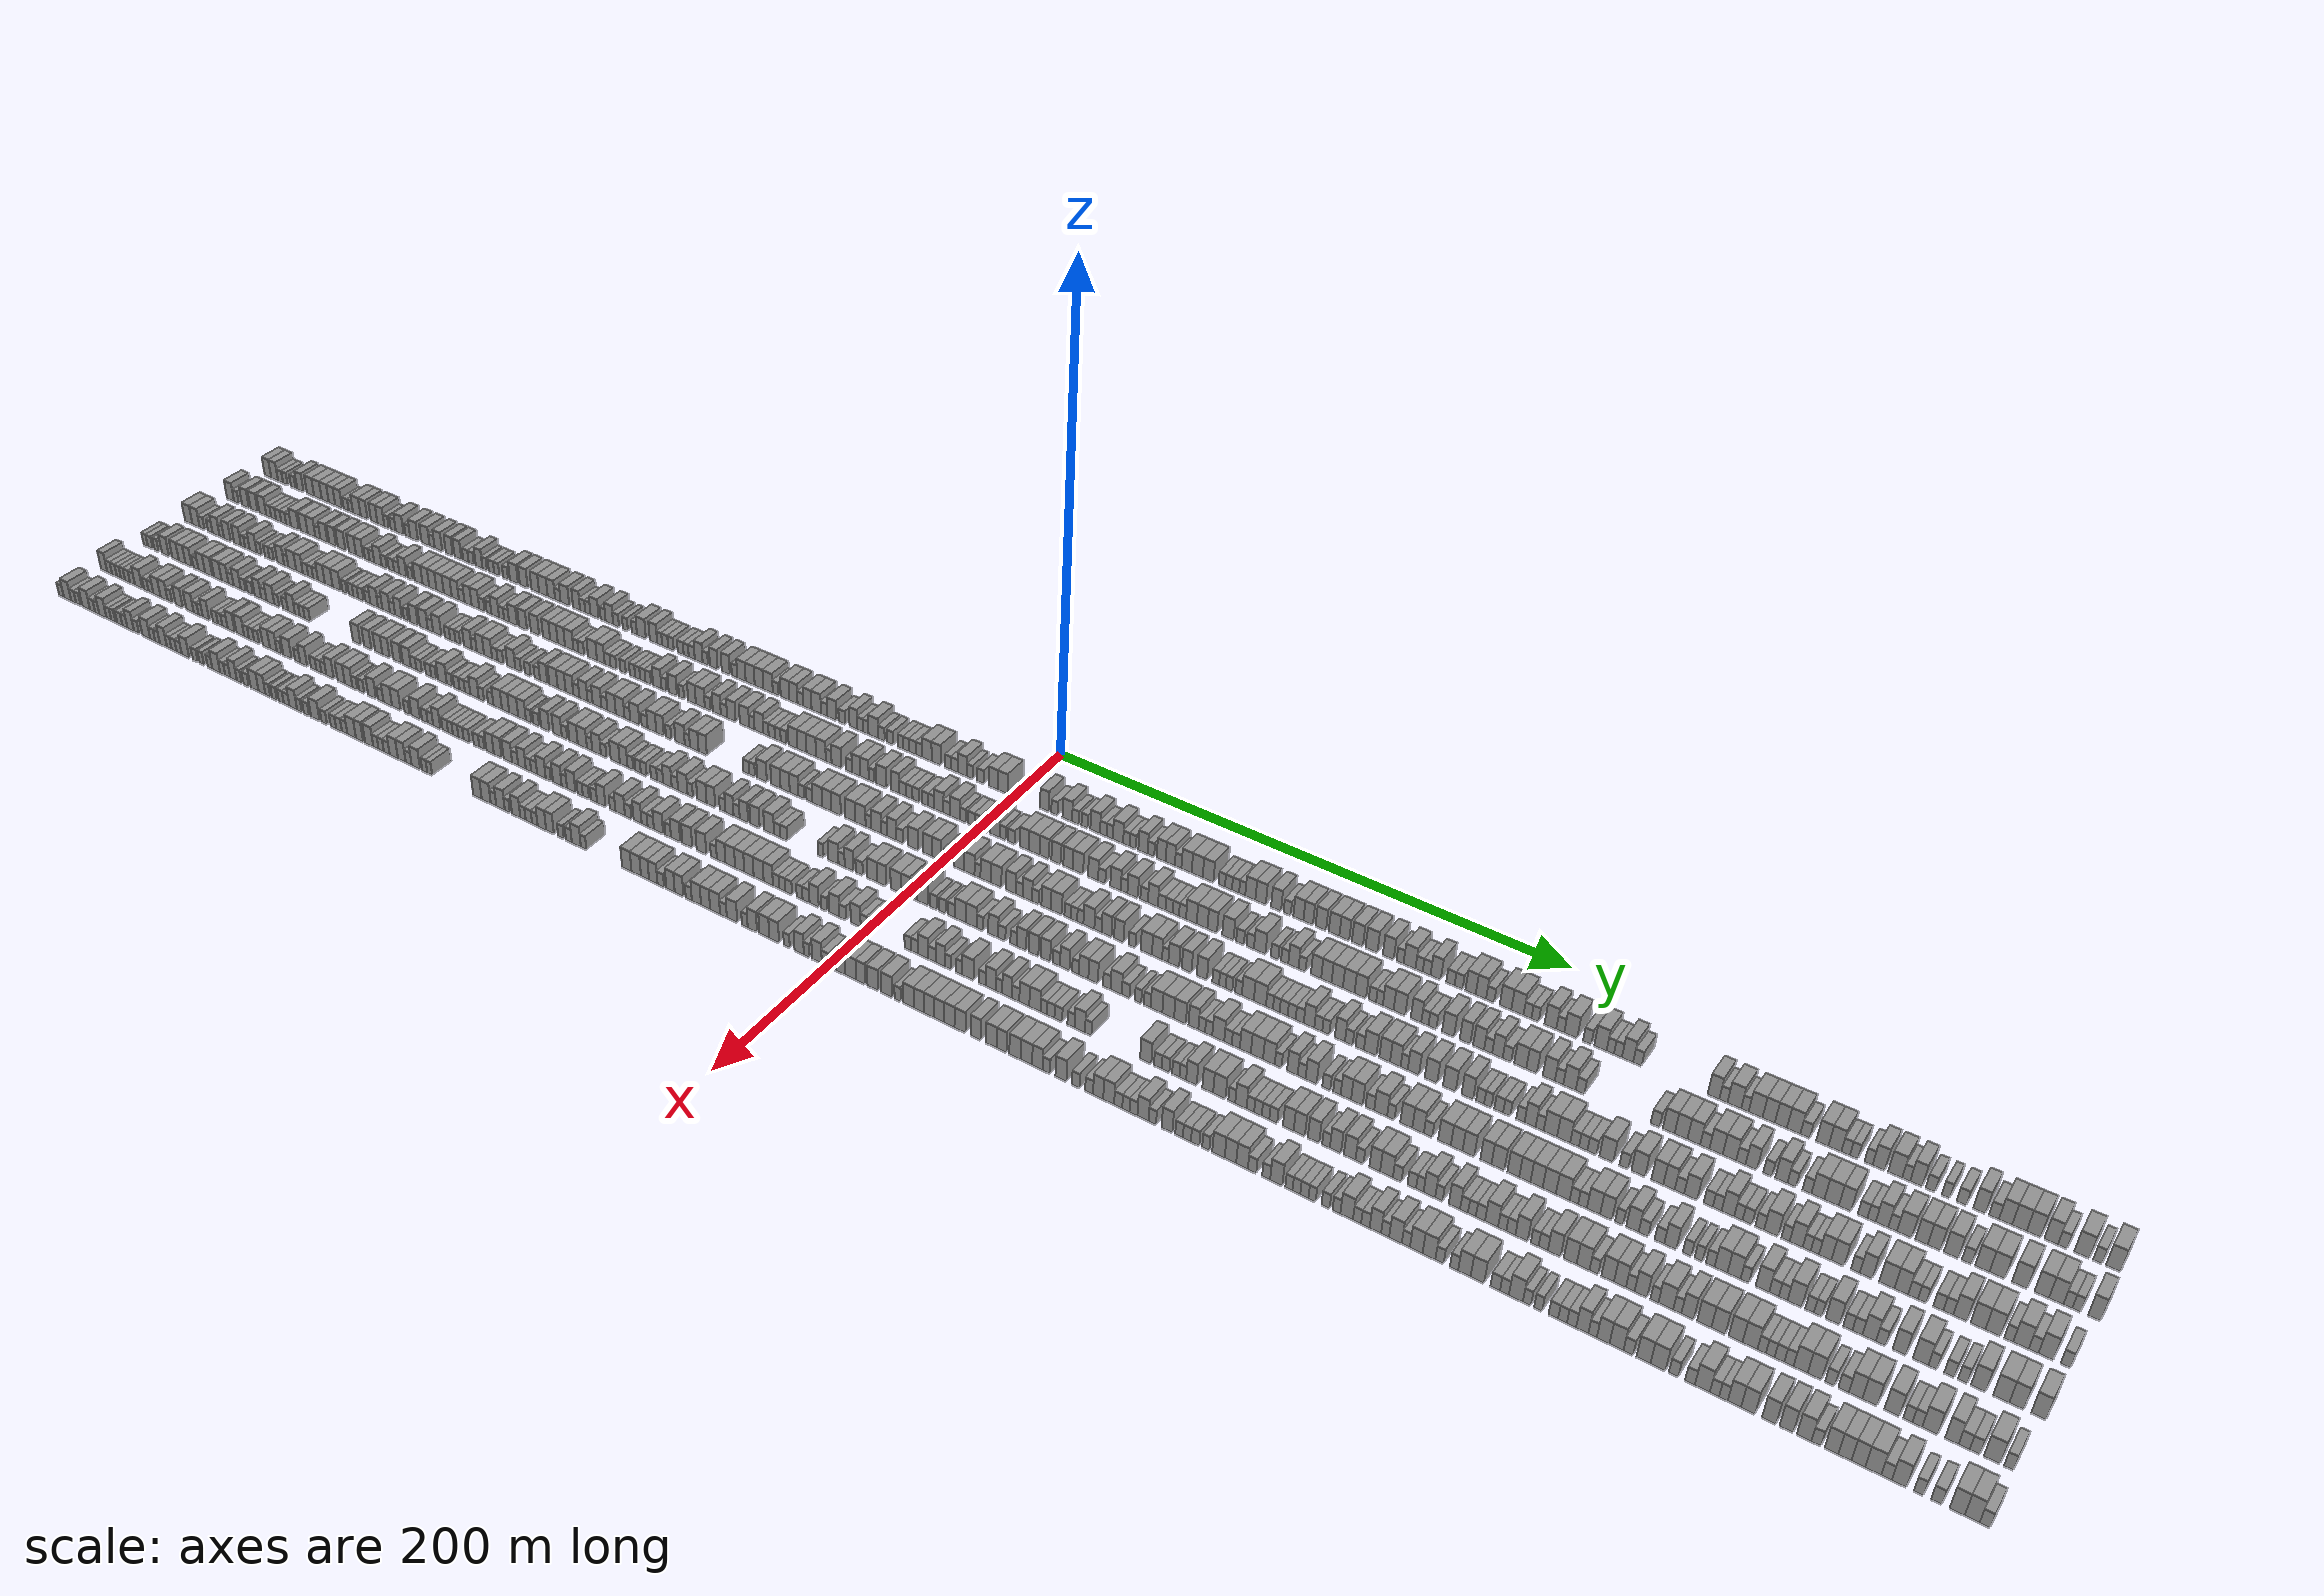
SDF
<sdf version="1.6">
 <world name="default">
  <scene>
   <sky><clouds><speed>12</speed></clouds></sky>
   <ambient>0.4 0.4 0.4 1</ambient>
   <background>0.7 0.7 0.7 1</background>
   <shadows>1</shadows>
  </scene>
  <gravity>0 0 -9.8066</gravity>
  <magnetic_field>6e-06 2.3e-05 -4.2e-05</magnetic_field>
  <physics default="0" name="default_physics" type="ode">
   <ode>
    <solver>
     <type>quick</type>
     <iters>10</iters>
     <sor>1.0</sor>
     <use_dynamic_moi_rescaling>0</use_dynamic_moi_rescaling>
    </solver>
    <constraints>
     <cfm>0</cfm>
     <erp>0.2</erp>
     <contact_max_correcting_vel>100</contact_max_correcting_vel>
     <contact_surface_layer>0.001</contact_surface_layer>
    </constraints>
   </ode>
   <max_step_size>0.004</max_step_size>
   <real_time_factor>1</real_time_factor>
   <real_time_update_rate>250</real_time_update_rate>
  </physics>
  <light name="sun" type="directional">
   <pose>0 0 10 0 0 0</pose>
   <diffuse>0.8 0.8 0.8 1</diffuse>
   <specular>0.2 0.2 0.2 1</specular>
   <attenuation>
    <range>1000</range>
    <constant>0.9</constant>
    <linear>0.01</linear>
    <quadratic>0.001</quadratic>
   </attenuation>
   <direction>-0.5 0.1 -0.9</direction>
  </light>
  <model name="building_1">
   <static>1</static>
   <pose>25.0000 -378.0509 0 0.000000 0.000000 0.000000</pose>
   <link name="link">
    <pose>0 0 4.50 0 0 0</pose>
    <collision name="collision"><geometry><box><size>10.0000 3.8982 9.0000</size></box></geometry></collision>
    <visual name="visual">
     <cast_shadows>0</cast_shadows>
     <geometry><box><size>10.0000 3.8982 9.0000</size></box></geometry>
     <material>
      <script>
       <uri>model://grey_wall/materials/scripts</uri>
       <uri>model://grey_wall/materials/textures</uri>
       <name>vrc/grey_wall</name>
      </script>
     </material>
    </visual>
   </link>
  </model>
  <model name="building_2">
   <static>1</static>
   <pose>25.0000 -374.0797 0 0.000000 0.000000 0.000000</pose>
   <link name="link">
    <pose>0 0 4.50 0 0 0</pose>
    <collision name="collision"><geometry><box><size>10.0000 4.0440 9.0000</size></box></geometry></collision>
    <visual name="visual">
     <cast_shadows>0</cast_shadows>
     <geometry><box><size>10.0000 4.0440 9.0000</size></box></geometry>
     <material>
      <script>
       <uri>model://grey_wall/materials/scripts</uri>
       <uri>model://grey_wall/materials/textures</uri>
       <name>vrc/grey_wall</name>
      </script>
     </material>
    </visual>
   </link>
  </model>
  <model name="building_3">
   <static>1</static>
   <pose>25.0000 -370.5711 0 0.000000 0.000000 0.000000</pose>
   <link name="link">
    <pose>0 0 3.00 0 0 0</pose>
    <collision name="collision"><geometry><box><size>10.0000 2.9733 6.0000</size></box></geometry></collision>
    <visual name="visual">
     <cast_shadows>0</cast_shadows>
     <geometry><box><size>10.0000 2.9733 6.0000</size></box></geometry>
     <material>
      <script>
       <uri>model://grey_wall/materials/scripts</uri>
       <uri>model://grey_wall/materials/textures</uri>
       <name>vrc/grey_wall</name>
      </script>
     </material>
    </visual>
   </link>
  </model>
  <model name="building_4">
   <static>1</static>
   <pose>25.0000 -367.7521 0 0.000000 0.000000 0.000000</pose>
   <link name="link">
    <pose>0 0 3.00 0 0 0</pose>
    <collision name="collision"><geometry><box><size>10.0000 2.6647 6.0000</size></box></geometry></collision>
    <visual name="visual">
     <cast_shadows>0</cast_shadows>
     <geometry><box><size>10.0000 2.6647 6.0000</size></box></geometry>
     <material>
      <script>
       <uri>model://grey_wall/materials/scripts</uri>
       <uri>model://grey_wall/materials/textures</uri>
       <name>vrc/grey_wall</name>
      </script>
     </material>
    </visual>
   </link>
  </model>
  <model name="building_5">
   <static>1</static>
   <pose>25.0000 -363.0507 0 0.000000 0.000000 0.000000</pose>
   <link name="link">
    <pose>0 0 3.00 0 0 0</pose>
    <collision name="collision"><geometry><box><size>10.0000 2.7381 6.0000</size></box></geometry></collision>
    <visual name="visual">
     <cast_shadows>0</cast_shadows>
     <geometry><box><size>10.0000 2.7381 6.0000</size></box></geometry>
     <material>
      <script>
       <uri>model://grey_wall/materials/scripts</uri>
       <uri>model://grey_wall/materials/textures</uri>
       <name>vrc/grey_wall</name>
      </script>
     </material>
    </visual>
   </link>
  </model>
  <model name="building_6">
   <static>1</static>
   <pose>25.0000 -358.7996 0 0.000000 0.000000 0.000000</pose>
   <link name="link">
    <pose>0 0 4.50 0 0 0</pose>
    <collision name="collision"><geometry><box><size>10.0000 3.7640 9.0000</size></box></geometry></collision>
    <visual name="visual">
     <cast_shadows>0</cast_shadows>
     <geometry><box><size>10.0000 3.7640 9.0000</size></box></geometry>
     <material>
      <script>
       <uri>model://grey_wall/materials/scripts</uri>
       <uri>model://grey_wall/materials/textures</uri>
       <name>vrc/grey_wall</name>
      </script>
     </material>
    </visual>
   </link>
  </model>
  <model name="building_7">
   <static>1</static>
   <pose>25.0000 -352.8179 0 0.000000 0.000000 0.000000</pose>
   <link name="link">
    <pose>0 0 4.50 0 0 0</pose>
    <collision name="collision"><geometry><box><size>10.0000 4.1994 9.0000</size></box></geometry></collision>
    <visual name="visual">
     <cast_shadows>0</cast_shadows>
     <geometry><box><size>10.0000 4.1994 9.0000</size></box></geometry>
     <material>
      <script>
       <uri>model://grey_wall/materials/scripts</uri>
       <uri>model://grey_wall/materials/textures</uri>
       <name>vrc/grey_wall</name>
      </script>
     </material>
    </visual>
   </link>
  </model>
  <model name="building_8">
   <static>1</static>
   <pose>25.0000 -348.5039 0 0.000000 0.000000 0.000000</pose>
   <link name="link">
    <pose>0 0 4.50 0 0 0</pose>
    <collision name="collision"><geometry><box><size>10.0000 4.4284 9.0000</size></box></geometry></collision>
    <visual name="visual">
     <cast_shadows>0</cast_shadows>
     <geometry><box><size>10.0000 4.4284 9.0000</size></box></geometry>
     <material>
      <script>
       <uri>model://grey_wall/materials/scripts</uri>
       <uri>model://grey_wall/materials/textures</uri>
       <name>vrc/grey_wall</name>
      </script>
     </material>
    </visual>
   </link>
  </model>
  <model name="building_9">
   <static>1</static>
   <pose>25.0000 -344.2321 0 0.000000 0.000000 0.000000</pose>
   <link name="link">
    <pose>0 0 4.50 0 0 0</pose>
    <collision name="collision"><geometry><box><size>10.0000 4.1153 9.0000</size></box></geometry></collision>
    <visual name="visual">
     <cast_shadows>0</cast_shadows>
     <geometry><box><size>10.0000 4.1153 9.0000</size></box></geometry>
     <material>
      <script>
       <uri>model://grey_wall/materials/scripts</uri>
       <uri>model://grey_wall/materials/textures</uri>
       <name>vrc/grey_wall</name>
      </script>
     </material>
    </visual>
   </link>
  </model>
  <model name="building_10">
   <static>1</static>
   <pose>25.0000 -340.2857 0 0.000000 0.000000 0.000000</pose>
   <link name="link">
    <pose>0 0 4.50 0 0 0</pose>
    <collision name="collision"><geometry><box><size>10.0000 3.7775 9.0000</size></box></geometry></collision>
    <visual name="visual">
     <cast_shadows>0</cast_shadows>
     <geometry><box><size>10.0000 3.7775 9.0000</size></box></geometry>
     <material>
      <script>
       <uri>model://grey_wall/materials/scripts</uri>
       <uri>model://grey_wall/materials/textures</uri>
       <name>vrc/grey_wall</name>
      </script>
     </material>
    </visual>
   </link>
  </model>
  <model name="building_11">
   <static>1</static>
   <pose>25.0000 -336.4537 0 0.000000 0.000000 0.000000</pose>
   <link name="link">
    <pose>0 0 4.50 0 0 0</pose>
    <collision name="collision"><geometry><box><size>10.0000 3.8866 9.0000</size></box></geometry></collision>
    <visual name="visual">
     <cast_shadows>0</cast_shadows>
     <geometry><box><size>10.0000 3.8866 9.0000</size></box></geometry>
     <material>
      <script>
       <uri>model://grey_wall/materials/scripts</uri>
       <uri>model://grey_wall/materials/textures</uri>
       <name>vrc/grey_wall</name>
      </script>
     </material>
    </visual>
   </link>
  </model>
  <model name="building_12">
   <static>1</static>
   <pose>25.0000 -332.0855 0 0.000000 0.000000 0.000000</pose>
   <link name="link">
    <pose>0 0 3.00 0 0 0</pose>
    <collision name="collision"><geometry><box><size>10.0000 2.8497 6.0000</size></box></geometry></collision>
    <visual name="visual">
     <cast_shadows>0</cast_shadows>
     <geometry><box><size>10.0000 2.8497 6.0000</size></box></geometry>
     <material>
      <script>
       <uri>model://grey_wall/materials/scripts</uri>
       <uri>model://grey_wall/materials/textures</uri>
       <name>vrc/grey_wall</name>
      </script>
     </material>
    </visual>
   </link>
  </model>
  <model name="building_13">
   <static>1</static>
   <pose>25.0000 -329.4376 0 0.000000 0.000000 0.000000</pose>
   <link name="link">
    <pose>0 0 3.00 0 0 0</pose>
    <collision name="collision"><geometry><box><size>10.0000 2.4461 6.0000</size></box></geometry></collision>
    <visual name="visual">
     <cast_shadows>0</cast_shadows>
     <geometry><box><size>10.0000 2.4461 6.0000</size></box></geometry>
     <material>
      <script>
       <uri>model://grey_wall/materials/scripts</uri>
       <uri>model://grey_wall/materials/textures</uri>
       <name>vrc/grey_wall</name>
      </script>
     </material>
    </visual>
   </link>
  </model>
  <model name="building_14">
   <static>1</static>
   <pose>25.0000 -326.0025 0 0.000000 0.000000 0.000000</pose>
   <link name="link">
    <pose>0 0 4.50 0 0 0</pose>
    <collision name="collision"><geometry><box><size>10.0000 4.4242 9.0000</size></box></geometry></collision>
    <visual name="visual">
     <cast_shadows>0</cast_shadows>
     <geometry><box><size>10.0000 4.4242 9.0000</size></box></geometry>
     <material>
      <script>
       <uri>model://grey_wall/materials/scripts</uri>
       <uri>model://grey_wall/materials/textures</uri>
       <name>vrc/grey_wall</name>
      </script>
     </material>
    </visual>
   </link>
  </model>
  <model name="building_15">
   <static>1</static>
   <pose>25.0000 -321.8357 0 0.000000 0.000000 0.000000</pose>
   <link name="link">
    <pose>0 0 4.50 0 0 0</pose>
    <collision name="collision"><geometry><box><size>10.0000 3.9092 9.0000</size></box></geometry></collision>
    <visual name="visual">
     <cast_shadows>0</cast_shadows>
     <geometry><box><size>10.0000 3.9092 9.0000</size></box></geometry>
     <material>
      <script>
       <uri>model://grey_wall/materials/scripts</uri>
       <uri>model://grey_wall/materials/textures</uri>
       <name>vrc/grey_wall</name>
      </script>
     </material>
    </visual>
   </link>
  </model>
  <model name="building_16">
   <static>1</static>
   <pose>25.0000 -316.0678 0 0.000000 0.000000 0.000000</pose>
   <link name="link">
    <pose>0 0 4.50 0 0 0</pose>
    <collision name="collision"><geometry><box><size>10.0000 3.6266 9.0000</size></box></geometry></collision>
    <visual name="visual">
     <cast_shadows>0</cast_shadows>
     <geometry><box><size>10.0000 3.6266 9.0000</size></box></geometry>
     <material>
      <script>
       <uri>model://grey_wall/materials/scripts</uri>
       <uri>model://grey_wall/materials/textures</uri>
       <name>vrc/grey_wall</name>
      </script>
     </material>
    </visual>
   </link>
  </model>
  <model name="building_17">
   <static>1</static>
   <pose>25.0000 -312.2906 0 0.000000 0.000000 0.000000</pose>
   <link name="link">
    <pose>0 0 4.50 0 0 0</pose>
    <collision name="collision"><geometry><box><size>10.0000 3.9279 9.0000</size></box></geometry></collision>
    <visual name="visual">
     <cast_shadows>0</cast_shadows>
     <geometry><box><size>10.0000 3.9279 9.0000</size></box></geometry>
     <material>
      <script>
       <uri>model://grey_wall/materials/scripts</uri>
       <uri>model://grey_wall/materials/textures</uri>
       <name>vrc/grey_wall</name>
      </script>
     </material>
    </visual>
   </link>
  </model>
  <model name="building_18">
   <static>1</static>
   <pose>25.0000 -309.0720 0 0.000000 0.000000 0.000000</pose>
   <link name="link">
    <pose>0 0 3.00 0 0 0</pose>
    <collision name="collision"><geometry><box><size>10.0000 2.5093 6.0000</size></box></geometry></collision>
    <visual name="visual">
     <cast_shadows>0</cast_shadows>
     <geometry><box><size>10.0000 2.5093 6.0000</size></box></geometry>
     <material>
      <script>
       <uri>model://grey_wall/materials/scripts</uri>
       <uri>model://grey_wall/materials/textures</uri>
       <name>vrc/grey_wall</name>
      </script>
     </material>
    </visual>
   </link>
  </model>
  <model name="building_19">
   <static>1</static>
   <pose>25.0000 -305.3311 0 0.000000 0.000000 0.000000</pose>
   <link name="link">
    <pose>0 0 3.00 0 0 0</pose>
    <collision name="collision"><geometry><box><size>10.0000 2.9726 6.0000</size></box></geometry></collision>
    <visual name="visual">
     <cast_shadows>0</cast_shadows>
     <geometry><box><size>10.0000 2.9726 6.0000</size></box></geometry>
     <material>
      <script>
       <uri>model://grey_wall/materials/scripts</uri>
       <uri>model://grey_wall/materials/textures</uri>
       <name>vrc/grey_wall</name>
      </script>
     </material>
    </visual>
   </link>
  </model>
  <model name="building_20">
   <static>1</static>
   <pose>25.0000 -301.6271 0 0.000000 0.000000 0.000000</pose>
   <link name="link">
    <pose>0 0 4.50 0 0 0</pose>
    <collision name="collision"><geometry><box><size>10.0000 4.4356 9.0000</size></box></geometry></collision>
    <visual name="visual">
     <cast_shadows>0</cast_shadows>
     <geometry><box><size>10.0000 4.4356 9.0000</size></box></geometry>
     <material>
      <script>
       <uri>model://grey_wall/materials/scripts</uri>
       <uri>model://grey_wall/materials/textures</uri>
       <name>vrc/grey_wall</name>
      </script>
     </material>
    </visual>
   </link>
  </model>
  <model name="building_21">
   <static>1</static>
   <pose>25.0000 -297.1116 0 0.000000 0.000000 0.000000</pose>
   <link name="link">
    <pose>0 0 3.00 0 0 0</pose>
    <collision name="collision"><geometry><box><size>10.0000 2.5954 6.0000</size></box></geometry></collision>
    <visual name="visual">
     <cast_shadows>0</cast_shadows>
     <geometry><box><size>10.0000 2.5954 6.0000</size></box></geometry>
     <material>
      <script>
       <uri>model://grey_wall/materials/scripts</uri>
       <uri>model://grey_wall/materials/textures</uri>
       <name>vrc/grey_wall</name>
      </script>
     </material>
    </visual>
   </link>
  </model>
  <model name="building_22">
   <static>1</static>
   <pose>25.0000 -293.6327 0 0.000000 0.000000 0.000000</pose>
   <link name="link">
    <pose>0 0 4.50 0 0 0</pose>
    <collision name="collision"><geometry><box><size>10.0000 4.3623 9.0000</size></box></geometry></collision>
    <visual name="visual">
     <cast_shadows>0</cast_shadows>
     <geometry><box><size>10.0000 4.3623 9.0000</size></box></geometry>
     <material>
      <script>
       <uri>model://grey_wall/materials/scripts</uri>
       <uri>model://grey_wall/materials/textures</uri>
       <name>vrc/grey_wall</name>
      </script>
     </material>
    </visual>
   </link>
  </model>
  <model name="building_23">
   <static>1</static>
   <pose>25.0000 -287.2162 0 0.000000 0.000000 0.000000</pose>
   <link name="link">
    <pose>0 0 4.50 0 0 0</pose>
    <collision name="collision"><geometry><box><size>10.0000 4.4706 9.0000</size></box></geometry></collision>
    <visual name="visual">
     <cast_shadows>0</cast_shadows>
     <geometry><box><size>10.0000 4.4706 9.0000</size></box></geometry>
     <material>
      <script>
       <uri>model://grey_wall/materials/scripts</uri>
       <uri>model://grey_wall/materials/textures</uri>
       <name>vrc/grey_wall</name>
      </script>
     </material>
    </visual>
   </link>
  </model>
  <model name="building_24">
   <static>1</static>
   <pose>25.0000 -283.5953 0 0.000000 0.000000 0.000000</pose>
   <link name="link">
    <pose>0 0 3.00 0 0 0</pose>
    <collision name="collision"><geometry><box><size>10.0000 2.7713 6.0000</size></box></geometry></collision>
    <visual name="visual">
     <cast_shadows>0</cast_shadows>
     <geometry><box><size>10.0000 2.7713 6.0000</size></box></geometry>
     <material>
      <script>
       <uri>model://grey_wall/materials/scripts</uri>
       <uri>model://grey_wall/materials/textures</uri>
       <name>vrc/grey_wall</name>
      </script>
     </material>
    </visual>
   </link>
  </model>
  <model name="building_25">
   <static>1</static>
   <pose>25.0000 -280.1155 0 0.000000 0.000000 0.000000</pose>
   <link name="link">
    <pose>0 0 4.50 0 0 0</pose>
    <collision name="collision"><geometry><box><size>10.0000 4.1884 9.0000</size></box></geometry></collision>
    <visual name="visual">
     <cast_shadows>0</cast_shadows>
     <geometry><box><size>10.0000 4.1884 9.0000</size></box></geometry>
     <material>
      <script>
       <uri>model://grey_wall/materials/scripts</uri>
       <uri>model://grey_wall/materials/textures</uri>
       <name>vrc/grey_wall</name>
      </script>
     </material>
    </visual>
   </link>
  </model>
  <model name="building_26">
   <static>1</static>
   <pose>25.0000 -274.1162 0 0.000000 0.000000 0.000000</pose>
   <link name="link">
    <pose>0 0 4.50 0 0 0</pose>
    <collision name="collision"><geometry><box><size>10.0000 3.8103 9.0000</size></box></geometry></collision>
    <visual name="visual">
     <cast_shadows>0</cast_shadows>
     <geometry><box><size>10.0000 3.8103 9.0000</size></box></geometry>
     <material>
      <script>
       <uri>model://grey_wall/materials/scripts</uri>
       <uri>model://grey_wall/materials/textures</uri>
       <name>vrc/grey_wall</name>
      </script>
     </material>
    </visual>
   </link>
  </model>
  <model name="building_27">
   <static>1</static>
   <pose>25.0000 -269.3501 0 0.000000 0.000000 0.000000</pose>
   <link name="link">
    <pose>0 0 4.50 0 0 0</pose>
    <collision name="collision"><geometry><box><size>10.0000 3.7218 9.0000</size></box></geometry></collision>
    <visual name="visual">
     <cast_shadows>0</cast_shadows>
     <geometry><box><size>10.0000 3.7218 9.0000</size></box></geometry>
     <material>
      <script>
       <uri>model://grey_wall/materials/scripts</uri>
       <uri>model://grey_wall/materials/textures</uri>
       <name>vrc/grey_wall</name>
      </script>
     </material>
    </visual>
   </link>
  </model>
  <model name="building_28">
   <static>1</static>
   <pose>25.0000 -265.0193 0 0.000000 0.000000 0.000000</pose>
   <link name="link">
    <pose>0 0 3.00 0 0 0</pose>
    <collision name="collision"><geometry><box><size>10.0000 2.9399 6.0000</size></box></geometry></collision>
    <visual name="visual">
     <cast_shadows>0</cast_shadows>
     <geometry><box><size>10.0000 2.9399 6.0000</size></box></geometry>
     <material>
      <script>
       <uri>model://grey_wall/materials/scripts</uri>
       <uri>model://grey_wall/materials/textures</uri>
       <name>vrc/grey_wall</name>
      </script>
     </material>
    </visual>
   </link>
  </model>
  <model name="building_29">
   <static>1</static>
   <pose>25.0000 -262.1309 0 0.000000 0.000000 0.000000</pose>
   <link name="link">
    <pose>0 0 3.00 0 0 0</pose>
    <collision name="collision"><geometry><box><size>10.0000 2.8371 6.0000</size></box></geometry></collision>
    <visual name="visual">
     <cast_shadows>0</cast_shadows>
     <geometry><box><size>10.0000 2.8371 6.0000</size></box></geometry>
     <material>
      <script>
       <uri>model://grey_wall/materials/scripts</uri>
       <uri>model://grey_wall/materials/textures</uri>
       <name>vrc/grey_wall</name>
      </script>
     </material>
    </visual>
   </link>
  </model>
  <model name="building_30">
   <static>1</static>
   <pose>25.0000 -257.8858 0 0.000000 0.000000 0.000000</pose>
   <link name="link">
    <pose>0 0 4.50 0 0 0</pose>
    <collision name="collision"><geometry><box><size>10.0000 3.6531 9.0000</size></box></geometry></collision>
    <visual name="visual">
     <cast_shadows>0</cast_shadows>
     <geometry><box><size>10.0000 3.6531 9.0000</size></box></geometry>
     <material>
      <script>
       <uri>model://grey_wall/materials/scripts</uri>
       <uri>model://grey_wall/materials/textures</uri>
       <name>vrc/grey_wall</name>
      </script>
     </material>
    </visual>
   </link>
  </model>
  <model name="building_31">
   <static>1</static>
   <pose>25.0000 -254.8350 0 0.000000 0.000000 0.000000</pose>
   <link name="link">
    <pose>0 0 3.00 0 0 0</pose>
    <collision name="collision"><geometry><box><size>10.0000 2.4486 6.0000</size></box></geometry></collision>
    <visual name="visual">
     <cast_shadows>0</cast_shadows>
     <geometry><box><size>10.0000 2.4486 6.0000</size></box></geometry>
     <material>
      <script>
       <uri>model://grey_wall/materials/scripts</uri>
       <uri>model://grey_wall/materials/textures</uri>
       <name>vrc/grey_wall</name>
      </script>
     </material>
    </visual>
   </link>
  </model>
  <model name="building_32">
   <static>1</static>
   <pose>25.0000 -251.1613 0 0.000000 0.000000 0.000000</pose>
   <link name="link">
    <pose>0 0 3.00 0 0 0</pose>
    <collision name="collision"><geometry><box><size>10.0000 2.8987 6.0000</size></box></geometry></collision>
    <visual name="visual">
     <cast_shadows>0</cast_shadows>
     <geometry><box><size>10.0000 2.8987 6.0000</size></box></geometry>
     <material>
      <script>
       <uri>model://grey_wall/materials/scripts</uri>
       <uri>model://grey_wall/materials/textures</uri>
       <name>vrc/grey_wall</name>
      </script>
     </material>
    </visual>
   </link>
  </model>
  <model name="building_33">
   <static>1</static>
   <pose>25.0000 -248.3260 0 0.000000 0.000000 0.000000</pose>
   <link name="link">
    <pose>0 0 3.00 0 0 0</pose>
    <collision name="collision"><geometry><box><size>10.0000 2.7719 6.0000</size></box></geometry></collision>
    <visual name="visual">
     <cast_shadows>0</cast_shadows>
     <geometry><box><size>10.0000 2.7719 6.0000</size></box></geometry>
     <material>
      <script>
       <uri>model://grey_wall/materials/scripts</uri>
       <uri>model://grey_wall/materials/textures</uri>
       <name>vrc/grey_wall</name>
      </script>
     </material>
    </visual>
   </link>
  </model>
  <model name="building_34">
   <static>1</static>
   <pose>25.0000 -243.6265 0 0.000000 0.000000 0.000000</pose>
   <link name="link">
    <pose>0 0 3.00 0 0 0</pose>
    <collision name="collision"><geometry><box><size>10.0000 2.6273 6.0000</size></box></geometry></collision>
    <visual name="visual">
     <cast_shadows>0</cast_shadows>
     <geometry><box><size>10.0000 2.6273 6.0000</size></box></geometry>
     <material>
      <script>
       <uri>model://grey_wall/materials/scripts</uri>
       <uri>model://grey_wall/materials/textures</uri>
       <name>vrc/grey_wall</name>
      </script>
     </material>
    </visual>
   </link>
  </model>
  <model name="building_35">
   <static>1</static>
   <pose>25.0000 -239.1774 0 0.000000 0.000000 0.000000</pose>
   <link name="link">
    <pose>0 0 4.50 0 0 0</pose>
    <collision name="collision"><geometry><box><size>10.0000 4.2708 9.0000</size></box></geometry></collision>
    <visual name="visual">
     <cast_shadows>0</cast_shadows>
     <geometry><box><size>10.0000 4.2708 9.0000</size></box></geometry>
     <material>
      <script>
       <uri>model://grey_wall/materials/scripts</uri>
       <uri>model://grey_wall/materials/textures</uri>
       <name>vrc/grey_wall</name>
      </script>
     </material>
    </visual>
   </link>
  </model>
  <model name="building_36">
   <static>1</static>
   <pose>25.0000 -233.9586 0 0.000000 0.000000 0.000000</pose>
   <link name="link">
    <pose>0 0 4.50 0 0 0</pose>
    <collision name="collision"><geometry><box><size>10.0000 4.1669 9.0000</size></box></geometry></collision>
    <visual name="visual">
     <cast_shadows>0</cast_shadows>
     <geometry><box><size>10.0000 4.1669 9.0000</size></box></geometry>
     <material>
      <script>
       <uri>model://grey_wall/materials/scripts</uri>
       <uri>model://grey_wall/materials/textures</uri>
       <name>vrc/grey_wall</name>
      </script>
     </material>
    </visual>
   </link>
  </model>
  <model name="building_37">
   <static>1</static>
   <pose>25.0000 -227.8660 0 0.000000 0.000000 0.000000</pose>
   <link name="link">
    <pose>0 0 4.50 0 0 0</pose>
    <collision name="collision"><geometry><box><size>10.0000 4.0181 9.0000</size></box></geometry></collision>
    <visual name="visual">
     <cast_shadows>0</cast_shadows>
     <geometry><box><size>10.0000 4.0181 9.0000</size></box></geometry>
     <material>
      <script>
       <uri>model://grey_wall/materials/scripts</uri>
       <uri>model://grey_wall/materials/textures</uri>
       <name>vrc/grey_wall</name>
      </script>
     </material>
    </visual>
   </link>
  </model>
  <model name="building_38">
   <static>1</static>
   <pose>25.0000 -223.6124 0 0.000000 0.000000 0.000000</pose>
   <link name="link">
    <pose>0 0 4.50 0 0 0</pose>
    <collision name="collision"><geometry><box><size>10.0000 4.4892 9.0000</size></box></geometry></collision>
    <visual name="visual">
     <cast_shadows>0</cast_shadows>
     <geometry><box><size>10.0000 4.4892 9.0000</size></box></geometry>
     <material>
      <script>
       <uri>model://grey_wall/materials/scripts</uri>
       <uri>model://grey_wall/materials/textures</uri>
       <name>vrc/grey_wall</name>
      </script>
     </material>
    </visual>
   </link>
  </model>
  <model name="building_39">
   <static>1</static>
   <pose>25.0000 -219.4153 0 0.000000 0.000000 0.000000</pose>
   <link name="link">
    <pose>0 0 4.50 0 0 0</pose>
    <collision name="collision"><geometry><box><size>10.0000 3.9049 9.0000</size></box></geometry></collision>
    <visual name="visual">
     <cast_shadows>0</cast_shadows>
     <geometry><box><size>10.0000 3.9049 9.0000</size></box></geometry>
     <material>
      <script>
       <uri>model://grey_wall/materials/scripts</uri>
       <uri>model://grey_wall/materials/textures</uri>
       <name>vrc/grey_wall</name>
      </script>
     </material>
    </visual>
   </link>
  </model>
  <model name="building_40">
   <static>1</static>
   <pose>25.0000 -216.0444 0 0.000000 0.000000 0.000000</pose>
   <link name="link">
    <pose>0 0 3.00 0 0 0</pose>
    <collision name="collision"><geometry><box><size>10.0000 2.8369 6.0000</size></box></geometry></collision>
    <visual name="visual">
     <cast_shadows>0</cast_shadows>
     <geometry><box><size>10.0000 2.8369 6.0000</size></box></geometry>
     <material>
      <script>
       <uri>model://grey_wall/materials/scripts</uri>
       <uri>model://grey_wall/materials/textures</uri>
       <name>vrc/grey_wall</name>
      </script>
     </material>
    </visual>
   </link>
  </model>
  <model name="building_41">
   <static>1</static>
   <pose>25.0000 -212.3795 0 0.000000 0.000000 0.000000</pose>
   <link name="link">
    <pose>0 0 4.50 0 0 0</pose>
    <collision name="collision"><geometry><box><size>10.0000 4.4929 9.0000</size></box></geometry></collision>
    <visual name="visual">
     <cast_shadows>0</cast_shadows>
     <geometry><box><size>10.0000 4.4929 9.0000</size></box></geometry>
     <material>
      <script>
       <uri>model://grey_wall/materials/scripts</uri>
       <uri>model://grey_wall/materials/textures</uri>
       <name>vrc/grey_wall</name>
      </script>
     </material>
    </visual>
   </link>
  </model>
  <model name="building_42">
   <static>1</static>
   <pose>25.0000 -206.3270 0 0.000000 0.000000 0.000000</pose>
   <link name="link">
    <pose>0 0 4.50 0 0 0</pose>
    <collision name="collision"><geometry><box><size>10.0000 3.6121 9.0000</size></box></geometry></collision>
    <visual name="visual">
     <cast_shadows>0</cast_shadows>
     <geometry><box><size>10.0000 3.6121 9.0000</size></box></geometry>
     <material>
      <script>
       <uri>model://grey_wall/materials/scripts</uri>
       <uri>model://grey_wall/materials/textures</uri>
       <name>vrc/grey_wall</name>
      </script>
     </material>
    </visual>
   </link>
  </model>
  <model name="building_43">
   <static>1</static>
   <pose>25.0000 -203.1630 0 0.000000 0.000000 0.000000</pose>
   <link name="link">
    <pose>0 0 3.00 0 0 0</pose>
    <collision name="collision"><geometry><box><size>10.0000 2.7160 6.0000</size></box></geometry></collision>
    <visual name="visual">
     <cast_shadows>0</cast_shadows>
     <geometry><box><size>10.0000 2.7160 6.0000</size></box></geometry>
     <material>
      <script>
       <uri>model://grey_wall/materials/scripts</uri>
       <uri>model://grey_wall/materials/textures</uri>
       <name>vrc/grey_wall</name>
      </script>
     </material>
    </visual>
   </link>
  </model>
  <model name="building_44">
   <static>1</static>
   <pose>25.0000 -200.4754 0 0.000000 0.000000 0.000000</pose>
   <link name="link">
    <pose>0 0 3.00 0 0 0</pose>
    <collision name="collision"><geometry><box><size>10.0000 2.6592 6.0000</size></box></geometry></collision>
    <visual name="visual">
     <cast_shadows>0</cast_shadows>
     <geometry><box><size>10.0000 2.6592 6.0000</size></box></geometry>
     <material>
      <script>
       <uri>model://grey_wall/materials/scripts</uri>
       <uri>model://grey_wall/materials/textures</uri>
       <name>vrc/grey_wall</name>
      </script>
     </material>
    </visual>
   </link>
  </model>
  <model name="building_45">
   <static>1</static>
   <pose>25.0000 -197.0374 0 0.000000 0.000000 0.000000</pose>
   <link name="link">
    <pose>0 0 4.50 0 0 0</pose>
    <collision name="collision"><geometry><box><size>10.0000 4.2169 9.0000</size></box></geometry></collision>
    <visual name="visual">
     <cast_shadows>0</cast_shadows>
     <geometry><box><size>10.0000 4.2169 9.0000</size></box></geometry>
     <material>
      <script>
       <uri>model://grey_wall/materials/scripts</uri>
       <uri>model://grey_wall/materials/textures</uri>
       <name>vrc/grey_wall</name>
      </script>
     </material>
    </visual>
   </link>
  </model>
  <model name="building_46">
   <static>1</static>
   <pose>25.0000 -192.6730 0 0.000000 0.000000 0.000000</pose>
   <link name="link">
    <pose>0 0 3.00 0 0 0</pose>
    <collision name="collision"><geometry><box><size>10.0000 2.5117 6.0000</size></box></geometry></collision>
    <visual name="visual">
     <cast_shadows>0</cast_shadows>
     <geometry><box><size>10.0000 2.5117 6.0000</size></box></geometry>
     <material>
      <script>
       <uri>model://grey_wall/materials/scripts</uri>
       <uri>model://grey_wall/materials/textures</uri>
       <name>vrc/grey_wall</name>
      </script>
     </material>
    </visual>
   </link>
  </model>
  <model name="building_47">
   <static>1</static>
   <pose>25.0000 -189.4613 0 0.000000 0.000000 0.000000</pose>
   <link name="link">
    <pose>0 0 4.50 0 0 0</pose>
    <collision name="collision"><geometry><box><size>10.0000 3.9117 9.0000</size></box></geometry></collision>
    <visual name="visual">
     <cast_shadows>0</cast_shadows>
     <geometry><box><size>10.0000 3.9117 9.0000</size></box></geometry>
     <material>
      <script>
       <uri>model://grey_wall/materials/scripts</uri>
       <uri>model://grey_wall/materials/textures</uri>
       <name>vrc/grey_wall</name>
      </script>
     </material>
    </visual>
   </link>
  </model>
  <model name="building_48">
   <static>1</static>
   <pose>25.0000 -186.0551 0 0.000000 0.000000 0.000000</pose>
   <link name="link">
    <pose>0 0 3.00 0 0 0</pose>
    <collision name="collision"><geometry><box><size>10.0000 2.9008 6.0000</size></box></geometry></collision>
    <visual name="visual">
     <cast_shadows>0</cast_shadows>
     <geometry><box><size>10.0000 2.9008 6.0000</size></box></geometry>
     <material>
      <script>
       <uri>model://grey_wall/materials/scripts</uri>
       <uri>model://grey_wall/materials/textures</uri>
       <name>vrc/grey_wall</name>
      </script>
     </material>
    </visual>
   </link>
  </model>
  <model name="building_49">
   <static>1</static>
   <pose>25.0000 -181.3485 0 0.000000 0.000000 0.000000</pose>
   <link name="link">
    <pose>0 0 3.00 0 0 0</pose>
    <collision name="collision"><geometry><box><size>10.0000 2.5125 6.0000</size></box></geometry></collision>
    <visual name="visual">
     <cast_shadows>0</cast_shadows>
     <geometry><box><size>10.0000 2.5125 6.0000</size></box></geometry>
     <material>
      <script>
       <uri>model://grey_wall/materials/scripts</uri>
       <uri>model://grey_wall/materials/textures</uri>
       <name>vrc/grey_wall</name>
      </script>
     </material>
    </visual>
   </link>
  </model>
  <model name="building_50">
   <static>1</static>
   <pose>25.0000 -176.7957 0 0.000000 0.000000 0.000000</pose>
   <link name="link">
    <pose>0 0 3.00 0 0 0</pose>
    <collision name="collision"><geometry><box><size>10.0000 2.5931 6.0000</size></box></geometry></collision>
    <visual name="visual">
     <cast_shadows>0</cast_shadows>
     <geometry><box><size>10.0000 2.5931 6.0000</size></box></geometry>
     <material>
      <script>
       <uri>model://grey_wall/materials/scripts</uri>
       <uri>model://grey_wall/materials/textures</uri>
       <name>vrc/grey_wall</name>
      </script>
     </material>
    </visual>
   </link>
  </model>
  <model name="building_51">
   <static>1</static>
   <pose>25.0000 -173.2761 0 0.000000 0.000000 0.000000</pose>
   <link name="link">
    <pose>0 0 4.50 0 0 0</pose>
    <collision name="collision"><geometry><box><size>10.0000 4.4459 9.0000</size></box></geometry></collision>
    <visual name="visual">
     <cast_shadows>0</cast_shadows>
     <geometry><box><size>10.0000 4.4459 9.0000</size></box></geometry>
     <material>
      <script>
       <uri>model://grey_wall/materials/scripts</uri>
       <uri>model://grey_wall/materials/textures</uri>
       <name>vrc/grey_wall</name>
      </script>
     </material>
    </visual>
   </link>
  </model>
  <model name="building_52">
   <static>1</static>
   <pose>25.0000 -167.1985 0 0.000000 0.000000 0.000000</pose>
   <link name="link">
    <pose>0 0 4.50 0 0 0</pose>
    <collision name="collision"><geometry><box><size>10.0000 3.7094 9.0000</size></box></geometry></collision>
    <visual name="visual">
     <cast_shadows>0</cast_shadows>
     <geometry><box><size>10.0000 3.7094 9.0000</size></box></geometry>
     <material>
      <script>
       <uri>model://grey_wall/materials/scripts</uri>
       <uri>model://grey_wall/materials/textures</uri>
       <name>vrc/grey_wall</name>
      </script>
     </material>
    </visual>
   </link>
  </model>
  <model name="building_53">
   <static>1</static>
   <pose>25.0000 -164.1217 0 0.000000 0.000000 0.000000</pose>
   <link name="link">
    <pose>0 0 3.00 0 0 0</pose>
    <collision name="collision"><geometry><box><size>10.0000 2.4442 6.0000</size></box></geometry></collision>
    <visual name="visual">
     <cast_shadows>0</cast_shadows>
     <geometry><box><size>10.0000 2.4442 6.0000</size></box></geometry>
     <material>
      <script>
       <uri>model://grey_wall/materials/scripts</uri>
       <uri>model://grey_wall/materials/textures</uri>
       <name>vrc/grey_wall</name>
      </script>
     </material>
    </visual>
   </link>
  </model>
  <model name="building_54">
   <static>1</static>
   <pose>25.0000 -161.4051 0 0.000000 0.000000 0.000000</pose>
   <link name="link">
    <pose>0 0 3.00 0 0 0</pose>
    <collision name="collision"><geometry><box><size>10.0000 2.9888 6.0000</size></box></geometry></collision>
    <visual name="visual">
     <cast_shadows>0</cast_shadows>
     <geometry><box><size>10.0000 2.9888 6.0000</size></box></geometry>
     <material>
      <script>
       <uri>model://grey_wall/materials/scripts</uri>
       <uri>model://grey_wall/materials/textures</uri>
       <name>vrc/grey_wall</name>
      </script>
     </material>
    </visual>
   </link>
  </model>
  <model name="building_55">
   <static>1</static>
   <pose>25.0000 -158.5288 0 0.000000 0.000000 0.000000</pose>
   <link name="link">
    <pose>0 0 3.00 0 0 0</pose>
    <collision name="collision"><geometry><box><size>10.0000 2.7638 6.0000</size></box></geometry></collision>
    <visual name="visual">
     <cast_shadows>0</cast_shadows>
     <geometry><box><size>10.0000 2.7638 6.0000</size></box></geometry>
     <material>
      <script>
       <uri>model://grey_wall/materials/scripts</uri>
       <uri>model://grey_wall/materials/textures</uri>
       <name>vrc/grey_wall</name>
      </script>
     </material>
    </visual>
   </link>
  </model>
  <model name="building_56">
   <static>1</static>
   <pose>25.0000 -153.6962 0 0.000000 0.000000 0.000000</pose>
   <link name="link">
    <pose>0 0 3.00 0 0 0</pose>
    <collision name="collision"><geometry><box><size>10.0000 2.9015 6.0000</size></box></geometry></collision>
    <visual name="visual">
     <cast_shadows>0</cast_shadows>
     <geometry><box><size>10.0000 2.9015 6.0000</size></box></geometry>
     <material>
      <script>
       <uri>model://grey_wall/materials/scripts</uri>
       <uri>model://grey_wall/materials/textures</uri>
       <name>vrc/grey_wall</name>
      </script>
     </material>
    </visual>
   </link>
  </model>
  <model name="building_57">
   <static>1</static>
   <pose>25.0000 -150.9907 0 0.000000 0.000000 0.000000</pose>
   <link name="link">
    <pose>0 0 3.00 0 0 0</pose>
    <collision name="collision"><geometry><box><size>10.0000 2.5095 6.0000</size></box></geometry></collision>
    <visual name="visual">
     <cast_shadows>0</cast_shadows>
     <geometry><box><size>10.0000 2.5095 6.0000</size></box></geometry>
     <material>
      <script>
       <uri>model://grey_wall/materials/scripts</uri>
       <uri>model://grey_wall/materials/textures</uri>
       <name>vrc/grey_wall</name>
      </script>
     </material>
    </visual>
   </link>
  </model>
  <model name="building_58">
   <static>1</static>
   <pose>25.0000 -148.2503 0 0.000000 0.000000 0.000000</pose>
   <link name="link">
    <pose>0 0 3.00 0 0 0</pose>
    <collision name="collision"><geometry><box><size>10.0000 2.9712 6.0000</size></box></geometry></collision>
    <visual name="visual">
     <cast_shadows>0</cast_shadows>
     <geometry><box><size>10.0000 2.9712 6.0000</size></box></geometry>
     <material>
      <script>
       <uri>model://grey_wall/materials/scripts</uri>
       <uri>model://grey_wall/materials/textures</uri>
       <name>vrc/grey_wall</name>
      </script>
     </material>
    </visual>
   </link>
  </model>
  <model name="building_59">
   <static>1</static>
   <pose>25.0000 -144.8352 0 0.000000 0.000000 0.000000</pose>
   <link name="link">
    <pose>0 0 4.50 0 0 0</pose>
    <collision name="collision"><geometry><box><size>10.0000 3.8591 9.0000</size></box></geometry></collision>
    <visual name="visual">
     <cast_shadows>0</cast_shadows>
     <geometry><box><size>10.0000 3.8591 9.0000</size></box></geometry>
     <material>
      <script>
       <uri>model://grey_wall/materials/scripts</uri>
       <uri>model://grey_wall/materials/textures</uri>
       <name>vrc/grey_wall</name>
      </script>
     </material>
    </visual>
   </link>
  </model>
  <model name="building_60">
   <static>1</static>
   <pose>25.0000 -141.6266 0 0.000000 0.000000 0.000000</pose>
   <link name="link">
    <pose>0 0 3.00 0 0 0</pose>
    <collision name="collision"><geometry><box><size>10.0000 2.5581 6.0000</size></box></geometry></collision>
    <visual name="visual">
     <cast_shadows>0</cast_shadows>
     <geometry><box><size>10.0000 2.5581 6.0000</size></box></geometry>
     <material>
      <script>
       <uri>model://grey_wall/materials/scripts</uri>
       <uri>model://grey_wall/materials/textures</uri>
       <name>vrc/grey_wall</name>
      </script>
     </material>
    </visual>
   </link>
  </model>
  <model name="building_61">
   <static>1</static>
   <pose>25.0000 -137.4888 0 0.000000 0.000000 0.000000</pose>
   <link name="link">
    <pose>0 0 4.50 0 0 0</pose>
    <collision name="collision"><geometry><box><size>10.0000 3.7174 9.0000</size></box></geometry></collision>
    <visual name="visual">
     <cast_shadows>0</cast_shadows>
     <geometry><box><size>10.0000 3.7174 9.0000</size></box></geometry>
     <material>
      <script>
       <uri>model://grey_wall/materials/scripts</uri>
       <uri>model://grey_wall/materials/textures</uri>
       <name>vrc/grey_wall</name>
      </script>
     </material>
    </visual>
   </link>
  </model>
  <model name="building_62">
   <static>1</static>
   <pose>25.0000 -131.6830 0 0.000000 0.000000 0.000000</pose>
   <link name="link">
    <pose>0 0 4.50 0 0 0</pose>
    <collision name="collision"><geometry><box><size>10.0000 3.8944 9.0000</size></box></geometry></collision>
    <visual name="visual">
     <cast_shadows>0</cast_shadows>
     <geometry><box><size>10.0000 3.8944 9.0000</size></box></geometry>
     <material>
      <script>
       <uri>model://grey_wall/materials/scripts</uri>
       <uri>model://grey_wall/materials/textures</uri>
       <name>vrc/grey_wall</name>
      </script>
     </material>
    </visual>
   </link>
  </model>
  <model name="building_63">
   <static>1</static>
   <pose>25.0000 -127.4365 0 0.000000 0.000000 0.000000</pose>
   <link name="link">
    <pose>0 0 3.00 0 0 0</pose>
    <collision name="collision"><geometry><box><size>10.0000 2.5986 6.0000</size></box></geometry></collision>
    <visual name="visual">
     <cast_shadows>0</cast_shadows>
     <geometry><box><size>10.0000 2.5986 6.0000</size></box></geometry>
     <material>
      <script>
       <uri>model://grey_wall/materials/scripts</uri>
       <uri>model://grey_wall/materials/textures</uri>
       <name>vrc/grey_wall</name>
      </script>
     </material>
    </visual>
   </link>
  </model>
  <model name="building_64">
   <static>1</static>
   <pose>25.0000 -124.1150 0 0.000000 0.000000 0.000000</pose>
   <link name="link">
    <pose>0 0 4.50 0 0 0</pose>
    <collision name="collision"><geometry><box><size>10.0000 4.0444 9.0000</size></box></geometry></collision>
    <visual name="visual">
     <cast_shadows>0</cast_shadows>
     <geometry><box><size>10.0000 4.0444 9.0000</size></box></geometry>
     <material>
      <script>
       <uri>model://grey_wall/materials/scripts</uri>
       <uri>model://grey_wall/materials/textures</uri>
       <name>vrc/grey_wall</name>
      </script>
     </material>
    </visual>
   </link>
  </model>
  <model name="building_65">
   <static>1</static>
   <pose>25.0000 -119.9322 0 0.000000 0.000000 0.000000</pose>
   <link name="link">
    <pose>0 0 4.50 0 0 0</pose>
    <collision name="collision"><geometry><box><size>10.0000 4.3210 9.0000</size></box></geometry></collision>
    <visual name="visual">
     <cast_shadows>0</cast_shadows>
     <geometry><box><size>10.0000 4.3210 9.0000</size></box></geometry>
     <material>
      <script>
       <uri>model://grey_wall/materials/scripts</uri>
       <uri>model://grey_wall/materials/textures</uri>
       <name>vrc/grey_wall</name>
      </script>
     </material>
    </visual>
   </link>
  </model>
  <model name="building_66">
   <static>1</static>
   <pose>25.0000 -115.6959 0 0.000000 0.000000 0.000000</pose>
   <link name="link">
    <pose>0 0 4.50 0 0 0</pose>
    <collision name="collision"><geometry><box><size>10.0000 4.1516 9.0000</size></box></geometry></collision>
    <visual name="visual">
     <cast_shadows>0</cast_shadows>
     <geometry><box><size>10.0000 4.1516 9.0000</size></box></geometry>
     <material>
      <script>
       <uri>model://grey_wall/materials/scripts</uri>
       <uri>model://grey_wall/materials/textures</uri>
       <name>vrc/grey_wall</name>
      </script>
     </material>
    </visual>
   </link>
  </model>
  <model name="building_67">
   <static>1</static>
   <pose>25.0000 -111.3855 0 0.000000 0.000000 0.000000</pose>
   <link name="link">
    <pose>0 0 4.50 0 0 0</pose>
    <collision name="collision"><geometry><box><size>10.0000 4.4691 9.0000</size></box></geometry></collision>
    <visual name="visual">
     <cast_shadows>0</cast_shadows>
     <geometry><box><size>10.0000 4.4691 9.0000</size></box></geometry>
     <material>
      <script>
       <uri>model://grey_wall/materials/scripts</uri>
       <uri>model://grey_wall/materials/textures</uri>
       <name>vrc/grey_wall</name>
      </script>
     </material>
    </visual>
   </link>
  </model>
  <model name="building_68">
   <static>1</static>
   <pose>25.0000 -107.7723 0 0.000000 0.000000 0.000000</pose>
   <link name="link">
    <pose>0 0 3.00 0 0 0</pose>
    <collision name="collision"><geometry><box><size>10.0000 2.7573 6.0000</size></box></geometry></collision>
    <visual name="visual">
     <cast_shadows>0</cast_shadows>
     <geometry><box><size>10.0000 2.7573 6.0000</size></box></geometry>
     <material>
      <script>
       <uri>model://grey_wall/materials/scripts</uri>
       <uri>model://grey_wall/materials/textures</uri>
       <name>vrc/grey_wall</name>
      </script>
     </material>
    </visual>
   </link>
  </model>
  <model name="building_69">
   <static>1</static>
   <pose>25.0000 -103.3533 0 0.000000 0.000000 0.000000</pose>
   <link name="link">
    <pose>0 0 4.50 0 0 0</pose>
    <collision name="collision"><geometry><box><size>10.0000 4.0808 9.0000</size></box></geometry></collision>
    <visual name="visual">
     <cast_shadows>0</cast_shadows>
     <geometry><box><size>10.0000 4.0808 9.0000</size></box></geometry>
     <material>
      <script>
       <uri>model://grey_wall/materials/scripts</uri>
       <uri>model://grey_wall/materials/textures</uri>
       <name>vrc/grey_wall</name>
      </script>
     </material>
    </visual>
   </link>
  </model>
  <model name="building_70">
   <static>1</static>
   <pose>25.0000 -99.3986 0 0.000000 0.000000 0.000000</pose>
   <link name="link">
    <pose>0 0 4.50 0 0 0</pose>
    <collision name="collision"><geometry><box><size>10.0000 3.8285 9.0000</size></box></geometry></collision>
    <visual name="visual">
     <cast_shadows>0</cast_shadows>
     <geometry><box><size>10.0000 3.8285 9.0000</size></box></geometry>
     <material>
      <script>
       <uri>model://grey_wall/materials/scripts</uri>
       <uri>model://grey_wall/materials/textures</uri>
       <name>vrc/grey_wall</name>
      </script>
     </material>
    </visual>
   </link>
  </model>
  <model name="building_71">
   <static>1</static>
   <pose>25.0000 -96.1503 0 0.000000 0.000000 0.000000</pose>
   <link name="link">
    <pose>0 0 3.00 0 0 0</pose>
    <collision name="collision"><geometry><box><size>10.0000 2.6681 6.0000</size></box></geometry></collision>
    <visual name="visual">
     <cast_shadows>0</cast_shadows>
     <geometry><box><size>10.0000 2.6681 6.0000</size></box></geometry>
     <material>
      <script>
       <uri>model://grey_wall/materials/scripts</uri>
       <uri>model://grey_wall/materials/textures</uri>
       <name>vrc/grey_wall</name>
      </script>
     </material>
    </visual>
   </link>
  </model>
  <model name="building_72">
   <static>1</static>
   <pose>25.0000 -92.8718 0 0.000000 0.000000 0.000000</pose>
   <link name="link">
    <pose>0 0 4.50 0 0 0</pose>
    <collision name="collision"><geometry><box><size>10.0000 3.8890 9.0000</size></box></geometry></collision>
    <visual name="visual">
     <cast_shadows>0</cast_shadows>
     <geometry><box><size>10.0000 3.8890 9.0000</size></box></geometry>
     <material>
      <script>
       <uri>model://grey_wall/materials/scripts</uri>
       <uri>model://grey_wall/materials/textures</uri>
       <name>vrc/grey_wall</name>
      </script>
     </material>
    </visual>
   </link>
  </model>
  <model name="building_73">
   <static>1</static>
   <pose>25.0000 -88.7429 0 0.000000 0.000000 0.000000</pose>
   <link name="link">
    <pose>0 0 4.50 0 0 0</pose>
    <collision name="collision"><geometry><box><size>10.0000 4.3688 9.0000</size></box></geometry></collision>
    <visual name="visual">
     <cast_shadows>0</cast_shadows>
     <geometry><box><size>10.0000 4.3688 9.0000</size></box></geometry>
     <material>
      <script>
       <uri>model://grey_wall/materials/scripts</uri>
       <uri>model://grey_wall/materials/textures</uri>
       <name>vrc/grey_wall</name>
      </script>
     </material>
    </visual>
   </link>
  </model>
  <model name="building_74">
   <static>1</static>
   <pose>25.0000 -85.0716 0 0.000000 0.000000 0.000000</pose>
   <link name="link">
    <pose>0 0 3.00 0 0 0</pose>
    <collision name="collision"><geometry><box><size>10.0000 2.9738 6.0000</size></box></geometry></collision>
    <visual name="visual">
     <cast_shadows>0</cast_shadows>
     <geometry><box><size>10.0000 2.9738 6.0000</size></box></geometry>
     <material>
      <script>
       <uri>model://grey_wall/materials/scripts</uri>
       <uri>model://grey_wall/materials/textures</uri>
       <name>vrc/grey_wall</name>
      </script>
     </material>
    </visual>
   </link>
  </model>
  <model name="building_75">
   <static>1</static>
   <pose>25.0000 -81.4680 0 0.000000 0.000000 0.000000</pose>
   <link name="link">
    <pose>0 0 4.50 0 0 0</pose>
    <collision name="collision"><geometry><box><size>10.0000 4.2334 9.0000</size></box></geometry></collision>
    <visual name="visual">
     <cast_shadows>0</cast_shadows>
     <geometry><box><size>10.0000 4.2334 9.0000</size></box></geometry>
     <material>
      <script>
       <uri>model://grey_wall/materials/scripts</uri>
       <uri>model://grey_wall/materials/textures</uri>
       <name>vrc/grey_wall</name>
      </script>
     </material>
    </visual>
   </link>
  </model>
  <model name="building_76">
   <static>1</static>
   <pose>25.0000 -76.8639 0 0.000000 0.000000 0.000000</pose>
   <link name="link">
    <pose>0 0 3.00 0 0 0</pose>
    <collision name="collision"><geometry><box><size>10.0000 2.9750 6.0000</size></box></geometry></collision>
    <visual name="visual">
     <cast_shadows>0</cast_shadows>
     <geometry><box><size>10.0000 2.9750 6.0000</size></box></geometry>
     <material>
      <script>
       <uri>model://grey_wall/materials/scripts</uri>
       <uri>model://grey_wall/materials/textures</uri>
       <name>vrc/grey_wall</name>
      </script>
     </material>
    </visual>
   </link>
  </model>
  <model name="building_77">
   <static>1</static>
   <pose>25.0000 -71.5644 0 0.000000 0.000000 0.000000</pose>
   <link name="link">
    <pose>0 0 4.50 0 0 0</pose>
    <collision name="collision"><geometry><box><size>10.0000 3.6239 9.0000</size></box></geometry></collision>
    <visual name="visual">
     <cast_shadows>0</cast_shadows>
     <geometry><box><size>10.0000 3.6239 9.0000</size></box></geometry>
     <material>
      <script>
       <uri>model://grey_wall/materials/scripts</uri>
       <uri>model://grey_wall/materials/textures</uri>
       <name>vrc/grey_wall</name>
      </script>
     </material>
    </visual>
   </link>
  </model>
  <model name="building_78">
   <static>1</static>
   <pose>25.0000 -68.5396 0 0.000000 0.000000 0.000000</pose>
   <link name="link">
    <pose>0 0 3.00 0 0 0</pose>
    <collision name="collision"><geometry><box><size>10.0000 2.4257 6.0000</size></box></geometry></collision>
    <visual name="visual">
     <cast_shadows>0</cast_shadows>
     <geometry><box><size>10.0000 2.4257 6.0000</size></box></geometry>
     <material>
      <script>
       <uri>model://grey_wall/materials/scripts</uri>
       <uri>model://grey_wall/materials/textures</uri>
       <name>vrc/grey_wall</name>
      </script>
     </material>
    </visual>
   </link>
  </model>
  <model name="building_79">
   <static>1</static>
   <pose>25.0000 -66.0237 0 0.000000 0.000000 0.000000</pose>
   <link name="link">
    <pose>0 0 3.00 0 0 0</pose>
    <collision name="collision"><geometry><box><size>10.0000 2.6062 6.0000</size></box></geometry></collision>
    <visual name="visual">
     <cast_shadows>0</cast_shadows>
     <geometry><box><size>10.0000 2.6062 6.0000</size></box></geometry>
     <material>
      <script>
       <uri>model://grey_wall/materials/scripts</uri>
       <uri>model://grey_wall/materials/textures</uri>
       <name>vrc/grey_wall</name>
      </script>
     </material>
    </visual>
   </link>
  </model>
  <model name="building_80">
   <static>1</static>
   <pose>25.0000 -62.5529 0 0.000000 0.000000 0.000000</pose>
   <link name="link">
    <pose>0 0 4.50 0 0 0</pose>
    <collision name="collision"><geometry><box><size>10.0000 4.3352 9.0000</size></box></geometry></collision>
    <visual name="visual">
     <cast_shadows>0</cast_shadows>
     <geometry><box><size>10.0000 4.3352 9.0000</size></box></geometry>
     <material>
      <script>
       <uri>model://grey_wall/materials/scripts</uri>
       <uri>model://grey_wall/materials/textures</uri>
       <name>vrc/grey_wall</name>
      </script>
     </material>
    </visual>
   </link>
  </model>
  <model name="building_81">
   <static>1</static>
   <pose>25.0000 -58.9024 0 0.000000 0.000000 0.000000</pose>
   <link name="link">
    <pose>0 0 3.00 0 0 0</pose>
    <collision name="collision"><geometry><box><size>10.0000 2.9657 6.0000</size></box></geometry></collision>
    <visual name="visual">
     <cast_shadows>0</cast_shadows>
     <geometry><box><size>10.0000 2.9657 6.0000</size></box></geometry>
     <material>
      <script>
       <uri>model://grey_wall/materials/scripts</uri>
       <uri>model://grey_wall/materials/textures</uri>
       <name>vrc/grey_wall</name>
      </script>
     </material>
    </visual>
   </link>
  </model>
  <model name="building_82">
   <static>1</static>
   <pose>25.0000 -54.9708 0 0.000000 0.000000 0.000000</pose>
   <link name="link">
    <pose>0 0 3.00 0 0 0</pose>
    <collision name="collision"><geometry><box><size>10.0000 2.8975 6.0000</size></box></geometry></collision>
    <visual name="visual">
     <cast_shadows>0</cast_shadows>
     <geometry><box><size>10.0000 2.8975 6.0000</size></box></geometry>
     <material>
      <script>
       <uri>model://grey_wall/materials/scripts</uri>
       <uri>model://grey_wall/materials/textures</uri>
       <name>vrc/grey_wall</name>
      </script>
     </material>
    </visual>
   </link>
  </model>
  <model name="building_83">
   <static>1</static>
   <pose>25.0000 -50.2393 0 0.000000 0.000000 0.000000</pose>
   <link name="link">
    <pose>0 0 3.00 0 0 0</pose>
    <collision name="collision"><geometry><box><size>10.0000 2.5655 6.0000</size></box></geometry></collision>
    <visual name="visual">
     <cast_shadows>0</cast_shadows>
     <geometry><box><size>10.0000 2.5655 6.0000</size></box></geometry>
     <material>
      <script>
       <uri>model://grey_wall/materials/scripts</uri>
       <uri>model://grey_wall/materials/textures</uri>
       <name>vrc/grey_wall</name>
      </script>
     </material>
    </visual>
   </link>
  </model>
  <model name="building_84">
   <static>1</static>
   <pose>25.0000 -47.6987 0 0.000000 0.000000 0.000000</pose>
   <link name="link">
    <pose>0 0 3.00 0 0 0</pose>
    <collision name="collision"><geometry><box><size>10.0000 2.5156 6.0000</size></box></geometry></collision>
    <visual name="visual">
     <cast_shadows>0</cast_shadows>
     <geometry><box><size>10.0000 2.5156 6.0000</size></box></geometry>
     <material>
      <script>
       <uri>model://grey_wall/materials/scripts</uri>
       <uri>model://grey_wall/materials/textures</uri>
       <name>vrc/grey_wall</name>
      </script>
     </material>
    </visual>
   </link>
  </model>
  <model name="building_85">
   <static>1</static>
   <pose>25.0000 -44.9505 0 0.000000 0.000000 0.000000</pose>
   <link name="link">
    <pose>0 0 3.00 0 0 0</pose>
    <collision name="collision"><geometry><box><size>10.0000 2.9809 6.0000</size></box></geometry></collision>
    <visual name="visual">
     <cast_shadows>0</cast_shadows>
     <geometry><box><size>10.0000 2.9809 6.0000</size></box></geometry>
     <material>
      <script>
       <uri>model://grey_wall/materials/scripts</uri>
       <uri>model://grey_wall/materials/textures</uri>
       <name>vrc/grey_wall</name>
      </script>
     </material>
    </visual>
   </link>
  </model>
  <model name="building_86">
   <static>1</static>
   <pose>25.0000 -42.0103 0 0.000000 0.000000 0.000000</pose>
   <link name="link">
    <pose>0 0 3.00 0 0 0</pose>
    <collision name="collision"><geometry><box><size>10.0000 2.8996 6.0000</size></box></geometry></collision>
    <visual name="visual">
     <cast_shadows>0</cast_shadows>
     <geometry><box><size>10.0000 2.8996 6.0000</size></box></geometry>
     <material>
      <script>
       <uri>model://grey_wall/materials/scripts</uri>
       <uri>model://grey_wall/materials/textures</uri>
       <name>vrc/grey_wall</name>
      </script>
     </material>
    </visual>
   </link>
  </model>
  <model name="building_87">
   <static>1</static>
   <pose>25.0000 -38.5008 0 0.000000 0.000000 0.000000</pose>
   <link name="link">
    <pose>0 0 4.50 0 0 0</pose>
    <collision name="collision"><geometry><box><size>10.0000 4.1194 9.0000</size></box></geometry></collision>
    <visual name="visual">
     <cast_shadows>0</cast_shadows>
     <geometry><box><size>10.0000 4.1194 9.0000</size></box></geometry>
     <material>
      <script>
       <uri>model://grey_wall/materials/scripts</uri>
       <uri>model://grey_wall/materials/textures</uri>
       <name>vrc/grey_wall</name>
      </script>
     </material>
    </visual>
   </link>
  </model>
  <model name="building_88">
   <static>1</static>
   <pose>25.0000 -34.4337 0 0.000000 0.000000 0.000000</pose>
   <link name="link">
    <pose>0 0 4.50 0 0 0</pose>
    <collision name="collision"><geometry><box><size>10.0000 4.0149 9.0000</size></box></geometry></collision>
    <visual name="visual">
     <cast_shadows>0</cast_shadows>
     <geometry><box><size>10.0000 4.0149 9.0000</size></box></geometry>
     <material>
      <script>
       <uri>model://grey_wall/materials/scripts</uri>
       <uri>model://grey_wall/materials/textures</uri>
       <name>vrc/grey_wall</name>
      </script>
     </material>
    </visual>
   </link>
  </model>
  <model name="building_89">
   <static>1</static>
   <pose>25.0000 -29.0971 0 0.000000 0.000000 0.000000</pose>
   <link name="link">
    <pose>0 0 3.00 0 0 0</pose>
    <collision name="collision"><geometry><box><size>10.0000 2.6582 6.0000</size></box></geometry></collision>
    <visual name="visual">
     <cast_shadows>0</cast_shadows>
     <geometry><box><size>10.0000 2.6582 6.0000</size></box></geometry>
     <material>
      <script>
       <uri>model://grey_wall/materials/scripts</uri>
       <uri>model://grey_wall/materials/textures</uri>
       <name>vrc/grey_wall</name>
      </script>
     </material>
    </visual>
   </link>
  </model>
  <model name="building_90">
   <static>1</static>
   <pose>25.0000 -26.3386 0 0.000000 0.000000 0.000000</pose>
   <link name="link">
    <pose>0 0 3.00 0 0 0</pose>
    <collision name="collision"><geometry><box><size>10.0000 2.8587 6.0000</size></box></geometry></collision>
    <visual name="visual">
     <cast_shadows>0</cast_shadows>
     <geometry><box><size>10.0000 2.8587 6.0000</size></box></geometry>
     <material>
      <script>
       <uri>model://grey_wall/materials/scripts</uri>
       <uri>model://grey_wall/materials/textures</uri>
       <name>vrc/grey_wall</name>
      </script>
     </material>
    </visual>
   </link>
  </model>
  <model name="building_91">
   <static>1</static>
   <pose>25.0000 -22.8489 0 0.000000 0.000000 0.000000</pose>
   <link name="link">
    <pose>0 0 4.50 0 0 0</pose>
    <collision name="collision"><geometry><box><size>10.0000 4.1208 9.0000</size></box></geometry></collision>
    <visual name="visual">
     <cast_shadows>0</cast_shadows>
     <geometry><box><size>10.0000 4.1208 9.0000</size></box></geometry>
     <material>
      <script>
       <uri>model://grey_wall/materials/scripts</uri>
       <uri>model://grey_wall/materials/textures</uri>
       <name>vrc/grey_wall</name>
      </script>
     </material>
    </visual>
   </link>
  </model>
  <model name="building_92">
   <static>1</static>
   <pose>25.0000 -19.5734 0 0.000000 0.000000 0.000000</pose>
   <link name="link">
    <pose>0 0 3.00 0 0 0</pose>
    <collision name="collision"><geometry><box><size>10.0000 2.4303 6.0000</size></box></geometry></collision>
    <visual name="visual">
     <cast_shadows>0</cast_shadows>
     <geometry><box><size>10.0000 2.4303 6.0000</size></box></geometry>
     <material>
      <script>
       <uri>model://grey_wall/materials/scripts</uri>
       <uri>model://grey_wall/materials/textures</uri>
       <name>vrc/grey_wall</name>
      </script>
     </material>
    </visual>
   </link>
  </model>
  <model name="building_93">
   <static>1</static>
   <pose>25.0000 -14.8907 0 0.000000 0.000000 0.000000</pose>
   <link name="link">
    <pose>0 0 3.00 0 0 0</pose>
    <collision name="collision"><geometry><box><size>10.0000 2.9351 6.0000</size></box></geometry></collision>
    <visual name="visual">
     <cast_shadows>0</cast_shadows>
     <geometry><box><size>10.0000 2.9351 6.0000</size></box></geometry>
     <material>
      <script>
       <uri>model://grey_wall/materials/scripts</uri>
       <uri>model://grey_wall/materials/textures</uri>
       <name>vrc/grey_wall</name>
      </script>
     </material>
    </visual>
   </link>
  </model>
  <model name="building_94">
   <static>1</static>
   <pose>25.0000 -9.5051 0 0.000000 0.000000 0.000000</pose>
   <link name="link">
    <pose>0 0 4.50 0 0 0</pose>
    <collision name="collision"><geometry><box><size>10.0000 3.8361 9.0000</size></box></geometry></collision>
    <visual name="visual">
     <cast_shadows>0</cast_shadows>
     <geometry><box><size>10.0000 3.8361 9.0000</size></box></geometry>
     <material>
      <script>
       <uri>model://grey_wall/materials/scripts</uri>
       <uri>model://grey_wall/materials/textures</uri>
       <name>vrc/grey_wall</name>
      </script>
     </material>
    </visual>
   </link>
  </model>
  <model name="building_95">
   <static>1</static>
   <pose>25.0000 -5.3974 0 0.000000 0.000000 0.000000</pose>
   <link name="link">
    <pose>0 0 4.50 0 0 0</pose>
    <collision name="collision"><geometry><box><size>10.0000 4.3794 9.0000</size></box></geometry></collision>
    <visual name="visual">
     <cast_shadows>0</cast_shadows>
     <geometry><box><size>10.0000 4.3794 9.0000</size></box></geometry>
     <material>
      <script>
       <uri>model://grey_wall/materials/scripts</uri>
       <uri>model://grey_wall/materials/textures</uri>
       <name>vrc/grey_wall</name>
      </script>
     </material>
    </visual>
   </link>
  </model>
  <model name="building_96">
   <static>1</static>
   <pose>25.0000 12.4111 0 0.000000 0.000000 0.000000</pose>
   <link name="link">
    <pose>0 0 4.50 0 0 0</pose>
    <collision name="collision"><geometry><box><size>10.0000 3.7459 9.0000</size></box></geometry></collision>
    <visual name="visual">
     <cast_shadows>0</cast_shadows>
     <geometry><box><size>10.0000 3.7459 9.0000</size></box></geometry>
     <material>
      <script>
       <uri>model://grey_wall/materials/scripts</uri>
       <uri>model://grey_wall/materials/textures</uri>
       <name>vrc/grey_wall</name>
      </script>
     </material>
    </visual>
   </link>
  </model>
  <model name="building_97">
   <static>1</static>
   <pose>25.0000 16.6380 0 0.000000 0.000000 0.000000</pose>
   <link name="link">
    <pose>0 0 3.00 0 0 0</pose>
    <collision name="collision"><geometry><box><size>10.0000 2.7080 6.0000</size></box></geometry></collision>
    <visual name="visual">
     <cast_shadows>0</cast_shadows>
     <geometry><box><size>10.0000 2.7080 6.0000</size></box></geometry>
     <material>
      <script>
       <uri>model://grey_wall/materials/scripts</uri>
       <uri>model://grey_wall/materials/textures</uri>
       <name>vrc/grey_wall</name>
      </script>
     </material>
    </visual>
   </link>
  </model>
  <model name="building_98">
   <static>1</static>
   <pose>25.0000 21.9970 0 0.000000 0.000000 0.000000</pose>
   <link name="link">
    <pose>0 0 4.50 0 0 0</pose>
    <collision name="collision"><geometry><box><size>10.0000 4.0098 9.0000</size></box></geometry></collision>
    <visual name="visual">
     <cast_shadows>0</cast_shadows>
     <geometry><box><size>10.0000 4.0098 9.0000</size></box></geometry>
     <material>
      <script>
       <uri>model://grey_wall/materials/scripts</uri>
       <uri>model://grey_wall/materials/textures</uri>
       <name>vrc/grey_wall</name>
      </script>
     </material>
    </visual>
   </link>
  </model>
  <model name="building_99">
   <static>1</static>
   <pose>25.0000 25.4494 0 0.000000 0.000000 0.000000</pose>
   <link name="link">
    <pose>0 0 3.00 0 0 0</pose>
    <collision name="collision"><geometry><box><size>10.0000 2.8951 6.0000</size></box></geometry></collision>
    <visual name="visual">
     <cast_shadows>0</cast_shadows>
     <geometry><box><size>10.0000 2.8951 6.0000</size></box></geometry>
     <material>
      <script>
       <uri>model://grey_wall/materials/scripts</uri>
       <uri>model://grey_wall/materials/textures</uri>
       <name>vrc/grey_wall</name>
      </script>
     </material>
    </visual>
   </link>
  </model>
  <model name="building_100">
   <static>1</static>
   <pose>25.0000 29.2543 0 0.000000 0.000000 0.000000</pose>
   <link name="link">
    <pose>0 0 3.00 0 0 0</pose>
    <collision name="collision"><geometry><box><size>10.0000 2.7147 6.0000</size></box></geometry></collision>
    <visual name="visual">
     <cast_shadows>0</cast_shadows>
     <geometry><box><size>10.0000 2.7147 6.0000</size></box></geometry>
     <material>
      <script>
       <uri>model://grey_wall/materials/scripts</uri>
       <uri>model://grey_wall/materials/textures</uri>
       <name>vrc/grey_wall</name>
      </script>
     </material>
    </visual>
   </link>
  </model>
  <model name="building_101">
   <static>1</static>
   <pose>25.0000 33.6059 0 0.000000 0.000000 0.000000</pose>
   <link name="link">
    <pose>0 0 4.50 0 0 0</pose>
    <collision name="collision"><geometry><box><size>10.0000 3.9884 9.0000</size></box></geometry></collision>
    <visual name="visual">
     <cast_shadows>0</cast_shadows>
     <geometry><box><size>10.0000 3.9884 9.0000</size></box></geometry>
     <material>
      <script>
       <uri>model://grey_wall/materials/scripts</uri>
       <uri>model://grey_wall/materials/textures</uri>
       <name>vrc/grey_wall</name>
      </script>
     </material>
    </visual>
   </link>
  </model>
  <model name="building_102">
   <static>1</static>
   <pose>25.0000 36.9413 0 0.000000 0.000000 0.000000</pose>
   <link name="link">
    <pose>0 0 3.00 0 0 0</pose>
    <collision name="collision"><geometry><box><size>10.0000 2.6824 6.0000</size></box></geometry></collision>
    <visual name="visual">
     <cast_shadows>0</cast_shadows>
     <geometry><box><size>10.0000 2.6824 6.0000</size></box></geometry>
     <material>
      <script>
       <uri>model://grey_wall/materials/scripts</uri>
       <uri>model://grey_wall/materials/textures</uri>
       <name>vrc/grey_wall</name>
      </script>
     </material>
    </visual>
   </link>
  </model>
  <model name="building_103">
   <static>1</static>
   <pose>25.0000 39.5929 0 0.000000 0.000000 0.000000</pose>
   <link name="link">
    <pose>0 0 3.00 0 0 0</pose>
    <collision name="collision"><geometry><box><size>10.0000 2.6208 6.0000</size></box></geometry></collision>
    <visual name="visual">
     <cast_shadows>0</cast_shadows>
     <geometry><box><size>10.0000 2.6208 6.0000</size></box></geometry>
     <material>
      <script>
       <uri>model://grey_wall/materials/scripts</uri>
       <uri>model://grey_wall/materials/textures</uri>
       <name>vrc/grey_wall</name>
      </script>
     </material>
    </visual>
   </link>
  </model>
  <model name="building_104">
   <static>1</static>
   <pose>25.0000 42.9939 0 0.000000 0.000000 0.000000</pose>
   <link name="link">
    <pose>0 0 4.50 0 0 0</pose>
    <collision name="collision"><geometry><box><size>10.0000 4.1811 9.0000</size></box></geometry></collision>
    <visual name="visual">
     <cast_shadows>0</cast_shadows>
     <geometry><box><size>10.0000 4.1811 9.0000</size></box></geometry>
     <material>
      <script>
       <uri>model://grey_wall/materials/scripts</uri>
       <uri>model://grey_wall/materials/textures</uri>
       <name>vrc/grey_wall</name>
      </script>
     </material>
    </visual>
   </link>
  </model>
  <model name="building_105">
   <static>1</static>
   <pose>25.0000 46.4009 0 0.000000 0.000000 0.000000</pose>
   <link name="link">
    <pose>0 0 3.00 0 0 0</pose>
    <collision name="collision"><geometry><box><size>10.0000 2.6329 6.0000</size></box></geometry></collision>
    <visual name="visual">
     <cast_shadows>0</cast_shadows>
     <geometry><box><size>10.0000 2.6329 6.0000</size></box></geometry>
     <material>
      <script>
       <uri>model://grey_wall/materials/scripts</uri>
       <uri>model://grey_wall/materials/textures</uri>
       <name>vrc/grey_wall</name>
      </script>
     </material>
    </visual>
   </link>
  </model>
  <model name="building_106">
   <static>1</static>
   <pose>25.0000 49.0237 0 0.000000 0.000000 0.000000</pose>
   <link name="link">
    <pose>0 0 3.00 0 0 0</pose>
    <collision name="collision"><geometry><box><size>10.0000 2.6128 6.0000</size></box></geometry></collision>
    <visual name="visual">
     <cast_shadows>0</cast_shadows>
     <geometry><box><size>10.0000 2.6128 6.0000</size></box></geometry>
     <material>
      <script>
       <uri>model://grey_wall/materials/scripts</uri>
       <uri>model://grey_wall/materials/textures</uri>
       <name>vrc/grey_wall</name>
      </script>
     </material>
    </visual>
   </link>
  </model>
  <model name="building_107">
   <static>1</static>
   <pose>25.0000 53.1922 0 0.000000 0.000000 0.000000</pose>
   <link name="link">
    <pose>0 0 4.50 0 0 0</pose>
    <collision name="collision"><geometry><box><size>10.0000 3.7241 9.0000</size></box></geometry></collision>
    <visual name="visual">
     <cast_shadows>0</cast_shadows>
     <geometry><box><size>10.0000 3.7241 9.0000</size></box></geometry>
     <material>
      <script>
       <uri>model://grey_wall/materials/scripts</uri>
       <uri>model://grey_wall/materials/textures</uri>
       <name>vrc/grey_wall</name>
      </script>
     </material>
    </visual>
   </link>
  </model>
  <model name="building_108">
   <static>1</static>
   <pose>25.0000 56.3885 0 0.000000 0.000000 0.000000</pose>
   <link name="link">
    <pose>0 0 3.00 0 0 0</pose>
    <collision name="collision"><geometry><box><size>10.0000 2.6685 6.0000</size></box></geometry></collision>
    <visual name="visual">
     <cast_shadows>0</cast_shadows>
     <geometry><box><size>10.0000 2.6685 6.0000</size></box></geometry>
     <material>
      <script>
       <uri>model://grey_wall/materials/scripts</uri>
       <uri>model://grey_wall/materials/textures</uri>
       <name>vrc/grey_wall</name>
      </script>
     </material>
    </visual>
   </link>
  </model>
  <model name="building_109">
   <static>1</static>
   <pose>25.0000 60.5273 0 0.000000 0.000000 0.000000</pose>
   <link name="link">
    <pose>0 0 4.50 0 0 0</pose>
    <collision name="collision"><geometry><box><size>10.0000 3.6093 9.0000</size></box></geometry></collision>
    <visual name="visual">
     <cast_shadows>0</cast_shadows>
     <geometry><box><size>10.0000 3.6093 9.0000</size></box></geometry>
     <material>
      <script>
       <uri>model://grey_wall/materials/scripts</uri>
       <uri>model://grey_wall/materials/textures</uri>
       <name>vrc/grey_wall</name>
      </script>
     </material>
    </visual>
   </link>
  </model>
  <model name="building_110">
   <static>1</static>
   <pose>25.0000 64.1964 0 0.000000 0.000000 0.000000</pose>
   <link name="link">
    <pose>0 0 4.50 0 0 0</pose>
    <collision name="collision"><geometry><box><size>10.0000 3.7289 9.0000</size></box></geometry></collision>
    <visual name="visual">
     <cast_shadows>0</cast_shadows>
     <geometry><box><size>10.0000 3.7289 9.0000</size></box></geometry>
     <material>
      <script>
       <uri>model://grey_wall/materials/scripts</uri>
       <uri>model://grey_wall/materials/textures</uri>
       <name>vrc/grey_wall</name>
      </script>
     </material>
    </visual>
   </link>
  </model>
  <model name="building_111">
   <static>1</static>
   <pose>25.0000 67.3633 0 0.000000 0.000000 0.000000</pose>
   <link name="link">
    <pose>0 0 3.00 0 0 0</pose>
    <collision name="collision"><geometry><box><size>10.0000 2.6048 6.0000</size></box></geometry></collision>
    <visual name="visual">
     <cast_shadows>0</cast_shadows>
     <geometry><box><size>10.0000 2.6048 6.0000</size></box></geometry>
     <material>
      <script>
       <uri>model://grey_wall/materials/scripts</uri>
       <uri>model://grey_wall/materials/textures</uri>
       <name>vrc/grey_wall</name>
      </script>
     </material>
    </visual>
   </link>
  </model>
  <model name="building_112">
   <static>1</static>
   <pose>25.0000 70.7081 0 0.000000 0.000000 0.000000</pose>
   <link name="link">
    <pose>0 0 4.50 0 0 0</pose>
    <collision name="collision"><geometry><box><size>10.0000 4.0848 9.0000</size></box></geometry></collision>
    <visual name="visual">
     <cast_shadows>0</cast_shadows>
     <geometry><box><size>10.0000 4.0848 9.0000</size></box></geometry>
     <material>
      <script>
       <uri>model://grey_wall/materials/scripts</uri>
       <uri>model://grey_wall/materials/textures</uri>
       <name>vrc/grey_wall</name>
      </script>
     </material>
    </visual>
   </link>
  </model>
  <model name="building_113">
   <static>1</static>
   <pose>25.0000 74.9535 0 0.000000 0.000000 0.000000</pose>
   <link name="link">
    <pose>0 0 4.50 0 0 0</pose>
    <collision name="collision"><geometry><box><size>10.0000 4.4061 9.0000</size></box></geometry></collision>
    <visual name="visual">
     <cast_shadows>0</cast_shadows>
     <geometry><box><size>10.0000 4.4061 9.0000</size></box></geometry>
     <material>
      <script>
       <uri>model://grey_wall/materials/scripts</uri>
       <uri>model://grey_wall/materials/textures</uri>
       <name>vrc/grey_wall</name>
      </script>
     </material>
    </visual>
   </link>
  </model>
  <model name="building_114">
   <static>1</static>
   <pose>25.0000 79.2850 0 0.000000 0.000000 0.000000</pose>
   <link name="link">
    <pose>0 0 4.50 0 0 0</pose>
    <collision name="collision"><geometry><box><size>10.0000 4.2570 9.0000</size></box></geometry></collision>
    <visual name="visual">
     <cast_shadows>0</cast_shadows>
     <geometry><box><size>10.0000 4.2570 9.0000</size></box></geometry>
     <material>
      <script>
       <uri>model://grey_wall/materials/scripts</uri>
       <uri>model://grey_wall/materials/textures</uri>
       <name>vrc/grey_wall</name>
      </script>
     </material>
    </visual>
   </link>
  </model>
  <model name="building_115">
   <static>1</static>
   <pose>25.0000 84.6593 0 0.000000 0.000000 0.000000</pose>
   <link name="link">
    <pose>0 0 3.00 0 0 0</pose>
    <collision name="collision"><geometry><box><size>10.0000 2.4915 6.0000</size></box></geometry></collision>
    <visual name="visual">
     <cast_shadows>0</cast_shadows>
     <geometry><box><size>10.0000 2.4915 6.0000</size></box></geometry>
     <material>
      <script>
       <uri>model://grey_wall/materials/scripts</uri>
       <uri>model://grey_wall/materials/textures</uri>
       <name>vrc/grey_wall</name>
      </script>
     </material>
    </visual>
   </link>
  </model>
  <model name="building_116">
   <static>1</static>
   <pose>25.0000 87.2728 0 0.000000 0.000000 0.000000</pose>
   <link name="link">
    <pose>0 0 3.00 0 0 0</pose>
    <collision name="collision"><geometry><box><size>10.0000 2.7356 6.0000</size></box></geometry></collision>
    <visual name="visual">
     <cast_shadows>0</cast_shadows>
     <geometry><box><size>10.0000 2.7356 6.0000</size></box></geometry>
     <material>
      <script>
       <uri>model://grey_wall/materials/scripts</uri>
       <uri>model://grey_wall/materials/textures</uri>
       <name>vrc/grey_wall</name>
      </script>
     </material>
    </visual>
   </link>
  </model>
  <model name="building_117">
   <static>1</static>
   <pose>25.0000 90.0400 0 0.000000 0.000000 0.000000</pose>
   <link name="link">
    <pose>0 0 3.00 0 0 0</pose>
    <collision name="collision"><geometry><box><size>10.0000 2.7989 6.0000</size></box></geometry></collision>
    <visual name="visual">
     <cast_shadows>0</cast_shadows>
     <geometry><box><size>10.0000 2.7989 6.0000</size></box></geometry>
     <material>
      <script>
       <uri>model://grey_wall/materials/scripts</uri>
       <uri>model://grey_wall/materials/textures</uri>
       <name>vrc/grey_wall</name>
      </script>
     </material>
    </visual>
   </link>
  </model>
  <model name="building_118">
   <static>1</static>
   <pose>25.0000 92.6437 0 0.000000 0.000000 0.000000</pose>
   <link name="link">
    <pose>0 0 3.00 0 0 0</pose>
    <collision name="collision"><geometry><box><size>10.0000 2.4084 6.0000</size></box></geometry></collision>
    <visual name="visual">
     <cast_shadows>0</cast_shadows>
     <geometry><box><size>10.0000 2.4084 6.0000</size></box></geometry>
     <material>
      <script>
       <uri>model://grey_wall/materials/scripts</uri>
       <uri>model://grey_wall/materials/textures</uri>
       <name>vrc/grey_wall</name>
      </script>
     </material>
    </visual>
   </link>
  </model>
  <model name="building_119">
   <static>1</static>
   <pose>25.0000 95.8209 0 0.000000 0.000000 0.000000</pose>
   <link name="link">
    <pose>0 0 4.50 0 0 0</pose>
    <collision name="collision"><geometry><box><size>10.0000 3.9460 9.0000</size></box></geometry></collision>
    <visual name="visual">
     <cast_shadows>0</cast_shadows>
     <geometry><box><size>10.0000 3.9460 9.0000</size></box></geometry>
     <material>
      <script>
       <uri>model://grey_wall/materials/scripts</uri>
       <uri>model://grey_wall/materials/textures</uri>
       <name>vrc/grey_wall</name>
      </script>
     </material>
    </visual>
   </link>
  </model>
  <model name="building_120">
   <static>1</static>
   <pose>25.0000 99.8201 0 0.000000 0.000000 0.000000</pose>
   <link name="link">
    <pose>0 0 4.50 0 0 0</pose>
    <collision name="collision"><geometry><box><size>10.0000 4.0524 9.0000</size></box></geometry></collision>
    <visual name="visual">
     <cast_shadows>0</cast_shadows>
     <geometry><box><size>10.0000 4.0524 9.0000</size></box></geometry>
     <material>
      <script>
       <uri>model://grey_wall/materials/scripts</uri>
       <uri>model://grey_wall/materials/textures</uri>
       <name>vrc/grey_wall</name>
      </script>
     </material>
    </visual>
   </link>
  </model>
  <model name="building_121">
   <static>1</static>
   <pose>25.0000 105.7725 0 0.000000 0.000000 0.000000</pose>
   <link name="link">
    <pose>0 0 4.50 0 0 0</pose>
    <collision name="collision"><geometry><box><size>10.0000 3.8525 9.0000</size></box></geometry></collision>
    <visual name="visual">
     <cast_shadows>0</cast_shadows>
     <geometry><box><size>10.0000 3.8525 9.0000</size></box></geometry>
     <material>
      <script>
       <uri>model://grey_wall/materials/scripts</uri>
       <uri>model://grey_wall/materials/textures</uri>
       <name>vrc/grey_wall</name>
      </script>
     </material>
    </visual>
   </link>
  </model>
  <model name="building_122">
   <static>1</static>
   <pose>25.0000 110.0561 0 0.000000 0.000000 0.000000</pose>
   <link name="link">
    <pose>0 0 3.00 0 0 0</pose>
    <collision name="collision"><geometry><box><size>10.0000 2.7146 6.0000</size></box></geometry></collision>
    <visual name="visual">
     <cast_shadows>0</cast_shadows>
     <geometry><box><size>10.0000 2.7146 6.0000</size></box></geometry>
     <material>
      <script>
       <uri>model://grey_wall/materials/scripts</uri>
       <uri>model://grey_wall/materials/textures</uri>
       <name>vrc/grey_wall</name>
      </script>
     </material>
    </visual>
   </link>
  </model>
  <model name="building_123">
   <static>1</static>
   <pose>25.0000 114.3335 0 0.000000 0.000000 0.000000</pose>
   <link name="link">
    <pose>0 0 4.50 0 0 0</pose>
    <collision name="collision"><geometry><box><size>10.0000 3.8403 9.0000</size></box></geometry></collision>
    <visual name="visual">
     <cast_shadows>0</cast_shadows>
     <geometry><box><size>10.0000 3.8403 9.0000</size></box></geometry>
     <material>
      <script>
       <uri>model://grey_wall/materials/scripts</uri>
       <uri>model://grey_wall/materials/textures</uri>
       <name>vrc/grey_wall</name>
      </script>
     </material>
    </visual>
   </link>
  </model>
  <model name="building_124">
   <static>1</static>
   <pose>25.0000 118.0542 0 0.000000 0.000000 0.000000</pose>
   <link name="link">
    <pose>0 0 4.50 0 0 0</pose>
    <collision name="collision"><geometry><box><size>10.0000 3.6010 9.0000</size></box></geometry></collision>
    <visual name="visual">
     <cast_shadows>0</cast_shadows>
     <geometry><box><size>10.0000 3.6010 9.0000</size></box></geometry>
     <material>
      <script>
       <uri>model://grey_wall/materials/scripts</uri>
       <uri>model://grey_wall/materials/textures</uri>
       <name>vrc/grey_wall</name>
      </script>
     </material>
    </visual>
   </link>
  </model>
  <model name="building_125">
   <static>1</static>
   <pose>25.0000 122.8403 0 0.000000 0.000000 0.000000</pose>
   <link name="link">
    <pose>0 0 4.50 0 0 0</pose>
    <collision name="collision"><geometry><box><size>10.0000 3.9712 9.0000</size></box></geometry></collision>
    <visual name="visual">
     <cast_shadows>0</cast_shadows>
     <geometry><box><size>10.0000 3.9712 9.0000</size></box></geometry>
     <material>
      <script>
       <uri>model://grey_wall/materials/scripts</uri>
       <uri>model://grey_wall/materials/textures</uri>
       <name>vrc/grey_wall</name>
      </script>
     </material>
    </visual>
   </link>
  </model>
  <model name="building_126">
   <static>1</static>
   <pose>25.0000 127.8249 0 0.000000 0.000000 0.000000</pose>
   <link name="link">
    <pose>0 0 4.50 0 0 0</pose>
    <collision name="collision"><geometry><box><size>10.0000 3.9979 9.0000</size></box></geometry></collision>
    <visual name="visual">
     <cast_shadows>0</cast_shadows>
     <geometry><box><size>10.0000 3.9979 9.0000</size></box></geometry>
     <material>
      <script>
       <uri>model://grey_wall/materials/scripts</uri>
       <uri>model://grey_wall/materials/textures</uri>
       <name>vrc/grey_wall</name>
      </script>
     </material>
    </visual>
   </link>
  </model>
  <model name="building_127">
   <static>1</static>
   <pose>25.0000 131.6779 0 0.000000 0.000000 0.000000</pose>
   <link name="link">
    <pose>0 0 4.50 0 0 0</pose>
    <collision name="collision"><geometry><box><size>10.0000 3.7081 9.0000</size></box></geometry></collision>
    <visual name="visual">
     <cast_shadows>0</cast_shadows>
     <geometry><box><size>10.0000 3.7081 9.0000</size></box></geometry>
     <material>
      <script>
       <uri>model://grey_wall/materials/scripts</uri>
       <uri>model://grey_wall/materials/textures</uri>
       <name>vrc/grey_wall</name>
      </script>
     </material>
    </visual>
   </link>
  </model>
  <model name="building_128">
   <static>1</static>
   <pose>25.0000 136.5769 0 0.000000 0.000000 0.000000</pose>
   <link name="link">
    <pose>0 0 4.50 0 0 0</pose>
    <collision name="collision"><geometry><box><size>10.0000 4.0900 9.0000</size></box></geometry></collision>
    <visual name="visual">
     <cast_shadows>0</cast_shadows>
     <geometry><box><size>10.0000 4.0900 9.0000</size></box></geometry>
     <material>
      <script>
       <uri>model://grey_wall/materials/scripts</uri>
       <uri>model://grey_wall/materials/textures</uri>
       <name>vrc/grey_wall</name>
      </script>
     </material>
    </visual>
   </link>
  </model>
  <model name="building_129">
   <static>1</static>
   <pose>25.0000 141.8171 0 0.000000 0.000000 0.000000</pose>
   <link name="link">
    <pose>0 0 4.50 0 0 0</pose>
    <collision name="collision"><geometry><box><size>10.0000 4.3904 9.0000</size></box></geometry></collision>
    <visual name="visual">
     <cast_shadows>0</cast_shadows>
     <geometry><box><size>10.0000 4.3904 9.0000</size></box></geometry>
     <material>
      <script>
       <uri>model://grey_wall/materials/scripts</uri>
       <uri>model://grey_wall/materials/textures</uri>
       <name>vrc/grey_wall</name>
      </script>
     </material>
    </visual>
   </link>
  </model>
  <model name="building_130">
   <static>1</static>
   <pose>25.0000 148.0260 0 0.000000 0.000000 0.000000</pose>
   <link name="link">
    <pose>0 0 4.50 0 0 0</pose>
    <collision name="collision"><geometry><box><size>10.0000 4.0274 9.0000</size></box></geometry></collision>
    <visual name="visual">
     <cast_shadows>0</cast_shadows>
     <geometry><box><size>10.0000 4.0274 9.0000</size></box></geometry>
     <material>
      <script>
       <uri>model://grey_wall/materials/scripts</uri>
       <uri>model://grey_wall/materials/textures</uri>
       <name>vrc/grey_wall</name>
      </script>
     </material>
    </visual>
   </link>
  </model>
  <model name="building_131">
   <static>1</static>
   <pose>25.0000 152.3215 0 0.000000 0.000000 0.000000</pose>
   <link name="link">
    <pose>0 0 3.00 0 0 0</pose>
    <collision name="collision"><geometry><box><size>10.0000 2.5635 6.0000</size></box></geometry></collision>
    <visual name="visual">
     <cast_shadows>0</cast_shadows>
     <geometry><box><size>10.0000 2.5635 6.0000</size></box></geometry>
     <material>
      <script>
       <uri>model://grey_wall/materials/scripts</uri>
       <uri>model://grey_wall/materials/textures</uri>
       <name>vrc/grey_wall</name>
      </script>
     </material>
    </visual>
   </link>
  </model>
  <model name="building_132">
   <static>1</static>
   <pose>25.0000 155.7969 0 0.000000 0.000000 0.000000</pose>
   <link name="link">
    <pose>0 0 4.50 0 0 0</pose>
    <collision name="collision"><geometry><box><size>10.0000 4.3872 9.0000</size></box></geometry></collision>
    <visual name="visual">
     <cast_shadows>0</cast_shadows>
     <geometry><box><size>10.0000 4.3872 9.0000</size></box></geometry>
     <material>
      <script>
       <uri>model://grey_wall/materials/scripts</uri>
       <uri>model://grey_wall/materials/textures</uri>
       <name>vrc/grey_wall</name>
      </script>
     </material>
    </visual>
   </link>
  </model>
  <model name="building_133">
   <static>1</static>
   <pose>25.0000 159.3208 0 0.000000 0.000000 0.000000</pose>
   <link name="link">
    <pose>0 0 3.00 0 0 0</pose>
    <collision name="collision"><geometry><box><size>10.0000 2.6606 6.0000</size></box></geometry></collision>
    <visual name="visual">
     <cast_shadows>0</cast_shadows>
     <geometry><box><size>10.0000 2.6606 6.0000</size></box></geometry>
     <material>
      <script>
       <uri>model://grey_wall/materials/scripts</uri>
       <uri>model://grey_wall/materials/textures</uri>
       <name>vrc/grey_wall</name>
      </script>
     </material>
    </visual>
   </link>
  </model>
  <model name="building_134">
   <static>1</static>
   <pose>25.0000 162.0659 0 0.000000 0.000000 0.000000</pose>
   <link name="link">
    <pose>0 0 3.00 0 0 0</pose>
    <collision name="collision"><geometry><box><size>10.0000 2.8296 6.0000</size></box></geometry></collision>
    <visual name="visual">
     <cast_shadows>0</cast_shadows>
     <geometry><box><size>10.0000 2.8296 6.0000</size></box></geometry>
     <material>
      <script>
       <uri>model://grey_wall/materials/scripts</uri>
       <uri>model://grey_wall/materials/textures</uri>
       <name>vrc/grey_wall</name>
      </script>
     </material>
    </visual>
   </link>
  </model>
  <model name="building_135">
   <static>1</static>
   <pose>25.0000 165.3316 0 0.000000 0.000000 0.000000</pose>
   <link name="link">
    <pose>0 0 4.50 0 0 0</pose>
    <collision name="collision"><geometry><box><size>10.0000 3.7018 9.0000</size></box></geometry></collision>
    <visual name="visual">
     <cast_shadows>0</cast_shadows>
     <geometry><box><size>10.0000 3.7018 9.0000</size></box></geometry>
     <material>
      <script>
       <uri>model://grey_wall/materials/scripts</uri>
       <uri>model://grey_wall/materials/textures</uri>
       <name>vrc/grey_wall</name>
      </script>
     </material>
    </visual>
   </link>
  </model>
  <model name="building_136">
   <static>1</static>
   <pose>25.0000 170.6596 0 0.000000 0.000000 0.000000</pose>
   <link name="link">
    <pose>0 0 3.00 0 0 0</pose>
    <collision name="collision"><geometry><box><size>10.0000 2.9542 6.0000</size></box></geometry></collision>
    <visual name="visual">
     <cast_shadows>0</cast_shadows>
     <geometry><box><size>10.0000 2.9542 6.0000</size></box></geometry>
     <material>
      <script>
       <uri>model://grey_wall/materials/scripts</uri>
       <uri>model://grey_wall/materials/textures</uri>
       <name>vrc/grey_wall</name>
      </script>
     </material>
    </visual>
   </link>
  </model>
  <model name="building_137">
   <static>1</static>
   <pose>25.0000 173.5848 0 0.000000 0.000000 0.000000</pose>
   <link name="link">
    <pose>0 0 3.00 0 0 0</pose>
    <collision name="collision"><geometry><box><size>10.0000 2.8963 6.0000</size></box></geometry></collision>
    <visual name="visual">
     <cast_shadows>0</cast_shadows>
     <geometry><box><size>10.0000 2.8963 6.0000</size></box></geometry>
     <material>
      <script>
       <uri>model://grey_wall/materials/scripts</uri>
       <uri>model://grey_wall/materials/textures</uri>
       <name>vrc/grey_wall</name>
      </script>
     </material>
    </visual>
   </link>
  </model>
  <model name="building_138">
   <static>1</static>
   <pose>25.0000 177.8630 0 0.000000 0.000000 0.000000</pose>
   <link name="link">
    <pose>0 0 4.50 0 0 0</pose>
    <collision name="collision"><geometry><box><size>10.0000 3.6602 9.0000</size></box></geometry></collision>
    <visual name="visual">
     <cast_shadows>0</cast_shadows>
     <geometry><box><size>10.0000 3.6602 9.0000</size></box></geometry>
     <material>
      <script>
       <uri>model://grey_wall/materials/scripts</uri>
       <uri>model://grey_wall/materials/textures</uri>
       <name>vrc/grey_wall</name>
      </script>
     </material>
    </visual>
   </link>
  </model>
  <model name="building_139">
   <static>1</static>
   <pose>25.0000 181.5513 0 0.000000 0.000000 0.000000</pose>
   <link name="link">
    <pose>0 0 4.50 0 0 0</pose>
    <collision name="collision"><geometry><box><size>10.0000 3.7163 9.0000</size></box></geometry></collision>
    <visual name="visual">
     <cast_shadows>0</cast_shadows>
     <geometry><box><size>10.0000 3.7163 9.0000</size></box></geometry>
     <material>
      <script>
       <uri>model://grey_wall/materials/scripts</uri>
       <uri>model://grey_wall/materials/textures</uri>
       <name>vrc/grey_wall</name>
      </script>
     </material>
    </visual>
   </link>
  </model>
  <model name="building_140">
   <static>1</static>
   <pose>25.0000 184.8171 0 0.000000 0.000000 0.000000</pose>
   <link name="link">
    <pose>0 0 3.00 0 0 0</pose>
    <collision name="collision"><geometry><box><size>10.0000 2.8155 6.0000</size></box></geometry></collision>
    <visual name="visual">
     <cast_shadows>0</cast_shadows>
     <geometry><box><size>10.0000 2.8155 6.0000</size></box></geometry>
     <material>
      <script>
       <uri>model://grey_wall/materials/scripts</uri>
       <uri>model://grey_wall/materials/textures</uri>
       <name>vrc/grey_wall</name>
      </script>
     </material>
    </visual>
   </link>
  </model>
  <model name="building_141">
   <static>1</static>
   <pose>25.0000 190.2574 0 0.000000 0.000000 0.000000</pose>
   <link name="link">
    <pose>0 0 4.50 0 0 0</pose>
    <collision name="collision"><geometry><box><size>10.0000 4.0650 9.0000</size></box></geometry></collision>
    <visual name="visual">
     <cast_shadows>0</cast_shadows>
     <geometry><box><size>10.0000 4.0650 9.0000</size></box></geometry>
     <material>
      <script>
       <uri>model://grey_wall/materials/scripts</uri>
       <uri>model://grey_wall/materials/textures</uri>
       <name>vrc/grey_wall</name>
      </script>
     </material>
    </visual>
   </link>
  </model>
  <model name="building_142">
   <static>1</static>
   <pose>25.0000 194.4342 0 0.000000 0.000000 0.000000</pose>
   <link name="link">
    <pose>0 0 4.50 0 0 0</pose>
    <collision name="collision"><geometry><box><size>10.0000 4.2887 9.0000</size></box></geometry></collision>
    <visual name="visual">
     <cast_shadows>0</cast_shadows>
     <geometry><box><size>10.0000 4.2887 9.0000</size></box></geometry>
     <material>
      <script>
       <uri>model://grey_wall/materials/scripts</uri>
       <uri>model://grey_wall/materials/textures</uri>
       <name>vrc/grey_wall</name>
      </script>
     </material>
    </visual>
   </link>
  </model>
  <model name="building_143">
   <static>1</static>
   <pose>25.0000 197.9572 0 0.000000 0.000000 0.000000</pose>
   <link name="link">
    <pose>0 0 3.00 0 0 0</pose>
    <collision name="collision"><geometry><box><size>10.0000 2.7574 6.0000</size></box></geometry></collision>
    <visual name="visual">
     <cast_shadows>0</cast_shadows>
     <geometry><box><size>10.0000 2.7574 6.0000</size></box></geometry>
     <material>
      <script>
       <uri>model://grey_wall/materials/scripts</uri>
       <uri>model://grey_wall/materials/textures</uri>
       <name>vrc/grey_wall</name>
      </script>
     </material>
    </visual>
   </link>
  </model>
  <model name="building_144">
   <static>1</static>
   <pose>25.0000 200.6099 0 0.000000 0.000000 0.000000</pose>
   <link name="link">
    <pose>0 0 3.00 0 0 0</pose>
    <collision name="collision"><geometry><box><size>10.0000 2.5479 6.0000</size></box></geometry></collision>
    <visual name="visual">
     <cast_shadows>0</cast_shadows>
     <geometry><box><size>10.0000 2.5479 6.0000</size></box></geometry>
     <material>
      <script>
       <uri>model://grey_wall/materials/scripts</uri>
       <uri>model://grey_wall/materials/textures</uri>
       <name>vrc/grey_wall</name>
      </script>
     </material>
    </visual>
   </link>
  </model>
  <model name="building_145">
   <static>1</static>
   <pose>25.0000 205.9290 0 0.000000 0.000000 0.000000</pose>
   <link name="link">
    <pose>0 0 4.50 0 0 0</pose>
    <collision name="collision"><geometry><box><size>10.0000 4.0903 9.0000</size></box></geometry></collision>
    <visual name="visual">
     <cast_shadows>0</cast_shadows>
     <geometry><box><size>10.0000 4.0903 9.0000</size></box></geometry>
     <material>
      <script>
       <uri>model://grey_wall/materials/scripts</uri>
       <uri>model://grey_wall/materials/textures</uri>
       <name>vrc/grey_wall</name>
      </script>
     </material>
    </visual>
   </link>
  </model>
  <model name="building_146">
   <static>1</static>
   <pose>25.0000 209.3490 0 0.000000 0.000000 0.000000</pose>
   <link name="link">
    <pose>0 0 3.00 0 0 0</pose>
    <collision name="collision"><geometry><box><size>10.0000 2.7497 6.0000</size></box></geometry></collision>
    <visual name="visual">
     <cast_shadows>0</cast_shadows>
     <geometry><box><size>10.0000 2.7497 6.0000</size></box></geometry>
     <material>
      <script>
       <uri>model://grey_wall/materials/scripts</uri>
       <uri>model://grey_wall/materials/textures</uri>
       <name>vrc/grey_wall</name>
      </script>
     </material>
    </visual>
   </link>
  </model>
  <model name="building_147">
   <static>1</static>
   <pose>25.0000 212.9604 0 0.000000 0.000000 0.000000</pose>
   <link name="link">
    <pose>0 0 4.50 0 0 0</pose>
    <collision name="collision"><geometry><box><size>10.0000 4.4733 9.0000</size></box></geometry></collision>
    <visual name="visual">
     <cast_shadows>0</cast_shadows>
     <geometry><box><size>10.0000 4.4733 9.0000</size></box></geometry>
     <material>
      <script>
       <uri>model://grey_wall/materials/scripts</uri>
       <uri>model://grey_wall/materials/textures</uri>
       <name>vrc/grey_wall</name>
      </script>
     </material>
    </visual>
   </link>
  </model>
  <model name="building_148">
   <static>1</static>
   <pose>25.0000 218.5999 0 0.000000 0.000000 0.000000</pose>
   <link name="link">
    <pose>0 0 3.00 0 0 0</pose>
    <collision name="collision"><geometry><box><size>10.0000 2.8057 6.0000</size></box></geometry></collision>
    <visual name="visual">
     <cast_shadows>0</cast_shadows>
     <geometry><box><size>10.0000 2.8057 6.0000</size></box></geometry>
     <material>
      <script>
       <uri>model://grey_wall/materials/scripts</uri>
       <uri>model://grey_wall/materials/textures</uri>
       <name>vrc/grey_wall</name>
      </script>
     </material>
    </visual>
   </link>
  </model>
  <model name="building_149">
   <static>1</static>
   <pose>25.0000 223.1088 0 0.000000 0.000000 0.000000</pose>
   <link name="link">
    <pose>0 0 4.50 0 0 0</pose>
    <collision name="collision"><geometry><box><size>10.0000 4.2120 9.0000</size></box></geometry></collision>
    <visual name="visual">
     <cast_shadows>0</cast_shadows>
     <geometry><box><size>10.0000 4.2120 9.0000</size></box></geometry>
     <material>
      <script>
       <uri>model://grey_wall/materials/scripts</uri>
       <uri>model://grey_wall/materials/textures</uri>
       <name>vrc/grey_wall</name>
      </script>
     </material>
    </visual>
   </link>
  </model>
  <model name="building_150">
   <static>1</static>
   <pose>25.0000 226.4575 0 0.000000 0.000000 0.000000</pose>
   <link name="link">
    <pose>0 0 3.00 0 0 0</pose>
    <collision name="collision"><geometry><box><size>10.0000 2.4855 6.0000</size></box></geometry></collision>
    <visual name="visual">
     <cast_shadows>0</cast_shadows>
     <geometry><box><size>10.0000 2.4855 6.0000</size></box></geometry>
     <material>
      <script>
       <uri>model://grey_wall/materials/scripts</uri>
       <uri>model://grey_wall/materials/textures</uri>
       <name>vrc/grey_wall</name>
      </script>
     </material>
    </visual>
   </link>
  </model>
  <model name="building_151">
   <static>1</static>
   <pose>25.0000 229.0565 0 0.000000 0.000000 0.000000</pose>
   <link name="link">
    <pose>0 0 3.00 0 0 0</pose>
    <collision name="collision"><geometry><box><size>10.0000 2.7127 6.0000</size></box></geometry></collision>
    <visual name="visual">
     <cast_shadows>0</cast_shadows>
     <geometry><box><size>10.0000 2.7127 6.0000</size></box></geometry>
     <material>
      <script>
       <uri>model://grey_wall/materials/scripts</uri>
       <uri>model://grey_wall/materials/textures</uri>
       <name>vrc/grey_wall</name>
      </script>
     </material>
    </visual>
   </link>
  </model>
  <model name="building_152">
   <static>1</static>
   <pose>25.0000 232.3058 0 0.000000 0.000000 0.000000</pose>
   <link name="link">
    <pose>0 0 4.50 0 0 0</pose>
    <collision name="collision"><geometry><box><size>10.0000 3.7859 9.0000</size></box></geometry></collision>
    <visual name="visual">
     <cast_shadows>0</cast_shadows>
     <geometry><box><size>10.0000 3.7859 9.0000</size></box></geometry>
     <material>
      <script>
       <uri>model://grey_wall/materials/scripts</uri>
       <uri>model://grey_wall/materials/textures</uri>
       <name>vrc/grey_wall</name>
      </script>
     </material>
    </visual>
   </link>
  </model>
  <model name="building_153">
   <static>1</static>
   <pose>25.0000 235.6213 0 0.000000 0.000000 0.000000</pose>
   <link name="link">
    <pose>0 0 3.00 0 0 0</pose>
    <collision name="collision"><geometry><box><size>10.0000 2.8450 6.0000</size></box></geometry></collision>
    <visual name="visual">
     <cast_shadows>0</cast_shadows>
     <geometry><box><size>10.0000 2.8450 6.0000</size></box></geometry>
     <material>
      <script>
       <uri>model://grey_wall/materials/scripts</uri>
       <uri>model://grey_wall/materials/textures</uri>
       <name>vrc/grey_wall</name>
      </script>
     </material>
    </visual>
   </link>
  </model>
  <model name="building_154">
   <static>1</static>
   <pose>25.0000 260.7895 0 0.000000 0.000000 0.000000</pose>
   <link name="link">
    <pose>0 0 4.50 0 0 0</pose>
    <collision name="collision"><geometry><box><size>10.0000 3.8305 9.0000</size></box></geometry></collision>
    <visual name="visual">
     <cast_shadows>0</cast_shadows>
     <geometry><box><size>10.0000 3.8305 9.0000</size></box></geometry>
     <material>
      <script>
       <uri>model://grey_wall/materials/scripts</uri>
       <uri>model://grey_wall/materials/textures</uri>
       <name>vrc/grey_wall</name>
      </script>
     </material>
    </visual>
   </link>
  </model>
  <model name="building_155">
   <static>1</static>
   <pose>25.0000 264.0180 0 0.000000 0.000000 0.000000</pose>
   <link name="link">
    <pose>0 0 3.00 0 0 0</pose>
    <collision name="collision"><geometry><box><size>10.0000 2.6265 6.0000</size></box></geometry></collision>
    <visual name="visual">
     <cast_shadows>0</cast_shadows>
     <geometry><box><size>10.0000 2.6265 6.0000</size></box></geometry>
     <material>
      <script>
       <uri>model://grey_wall/materials/scripts</uri>
       <uri>model://grey_wall/materials/textures</uri>
       <name>vrc/grey_wall</name>
      </script>
     </material>
    </visual>
   </link>
  </model>
  <model name="building_156">
   <static>1</static>
   <pose>25.0000 267.5448 0 0.000000 0.000000 0.000000</pose>
   <link name="link">
    <pose>0 0 4.50 0 0 0</pose>
    <collision name="collision"><geometry><box><size>10.0000 4.4271 9.0000</size></box></geometry></collision>
    <visual name="visual">
     <cast_shadows>0</cast_shadows>
     <geometry><box><size>10.0000 4.4271 9.0000</size></box></geometry>
     <material>
      <script>
       <uri>model://grey_wall/materials/scripts</uri>
       <uri>model://grey_wall/materials/textures</uri>
       <name>vrc/grey_wall</name>
      </script>
     </material>
    </visual>
   </link>
  </model>
  <model name="building_157">
   <static>1</static>
   <pose>25.0000 270.9626 0 0.000000 0.000000 0.000000</pose>
   <link name="link">
    <pose>0 0 3.00 0 0 0</pose>
    <collision name="collision"><geometry><box><size>10.0000 2.4084 6.0000</size></box></geometry></collision>
    <visual name="visual">
     <cast_shadows>0</cast_shadows>
     <geometry><box><size>10.0000 2.4084 6.0000</size></box></geometry>
     <material>
      <script>
       <uri>model://grey_wall/materials/scripts</uri>
       <uri>model://grey_wall/materials/textures</uri>
       <name>vrc/grey_wall</name>
      </script>
     </material>
    </visual>
   </link>
  </model>
  <model name="building_158">
   <static>1</static>
   <pose>25.0000 274.3946 0 0.000000 0.000000 0.000000</pose>
   <link name="link">
    <pose>0 0 4.50 0 0 0</pose>
    <collision name="collision"><geometry><box><size>10.0000 4.4556 9.0000</size></box></geometry></collision>
    <visual name="visual">
     <cast_shadows>0</cast_shadows>
     <geometry><box><size>10.0000 4.4556 9.0000</size></box></geometry>
     <material>
      <script>
       <uri>model://grey_wall/materials/scripts</uri>
       <uri>model://grey_wall/materials/textures</uri>
       <name>vrc/grey_wall</name>
      </script>
     </material>
    </visual>
   </link>
  </model>
  <model name="building_159">
   <static>1</static>
   <pose>25.0000 278.5839 0 0.000000 0.000000 0.000000</pose>
   <link name="link">
    <pose>0 0 4.50 0 0 0</pose>
    <collision name="collision"><geometry><box><size>10.0000 3.9231 9.0000</size></box></geometry></collision>
    <visual name="visual">
     <cast_shadows>0</cast_shadows>
     <geometry><box><size>10.0000 3.9231 9.0000</size></box></geometry>
     <material>
      <script>
       <uri>model://grey_wall/materials/scripts</uri>
       <uri>model://grey_wall/materials/textures</uri>
       <name>vrc/grey_wall</name>
      </script>
     </material>
    </visual>
   </link>
  </model>
  <model name="building_160">
   <static>1</static>
   <pose>25.0000 282.4805 0 0.000000 0.000000 0.000000</pose>
   <link name="link">
    <pose>0 0 4.50 0 0 0</pose>
    <collision name="collision"><geometry><box><size>10.0000 3.8700 9.0000</size></box></geometry></collision>
    <visual name="visual">
     <cast_shadows>0</cast_shadows>
     <geometry><box><size>10.0000 3.8700 9.0000</size></box></geometry>
     <material>
      <script>
       <uri>model://grey_wall/materials/scripts</uri>
       <uri>model://grey_wall/materials/textures</uri>
       <name>vrc/grey_wall</name>
      </script>
     </material>
    </visual>
   </link>
  </model>
  <model name="building_161">
   <static>1</static>
   <pose>25.0000 286.5533 0 0.000000 0.000000 0.000000</pose>
   <link name="link">
    <pose>0 0 4.50 0 0 0</pose>
    <collision name="collision"><geometry><box><size>10.0000 4.2758 9.0000</size></box></geometry></collision>
    <visual name="visual">
     <cast_shadows>0</cast_shadows>
     <geometry><box><size>10.0000 4.2758 9.0000</size></box></geometry>
     <material>
      <script>
       <uri>model://grey_wall/materials/scripts</uri>
       <uri>model://grey_wall/materials/textures</uri>
       <name>vrc/grey_wall</name>
      </script>
     </material>
    </visual>
   </link>
  </model>
  <model name="building_162">
   <static>1</static>
   <pose>25.0000 290.1784 0 0.000000 0.000000 0.000000</pose>
   <link name="link">
    <pose>0 0 3.00 0 0 0</pose>
    <collision name="collision"><geometry><box><size>10.0000 2.9744 6.0000</size></box></geometry></collision>
    <visual name="visual">
     <cast_shadows>0</cast_shadows>
     <geometry><box><size>10.0000 2.9744 6.0000</size></box></geometry>
     <material>
      <script>
       <uri>model://grey_wall/materials/scripts</uri>
       <uri>model://grey_wall/materials/textures</uri>
       <name>vrc/grey_wall</name>
      </script>
     </material>
    </visual>
   </link>
  </model>
  <model name="building_163">
   <static>1</static>
   <pose>25.0000 295.5958 0 0.000000 0.000000 0.000000</pose>
   <link name="link">
    <pose>0 0 4.50 0 0 0</pose>
    <collision name="collision"><geometry><box><size>10.0000 3.8605 9.0000</size></box></geometry></collision>
    <visual name="visual">
     <cast_shadows>0</cast_shadows>
     <geometry><box><size>10.0000 3.8605 9.0000</size></box></geometry>
     <material>
      <script>
       <uri>model://grey_wall/materials/scripts</uri>
       <uri>model://grey_wall/materials/textures</uri>
       <name>vrc/grey_wall</name>
      </script>
     </material>
    </visual>
   </link>
  </model>
  <model name="building_164">
   <static>1</static>
   <pose>25.0000 299.5522 0 0.000000 0.000000 0.000000</pose>
   <link name="link">
    <pose>0 0 4.50 0 0 0</pose>
    <collision name="collision"><geometry><box><size>10.0000 4.0522 9.0000</size></box></geometry></collision>
    <visual name="visual">
     <cast_shadows>0</cast_shadows>
     <geometry><box><size>10.0000 4.0522 9.0000</size></box></geometry>
     <material>
      <script>
       <uri>model://grey_wall/materials/scripts</uri>
       <uri>model://grey_wall/materials/textures</uri>
       <name>vrc/grey_wall</name>
      </script>
     </material>
    </visual>
   </link>
  </model>
  <model name="building_165">
   <static>1</static>
   <pose>25.0000 302.9095 0 0.000000 0.000000 0.000000</pose>
   <link name="link">
    <pose>0 0 3.00 0 0 0</pose>
    <collision name="collision"><geometry><box><size>10.0000 2.6624 6.0000</size></box></geometry></collision>
    <visual name="visual">
     <cast_shadows>0</cast_shadows>
     <geometry><box><size>10.0000 2.6624 6.0000</size></box></geometry>
     <material>
      <script>
       <uri>model://grey_wall/materials/scripts</uri>
       <uri>model://grey_wall/materials/textures</uri>
       <name>vrc/grey_wall</name>
      </script>
     </material>
    </visual>
   </link>
  </model>
  <model name="building_166">
   <static>1</static>
   <pose>25.0000 305.4868 0 0.000000 0.000000 0.000000</pose>
   <link name="link">
    <pose>0 0 3.00 0 0 0</pose>
    <collision name="collision"><geometry><box><size>10.0000 2.4922 6.0000</size></box></geometry></collision>
    <visual name="visual">
     <cast_shadows>0</cast_shadows>
     <geometry><box><size>10.0000 2.4922 6.0000</size></box></geometry>
     <material>
      <script>
       <uri>model://grey_wall/materials/scripts</uri>
       <uri>model://grey_wall/materials/textures</uri>
       <name>vrc/grey_wall</name>
      </script>
     </material>
    </visual>
   </link>
  </model>
  <model name="building_167">
   <static>1</static>
   <pose>25.0000 309.9850 0 0.000000 0.000000 0.000000</pose>
   <link name="link">
    <pose>0 0 3.00 0 0 0</pose>
    <collision name="collision"><geometry><box><size>10.0000 2.5041 6.0000</size></box></geometry></collision>
    <visual name="visual">
     <cast_shadows>0</cast_shadows>
     <geometry><box><size>10.0000 2.5041 6.0000</size></box></geometry>
     <material>
      <script>
       <uri>model://grey_wall/materials/scripts</uri>
       <uri>model://grey_wall/materials/textures</uri>
       <name>vrc/grey_wall</name>
      </script>
     </material>
    </visual>
   </link>
  </model>
  <model name="building_168">
   <static>1</static>
   <pose>25.0000 313.1184 0 0.000000 0.000000 0.000000</pose>
   <link name="link">
    <pose>0 0 4.50 0 0 0</pose>
    <collision name="collision"><geometry><box><size>10.0000 3.7628 9.0000</size></box></geometry></collision>
    <visual name="visual">
     <cast_shadows>0</cast_shadows>
     <geometry><box><size>10.0000 3.7628 9.0000</size></box></geometry>
     <material>
      <script>
       <uri>model://grey_wall/materials/scripts</uri>
       <uri>model://grey_wall/materials/textures</uri>
       <name>vrc/grey_wall</name>
      </script>
     </material>
    </visual>
   </link>
  </model>
  <model name="building_169">
   <static>1</static>
   <pose>25.0000 318.1727 0 0.000000 0.000000 0.000000</pose>
   <link name="link">
    <pose>0 0 4.50 0 0 0</pose>
    <collision name="collision"><geometry><box><size>10.0000 4.3457 9.0000</size></box></geometry></collision>
    <visual name="visual">
     <cast_shadows>0</cast_shadows>
     <geometry><box><size>10.0000 4.3457 9.0000</size></box></geometry>
     <material>
      <script>
       <uri>model://grey_wall/materials/scripts</uri>
       <uri>model://grey_wall/materials/textures</uri>
       <name>vrc/grey_wall</name>
      </script>
     </material>
    </visual>
   </link>
  </model>
  <model name="building_170">
   <static>1</static>
   <pose>25.0000 321.5497 0 0.000000 0.000000 0.000000</pose>
   <link name="link">
    <pose>0 0 3.00 0 0 0</pose>
    <collision name="collision"><geometry><box><size>10.0000 2.4084 6.0000</size></box></geometry></collision>
    <visual name="visual">
     <cast_shadows>0</cast_shadows>
     <geometry><box><size>10.0000 2.4084 6.0000</size></box></geometry>
     <material>
      <script>
       <uri>model://grey_wall/materials/scripts</uri>
       <uri>model://grey_wall/materials/textures</uri>
       <name>vrc/grey_wall</name>
      </script>
     </material>
    </visual>
   </link>
  </model>
  <model name="building_171">
   <static>1</static>
   <pose>25.0000 324.5931 0 0.000000 0.000000 0.000000</pose>
   <link name="link">
    <pose>0 0 4.50 0 0 0</pose>
    <collision name="collision"><geometry><box><size>10.0000 3.6786 9.0000</size></box></geometry></collision>
    <visual name="visual">
     <cast_shadows>0</cast_shadows>
     <geometry><box><size>10.0000 3.6786 9.0000</size></box></geometry>
     <material>
      <script>
       <uri>model://grey_wall/materials/scripts</uri>
       <uri>model://grey_wall/materials/textures</uri>
       <name>vrc/grey_wall</name>
      </script>
     </material>
    </visual>
   </link>
  </model>
  <model name="building_172">
   <static>1</static>
   <pose>25.0000 328.8581 0 0.000000 0.000000 0.000000</pose>
   <link name="link">
    <pose>0 0 3.00 0 0 0</pose>
    <collision name="collision"><geometry><box><size>10.0000 2.8513 6.0000</size></box></geometry></collision>
    <visual name="visual">
     <cast_shadows>0</cast_shadows>
     <geometry><box><size>10.0000 2.8513 6.0000</size></box></geometry>
     <material>
      <script>
       <uri>model://grey_wall/materials/scripts</uri>
       <uri>model://grey_wall/materials/textures</uri>
       <name>vrc/grey_wall</name>
      </script>
     </material>
    </visual>
   </link>
  </model>
  <model name="building_173">
   <static>1</static>
   <pose>25.0000 333.5034 0 0.000000 0.000000 0.000000</pose>
   <link name="link">
    <pose>0 0 3.00 0 0 0</pose>
    <collision name="collision"><geometry><box><size>10.0000 2.4392 6.0000</size></box></geometry></collision>
    <visual name="visual">
     <cast_shadows>0</cast_shadows>
     <geometry><box><size>10.0000 2.4392 6.0000</size></box></geometry>
     <material>
      <script>
       <uri>model://grey_wall/materials/scripts</uri>
       <uri>model://grey_wall/materials/textures</uri>
       <name>vrc/grey_wall</name>
      </script>
     </material>
    </visual>
   </link>
  </model>
  <model name="building_174">
   <static>1</static>
   <pose>25.0000 338.2202 0 0.000000 0.000000 0.000000</pose>
   <link name="link">
    <pose>0 0 3.00 0 0 0</pose>
    <collision name="collision"><geometry><box><size>10.0000 2.9945 6.0000</size></box></geometry></collision>
    <visual name="visual">
     <cast_shadows>0</cast_shadows>
     <geometry><box><size>10.0000 2.9945 6.0000</size></box></geometry>
     <material>
      <script>
       <uri>model://grey_wall/materials/scripts</uri>
       <uri>model://grey_wall/materials/textures</uri>
       <name>vrc/grey_wall</name>
      </script>
     </material>
    </visual>
   </link>
  </model>
  <model name="building_175">
   <static>1</static>
   <pose>25.0000 343.5546 0 0.000000 0.000000 0.000000</pose>
   <link name="link">
    <pose>0 0 4.50 0 0 0</pose>
    <collision name="collision"><geometry><box><size>10.0000 3.6743 9.0000</size></box></geometry></collision>
    <visual name="visual">
     <cast_shadows>0</cast_shadows>
     <geometry><box><size>10.0000 3.6743 9.0000</size></box></geometry>
     <material>
      <script>
       <uri>model://grey_wall/materials/scripts</uri>
       <uri>model://grey_wall/materials/textures</uri>
       <name>vrc/grey_wall</name>
      </script>
     </material>
    </visual>
   </link>
  </model>
  <model name="building_176">
   <static>1</static>
   <pose>25.0000 347.8638 0 0.000000 0.000000 0.000000</pose>
   <link name="link">
    <pose>0 0 3.00 0 0 0</pose>
    <collision name="collision"><geometry><box><size>10.0000 2.9440 6.0000</size></box></geometry></collision>
    <visual name="visual">
     <cast_shadows>0</cast_shadows>
     <geometry><box><size>10.0000 2.9440 6.0000</size></box></geometry>
     <material>
      <script>
       <uri>model://grey_wall/materials/scripts</uri>
       <uri>model://grey_wall/materials/textures</uri>
       <name>vrc/grey_wall</name>
      </script>
     </material>
    </visual>
   </link>
  </model>
  <model name="building_177">
   <static>1</static>
   <pose>25.0000 351.2770 0 0.000000 0.000000 0.000000</pose>
   <link name="link">
    <pose>0 0 4.50 0 0 0</pose>
    <collision name="collision"><geometry><box><size>10.0000 3.8825 9.0000</size></box></geometry></collision>
    <visual name="visual">
     <cast_shadows>0</cast_shadows>
     <geometry><box><size>10.0000 3.8825 9.0000</size></box></geometry>
     <material>
      <script>
       <uri>model://grey_wall/materials/scripts</uri>
       <uri>model://grey_wall/materials/textures</uri>
       <name>vrc/grey_wall</name>
      </script>
     </material>
    </visual>
   </link>
  </model>
  <model name="building_178">
   <static>1</static>
   <pose>25.0000 355.3597 0 0.000000 0.000000 0.000000</pose>
   <link name="link">
    <pose>0 0 4.50 0 0 0</pose>
    <collision name="collision"><geometry><box><size>10.0000 4.2828 9.0000</size></box></geometry></collision>
    <visual name="visual">
     <cast_shadows>0</cast_shadows>
     <geometry><box><size>10.0000 4.2828 9.0000</size></box></geometry>
     <material>
      <script>
       <uri>model://grey_wall/materials/scripts</uri>
       <uri>model://grey_wall/materials/textures</uri>
       <name>vrc/grey_wall</name>
      </script>
     </material>
    </visual>
   </link>
  </model>
  <model name="building_179">
   <static>1</static>
   <pose>25.0000 359.5636 0 0.000000 0.000000 0.000000</pose>
   <link name="link">
    <pose>0 0 4.50 0 0 0</pose>
    <collision name="collision"><geometry><box><size>10.0000 4.1251 9.0000</size></box></geometry></collision>
    <visual name="visual">
     <cast_shadows>0</cast_shadows>
     <geometry><box><size>10.0000 4.1251 9.0000</size></box></geometry>
     <material>
      <script>
       <uri>model://grey_wall/materials/scripts</uri>
       <uri>model://grey_wall/materials/textures</uri>
       <name>vrc/grey_wall</name>
      </script>
     </material>
    </visual>
   </link>
  </model>
  <model name="building_180">
   <static>1</static>
   <pose>25.0000 364.5917 0 0.000000 0.000000 0.000000</pose>
   <link name="link">
    <pose>0 0 4.50 0 0 0</pose>
    <collision name="collision"><geometry><box><size>10.0000 3.9309 9.0000</size></box></geometry></collision>
    <visual name="visual">
     <cast_shadows>0</cast_shadows>
     <geometry><box><size>10.0000 3.9309 9.0000</size></box></geometry>
     <material>
      <script>
       <uri>model://grey_wall/materials/scripts</uri>
       <uri>model://grey_wall/materials/textures</uri>
       <name>vrc/grey_wall</name>
      </script>
     </material>
    </visual>
   </link>
  </model>
  <model name="building_181">
   <static>1</static>
   <pose>25.0000 367.9125 0 0.000000 0.000000 0.000000</pose>
   <link name="link">
    <pose>0 0 3.00 0 0 0</pose>
    <collision name="collision"><geometry><box><size>10.0000 2.7106 6.0000</size></box></geometry></collision>
    <visual name="visual">
     <cast_shadows>0</cast_shadows>
     <geometry><box><size>10.0000 2.7106 6.0000</size></box></geometry>
     <material>
      <script>
       <uri>model://grey_wall/materials/scripts</uri>
       <uri>model://grey_wall/materials/textures</uri>
       <name>vrc/grey_wall</name>
      </script>
     </material>
    </visual>
   </link>
  </model>
  <model name="building_182">
   <static>1</static>
   <pose>25.0000 373.4718 0 0.000000 0.000000 0.000000</pose>
   <link name="link">
    <pose>0 0 4.50 0 0 0</pose>
    <collision name="collision"><geometry><box><size>10.0000 4.4081 9.0000</size></box></geometry></collision>
    <visual name="visual">
     <cast_shadows>0</cast_shadows>
     <geometry><box><size>10.0000 4.4081 9.0000</size></box></geometry>
     <material>
      <script>
       <uri>model://grey_wall/materials/scripts</uri>
       <uri>model://grey_wall/materials/textures</uri>
       <name>vrc/grey_wall</name>
      </script>
     </material>
    </visual>
   </link>
  </model>
  <model name="building_183">
   <static>1</static>
   <pose>25.0000 378.0009 0 0.000000 0.000000 0.000000</pose>
   <link name="link">
    <pose>0 0 3.00 0 0 0</pose>
    <collision name="collision"><geometry><box><size>10.0000 2.6501 6.0000</size></box></geometry></collision>
    <visual name="visual">
     <cast_shadows>0</cast_shadows>
     <geometry><box><size>10.0000 2.6501 6.0000</size></box></geometry>
     <material>
      <script>
       <uri>model://grey_wall/materials/scripts</uri>
       <uri>model://grey_wall/materials/textures</uri>
       <name>vrc/grey_wall</name>
      </script>
     </material>
    </visual>
   </link>
  </model>
  <model name="building_184">
   <static>1</static>
   <pose>25.0000 382.4379 0 0.000000 0.000000 0.000000</pose>
   <link name="link">
    <pose>0 0 4.50 0 0 0</pose>
    <collision name="collision"><geometry><box><size>10.0000 4.2238 9.0000</size></box></geometry></collision>
    <visual name="visual">
     <cast_shadows>0</cast_shadows>
     <geometry><box><size>10.0000 4.2238 9.0000</size></box></geometry>
     <material>
      <script>
       <uri>model://grey_wall/materials/scripts</uri>
       <uri>model://grey_wall/materials/textures</uri>
       <name>vrc/grey_wall</name>
      </script>
     </material>
    </visual>
   </link>
  </model>
  <model name="building_185">
   <static>1</static>
   <pose>47.0000 -376.9051 0 0.000000 0.000000 0.000000</pose>
   <link name="link">
    <pose>0 0 4.50 0 0 0</pose>
    <collision name="collision"><geometry><box><size>10.0000 4.1899 9.0000</size></box></geometry></collision>
    <visual name="visual">
     <cast_shadows>0</cast_shadows>
     <geometry><box><size>10.0000 4.1899 9.0000</size></box></geometry>
     <material>
      <script>
       <uri>model://grey_wall/materials/scripts</uri>
       <uri>model://grey_wall/materials/textures</uri>
       <name>vrc/grey_wall</name>
      </script>
     </material>
    </visual>
   </link>
  </model>
  <model name="building_186">
   <static>1</static>
   <pose>47.0000 -373.4280 0 0.000000 0.000000 0.000000</pose>
   <link name="link">
    <pose>0 0 3.00 0 0 0</pose>
    <collision name="collision"><geometry><box><size>10.0000 2.7643 6.0000</size></box></geometry></collision>
    <visual name="visual">
     <cast_shadows>0</cast_shadows>
     <geometry><box><size>10.0000 2.7643 6.0000</size></box></geometry>
     <material>
      <script>
       <uri>model://grey_wall/materials/scripts</uri>
       <uri>model://grey_wall/materials/textures</uri>
       <name>vrc/grey_wall</name>
      </script>
     </material>
    </visual>
   </link>
  </model>
  <model name="building_187">
   <static>1</static>
   <pose>47.0000 -368.0248 0 0.000000 0.000000 0.000000</pose>
   <link name="link">
    <pose>0 0 4.50 0 0 0</pose>
    <collision name="collision"><geometry><box><size>10.0000 4.0422 9.0000</size></box></geometry></collision>
    <visual name="visual">
     <cast_shadows>0</cast_shadows>
     <geometry><box><size>10.0000 4.0422 9.0000</size></box></geometry>
     <material>
      <script>
       <uri>model://grey_wall/materials/scripts</uri>
       <uri>model://grey_wall/materials/textures</uri>
       <name>vrc/grey_wall</name>
      </script>
     </material>
    </visual>
   </link>
  </model>
  <model name="building_188">
   <static>1</static>
   <pose>47.0000 -362.9261 0 0.000000 0.000000 0.000000</pose>
   <link name="link">
    <pose>0 0 4.50 0 0 0</pose>
    <collision name="collision"><geometry><box><size>10.0000 4.1551 9.0000</size></box></geometry></collision>
    <visual name="visual">
     <cast_shadows>0</cast_shadows>
     <geometry><box><size>10.0000 4.1551 9.0000</size></box></geometry>
     <material>
      <script>
       <uri>model://grey_wall/materials/scripts</uri>
       <uri>model://grey_wall/materials/textures</uri>
       <name>vrc/grey_wall</name>
      </script>
     </material>
    </visual>
   </link>
  </model>
  <model name="building_189">
   <static>1</static>
   <pose>47.0000 -357.8158 0 0.000000 0.000000 0.000000</pose>
   <link name="link">
    <pose>0 0 4.50 0 0 0</pose>
    <collision name="collision"><geometry><box><size>10.0000 4.0656 9.0000</size></box></geometry></collision>
    <visual name="visual">
     <cast_shadows>0</cast_shadows>
     <geometry><box><size>10.0000 4.0656 9.0000</size></box></geometry>
     <material>
      <script>
       <uri>model://grey_wall/materials/scripts</uri>
       <uri>model://grey_wall/materials/textures</uri>
       <name>vrc/grey_wall</name>
      </script>
     </material>
    </visual>
   </link>
  </model>
  <model name="building_190">
   <static>1</static>
   <pose>47.0000 -354.3231 0 0.000000 0.000000 0.000000</pose>
   <link name="link">
    <pose>0 0 3.00 0 0 0</pose>
    <collision name="collision"><geometry><box><size>10.0000 2.9198 6.0000</size></box></geometry></collision>
    <visual name="visual">
     <cast_shadows>0</cast_shadows>
     <geometry><box><size>10.0000 2.9198 6.0000</size></box></geometry>
     <material>
      <script>
       <uri>model://grey_wall/materials/scripts</uri>
       <uri>model://grey_wall/materials/textures</uri>
       <name>vrc/grey_wall</name>
      </script>
     </material>
    </visual>
   </link>
  </model>
  <model name="building_191">
   <static>1</static>
   <pose>47.0000 -351.4505 0 0.000000 0.000000 0.000000</pose>
   <link name="link">
    <pose>0 0 3.00 0 0 0</pose>
    <collision name="collision"><geometry><box><size>10.0000 2.8253 6.0000</size></box></geometry></collision>
    <visual name="visual">
     <cast_shadows>0</cast_shadows>
     <geometry><box><size>10.0000 2.8253 6.0000</size></box></geometry>
     <material>
      <script>
       <uri>model://grey_wall/materials/scripts</uri>
       <uri>model://grey_wall/materials/textures</uri>
       <name>vrc/grey_wall</name>
      </script>
     </material>
    </visual>
   </link>
  </model>
  <model name="building_192">
   <static>1</static>
   <pose>47.0000 -348.5610 0 0.000000 0.000000 0.000000</pose>
   <link name="link">
    <pose>0 0 3.00 0 0 0</pose>
    <collision name="collision"><geometry><box><size>10.0000 2.9536 6.0000</size></box></geometry></collision>
    <visual name="visual">
     <cast_shadows>0</cast_shadows>
     <geometry><box><size>10.0000 2.9536 6.0000</size></box></geometry>
     <material>
      <script>
       <uri>model://grey_wall/materials/scripts</uri>
       <uri>model://grey_wall/materials/textures</uri>
       <name>vrc/grey_wall</name>
      </script>
     </material>
    </visual>
   </link>
  </model>
  <model name="building_193">
   <static>1</static>
   <pose>47.0000 -345.6570 0 0.000000 0.000000 0.000000</pose>
   <link name="link">
    <pose>0 0 3.00 0 0 0</pose>
    <collision name="collision"><geometry><box><size>10.0000 2.8545 6.0000</size></box></geometry></collision>
    <visual name="visual">
     <cast_shadows>0</cast_shadows>
     <geometry><box><size>10.0000 2.8545 6.0000</size></box></geometry>
     <material>
      <script>
       <uri>model://grey_wall/materials/scripts</uri>
       <uri>model://grey_wall/materials/textures</uri>
       <name>vrc/grey_wall</name>
      </script>
     </material>
    </visual>
   </link>
  </model>
  <model name="building_194">
   <static>1</static>
   <pose>47.0000 -342.8008 0 0.000000 0.000000 0.000000</pose>
   <link name="link">
    <pose>0 0 3.00 0 0 0</pose>
    <collision name="collision"><geometry><box><size>10.0000 2.8580 6.0000</size></box></geometry></collision>
    <visual name="visual">
     <cast_shadows>0</cast_shadows>
     <geometry><box><size>10.0000 2.8580 6.0000</size></box></geometry>
     <material>
      <script>
       <uri>model://grey_wall/materials/scripts</uri>
       <uri>model://grey_wall/materials/textures</uri>
       <name>vrc/grey_wall</name>
      </script>
     </material>
    </visual>
   </link>
  </model>
  <model name="building_195">
   <static>1</static>
   <pose>47.0000 -339.1261 0 0.000000 0.000000 0.000000</pose>
   <link name="link">
    <pose>0 0 4.50 0 0 0</pose>
    <collision name="collision"><geometry><box><size>10.0000 4.4913 9.0000</size></box></geometry></collision>
    <visual name="visual">
     <cast_shadows>0</cast_shadows>
     <geometry><box><size>10.0000 4.4913 9.0000</size></box></geometry>
     <material>
      <script>
       <uri>model://grey_wall/materials/scripts</uri>
       <uri>model://grey_wall/materials/textures</uri>
       <name>vrc/grey_wall</name>
      </script>
     </material>
    </visual>
   </link>
  </model>
  <model name="building_196">
   <static>1</static>
   <pose>47.0000 -333.8119 0 0.000000 0.000000 0.000000</pose>
   <link name="link">
    <pose>0 0 4.50 0 0 0</pose>
    <collision name="collision"><geometry><box><size>10.0000 4.1371 9.0000</size></box></geometry></collision>
    <visual name="visual">
     <cast_shadows>0</cast_shadows>
     <geometry><box><size>10.0000 4.1371 9.0000</size></box></geometry>
     <material>
      <script>
       <uri>model://grey_wall/materials/scripts</uri>
       <uri>model://grey_wall/materials/textures</uri>
       <name>vrc/grey_wall</name>
      </script>
     </material>
    </visual>
   </link>
  </model>
  <model name="building_197">
   <static>1</static>
   <pose>47.0000 -329.5615 0 0.000000 0.000000 0.000000</pose>
   <link name="link">
    <pose>0 0 4.50 0 0 0</pose>
    <collision name="collision"><geometry><box><size>10.0000 4.3638 9.0000</size></box></geometry></collision>
    <visual name="visual">
     <cast_shadows>0</cast_shadows>
     <geometry><box><size>10.0000 4.3638 9.0000</size></box></geometry>
     <material>
      <script>
       <uri>model://grey_wall/materials/scripts</uri>
       <uri>model://grey_wall/materials/textures</uri>
       <name>vrc/grey_wall</name>
      </script>
     </material>
    </visual>
   </link>
  </model>
  <model name="building_198">
   <static>1</static>
   <pose>47.0000 -325.9212 0 0.000000 0.000000 0.000000</pose>
   <link name="link">
    <pose>0 0 3.00 0 0 0</pose>
    <collision name="collision"><geometry><box><size>10.0000 2.9168 6.0000</size></box></geometry></collision>
    <visual name="visual">
     <cast_shadows>0</cast_shadows>
     <geometry><box><size>10.0000 2.9168 6.0000</size></box></geometry>
     <material>
      <script>
       <uri>model://grey_wall/materials/scripts</uri>
       <uri>model://grey_wall/materials/textures</uri>
       <name>vrc/grey_wall</name>
      </script>
     </material>
    </visual>
   </link>
  </model>
  <model name="building_199">
   <static>1</static>
   <pose>47.0000 -322.4691 0 0.000000 0.000000 0.000000</pose>
   <link name="link">
    <pose>0 0 4.50 0 0 0</pose>
    <collision name="collision"><geometry><box><size>10.0000 3.9874 9.0000</size></box></geometry></collision>
    <visual name="visual">
     <cast_shadows>0</cast_shadows>
     <geometry><box><size>10.0000 3.9874 9.0000</size></box></geometry>
     <material>
      <script>
       <uri>model://grey_wall/materials/scripts</uri>
       <uri>model://grey_wall/materials/textures</uri>
       <name>vrc/grey_wall</name>
      </script>
     </material>
    </visual>
   </link>
  </model>
  <model name="building_200">
   <static>1</static>
   <pose>47.0000 -317.5224 0 0.000000 0.000000 0.000000</pose>
   <link name="link">
    <pose>0 0 4.50 0 0 0</pose>
    <collision name="collision"><geometry><box><size>10.0000 3.9061 9.0000</size></box></geometry></collision>
    <visual name="visual">
     <cast_shadows>0</cast_shadows>
     <geometry><box><size>10.0000 3.9061 9.0000</size></box></geometry>
     <material>
      <script>
       <uri>model://grey_wall/materials/scripts</uri>
       <uri>model://grey_wall/materials/textures</uri>
       <name>vrc/grey_wall</name>
      </script>
     </material>
    </visual>
   </link>
  </model>
  <model name="building_201">
   <static>1</static>
   <pose>47.0000 -312.4459 0 0.000000 0.000000 0.000000</pose>
   <link name="link">
    <pose>0 0 4.50 0 0 0</pose>
    <collision name="collision"><geometry><box><size>10.0000 4.2470 9.0000</size></box></geometry></collision>
    <visual name="visual">
     <cast_shadows>0</cast_shadows>
     <geometry><box><size>10.0000 4.2470 9.0000</size></box></geometry>
     <material>
      <script>
       <uri>model://grey_wall/materials/scripts</uri>
       <uri>model://grey_wall/materials/textures</uri>
       <name>vrc/grey_wall</name>
      </script>
     </material>
    </visual>
   </link>
  </model>
  <model name="building_202">
   <static>1</static>
   <pose>47.0000 -306.3537 0 0.000000 0.000000 0.000000</pose>
   <link name="link">
    <pose>0 0 4.50 0 0 0</pose>
    <collision name="collision"><geometry><box><size>10.0000 3.9373 9.0000</size></box></geometry></collision>
    <visual name="visual">
     <cast_shadows>0</cast_shadows>
     <geometry><box><size>10.0000 3.9373 9.0000</size></box></geometry>
     <material>
      <script>
       <uri>model://grey_wall/materials/scripts</uri>
       <uri>model://grey_wall/materials/textures</uri>
       <name>vrc/grey_wall</name>
      </script>
     </material>
    </visual>
   </link>
  </model>
  <model name="building_203">
   <static>1</static>
   <pose>47.0000 -302.3422 0 0.000000 0.000000 0.000000</pose>
   <link name="link">
    <pose>0 0 4.50 0 0 0</pose>
    <collision name="collision"><geometry><box><size>10.0000 4.0857 9.0000</size></box></geometry></collision>
    <visual name="visual">
     <cast_shadows>0</cast_shadows>
     <geometry><box><size>10.0000 4.0857 9.0000</size></box></geometry>
     <material>
      <script>
       <uri>model://grey_wall/materials/scripts</uri>
       <uri>model://grey_wall/materials/textures</uri>
       <name>vrc/grey_wall</name>
      </script>
     </material>
    </visual>
   </link>
  </model>
  <model name="building_204">
   <static>1</static>
   <pose>47.0000 -298.0194 0 0.000000 0.000000 0.000000</pose>
   <link name="link">
    <pose>0 0 3.00 0 0 0</pose>
    <collision name="collision"><geometry><box><size>10.0000 2.5598 6.0000</size></box></geometry></collision>
    <visual name="visual">
     <cast_shadows>0</cast_shadows>
     <geometry><box><size>10.0000 2.5598 6.0000</size></box></geometry>
     <material>
      <script>
       <uri>model://grey_wall/materials/scripts</uri>
       <uri>model://grey_wall/materials/textures</uri>
       <name>vrc/grey_wall</name>
      </script>
     </material>
    </visual>
   </link>
  </model>
  <model name="building_205">
   <static>1</static>
   <pose>47.0000 -295.4513 0 0.000000 0.000000 0.000000</pose>
   <link name="link">
    <pose>0 0 3.00 0 0 0</pose>
    <collision name="collision"><geometry><box><size>10.0000 2.5765 6.0000</size></box></geometry></collision>
    <visual name="visual">
     <cast_shadows>0</cast_shadows>
     <geometry><box><size>10.0000 2.5765 6.0000</size></box></geometry>
     <material>
      <script>
       <uri>model://grey_wall/materials/scripts</uri>
       <uri>model://grey_wall/materials/textures</uri>
       <name>vrc/grey_wall</name>
      </script>
     </material>
    </visual>
   </link>
  </model>
  <model name="building_206">
   <static>1</static>
   <pose>47.0000 -292.1161 0 0.000000 0.000000 0.000000</pose>
   <link name="link">
    <pose>0 0 4.50 0 0 0</pose>
    <collision name="collision"><geometry><box><size>10.0000 4.0939 9.0000</size></box></geometry></collision>
    <visual name="visual">
     <cast_shadows>0</cast_shadows>
     <geometry><box><size>10.0000 4.0939 9.0000</size></box></geometry>
     <material>
      <script>
       <uri>model://grey_wall/materials/scripts</uri>
       <uri>model://grey_wall/materials/textures</uri>
       <name>vrc/grey_wall</name>
      </script>
     </material>
    </visual>
   </link>
  </model>
  <model name="building_207">
   <static>1</static>
   <pose>47.0000 -288.6306 0 0.000000 0.000000 0.000000</pose>
   <link name="link">
    <pose>0 0 3.00 0 0 0</pose>
    <collision name="collision"><geometry><box><size>10.0000 2.8771 6.0000</size></box></geometry></collision>
    <visual name="visual">
     <cast_shadows>0</cast_shadows>
     <geometry><box><size>10.0000 2.8771 6.0000</size></box></geometry>
     <material>
      <script>
       <uri>model://grey_wall/materials/scripts</uri>
       <uri>model://grey_wall/materials/textures</uri>
       <name>vrc/grey_wall</name>
      </script>
     </material>
    </visual>
   </link>
  </model>
  <model name="building_208">
   <static>1</static>
   <pose>47.0000 -284.7223 0 0.000000 0.000000 0.000000</pose>
   <link name="link">
    <pose>0 0 3.00 0 0 0</pose>
    <collision name="collision"><geometry><box><size>10.0000 2.9393 6.0000</size></box></geometry></collision>
    <visual name="visual">
     <cast_shadows>0</cast_shadows>
     <geometry><box><size>10.0000 2.9393 6.0000</size></box></geometry>
     <material>
      <script>
       <uri>model://grey_wall/materials/scripts</uri>
       <uri>model://grey_wall/materials/textures</uri>
       <name>vrc/grey_wall</name>
      </script>
     </material>
    </visual>
   </link>
  </model>
  <model name="building_209">
   <static>1</static>
   <pose>47.0000 -281.7558 0 0.000000 0.000000 0.000000</pose>
   <link name="link">
    <pose>0 0 3.00 0 0 0</pose>
    <collision name="collision"><geometry><box><size>10.0000 2.9937 6.0000</size></box></geometry></collision>
    <visual name="visual">
     <cast_shadows>0</cast_shadows>
     <geometry><box><size>10.0000 2.9937 6.0000</size></box></geometry>
     <material>
      <script>
       <uri>model://grey_wall/materials/scripts</uri>
       <uri>model://grey_wall/materials/textures</uri>
       <name>vrc/grey_wall</name>
      </script>
     </material>
    </visual>
   </link>
  </model>
  <model name="building_210">
   <static>1</static>
   <pose>47.0000 -278.3389 0 0.000000 0.000000 0.000000</pose>
   <link name="link">
    <pose>0 0 4.50 0 0 0</pose>
    <collision name="collision"><geometry><box><size>10.0000 3.8402 9.0000</size></box></geometry></collision>
    <visual name="visual">
     <cast_shadows>0</cast_shadows>
     <geometry><box><size>10.0000 3.8402 9.0000</size></box></geometry>
     <material>
      <script>
       <uri>model://grey_wall/materials/scripts</uri>
       <uri>model://grey_wall/materials/textures</uri>
       <name>vrc/grey_wall</name>
      </script>
     </material>
    </visual>
   </link>
  </model>
  <model name="building_211">
   <static>1</static>
   <pose>47.0000 -274.1575 0 0.000000 0.000000 0.000000</pose>
   <link name="link">
    <pose>0 0 3.00 0 0 0</pose>
    <collision name="collision"><geometry><box><size>10.0000 2.5226 6.0000</size></box></geometry></collision>
    <visual name="visual">
     <cast_shadows>0</cast_shadows>
     <geometry><box><size>10.0000 2.5226 6.0000</size></box></geometry>
     <material>
      <script>
       <uri>model://grey_wall/materials/scripts</uri>
       <uri>model://grey_wall/materials/textures</uri>
       <name>vrc/grey_wall</name>
      </script>
     </material>
    </visual>
   </link>
  </model>
  <model name="building_212">
   <static>1</static>
   <pose>47.0000 -269.7729 0 0.000000 0.000000 0.000000</pose>
   <link name="link">
    <pose>0 0 4.50 0 0 0</pose>
    <collision name="collision"><geometry><box><size>10.0000 4.2466 9.0000</size></box></geometry></collision>
    <visual name="visual">
     <cast_shadows>0</cast_shadows>
     <geometry><box><size>10.0000 4.2466 9.0000</size></box></geometry>
     <material>
      <script>
       <uri>model://grey_wall/materials/scripts</uri>
       <uri>model://grey_wall/materials/textures</uri>
       <name>vrc/grey_wall</name>
      </script>
     </material>
    </visual>
   </link>
  </model>
  <model name="building_213">
   <static>1</static>
   <pose>47.0000 -265.8318 0 0.000000 0.000000 0.000000</pose>
   <link name="link">
    <pose>0 0 4.50 0 0 0</pose>
    <collision name="collision"><geometry><box><size>10.0000 3.6357 9.0000</size></box></geometry></collision>
    <visual name="visual">
     <cast_shadows>0</cast_shadows>
     <geometry><box><size>10.0000 3.6357 9.0000</size></box></geometry>
     <material>
      <script>
       <uri>model://grey_wall/materials/scripts</uri>
       <uri>model://grey_wall/materials/textures</uri>
       <name>vrc/grey_wall</name>
      </script>
     </material>
    </visual>
   </link>
  </model>
  <model name="building_214">
   <static>1</static>
   <pose>47.0000 -262.0541 0 0.000000 0.000000 0.000000</pose>
   <link name="link">
    <pose>0 0 4.50 0 0 0</pose>
    <collision name="collision"><geometry><box><size>10.0000 3.9198 9.0000</size></box></geometry></collision>
    <visual name="visual">
     <cast_shadows>0</cast_shadows>
     <geometry><box><size>10.0000 3.9198 9.0000</size></box></geometry>
     <material>
      <script>
       <uri>model://grey_wall/materials/scripts</uri>
       <uri>model://grey_wall/materials/textures</uri>
       <name>vrc/grey_wall</name>
      </script>
     </material>
    </visual>
   </link>
  </model>
  <model name="building_215">
   <static>1</static>
   <pose>47.0000 -258.1147 0 0.000000 0.000000 0.000000</pose>
   <link name="link">
    <pose>0 0 4.50 0 0 0</pose>
    <collision name="collision"><geometry><box><size>10.0000 3.9590 9.0000</size></box></geometry></collision>
    <visual name="visual">
     <cast_shadows>0</cast_shadows>
     <geometry><box><size>10.0000 3.9590 9.0000</size></box></geometry>
     <material>
      <script>
       <uri>model://grey_wall/materials/scripts</uri>
       <uri>model://grey_wall/materials/textures</uri>
       <name>vrc/grey_wall</name>
      </script>
     </material>
    </visual>
   </link>
  </model>
  <model name="building_216">
   <static>1</static>
   <pose>47.0000 -254.0021 0 0.000000 0.000000 0.000000</pose>
   <link name="link">
    <pose>0 0 4.50 0 0 0</pose>
    <collision name="collision"><geometry><box><size>10.0000 4.2663 9.0000</size></box></geometry></collision>
    <visual name="visual">
     <cast_shadows>0</cast_shadows>
     <geometry><box><size>10.0000 4.2663 9.0000</size></box></geometry>
     <material>
      <script>
       <uri>model://grey_wall/materials/scripts</uri>
       <uri>model://grey_wall/materials/textures</uri>
       <name>vrc/grey_wall</name>
      </script>
     </material>
    </visual>
   </link>
  </model>
  <model name="building_217">
   <static>1</static>
   <pose>47.0000 -249.9526 0 0.000000 0.000000 0.000000</pose>
   <link name="link">
    <pose>0 0 4.50 0 0 0</pose>
    <collision name="collision"><geometry><box><size>10.0000 3.8326 9.0000</size></box></geometry></collision>
    <visual name="visual">
     <cast_shadows>0</cast_shadows>
     <geometry><box><size>10.0000 3.8326 9.0000</size></box></geometry>
     <material>
      <script>
       <uri>model://grey_wall/materials/scripts</uri>
       <uri>model://grey_wall/materials/textures</uri>
       <name>vrc/grey_wall</name>
      </script>
     </material>
    </visual>
   </link>
  </model>
  <model name="building_218">
   <static>1</static>
   <pose>47.0000 -246.5391 0 0.000000 0.000000 0.000000</pose>
   <link name="link">
    <pose>0 0 3.00 0 0 0</pose>
    <collision name="collision"><geometry><box><size>10.0000 2.9944 6.0000</size></box></geometry></collision>
    <visual name="visual">
     <cast_shadows>0</cast_shadows>
     <geometry><box><size>10.0000 2.9944 6.0000</size></box></geometry>
     <material>
      <script>
       <uri>model://grey_wall/materials/scripts</uri>
       <uri>model://grey_wall/materials/textures</uri>
       <name>vrc/grey_wall</name>
      </script>
     </material>
    </visual>
   </link>
  </model>
  <model name="building_219">
   <static>1</static>
   <pose>47.0000 -243.1662 0 0.000000 0.000000 0.000000</pose>
   <link name="link">
    <pose>0 0 4.50 0 0 0</pose>
    <collision name="collision"><geometry><box><size>10.0000 3.7514 9.0000</size></box></geometry></collision>
    <visual name="visual">
     <cast_shadows>0</cast_shadows>
     <geometry><box><size>10.0000 3.7514 9.0000</size></box></geometry>
     <material>
      <script>
       <uri>model://grey_wall/materials/scripts</uri>
       <uri>model://grey_wall/materials/textures</uri>
       <name>vrc/grey_wall</name>
      </script>
     </material>
    </visual>
   </link>
  </model>
  <model name="building_220">
   <static>1</static>
   <pose>47.0000 -239.2657 0 0.000000 0.000000 0.000000</pose>
   <link name="link">
    <pose>0 0 4.50 0 0 0</pose>
    <collision name="collision"><geometry><box><size>10.0000 4.0497 9.0000</size></box></geometry></collision>
    <visual name="visual">
     <cast_shadows>0</cast_shadows>
     <geometry><box><size>10.0000 4.0497 9.0000</size></box></geometry>
     <material>
      <script>
       <uri>model://grey_wall/materials/scripts</uri>
       <uri>model://grey_wall/materials/textures</uri>
       <name>vrc/grey_wall</name>
      </script>
     </material>
    </visual>
   </link>
  </model>
  <model name="building_221">
   <static>1</static>
   <pose>47.0000 -235.8204 0 0.000000 0.000000 0.000000</pose>
   <link name="link">
    <pose>0 0 3.00 0 0 0</pose>
    <collision name="collision"><geometry><box><size>10.0000 2.8408 6.0000</size></box></geometry></collision>
    <visual name="visual">
     <cast_shadows>0</cast_shadows>
     <geometry><box><size>10.0000 2.8408 6.0000</size></box></geometry>
     <material>
      <script>
       <uri>model://grey_wall/materials/scripts</uri>
       <uri>model://grey_wall/materials/textures</uri>
       <name>vrc/grey_wall</name>
      </script>
     </material>
    </visual>
   </link>
  </model>
  <model name="building_222">
   <static>1</static>
   <pose>47.0000 -232.0952 0 0.000000 0.000000 0.000000</pose>
   <link name="link">
    <pose>0 0 3.00 0 0 0</pose>
    <collision name="collision"><geometry><box><size>10.0000 2.6096 6.0000</size></box></geometry></collision>
    <visual name="visual">
     <cast_shadows>0</cast_shadows>
     <geometry><box><size>10.0000 2.6096 6.0000</size></box></geometry>
     <material>
      <script>
       <uri>model://grey_wall/materials/scripts</uri>
       <uri>model://grey_wall/materials/textures</uri>
       <name>vrc/grey_wall</name>
      </script>
     </material>
    </visual>
   </link>
  </model>
  <model name="building_223">
   <static>1</static>
   <pose>47.0000 -228.7833 0 0.000000 0.000000 0.000000</pose>
   <link name="link">
    <pose>0 0 4.50 0 0 0</pose>
    <collision name="collision"><geometry><box><size>10.0000 4.0142 9.0000</size></box></geometry></collision>
    <visual name="visual">
     <cast_shadows>0</cast_shadows>
     <geometry><box><size>10.0000 4.0142 9.0000</size></box></geometry>
     <material>
      <script>
       <uri>model://grey_wall/materials/scripts</uri>
       <uri>model://grey_wall/materials/textures</uri>
       <name>vrc/grey_wall</name>
      </script>
     </material>
    </visual>
   </link>
  </model>
  <model name="building_224">
   <static>1</static>
   <pose>47.0000 -225.4650 0 0.000000 0.000000 0.000000</pose>
   <link name="link">
    <pose>0 0 3.00 0 0 0</pose>
    <collision name="collision"><geometry><box><size>10.0000 2.6224 6.0000</size></box></geometry></collision>
    <visual name="visual">
     <cast_shadows>0</cast_shadows>
     <geometry><box><size>10.0000 2.6224 6.0000</size></box></geometry>
     <material>
      <script>
       <uri>model://grey_wall/materials/scripts</uri>
       <uri>model://grey_wall/materials/textures</uri>
       <name>vrc/grey_wall</name>
      </script>
     </material>
    </visual>
   </link>
  </model>
  <model name="building_225">
   <static>1</static>
   <pose>47.0000 -222.8946 0 0.000000 0.000000 0.000000</pose>
   <link name="link">
    <pose>0 0 3.00 0 0 0</pose>
    <collision name="collision"><geometry><box><size>10.0000 2.5184 6.0000</size></box></geometry></collision>
    <visual name="visual">
     <cast_shadows>0</cast_shadows>
     <geometry><box><size>10.0000 2.5184 6.0000</size></box></geometry>
     <material>
      <script>
       <uri>model://grey_wall/materials/scripts</uri>
       <uri>model://grey_wall/materials/textures</uri>
       <name>vrc/grey_wall</name>
      </script>
     </material>
    </visual>
   </link>
  </model>
  <model name="building_226">
   <static>1</static>
   <pose>47.0000 -219.4951 0 0.000000 0.000000 0.000000</pose>
   <link name="link">
    <pose>0 0 4.50 0 0 0</pose>
    <collision name="collision"><geometry><box><size>10.0000 4.2806 9.0000</size></box></geometry></collision>
    <visual name="visual">
     <cast_shadows>0</cast_shadows>
     <geometry><box><size>10.0000 4.2806 9.0000</size></box></geometry>
     <material>
      <script>
       <uri>model://grey_wall/materials/scripts</uri>
       <uri>model://grey_wall/materials/textures</uri>
       <name>vrc/grey_wall</name>
      </script>
     </material>
    </visual>
   </link>
  </model>
  <model name="building_227">
   <static>1</static>
   <pose>47.0000 -214.3275 0 0.000000 0.000000 0.000000</pose>
   <link name="link">
    <pose>0 0 4.50 0 0 0</pose>
    <collision name="collision"><geometry><box><size>10.0000 4.0547 9.0000</size></box></geometry></collision>
    <visual name="visual">
     <cast_shadows>0</cast_shadows>
     <geometry><box><size>10.0000 4.0547 9.0000</size></box></geometry>
     <material>
      <script>
       <uri>model://grey_wall/materials/scripts</uri>
       <uri>model://grey_wall/materials/textures</uri>
       <name>vrc/grey_wall</name>
      </script>
     </material>
    </visual>
   </link>
  </model>
  <model name="building_228">
   <static>1</static>
   <pose>47.0000 -208.1423 0 0.000000 0.000000 0.000000</pose>
   <link name="link">
    <pose>0 0 4.50 0 0 0</pose>
    <collision name="collision"><geometry><box><size>10.0000 4.3156 9.0000</size></box></geometry></collision>
    <visual name="visual">
     <cast_shadows>0</cast_shadows>
     <geometry><box><size>10.0000 4.3156 9.0000</size></box></geometry>
     <material>
      <script>
       <uri>model://grey_wall/materials/scripts</uri>
       <uri>model://grey_wall/materials/textures</uri>
       <name>vrc/grey_wall</name>
      </script>
     </material>
    </visual>
   </link>
  </model>
  <model name="building_229">
   <static>1</static>
   <pose>47.0000 -202.1530 0 0.000000 0.000000 0.000000</pose>
   <link name="link">
    <pose>0 0 4.50 0 0 0</pose>
    <collision name="collision"><geometry><box><size>10.0000 3.6630 9.0000</size></box></geometry></collision>
    <visual name="visual">
     <cast_shadows>0</cast_shadows>
     <geometry><box><size>10.0000 3.6630 9.0000</size></box></geometry>
     <material>
      <script>
       <uri>model://grey_wall/materials/scripts</uri>
       <uri>model://grey_wall/materials/textures</uri>
       <name>vrc/grey_wall</name>
      </script>
     </material>
    </visual>
   </link>
  </model>
  <model name="building_230">
   <static>1</static>
   <pose>47.0000 -198.3815 0 0.000000 0.000000 0.000000</pose>
   <link name="link">
    <pose>0 0 4.50 0 0 0</pose>
    <collision name="collision"><geometry><box><size>10.0000 3.8798 9.0000</size></box></geometry></collision>
    <visual name="visual">
     <cast_shadows>0</cast_shadows>
     <geometry><box><size>10.0000 3.8798 9.0000</size></box></geometry>
     <material>
      <script>
       <uri>model://grey_wall/materials/scripts</uri>
       <uri>model://grey_wall/materials/textures</uri>
       <name>vrc/grey_wall</name>
      </script>
     </material>
    </visual>
   </link>
  </model>
  <model name="building_231">
   <static>1</static>
   <pose>47.0000 -194.5947 0 0.000000 0.000000 0.000000</pose>
   <link name="link">
    <pose>0 0 4.50 0 0 0</pose>
    <collision name="collision"><geometry><box><size>10.0000 3.6940 9.0000</size></box></geometry></collision>
    <visual name="visual">
     <cast_shadows>0</cast_shadows>
     <geometry><box><size>10.0000 3.6940 9.0000</size></box></geometry>
     <material>
      <script>
       <uri>model://grey_wall/materials/scripts</uri>
       <uri>model://grey_wall/materials/textures</uri>
       <name>vrc/grey_wall</name>
      </script>
     </material>
    </visual>
   </link>
  </model>
  <model name="building_232">
   <static>1</static>
   <pose>47.0000 -190.6087 0 0.000000 0.000000 0.000000</pose>
   <link name="link">
    <pose>0 0 4.50 0 0 0</pose>
    <collision name="collision"><geometry><box><size>10.0000 4.2780 9.0000</size></box></geometry></collision>
    <visual name="visual">
     <cast_shadows>0</cast_shadows>
     <geometry><box><size>10.0000 4.2780 9.0000</size></box></geometry>
     <material>
      <script>
       <uri>model://grey_wall/materials/scripts</uri>
       <uri>model://grey_wall/materials/textures</uri>
       <name>vrc/grey_wall</name>
      </script>
     </material>
    </visual>
   </link>
  </model>
  <model name="building_233">
   <static>1</static>
   <pose>47.0000 -187.2302 0 0.000000 0.000000 0.000000</pose>
   <link name="link">
    <pose>0 0 3.00 0 0 0</pose>
    <collision name="collision"><geometry><box><size>10.0000 2.4789 6.0000</size></box></geometry></collision>
    <visual name="visual">
     <cast_shadows>0</cast_shadows>
     <geometry><box><size>10.0000 2.4789 6.0000</size></box></geometry>
     <material>
      <script>
       <uri>model://grey_wall/materials/scripts</uri>
       <uri>model://grey_wall/materials/textures</uri>
       <name>vrc/grey_wall</name>
      </script>
     </material>
    </visual>
   </link>
  </model>
  <model name="building_234">
   <static>1</static>
   <pose>47.0000 -184.5404 0 0.000000 0.000000 0.000000</pose>
   <link name="link">
    <pose>0 0 3.00 0 0 0</pose>
    <collision name="collision"><geometry><box><size>10.0000 2.9007 6.0000</size></box></geometry></collision>
    <visual name="visual">
     <cast_shadows>0</cast_shadows>
     <geometry><box><size>10.0000 2.9007 6.0000</size></box></geometry>
     <material>
      <script>
       <uri>model://grey_wall/materials/scripts</uri>
       <uri>model://grey_wall/materials/textures</uri>
       <name>vrc/grey_wall</name>
      </script>
     </material>
    </visual>
   </link>
  </model>
  <model name="building_235">
   <static>1</static>
   <pose>47.0000 -178.8547 0 0.000000 0.000000 0.000000</pose>
   <link name="link">
    <pose>0 0 4.50 0 0 0</pose>
    <collision name="collision"><geometry><box><size>10.0000 4.4707 9.0000</size></box></geometry></collision>
    <visual name="visual">
     <cast_shadows>0</cast_shadows>
     <geometry><box><size>10.0000 4.4707 9.0000</size></box></geometry>
     <material>
      <script>
       <uri>model://grey_wall/materials/scripts</uri>
       <uri>model://grey_wall/materials/textures</uri>
       <name>vrc/grey_wall</name>
      </script>
     </material>
    </visual>
   </link>
  </model>
  <model name="building_236">
   <static>1</static>
   <pose>47.0000 -174.6920 0 0.000000 0.000000 0.000000</pose>
   <link name="link">
    <pose>0 0 4.50 0 0 0</pose>
    <collision name="collision"><geometry><box><size>10.0000 3.8547 9.0000</size></box></geometry></collision>
    <visual name="visual">
     <cast_shadows>0</cast_shadows>
     <geometry><box><size>10.0000 3.8547 9.0000</size></box></geometry>
     <material>
      <script>
       <uri>model://grey_wall/materials/scripts</uri>
       <uri>model://grey_wall/materials/textures</uri>
       <name>vrc/grey_wall</name>
      </script>
     </material>
    </visual>
   </link>
  </model>
  <model name="building_237">
   <static>1</static>
   <pose>47.0000 -171.3256 0 0.000000 0.000000 0.000000</pose>
   <link name="link">
    <pose>0 0 3.00 0 0 0</pose>
    <collision name="collision"><geometry><box><size>10.0000 2.8782 6.0000</size></box></geometry></collision>
    <visual name="visual">
     <cast_shadows>0</cast_shadows>
     <geometry><box><size>10.0000 2.8782 6.0000</size></box></geometry>
     <material>
      <script>
       <uri>model://grey_wall/materials/scripts</uri>
       <uri>model://grey_wall/materials/textures</uri>
       <name>vrc/grey_wall</name>
      </script>
     </material>
    </visual>
   </link>
  </model>
  <model name="building_238">
   <static>1</static>
   <pose>47.0000 -168.4165 0 0.000000 0.000000 0.000000</pose>
   <link name="link">
    <pose>0 0 3.00 0 0 0</pose>
    <collision name="collision"><geometry><box><size>10.0000 2.9399 6.0000</size></box></geometry></collision>
    <visual name="visual">
     <cast_shadows>0</cast_shadows>
     <geometry><box><size>10.0000 2.9399 6.0000</size></box></geometry>
     <material>
      <script>
       <uri>model://grey_wall/materials/scripts</uri>
       <uri>model://grey_wall/materials/textures</uri>
       <name>vrc/grey_wall</name>
      </script>
     </material>
    </visual>
   </link>
  </model>
  <model name="building_239">
   <static>1</static>
   <pose>47.0000 -163.6091 0 0.000000 0.000000 0.000000</pose>
   <link name="link">
    <pose>0 0 3.00 0 0 0</pose>
    <collision name="collision"><geometry><box><size>10.0000 2.6749 6.0000</size></box></geometry></collision>
    <visual name="visual">
     <cast_shadows>0</cast_shadows>
     <geometry><box><size>10.0000 2.6749 6.0000</size></box></geometry>
     <material>
      <script>
       <uri>model://grey_wall/materials/scripts</uri>
       <uri>model://grey_wall/materials/textures</uri>
       <name>vrc/grey_wall</name>
      </script>
     </material>
    </visual>
   </link>
  </model>
  <model name="building_240">
   <static>1</static>
   <pose>47.0000 -158.9659 0 0.000000 0.000000 0.000000</pose>
   <link name="link">
    <pose>0 0 3.00 0 0 0</pose>
    <collision name="collision"><geometry><box><size>10.0000 2.6115 6.0000</size></box></geometry></collision>
    <visual name="visual">
     <cast_shadows>0</cast_shadows>
     <geometry><box><size>10.0000 2.6115 6.0000</size></box></geometry>
     <material>
      <script>
       <uri>model://grey_wall/materials/scripts</uri>
       <uri>model://grey_wall/materials/textures</uri>
       <name>vrc/grey_wall</name>
      </script>
     </material>
    </visual>
   </link>
  </model>
  <model name="building_241">
   <static>1</static>
   <pose>47.0000 -156.4249 0 0.000000 0.000000 0.000000</pose>
   <link name="link">
    <pose>0 0 3.00 0 0 0</pose>
    <collision name="collision"><geometry><box><size>10.0000 2.4706 6.0000</size></box></geometry></collision>
    <visual name="visual">
     <cast_shadows>0</cast_shadows>
     <geometry><box><size>10.0000 2.4706 6.0000</size></box></geometry>
     <material>
      <script>
       <uri>model://grey_wall/materials/scripts</uri>
       <uri>model://grey_wall/materials/textures</uri>
       <name>vrc/grey_wall</name>
      </script>
     </material>
    </visual>
   </link>
  </model>
  <model name="building_242">
   <static>1</static>
   <pose>47.0000 -153.9104 0 0.000000 0.000000 0.000000</pose>
   <link name="link">
    <pose>0 0 3.00 0 0 0</pose>
    <collision name="collision"><geometry><box><size>10.0000 2.5585 6.0000</size></box></geometry></collision>
    <visual name="visual">
     <cast_shadows>0</cast_shadows>
     <geometry><box><size>10.0000 2.5585 6.0000</size></box></geometry>
     <material>
      <script>
       <uri>model://grey_wall/materials/scripts</uri>
       <uri>model://grey_wall/materials/textures</uri>
       <name>vrc/grey_wall</name>
      </script>
     </material>
    </visual>
   </link>
  </model>
  <model name="building_243">
   <static>1</static>
   <pose>47.0000 -151.2442 0 0.000000 0.000000 0.000000</pose>
   <link name="link">
    <pose>0 0 3.00 0 0 0</pose>
    <collision name="collision"><geometry><box><size>10.0000 2.7740 6.0000</size></box></geometry></collision>
    <visual name="visual">
     <cast_shadows>0</cast_shadows>
     <geometry><box><size>10.0000 2.7740 6.0000</size></box></geometry>
     <material>
      <script>
       <uri>model://grey_wall/materials/scripts</uri>
       <uri>model://grey_wall/materials/textures</uri>
       <name>vrc/grey_wall</name>
      </script>
     </material>
    </visual>
   </link>
  </model>
  <model name="building_244">
   <static>1</static>
   <pose>47.0000 -146.8153 0 0.000000 0.000000 0.000000</pose>
   <link name="link">
    <pose>0 0 4.50 0 0 0</pose>
    <collision name="collision"><geometry><box><size>10.0000 4.0838 9.0000</size></box></geometry></collision>
    <visual name="visual">
     <cast_shadows>0</cast_shadows>
     <geometry><box><size>10.0000 4.0838 9.0000</size></box></geometry>
     <material>
      <script>
       <uri>model://grey_wall/materials/scripts</uri>
       <uri>model://grey_wall/materials/textures</uri>
       <name>vrc/grey_wall</name>
      </script>
     </material>
    </visual>
   </link>
  </model>
  <model name="building_245">
   <static>1</static>
   <pose>47.0000 -143.5286 0 0.000000 0.000000 0.000000</pose>
   <link name="link">
    <pose>0 0 3.00 0 0 0</pose>
    <collision name="collision"><geometry><box><size>10.0000 2.4895 6.0000</size></box></geometry></collision>
    <visual name="visual">
     <cast_shadows>0</cast_shadows>
     <geometry><box><size>10.0000 2.4895 6.0000</size></box></geometry>
     <material>
      <script>
       <uri>model://grey_wall/materials/scripts</uri>
       <uri>model://grey_wall/materials/textures</uri>
       <name>vrc/grey_wall</name>
      </script>
     </material>
    </visual>
   </link>
  </model>
  <model name="building_246">
   <static>1</static>
   <pose>47.0000 -139.2747 0 0.000000 0.000000 0.000000</pose>
   <link name="link">
    <pose>0 0 4.50 0 0 0</pose>
    <collision name="collision"><geometry><box><size>10.0000 4.0185 9.0000</size></box></geometry></collision>
    <visual name="visual">
     <cast_shadows>0</cast_shadows>
     <geometry><box><size>10.0000 4.0185 9.0000</size></box></geometry>
     <material>
      <script>
       <uri>model://grey_wall/materials/scripts</uri>
       <uri>model://grey_wall/materials/textures</uri>
       <name>vrc/grey_wall</name>
      </script>
     </material>
    </visual>
   </link>
  </model>
  <model name="building_247">
   <static>1</static>
   <pose>47.0000 -135.0592 0 0.000000 0.000000 0.000000</pose>
   <link name="link">
    <pose>0 0 3.00 0 0 0</pose>
    <collision name="collision"><geometry><box><size>10.0000 2.4124 6.0000</size></box></geometry></collision>
    <visual name="visual">
     <cast_shadows>0</cast_shadows>
     <geometry><box><size>10.0000 2.4124 6.0000</size></box></geometry>
     <material>
      <script>
       <uri>model://grey_wall/materials/scripts</uri>
       <uri>model://grey_wall/materials/textures</uri>
       <name>vrc/grey_wall</name>
      </script>
     </material>
    </visual>
   </link>
  </model>
  <model name="building_248">
   <static>1</static>
   <pose>47.0000 -130.0013 0 0.000000 0.000000 0.000000</pose>
   <link name="link">
    <pose>0 0 4.50 0 0 0</pose>
    <collision name="collision"><geometry><box><size>10.0000 3.7034 9.0000</size></box></geometry></collision>
    <visual name="visual">
     <cast_shadows>0</cast_shadows>
     <geometry><box><size>10.0000 3.7034 9.0000</size></box></geometry>
     <material>
      <script>
       <uri>model://grey_wall/materials/scripts</uri>
       <uri>model://grey_wall/materials/textures</uri>
       <name>vrc/grey_wall</name>
      </script>
     </material>
    </visual>
   </link>
  </model>
  <model name="building_249">
   <static>1</static>
   <pose>47.0000 -126.0079 0 0.000000 0.000000 0.000000</pose>
   <link name="link">
    <pose>0 0 4.50 0 0 0</pose>
    <collision name="collision"><geometry><box><size>10.0000 4.2836 9.0000</size></box></geometry></collision>
    <visual name="visual">
     <cast_shadows>0</cast_shadows>
     <geometry><box><size>10.0000 4.2836 9.0000</size></box></geometry>
     <material>
      <script>
       <uri>model://grey_wall/materials/scripts</uri>
       <uri>model://grey_wall/materials/textures</uri>
       <name>vrc/grey_wall</name>
      </script>
     </material>
    </visual>
   </link>
  </model>
  <model name="building_250">
   <static>1</static>
   <pose>47.0000 -122.4765 0 0.000000 0.000000 0.000000</pose>
   <link name="link">
    <pose>0 0 3.00 0 0 0</pose>
    <collision name="collision"><geometry><box><size>10.0000 2.7792 6.0000</size></box></geometry></collision>
    <visual name="visual">
     <cast_shadows>0</cast_shadows>
     <geometry><box><size>10.0000 2.7792 6.0000</size></box></geometry>
     <material>
      <script>
       <uri>model://grey_wall/materials/scripts</uri>
       <uri>model://grey_wall/materials/textures</uri>
       <name>vrc/grey_wall</name>
      </script>
     </material>
    </visual>
   </link>
  </model>
  <model name="building_251">
   <static>1</static>
   <pose>47.0000 -118.1774 0 0.000000 0.000000 0.000000</pose>
   <link name="link">
    <pose>0 0 4.50 0 0 0</pose>
    <collision name="collision"><geometry><box><size>10.0000 3.8190 9.0000</size></box></geometry></collision>
    <visual name="visual">
     <cast_shadows>0</cast_shadows>
     <geometry><box><size>10.0000 3.8190 9.0000</size></box></geometry>
     <material>
      <script>
       <uri>model://grey_wall/materials/scripts</uri>
       <uri>model://grey_wall/materials/textures</uri>
       <name>vrc/grey_wall</name>
      </script>
     </material>
    </visual>
   </link>
  </model>
  <model name="building_252">
   <static>1</static>
   <pose>47.0000 -114.7752 0 0.000000 0.000000 0.000000</pose>
   <link name="link">
    <pose>0 0 3.00 0 0 0</pose>
    <collision name="collision"><geometry><box><size>10.0000 2.9853 6.0000</size></box></geometry></collision>
    <visual name="visual">
     <cast_shadows>0</cast_shadows>
     <geometry><box><size>10.0000 2.9853 6.0000</size></box></geometry>
     <material>
      <script>
       <uri>model://grey_wall/materials/scripts</uri>
       <uri>model://grey_wall/materials/textures</uri>
       <name>vrc/grey_wall</name>
      </script>
     </material>
    </visual>
   </link>
  </model>
  <model name="building_253">
   <static>1</static>
   <pose>47.0000 -111.2822 0 0.000000 0.000000 0.000000</pose>
   <link name="link">
    <pose>0 0 4.50 0 0 0</pose>
    <collision name="collision"><geometry><box><size>10.0000 4.0008 9.0000</size></box></geometry></collision>
    <visual name="visual">
     <cast_shadows>0</cast_shadows>
     <geometry><box><size>10.0000 4.0008 9.0000</size></box></geometry>
     <material>
      <script>
       <uri>model://grey_wall/materials/scripts</uri>
       <uri>model://grey_wall/materials/textures</uri>
       <name>vrc/grey_wall</name>
      </script>
     </material>
    </visual>
   </link>
  </model>
  <model name="building_254">
   <static>1</static>
   <pose>47.0000 -105.0933 0 0.000000 0.000000 0.000000</pose>
   <link name="link">
    <pose>0 0 4.50 0 0 0</pose>
    <collision name="collision"><geometry><box><size>10.0000 4.3769 9.0000</size></box></geometry></collision>
    <visual name="visual">
     <cast_shadows>0</cast_shadows>
     <geometry><box><size>10.0000 4.3769 9.0000</size></box></geometry>
     <material>
      <script>
       <uri>model://grey_wall/materials/scripts</uri>
       <uri>model://grey_wall/materials/textures</uri>
       <name>vrc/grey_wall</name>
      </script>
     </material>
    </visual>
   </link>
  </model>
  <model name="building_255">
   <static>1</static>
   <pose>47.0000 -101.6480 0 0.000000 0.000000 0.000000</pose>
   <link name="link">
    <pose>0 0 3.00 0 0 0</pose>
    <collision name="collision"><geometry><box><size>10.0000 2.5138 6.0000</size></box></geometry></collision>
    <visual name="visual">
     <cast_shadows>0</cast_shadows>
     <geometry><box><size>10.0000 2.5138 6.0000</size></box></geometry>
     <material>
      <script>
       <uri>model://grey_wall/materials/scripts</uri>
       <uri>model://grey_wall/materials/textures</uri>
       <name>vrc/grey_wall</name>
      </script>
     </material>
    </visual>
   </link>
  </model>
  <model name="building_256">
   <static>1</static>
   <pose>47.0000 -98.3230 0 0.000000 0.000000 0.000000</pose>
   <link name="link">
    <pose>0 0 4.50 0 0 0</pose>
    <collision name="collision"><geometry><box><size>10.0000 4.1362 9.0000</size></box></geometry></collision>
    <visual name="visual">
     <cast_shadows>0</cast_shadows>
     <geometry><box><size>10.0000 4.1362 9.0000</size></box></geometry>
     <material>
      <script>
       <uri>model://grey_wall/materials/scripts</uri>
       <uri>model://grey_wall/materials/textures</uri>
       <name>vrc/grey_wall</name>
      </script>
     </material>
    </visual>
   </link>
  </model>
  <model name="building_257">
   <static>1</static>
   <pose>47.0000 -95.0456 0 0.000000 0.000000 0.000000</pose>
   <link name="link">
    <pose>0 0 3.00 0 0 0</pose>
    <collision name="collision"><geometry><box><size>10.0000 2.4186 6.0000</size></box></geometry></collision>
    <visual name="visual">
     <cast_shadows>0</cast_shadows>
     <geometry><box><size>10.0000 2.4186 6.0000</size></box></geometry>
     <material>
      <script>
       <uri>model://grey_wall/materials/scripts</uri>
       <uri>model://grey_wall/materials/textures</uri>
       <name>vrc/grey_wall</name>
      </script>
     </material>
    </visual>
   </link>
  </model>
  <model name="building_258">
   <static>1</static>
   <pose>47.0000 -92.3847 0 0.000000 0.000000 0.000000</pose>
   <link name="link">
    <pose>0 0 3.00 0 0 0</pose>
    <collision name="collision"><geometry><box><size>10.0000 2.9033 6.0000</size></box></geometry></collision>
    <visual name="visual">
     <cast_shadows>0</cast_shadows>
     <geometry><box><size>10.0000 2.9033 6.0000</size></box></geometry>
     <material>
      <script>
       <uri>model://grey_wall/materials/scripts</uri>
       <uri>model://grey_wall/materials/textures</uri>
       <name>vrc/grey_wall</name>
      </script>
     </material>
    </visual>
   </link>
  </model>
  <model name="building_259">
   <static>1</static>
   <pose>47.0000 -89.5965 0 0.000000 0.000000 0.000000</pose>
   <link name="link">
    <pose>0 0 3.00 0 0 0</pose>
    <collision name="collision"><geometry><box><size>10.0000 2.6732 6.0000</size></box></geometry></collision>
    <visual name="visual">
     <cast_shadows>0</cast_shadows>
     <geometry><box><size>10.0000 2.6732 6.0000</size></box></geometry>
     <material>
      <script>
       <uri>model://grey_wall/materials/scripts</uri>
       <uri>model://grey_wall/materials/textures</uri>
       <name>vrc/grey_wall</name>
      </script>
     </material>
    </visual>
   </link>
  </model>
  <model name="building_260">
   <static>1</static>
   <pose>47.0000 -86.9411 0 0.000000 0.000000 0.000000</pose>
   <link name="link">
    <pose>0 0 3.00 0 0 0</pose>
    <collision name="collision"><geometry><box><size>10.0000 2.6376 6.0000</size></box></geometry></collision>
    <visual name="visual">
     <cast_shadows>0</cast_shadows>
     <geometry><box><size>10.0000 2.6376 6.0000</size></box></geometry>
     <material>
      <script>
       <uri>model://grey_wall/materials/scripts</uri>
       <uri>model://grey_wall/materials/textures</uri>
       <name>vrc/grey_wall</name>
      </script>
     </material>
    </visual>
   </link>
  </model>
  <model name="building_261">
   <static>1</static>
   <pose>47.0000 -82.5953 0 0.000000 0.000000 0.000000</pose>
   <link name="link">
    <pose>0 0 4.50 0 0 0</pose>
    <collision name="collision"><geometry><box><size>10.0000 4.0540 9.0000</size></box></geometry></collision>
    <visual name="visual">
     <cast_shadows>0</cast_shadows>
     <geometry><box><size>10.0000 4.0540 9.0000</size></box></geometry>
     <material>
      <script>
       <uri>model://grey_wall/materials/scripts</uri>
       <uri>model://grey_wall/materials/textures</uri>
       <name>vrc/grey_wall</name>
      </script>
     </material>
    </visual>
   </link>
  </model>
  <model name="building_262">
   <static>1</static>
   <pose>47.0000 -78.4835 0 0.000000 0.000000 0.000000</pose>
   <link name="link">
    <pose>0 0 4.50 0 0 0</pose>
    <collision name="collision"><geometry><box><size>10.0000 4.1696 9.0000</size></box></geometry></collision>
    <visual name="visual">
     <cast_shadows>0</cast_shadows>
     <geometry><box><size>10.0000 4.1696 9.0000</size></box></geometry>
     <material>
      <script>
       <uri>model://grey_wall/materials/scripts</uri>
       <uri>model://grey_wall/materials/textures</uri>
       <name>vrc/grey_wall</name>
      </script>
     </material>
    </visual>
   </link>
  </model>
  <model name="building_263">
   <static>1</static>
   <pose>47.0000 -74.2393 0 0.000000 0.000000 0.000000</pose>
   <link name="link">
    <pose>0 0 4.50 0 0 0</pose>
    <collision name="collision"><geometry><box><size>10.0000 4.3189 9.0000</size></box></geometry></collision>
    <visual name="visual">
     <cast_shadows>0</cast_shadows>
     <geometry><box><size>10.0000 4.3189 9.0000</size></box></geometry>
     <material>
      <script>
       <uri>model://grey_wall/materials/scripts</uri>
       <uri>model://grey_wall/materials/textures</uri>
       <name>vrc/grey_wall</name>
      </script>
     </material>
    </visual>
   </link>
  </model>
  <model name="building_264">
   <static>1</static>
   <pose>47.0000 -69.8596 0 0.000000 0.000000 0.000000</pose>
   <link name="link">
    <pose>0 0 4.50 0 0 0</pose>
    <collision name="collision"><geometry><box><size>10.0000 4.4404 9.0000</size></box></geometry></collision>
    <visual name="visual">
     <cast_shadows>0</cast_shadows>
     <geometry><box><size>10.0000 4.4404 9.0000</size></box></geometry>
     <material>
      <script>
       <uri>model://grey_wall/materials/scripts</uri>
       <uri>model://grey_wall/materials/textures</uri>
       <name>vrc/grey_wall</name>
      </script>
     </material>
    </visual>
   </link>
  </model>
  <model name="building_265">
   <static>1</static>
   <pose>47.0000 -66.3290 0 0.000000 0.000000 0.000000</pose>
   <link name="link">
    <pose>0 0 3.00 0 0 0</pose>
    <collision name="collision"><geometry><box><size>10.0000 2.6208 6.0000</size></box></geometry></collision>
    <visual name="visual">
     <cast_shadows>0</cast_shadows>
     <geometry><box><size>10.0000 2.6208 6.0000</size></box></geometry>
     <material>
      <script>
       <uri>model://grey_wall/materials/scripts</uri>
       <uri>model://grey_wall/materials/textures</uri>
       <name>vrc/grey_wall</name>
      </script>
     </material>
    </visual>
   </link>
  </model>
  <model name="building_266">
   <static>1</static>
   <pose>47.0000 -62.8122 0 0.000000 0.000000 0.000000</pose>
   <link name="link">
    <pose>0 0 4.50 0 0 0</pose>
    <collision name="collision"><geometry><box><size>10.0000 4.4129 9.0000</size></box></geometry></collision>
    <visual name="visual">
     <cast_shadows>0</cast_shadows>
     <geometry><box><size>10.0000 4.4129 9.0000</size></box></geometry>
     <material>
      <script>
       <uri>model://grey_wall/materials/scripts</uri>
       <uri>model://grey_wall/materials/textures</uri>
       <name>vrc/grey_wall</name>
      </script>
     </material>
    </visual>
   </link>
  </model>
  <model name="building_267">
   <static>1</static>
   <pose>47.0000 -57.2427 0 0.000000 0.000000 0.000000</pose>
   <link name="link">
    <pose>0 0 3.00 0 0 0</pose>
    <collision name="collision"><geometry><box><size>10.0000 2.7260 6.0000</size></box></geometry></collision>
    <visual name="visual">
     <cast_shadows>0</cast_shadows>
     <geometry><box><size>10.0000 2.7260 6.0000</size></box></geometry>
     <material>
      <script>
       <uri>model://grey_wall/materials/scripts</uri>
       <uri>model://grey_wall/materials/textures</uri>
       <name>vrc/grey_wall</name>
      </script>
     </material>
    </visual>
   </link>
  </model>
  <model name="building_268">
   <static>1</static>
   <pose>47.0000 -53.9769 0 0.000000 0.000000 0.000000</pose>
   <link name="link">
    <pose>0 0 4.50 0 0 0</pose>
    <collision name="collision"><geometry><box><size>10.0000 3.8057 9.0000</size></box></geometry></collision>
    <visual name="visual">
     <cast_shadows>0</cast_shadows>
     <geometry><box><size>10.0000 3.8057 9.0000</size></box></geometry>
     <material>
      <script>
       <uri>model://grey_wall/materials/scripts</uri>
       <uri>model://grey_wall/materials/textures</uri>
       <name>vrc/grey_wall</name>
      </script>
     </material>
    </visual>
   </link>
  </model>
  <model name="building_269">
   <static>1</static>
   <pose>47.0000 -50.2332 0 0.000000 0.000000 0.000000</pose>
   <link name="link">
    <pose>0 0 4.50 0 0 0</pose>
    <collision name="collision"><geometry><box><size>10.0000 3.6818 9.0000</size></box></geometry></collision>
    <visual name="visual">
     <cast_shadows>0</cast_shadows>
     <geometry><box><size>10.0000 3.6818 9.0000</size></box></geometry>
     <material>
      <script>
       <uri>model://grey_wall/materials/scripts</uri>
       <uri>model://grey_wall/materials/textures</uri>
       <name>vrc/grey_wall</name>
      </script>
     </material>
    </visual>
   </link>
  </model>
  <model name="building_270">
   <static>1</static>
   <pose>47.0000 -47.1826 0 0.000000 0.000000 0.000000</pose>
   <link name="link">
    <pose>0 0 3.00 0 0 0</pose>
    <collision name="collision"><geometry><box><size>10.0000 2.4194 6.0000</size></box></geometry></collision>
    <visual name="visual">
     <cast_shadows>0</cast_shadows>
     <geometry><box><size>10.0000 2.4194 6.0000</size></box></geometry>
     <material>
      <script>
       <uri>model://grey_wall/materials/scripts</uri>
       <uri>model://grey_wall/materials/textures</uri>
       <name>vrc/grey_wall</name>
      </script>
     </material>
    </visual>
   </link>
  </model>
  <model name="building_271">
   <static>1</static>
   <pose>47.0000 -42.7311 0 0.000000 0.000000 0.000000</pose>
   <link name="link">
    <pose>0 0 4.50 0 0 0</pose>
    <collision name="collision"><geometry><box><size>10.0000 4.4836 9.0000</size></box></geometry></collision>
    <visual name="visual">
     <cast_shadows>0</cast_shadows>
     <geometry><box><size>10.0000 4.4836 9.0000</size></box></geometry>
     <material>
      <script>
       <uri>model://grey_wall/materials/scripts</uri>
       <uri>model://grey_wall/materials/textures</uri>
       <name>vrc/grey_wall</name>
      </script>
     </material>
    </visual>
   </link>
  </model>
  <model name="building_272">
   <static>1</static>
   <pose>47.0000 -36.6757 0 0.000000 0.000000 0.000000</pose>
   <link name="link">
    <pose>0 0 4.50 0 0 0</pose>
    <collision name="collision"><geometry><box><size>10.0000 3.6272 9.0000</size></box></geometry></collision>
    <visual name="visual">
     <cast_shadows>0</cast_shadows>
     <geometry><box><size>10.0000 3.6272 9.0000</size></box></geometry>
     <material>
      <script>
       <uri>model://grey_wall/materials/scripts</uri>
       <uri>model://grey_wall/materials/textures</uri>
       <name>vrc/grey_wall</name>
      </script>
     </material>
    </visual>
   </link>
  </model>
  <model name="building_273">
   <static>1</static>
   <pose>47.0000 -33.4066 0 0.000000 0.000000 0.000000</pose>
   <link name="link">
    <pose>0 0 3.00 0 0 0</pose>
    <collision name="collision"><geometry><box><size>10.0000 2.9110 6.0000</size></box></geometry></collision>
    <visual name="visual">
     <cast_shadows>0</cast_shadows>
     <geometry><box><size>10.0000 2.9110 6.0000</size></box></geometry>
     <material>
      <script>
       <uri>model://grey_wall/materials/scripts</uri>
       <uri>model://grey_wall/materials/textures</uri>
       <name>vrc/grey_wall</name>
      </script>
     </material>
    </visual>
   </link>
  </model>
  <model name="building_274">
   <static>1</static>
   <pose>47.0000 -30.5229 0 0.000000 0.000000 0.000000</pose>
   <link name="link">
    <pose>0 0 3.00 0 0 0</pose>
    <collision name="collision"><geometry><box><size>10.0000 2.8563 6.0000</size></box></geometry></collision>
    <visual name="visual">
     <cast_shadows>0</cast_shadows>
     <geometry><box><size>10.0000 2.8563 6.0000</size></box></geometry>
     <material>
      <script>
       <uri>model://grey_wall/materials/scripts</uri>
       <uri>model://grey_wall/materials/textures</uri>
       <name>vrc/grey_wall</name>
      </script>
     </material>
    </visual>
   </link>
  </model>
  <model name="building_275">
   <static>1</static>
   <pose>47.0000 -27.5988 0 0.000000 0.000000 0.000000</pose>
   <link name="link">
    <pose>0 0 3.00 0 0 0</pose>
    <collision name="collision"><geometry><box><size>10.0000 2.9918 6.0000</size></box></geometry></collision>
    <visual name="visual">
     <cast_shadows>0</cast_shadows>
     <geometry><box><size>10.0000 2.9918 6.0000</size></box></geometry>
     <material>
      <script>
       <uri>model://grey_wall/materials/scripts</uri>
       <uri>model://grey_wall/materials/textures</uri>
       <name>vrc/grey_wall</name>
      </script>
     </material>
    </visual>
   </link>
  </model>
  <model name="building_276">
   <static>1</static>
   <pose>47.0000 -23.6306 0 0.000000 0.000000 0.000000</pose>
   <link name="link">
    <pose>0 0 3.00 0 0 0</pose>
    <collision name="collision"><geometry><box><size>10.0000 2.9447 6.0000</size></box></geometry></collision>
    <visual name="visual">
     <cast_shadows>0</cast_shadows>
     <geometry><box><size>10.0000 2.9447 6.0000</size></box></geometry>
     <material>
      <script>
       <uri>model://grey_wall/materials/scripts</uri>
       <uri>model://grey_wall/materials/textures</uri>
       <name>vrc/grey_wall</name>
      </script>
     </material>
    </visual>
   </link>
  </model>
  <model name="building_277">
   <static>1</static>
   <pose>47.0000 -20.9387 0 0.000000 0.000000 0.000000</pose>
   <link name="link">
    <pose>0 0 3.00 0 0 0</pose>
    <collision name="collision"><geometry><box><size>10.0000 2.4390 6.0000</size></box></geometry></collision>
    <visual name="visual">
     <cast_shadows>0</cast_shadows>
     <geometry><box><size>10.0000 2.4390 6.0000</size></box></geometry>
     <material>
      <script>
       <uri>model://grey_wall/materials/scripts</uri>
       <uri>model://grey_wall/materials/textures</uri>
       <name>vrc/grey_wall</name>
      </script>
     </material>
    </visual>
   </link>
  </model>
  <model name="building_278">
   <static>1</static>
   <pose>47.0000 -17.6932 0 0.000000 0.000000 0.000000</pose>
   <link name="link">
    <pose>0 0 4.50 0 0 0</pose>
    <collision name="collision"><geometry><box><size>10.0000 4.0520 9.0000</size></box></geometry></collision>
    <visual name="visual">
     <cast_shadows>0</cast_shadows>
     <geometry><box><size>10.0000 4.0520 9.0000</size></box></geometry>
     <material>
      <script>
       <uri>model://grey_wall/materials/scripts</uri>
       <uri>model://grey_wall/materials/textures</uri>
       <name>vrc/grey_wall</name>
      </script>
     </material>
    </visual>
   </link>
  </model>
  <model name="building_279">
   <static>1</static>
   <pose>47.0000 -14.2729 0 0.000000 0.000000 0.000000</pose>
   <link name="link">
    <pose>0 0 3.00 0 0 0</pose>
    <collision name="collision"><geometry><box><size>10.0000 2.7886 6.0000</size></box></geometry></collision>
    <visual name="visual">
     <cast_shadows>0</cast_shadows>
     <geometry><box><size>10.0000 2.7886 6.0000</size></box></geometry>
     <material>
      <script>
       <uri>model://grey_wall/materials/scripts</uri>
       <uri>model://grey_wall/materials/textures</uri>
       <name>vrc/grey_wall</name>
      </script>
     </material>
    </visual>
   </link>
  </model>
  <model name="building_280">
   <static>1</static>
   <pose>47.0000 -10.7890 0 0.000000 0.000000 0.000000</pose>
   <link name="link">
    <pose>0 0 4.50 0 0 0</pose>
    <collision name="collision"><geometry><box><size>10.0000 4.1792 9.0000</size></box></geometry></collision>
    <visual name="visual">
     <cast_shadows>0</cast_shadows>
     <geometry><box><size>10.0000 4.1792 9.0000</size></box></geometry>
     <material>
      <script>
       <uri>model://grey_wall/materials/scripts</uri>
       <uri>model://grey_wall/materials/textures</uri>
       <name>vrc/grey_wall</name>
      </script>
     </material>
    </visual>
   </link>
  </model>
  <model name="building_281">
   <static>1</static>
   <pose>47.0000 -7.4128 0 0.000000 0.000000 0.000000</pose>
   <link name="link">
    <pose>0 0 3.00 0 0 0</pose>
    <collision name="collision"><geometry><box><size>10.0000 2.5732 6.0000</size></box></geometry></collision>
    <visual name="visual">
     <cast_shadows>0</cast_shadows>
     <geometry><box><size>10.0000 2.5732 6.0000</size></box></geometry>
     <material>
      <script>
       <uri>model://grey_wall/materials/scripts</uri>
       <uri>model://grey_wall/materials/textures</uri>
       <name>vrc/grey_wall</name>
      </script>
     </material>
    </visual>
   </link>
  </model>
  <model name="building_282">
   <static>1</static>
   <pose>47.0000 -3.7360 0 0.000000 0.000000 0.000000</pose>
   <link name="link">
    <pose>0 0 3.00 0 0 0</pose>
    <collision name="collision"><geometry><box><size>10.0000 2.7805 6.0000</size></box></geometry></collision>
    <visual name="visual">
     <cast_shadows>0</cast_shadows>
     <geometry><box><size>10.0000 2.7805 6.0000</size></box></geometry>
     <material>
      <script>
       <uri>model://grey_wall/materials/scripts</uri>
       <uri>model://grey_wall/materials/textures</uri>
       <name>vrc/grey_wall</name>
      </script>
     </material>
    </visual>
   </link>
  </model>
  <model name="building_283">
   <static>1</static>
   <pose>47.0000 -1.0325 0 0.000000 0.000000 0.000000</pose>
   <link name="link">
    <pose>0 0 3.00 0 0 0</pose>
    <collision name="collision"><geometry><box><size>10.0000 2.6264 6.0000</size></box></geometry></collision>
    <visual name="visual">
     <cast_shadows>0</cast_shadows>
     <geometry><box><size>10.0000 2.6264 6.0000</size></box></geometry>
     <material>
      <script>
       <uri>model://grey_wall/materials/scripts</uri>
       <uri>model://grey_wall/materials/textures</uri>
       <name>vrc/grey_wall</name>
      </script>
     </material>
    </visual>
   </link>
  </model>
  <model name="building_284">
   <static>1</static>
   <pose>47.0000 1.7733 0 0.000000 0.000000 0.000000</pose>
   <link name="link">
    <pose>0 0 3.00 0 0 0</pose>
    <collision name="collision"><geometry><box><size>10.0000 2.9852 6.0000</size></box></geometry></collision>
    <visual name="visual">
     <cast_shadows>0</cast_shadows>
     <geometry><box><size>10.0000 2.9852 6.0000</size></box></geometry>
     <material>
      <script>
       <uri>model://grey_wall/materials/scripts</uri>
       <uri>model://grey_wall/materials/textures</uri>
       <name>vrc/grey_wall</name>
      </script>
     </material>
    </visual>
   </link>
  </model>
  <model name="building_285">
   <static>1</static>
   <pose>47.0000 6.2586 0 0.000000 0.000000 0.000000</pose>
   <link name="link">
    <pose>0 0 4.50 0 0 0</pose>
    <collision name="collision"><geometry><box><size>10.0000 3.9854 9.0000</size></box></geometry></collision>
    <visual name="visual">
     <cast_shadows>0</cast_shadows>
     <geometry><box><size>10.0000 3.9854 9.0000</size></box></geometry>
     <material>
      <script>
       <uri>model://grey_wall/materials/scripts</uri>
       <uri>model://grey_wall/materials/textures</uri>
       <name>vrc/grey_wall</name>
      </script>
     </material>
    </visual>
   </link>
  </model>
  <model name="building_286">
   <static>1</static>
   <pose>47.0000 9.5401 0 0.000000 0.000000 0.000000</pose>
   <link name="link">
    <pose>0 0 3.00 0 0 0</pose>
    <collision name="collision"><geometry><box><size>10.0000 2.5777 6.0000</size></box></geometry></collision>
    <visual name="visual">
     <cast_shadows>0</cast_shadows>
     <geometry><box><size>10.0000 2.5777 6.0000</size></box></geometry>
     <material>
      <script>
       <uri>model://grey_wall/materials/scripts</uri>
       <uri>model://grey_wall/materials/textures</uri>
       <name>vrc/grey_wall</name>
      </script>
     </material>
    </visual>
   </link>
  </model>
  <model name="building_287">
   <static>1</static>
   <pose>47.0000 13.2654 0 0.000000 0.000000 0.000000</pose>
   <link name="link">
    <pose>0 0 3.00 0 0 0</pose>
    <collision name="collision"><geometry><box><size>10.0000 2.8728 6.0000</size></box></geometry></collision>
    <visual name="visual">
     <cast_shadows>0</cast_shadows>
     <geometry><box><size>10.0000 2.8728 6.0000</size></box></geometry>
     <material>
      <script>
       <uri>model://grey_wall/materials/scripts</uri>
       <uri>model://grey_wall/materials/textures</uri>
       <name>vrc/grey_wall</name>
      </script>
     </material>
    </visual>
   </link>
  </model>
  <model name="building_288">
   <static>1</static>
   <pose>47.0000 18.5778 0 0.000000 0.000000 0.000000</pose>
   <link name="link">
    <pose>0 0 4.50 0 0 0</pose>
    <collision name="collision"><geometry><box><size>10.0000 3.7522 9.0000</size></box></geometry></collision>
    <visual name="visual">
     <cast_shadows>0</cast_shadows>
     <geometry><box><size>10.0000 3.7522 9.0000</size></box></geometry>
     <material>
      <script>
       <uri>model://grey_wall/materials/scripts</uri>
       <uri>model://grey_wall/materials/textures</uri>
       <name>vrc/grey_wall</name>
      </script>
     </material>
    </visual>
   </link>
  </model>
  <model name="building_289">
   <static>1</static>
   <pose>47.0000 22.6607 0 0.000000 0.000000 0.000000</pose>
   <link name="link">
    <pose>0 0 4.50 0 0 0</pose>
    <collision name="collision"><geometry><box><size>10.0000 4.4136 9.0000</size></box></geometry></collision>
    <visual name="visual">
     <cast_shadows>0</cast_shadows>
     <geometry><box><size>10.0000 4.4136 9.0000</size></box></geometry>
     <material>
      <script>
       <uri>model://grey_wall/materials/scripts</uri>
       <uri>model://grey_wall/materials/textures</uri>
       <name>vrc/grey_wall</name>
      </script>
     </material>
    </visual>
   </link>
  </model>
  <model name="building_290">
   <static>1</static>
   <pose>47.0000 26.8235 0 0.000000 0.000000 0.000000</pose>
   <link name="link">
    <pose>0 0 4.50 0 0 0</pose>
    <collision name="collision"><geometry><box><size>10.0000 3.9121 9.0000</size></box></geometry></collision>
    <visual name="visual">
     <cast_shadows>0</cast_shadows>
     <geometry><box><size>10.0000 3.9121 9.0000</size></box></geometry>
     <material>
      <script>
       <uri>model://grey_wall/materials/scripts</uri>
       <uri>model://grey_wall/materials/textures</uri>
       <name>vrc/grey_wall</name>
      </script>
     </material>
    </visual>
   </link>
  </model>
  <model name="building_291">
   <static>1</static>
   <pose>47.0000 31.7365 0 0.000000 0.000000 0.000000</pose>
   <link name="link">
    <pose>0 0 4.50 0 0 0</pose>
    <collision name="collision"><geometry><box><size>10.0000 3.9137 9.0000</size></box></geometry></collision>
    <visual name="visual">
     <cast_shadows>0</cast_shadows>
     <geometry><box><size>10.0000 3.9137 9.0000</size></box></geometry>
     <material>
      <script>
       <uri>model://grey_wall/materials/scripts</uri>
       <uri>model://grey_wall/materials/textures</uri>
       <name>vrc/grey_wall</name>
      </script>
     </material>
    </visual>
   </link>
  </model>
  <model name="building_292">
   <static>1</static>
   <pose>47.0000 36.6117 0 0.000000 0.000000 0.000000</pose>
   <link name="link">
    <pose>0 0 4.50 0 0 0</pose>
    <collision name="collision"><geometry><box><size>10.0000 3.8368 9.0000</size></box></geometry></collision>
    <visual name="visual">
     <cast_shadows>0</cast_shadows>
     <geometry><box><size>10.0000 3.8368 9.0000</size></box></geometry>
     <material>
      <script>
       <uri>model://grey_wall/materials/scripts</uri>
       <uri>model://grey_wall/materials/textures</uri>
       <name>vrc/grey_wall</name>
      </script>
     </material>
    </visual>
   </link>
  </model>
  <model name="building_293">
   <static>1</static>
   <pose>47.0000 40.6434 0 0.000000 0.000000 0.000000</pose>
   <link name="link">
    <pose>0 0 4.50 0 0 0</pose>
    <collision name="collision"><geometry><box><size>10.0000 4.2265 9.0000</size></box></geometry></collision>
    <visual name="visual">
     <cast_shadows>0</cast_shadows>
     <geometry><box><size>10.0000 4.2265 9.0000</size></box></geometry>
     <material>
      <script>
       <uri>model://grey_wall/materials/scripts</uri>
       <uri>model://grey_wall/materials/textures</uri>
       <name>vrc/grey_wall</name>
      </script>
     </material>
    </visual>
   </link>
  </model>
  <model name="building_294">
   <static>1</static>
   <pose>47.0000 46.7934 0 0.000000 0.000000 0.000000</pose>
   <link name="link">
    <pose>0 0 4.50 0 0 0</pose>
    <collision name="collision"><geometry><box><size>10.0000 4.0736 9.0000</size></box></geometry></collision>
    <visual name="visual">
     <cast_shadows>0</cast_shadows>
     <geometry><box><size>10.0000 4.0736 9.0000</size></box></geometry>
     <material>
      <script>
       <uri>model://grey_wall/materials/scripts</uri>
       <uri>model://grey_wall/materials/textures</uri>
       <name>vrc/grey_wall</name>
      </script>
     </material>
    </visual>
   </link>
  </model>
  <model name="building_295">
   <static>1</static>
   <pose>47.0000 50.2850 0 0.000000 0.000000 0.000000</pose>
   <link name="link">
    <pose>0 0 3.00 0 0 0</pose>
    <collision name="collision"><geometry><box><size>10.0000 2.9095 6.0000</size></box></geometry></collision>
    <visual name="visual">
     <cast_shadows>0</cast_shadows>
     <geometry><box><size>10.0000 2.9095 6.0000</size></box></geometry>
     <material>
      <script>
       <uri>model://grey_wall/materials/scripts</uri>
       <uri>model://grey_wall/materials/textures</uri>
       <name>vrc/grey_wall</name>
      </script>
     </material>
    </visual>
   </link>
  </model>
  <model name="building_296">
   <static>1</static>
   <pose>47.0000 55.8460 0 0.000000 0.000000 0.000000</pose>
   <link name="link">
    <pose>0 0 4.50 0 0 0</pose>
    <collision name="collision"><geometry><box><size>10.0000 4.2126 9.0000</size></box></geometry></collision>
    <visual name="visual">
     <cast_shadows>0</cast_shadows>
     <geometry><box><size>10.0000 4.2126 9.0000</size></box></geometry>
     <material>
      <script>
       <uri>model://grey_wall/materials/scripts</uri>
       <uri>model://grey_wall/materials/textures</uri>
       <name>vrc/grey_wall</name>
      </script>
     </material>
    </visual>
   </link>
  </model>
  <model name="building_297">
   <static>1</static>
   <pose>47.0000 59.2749 0 0.000000 0.000000 0.000000</pose>
   <link name="link">
    <pose>0 0 3.00 0 0 0</pose>
    <collision name="collision"><geometry><box><size>10.0000 2.6451 6.0000</size></box></geometry></collision>
    <visual name="visual">
     <cast_shadows>0</cast_shadows>
     <geometry><box><size>10.0000 2.6451 6.0000</size></box></geometry>
     <material>
      <script>
       <uri>model://grey_wall/materials/scripts</uri>
       <uri>model://grey_wall/materials/textures</uri>
       <name>vrc/grey_wall</name>
      </script>
     </material>
    </visual>
   </link>
  </model>
  <model name="building_298">
   <static>1</static>
   <pose>47.0000 62.6784 0 0.000000 0.000000 0.000000</pose>
   <link name="link">
    <pose>0 0 4.50 0 0 0</pose>
    <collision name="collision"><geometry><box><size>10.0000 4.1620 9.0000</size></box></geometry></collision>
    <visual name="visual">
     <cast_shadows>0</cast_shadows>
     <geometry><box><size>10.0000 4.1620 9.0000</size></box></geometry>
     <material>
      <script>
       <uri>model://grey_wall/materials/scripts</uri>
       <uri>model://grey_wall/materials/textures</uri>
       <name>vrc/grey_wall</name>
      </script>
     </material>
    </visual>
   </link>
  </model>
  <model name="building_299">
   <static>1</static>
   <pose>47.0000 67.2582 0 0.000000 0.000000 0.000000</pose>
   <link name="link">
    <pose>0 0 3.00 0 0 0</pose>
    <collision name="collision"><geometry><box><size>10.0000 2.9976 6.0000</size></box></geometry></collision>
    <visual name="visual">
     <cast_shadows>0</cast_shadows>
     <geometry><box><size>10.0000 2.9976 6.0000</size></box></geometry>
     <material>
      <script>
       <uri>model://grey_wall/materials/scripts</uri>
       <uri>model://grey_wall/materials/textures</uri>
       <name>vrc/grey_wall</name>
      </script>
     </material>
    </visual>
   </link>
  </model>
  <model name="building_300">
   <static>1</static>
   <pose>47.0000 70.7269 0 0.000000 0.000000 0.000000</pose>
   <link name="link">
    <pose>0 0 4.50 0 0 0</pose>
    <collision name="collision"><geometry><box><size>10.0000 3.9397 9.0000</size></box></geometry></collision>
    <visual name="visual">
     <cast_shadows>0</cast_shadows>
     <geometry><box><size>10.0000 3.9397 9.0000</size></box></geometry>
     <material>
      <script>
       <uri>model://grey_wall/materials/scripts</uri>
       <uri>model://grey_wall/materials/textures</uri>
       <name>vrc/grey_wall</name>
      </script>
     </material>
    </visual>
   </link>
  </model>
  <model name="building_301">
   <static>1</static>
   <pose>47.0000 74.1875 0 0.000000 0.000000 0.000000</pose>
   <link name="link">
    <pose>0 0 3.00 0 0 0</pose>
    <collision name="collision"><geometry><box><size>10.0000 2.9816 6.0000</size></box></geometry></collision>
    <visual name="visual">
     <cast_shadows>0</cast_shadows>
     <geometry><box><size>10.0000 2.9816 6.0000</size></box></geometry>
     <material>
      <script>
       <uri>model://grey_wall/materials/scripts</uri>
       <uri>model://grey_wall/materials/textures</uri>
       <name>vrc/grey_wall</name>
      </script>
     </material>
    </visual>
   </link>
  </model>
  <model name="building_302">
   <static>1</static>
   <pose>47.0000 77.1062 0 0.000000 0.000000 0.000000</pose>
   <link name="link">
    <pose>0 0 3.00 0 0 0</pose>
    <collision name="collision"><geometry><box><size>10.0000 2.8558 6.0000</size></box></geometry></collision>
    <visual name="visual">
     <cast_shadows>0</cast_shadows>
     <geometry><box><size>10.0000 2.8558 6.0000</size></box></geometry>
     <material>
      <script>
       <uri>model://grey_wall/materials/scripts</uri>
       <uri>model://grey_wall/materials/textures</uri>
       <name>vrc/grey_wall</name>
      </script>
     </material>
    </visual>
   </link>
  </model>
  <model name="building_303">
   <static>1</static>
   <pose>47.0000 79.7617 0 0.000000 0.000000 0.000000</pose>
   <link name="link">
    <pose>0 0 3.00 0 0 0</pose>
    <collision name="collision"><geometry><box><size>10.0000 2.4552 6.0000</size></box></geometry></collision>
    <visual name="visual">
     <cast_shadows>0</cast_shadows>
     <geometry><box><size>10.0000 2.4552 6.0000</size></box></geometry>
     <material>
      <script>
       <uri>model://grey_wall/materials/scripts</uri>
       <uri>model://grey_wall/materials/textures</uri>
       <name>vrc/grey_wall</name>
      </script>
     </material>
    </visual>
   </link>
  </model>
  <model name="building_304">
   <static>1</static>
   <pose>47.0000 82.3620 0 0.000000 0.000000 0.000000</pose>
   <link name="link">
    <pose>0 0 3.00 0 0 0</pose>
    <collision name="collision"><geometry><box><size>10.0000 2.7454 6.0000</size></box></geometry></collision>
    <visual name="visual">
     <cast_shadows>0</cast_shadows>
     <geometry><box><size>10.0000 2.7454 6.0000</size></box></geometry>
     <material>
      <script>
       <uri>model://grey_wall/materials/scripts</uri>
       <uri>model://grey_wall/materials/textures</uri>
       <name>vrc/grey_wall</name>
      </script>
     </material>
    </visual>
   </link>
  </model>
  <model name="building_305">
   <static>1</static>
   <pose>47.0000 85.8060 0 0.000000 0.000000 0.000000</pose>
   <link name="link">
    <pose>0 0 4.50 0 0 0</pose>
    <collision name="collision"><geometry><box><size>10.0000 4.1425 9.0000</size></box></geometry></collision>
    <visual name="visual">
     <cast_shadows>0</cast_shadows>
     <geometry><box><size>10.0000 4.1425 9.0000</size></box></geometry>
     <material>
      <script>
       <uri>model://grey_wall/materials/scripts</uri>
       <uri>model://grey_wall/materials/textures</uri>
       <name>vrc/grey_wall</name>
      </script>
     </material>
    </visual>
   </link>
  </model>
  <model name="building_306">
   <static>1</static>
   <pose>47.0000 89.9592 0 0.000000 0.000000 0.000000</pose>
   <link name="link">
    <pose>0 0 4.50 0 0 0</pose>
    <collision name="collision"><geometry><box><size>10.0000 4.1640 9.0000</size></box></geometry></collision>
    <visual name="visual">
     <cast_shadows>0</cast_shadows>
     <geometry><box><size>10.0000 4.1640 9.0000</size></box></geometry>
     <material>
      <script>
       <uri>model://grey_wall/materials/scripts</uri>
       <uri>model://grey_wall/materials/textures</uri>
       <name>vrc/grey_wall</name>
      </script>
     </material>
    </visual>
   </link>
  </model>
  <model name="building_307">
   <static>1</static>
   <pose>47.0000 93.8943 0 0.000000 0.000000 0.000000</pose>
   <link name="link">
    <pose>0 0 4.50 0 0 0</pose>
    <collision name="collision"><geometry><box><size>10.0000 3.7062 9.0000</size></box></geometry></collision>
    <visual name="visual">
     <cast_shadows>0</cast_shadows>
     <geometry><box><size>10.0000 3.7062 9.0000</size></box></geometry>
     <material>
      <script>
       <uri>model://grey_wall/materials/scripts</uri>
       <uri>model://grey_wall/materials/textures</uri>
       <name>vrc/grey_wall</name>
      </script>
     </material>
    </visual>
   </link>
  </model>
  <model name="building_308">
   <static>1</static>
   <pose>47.0000 99.9308 0 0.000000 0.000000 0.000000</pose>
   <link name="link">
    <pose>0 0 4.50 0 0 0</pose>
    <collision name="collision"><geometry><box><size>10.0000 4.3670 9.0000</size></box></geometry></collision>
    <visual name="visual">
     <cast_shadows>0</cast_shadows>
     <geometry><box><size>10.0000 4.3670 9.0000</size></box></geometry>
     <material>
      <script>
       <uri>model://grey_wall/materials/scripts</uri>
       <uri>model://grey_wall/materials/textures</uri>
       <name>vrc/grey_wall</name>
      </script>
     </material>
    </visual>
   </link>
  </model>
  <model name="building_309">
   <static>1</static>
   <pose>47.0000 104.5731 0 0.000000 0.000000 0.000000</pose>
   <link name="link">
    <pose>0 0 3.00 0 0 0</pose>
    <collision name="collision"><geometry><box><size>10.0000 2.9175 6.0000</size></box></geometry></collision>
    <visual name="visual">
     <cast_shadows>0</cast_shadows>
     <geometry><box><size>10.0000 2.9175 6.0000</size></box></geometry>
     <material>
      <script>
       <uri>model://grey_wall/materials/scripts</uri>
       <uri>model://grey_wall/materials/textures</uri>
       <name>vrc/grey_wall</name>
      </script>
     </material>
    </visual>
   </link>
  </model>
  <model name="building_310">
   <static>1</static>
   <pose>47.0000 108.4414 0 0.000000 0.000000 0.000000</pose>
   <link name="link">
    <pose>0 0 3.00 0 0 0</pose>
    <collision name="collision"><geometry><box><size>10.0000 2.8191 6.0000</size></box></geometry></collision>
    <visual name="visual">
     <cast_shadows>0</cast_shadows>
     <geometry><box><size>10.0000 2.8191 6.0000</size></box></geometry>
     <material>
      <script>
       <uri>model://grey_wall/materials/scripts</uri>
       <uri>model://grey_wall/materials/textures</uri>
       <name>vrc/grey_wall</name>
      </script>
     </material>
    </visual>
   </link>
  </model>
  <model name="building_311">
   <static>1</static>
   <pose>47.0000 112.0384 0 0.000000 0.000000 0.000000</pose>
   <link name="link">
    <pose>0 0 4.50 0 0 0</pose>
    <collision name="collision"><geometry><box><size>10.0000 4.3747 9.0000</size></box></geometry></collision>
    <visual name="visual">
     <cast_shadows>0</cast_shadows>
     <geometry><box><size>10.0000 4.3747 9.0000</size></box></geometry>
     <material>
      <script>
       <uri>model://grey_wall/materials/scripts</uri>
       <uri>model://grey_wall/materials/textures</uri>
       <name>vrc/grey_wall</name>
      </script>
     </material>
    </visual>
   </link>
  </model>
  <model name="building_312">
   <static>1</static>
   <pose>47.0000 117.6560 0 0.000000 0.000000 0.000000</pose>
   <link name="link">
    <pose>0 0 3.00 0 0 0</pose>
    <collision name="collision"><geometry><box><size>10.0000 2.8606 6.0000</size></box></geometry></collision>
    <visual name="visual">
     <cast_shadows>0</cast_shadows>
     <geometry><box><size>10.0000 2.8606 6.0000</size></box></geometry>
     <material>
      <script>
       <uri>model://grey_wall/materials/scripts</uri>
       <uri>model://grey_wall/materials/textures</uri>
       <name>vrc/grey_wall</name>
      </script>
     </material>
    </visual>
   </link>
  </model>
  <model name="building_313">
   <static>1</static>
   <pose>47.0000 121.4401 0 0.000000 0.000000 0.000000</pose>
   <link name="link">
    <pose>0 0 3.00 0 0 0</pose>
    <collision name="collision"><geometry><box><size>10.0000 2.7076 6.0000</size></box></geometry></collision>
    <visual name="visual">
     <cast_shadows>0</cast_shadows>
     <geometry><box><size>10.0000 2.7076 6.0000</size></box></geometry>
     <material>
      <script>
       <uri>model://grey_wall/materials/scripts</uri>
       <uri>model://grey_wall/materials/textures</uri>
       <name>vrc/grey_wall</name>
      </script>
     </material>
    </visual>
   </link>
  </model>
  <model name="building_314">
   <static>1</static>
   <pose>47.0000 124.7178 0 0.000000 0.000000 0.000000</pose>
   <link name="link">
    <pose>0 0 4.50 0 0 0</pose>
    <collision name="collision"><geometry><box><size>10.0000 3.8477 9.0000</size></box></geometry></collision>
    <visual name="visual">
     <cast_shadows>0</cast_shadows>
     <geometry><box><size>10.0000 3.8477 9.0000</size></box></geometry>
     <material>
      <script>
       <uri>model://grey_wall/materials/scripts</uri>
       <uri>model://grey_wall/materials/textures</uri>
       <name>vrc/grey_wall</name>
      </script>
     </material>
    </visual>
   </link>
  </model>
  <model name="building_315">
   <static>1</static>
   <pose>47.0000 127.9359 0 0.000000 0.000000 0.000000</pose>
   <link name="link">
    <pose>0 0 3.00 0 0 0</pose>
    <collision name="collision"><geometry><box><size>10.0000 2.5884 6.0000</size></box></geometry></collision>
    <visual name="visual">
     <cast_shadows>0</cast_shadows>
     <geometry><box><size>10.0000 2.5884 6.0000</size></box></geometry>
     <material>
      <script>
       <uri>model://grey_wall/materials/scripts</uri>
       <uri>model://grey_wall/materials/textures</uri>
       <name>vrc/grey_wall</name>
      </script>
     </material>
    </visual>
   </link>
  </model>
  <model name="building_316">
   <static>1</static>
   <pose>47.0000 133.1287 0 0.000000 0.000000 0.000000</pose>
   <link name="link">
    <pose>0 0 4.50 0 0 0</pose>
    <collision name="collision"><geometry><box><size>10.0000 3.7973 9.0000</size></box></geometry></collision>
    <visual name="visual">
     <cast_shadows>0</cast_shadows>
     <geometry><box><size>10.0000 3.7973 9.0000</size></box></geometry>
     <material>
      <script>
       <uri>model://grey_wall/materials/scripts</uri>
       <uri>model://grey_wall/materials/textures</uri>
       <name>vrc/grey_wall</name>
      </script>
     </material>
    </visual>
   </link>
  </model>
  <model name="building_317">
   <static>1</static>
   <pose>47.0000 136.9298 0 0.000000 0.000000 0.000000</pose>
   <link name="link">
    <pose>0 0 4.50 0 0 0</pose>
    <collision name="collision"><geometry><box><size>10.0000 3.8047 9.0000</size></box></geometry></collision>
    <visual name="visual">
     <cast_shadows>0</cast_shadows>
     <geometry><box><size>10.0000 3.8047 9.0000</size></box></geometry>
     <material>
      <script>
       <uri>model://grey_wall/materials/scripts</uri>
       <uri>model://grey_wall/materials/textures</uri>
       <name>vrc/grey_wall</name>
      </script>
     </material>
    </visual>
   </link>
  </model>
  <model name="building_318">
   <static>1</static>
   <pose>47.0000 140.9140 0 0.000000 0.000000 0.000000</pose>
   <link name="link">
    <pose>0 0 4.50 0 0 0</pose>
    <collision name="collision"><geometry><box><size>10.0000 4.1637 9.0000</size></box></geometry></collision>
    <visual name="visual">
     <cast_shadows>0</cast_shadows>
     <geometry><box><size>10.0000 4.1637 9.0000</size></box></geometry>
     <material>
      <script>
       <uri>model://grey_wall/materials/scripts</uri>
       <uri>model://grey_wall/materials/textures</uri>
       <name>vrc/grey_wall</name>
      </script>
     </material>
    </visual>
   </link>
  </model>
  <model name="building_319">
   <static>1</static>
   <pose>47.0000 145.1459 0 0.000000 0.000000 0.000000</pose>
   <link name="link">
    <pose>0 0 4.50 0 0 0</pose>
    <collision name="collision"><geometry><box><size>10.0000 4.3001 9.0000</size></box></geometry></collision>
    <visual name="visual">
     <cast_shadows>0</cast_shadows>
     <geometry><box><size>10.0000 4.3001 9.0000</size></box></geometry>
     <material>
      <script>
       <uri>model://grey_wall/materials/scripts</uri>
       <uri>model://grey_wall/materials/textures</uri>
       <name>vrc/grey_wall</name>
      </script>
     </material>
    </visual>
   </link>
  </model>
  <model name="building_320">
   <static>1</static>
   <pose>47.0000 149.3902 0 0.000000 0.000000 0.000000</pose>
   <link name="link">
    <pose>0 0 4.50 0 0 0</pose>
    <collision name="collision"><geometry><box><size>10.0000 4.1885 9.0000</size></box></geometry></collision>
    <visual name="visual">
     <cast_shadows>0</cast_shadows>
     <geometry><box><size>10.0000 4.1885 9.0000</size></box></geometry>
     <material>
      <script>
       <uri>model://grey_wall/materials/scripts</uri>
       <uri>model://grey_wall/materials/textures</uri>
       <name>vrc/grey_wall</name>
      </script>
     </material>
    </visual>
   </link>
  </model>
  <model name="building_321">
   <static>1</static>
   <pose>47.0000 153.7993 0 0.000000 0.000000 0.000000</pose>
   <link name="link">
    <pose>0 0 3.00 0 0 0</pose>
    <collision name="collision"><geometry><box><size>10.0000 2.6298 6.0000</size></box></geometry></collision>
    <visual name="visual">
     <cast_shadows>0</cast_shadows>
     <geometry><box><size>10.0000 2.6298 6.0000</size></box></geometry>
     <material>
      <script>
       <uri>model://grey_wall/materials/scripts</uri>
       <uri>model://grey_wall/materials/textures</uri>
       <name>vrc/grey_wall</name>
      </script>
     </material>
    </visual>
   </link>
  </model>
  <model name="building_322">
   <static>1</static>
   <pose>47.0000 156.3300 0 0.000000 0.000000 0.000000</pose>
   <link name="link">
    <pose>0 0 3.00 0 0 0</pose>
    <collision name="collision"><geometry><box><size>10.0000 2.4316 6.0000</size></box></geometry></collision>
    <visual name="visual">
     <cast_shadows>0</cast_shadows>
     <geometry><box><size>10.0000 2.4316 6.0000</size></box></geometry>
     <material>
      <script>
       <uri>model://grey_wall/materials/scripts</uri>
       <uri>model://grey_wall/materials/textures</uri>
       <name>vrc/grey_wall</name>
      </script>
     </material>
    </visual>
   </link>
  </model>
  <model name="building_323">
   <static>1</static>
   <pose>47.0000 159.4871 0 0.000000 0.000000 0.000000</pose>
   <link name="link">
    <pose>0 0 4.50 0 0 0</pose>
    <collision name="collision"><geometry><box><size>10.0000 3.8825 9.0000</size></box></geometry></collision>
    <visual name="visual">
     <cast_shadows>0</cast_shadows>
     <geometry><box><size>10.0000 3.8825 9.0000</size></box></geometry>
     <material>
      <script>
       <uri>model://grey_wall/materials/scripts</uri>
       <uri>model://grey_wall/materials/textures</uri>
       <name>vrc/grey_wall</name>
      </script>
     </material>
    </visual>
   </link>
  </model>
  <model name="building_324">
   <static>1</static>
   <pose>47.0000 163.5132 0 0.000000 0.000000 0.000000</pose>
   <link name="link">
    <pose>0 0 4.50 0 0 0</pose>
    <collision name="collision"><geometry><box><size>10.0000 4.1697 9.0000</size></box></geometry></collision>
    <visual name="visual">
     <cast_shadows>0</cast_shadows>
     <geometry><box><size>10.0000 4.1697 9.0000</size></box></geometry>
     <material>
      <script>
       <uri>model://grey_wall/materials/scripts</uri>
       <uri>model://grey_wall/materials/textures</uri>
       <name>vrc/grey_wall</name>
      </script>
     </material>
    </visual>
   </link>
  </model>
  <model name="building_325">
   <static>1</static>
   <pose>47.0000 169.4670 0 0.000000 0.000000 0.000000</pose>
   <link name="link">
    <pose>0 0 4.50 0 0 0</pose>
    <collision name="collision"><geometry><box><size>10.0000 3.7380 9.0000</size></box></geometry></collision>
    <visual name="visual">
     <cast_shadows>0</cast_shadows>
     <geometry><box><size>10.0000 3.7380 9.0000</size></box></geometry>
     <material>
      <script>
       <uri>model://grey_wall/materials/scripts</uri>
       <uri>model://grey_wall/materials/textures</uri>
       <name>vrc/grey_wall</name>
      </script>
     </material>
    </visual>
   </link>
  </model>
  <model name="building_326">
   <static>1</static>
   <pose>47.0000 172.6179 0 0.000000 0.000000 0.000000</pose>
   <link name="link">
    <pose>0 0 3.00 0 0 0</pose>
    <collision name="collision"><geometry><box><size>10.0000 2.5639 6.0000</size></box></geometry></collision>
    <visual name="visual">
     <cast_shadows>0</cast_shadows>
     <geometry><box><size>10.0000 2.5639 6.0000</size></box></geometry>
     <material>
      <script>
       <uri>model://grey_wall/materials/scripts</uri>
       <uri>model://grey_wall/materials/textures</uri>
       <name>vrc/grey_wall</name>
      </script>
     </material>
    </visual>
   </link>
  </model>
  <model name="building_327">
   <static>1</static>
   <pose>47.0000 175.2977 0 0.000000 0.000000 0.000000</pose>
   <link name="link">
    <pose>0 0 3.00 0 0 0</pose>
    <collision name="collision"><geometry><box><size>10.0000 2.7956 6.0000</size></box></geometry></collision>
    <visual name="visual">
     <cast_shadows>0</cast_shadows>
     <geometry><box><size>10.0000 2.7956 6.0000</size></box></geometry>
     <material>
      <script>
       <uri>model://grey_wall/materials/scripts</uri>
       <uri>model://grey_wall/materials/textures</uri>
       <name>vrc/grey_wall</name>
      </script>
     </material>
    </visual>
   </link>
  </model>
  <model name="building_328">
   <static>1</static>
   <pose>47.0000 180.8046 0 0.000000 0.000000 0.000000</pose>
   <link name="link">
    <pose>0 0 4.50 0 0 0</pose>
    <collision name="collision"><geometry><box><size>10.0000 4.2183 9.0000</size></box></geometry></collision>
    <visual name="visual">
     <cast_shadows>0</cast_shadows>
     <geometry><box><size>10.0000 4.2183 9.0000</size></box></geometry>
     <material>
      <script>
       <uri>model://grey_wall/materials/scripts</uri>
       <uri>model://grey_wall/materials/textures</uri>
       <name>vrc/grey_wall</name>
      </script>
     </material>
    </visual>
   </link>
  </model>
  <model name="building_329">
   <static>1</static>
   <pose>47.0000 186.7583 0 0.000000 0.000000 0.000000</pose>
   <link name="link">
    <pose>0 0 4.50 0 0 0</pose>
    <collision name="collision"><geometry><box><size>10.0000 3.6890 9.0000</size></box></geometry></collision>
    <visual name="visual">
     <cast_shadows>0</cast_shadows>
     <geometry><box><size>10.0000 3.6890 9.0000</size></box></geometry>
     <material>
      <script>
       <uri>model://grey_wall/materials/scripts</uri>
       <uri>model://grey_wall/materials/textures</uri>
       <name>vrc/grey_wall</name>
      </script>
     </material>
    </visual>
   </link>
  </model>
  <model name="building_330">
   <static>1</static>
   <pose>47.0000 191.5045 0 0.000000 0.000000 0.000000</pose>
   <link name="link">
    <pose>0 0 4.50 0 0 0</pose>
    <collision name="collision"><geometry><box><size>10.0000 3.8035 9.0000</size></box></geometry></collision>
    <visual name="visual">
     <cast_shadows>0</cast_shadows>
     <geometry><box><size>10.0000 3.8035 9.0000</size></box></geometry>
     <material>
      <script>
       <uri>model://grey_wall/materials/scripts</uri>
       <uri>model://grey_wall/materials/textures</uri>
       <name>vrc/grey_wall</name>
      </script>
     </material>
    </visual>
   </link>
  </model>
  <model name="building_331">
   <static>1</static>
   <pose>47.0000 194.8027 0 0.000000 0.000000 0.000000</pose>
   <link name="link">
    <pose>0 0 3.00 0 0 0</pose>
    <collision name="collision"><geometry><box><size>10.0000 2.7929 6.0000</size></box></geometry></collision>
    <visual name="visual">
     <cast_shadows>0</cast_shadows>
     <geometry><box><size>10.0000 2.7929 6.0000</size></box></geometry>
     <material>
      <script>
       <uri>model://grey_wall/materials/scripts</uri>
       <uri>model://grey_wall/materials/textures</uri>
       <name>vrc/grey_wall</name>
      </script>
     </material>
    </visual>
   </link>
  </model>
  <model name="building_332">
   <static>1</static>
   <pose>47.0000 198.0237 0 0.000000 0.000000 0.000000</pose>
   <link name="link">
    <pose>0 0 4.50 0 0 0</pose>
    <collision name="collision"><geometry><box><size>10.0000 3.6490 9.0000</size></box></geometry></collision>
    <visual name="visual">
     <cast_shadows>0</cast_shadows>
     <geometry><box><size>10.0000 3.6490 9.0000</size></box></geometry>
     <material>
      <script>
       <uri>model://grey_wall/materials/scripts</uri>
       <uri>model://grey_wall/materials/textures</uri>
       <name>vrc/grey_wall</name>
      </script>
     </material>
    </visual>
   </link>
  </model>
  <model name="building_333">
   <static>1</static>
   <pose>47.0000 201.3187 0 0.000000 0.000000 0.000000</pose>
   <link name="link">
    <pose>0 0 3.00 0 0 0</pose>
    <collision name="collision"><geometry><box><size>10.0000 2.9411 6.0000</size></box></geometry></collision>
    <visual name="visual">
     <cast_shadows>0</cast_shadows>
     <geometry><box><size>10.0000 2.9411 6.0000</size></box></geometry>
     <material>
      <script>
       <uri>model://grey_wall/materials/scripts</uri>
       <uri>model://grey_wall/materials/textures</uri>
       <name>vrc/grey_wall</name>
      </script>
     </material>
    </visual>
   </link>
  </model>
  <model name="building_334">
   <static>1</static>
   <pose>47.0000 205.8698 0 0.000000 0.000000 0.000000</pose>
   <link name="link">
    <pose>0 0 4.50 0 0 0</pose>
    <collision name="collision"><geometry><box><size>10.0000 4.1611 9.0000</size></box></geometry></collision>
    <visual name="visual">
     <cast_shadows>0</cast_shadows>
     <geometry><box><size>10.0000 4.1611 9.0000</size></box></geometry>
     <material>
      <script>
       <uri>model://grey_wall/materials/scripts</uri>
       <uri>model://grey_wall/materials/textures</uri>
       <name>vrc/grey_wall</name>
      </script>
     </material>
    </visual>
   </link>
  </model>
  <model name="building_335">
   <static>1</static>
   <pose>47.0000 209.7536 0 0.000000 0.000000 0.000000</pose>
   <link name="link">
    <pose>0 0 4.50 0 0 0</pose>
    <collision name="collision"><geometry><box><size>10.0000 3.6065 9.0000</size></box></geometry></collision>
    <visual name="visual">
     <cast_shadows>0</cast_shadows>
     <geometry><box><size>10.0000 3.6065 9.0000</size></box></geometry>
     <material>
      <script>
       <uri>model://grey_wall/materials/scripts</uri>
       <uri>model://grey_wall/materials/textures</uri>
       <name>vrc/grey_wall</name>
      </script>
     </material>
    </visual>
   </link>
  </model>
  <model name="building_336">
   <static>1</static>
   <pose>47.0000 215.6096 0 0.000000 0.000000 0.000000</pose>
   <link name="link">
    <pose>0 0 4.50 0 0 0</pose>
    <collision name="collision"><geometry><box><size>10.0000 4.1054 9.0000</size></box></geometry></collision>
    <visual name="visual">
     <cast_shadows>0</cast_shadows>
     <geometry><box><size>10.0000 4.1054 9.0000</size></box></geometry>
     <material>
      <script>
       <uri>model://grey_wall/materials/scripts</uri>
       <uri>model://grey_wall/materials/textures</uri>
       <name>vrc/grey_wall</name>
      </script>
     </material>
    </visual>
   </link>
  </model>
  <model name="building_337">
   <static>1</static>
   <pose>47.0000 219.0672 0 0.000000 0.000000 0.000000</pose>
   <link name="link">
    <pose>0 0 3.00 0 0 0</pose>
    <collision name="collision"><geometry><box><size>10.0000 2.8098 6.0000</size></box></geometry></collision>
    <visual name="visual">
     <cast_shadows>0</cast_shadows>
     <geometry><box><size>10.0000 2.8098 6.0000</size></box></geometry>
     <material>
      <script>
       <uri>model://grey_wall/materials/scripts</uri>
       <uri>model://grey_wall/materials/textures</uri>
       <name>vrc/grey_wall</name>
      </script>
     </material>
    </visual>
   </link>
  </model>
  <model name="building_338">
   <static>1</static>
   <pose>47.0000 222.5880 0 0.000000 0.000000 0.000000</pose>
   <link name="link">
    <pose>0 0 4.50 0 0 0</pose>
    <collision name="collision"><geometry><box><size>10.0000 4.2319 9.0000</size></box></geometry></collision>
    <visual name="visual">
     <cast_shadows>0</cast_shadows>
     <geometry><box><size>10.0000 4.2319 9.0000</size></box></geometry>
     <material>
      <script>
       <uri>model://grey_wall/materials/scripts</uri>
       <uri>model://grey_wall/materials/textures</uri>
       <name>vrc/grey_wall</name>
      </script>
     </material>
    </visual>
   </link>
  </model>
  <model name="building_339">
   <static>1</static>
   <pose>47.0000 226.1510 0 0.000000 0.000000 0.000000</pose>
   <link name="link">
    <pose>0 0 3.00 0 0 0</pose>
    <collision name="collision"><geometry><box><size>10.0000 2.8941 6.0000</size></box></geometry></collision>
    <visual name="visual">
     <cast_shadows>0</cast_shadows>
     <geometry><box><size>10.0000 2.8941 6.0000</size></box></geometry>
     <material>
      <script>
       <uri>model://grey_wall/materials/scripts</uri>
       <uri>model://grey_wall/materials/textures</uri>
       <name>vrc/grey_wall</name>
      </script>
     </material>
    </visual>
   </link>
  </model>
  <model name="building_340">
   <static>1</static>
   <pose>47.0000 250.9813 0 0.000000 0.000000 0.000000</pose>
   <link name="link">
    <pose>0 0 3.00 0 0 0</pose>
    <collision name="collision"><geometry><box><size>10.0000 2.9222 6.0000</size></box></geometry></collision>
    <visual name="visual">
     <cast_shadows>0</cast_shadows>
     <geometry><box><size>10.0000 2.9222 6.0000</size></box></geometry>
     <material>
      <script>
       <uri>model://grey_wall/materials/scripts</uri>
       <uri>model://grey_wall/materials/textures</uri>
       <name>vrc/grey_wall</name>
      </script>
     </material>
    </visual>
   </link>
  </model>
  <model name="building_341">
   <static>1</static>
   <pose>47.0000 255.3674 0 0.000000 0.000000 0.000000</pose>
   <link name="link">
    <pose>0 0 4.50 0 0 0</pose>
    <collision name="collision"><geometry><box><size>10.0000 3.8501 9.0000</size></box></geometry></collision>
    <visual name="visual">
     <cast_shadows>0</cast_shadows>
     <geometry><box><size>10.0000 3.8501 9.0000</size></box></geometry>
     <material>
      <script>
       <uri>model://grey_wall/materials/scripts</uri>
       <uri>model://grey_wall/materials/textures</uri>
       <name>vrc/grey_wall</name>
      </script>
     </material>
    </visual>
   </link>
  </model>
  <model name="building_342">
   <static>1</static>
   <pose>47.0000 259.3530 0 0.000000 0.000000 0.000000</pose>
   <link name="link">
    <pose>0 0 4.50 0 0 0</pose>
    <collision name="collision"><geometry><box><size>10.0000 4.1212 9.0000</size></box></geometry></collision>
    <visual name="visual">
     <cast_shadows>0</cast_shadows>
     <geometry><box><size>10.0000 4.1212 9.0000</size></box></geometry>
     <material>
      <script>
       <uri>model://grey_wall/materials/scripts</uri>
       <uri>model://grey_wall/materials/textures</uri>
       <name>vrc/grey_wall</name>
      </script>
     </material>
    </visual>
   </link>
  </model>
  <model name="building_343">
   <static>1</static>
   <pose>47.0000 263.4711 0 0.000000 0.000000 0.000000</pose>
   <link name="link">
    <pose>0 0 4.50 0 0 0</pose>
    <collision name="collision"><geometry><box><size>10.0000 4.1149 9.0000</size></box></geometry></collision>
    <visual name="visual">
     <cast_shadows>0</cast_shadows>
     <geometry><box><size>10.0000 4.1149 9.0000</size></box></geometry>
     <material>
      <script>
       <uri>model://grey_wall/materials/scripts</uri>
       <uri>model://grey_wall/materials/textures</uri>
       <name>vrc/grey_wall</name>
      </script>
     </material>
    </visual>
   </link>
  </model>
  <model name="building_344">
   <static>1</static>
   <pose>47.0000 266.9787 0 0.000000 0.000000 0.000000</pose>
   <link name="link">
    <pose>0 0 3.00 0 0 0</pose>
    <collision name="collision"><geometry><box><size>10.0000 2.9005 6.0000</size></box></geometry></collision>
    <visual name="visual">
     <cast_shadows>0</cast_shadows>
     <geometry><box><size>10.0000 2.9005 6.0000</size></box></geometry>
     <material>
      <script>
       <uri>model://grey_wall/materials/scripts</uri>
       <uri>model://grey_wall/materials/textures</uri>
       <name>vrc/grey_wall</name>
      </script>
     </material>
    </visual>
   </link>
  </model>
  <model name="building_345">
   <static>1</static>
   <pose>47.0000 270.5539 0 0.000000 0.000000 0.000000</pose>
   <link name="link">
    <pose>0 0 4.50 0 0 0</pose>
    <collision name="collision"><geometry><box><size>10.0000 4.2500 9.0000</size></box></geometry></collision>
    <visual name="visual">
     <cast_shadows>0</cast_shadows>
     <geometry><box><size>10.0000 4.2500 9.0000</size></box></geometry>
     <material>
      <script>
       <uri>model://grey_wall/materials/scripts</uri>
       <uri>model://grey_wall/materials/textures</uri>
       <name>vrc/grey_wall</name>
      </script>
     </material>
    </visual>
   </link>
  </model>
  <model name="building_346">
   <static>1</static>
   <pose>47.0000 274.8305 0 0.000000 0.000000 0.000000</pose>
   <link name="link">
    <pose>0 0 4.50 0 0 0</pose>
    <collision name="collision"><geometry><box><size>10.0000 4.3032 9.0000</size></box></geometry></collision>
    <visual name="visual">
     <cast_shadows>0</cast_shadows>
     <geometry><box><size>10.0000 4.3032 9.0000</size></box></geometry>
     <material>
      <script>
       <uri>model://grey_wall/materials/scripts</uri>
       <uri>model://grey_wall/materials/textures</uri>
       <name>vrc/grey_wall</name>
      </script>
     </material>
    </visual>
   </link>
  </model>
  <model name="building_347">
   <static>1</static>
   <pose>47.0000 278.4367 0 0.000000 0.000000 0.000000</pose>
   <link name="link">
    <pose>0 0 3.00 0 0 0</pose>
    <collision name="collision"><geometry><box><size>10.0000 2.9091 6.0000</size></box></geometry></collision>
    <visual name="visual">
     <cast_shadows>0</cast_shadows>
     <geometry><box><size>10.0000 2.9091 6.0000</size></box></geometry>
     <material>
      <script>
       <uri>model://grey_wall/materials/scripts</uri>
       <uri>model://grey_wall/materials/textures</uri>
       <name>vrc/grey_wall</name>
      </script>
     </material>
    </visual>
   </link>
  </model>
  <model name="building_348">
   <static>1</static>
   <pose>47.0000 281.6938 0 0.000000 0.000000 0.000000</pose>
   <link name="link">
    <pose>0 0 4.50 0 0 0</pose>
    <collision name="collision"><geometry><box><size>10.0000 3.6052 9.0000</size></box></geometry></collision>
    <visual name="visual">
     <cast_shadows>0</cast_shadows>
     <geometry><box><size>10.0000 3.6052 9.0000</size></box></geometry>
     <material>
      <script>
       <uri>model://grey_wall/materials/scripts</uri>
       <uri>model://grey_wall/materials/textures</uri>
       <name>vrc/grey_wall</name>
      </script>
     </material>
    </visual>
   </link>
  </model>
  <model name="building_349">
   <static>1</static>
   <pose>47.0000 286.8648 0 0.000000 0.000000 0.000000</pose>
   <link name="link">
    <pose>0 0 3.00 0 0 0</pose>
    <collision name="collision"><geometry><box><size>10.0000 2.7368 6.0000</size></box></geometry></collision>
    <visual name="visual">
     <cast_shadows>0</cast_shadows>
     <geometry><box><size>10.0000 2.7368 6.0000</size></box></geometry>
     <material>
      <script>
       <uri>model://grey_wall/materials/scripts</uri>
       <uri>model://grey_wall/materials/textures</uri>
       <name>vrc/grey_wall</name>
      </script>
     </material>
    </visual>
   </link>
  </model>
  <model name="building_350">
   <static>1</static>
   <pose>47.0000 291.1419 0 0.000000 0.000000 0.000000</pose>
   <link name="link">
    <pose>0 0 4.50 0 0 0</pose>
    <collision name="collision"><geometry><box><size>10.0000 3.8173 9.0000</size></box></geometry></collision>
    <visual name="visual">
     <cast_shadows>0</cast_shadows>
     <geometry><box><size>10.0000 3.8173 9.0000</size></box></geometry>
     <material>
      <script>
       <uri>model://grey_wall/materials/scripts</uri>
       <uri>model://grey_wall/materials/textures</uri>
       <name>vrc/grey_wall</name>
      </script>
     </material>
    </visual>
   </link>
  </model>
  <model name="building_351">
   <static>1</static>
   <pose>47.0000 294.3826 0 0.000000 0.000000 0.000000</pose>
   <link name="link">
    <pose>0 0 3.00 0 0 0</pose>
    <collision name="collision"><geometry><box><size>10.0000 2.6640 6.0000</size></box></geometry></collision>
    <visual name="visual">
     <cast_shadows>0</cast_shadows>
     <geometry><box><size>10.0000 2.6640 6.0000</size></box></geometry>
     <material>
      <script>
       <uri>model://grey_wall/materials/scripts</uri>
       <uri>model://grey_wall/materials/textures</uri>
       <name>vrc/grey_wall</name>
      </script>
     </material>
    </visual>
   </link>
  </model>
  <model name="building_352">
   <static>1</static>
   <pose>47.0000 299.0689 0 0.000000 0.000000 0.000000</pose>
   <link name="link">
    <pose>0 0 3.00 0 0 0</pose>
    <collision name="collision"><geometry><box><size>10.0000 2.7086 6.0000</size></box></geometry></collision>
    <visual name="visual">
     <cast_shadows>0</cast_shadows>
     <geometry><box><size>10.0000 2.7086 6.0000</size></box></geometry>
     <material>
      <script>
       <uri>model://grey_wall/materials/scripts</uri>
       <uri>model://grey_wall/materials/textures</uri>
       <name>vrc/grey_wall</name>
      </script>
     </material>
    </visual>
   </link>
  </model>
  <model name="building_353">
   <static>1</static>
   <pose>47.0000 302.4436 0 0.000000 0.000000 0.000000</pose>
   <link name="link">
    <pose>0 0 4.50 0 0 0</pose>
    <collision name="collision"><geometry><box><size>10.0000 4.0410 9.0000</size></box></geometry></collision>
    <visual name="visual">
     <cast_shadows>0</cast_shadows>
     <geometry><box><size>10.0000 4.0410 9.0000</size></box></geometry>
     <material>
      <script>
       <uri>model://grey_wall/materials/scripts</uri>
       <uri>model://grey_wall/materials/textures</uri>
       <name>vrc/grey_wall</name>
      </script>
     </material>
    </visual>
   </link>
  </model>
  <model name="building_354">
   <static>1</static>
   <pose>47.0000 306.6775 0 0.000000 0.000000 0.000000</pose>
   <link name="link">
    <pose>0 0 4.50 0 0 0</pose>
    <collision name="collision"><geometry><box><size>10.0000 4.4268 9.0000</size></box></geometry></collision>
    <visual name="visual">
     <cast_shadows>0</cast_shadows>
     <geometry><box><size>10.0000 4.4268 9.0000</size></box></geometry>
     <material>
      <script>
       <uri>model://grey_wall/materials/scripts</uri>
       <uri>model://grey_wall/materials/textures</uri>
       <name>vrc/grey_wall</name>
      </script>
     </material>
    </visual>
   </link>
  </model>
  <model name="building_355">
   <static>1</static>
   <pose>47.0000 310.7511 0 0.000000 0.000000 0.000000</pose>
   <link name="link">
    <pose>0 0 4.50 0 0 0</pose>
    <collision name="collision"><geometry><box><size>10.0000 3.7204 9.0000</size></box></geometry></collision>
    <visual name="visual">
     <cast_shadows>0</cast_shadows>
     <geometry><box><size>10.0000 3.7204 9.0000</size></box></geometry>
     <material>
      <script>
       <uri>model://grey_wall/materials/scripts</uri>
       <uri>model://grey_wall/materials/textures</uri>
       <name>vrc/grey_wall</name>
      </script>
     </material>
    </visual>
   </link>
  </model>
  <model name="building_356">
   <static>1</static>
   <pose>47.0000 316.0741 0 0.000000 0.000000 0.000000</pose>
   <link name="link">
    <pose>0 0 3.00 0 0 0</pose>
    <collision name="collision"><geometry><box><size>10.0000 2.9257 6.0000</size></box></geometry></collision>
    <visual name="visual">
     <cast_shadows>0</cast_shadows>
     <geometry><box><size>10.0000 2.9257 6.0000</size></box></geometry>
     <material>
      <script>
       <uri>model://grey_wall/materials/scripts</uri>
       <uri>model://grey_wall/materials/textures</uri>
       <name>vrc/grey_wall</name>
      </script>
     </material>
    </visual>
   </link>
  </model>
  <model name="building_357">
   <static>1</static>
   <pose>47.0000 318.7859 0 0.000000 0.000000 0.000000</pose>
   <link name="link">
    <pose>0 0 3.00 0 0 0</pose>
    <collision name="collision"><geometry><box><size>10.0000 2.4979 6.0000</size></box></geometry></collision>
    <visual name="visual">
     <cast_shadows>0</cast_shadows>
     <geometry><box><size>10.0000 2.4979 6.0000</size></box></geometry>
     <material>
      <script>
       <uri>model://grey_wall/materials/scripts</uri>
       <uri>model://grey_wall/materials/textures</uri>
       <name>vrc/grey_wall</name>
      </script>
     </material>
    </visual>
   </link>
  </model>
  <model name="building_358">
   <static>1</static>
   <pose>47.0000 321.9227 0 0.000000 0.000000 0.000000</pose>
   <link name="link">
    <pose>0 0 4.50 0 0 0</pose>
    <collision name="collision"><geometry><box><size>10.0000 3.7758 9.0000</size></box></geometry></collision>
    <visual name="visual">
     <cast_shadows>0</cast_shadows>
     <geometry><box><size>10.0000 3.7758 9.0000</size></box></geometry>
     <material>
      <script>
       <uri>model://grey_wall/materials/scripts</uri>
       <uri>model://grey_wall/materials/textures</uri>
       <name>vrc/grey_wall</name>
      </script>
     </material>
    </visual>
   </link>
  </model>
  <model name="building_359">
   <static>1</static>
   <pose>47.0000 325.1067 0 0.000000 0.000000 0.000000</pose>
   <link name="link">
    <pose>0 0 3.00 0 0 0</pose>
    <collision name="collision"><geometry><box><size>10.0000 2.5921 6.0000</size></box></geometry></collision>
    <visual name="visual">
     <cast_shadows>0</cast_shadows>
     <geometry><box><size>10.0000 2.5921 6.0000</size></box></geometry>
     <material>
      <script>
       <uri>model://grey_wall/materials/scripts</uri>
       <uri>model://grey_wall/materials/textures</uri>
       <name>vrc/grey_wall</name>
      </script>
     </material>
    </visual>
   </link>
  </model>
  <model name="building_360">
   <static>1</static>
   <pose>47.0000 328.6252 0 0.000000 0.000000 0.000000</pose>
   <link name="link">
    <pose>0 0 4.50 0 0 0</pose>
    <collision name="collision"><geometry><box><size>10.0000 4.4449 9.0000</size></box></geometry></collision>
    <visual name="visual">
     <cast_shadows>0</cast_shadows>
     <geometry><box><size>10.0000 4.4449 9.0000</size></box></geometry>
     <material>
      <script>
       <uri>model://grey_wall/materials/scripts</uri>
       <uri>model://grey_wall/materials/textures</uri>
       <name>vrc/grey_wall</name>
      </script>
     </material>
    </visual>
   </link>
  </model>
  <model name="building_361">
   <static>1</static>
   <pose>47.0000 333.7188 0 0.000000 0.000000 0.000000</pose>
   <link name="link">
    <pose>0 0 4.50 0 0 0</pose>
    <collision name="collision"><geometry><box><size>10.0000 3.7422 9.0000</size></box></geometry></collision>
    <visual name="visual">
     <cast_shadows>0</cast_shadows>
     <geometry><box><size>10.0000 3.7422 9.0000</size></box></geometry>
     <material>
      <script>
       <uri>model://grey_wall/materials/scripts</uri>
       <uri>model://grey_wall/materials/textures</uri>
       <name>vrc/grey_wall</name>
      </script>
     </material>
    </visual>
   </link>
  </model>
  <model name="building_362">
   <static>1</static>
   <pose>47.0000 337.4452 0 0.000000 0.000000 0.000000</pose>
   <link name="link">
    <pose>0 0 4.50 0 0 0</pose>
    <collision name="collision"><geometry><box><size>10.0000 3.7107 9.0000</size></box></geometry></collision>
    <visual name="visual">
     <cast_shadows>0</cast_shadows>
     <geometry><box><size>10.0000 3.7107 9.0000</size></box></geometry>
     <material>
      <script>
       <uri>model://grey_wall/materials/scripts</uri>
       <uri>model://grey_wall/materials/textures</uri>
       <name>vrc/grey_wall</name>
      </script>
     </material>
    </visual>
   </link>
  </model>
  <model name="building_363">
   <static>1</static>
   <pose>47.0000 342.4415 0 0.000000 0.000000 0.000000</pose>
   <link name="link">
    <pose>0 0 4.50 0 0 0</pose>
    <collision name="collision"><geometry><box><size>10.0000 4.2819 9.0000</size></box></geometry></collision>
    <visual name="visual">
     <cast_shadows>0</cast_shadows>
     <geometry><box><size>10.0000 4.2819 9.0000</size></box></geometry>
     <material>
      <script>
       <uri>model://grey_wall/materials/scripts</uri>
       <uri>model://grey_wall/materials/textures</uri>
       <name>vrc/grey_wall</name>
      </script>
     </material>
    </visual>
   </link>
  </model>
  <model name="building_364">
   <static>1</static>
   <pose>47.0000 347.0173 0 0.000000 0.000000 0.000000</pose>
   <link name="link">
    <pose>0 0 3.00 0 0 0</pose>
    <collision name="collision"><geometry><box><size>10.0000 2.8697 6.0000</size></box></geometry></collision>
    <visual name="visual">
     <cast_shadows>0</cast_shadows>
     <geometry><box><size>10.0000 2.8697 6.0000</size></box></geometry>
     <material>
      <script>
       <uri>model://grey_wall/materials/scripts</uri>
       <uri>model://grey_wall/materials/textures</uri>
       <name>vrc/grey_wall</name>
      </script>
     </material>
    </visual>
   </link>
  </model>
  <model name="building_365">
   <static>1</static>
   <pose>47.0000 351.5429 0 0.000000 0.000000 0.000000</pose>
   <link name="link">
    <pose>0 0 4.50 0 0 0</pose>
    <collision name="collision"><geometry><box><size>10.0000 4.1815 9.0000</size></box></geometry></collision>
    <visual name="visual">
     <cast_shadows>0</cast_shadows>
     <geometry><box><size>10.0000 4.1815 9.0000</size></box></geometry>
     <material>
      <script>
       <uri>model://grey_wall/materials/scripts</uri>
       <uri>model://grey_wall/materials/textures</uri>
       <name>vrc/grey_wall</name>
      </script>
     </material>
    </visual>
   </link>
  </model>
  <model name="building_366">
   <static>1</static>
   <pose>47.0000 355.8601 0 0.000000 0.000000 0.000000</pose>
   <link name="link">
    <pose>0 0 4.50 0 0 0</pose>
    <collision name="collision"><geometry><box><size>10.0000 4.4528 9.0000</size></box></geometry></collision>
    <visual name="visual">
     <cast_shadows>0</cast_shadows>
     <geometry><box><size>10.0000 4.4528 9.0000</size></box></geometry>
     <material>
      <script>
       <uri>model://grey_wall/materials/scripts</uri>
       <uri>model://grey_wall/materials/textures</uri>
       <name>vrc/grey_wall</name>
      </script>
     </material>
    </visual>
   </link>
  </model>
  <model name="building_367">
   <static>1</static>
   <pose>47.0000 362.3075 0 0.000000 0.000000 0.000000</pose>
   <link name="link">
    <pose>0 0 4.50 0 0 0</pose>
    <collision name="collision"><geometry><box><size>10.0000 4.4420 9.0000</size></box></geometry></collision>
    <visual name="visual">
     <cast_shadows>0</cast_shadows>
     <geometry><box><size>10.0000 4.4420 9.0000</size></box></geometry>
     <material>
      <script>
       <uri>model://grey_wall/materials/scripts</uri>
       <uri>model://grey_wall/materials/textures</uri>
       <name>vrc/grey_wall</name>
      </script>
     </material>
    </visual>
   </link>
  </model>
  <model name="building_368">
   <static>1</static>
   <pose>47.0000 368.5923 0 0.000000 0.000000 0.000000</pose>
   <link name="link">
    <pose>0 0 4.50 0 0 0</pose>
    <collision name="collision"><geometry><box><size>10.0000 4.1275 9.0000</size></box></geometry></collision>
    <visual name="visual">
     <cast_shadows>0</cast_shadows>
     <geometry><box><size>10.0000 4.1275 9.0000</size></box></geometry>
     <material>
      <script>
       <uri>model://grey_wall/materials/scripts</uri>
       <uri>model://grey_wall/materials/textures</uri>
       <name>vrc/grey_wall</name>
      </script>
     </material>
    </visual>
   </link>
  </model>
  <model name="building_369">
   <static>1</static>
   <pose>47.0000 372.7007 0 0.000000 0.000000 0.000000</pose>
   <link name="link">
    <pose>0 0 4.50 0 0 0</pose>
    <collision name="collision"><geometry><box><size>10.0000 4.0894 9.0000</size></box></geometry></collision>
    <visual name="visual">
     <cast_shadows>0</cast_shadows>
     <geometry><box><size>10.0000 4.0894 9.0000</size></box></geometry>
     <material>
      <script>
       <uri>model://grey_wall/materials/scripts</uri>
       <uri>model://grey_wall/materials/textures</uri>
       <name>vrc/grey_wall</name>
      </script>
     </material>
    </visual>
   </link>
  </model>
  <model name="building_370">
   <static>1</static>
   <pose>47.0000 375.9845 0 0.000000 0.000000 0.000000</pose>
   <link name="link">
    <pose>0 0 3.00 0 0 0</pose>
    <collision name="collision"><geometry><box><size>10.0000 2.4782 6.0000</size></box></geometry></collision>
    <visual name="visual">
     <cast_shadows>0</cast_shadows>
     <geometry><box><size>10.0000 2.4782 6.0000</size></box></geometry>
     <material>
      <script>
       <uri>model://grey_wall/materials/scripts</uri>
       <uri>model://grey_wall/materials/textures</uri>
       <name>vrc/grey_wall</name>
      </script>
     </material>
    </visual>
   </link>
  </model>
  <model name="building_371">
   <static>1</static>
   <pose>47.0000 378.4394 0 0.000000 0.000000 0.000000</pose>
   <link name="link">
    <pose>0 0 3.00 0 0 0</pose>
    <collision name="collision"><geometry><box><size>10.0000 2.4318 6.0000</size></box></geometry></collision>
    <visual name="visual">
     <cast_shadows>0</cast_shadows>
     <geometry><box><size>10.0000 2.4318 6.0000</size></box></geometry>
     <material>
      <script>
       <uri>model://grey_wall/materials/scripts</uri>
       <uri>model://grey_wall/materials/textures</uri>
       <name>vrc/grey_wall</name>
      </script>
     </material>
    </visual>
   </link>
  </model>
  <model name="building_372">
   <static>1</static>
   <pose>47.0000 383.4575 0 0.000000 0.000000 0.000000</pose>
   <link name="link">
    <pose>0 0 4.50 0 0 0</pose>
    <collision name="collision"><geometry><box><size>10.0000 3.6043 9.0000</size></box></geometry></collision>
    <visual name="visual">
     <cast_shadows>0</cast_shadows>
     <geometry><box><size>10.0000 3.6043 9.0000</size></box></geometry>
     <material>
      <script>
       <uri>model://grey_wall/materials/scripts</uri>
       <uri>model://grey_wall/materials/textures</uri>
       <name>vrc/grey_wall</name>
      </script>
     </material>
    </visual>
   </link>
  </model>
  <model name="building_373">
   <static>1</static>
   <pose>69.0000 -377.8008 0 0.000000 0.000000 0.000000</pose>
   <link name="link">
    <pose>0 0 4.50 0 0 0</pose>
    <collision name="collision"><geometry><box><size>10.0000 4.3983 9.0000</size></box></geometry></collision>
    <visual name="visual">
     <cast_shadows>0</cast_shadows>
     <geometry><box><size>10.0000 4.3983 9.0000</size></box></geometry>
     <material>
      <script>
       <uri>model://grey_wall/materials/scripts</uri>
       <uri>model://grey_wall/materials/textures</uri>
       <name>vrc/grey_wall</name>
      </script>
     </material>
    </visual>
   </link>
  </model>
  <model name="building_374">
   <static>1</static>
   <pose>69.0000 -373.4444 0 0.000000 0.000000 0.000000</pose>
   <link name="link">
    <pose>0 0 4.50 0 0 0</pose>
    <collision name="collision"><geometry><box><size>10.0000 4.3145 9.0000</size></box></geometry></collision>
    <visual name="visual">
     <cast_shadows>0</cast_shadows>
     <geometry><box><size>10.0000 4.3145 9.0000</size></box></geometry>
     <material>
      <script>
       <uri>model://grey_wall/materials/scripts</uri>
       <uri>model://grey_wall/materials/textures</uri>
       <name>vrc/grey_wall</name>
      </script>
     </material>
    </visual>
   </link>
  </model>
  <model name="building_375">
   <static>1</static>
   <pose>69.0000 -369.8487 0 0.000000 0.000000 0.000000</pose>
   <link name="link">
    <pose>0 0 3.00 0 0 0</pose>
    <collision name="collision"><geometry><box><size>10.0000 2.8770 6.0000</size></box></geometry></collision>
    <visual name="visual">
     <cast_shadows>0</cast_shadows>
     <geometry><box><size>10.0000 2.8770 6.0000</size></box></geometry>
     <material>
      <script>
       <uri>model://grey_wall/materials/scripts</uri>
       <uri>model://grey_wall/materials/textures</uri>
       <name>vrc/grey_wall</name>
      </script>
     </material>
    </visual>
   </link>
  </model>
  <model name="building_376">
   <static>1</static>
   <pose>69.0000 -365.0605 0 0.000000 0.000000 0.000000</pose>
   <link name="link">
    <pose>0 0 3.00 0 0 0</pose>
    <collision name="collision"><geometry><box><size>10.0000 2.6994 6.0000</size></box></geometry></collision>
    <visual name="visual">
     <cast_shadows>0</cast_shadows>
     <geometry><box><size>10.0000 2.6994 6.0000</size></box></geometry>
     <material>
      <script>
       <uri>model://grey_wall/materials/scripts</uri>
       <uri>model://grey_wall/materials/textures</uri>
       <name>vrc/grey_wall</name>
      </script>
     </material>
    </visual>
   </link>
  </model>
  <model name="building_377">
   <static>1</static>
   <pose>69.0000 -361.6196 0 0.000000 0.000000 0.000000</pose>
   <link name="link">
    <pose>0 0 4.50 0 0 0</pose>
    <collision name="collision"><geometry><box><size>10.0000 4.1824 9.0000</size></box></geometry></collision>
    <visual name="visual">
     <cast_shadows>0</cast_shadows>
     <geometry><box><size>10.0000 4.1824 9.0000</size></box></geometry>
     <material>
      <script>
       <uri>model://grey_wall/materials/scripts</uri>
       <uri>model://grey_wall/materials/textures</uri>
       <name>vrc/grey_wall</name>
      </script>
     </material>
    </visual>
   </link>
  </model>
  <model name="building_378">
   <static>1</static>
   <pose>69.0000 -358.2750 0 0.000000 0.000000 0.000000</pose>
   <link name="link">
    <pose>0 0 3.00 0 0 0</pose>
    <collision name="collision"><geometry><box><size>10.0000 2.5068 6.0000</size></box></geometry></collision>
    <visual name="visual">
     <cast_shadows>0</cast_shadows>
     <geometry><box><size>10.0000 2.5068 6.0000</size></box></geometry>
     <material>
      <script>
       <uri>model://grey_wall/materials/scripts</uri>
       <uri>model://grey_wall/materials/textures</uri>
       <name>vrc/grey_wall</name>
      </script>
     </material>
    </visual>
   </link>
  </model>
  <model name="building_379">
   <static>1</static>
   <pose>69.0000 -355.0372 0 0.000000 0.000000 0.000000</pose>
   <link name="link">
    <pose>0 0 4.50 0 0 0</pose>
    <collision name="collision"><geometry><box><size>10.0000 3.9687 9.0000</size></box></geometry></collision>
    <visual name="visual">
     <cast_shadows>0</cast_shadows>
     <geometry><box><size>10.0000 3.9687 9.0000</size></box></geometry>
     <material>
      <script>
       <uri>model://grey_wall/materials/scripts</uri>
       <uri>model://grey_wall/materials/textures</uri>
       <name>vrc/grey_wall</name>
      </script>
     </material>
    </visual>
   </link>
  </model>
  <model name="building_380">
   <static>1</static>
   <pose>69.0000 -349.0732 0 0.000000 0.000000 0.000000</pose>
   <link name="link">
    <pose>0 0 4.50 0 0 0</pose>
    <collision name="collision"><geometry><box><size>10.0000 3.9593 9.0000</size></box></geometry></collision>
    <visual name="visual">
     <cast_shadows>0</cast_shadows>
     <geometry><box><size>10.0000 3.9593 9.0000</size></box></geometry>
     <material>
      <script>
       <uri>model://grey_wall/materials/scripts</uri>
       <uri>model://grey_wall/materials/textures</uri>
       <name>vrc/grey_wall</name>
      </script>
     </material>
    </visual>
   </link>
  </model>
  <model name="building_381">
   <static>1</static>
   <pose>69.0000 -345.8891 0 0.000000 0.000000 0.000000</pose>
   <link name="link">
    <pose>0 0 3.00 0 0 0</pose>
    <collision name="collision"><geometry><box><size>10.0000 2.4089 6.0000</size></box></geometry></collision>
    <visual name="visual">
     <cast_shadows>0</cast_shadows>
     <geometry><box><size>10.0000 2.4089 6.0000</size></box></geometry>
     <material>
      <script>
       <uri>model://grey_wall/materials/scripts</uri>
       <uri>model://grey_wall/materials/textures</uri>
       <name>vrc/grey_wall</name>
      </script>
     </material>
    </visual>
   </link>
  </model>
  <model name="building_382">
   <static>1</static>
   <pose>69.0000 -343.3648 0 0.000000 0.000000 0.000000</pose>
   <link name="link">
    <pose>0 0 3.00 0 0 0</pose>
    <collision name="collision"><geometry><box><size>10.0000 2.6398 6.0000</size></box></geometry></collision>
    <visual name="visual">
     <cast_shadows>0</cast_shadows>
     <geometry><box><size>10.0000 2.6398 6.0000</size></box></geometry>
     <material>
      <script>
       <uri>model://grey_wall/materials/scripts</uri>
       <uri>model://grey_wall/materials/textures</uri>
       <name>vrc/grey_wall</name>
      </script>
     </material>
    </visual>
   </link>
  </model>
  <model name="building_383">
   <static>1</static>
   <pose>69.0000 -339.9889 0 0.000000 0.000000 0.000000</pose>
   <link name="link">
    <pose>0 0 4.50 0 0 0</pose>
    <collision name="collision"><geometry><box><size>10.0000 4.1120 9.0000</size></box></geometry></collision>
    <visual name="visual">
     <cast_shadows>0</cast_shadows>
     <geometry><box><size>10.0000 4.1120 9.0000</size></box></geometry>
     <material>
      <script>
       <uri>model://grey_wall/materials/scripts</uri>
       <uri>model://grey_wall/materials/textures</uri>
       <name>vrc/grey_wall</name>
      </script>
     </material>
    </visual>
   </link>
  </model>
  <model name="building_384">
   <static>1</static>
   <pose>69.0000 -336.6136 0 0.000000 0.000000 0.000000</pose>
   <link name="link">
    <pose>0 0 3.00 0 0 0</pose>
    <collision name="collision"><geometry><box><size>10.0000 2.6386 6.0000</size></box></geometry></collision>
    <visual name="visual">
     <cast_shadows>0</cast_shadows>
     <geometry><box><size>10.0000 2.6386 6.0000</size></box></geometry>
     <material>
      <script>
       <uri>model://grey_wall/materials/scripts</uri>
       <uri>model://grey_wall/materials/textures</uri>
       <name>vrc/grey_wall</name>
      </script>
     </material>
    </visual>
   </link>
  </model>
  <model name="building_385">
   <static>1</static>
   <pose>69.0000 -332.0187 0 0.000000 0.000000 0.000000</pose>
   <link name="link">
    <pose>0 0 3.00 0 0 0</pose>
    <collision name="collision"><geometry><box><size>10.0000 2.5512 6.0000</size></box></geometry></collision>
    <visual name="visual">
     <cast_shadows>0</cast_shadows>
     <geometry><box><size>10.0000 2.5512 6.0000</size></box></geometry>
     <material>
      <script>
       <uri>model://grey_wall/materials/scripts</uri>
       <uri>model://grey_wall/materials/textures</uri>
       <name>vrc/grey_wall</name>
      </script>
     </material>
    </visual>
   </link>
  </model>
  <model name="building_386">
   <static>1</static>
   <pose>69.0000 -329.4730 0 0.000000 0.000000 0.000000</pose>
   <link name="link">
    <pose>0 0 3.00 0 0 0</pose>
    <collision name="collision"><geometry><box><size>10.0000 2.5402 6.0000</size></box></geometry></collision>
    <visual name="visual">
     <cast_shadows>0</cast_shadows>
     <geometry><box><size>10.0000 2.5402 6.0000</size></box></geometry>
     <material>
      <script>
       <uri>model://grey_wall/materials/scripts</uri>
       <uri>model://grey_wall/materials/textures</uri>
       <name>vrc/grey_wall</name>
      </script>
     </material>
    </visual>
   </link>
  </model>
  <model name="building_387">
   <static>1</static>
   <pose>69.0000 -324.2780 0 0.000000 0.000000 0.000000</pose>
   <link name="link">
    <pose>0 0 4.50 0 0 0</pose>
    <collision name="collision"><geometry><box><size>10.0000 3.8497 9.0000</size></box></geometry></collision>
    <visual name="visual">
     <cast_shadows>0</cast_shadows>
     <geometry><box><size>10.0000 3.8497 9.0000</size></box></geometry>
     <material>
      <script>
       <uri>model://grey_wall/materials/scripts</uri>
       <uri>model://grey_wall/materials/textures</uri>
       <name>vrc/grey_wall</name>
      </script>
     </material>
    </visual>
   </link>
  </model>
  <model name="building_388">
   <static>1</static>
   <pose>69.0000 -321.1357 0 0.000000 0.000000 0.000000</pose>
   <link name="link">
    <pose>0 0 3.00 0 0 0</pose>
    <collision name="collision"><geometry><box><size>10.0000 2.4349 6.0000</size></box></geometry></collision>
    <visual name="visual">
     <cast_shadows>0</cast_shadows>
     <geometry><box><size>10.0000 2.4349 6.0000</size></box></geometry>
     <material>
      <script>
       <uri>model://grey_wall/materials/scripts</uri>
       <uri>model://grey_wall/materials/textures</uri>
       <name>vrc/grey_wall</name>
      </script>
     </material>
    </visual>
   </link>
  </model>
  <model name="building_389">
   <static>1</static>
   <pose>69.0000 -317.7344 0 0.000000 0.000000 0.000000</pose>
   <link name="link">
    <pose>0 0 4.50 0 0 0</pose>
    <collision name="collision"><geometry><box><size>10.0000 4.3678 9.0000</size></box></geometry></collision>
    <visual name="visual">
     <cast_shadows>0</cast_shadows>
     <geometry><box><size>10.0000 4.3678 9.0000</size></box></geometry>
     <material>
      <script>
       <uri>model://grey_wall/materials/scripts</uri>
       <uri>model://grey_wall/materials/textures</uri>
       <name>vrc/grey_wall</name>
      </script>
     </material>
    </visual>
   </link>
  </model>
  <model name="building_390">
   <static>1</static>
   <pose>69.0000 -313.6528 0 0.000000 0.000000 0.000000</pose>
   <link name="link">
    <pose>0 0 4.50 0 0 0</pose>
    <collision name="collision"><geometry><box><size>10.0000 3.7955 9.0000</size></box></geometry></collision>
    <visual name="visual">
     <cast_shadows>0</cast_shadows>
     <geometry><box><size>10.0000 3.7955 9.0000</size></box></geometry>
     <material>
      <script>
       <uri>model://grey_wall/materials/scripts</uri>
       <uri>model://grey_wall/materials/textures</uri>
       <name>vrc/grey_wall</name>
      </script>
     </material>
    </visual>
   </link>
  </model>
  <model name="building_391">
   <static>1</static>
   <pose>69.0000 -310.2556 0 0.000000 0.000000 0.000000</pose>
   <link name="link">
    <pose>0 0 3.00 0 0 0</pose>
    <collision name="collision"><geometry><box><size>10.0000 2.9988 6.0000</size></box></geometry></collision>
    <visual name="visual">
     <cast_shadows>0</cast_shadows>
     <geometry><box><size>10.0000 2.9988 6.0000</size></box></geometry>
     <material>
      <script>
       <uri>model://grey_wall/materials/scripts</uri>
       <uri>model://grey_wall/materials/textures</uri>
       <name>vrc/grey_wall</name>
      </script>
     </material>
    </visual>
   </link>
  </model>
  <model name="building_392">
   <static>1</static>
   <pose>69.0000 -307.3762 0 0.000000 0.000000 0.000000</pose>
   <link name="link">
    <pose>0 0 3.00 0 0 0</pose>
    <collision name="collision"><geometry><box><size>10.0000 2.7600 6.0000</size></box></geometry></collision>
    <visual name="visual">
     <cast_shadows>0</cast_shadows>
     <geometry><box><size>10.0000 2.7600 6.0000</size></box></geometry>
     <material>
      <script>
       <uri>model://grey_wall/materials/scripts</uri>
       <uri>model://grey_wall/materials/textures</uri>
       <name>vrc/grey_wall</name>
      </script>
     </material>
    </visual>
   </link>
  </model>
  <model name="building_393">
   <static>1</static>
   <pose>69.0000 -304.6569 0 0.000000 0.000000 0.000000</pose>
   <link name="link">
    <pose>0 0 3.00 0 0 0</pose>
    <collision name="collision"><geometry><box><size>10.0000 2.6788 6.0000</size></box></geometry></collision>
    <visual name="visual">
     <cast_shadows>0</cast_shadows>
     <geometry><box><size>10.0000 2.6788 6.0000</size></box></geometry>
     <material>
      <script>
       <uri>model://grey_wall/materials/scripts</uri>
       <uri>model://grey_wall/materials/textures</uri>
       <name>vrc/grey_wall</name>
      </script>
     </material>
    </visual>
   </link>
  </model>
  <model name="building_394">
   <static>1</static>
   <pose>69.0000 -301.4281 0 0.000000 0.000000 0.000000</pose>
   <link name="link">
    <pose>0 0 4.50 0 0 0</pose>
    <collision name="collision"><geometry><box><size>10.0000 3.7788 9.0000</size></box></geometry></collision>
    <visual name="visual">
     <cast_shadows>0</cast_shadows>
     <geometry><box><size>10.0000 3.7788 9.0000</size></box></geometry>
     <material>
      <script>
       <uri>model://grey_wall/materials/scripts</uri>
       <uri>model://grey_wall/materials/textures</uri>
       <name>vrc/grey_wall</name>
      </script>
     </material>
    </visual>
   </link>
  </model>
  <model name="building_395">
   <static>1</static>
   <pose>69.0000 -297.3343 0 0.000000 0.000000 0.000000</pose>
   <link name="link">
    <pose>0 0 4.50 0 0 0</pose>
    <collision name="collision"><geometry><box><size>10.0000 4.4087 9.0000</size></box></geometry></collision>
    <visual name="visual">
     <cast_shadows>0</cast_shadows>
     <geometry><box><size>10.0000 4.4087 9.0000</size></box></geometry>
     <material>
      <script>
       <uri>model://grey_wall/materials/scripts</uri>
       <uri>model://grey_wall/materials/textures</uri>
       <name>vrc/grey_wall</name>
      </script>
     </material>
    </visual>
   </link>
  </model>
  <model name="building_396">
   <static>1</static>
   <pose>69.0000 -292.9527 0 0.000000 0.000000 0.000000</pose>
   <link name="link">
    <pose>0 0 4.50 0 0 0</pose>
    <collision name="collision"><geometry><box><size>10.0000 4.3546 9.0000</size></box></geometry></collision>
    <visual name="visual">
     <cast_shadows>0</cast_shadows>
     <geometry><box><size>10.0000 4.3546 9.0000</size></box></geometry>
     <material>
      <script>
       <uri>model://grey_wall/materials/scripts</uri>
       <uri>model://grey_wall/materials/textures</uri>
       <name>vrc/grey_wall</name>
      </script>
     </material>
    </visual>
   </link>
  </model>
  <model name="building_397">
   <static>1</static>
   <pose>69.0000 -288.5322 0 0.000000 0.000000 0.000000</pose>
   <link name="link">
    <pose>0 0 3.00 0 0 0</pose>
    <collision name="collision"><geometry><box><size>10.0000 2.4863 6.0000</size></box></geometry></collision>
    <visual name="visual">
     <cast_shadows>0</cast_shadows>
     <geometry><box><size>10.0000 2.4863 6.0000</size></box></geometry>
     <material>
      <script>
       <uri>model://grey_wall/materials/scripts</uri>
       <uri>model://grey_wall/materials/textures</uri>
       <name>vrc/grey_wall</name>
      </script>
     </material>
    </visual>
   </link>
  </model>
  <model name="building_398">
   <static>1</static>
   <pose>69.0000 -285.0149 0 0.000000 0.000000 0.000000</pose>
   <link name="link">
    <pose>0 0 3.00 0 0 0</pose>
    <collision name="collision"><geometry><box><size>10.0000 2.5484 6.0000</size></box></geometry></collision>
    <visual name="visual">
     <cast_shadows>0</cast_shadows>
     <geometry><box><size>10.0000 2.5484 6.0000</size></box></geometry>
     <material>
      <script>
       <uri>model://grey_wall/materials/scripts</uri>
       <uri>model://grey_wall/materials/textures</uri>
       <name>vrc/grey_wall</name>
      </script>
     </material>
    </visual>
   </link>
  </model>
  <model name="building_399">
   <static>1</static>
   <pose>69.0000 -282.3863 0 0.000000 0.000000 0.000000</pose>
   <link name="link">
    <pose>0 0 3.00 0 0 0</pose>
    <collision name="collision"><geometry><box><size>10.0000 2.7087 6.0000</size></box></geometry></collision>
    <visual name="visual">
     <cast_shadows>0</cast_shadows>
     <geometry><box><size>10.0000 2.7087 6.0000</size></box></geometry>
     <material>
      <script>
       <uri>model://grey_wall/materials/scripts</uri>
       <uri>model://grey_wall/materials/textures</uri>
       <name>vrc/grey_wall</name>
      </script>
     </material>
    </visual>
   </link>
  </model>
  <model name="building_400">
   <static>1</static>
   <pose>69.0000 -279.5592 0 0.000000 0.000000 0.000000</pose>
   <link name="link">
    <pose>0 0 3.00 0 0 0</pose>
    <collision name="collision"><geometry><box><size>10.0000 2.9456 6.0000</size></box></geometry></collision>
    <visual name="visual">
     <cast_shadows>0</cast_shadows>
     <geometry><box><size>10.0000 2.9456 6.0000</size></box></geometry>
     <material>
      <script>
       <uri>model://grey_wall/materials/scripts</uri>
       <uri>model://grey_wall/materials/textures</uri>
       <name>vrc/grey_wall</name>
      </script>
     </material>
    </visual>
   </link>
  </model>
  <model name="building_401">
   <static>1</static>
   <pose>69.0000 -275.7413 0 0.000000 0.000000 0.000000</pose>
   <link name="link">
    <pose>0 0 3.00 0 0 0</pose>
    <collision name="collision"><geometry><box><size>10.0000 2.6902 6.0000</size></box></geometry></collision>
    <visual name="visual">
     <cast_shadows>0</cast_shadows>
     <geometry><box><size>10.0000 2.6902 6.0000</size></box></geometry>
     <material>
      <script>
       <uri>model://grey_wall/materials/scripts</uri>
       <uri>model://grey_wall/materials/textures</uri>
       <name>vrc/grey_wall</name>
      </script>
     </material>
    </visual>
   </link>
  </model>
  <model name="building_402">
   <static>1</static>
   <pose>69.0000 -272.3597 0 0.000000 0.000000 0.000000</pose>
   <link name="link">
    <pose>0 0 4.50 0 0 0</pose>
    <collision name="collision"><geometry><box><size>10.0000 4.0731 9.0000</size></box></geometry></collision>
    <visual name="visual">
     <cast_shadows>0</cast_shadows>
     <geometry><box><size>10.0000 4.0731 9.0000</size></box></geometry>
     <material>
      <script>
       <uri>model://grey_wall/materials/scripts</uri>
       <uri>model://grey_wall/materials/textures</uri>
       <name>vrc/grey_wall</name>
      </script>
     </material>
    </visual>
   </link>
  </model>
  <model name="building_403">
   <static>1</static>
   <pose>69.0000 -269.1043 0 0.000000 0.000000 0.000000</pose>
   <link name="link">
    <pose>0 0 3.00 0 0 0</pose>
    <collision name="collision"><geometry><box><size>10.0000 2.4376 6.0000</size></box></geometry></collision>
    <visual name="visual">
     <cast_shadows>0</cast_shadows>
     <geometry><box><size>10.0000 2.4376 6.0000</size></box></geometry>
     <material>
      <script>
       <uri>model://grey_wall/materials/scripts</uri>
       <uri>model://grey_wall/materials/textures</uri>
       <name>vrc/grey_wall</name>
      </script>
     </material>
    </visual>
   </link>
  </model>
  <model name="building_404">
   <static>1</static>
   <pose>69.0000 -265.8403 0 0.000000 0.000000 0.000000</pose>
   <link name="link">
    <pose>0 0 4.50 0 0 0</pose>
    <collision name="collision"><geometry><box><size>10.0000 4.0904 9.0000</size></box></geometry></collision>
    <visual name="visual">
     <cast_shadows>0</cast_shadows>
     <geometry><box><size>10.0000 4.0904 9.0000</size></box></geometry>
     <material>
      <script>
       <uri>model://grey_wall/materials/scripts</uri>
       <uri>model://grey_wall/materials/textures</uri>
       <name>vrc/grey_wall</name>
      </script>
     </material>
    </visual>
   </link>
  </model>
  <model name="building_405">
   <static>1</static>
   <pose>69.0000 -262.4084 0 0.000000 0.000000 0.000000</pose>
   <link name="link">
    <pose>0 0 3.00 0 0 0</pose>
    <collision name="collision"><geometry><box><size>10.0000 2.7735 6.0000</size></box></geometry></collision>
    <visual name="visual">
     <cast_shadows>0</cast_shadows>
     <geometry><box><size>10.0000 2.7735 6.0000</size></box></geometry>
     <material>
      <script>
       <uri>model://grey_wall/materials/scripts</uri>
       <uri>model://grey_wall/materials/textures</uri>
       <name>vrc/grey_wall</name>
      </script>
     </material>
    </visual>
   </link>
  </model>
  <model name="building_406">
   <static>1</static>
   <pose>69.0000 -259.1934 0 0.000000 0.000000 0.000000</pose>
   <link name="link">
    <pose>0 0 4.50 0 0 0</pose>
    <collision name="collision"><geometry><box><size>10.0000 3.6564 9.0000</size></box></geometry></collision>
    <visual name="visual">
     <cast_shadows>0</cast_shadows>
     <geometry><box><size>10.0000 3.6564 9.0000</size></box></geometry>
     <material>
      <script>
       <uri>model://grey_wall/materials/scripts</uri>
       <uri>model://grey_wall/materials/textures</uri>
       <name>vrc/grey_wall</name>
      </script>
     </material>
    </visual>
   </link>
  </model>
  <model name="building_407">
   <static>1</static>
   <pose>69.0000 -255.1584 0 0.000000 0.000000 0.000000</pose>
   <link name="link">
    <pose>0 0 3.00 0 0 0</pose>
    <collision name="collision"><geometry><box><size>10.0000 2.4138 6.0000</size></box></geometry></collision>
    <visual name="visual">
     <cast_shadows>0</cast_shadows>
     <geometry><box><size>10.0000 2.4138 6.0000</size></box></geometry>
     <material>
      <script>
       <uri>model://grey_wall/materials/scripts</uri>
       <uri>model://grey_wall/materials/textures</uri>
       <name>vrc/grey_wall</name>
      </script>
     </material>
    </visual>
   </link>
  </model>
  <model name="building_408">
   <static>1</static>
   <pose>69.0000 -250.9076 0 0.000000 0.000000 0.000000</pose>
   <link name="link">
    <pose>0 0 4.50 0 0 0</pose>
    <collision name="collision"><geometry><box><size>10.0000 4.0877 9.0000</size></box></geometry></collision>
    <visual name="visual">
     <cast_shadows>0</cast_shadows>
     <geometry><box><size>10.0000 4.0877 9.0000</size></box></geometry>
     <material>
      <script>
       <uri>model://grey_wall/materials/scripts</uri>
       <uri>model://grey_wall/materials/textures</uri>
       <name>vrc/grey_wall</name>
      </script>
     </material>
    </visual>
   </link>
  </model>
  <model name="building_409">
   <static>1</static>
   <pose>69.0000 -245.7398 0 0.000000 0.000000 0.000000</pose>
   <link name="link">
    <pose>0 0 4.50 0 0 0</pose>
    <collision name="collision"><geometry><box><size>10.0000 4.2479 9.0000</size></box></geometry></collision>
    <visual name="visual">
     <cast_shadows>0</cast_shadows>
     <geometry><box><size>10.0000 4.2479 9.0000</size></box></geometry>
     <material>
      <script>
       <uri>model://grey_wall/materials/scripts</uri>
       <uri>model://grey_wall/materials/textures</uri>
       <name>vrc/grey_wall</name>
      </script>
     </material>
    </visual>
   </link>
  </model>
  <model name="building_410">
   <static>1</static>
   <pose>69.0000 -242.2151 0 0.000000 0.000000 0.000000</pose>
   <link name="link">
    <pose>0 0 3.00 0 0 0</pose>
    <collision name="collision"><geometry><box><size>10.0000 2.8014 6.0000</size></box></geometry></collision>
    <visual name="visual">
     <cast_shadows>0</cast_shadows>
     <geometry><box><size>10.0000 2.8014 6.0000</size></box></geometry>
     <material>
      <script>
       <uri>model://grey_wall/materials/scripts</uri>
       <uri>model://grey_wall/materials/textures</uri>
       <name>vrc/grey_wall</name>
      </script>
     </material>
    </visual>
   </link>
  </model>
  <model name="building_411">
   <static>1</static>
   <pose>69.0000 -238.6256 0 0.000000 0.000000 0.000000</pose>
   <link name="link">
    <pose>0 0 4.50 0 0 0</pose>
    <collision name="collision"><geometry><box><size>10.0000 4.3776 9.0000</size></box></geometry></collision>
    <visual name="visual">
     <cast_shadows>0</cast_shadows>
     <geometry><box><size>10.0000 4.3776 9.0000</size></box></geometry>
     <material>
      <script>
       <uri>model://grey_wall/materials/scripts</uri>
       <uri>model://grey_wall/materials/textures</uri>
       <name>vrc/grey_wall</name>
      </script>
     </material>
    </visual>
   </link>
  </model>
  <model name="building_412">
   <static>1</static>
   <pose>69.0000 -233.1294 0 0.000000 0.000000 0.000000</pose>
   <link name="link">
    <pose>0 0 3.00 0 0 0</pose>
    <collision name="collision"><geometry><box><size>10.0000 2.6149 6.0000</size></box></geometry></collision>
    <visual name="visual">
     <cast_shadows>0</cast_shadows>
     <geometry><box><size>10.0000 2.6149 6.0000</size></box></geometry>
     <material>
      <script>
       <uri>model://grey_wall/materials/scripts</uri>
       <uri>model://grey_wall/materials/textures</uri>
       <name>vrc/grey_wall</name>
      </script>
     </material>
    </visual>
   </link>
  </model>
  <model name="building_413">
   <static>1</static>
   <pose>69.0000 -230.4112 0 0.000000 0.000000 0.000000</pose>
   <link name="link">
    <pose>0 0 3.00 0 0 0</pose>
    <collision name="collision"><geometry><box><size>10.0000 2.8213 6.0000</size></box></geometry></collision>
    <visual name="visual">
     <cast_shadows>0</cast_shadows>
     <geometry><box><size>10.0000 2.8213 6.0000</size></box></geometry>
     <material>
      <script>
       <uri>model://grey_wall/materials/scripts</uri>
       <uri>model://grey_wall/materials/textures</uri>
       <name>vrc/grey_wall</name>
      </script>
     </material>
    </visual>
   </link>
  </model>
  <model name="building_414">
   <static>1</static>
   <pose>69.0000 -227.7654 0 0.000000 0.000000 0.000000</pose>
   <link name="link">
    <pose>0 0 3.00 0 0 0</pose>
    <collision name="collision"><geometry><box><size>10.0000 2.4704 6.0000</size></box></geometry></collision>
    <visual name="visual">
     <cast_shadows>0</cast_shadows>
     <geometry><box><size>10.0000 2.4704 6.0000</size></box></geometry>
     <material>
      <script>
       <uri>model://grey_wall/materials/scripts</uri>
       <uri>model://grey_wall/materials/textures</uri>
       <name>vrc/grey_wall</name>
      </script>
     </material>
    </visual>
   </link>
  </model>
  <model name="building_415">
   <static>1</static>
   <pose>69.0000 -222.5502 0 0.000000 0.000000 0.000000</pose>
   <link name="link">
    <pose>0 0 4.50 0 0 0</pose>
    <collision name="collision"><geometry><box><size>10.0000 3.9600 9.0000</size></box></geometry></collision>
    <visual name="visual">
     <cast_shadows>0</cast_shadows>
     <geometry><box><size>10.0000 3.9600 9.0000</size></box></geometry>
     <material>
      <script>
       <uri>model://grey_wall/materials/scripts</uri>
       <uri>model://grey_wall/materials/textures</uri>
       <name>vrc/grey_wall</name>
      </script>
     </material>
    </visual>
   </link>
  </model>
  <model name="building_416">
   <static>1</static>
   <pose>69.0000 -219.2610 0 0.000000 0.000000 0.000000</pose>
   <link name="link">
    <pose>0 0 3.00 0 0 0</pose>
    <collision name="collision"><geometry><box><size>10.0000 2.6184 6.0000</size></box></geometry></collision>
    <visual name="visual">
     <cast_shadows>0</cast_shadows>
     <geometry><box><size>10.0000 2.6184 6.0000</size></box></geometry>
     <material>
      <script>
       <uri>model://grey_wall/materials/scripts</uri>
       <uri>model://grey_wall/materials/textures</uri>
       <name>vrc/grey_wall</name>
      </script>
     </material>
    </visual>
   </link>
  </model>
  <model name="building_417">
   <static>1</static>
   <pose>69.0000 -216.0839 0 0.000000 0.000000 0.000000</pose>
   <link name="link">
    <pose>0 0 4.50 0 0 0</pose>
    <collision name="collision"><geometry><box><size>10.0000 3.7357 9.0000</size></box></geometry></collision>
    <visual name="visual">
     <cast_shadows>0</cast_shadows>
     <geometry><box><size>10.0000 3.7357 9.0000</size></box></geometry>
     <material>
      <script>
       <uri>model://grey_wall/materials/scripts</uri>
       <uri>model://grey_wall/materials/textures</uri>
       <name>vrc/grey_wall</name>
      </script>
     </material>
    </visual>
   </link>
  </model>
  <model name="building_418">
   <static>1</static>
   <pose>69.0000 -212.1350 0 0.000000 0.000000 0.000000</pose>
   <link name="link">
    <pose>0 0 4.50 0 0 0</pose>
    <collision name="collision"><geometry><box><size>10.0000 4.1621 9.0000</size></box></geometry></collision>
    <visual name="visual">
     <cast_shadows>0</cast_shadows>
     <geometry><box><size>10.0000 4.1621 9.0000</size></box></geometry>
     <material>
      <script>
       <uri>model://grey_wall/materials/scripts</uri>
       <uri>model://grey_wall/materials/textures</uri>
       <name>vrc/grey_wall</name>
      </script>
     </material>
    </visual>
   </link>
  </model>
  <model name="building_419">
   <static>1</static>
   <pose>69.0000 -208.6140 0 0.000000 0.000000 0.000000</pose>
   <link name="link">
    <pose>0 0 3.00 0 0 0</pose>
    <collision name="collision"><geometry><box><size>10.0000 2.8799 6.0000</size></box></geometry></collision>
    <visual name="visual">
     <cast_shadows>0</cast_shadows>
     <geometry><box><size>10.0000 2.8799 6.0000</size></box></geometry>
     <material>
      <script>
       <uri>model://grey_wall/materials/scripts</uri>
       <uri>model://grey_wall/materials/textures</uri>
       <name>vrc/grey_wall</name>
      </script>
     </material>
    </visual>
   </link>
  </model>
  <model name="building_420">
   <static>1</static>
   <pose>69.0000 -205.7347 0 0.000000 0.000000 0.000000</pose>
   <link name="link">
    <pose>0 0 3.00 0 0 0</pose>
    <collision name="collision"><geometry><box><size>10.0000 2.8787 6.0000</size></box></geometry></collision>
    <visual name="visual">
     <cast_shadows>0</cast_shadows>
     <geometry><box><size>10.0000 2.8787 6.0000</size></box></geometry>
     <material>
      <script>
       <uri>model://grey_wall/materials/scripts</uri>
       <uri>model://grey_wall/materials/textures</uri>
       <name>vrc/grey_wall</name>
      </script>
     </material>
    </visual>
   </link>
  </model>
  <model name="building_421">
   <static>1</static>
   <pose>69.0000 -200.2462 0 0.000000 0.000000 0.000000</pose>
   <link name="link">
    <pose>0 0 4.50 0 0 0</pose>
    <collision name="collision"><geometry><box><size>10.0000 4.0983 9.0000</size></box></geometry></collision>
    <visual name="visual">
     <cast_shadows>0</cast_shadows>
     <geometry><box><size>10.0000 4.0983 9.0000</size></box></geometry>
     <material>
      <script>
       <uri>model://grey_wall/materials/scripts</uri>
       <uri>model://grey_wall/materials/textures</uri>
       <name>vrc/grey_wall</name>
      </script>
     </material>
    </visual>
   </link>
  </model>
  <model name="building_422">
   <static>1</static>
   <pose>69.0000 -196.7420 0 0.000000 0.000000 0.000000</pose>
   <link name="link">
    <pose>0 0 3.00 0 0 0</pose>
    <collision name="collision"><geometry><box><size>10.0000 2.9102 6.0000</size></box></geometry></collision>
    <visual name="visual">
     <cast_shadows>0</cast_shadows>
     <geometry><box><size>10.0000 2.9102 6.0000</size></box></geometry>
     <material>
      <script>
       <uri>model://grey_wall/materials/scripts</uri>
       <uri>model://grey_wall/materials/textures</uri>
       <name>vrc/grey_wall</name>
      </script>
     </material>
    </visual>
   </link>
  </model>
  <model name="building_423">
   <static>1</static>
   <pose>69.0000 -191.8491 0 0.000000 0.000000 0.000000</pose>
   <link name="link">
    <pose>0 0 3.00 0 0 0</pose>
    <collision name="collision"><geometry><box><size>10.0000 2.8754 6.0000</size></box></geometry></collision>
    <visual name="visual">
     <cast_shadows>0</cast_shadows>
     <geometry><box><size>10.0000 2.8754 6.0000</size></box></geometry>
     <material>
      <script>
       <uri>model://grey_wall/materials/scripts</uri>
       <uri>model://grey_wall/materials/textures</uri>
       <name>vrc/grey_wall</name>
      </script>
     </material>
    </visual>
   </link>
  </model>
  <model name="building_424">
   <static>1</static>
   <pose>69.0000 -187.0621 0 0.000000 0.000000 0.000000</pose>
   <link name="link">
    <pose>0 0 3.00 0 0 0</pose>
    <collision name="collision"><geometry><box><size>10.0000 2.6986 6.0000</size></box></geometry></collision>
    <visual name="visual">
     <cast_shadows>0</cast_shadows>
     <geometry><box><size>10.0000 2.6986 6.0000</size></box></geometry>
     <material>
      <script>
       <uri>model://grey_wall/materials/scripts</uri>
       <uri>model://grey_wall/materials/textures</uri>
       <name>vrc/grey_wall</name>
      </script>
     </material>
    </visual>
   </link>
  </model>
  <model name="building_425">
   <static>1</static>
   <pose>69.0000 -183.8665 0 0.000000 0.000000 0.000000</pose>
   <link name="link">
    <pose>0 0 4.50 0 0 0</pose>
    <collision name="collision"><geometry><box><size>10.0000 3.6927 9.0000</size></box></geometry></collision>
    <visual name="visual">
     <cast_shadows>0</cast_shadows>
     <geometry><box><size>10.0000 3.6927 9.0000</size></box></geometry>
     <material>
      <script>
       <uri>model://grey_wall/materials/scripts</uri>
       <uri>model://grey_wall/materials/textures</uri>
       <name>vrc/grey_wall</name>
      </script>
     </material>
    </visual>
   </link>
  </model>
  <model name="building_426">
   <static>1</static>
   <pose>69.0000 -178.9422 0 0.000000 0.000000 0.000000</pose>
   <link name="link">
    <pose>0 0 4.50 0 0 0</pose>
    <collision name="collision"><geometry><box><size>10.0000 4.1559 9.0000</size></box></geometry></collision>
    <visual name="visual">
     <cast_shadows>0</cast_shadows>
     <geometry><box><size>10.0000 4.1559 9.0000</size></box></geometry>
     <material>
      <script>
       <uri>model://grey_wall/materials/scripts</uri>
       <uri>model://grey_wall/materials/textures</uri>
       <name>vrc/grey_wall</name>
      </script>
     </material>
    </visual>
   </link>
  </model>
  <model name="building_427">
   <static>1</static>
   <pose>69.0000 -174.8765 0 0.000000 0.000000 0.000000</pose>
   <link name="link">
    <pose>0 0 4.50 0 0 0</pose>
    <collision name="collision"><geometry><box><size>10.0000 3.9755 9.0000</size></box></geometry></collision>
    <visual name="visual">
     <cast_shadows>0</cast_shadows>
     <geometry><box><size>10.0000 3.9755 9.0000</size></box></geometry>
     <material>
      <script>
       <uri>model://grey_wall/materials/scripts</uri>
       <uri>model://grey_wall/materials/textures</uri>
       <name>vrc/grey_wall</name>
      </script>
     </material>
    </visual>
   </link>
  </model>
  <model name="building_428">
   <static>1</static>
   <pose>69.0000 -170.9735 0 0.000000 0.000000 0.000000</pose>
   <link name="link">
    <pose>0 0 4.50 0 0 0</pose>
    <collision name="collision"><geometry><box><size>10.0000 3.8304 9.0000</size></box></geometry></collision>
    <visual name="visual">
     <cast_shadows>0</cast_shadows>
     <geometry><box><size>10.0000 3.8304 9.0000</size></box></geometry>
     <material>
      <script>
       <uri>model://grey_wall/materials/scripts</uri>
       <uri>model://grey_wall/materials/textures</uri>
       <name>vrc/grey_wall</name>
      </script>
     </material>
    </visual>
   </link>
  </model>
  <model name="building_429">
   <static>1</static>
   <pose>69.0000 -167.5648 0 0.000000 0.000000 0.000000</pose>
   <link name="link">
    <pose>0 0 3.00 0 0 0</pose>
    <collision name="collision"><geometry><box><size>10.0000 2.9871 6.0000</size></box></geometry></collision>
    <visual name="visual">
     <cast_shadows>0</cast_shadows>
     <geometry><box><size>10.0000 2.9871 6.0000</size></box></geometry>
     <material>
      <script>
       <uri>model://grey_wall/materials/scripts</uri>
       <uri>model://grey_wall/materials/textures</uri>
       <name>vrc/grey_wall</name>
      </script>
     </material>
    </visual>
   </link>
  </model>
  <model name="building_430">
   <static>1</static>
   <pose>69.0000 -164.0609 0 0.000000 0.000000 0.000000</pose>
   <link name="link">
    <pose>0 0 4.50 0 0 0</pose>
    <collision name="collision"><geometry><box><size>10.0000 4.0208 9.0000</size></box></geometry></collision>
    <visual name="visual">
     <cast_shadows>0</cast_shadows>
     <geometry><box><size>10.0000 4.0208 9.0000</size></box></geometry>
     <material>
      <script>
       <uri>model://grey_wall/materials/scripts</uri>
       <uri>model://grey_wall/materials/textures</uri>
       <name>vrc/grey_wall</name>
      </script>
     </material>
    </visual>
   </link>
  </model>
  <model name="building_431">
   <static>1</static>
   <pose>69.0000 -160.8070 0 0.000000 0.000000 0.000000</pose>
   <link name="link">
    <pose>0 0 3.00 0 0 0</pose>
    <collision name="collision"><geometry><box><size>10.0000 2.4870 6.0000</size></box></geometry></collision>
    <visual name="visual">
     <cast_shadows>0</cast_shadows>
     <geometry><box><size>10.0000 2.4870 6.0000</size></box></geometry>
     <material>
      <script>
       <uri>model://grey_wall/materials/scripts</uri>
       <uri>model://grey_wall/materials/textures</uri>
       <name>vrc/grey_wall</name>
      </script>
     </material>
    </visual>
   </link>
  </model>
  <model name="building_432">
   <static>1</static>
   <pose>69.0000 -157.4078 0 0.000000 0.000000 0.000000</pose>
   <link name="link">
    <pose>0 0 4.50 0 0 0</pose>
    <collision name="collision"><geometry><box><size>10.0000 4.3114 9.0000</size></box></geometry></collision>
    <visual name="visual">
     <cast_shadows>0</cast_shadows>
     <geometry><box><size>10.0000 4.3114 9.0000</size></box></geometry>
     <material>
      <script>
       <uri>model://grey_wall/materials/scripts</uri>
       <uri>model://grey_wall/materials/textures</uri>
       <name>vrc/grey_wall</name>
      </script>
     </material>
    </visual>
   </link>
  </model>
  <model name="building_433">
   <static>1</static>
   <pose>69.0000 -153.8144 0 0.000000 0.000000 0.000000</pose>
   <link name="link">
    <pose>0 0 3.00 0 0 0</pose>
    <collision name="collision"><geometry><box><size>10.0000 2.8754 6.0000</size></box></geometry></collision>
    <visual name="visual">
     <cast_shadows>0</cast_shadows>
     <geometry><box><size>10.0000 2.8754 6.0000</size></box></geometry>
     <material>
      <script>
       <uri>model://grey_wall/materials/scripts</uri>
       <uri>model://grey_wall/materials/textures</uri>
       <name>vrc/grey_wall</name>
      </script>
     </material>
    </visual>
   </link>
  </model>
  <model name="building_434">
   <static>1</static>
   <pose>69.0000 -150.3299 0 0.000000 0.000000 0.000000</pose>
   <link name="link">
    <pose>0 0 4.50 0 0 0</pose>
    <collision name="collision"><geometry><box><size>10.0000 4.0935 9.0000</size></box></geometry></collision>
    <visual name="visual">
     <cast_shadows>0</cast_shadows>
     <geometry><box><size>10.0000 4.0935 9.0000</size></box></geometry>
     <material>
      <script>
       <uri>model://grey_wall/materials/scripts</uri>
       <uri>model://grey_wall/materials/textures</uri>
       <name>vrc/grey_wall</name>
      </script>
     </material>
    </visual>
   </link>
  </model>
  <model name="building_435">
   <static>1</static>
   <pose>69.0000 -146.1698 0 0.000000 0.000000 0.000000</pose>
   <link name="link">
    <pose>0 0 4.50 0 0 0</pose>
    <collision name="collision"><geometry><box><size>10.0000 4.2268 9.0000</size></box></geometry></collision>
    <visual name="visual">
     <cast_shadows>0</cast_shadows>
     <geometry><box><size>10.0000 4.2268 9.0000</size></box></geometry>
     <material>
      <script>
       <uri>model://grey_wall/materials/scripts</uri>
       <uri>model://grey_wall/materials/textures</uri>
       <name>vrc/grey_wall</name>
      </script>
     </material>
    </visual>
   </link>
  </model>
  <model name="building_436">
   <static>1</static>
   <pose>69.0000 -142.6721 0 0.000000 0.000000 0.000000</pose>
   <link name="link">
    <pose>0 0 3.00 0 0 0</pose>
    <collision name="collision"><geometry><box><size>10.0000 2.7686 6.0000</size></box></geometry></collision>
    <visual name="visual">
     <cast_shadows>0</cast_shadows>
     <geometry><box><size>10.0000 2.7686 6.0000</size></box></geometry>
     <material>
      <script>
       <uri>model://grey_wall/materials/scripts</uri>
       <uri>model://grey_wall/materials/textures</uri>
       <name>vrc/grey_wall</name>
      </script>
     </material>
    </visual>
   </link>
  </model>
  <model name="building_437">
   <static>1</static>
   <pose>69.0000 -139.0545 0 0.000000 0.000000 0.000000</pose>
   <link name="link">
    <pose>0 0 4.50 0 0 0</pose>
    <collision name="collision"><geometry><box><size>10.0000 4.4665 9.0000</size></box></geometry></collision>
    <visual name="visual">
     <cast_shadows>0</cast_shadows>
     <geometry><box><size>10.0000 4.4665 9.0000</size></box></geometry>
     <material>
      <script>
       <uri>model://grey_wall/materials/scripts</uri>
       <uri>model://grey_wall/materials/textures</uri>
       <name>vrc/grey_wall</name>
      </script>
     </material>
    </visual>
   </link>
  </model>
  <model name="building_438">
   <static>1</static>
   <pose>69.0000 -134.3860 0 0.000000 0.000000 0.000000</pose>
   <link name="link">
    <pose>0 0 3.00 0 0 0</pose>
    <collision name="collision"><geometry><box><size>10.0000 2.8705 6.0000</size></box></geometry></collision>
    <visual name="visual">
     <cast_shadows>0</cast_shadows>
     <geometry><box><size>10.0000 2.8705 6.0000</size></box></geometry>
     <material>
      <script>
       <uri>model://grey_wall/materials/scripts</uri>
       <uri>model://grey_wall/materials/textures</uri>
       <name>vrc/grey_wall</name>
      </script>
     </material>
    </visual>
   </link>
  </model>
  <model name="building_439">
   <static>1</static>
   <pose>69.0000 -130.8817 0 0.000000 0.000000 0.000000</pose>
   <link name="link">
    <pose>0 0 4.50 0 0 0</pose>
    <collision name="collision"><geometry><box><size>10.0000 4.1382 9.0000</size></box></geometry></collision>
    <visual name="visual">
     <cast_shadows>0</cast_shadows>
     <geometry><box><size>10.0000 4.1382 9.0000</size></box></geometry>
     <material>
      <script>
       <uri>model://grey_wall/materials/scripts</uri>
       <uri>model://grey_wall/materials/textures</uri>
       <name>vrc/grey_wall</name>
      </script>
     </material>
    </visual>
   </link>
  </model>
  <model name="building_440">
   <static>1</static>
   <pose>69.0000 -127.0123 0 0.000000 0.000000 0.000000</pose>
   <link name="link">
    <pose>0 0 4.50 0 0 0</pose>
    <collision name="collision"><geometry><box><size>10.0000 3.6005 9.0000</size></box></geometry></collision>
    <visual name="visual">
     <cast_shadows>0</cast_shadows>
     <geometry><box><size>10.0000 3.6005 9.0000</size></box></geometry>
     <material>
      <script>
       <uri>model://grey_wall/materials/scripts</uri>
       <uri>model://grey_wall/materials/textures</uri>
       <name>vrc/grey_wall</name>
      </script>
     </material>
    </visual>
   </link>
  </model>
  <model name="building_441">
   <static>1</static>
   <pose>69.0000 -122.9656 0 0.000000 0.000000 0.000000</pose>
   <link name="link">
    <pose>0 0 3.00 0 0 0</pose>
    <collision name="collision"><geometry><box><size>10.0000 2.4930 6.0000</size></box></geometry></collision>
    <visual name="visual">
     <cast_shadows>0</cast_shadows>
     <geometry><box><size>10.0000 2.4930 6.0000</size></box></geometry>
     <material>
      <script>
       <uri>model://grey_wall/materials/scripts</uri>
       <uri>model://grey_wall/materials/textures</uri>
       <name>vrc/grey_wall</name>
      </script>
     </material>
    </visual>
   </link>
  </model>
  <model name="building_442">
   <static>1</static>
   <pose>69.0000 -117.5099 0 0.000000 0.000000 0.000000</pose>
   <link name="link">
    <pose>0 0 4.50 0 0 0</pose>
    <collision name="collision"><geometry><box><size>10.0000 4.4183 9.0000</size></box></geometry></collision>
    <visual name="visual">
     <cast_shadows>0</cast_shadows>
     <geometry><box><size>10.0000 4.4183 9.0000</size></box></geometry>
     <material>
      <script>
       <uri>model://grey_wall/materials/scripts</uri>
       <uri>model://grey_wall/materials/textures</uri>
       <name>vrc/grey_wall</name>
      </script>
     </material>
    </visual>
   </link>
  </model>
  <model name="building_443">
   <static>1</static>
   <pose>69.0000 -114.0834 0 0.000000 0.000000 0.000000</pose>
   <link name="link">
    <pose>0 0 3.00 0 0 0</pose>
    <collision name="collision"><geometry><box><size>10.0000 2.4348 6.0000</size></box></geometry></collision>
    <visual name="visual">
     <cast_shadows>0</cast_shadows>
     <geometry><box><size>10.0000 2.4348 6.0000</size></box></geometry>
     <material>
      <script>
       <uri>model://grey_wall/materials/scripts</uri>
       <uri>model://grey_wall/materials/textures</uri>
       <name>vrc/grey_wall</name>
      </script>
     </material>
    </visual>
   </link>
  </model>
  <model name="building_444">
   <static>1</static>
   <pose>69.0000 -110.8398 0 0.000000 0.000000 0.000000</pose>
   <link name="link">
    <pose>0 0 4.50 0 0 0</pose>
    <collision name="collision"><geometry><box><size>10.0000 4.0523 9.0000</size></box></geometry></collision>
    <visual name="visual">
     <cast_shadows>0</cast_shadows>
     <geometry><box><size>10.0000 4.0523 9.0000</size></box></geometry>
     <material>
      <script>
       <uri>model://grey_wall/materials/scripts</uri>
       <uri>model://grey_wall/materials/textures</uri>
       <name>vrc/grey_wall</name>
      </script>
     </material>
    </visual>
   </link>
  </model>
  <model name="building_445">
   <static>1</static>
   <pose>69.0000 -106.9119 0 0.000000 0.000000 0.000000</pose>
   <link name="link">
    <pose>0 0 4.50 0 0 0</pose>
    <collision name="collision"><geometry><box><size>10.0000 3.8034 9.0000</size></box></geometry></collision>
    <visual name="visual">
     <cast_shadows>0</cast_shadows>
     <geometry><box><size>10.0000 3.8034 9.0000</size></box></geometry>
     <material>
      <script>
       <uri>model://grey_wall/materials/scripts</uri>
       <uri>model://grey_wall/materials/textures</uri>
       <name>vrc/grey_wall</name>
      </script>
     </material>
    </visual>
   </link>
  </model>
  <model name="building_446">
   <static>1</static>
   <pose>69.0000 -86.7732 0 0.000000 0.000000 0.000000</pose>
   <link name="link">
    <pose>0 0 3.00 0 0 0</pose>
    <collision name="collision"><geometry><box><size>10.0000 2.8246 6.0000</size></box></geometry></collision>
    <visual name="visual">
     <cast_shadows>0</cast_shadows>
     <geometry><box><size>10.0000 2.8246 6.0000</size></box></geometry>
     <material>
      <script>
       <uri>model://grey_wall/materials/scripts</uri>
       <uri>model://grey_wall/materials/textures</uri>
       <name>vrc/grey_wall</name>
      </script>
     </material>
    </visual>
   </link>
  </model>
  <model name="building_447">
   <static>1</static>
   <pose>69.0000 -84.0782 0 0.000000 0.000000 0.000000</pose>
   <link name="link">
    <pose>0 0 3.00 0 0 0</pose>
    <collision name="collision"><geometry><box><size>10.0000 2.5653 6.0000</size></box></geometry></collision>
    <visual name="visual">
     <cast_shadows>0</cast_shadows>
     <geometry><box><size>10.0000 2.5653 6.0000</size></box></geometry>
     <material>
      <script>
       <uri>model://grey_wall/materials/scripts</uri>
       <uri>model://grey_wall/materials/textures</uri>
       <name>vrc/grey_wall</name>
      </script>
     </material>
    </visual>
   </link>
  </model>
  <model name="building_448">
   <static>1</static>
   <pose>69.0000 -79.5945 0 0.000000 0.000000 0.000000</pose>
   <link name="link">
    <pose>0 0 4.50 0 0 0</pose>
    <collision name="collision"><geometry><box><size>10.0000 4.4021 9.0000</size></box></geometry></collision>
    <visual name="visual">
     <cast_shadows>0</cast_shadows>
     <geometry><box><size>10.0000 4.4021 9.0000</size></box></geometry>
     <material>
      <script>
       <uri>model://grey_wall/materials/scripts</uri>
       <uri>model://grey_wall/materials/textures</uri>
       <name>vrc/grey_wall</name>
      </script>
     </material>
    </visual>
   </link>
  </model>
  <model name="building_449">
   <static>1</static>
   <pose>69.0000 -73.2813 0 0.000000 0.000000 0.000000</pose>
   <link name="link">
    <pose>0 0 4.50 0 0 0</pose>
    <collision name="collision"><geometry><box><size>10.0000 4.2243 9.0000</size></box></geometry></collision>
    <visual name="visual">
     <cast_shadows>0</cast_shadows>
     <geometry><box><size>10.0000 4.2243 9.0000</size></box></geometry>
     <material>
      <script>
       <uri>model://grey_wall/materials/scripts</uri>
       <uri>model://grey_wall/materials/textures</uri>
       <name>vrc/grey_wall</name>
      </script>
     </material>
    </visual>
   </link>
  </model>
  <model name="building_450">
   <static>1</static>
   <pose>69.0000 -69.0974 0 0.000000 0.000000 0.000000</pose>
   <link name="link">
    <pose>0 0 4.50 0 0 0</pose>
    <collision name="collision"><geometry><box><size>10.0000 4.1436 9.0000</size></box></geometry></collision>
    <visual name="visual">
     <cast_shadows>0</cast_shadows>
     <geometry><box><size>10.0000 4.1436 9.0000</size></box></geometry>
     <material>
      <script>
       <uri>model://grey_wall/materials/scripts</uri>
       <uri>model://grey_wall/materials/textures</uri>
       <name>vrc/grey_wall</name>
      </script>
     </material>
    </visual>
   </link>
  </model>
  <model name="building_451">
   <static>1</static>
   <pose>69.0000 -65.0717 0 0.000000 0.000000 0.000000</pose>
   <link name="link">
    <pose>0 0 4.50 0 0 0</pose>
    <collision name="collision"><geometry><box><size>10.0000 3.9077 9.0000</size></box></geometry></collision>
    <visual name="visual">
     <cast_shadows>0</cast_shadows>
     <geometry><box><size>10.0000 3.9077 9.0000</size></box></geometry>
     <material>
      <script>
       <uri>model://grey_wall/materials/scripts</uri>
       <uri>model://grey_wall/materials/textures</uri>
       <name>vrc/grey_wall</name>
      </script>
     </material>
    </visual>
   </link>
  </model>
  <model name="building_452">
   <static>1</static>
   <pose>69.0000 -61.8217 0 0.000000 0.000000 0.000000</pose>
   <link name="link">
    <pose>0 0 3.00 0 0 0</pose>
    <collision name="collision"><geometry><box><size>10.0000 2.5924 6.0000</size></box></geometry></collision>
    <visual name="visual">
     <cast_shadows>0</cast_shadows>
     <geometry><box><size>10.0000 2.5924 6.0000</size></box></geometry>
     <material>
      <script>
       <uri>model://grey_wall/materials/scripts</uri>
       <uri>model://grey_wall/materials/textures</uri>
       <name>vrc/grey_wall</name>
      </script>
     </material>
    </visual>
   </link>
  </model>
  <model name="building_453">
   <static>1</static>
   <pose>69.0000 -58.2431 0 0.000000 0.000000 0.000000</pose>
   <link name="link">
    <pose>0 0 3.00 0 0 0</pose>
    <collision name="collision"><geometry><box><size>10.0000 2.5648 6.0000</size></box></geometry></collision>
    <visual name="visual">
     <cast_shadows>0</cast_shadows>
     <geometry><box><size>10.0000 2.5648 6.0000</size></box></geometry>
     <material>
      <script>
       <uri>model://grey_wall/materials/scripts</uri>
       <uri>model://grey_wall/materials/textures</uri>
       <name>vrc/grey_wall</name>
      </script>
     </material>
    </visual>
   </link>
  </model>
  <model name="building_454">
   <static>1</static>
   <pose>69.0000 -54.7796 0 0.000000 0.000000 0.000000</pose>
   <link name="link">
    <pose>0 0 4.50 0 0 0</pose>
    <collision name="collision"><geometry><box><size>10.0000 4.3622 9.0000</size></box></geometry></collision>
    <visual name="visual">
     <cast_shadows>0</cast_shadows>
     <geometry><box><size>10.0000 4.3622 9.0000</size></box></geometry>
     <material>
      <script>
       <uri>model://grey_wall/materials/scripts</uri>
       <uri>model://grey_wall/materials/textures</uri>
       <name>vrc/grey_wall</name>
      </script>
     </material>
    </visual>
   </link>
  </model>
  <model name="building_455">
   <static>1</static>
   <pose>69.0000 -50.5548 0 0.000000 0.000000 0.000000</pose>
   <link name="link">
    <pose>0 0 4.50 0 0 0</pose>
    <collision name="collision"><geometry><box><size>10.0000 4.0875 9.0000</size></box></geometry></collision>
    <visual name="visual">
     <cast_shadows>0</cast_shadows>
     <geometry><box><size>10.0000 4.0875 9.0000</size></box></geometry>
     <material>
      <script>
       <uri>model://grey_wall/materials/scripts</uri>
       <uri>model://grey_wall/materials/textures</uri>
       <name>vrc/grey_wall</name>
      </script>
     </material>
    </visual>
   </link>
  </model>
  <model name="building_456">
   <static>1</static>
   <pose>69.0000 -46.4252 0 0.000000 0.000000 0.000000</pose>
   <link name="link">
    <pose>0 0 4.50 0 0 0</pose>
    <collision name="collision"><geometry><box><size>10.0000 4.1715 9.0000</size></box></geometry></collision>
    <visual name="visual">
     <cast_shadows>0</cast_shadows>
     <geometry><box><size>10.0000 4.1715 9.0000</size></box></geometry>
     <material>
      <script>
       <uri>model://grey_wall/materials/scripts</uri>
       <uri>model://grey_wall/materials/textures</uri>
       <name>vrc/grey_wall</name>
      </script>
     </material>
    </visual>
   </link>
  </model>
  <model name="building_457">
   <static>1</static>
   <pose>69.0000 -40.1367 0 0.000000 0.000000 0.000000</pose>
   <link name="link">
    <pose>0 0 4.50 0 0 0</pose>
    <collision name="collision"><geometry><box><size>10.0000 4.4056 9.0000</size></box></geometry></collision>
    <visual name="visual">
     <cast_shadows>0</cast_shadows>
     <geometry><box><size>10.0000 4.4056 9.0000</size></box></geometry>
     <material>
      <script>
       <uri>model://grey_wall/materials/scripts</uri>
       <uri>model://grey_wall/materials/textures</uri>
       <name>vrc/grey_wall</name>
      </script>
     </material>
    </visual>
   </link>
  </model>
  <model name="building_458">
   <static>1</static>
   <pose>69.0000 -35.7110 0 0.000000 0.000000 0.000000</pose>
   <link name="link">
    <pose>0 0 4.50 0 0 0</pose>
    <collision name="collision"><geometry><box><size>10.0000 4.4456 9.0000</size></box></geometry></collision>
    <visual name="visual">
     <cast_shadows>0</cast_shadows>
     <geometry><box><size>10.0000 4.4456 9.0000</size></box></geometry>
     <material>
      <script>
       <uri>model://grey_wall/materials/scripts</uri>
       <uri>model://grey_wall/materials/textures</uri>
       <name>vrc/grey_wall</name>
      </script>
     </material>
    </visual>
   </link>
  </model>
  <model name="building_459">
   <static>1</static>
   <pose>69.0000 -32.2293 0 0.000000 0.000000 0.000000</pose>
   <link name="link">
    <pose>0 0 3.00 0 0 0</pose>
    <collision name="collision"><geometry><box><size>10.0000 2.5178 6.0000</size></box></geometry></collision>
    <visual name="visual">
     <cast_shadows>0</cast_shadows>
     <geometry><box><size>10.0000 2.5178 6.0000</size></box></geometry>
     <material>
      <script>
       <uri>model://grey_wall/materials/scripts</uri>
       <uri>model://grey_wall/materials/textures</uri>
       <name>vrc/grey_wall</name>
      </script>
     </material>
    </visual>
   </link>
  </model>
  <model name="building_460">
   <static>1</static>
   <pose>69.0000 -28.8479 0 0.000000 0.000000 0.000000</pose>
   <link name="link">
    <pose>0 0 4.50 0 0 0</pose>
    <collision name="collision"><geometry><box><size>10.0000 4.2449 9.0000</size></box></geometry></collision>
    <visual name="visual">
     <cast_shadows>0</cast_shadows>
     <geometry><box><size>10.0000 4.2449 9.0000</size></box></geometry>
     <material>
      <script>
       <uri>model://grey_wall/materials/scripts</uri>
       <uri>model://grey_wall/materials/textures</uri>
       <name>vrc/grey_wall</name>
      </script>
     </material>
    </visual>
   </link>
  </model>
  <model name="building_461">
   <static>1</static>
   <pose>69.0000 -25.4969 0 0.000000 0.000000 0.000000</pose>
   <link name="link">
    <pose>0 0 3.00 0 0 0</pose>
    <collision name="collision"><geometry><box><size>10.0000 2.4572 6.0000</size></box></geometry></collision>
    <visual name="visual">
     <cast_shadows>0</cast_shadows>
     <geometry><box><size>10.0000 2.4572 6.0000</size></box></geometry>
     <material>
      <script>
       <uri>model://grey_wall/materials/scripts</uri>
       <uri>model://grey_wall/materials/textures</uri>
       <name>vrc/grey_wall</name>
      </script>
     </material>
    </visual>
   </link>
  </model>
  <model name="building_462">
   <static>1</static>
   <pose>69.0000 -22.2182 0 0.000000 0.000000 0.000000</pose>
   <link name="link">
    <pose>0 0 4.50 0 0 0</pose>
    <collision name="collision"><geometry><box><size>10.0000 4.1003 9.0000</size></box></geometry></collision>
    <visual name="visual">
     <cast_shadows>0</cast_shadows>
     <geometry><box><size>10.0000 4.1003 9.0000</size></box></geometry>
     <material>
      <script>
       <uri>model://grey_wall/materials/scripts</uri>
       <uri>model://grey_wall/materials/textures</uri>
       <name>vrc/grey_wall</name>
      </script>
     </material>
    </visual>
   </link>
  </model>
  <model name="building_463">
   <static>1</static>
   <pose>69.0000 -18.7316 0 0.000000 0.000000 0.000000</pose>
   <link name="link">
    <pose>0 0 3.00 0 0 0</pose>
    <collision name="collision"><geometry><box><size>10.0000 2.8729 6.0000</size></box></geometry></collision>
    <visual name="visual">
     <cast_shadows>0</cast_shadows>
     <geometry><box><size>10.0000 2.8729 6.0000</size></box></geometry>
     <material>
      <script>
       <uri>model://grey_wall/materials/scripts</uri>
       <uri>model://grey_wall/materials/textures</uri>
       <name>vrc/grey_wall</name>
      </script>
     </material>
    </visual>
   </link>
  </model>
  <model name="building_464">
   <static>1</static>
   <pose>69.0000 -13.0723 0 0.000000 0.000000 0.000000</pose>
   <link name="link">
    <pose>0 0 4.50 0 0 0</pose>
    <collision name="collision"><geometry><box><size>10.0000 4.4456 9.0000</size></box></geometry></collision>
    <visual name="visual">
     <cast_shadows>0</cast_shadows>
     <geometry><box><size>10.0000 4.4456 9.0000</size></box></geometry>
     <material>
      <script>
       <uri>model://grey_wall/materials/scripts</uri>
       <uri>model://grey_wall/materials/textures</uri>
       <name>vrc/grey_wall</name>
      </script>
     </material>
    </visual>
   </link>
  </model>
  <model name="building_465">
   <static>1</static>
   <pose>69.0000 -6.9609 0 0.000000 0.000000 0.000000</pose>
   <link name="link">
    <pose>0 0 4.50 0 0 0</pose>
    <collision name="collision"><geometry><box><size>10.0000 3.7772 9.0000</size></box></geometry></collision>
    <visual name="visual">
     <cast_shadows>0</cast_shadows>
     <geometry><box><size>10.0000 3.7772 9.0000</size></box></geometry>
     <material>
      <script>
       <uri>model://grey_wall/materials/scripts</uri>
       <uri>model://grey_wall/materials/textures</uri>
       <name>vrc/grey_wall</name>
      </script>
     </material>
    </visual>
   </link>
  </model>
  <model name="building_466">
   <static>1</static>
   <pose>69.0000 -3.0716 0 0.000000 0.000000 0.000000</pose>
   <link name="link">
    <pose>0 0 4.50 0 0 0</pose>
    <collision name="collision"><geometry><box><size>10.0000 4.0013 9.0000</size></box></geometry></collision>
    <visual name="visual">
     <cast_shadows>0</cast_shadows>
     <geometry><box><size>10.0000 4.0013 9.0000</size></box></geometry>
     <material>
      <script>
       <uri>model://grey_wall/materials/scripts</uri>
       <uri>model://grey_wall/materials/textures</uri>
       <name>vrc/grey_wall</name>
      </script>
     </material>
    </visual>
   </link>
  </model>
  <model name="building_467">
   <static>1</static>
   <pose>69.0000 1.1585 0 0.000000 0.000000 0.000000</pose>
   <link name="link">
    <pose>0 0 3.00 0 0 0</pose>
    <collision name="collision"><geometry><box><size>10.0000 2.4590 6.0000</size></box></geometry></collision>
    <visual name="visual">
     <cast_shadows>0</cast_shadows>
     <geometry><box><size>10.0000 2.4590 6.0000</size></box></geometry>
     <material>
      <script>
       <uri>model://grey_wall/materials/scripts</uri>
       <uri>model://grey_wall/materials/textures</uri>
       <name>vrc/grey_wall</name>
      </script>
     </material>
    </visual>
   </link>
  </model>
  <model name="building_468">
   <static>1</static>
   <pose>69.0000 6.3527 0 0.000000 0.000000 0.000000</pose>
   <link name="link">
    <pose>0 0 4.50 0 0 0</pose>
    <collision name="collision"><geometry><box><size>10.0000 3.9294 9.0000</size></box></geometry></collision>
    <visual name="visual">
     <cast_shadows>0</cast_shadows>
     <geometry><box><size>10.0000 3.9294 9.0000</size></box></geometry>
     <material>
      <script>
       <uri>model://grey_wall/materials/scripts</uri>
       <uri>model://grey_wall/materials/textures</uri>
       <name>vrc/grey_wall</name>
      </script>
     </material>
    </visual>
   </link>
  </model>
  <model name="building_469">
   <static>1</static>
   <pose>69.0000 10.5530 0 0.000000 0.000000 0.000000</pose>
   <link name="link">
    <pose>0 0 4.50 0 0 0</pose>
    <collision name="collision"><geometry><box><size>10.0000 4.4710 9.0000</size></box></geometry></collision>
    <visual name="visual">
     <cast_shadows>0</cast_shadows>
     <geometry><box><size>10.0000 4.4710 9.0000</size></box></geometry>
     <material>
      <script>
       <uri>model://grey_wall/materials/scripts</uri>
       <uri>model://grey_wall/materials/textures</uri>
       <name>vrc/grey_wall</name>
      </script>
     </material>
    </visual>
   </link>
  </model>
  <model name="building_470">
   <static>1</static>
   <pose>69.0000 14.0249 0 0.000000 0.000000 0.000000</pose>
   <link name="link">
    <pose>0 0 3.00 0 0 0</pose>
    <collision name="collision"><geometry><box><size>10.0000 2.4728 6.0000</size></box></geometry></collision>
    <visual name="visual">
     <cast_shadows>0</cast_shadows>
     <geometry><box><size>10.0000 2.4728 6.0000</size></box></geometry>
     <material>
      <script>
       <uri>model://grey_wall/materials/scripts</uri>
       <uri>model://grey_wall/materials/textures</uri>
       <name>vrc/grey_wall</name>
      </script>
     </material>
    </visual>
   </link>
  </model>
  <model name="building_471">
   <static>1</static>
   <pose>69.0000 17.3761 0 0.000000 0.000000 0.000000</pose>
   <link name="link">
    <pose>0 0 4.50 0 0 0</pose>
    <collision name="collision"><geometry><box><size>10.0000 4.2296 9.0000</size></box></geometry></collision>
    <visual name="visual">
     <cast_shadows>0</cast_shadows>
     <geometry><box><size>10.0000 4.2296 9.0000</size></box></geometry>
     <material>
      <script>
       <uri>model://grey_wall/materials/scripts</uri>
       <uri>model://grey_wall/materials/textures</uri>
       <name>vrc/grey_wall</name>
      </script>
     </material>
    </visual>
   </link>
  </model>
  <model name="building_472">
   <static>1</static>
   <pose>69.0000 21.6774 0 0.000000 0.000000 0.000000</pose>
   <link name="link">
    <pose>0 0 4.50 0 0 0</pose>
    <collision name="collision"><geometry><box><size>10.0000 4.3729 9.0000</size></box></geometry></collision>
    <visual name="visual">
     <cast_shadows>0</cast_shadows>
     <geometry><box><size>10.0000 4.3729 9.0000</size></box></geometry>
     <material>
      <script>
       <uri>model://grey_wall/materials/scripts</uri>
       <uri>model://grey_wall/materials/textures</uri>
       <name>vrc/grey_wall</name>
      </script>
     </material>
    </visual>
   </link>
  </model>
  <model name="building_473">
   <static>1</static>
   <pose>69.0000 27.8781 0 0.000000 0.000000 0.000000</pose>
   <link name="link">
    <pose>0 0 4.50 0 0 0</pose>
    <collision name="collision"><geometry><box><size>10.0000 4.0285 9.0000</size></box></geometry></collision>
    <visual name="visual">
     <cast_shadows>0</cast_shadows>
     <geometry><box><size>10.0000 4.0285 9.0000</size></box></geometry>
     <material>
      <script>
       <uri>model://grey_wall/materials/scripts</uri>
       <uri>model://grey_wall/materials/textures</uri>
       <name>vrc/grey_wall</name>
      </script>
     </material>
    </visual>
   </link>
  </model>
  <model name="building_474">
   <static>1</static>
   <pose>69.0000 31.2332 0 0.000000 0.000000 0.000000</pose>
   <link name="link">
    <pose>0 0 3.00 0 0 0</pose>
    <collision name="collision"><geometry><box><size>10.0000 2.6818 6.0000</size></box></geometry></collision>
    <visual name="visual">
     <cast_shadows>0</cast_shadows>
     <geometry><box><size>10.0000 2.6818 6.0000</size></box></geometry>
     <material>
      <script>
       <uri>model://grey_wall/materials/scripts</uri>
       <uri>model://grey_wall/materials/textures</uri>
       <name>vrc/grey_wall</name>
      </script>
     </material>
    </visual>
   </link>
  </model>
  <model name="building_475">
   <static>1</static>
   <pose>69.0000 34.5164 0 0.000000 0.000000 0.000000</pose>
   <link name="link">
    <pose>0 0 4.50 0 0 0</pose>
    <collision name="collision"><geometry><box><size>10.0000 3.8847 9.0000</size></box></geometry></collision>
    <visual name="visual">
     <cast_shadows>0</cast_shadows>
     <geometry><box><size>10.0000 3.8847 9.0000</size></box></geometry>
     <material>
      <script>
       <uri>model://grey_wall/materials/scripts</uri>
       <uri>model://grey_wall/materials/textures</uri>
       <name>vrc/grey_wall</name>
      </script>
     </material>
    </visual>
   </link>
  </model>
  <model name="building_476">
   <static>1</static>
   <pose>69.0000 37.8412 0 0.000000 0.000000 0.000000</pose>
   <link name="link">
    <pose>0 0 3.00 0 0 0</pose>
    <collision name="collision"><geometry><box><size>10.0000 2.7648 6.0000</size></box></geometry></collision>
    <visual name="visual">
     <cast_shadows>0</cast_shadows>
     <geometry><box><size>10.0000 2.7648 6.0000</size></box></geometry>
     <material>
      <script>
       <uri>model://grey_wall/materials/scripts</uri>
       <uri>model://grey_wall/materials/textures</uri>
       <name>vrc/grey_wall</name>
      </script>
     </material>
    </visual>
   </link>
  </model>
  <model name="building_477">
   <static>1</static>
   <pose>69.0000 42.1415 0 0.000000 0.000000 0.000000</pose>
   <link name="link">
    <pose>0 0 4.50 0 0 0</pose>
    <collision name="collision"><geometry><box><size>10.0000 3.8358 9.0000</size></box></geometry></collision>
    <visual name="visual">
     <cast_shadows>0</cast_shadows>
     <geometry><box><size>10.0000 3.8358 9.0000</size></box></geometry>
     <material>
      <script>
       <uri>model://grey_wall/materials/scripts</uri>
       <uri>model://grey_wall/materials/textures</uri>
       <name>vrc/grey_wall</name>
      </script>
     </material>
    </visual>
   </link>
  </model>
  <model name="building_478">
   <static>1</static>
   <pose>69.0000 46.2618 0 0.000000 0.000000 0.000000</pose>
   <link name="link">
    <pose>0 0 4.50 0 0 0</pose>
    <collision name="collision"><geometry><box><size>10.0000 4.4048 9.0000</size></box></geometry></collision>
    <visual name="visual">
     <cast_shadows>0</cast_shadows>
     <geometry><box><size>10.0000 4.4048 9.0000</size></box></geometry>
     <material>
      <script>
       <uri>model://grey_wall/materials/scripts</uri>
       <uri>model://grey_wall/materials/textures</uri>
       <name>vrc/grey_wall</name>
      </script>
     </material>
    </visual>
   </link>
  </model>
  <model name="building_479">
   <static>1</static>
   <pose>69.0000 50.7276 0 0.000000 0.000000 0.000000</pose>
   <link name="link">
    <pose>0 0 3.00 0 0 0</pose>
    <collision name="collision"><geometry><box><size>10.0000 2.5269 6.0000</size></box></geometry></collision>
    <visual name="visual">
     <cast_shadows>0</cast_shadows>
     <geometry><box><size>10.0000 2.5269 6.0000</size></box></geometry>
     <material>
      <script>
       <uri>model://grey_wall/materials/scripts</uri>
       <uri>model://grey_wall/materials/textures</uri>
       <name>vrc/grey_wall</name>
      </script>
     </material>
    </visual>
   </link>
  </model>
  <model name="building_480">
   <static>1</static>
   <pose>69.0000 53.2746 0 0.000000 0.000000 0.000000</pose>
   <link name="link">
    <pose>0 0 3.00 0 0 0</pose>
    <collision name="collision"><geometry><box><size>10.0000 2.5673 6.0000</size></box></geometry></collision>
    <visual name="visual">
     <cast_shadows>0</cast_shadows>
     <geometry><box><size>10.0000 2.5673 6.0000</size></box></geometry>
     <material>
      <script>
       <uri>model://grey_wall/materials/scripts</uri>
       <uri>model://grey_wall/materials/textures</uri>
       <name>vrc/grey_wall</name>
      </script>
     </material>
    </visual>
   </link>
  </model>
  <model name="building_481">
   <static>1</static>
   <pose>69.0000 55.7992 0 0.000000 0.000000 0.000000</pose>
   <link name="link">
    <pose>0 0 3.00 0 0 0</pose>
    <collision name="collision"><geometry><box><size>10.0000 2.4818 6.0000</size></box></geometry></collision>
    <visual name="visual">
     <cast_shadows>0</cast_shadows>
     <geometry><box><size>10.0000 2.4818 6.0000</size></box></geometry>
     <material>
      <script>
       <uri>model://grey_wall/materials/scripts</uri>
       <uri>model://grey_wall/materials/textures</uri>
       <name>vrc/grey_wall</name>
      </script>
     </material>
    </visual>
   </link>
  </model>
  <model name="building_482">
   <static>1</static>
   <pose>69.0000 59.2152 0 0.000000 0.000000 0.000000</pose>
   <link name="link">
    <pose>0 0 4.50 0 0 0</pose>
    <collision name="collision"><geometry><box><size>10.0000 4.3502 9.0000</size></box></geometry></collision>
    <visual name="visual">
     <cast_shadows>0</cast_shadows>
     <geometry><box><size>10.0000 4.3502 9.0000</size></box></geometry>
     <material>
      <script>
       <uri>model://grey_wall/materials/scripts</uri>
       <uri>model://grey_wall/materials/textures</uri>
       <name>vrc/grey_wall</name>
      </script>
     </material>
    </visual>
   </link>
  </model>
  <model name="building_483">
   <static>1</static>
   <pose>69.0000 62.8236 0 0.000000 0.000000 0.000000</pose>
   <link name="link">
    <pose>0 0 3.00 0 0 0</pose>
    <collision name="collision"><geometry><box><size>10.0000 2.8666 6.0000</size></box></geometry></collision>
    <visual name="visual">
     <cast_shadows>0</cast_shadows>
     <geometry><box><size>10.0000 2.8666 6.0000</size></box></geometry>
     <material>
      <script>
       <uri>model://grey_wall/materials/scripts</uri>
       <uri>model://grey_wall/materials/textures</uri>
       <name>vrc/grey_wall</name>
      </script>
     </material>
    </visual>
   </link>
  </model>
  <model name="building_484">
   <static>1</static>
   <pose>69.0000 66.2014 0 0.000000 0.000000 0.000000</pose>
   <link name="link">
    <pose>0 0 4.50 0 0 0</pose>
    <collision name="collision"><geometry><box><size>10.0000 3.8890 9.0000</size></box></geometry></collision>
    <visual name="visual">
     <cast_shadows>0</cast_shadows>
     <geometry><box><size>10.0000 3.8890 9.0000</size></box></geometry>
     <material>
      <script>
       <uri>model://grey_wall/materials/scripts</uri>
       <uri>model://grey_wall/materials/textures</uri>
       <name>vrc/grey_wall</name>
      </script>
     </material>
    </visual>
   </link>
  </model>
  <model name="building_485">
   <static>1</static>
   <pose>69.0000 71.0010 0 0.000000 0.000000 0.000000</pose>
   <link name="link">
    <pose>0 0 4.50 0 0 0</pose>
    <collision name="collision"><geometry><box><size>10.0000 3.7101 9.0000</size></box></geometry></collision>
    <visual name="visual">
     <cast_shadows>0</cast_shadows>
     <geometry><box><size>10.0000 3.7101 9.0000</size></box></geometry>
     <material>
      <script>
       <uri>model://grey_wall/materials/scripts</uri>
       <uri>model://grey_wall/materials/textures</uri>
       <name>vrc/grey_wall</name>
      </script>
     </material>
    </visual>
   </link>
  </model>
  <model name="building_486">
   <static>1</static>
   <pose>69.0000 76.1826 0 0.000000 0.000000 0.000000</pose>
   <link name="link">
    <pose>0 0 3.00 0 0 0</pose>
    <collision name="collision"><geometry><box><size>10.0000 2.6531 6.0000</size></box></geometry></collision>
    <visual name="visual">
     <cast_shadows>0</cast_shadows>
     <geometry><box><size>10.0000 2.6531 6.0000</size></box></geometry>
     <material>
      <script>
       <uri>model://grey_wall/materials/scripts</uri>
       <uri>model://grey_wall/materials/textures</uri>
       <name>vrc/grey_wall</name>
      </script>
     </material>
    </visual>
   </link>
  </model>
  <model name="building_487">
   <static>1</static>
   <pose>69.0000 81.6847 0 0.000000 0.000000 0.000000</pose>
   <link name="link">
    <pose>0 0 4.50 0 0 0</pose>
    <collision name="collision"><geometry><box><size>10.0000 4.3510 9.0000</size></box></geometry></collision>
    <visual name="visual">
     <cast_shadows>0</cast_shadows>
     <geometry><box><size>10.0000 4.3510 9.0000</size></box></geometry>
     <material>
      <script>
       <uri>model://grey_wall/materials/scripts</uri>
       <uri>model://grey_wall/materials/textures</uri>
       <name>vrc/grey_wall</name>
      </script>
     </material>
    </visual>
   </link>
  </model>
  <model name="building_488">
   <static>1</static>
   <pose>69.0000 85.8231 0 0.000000 0.000000 0.000000</pose>
   <link name="link">
    <pose>0 0 4.50 0 0 0</pose>
    <collision name="collision"><geometry><box><size>10.0000 3.9258 9.0000</size></box></geometry></collision>
    <visual name="visual">
     <cast_shadows>0</cast_shadows>
     <geometry><box><size>10.0000 3.9258 9.0000</size></box></geometry>
     <material>
      <script>
       <uri>model://grey_wall/materials/scripts</uri>
       <uri>model://grey_wall/materials/textures</uri>
       <name>vrc/grey_wall</name>
      </script>
     </material>
    </visual>
   </link>
  </model>
  <model name="building_489">
   <static>1</static>
   <pose>69.0000 88.9864 0 0.000000 0.000000 0.000000</pose>
   <link name="link">
    <pose>0 0 3.00 0 0 0</pose>
    <collision name="collision"><geometry><box><size>10.0000 2.4007 6.0000</size></box></geometry></collision>
    <visual name="visual">
     <cast_shadows>0</cast_shadows>
     <geometry><box><size>10.0000 2.4007 6.0000</size></box></geometry>
     <material>
      <script>
       <uri>model://grey_wall/materials/scripts</uri>
       <uri>model://grey_wall/materials/textures</uri>
       <name>vrc/grey_wall</name>
      </script>
     </material>
    </visual>
   </link>
  </model>
  <model name="building_490">
   <static>1</static>
   <pose>69.0000 92.2627 0 0.000000 0.000000 0.000000</pose>
   <link name="link">
    <pose>0 0 4.50 0 0 0</pose>
    <collision name="collision"><geometry><box><size>10.0000 4.1520 9.0000</size></box></geometry></collision>
    <visual name="visual">
     <cast_shadows>0</cast_shadows>
     <geometry><box><size>10.0000 4.1520 9.0000</size></box></geometry>
     <material>
      <script>
       <uri>model://grey_wall/materials/scripts</uri>
       <uri>model://grey_wall/materials/textures</uri>
       <name>vrc/grey_wall</name>
      </script>
     </material>
    </visual>
   </link>
  </model>
  <model name="building_491">
   <static>1</static>
   <pose>69.0000 97.1934 0 0.000000 0.000000 0.000000</pose>
   <link name="link">
    <pose>0 0 4.50 0 0 0</pose>
    <collision name="collision"><geometry><box><size>10.0000 3.7094 9.0000</size></box></geometry></collision>
    <visual name="visual">
     <cast_shadows>0</cast_shadows>
     <geometry><box><size>10.0000 3.7094 9.0000</size></box></geometry>
     <material>
      <script>
       <uri>model://grey_wall/materials/scripts</uri>
       <uri>model://grey_wall/materials/textures</uri>
       <name>vrc/grey_wall</name>
      </script>
     </material>
    </visual>
   </link>
  </model>
  <model name="building_492">
   <static>1</static>
   <pose>69.0000 102.9825 0 0.000000 0.000000 0.000000</pose>
   <link name="link">
    <pose>0 0 4.50 0 0 0</pose>
    <collision name="collision"><geometry><box><size>10.0000 3.8688 9.0000</size></box></geometry></collision>
    <visual name="visual">
     <cast_shadows>0</cast_shadows>
     <geometry><box><size>10.0000 3.8688 9.0000</size></box></geometry>
     <material>
      <script>
       <uri>model://grey_wall/materials/scripts</uri>
       <uri>model://grey_wall/materials/textures</uri>
       <name>vrc/grey_wall</name>
      </script>
     </material>
    </visual>
   </link>
  </model>
  <model name="building_493">
   <static>1</static>
   <pose>69.0000 108.1914 0 0.000000 0.000000 0.000000</pose>
   <link name="link">
    <pose>0 0 3.00 0 0 0</pose>
    <collision name="collision"><geometry><box><size>10.0000 2.5491 6.0000</size></box></geometry></collision>
    <visual name="visual">
     <cast_shadows>0</cast_shadows>
     <geometry><box><size>10.0000 2.5491 6.0000</size></box></geometry>
     <material>
      <script>
       <uri>model://grey_wall/materials/scripts</uri>
       <uri>model://grey_wall/materials/textures</uri>
       <name>vrc/grey_wall</name>
      </script>
     </material>
    </visual>
   </link>
  </model>
  <model name="building_494">
   <static>1</static>
   <pose>69.0000 110.7102 0 0.000000 0.000000 0.000000</pose>
   <link name="link">
    <pose>0 0 3.00 0 0 0</pose>
    <collision name="collision"><geometry><box><size>10.0000 2.4885 6.0000</size></box></geometry></collision>
    <visual name="visual">
     <cast_shadows>0</cast_shadows>
     <geometry><box><size>10.0000 2.4885 6.0000</size></box></geometry>
     <material>
      <script>
       <uri>model://grey_wall/materials/scripts</uri>
       <uri>model://grey_wall/materials/textures</uri>
       <name>vrc/grey_wall</name>
      </script>
     </material>
    </visual>
   </link>
  </model>
  <model name="building_495">
   <static>1</static>
   <pose>69.0000 113.2034 0 0.000000 0.000000 0.000000</pose>
   <link name="link">
    <pose>0 0 3.00 0 0 0</pose>
    <collision name="collision"><geometry><box><size>10.0000 2.4980 6.0000</size></box></geometry></collision>
    <visual name="visual">
     <cast_shadows>0</cast_shadows>
     <geometry><box><size>10.0000 2.4980 6.0000</size></box></geometry>
     <material>
      <script>
       <uri>model://grey_wall/materials/scripts</uri>
       <uri>model://grey_wall/materials/textures</uri>
       <name>vrc/grey_wall</name>
      </script>
     </material>
    </visual>
   </link>
  </model>
  <model name="building_496">
   <static>1</static>
   <pose>69.0000 116.7166 0 0.000000 0.000000 0.000000</pose>
   <link name="link">
    <pose>0 0 3.00 0 0 0</pose>
    <collision name="collision"><geometry><box><size>10.0000 2.5283 6.0000</size></box></geometry></collision>
    <visual name="visual">
     <cast_shadows>0</cast_shadows>
     <geometry><box><size>10.0000 2.5283 6.0000</size></box></geometry>
     <material>
      <script>
       <uri>model://grey_wall/materials/scripts</uri>
       <uri>model://grey_wall/materials/textures</uri>
       <name>vrc/grey_wall</name>
      </script>
     </material>
    </visual>
   </link>
  </model>
  <model name="building_497">
   <static>1</static>
   <pose>69.0000 120.2131 0 0.000000 0.000000 0.000000</pose>
   <link name="link">
    <pose>0 0 4.50 0 0 0</pose>
    <collision name="collision"><geometry><box><size>10.0000 4.4648 9.0000</size></box></geometry></collision>
    <visual name="visual">
     <cast_shadows>0</cast_shadows>
     <geometry><box><size>10.0000 4.4648 9.0000</size></box></geometry>
     <material>
      <script>
       <uri>model://grey_wall/materials/scripts</uri>
       <uri>model://grey_wall/materials/textures</uri>
       <name>vrc/grey_wall</name>
      </script>
     </material>
    </visual>
   </link>
  </model>
  <model name="building_498">
   <static>1</static>
   <pose>69.0000 124.6942 0 0.000000 0.000000 0.000000</pose>
   <link name="link">
    <pose>0 0 4.50 0 0 0</pose>
    <collision name="collision"><geometry><box><size>10.0000 4.4975 9.0000</size></box></geometry></collision>
    <visual name="visual">
     <cast_shadows>0</cast_shadows>
     <geometry><box><size>10.0000 4.4975 9.0000</size></box></geometry>
     <material>
      <script>
       <uri>model://grey_wall/materials/scripts</uri>
       <uri>model://grey_wall/materials/textures</uri>
       <name>vrc/grey_wall</name>
      </script>
     </material>
    </visual>
   </link>
  </model>
  <model name="building_499">
   <static>1</static>
   <pose>69.0000 128.2171 0 0.000000 0.000000 0.000000</pose>
   <link name="link">
    <pose>0 0 3.00 0 0 0</pose>
    <collision name="collision"><geometry><box><size>10.0000 2.5483 6.0000</size></box></geometry></collision>
    <visual name="visual">
     <cast_shadows>0</cast_shadows>
     <geometry><box><size>10.0000 2.5483 6.0000</size></box></geometry>
     <material>
      <script>
       <uri>model://grey_wall/materials/scripts</uri>
       <uri>model://grey_wall/materials/textures</uri>
       <name>vrc/grey_wall</name>
      </script>
     </material>
    </visual>
   </link>
  </model>
  <model name="building_500">
   <static>1</static>
   <pose>69.0000 130.7135 0 0.000000 0.000000 0.000000</pose>
   <link name="link">
    <pose>0 0 3.00 0 0 0</pose>
    <collision name="collision"><geometry><box><size>10.0000 2.4446 6.0000</size></box></geometry></collision>
    <visual name="visual">
     <cast_shadows>0</cast_shadows>
     <geometry><box><size>10.0000 2.4446 6.0000</size></box></geometry>
     <material>
      <script>
       <uri>model://grey_wall/materials/scripts</uri>
       <uri>model://grey_wall/materials/textures</uri>
       <name>vrc/grey_wall</name>
      </script>
     </material>
    </visual>
   </link>
  </model>
  <model name="building_501">
   <static>1</static>
   <pose>69.0000 133.4179 0 0.000000 0.000000 0.000000</pose>
   <link name="link">
    <pose>0 0 3.00 0 0 0</pose>
    <collision name="collision"><geometry><box><size>10.0000 2.9642 6.0000</size></box></geometry></collision>
    <visual name="visual">
     <cast_shadows>0</cast_shadows>
     <geometry><box><size>10.0000 2.9642 6.0000</size></box></geometry>
     <material>
      <script>
       <uri>model://grey_wall/materials/scripts</uri>
       <uri>model://grey_wall/materials/textures</uri>
       <name>vrc/grey_wall</name>
      </script>
     </material>
    </visual>
   </link>
  </model>
  <model name="building_502">
   <static>1</static>
   <pose>69.0000 136.3659 0 0.000000 0.000000 0.000000</pose>
   <link name="link">
    <pose>0 0 3.00 0 0 0</pose>
    <collision name="collision"><geometry><box><size>10.0000 2.9319 6.0000</size></box></geometry></collision>
    <visual name="visual">
     <cast_shadows>0</cast_shadows>
     <geometry><box><size>10.0000 2.9319 6.0000</size></box></geometry>
     <material>
      <script>
       <uri>model://grey_wall/materials/scripts</uri>
       <uri>model://grey_wall/materials/textures</uri>
       <name>vrc/grey_wall</name>
      </script>
     </material>
    </visual>
   </link>
  </model>
  <model name="building_503">
   <static>1</static>
   <pose>69.0000 139.3098 0 0.000000 0.000000 0.000000</pose>
   <link name="link">
    <pose>0 0 3.00 0 0 0</pose>
    <collision name="collision"><geometry><box><size>10.0000 2.9560 6.0000</size></box></geometry></collision>
    <visual name="visual">
     <cast_shadows>0</cast_shadows>
     <geometry><box><size>10.0000 2.9560 6.0000</size></box></geometry>
     <material>
      <script>
       <uri>model://grey_wall/materials/scripts</uri>
       <uri>model://grey_wall/materials/textures</uri>
       <name>vrc/grey_wall</name>
      </script>
     </material>
    </visual>
   </link>
  </model>
  <model name="building_504">
   <static>1</static>
   <pose>69.0000 142.7058 0 0.000000 0.000000 0.000000</pose>
   <link name="link">
    <pose>0 0 4.50 0 0 0</pose>
    <collision name="collision"><geometry><box><size>10.0000 3.8360 9.0000</size></box></geometry></collision>
    <visual name="visual">
     <cast_shadows>0</cast_shadows>
     <geometry><box><size>10.0000 3.8360 9.0000</size></box></geometry>
     <material>
      <script>
       <uri>model://grey_wall/materials/scripts</uri>
       <uri>model://grey_wall/materials/textures</uri>
       <name>vrc/grey_wall</name>
      </script>
     </material>
    </visual>
   </link>
  </model>
  <model name="building_505">
   <static>1</static>
   <pose>69.0000 146.0530 0 0.000000 0.000000 0.000000</pose>
   <link name="link">
    <pose>0 0 3.00 0 0 0</pose>
    <collision name="collision"><geometry><box><size>10.0000 2.8583 6.0000</size></box></geometry></collision>
    <visual name="visual">
     <cast_shadows>0</cast_shadows>
     <geometry><box><size>10.0000 2.8583 6.0000</size></box></geometry>
     <material>
      <script>
       <uri>model://grey_wall/materials/scripts</uri>
       <uri>model://grey_wall/materials/textures</uri>
       <name>vrc/grey_wall</name>
      </script>
     </material>
    </visual>
   </link>
  </model>
  <model name="building_506">
   <static>1</static>
   <pose>69.0000 148.7539 0 0.000000 0.000000 0.000000</pose>
   <link name="link">
    <pose>0 0 3.00 0 0 0</pose>
    <collision name="collision"><geometry><box><size>10.0000 2.5435 6.0000</size></box></geometry></collision>
    <visual name="visual">
     <cast_shadows>0</cast_shadows>
     <geometry><box><size>10.0000 2.5435 6.0000</size></box></geometry>
     <material>
      <script>
       <uri>model://grey_wall/materials/scripts</uri>
       <uri>model://grey_wall/materials/textures</uri>
       <name>vrc/grey_wall</name>
      </script>
     </material>
    </visual>
   </link>
  </model>
  <model name="building_507">
   <static>1</static>
   <pose>69.0000 153.8344 0 0.000000 0.000000 0.000000</pose>
   <link name="link">
    <pose>0 0 4.50 0 0 0</pose>
    <collision name="collision"><geometry><box><size>10.0000 3.6177 9.0000</size></box></geometry></collision>
    <visual name="visual">
     <cast_shadows>0</cast_shadows>
     <geometry><box><size>10.0000 3.6177 9.0000</size></box></geometry>
     <material>
      <script>
       <uri>model://grey_wall/materials/scripts</uri>
       <uri>model://grey_wall/materials/textures</uri>
       <name>vrc/grey_wall</name>
      </script>
     </material>
    </visual>
   </link>
  </model>
  <model name="building_508">
   <static>1</static>
   <pose>69.0000 157.0271 0 0.000000 0.000000 0.000000</pose>
   <link name="link">
    <pose>0 0 3.00 0 0 0</pose>
    <collision name="collision"><geometry><box><size>10.0000 2.7676 6.0000</size></box></geometry></collision>
    <visual name="visual">
     <cast_shadows>0</cast_shadows>
     <geometry><box><size>10.0000 2.7676 6.0000</size></box></geometry>
     <material>
      <script>
       <uri>model://grey_wall/materials/scripts</uri>
       <uri>model://grey_wall/materials/textures</uri>
       <name>vrc/grey_wall</name>
      </script>
     </material>
    </visual>
   </link>
  </model>
  <model name="building_509">
   <static>1</static>
   <pose>69.0000 160.9068 0 0.000000 0.000000 0.000000</pose>
   <link name="link">
    <pose>0 0 3.00 0 0 0</pose>
    <collision name="collision"><geometry><box><size>10.0000 2.9918 6.0000</size></box></geometry></collision>
    <visual name="visual">
     <cast_shadows>0</cast_shadows>
     <geometry><box><size>10.0000 2.9918 6.0000</size></box></geometry>
     <material>
      <script>
       <uri>model://grey_wall/materials/scripts</uri>
       <uri>model://grey_wall/materials/textures</uri>
       <name>vrc/grey_wall</name>
      </script>
     </material>
    </visual>
   </link>
  </model>
  <model name="building_510">
   <static>1</static>
   <pose>69.0000 164.6234 0 0.000000 0.000000 0.000000</pose>
   <link name="link">
    <pose>0 0 4.50 0 0 0</pose>
    <collision name="collision"><geometry><box><size>10.0000 4.4414 9.0000</size></box></geometry></collision>
    <visual name="visual">
     <cast_shadows>0</cast_shadows>
     <geometry><box><size>10.0000 4.4414 9.0000</size></box></geometry>
     <material>
      <script>
       <uri>model://grey_wall/materials/scripts</uri>
       <uri>model://grey_wall/materials/textures</uri>
       <name>vrc/grey_wall</name>
      </script>
     </material>
    </visual>
   </link>
  </model>
  <model name="building_511">
   <static>1</static>
   <pose>69.0000 169.7513 0 0.000000 0.000000 0.000000</pose>
   <link name="link">
    <pose>0 0 4.50 0 0 0</pose>
    <collision name="collision"><geometry><box><size>10.0000 3.8145 9.0000</size></box></geometry></collision>
    <visual name="visual">
     <cast_shadows>0</cast_shadows>
     <geometry><box><size>10.0000 3.8145 9.0000</size></box></geometry>
     <material>
      <script>
       <uri>model://grey_wall/materials/scripts</uri>
       <uri>model://grey_wall/materials/textures</uri>
       <name>vrc/grey_wall</name>
      </script>
     </material>
    </visual>
   </link>
  </model>
  <model name="building_512">
   <static>1</static>
   <pose>69.0000 173.4973 0 0.000000 0.000000 0.000000</pose>
   <link name="link">
    <pose>0 0 4.50 0 0 0</pose>
    <collision name="collision"><geometry><box><size>10.0000 3.6776 9.0000</size></box></geometry></collision>
    <visual name="visual">
     <cast_shadows>0</cast_shadows>
     <geometry><box><size>10.0000 3.6776 9.0000</size></box></geometry>
     <material>
      <script>
       <uri>model://grey_wall/materials/scripts</uri>
       <uri>model://grey_wall/materials/textures</uri>
       <name>vrc/grey_wall</name>
      </script>
     </material>
    </visual>
   </link>
  </model>
  <model name="building_513">
   <static>1</static>
   <pose>69.0000 176.5894 0 0.000000 0.000000 0.000000</pose>
   <link name="link">
    <pose>0 0 3.00 0 0 0</pose>
    <collision name="collision"><geometry><box><size>10.0000 2.5065 6.0000</size></box></geometry></collision>
    <visual name="visual">
     <cast_shadows>0</cast_shadows>
     <geometry><box><size>10.0000 2.5065 6.0000</size></box></geometry>
     <material>
      <script>
       <uri>model://grey_wall/materials/scripts</uri>
       <uri>model://grey_wall/materials/textures</uri>
       <name>vrc/grey_wall</name>
      </script>
     </material>
    </visual>
   </link>
  </model>
  <model name="building_514">
   <static>1</static>
   <pose>69.0000 179.8082 0 0.000000 0.000000 0.000000</pose>
   <link name="link">
    <pose>0 0 4.50 0 0 0</pose>
    <collision name="collision"><geometry><box><size>10.0000 3.9311 9.0000</size></box></geometry></collision>
    <visual name="visual">
     <cast_shadows>0</cast_shadows>
     <geometry><box><size>10.0000 3.9311 9.0000</size></box></geometry>
     <material>
      <script>
       <uri>model://grey_wall/materials/scripts</uri>
       <uri>model://grey_wall/materials/textures</uri>
       <name>vrc/grey_wall</name>
      </script>
     </material>
    </visual>
   </link>
  </model>
  <model name="building_515">
   <static>1</static>
   <pose>69.0000 185.9235 0 0.000000 0.000000 0.000000</pose>
   <link name="link">
    <pose>0 0 4.50 0 0 0</pose>
    <collision name="collision"><geometry><box><size>10.0000 4.2995 9.0000</size></box></geometry></collision>
    <visual name="visual">
     <cast_shadows>0</cast_shadows>
     <geometry><box><size>10.0000 4.2995 9.0000</size></box></geometry>
     <material>
      <script>
       <uri>model://grey_wall/materials/scripts</uri>
       <uri>model://grey_wall/materials/textures</uri>
       <name>vrc/grey_wall</name>
      </script>
     </material>
    </visual>
   </link>
  </model>
  <model name="building_516">
   <static>1</static>
   <pose>69.0000 192.2705 0 0.000000 0.000000 0.000000</pose>
   <link name="link">
    <pose>0 0 4.50 0 0 0</pose>
    <collision name="collision"><geometry><box><size>10.0000 4.3944 9.0000</size></box></geometry></collision>
    <visual name="visual">
     <cast_shadows>0</cast_shadows>
     <geometry><box><size>10.0000 4.3944 9.0000</size></box></geometry>
     <material>
      <script>
       <uri>model://grey_wall/materials/scripts</uri>
       <uri>model://grey_wall/materials/textures</uri>
       <name>vrc/grey_wall</name>
      </script>
     </material>
    </visual>
   </link>
  </model>
  <model name="building_517">
   <static>1</static>
   <pose>69.0000 198.4491 0 0.000000 0.000000 0.000000</pose>
   <link name="link">
    <pose>0 0 4.50 0 0 0</pose>
    <collision name="collision"><geometry><box><size>10.0000 3.9629 9.0000</size></box></geometry></collision>
    <visual name="visual">
     <cast_shadows>0</cast_shadows>
     <geometry><box><size>10.0000 3.9629 9.0000</size></box></geometry>
     <material>
      <script>
       <uri>model://grey_wall/materials/scripts</uri>
       <uri>model://grey_wall/materials/textures</uri>
       <name>vrc/grey_wall</name>
      </script>
     </material>
    </visual>
   </link>
  </model>
  <model name="building_518">
   <static>1</static>
   <pose>69.0000 202.7853 0 0.000000 0.000000 0.000000</pose>
   <link name="link">
    <pose>0 0 3.00 0 0 0</pose>
    <collision name="collision"><geometry><box><size>10.0000 2.7095 6.0000</size></box></geometry></collision>
    <visual name="visual">
     <cast_shadows>0</cast_shadows>
     <geometry><box><size>10.0000 2.7095 6.0000</size></box></geometry>
     <material>
      <script>
       <uri>model://grey_wall/materials/scripts</uri>
       <uri>model://grey_wall/materials/textures</uri>
       <name>vrc/grey_wall</name>
      </script>
     </material>
    </visual>
   </link>
  </model>
  <model name="building_519">
   <static>1</static>
   <pose>69.0000 205.3776 0 0.000000 0.000000 0.000000</pose>
   <link name="link">
    <pose>0 0 3.00 0 0 0</pose>
    <collision name="collision"><geometry><box><size>10.0000 2.4753 6.0000</size></box></geometry></collision>
    <visual name="visual">
     <cast_shadows>0</cast_shadows>
     <geometry><box><size>10.0000 2.4753 6.0000</size></box></geometry>
     <material>
      <script>
       <uri>model://grey_wall/materials/scripts</uri>
       <uri>model://grey_wall/materials/textures</uri>
       <name>vrc/grey_wall</name>
      </script>
     </material>
    </visual>
   </link>
  </model>
  <model name="building_520">
   <static>1</static>
   <pose>69.0000 209.0927 0 0.000000 0.000000 0.000000</pose>
   <link name="link">
    <pose>0 0 3.00 0 0 0</pose>
    <collision name="collision"><geometry><box><size>10.0000 2.9548 6.0000</size></box></geometry></collision>
    <visual name="visual">
     <cast_shadows>0</cast_shadows>
     <geometry><box><size>10.0000 2.9548 6.0000</size></box></geometry>
     <material>
      <script>
       <uri>model://grey_wall/materials/scripts</uri>
       <uri>model://grey_wall/materials/textures</uri>
       <name>vrc/grey_wall</name>
      </script>
     </material>
    </visual>
   </link>
  </model>
  <model name="building_521">
   <static>1</static>
   <pose>69.0000 211.7875 0 0.000000 0.000000 0.000000</pose>
   <link name="link">
    <pose>0 0 3.00 0 0 0</pose>
    <collision name="collision"><geometry><box><size>10.0000 2.4348 6.0000</size></box></geometry></collision>
    <visual name="visual">
     <cast_shadows>0</cast_shadows>
     <geometry><box><size>10.0000 2.4348 6.0000</size></box></geometry>
     <material>
      <script>
       <uri>model://grey_wall/materials/scripts</uri>
       <uri>model://grey_wall/materials/textures</uri>
       <name>vrc/grey_wall</name>
      </script>
     </material>
    </visual>
   </link>
  </model>
  <model name="building_522">
   <static>1</static>
   <pose>69.0000 216.3763 0 0.000000 0.000000 0.000000</pose>
   <link name="link">
    <pose>0 0 3.00 0 0 0</pose>
    <collision name="collision"><geometry><box><size>10.0000 2.7429 6.0000</size></box></geometry></collision>
    <visual name="visual">
     <cast_shadows>0</cast_shadows>
     <geometry><box><size>10.0000 2.7429 6.0000</size></box></geometry>
     <material>
      <script>
       <uri>model://grey_wall/materials/scripts</uri>
       <uri>model://grey_wall/materials/textures</uri>
       <name>vrc/grey_wall</name>
      </script>
     </material>
    </visual>
   </link>
  </model>
  <model name="building_523">
   <static>1</static>
   <pose>69.0000 219.6072 0 0.000000 0.000000 0.000000</pose>
   <link name="link">
    <pose>0 0 4.50 0 0 0</pose>
    <collision name="collision"><geometry><box><size>10.0000 3.7189 9.0000</size></box></geometry></collision>
    <visual name="visual">
     <cast_shadows>0</cast_shadows>
     <geometry><box><size>10.0000 3.7189 9.0000</size></box></geometry>
     <material>
      <script>
       <uri>model://grey_wall/materials/scripts</uri>
       <uri>model://grey_wall/materials/textures</uri>
       <name>vrc/grey_wall</name>
      </script>
     </material>
    </visual>
   </link>
  </model>
  <model name="building_524">
   <static>1</static>
   <pose>69.0000 222.7854 0 0.000000 0.000000 0.000000</pose>
   <link name="link">
    <pose>0 0 3.00 0 0 0</pose>
    <collision name="collision"><geometry><box><size>10.0000 2.6375 6.0000</size></box></geometry></collision>
    <visual name="visual">
     <cast_shadows>0</cast_shadows>
     <geometry><box><size>10.0000 2.6375 6.0000</size></box></geometry>
     <material>
      <script>
       <uri>model://grey_wall/materials/scripts</uri>
       <uri>model://grey_wall/materials/textures</uri>
       <name>vrc/grey_wall</name>
      </script>
     </material>
    </visual>
   </link>
  </model>
  <model name="building_525">
   <static>1</static>
   <pose>69.0000 226.3155 0 0.000000 0.000000 0.000000</pose>
   <link name="link">
    <pose>0 0 4.50 0 0 0</pose>
    <collision name="collision"><geometry><box><size>10.0000 4.4226 9.0000</size></box></geometry></collision>
    <visual name="visual">
     <cast_shadows>0</cast_shadows>
     <geometry><box><size>10.0000 4.4226 9.0000</size></box></geometry>
     <material>
      <script>
       <uri>model://grey_wall/materials/scripts</uri>
       <uri>model://grey_wall/materials/textures</uri>
       <name>vrc/grey_wall</name>
      </script>
     </material>
    </visual>
   </link>
  </model>
  <model name="building_526">
   <static>1</static>
   <pose>69.0000 230.7147 0 0.000000 0.000000 0.000000</pose>
   <link name="link">
    <pose>0 0 4.50 0 0 0</pose>
    <collision name="collision"><geometry><box><size>10.0000 4.3759 9.0000</size></box></geometry></collision>
    <visual name="visual">
     <cast_shadows>0</cast_shadows>
     <geometry><box><size>10.0000 4.3759 9.0000</size></box></geometry>
     <material>
      <script>
       <uri>model://grey_wall/materials/scripts</uri>
       <uri>model://grey_wall/materials/textures</uri>
       <name>vrc/grey_wall</name>
      </script>
     </material>
    </visual>
   </link>
  </model>
  <model name="building_527">
   <static>1</static>
   <pose>69.0000 234.3349 0 0.000000 0.000000 0.000000</pose>
   <link name="link">
    <pose>0 0 3.00 0 0 0</pose>
    <collision name="collision"><geometry><box><size>10.0000 2.8646 6.0000</size></box></geometry></collision>
    <visual name="visual">
     <cast_shadows>0</cast_shadows>
     <geometry><box><size>10.0000 2.8646 6.0000</size></box></geometry>
     <material>
      <script>
       <uri>model://grey_wall/materials/scripts</uri>
       <uri>model://grey_wall/materials/textures</uri>
       <name>vrc/grey_wall</name>
      </script>
     </material>
    </visual>
   </link>
  </model>
  <model name="building_528">
   <static>1</static>
   <pose>69.0000 237.1352 0 0.000000 0.000000 0.000000</pose>
   <link name="link">
    <pose>0 0 3.00 0 0 0</pose>
    <collision name="collision"><geometry><box><size>10.0000 2.7358 6.0000</size></box></geometry></collision>
    <visual name="visual">
     <cast_shadows>0</cast_shadows>
     <geometry><box><size>10.0000 2.7358 6.0000</size></box></geometry>
     <material>
      <script>
       <uri>model://grey_wall/materials/scripts</uri>
       <uri>model://grey_wall/materials/textures</uri>
       <name>vrc/grey_wall</name>
      </script>
     </material>
    </visual>
   </link>
  </model>
  <model name="building_529">
   <static>1</static>
   <pose>69.0000 239.9780 0 0.000000 0.000000 0.000000</pose>
   <link name="link">
    <pose>0 0 3.00 0 0 0</pose>
    <collision name="collision"><geometry><box><size>10.0000 2.9500 6.0000</size></box></geometry></collision>
    <visual name="visual">
     <cast_shadows>0</cast_shadows>
     <geometry><box><size>10.0000 2.9500 6.0000</size></box></geometry>
     <material>
      <script>
       <uri>model://grey_wall/materials/scripts</uri>
       <uri>model://grey_wall/materials/textures</uri>
       <name>vrc/grey_wall</name>
      </script>
     </material>
    </visual>
   </link>
  </model>
  <model name="building_530">
   <static>1</static>
   <pose>69.0000 244.6816 0 0.000000 0.000000 0.000000</pose>
   <link name="link">
    <pose>0 0 4.50 0 0 0</pose>
    <collision name="collision"><geometry><box><size>10.0000 4.4571 9.0000</size></box></geometry></collision>
    <visual name="visual">
     <cast_shadows>0</cast_shadows>
     <geometry><box><size>10.0000 4.4571 9.0000</size></box></geometry>
     <material>
      <script>
       <uri>model://grey_wall/materials/scripts</uri>
       <uri>model://grey_wall/materials/textures</uri>
       <name>vrc/grey_wall</name>
      </script>
     </material>
    </visual>
   </link>
  </model>
  <model name="building_531">
   <static>1</static>
   <pose>69.0000 250.3471 0 0.000000 0.000000 0.000000</pose>
   <link name="link">
    <pose>0 0 3.00 0 0 0</pose>
    <collision name="collision"><geometry><box><size>10.0000 2.8741 6.0000</size></box></geometry></collision>
    <visual name="visual">
     <cast_shadows>0</cast_shadows>
     <geometry><box><size>10.0000 2.8741 6.0000</size></box></geometry>
     <material>
      <script>
       <uri>model://grey_wall/materials/scripts</uri>
       <uri>model://grey_wall/materials/textures</uri>
       <name>vrc/grey_wall</name>
      </script>
     </material>
    </visual>
   </link>
  </model>
  <model name="building_532">
   <static>1</static>
   <pose>69.0000 254.9730 0 0.000000 0.000000 0.000000</pose>
   <link name="link">
    <pose>0 0 4.50 0 0 0</pose>
    <collision name="collision"><geometry><box><size>10.0000 4.3777 9.0000</size></box></geometry></collision>
    <visual name="visual">
     <cast_shadows>0</cast_shadows>
     <geometry><box><size>10.0000 4.3777 9.0000</size></box></geometry>
     <material>
      <script>
       <uri>model://grey_wall/materials/scripts</uri>
       <uri>model://grey_wall/materials/textures</uri>
       <name>vrc/grey_wall</name>
      </script>
     </material>
    </visual>
   </link>
  </model>
  <model name="building_533">
   <static>1</static>
   <pose>69.0000 261.0660 0 0.000000 0.000000 0.000000</pose>
   <link name="link">
    <pose>0 0 4.50 0 0 0</pose>
    <collision name="collision"><geometry><box><size>10.0000 3.8082 9.0000</size></box></geometry></collision>
    <visual name="visual">
     <cast_shadows>0</cast_shadows>
     <geometry><box><size>10.0000 3.8082 9.0000</size></box></geometry>
     <material>
      <script>
       <uri>model://grey_wall/materials/scripts</uri>
       <uri>model://grey_wall/materials/textures</uri>
       <name>vrc/grey_wall</name>
      </script>
     </material>
    </visual>
   </link>
  </model>
  <model name="building_534">
   <static>1</static>
   <pose>69.0000 264.7711 0 0.000000 0.000000 0.000000</pose>
   <link name="link">
    <pose>0 0 4.50 0 0 0</pose>
    <collision name="collision"><geometry><box><size>10.0000 3.6020 9.0000</size></box></geometry></collision>
    <visual name="visual">
     <cast_shadows>0</cast_shadows>
     <geometry><box><size>10.0000 3.6020 9.0000</size></box></geometry>
     <material>
      <script>
       <uri>model://grey_wall/materials/scripts</uri>
       <uri>model://grey_wall/materials/textures</uri>
       <name>vrc/grey_wall</name>
      </script>
     </material>
    </visual>
   </link>
  </model>
  <model name="building_535">
   <static>1</static>
   <pose>69.0000 268.0552 0 0.000000 0.000000 0.000000</pose>
   <link name="link">
    <pose>0 0 3.00 0 0 0</pose>
    <collision name="collision"><geometry><box><size>10.0000 2.9663 6.0000</size></box></geometry></collision>
    <visual name="visual">
     <cast_shadows>0</cast_shadows>
     <geometry><box><size>10.0000 2.9663 6.0000</size></box></geometry>
     <material>
      <script>
       <uri>model://grey_wall/materials/scripts</uri>
       <uri>model://grey_wall/materials/textures</uri>
       <name>vrc/grey_wall</name>
      </script>
     </material>
    </visual>
   </link>
  </model>
  <model name="building_536">
   <static>1</static>
   <pose>69.0000 271.5997 0 0.000000 0.000000 0.000000</pose>
   <link name="link">
    <pose>0 0 4.50 0 0 0</pose>
    <collision name="collision"><geometry><box><size>10.0000 4.1227 9.0000</size></box></geometry></collision>
    <visual name="visual">
     <cast_shadows>0</cast_shadows>
     <geometry><box><size>10.0000 4.1227 9.0000</size></box></geometry>
     <material>
      <script>
       <uri>model://grey_wall/materials/scripts</uri>
       <uri>model://grey_wall/materials/textures</uri>
       <name>vrc/grey_wall</name>
      </script>
     </material>
    </visual>
   </link>
  </model>
  <model name="building_537">
   <static>1</static>
   <pose>69.0000 277.0917 0 0.000000 0.000000 0.000000</pose>
   <link name="link">
    <pose>0 0 3.00 0 0 0</pose>
    <collision name="collision"><geometry><box><size>10.0000 2.8612 6.0000</size></box></geometry></collision>
    <visual name="visual">
     <cast_shadows>0</cast_shadows>
     <geometry><box><size>10.0000 2.8612 6.0000</size></box></geometry>
     <material>
      <script>
       <uri>model://grey_wall/materials/scripts</uri>
       <uri>model://grey_wall/materials/textures</uri>
       <name>vrc/grey_wall</name>
      </script>
     </material>
    </visual>
   </link>
  </model>
  <model name="building_538">
   <static>1</static>
   <pose>69.0000 279.8999 0 0.000000 0.000000 0.000000</pose>
   <link name="link">
    <pose>0 0 3.00 0 0 0</pose>
    <collision name="collision"><geometry><box><size>10.0000 2.7553 6.0000</size></box></geometry></collision>
    <visual name="visual">
     <cast_shadows>0</cast_shadows>
     <geometry><box><size>10.0000 2.7553 6.0000</size></box></geometry>
     <material>
      <script>
       <uri>model://grey_wall/materials/scripts</uri>
       <uri>model://grey_wall/materials/textures</uri>
       <name>vrc/grey_wall</name>
      </script>
     </material>
    </visual>
   </link>
  </model>
  <model name="building_539">
   <static>1</static>
   <pose>69.0000 283.2259 0 0.000000 0.000000 0.000000</pose>
   <link name="link">
    <pose>0 0 4.50 0 0 0</pose>
    <collision name="collision"><geometry><box><size>10.0000 3.8967 9.0000</size></box></geometry></collision>
    <visual name="visual">
     <cast_shadows>0</cast_shadows>
     <geometry><box><size>10.0000 3.8967 9.0000</size></box></geometry>
     <material>
      <script>
       <uri>model://grey_wall/materials/scripts</uri>
       <uri>model://grey_wall/materials/textures</uri>
       <name>vrc/grey_wall</name>
      </script>
     </material>
    </visual>
   </link>
  </model>
  <model name="building_540">
   <static>1</static>
   <pose>69.0000 286.4716 0 0.000000 0.000000 0.000000</pose>
   <link name="link">
    <pose>0 0 3.00 0 0 0</pose>
    <collision name="collision"><geometry><box><size>10.0000 2.5946 6.0000</size></box></geometry></collision>
    <visual name="visual">
     <cast_shadows>0</cast_shadows>
     <geometry><box><size>10.0000 2.5946 6.0000</size></box></geometry>
     <material>
      <script>
       <uri>model://grey_wall/materials/scripts</uri>
       <uri>model://grey_wall/materials/textures</uri>
       <name>vrc/grey_wall</name>
      </script>
     </material>
    </visual>
   </link>
  </model>
  <model name="building_541">
   <static>1</static>
   <pose>69.0000 289.2172 0 0.000000 0.000000 0.000000</pose>
   <link name="link">
    <pose>0 0 3.00 0 0 0</pose>
    <collision name="collision"><geometry><box><size>10.0000 2.8967 6.0000</size></box></geometry></collision>
    <visual name="visual">
     <cast_shadows>0</cast_shadows>
     <geometry><box><size>10.0000 2.8967 6.0000</size></box></geometry>
     <material>
      <script>
       <uri>model://grey_wall/materials/scripts</uri>
       <uri>model://grey_wall/materials/textures</uri>
       <name>vrc/grey_wall</name>
      </script>
     </material>
    </visual>
   </link>
  </model>
  <model name="building_542">
   <static>1</static>
   <pose>69.0000 293.0130 0 0.000000 0.000000 0.000000</pose>
   <link name="link">
    <pose>0 0 3.00 0 0 0</pose>
    <collision name="collision"><geometry><box><size>10.0000 2.6949 6.0000</size></box></geometry></collision>
    <visual name="visual">
     <cast_shadows>0</cast_shadows>
     <geometry><box><size>10.0000 2.6949 6.0000</size></box></geometry>
     <material>
      <script>
       <uri>model://grey_wall/materials/scripts</uri>
       <uri>model://grey_wall/materials/textures</uri>
       <name>vrc/grey_wall</name>
      </script>
     </material>
    </visual>
   </link>
  </model>
  <model name="building_543">
   <static>1</static>
   <pose>69.0000 296.4953 0 0.000000 0.000000 0.000000</pose>
   <link name="link">
    <pose>0 0 4.50 0 0 0</pose>
    <collision name="collision"><geometry><box><size>10.0000 4.2697 9.0000</size></box></geometry></collision>
    <visual name="visual">
     <cast_shadows>0</cast_shadows>
     <geometry><box><size>10.0000 4.2697 9.0000</size></box></geometry>
     <material>
      <script>
       <uri>model://grey_wall/materials/scripts</uri>
       <uri>model://grey_wall/materials/textures</uri>
       <name>vrc/grey_wall</name>
      </script>
     </material>
    </visual>
   </link>
  </model>
  <model name="building_544">
   <static>1</static>
   <pose>69.0000 300.9106 0 0.000000 0.000000 0.000000</pose>
   <link name="link">
    <pose>0 0 3.00 0 0 0</pose>
    <collision name="collision"><geometry><box><size>10.0000 2.5609 6.0000</size></box></geometry></collision>
    <visual name="visual">
     <cast_shadows>0</cast_shadows>
     <geometry><box><size>10.0000 2.5609 6.0000</size></box></geometry>
     <material>
      <script>
       <uri>model://grey_wall/materials/scripts</uri>
       <uri>model://grey_wall/materials/textures</uri>
       <name>vrc/grey_wall</name>
      </script>
     </material>
    </visual>
   </link>
  </model>
  <model name="building_545">
   <static>1</static>
   <pose>69.0000 304.1479 0 0.000000 0.000000 0.000000</pose>
   <link name="link">
    <pose>0 0 4.50 0 0 0</pose>
    <collision name="collision"><geometry><box><size>10.0000 3.9137 9.0000</size></box></geometry></collision>
    <visual name="visual">
     <cast_shadows>0</cast_shadows>
     <geometry><box><size>10.0000 3.9137 9.0000</size></box></geometry>
     <material>
      <script>
       <uri>model://grey_wall/materials/scripts</uri>
       <uri>model://grey_wall/materials/textures</uri>
       <name>vrc/grey_wall</name>
      </script>
     </material>
    </visual>
   </link>
  </model>
  <model name="building_546">
   <static>1</static>
   <pose>69.0000 307.3171 0 0.000000 0.000000 0.000000</pose>
   <link name="link">
    <pose>0 0 3.00 0 0 0</pose>
    <collision name="collision"><geometry><box><size>10.0000 2.4247 6.0000</size></box></geometry></collision>
    <visual name="visual">
     <cast_shadows>0</cast_shadows>
     <geometry><box><size>10.0000 2.4247 6.0000</size></box></geometry>
     <material>
      <script>
       <uri>model://grey_wall/materials/scripts</uri>
       <uri>model://grey_wall/materials/textures</uri>
       <name>vrc/grey_wall</name>
      </script>
     </material>
    </visual>
   </link>
  </model>
  <model name="building_547">
   <static>1</static>
   <pose>69.0000 309.7642 0 0.000000 0.000000 0.000000</pose>
   <link name="link">
    <pose>0 0 3.00 0 0 0</pose>
    <collision name="collision"><geometry><box><size>10.0000 2.4696 6.0000</size></box></geometry></collision>
    <visual name="visual">
     <cast_shadows>0</cast_shadows>
     <geometry><box><size>10.0000 2.4696 6.0000</size></box></geometry>
     <material>
      <script>
       <uri>model://grey_wall/materials/scripts</uri>
       <uri>model://grey_wall/materials/textures</uri>
       <name>vrc/grey_wall</name>
      </script>
     </material>
    </visual>
   </link>
  </model>
  <model name="building_548">
   <static>1</static>
   <pose>69.0000 312.8559 0 0.000000 0.000000 0.000000</pose>
   <link name="link">
    <pose>0 0 4.50 0 0 0</pose>
    <collision name="collision"><geometry><box><size>10.0000 3.7137 9.0000</size></box></geometry></collision>
    <visual name="visual">
     <cast_shadows>0</cast_shadows>
     <geometry><box><size>10.0000 3.7137 9.0000</size></box></geometry>
     <material>
      <script>
       <uri>model://grey_wall/materials/scripts</uri>
       <uri>model://grey_wall/materials/textures</uri>
       <name>vrc/grey_wall</name>
      </script>
     </material>
    </visual>
   </link>
  </model>
  <model name="building_549">
   <static>1</static>
   <pose>69.0000 316.6318 0 0.000000 0.000000 0.000000</pose>
   <link name="link">
    <pose>0 0 4.50 0 0 0</pose>
    <collision name="collision"><geometry><box><size>10.0000 3.8381 9.0000</size></box></geometry></collision>
    <visual name="visual">
     <cast_shadows>0</cast_shadows>
     <geometry><box><size>10.0000 3.8381 9.0000</size></box></geometry>
     <material>
      <script>
       <uri>model://grey_wall/materials/scripts</uri>
       <uri>model://grey_wall/materials/textures</uri>
       <name>vrc/grey_wall</name>
      </script>
     </material>
    </visual>
   </link>
  </model>
  <model name="building_550">
   <static>1</static>
   <pose>69.0000 321.8710 0 0.000000 0.000000 0.000000</pose>
   <link name="link">
    <pose>0 0 3.00 0 0 0</pose>
    <collision name="collision"><geometry><box><size>10.0000 2.6405 6.0000</size></box></geometry></collision>
    <visual name="visual">
     <cast_shadows>0</cast_shadows>
     <geometry><box><size>10.0000 2.6405 6.0000</size></box></geometry>
     <material>
      <script>
       <uri>model://grey_wall/materials/scripts</uri>
       <uri>model://grey_wall/materials/textures</uri>
       <name>vrc/grey_wall</name>
      </script>
     </material>
    </visual>
   </link>
  </model>
  <model name="building_551">
   <static>1</static>
   <pose>69.0000 325.0471 0 0.000000 0.000000 0.000000</pose>
   <link name="link">
    <pose>0 0 4.50 0 0 0</pose>
    <collision name="collision"><geometry><box><size>10.0000 3.7117 9.0000</size></box></geometry></collision>
    <visual name="visual">
     <cast_shadows>0</cast_shadows>
     <geometry><box><size>10.0000 3.7117 9.0000</size></box></geometry>
     <material>
      <script>
       <uri>model://grey_wall/materials/scripts</uri>
       <uri>model://grey_wall/materials/textures</uri>
       <name>vrc/grey_wall</name>
      </script>
     </material>
    </visual>
   </link>
  </model>
  <model name="building_552">
   <static>1</static>
   <pose>69.0000 331.1405 0 0.000000 0.000000 0.000000</pose>
   <link name="link">
    <pose>0 0 4.50 0 0 0</pose>
    <collision name="collision"><geometry><box><size>10.0000 4.4752 9.0000</size></box></geometry></collision>
    <visual name="visual">
     <cast_shadows>0</cast_shadows>
     <geometry><box><size>10.0000 4.4752 9.0000</size></box></geometry>
     <material>
      <script>
       <uri>model://grey_wall/materials/scripts</uri>
       <uri>model://grey_wall/materials/textures</uri>
       <name>vrc/grey_wall</name>
      </script>
     </material>
    </visual>
   </link>
  </model>
  <model name="building_553">
   <static>1</static>
   <pose>69.0000 335.3409 0 0.000000 0.000000 0.000000</pose>
   <link name="link">
    <pose>0 0 4.50 0 0 0</pose>
    <collision name="collision"><geometry><box><size>10.0000 3.9256 9.0000</size></box></geometry></collision>
    <visual name="visual">
     <cast_shadows>0</cast_shadows>
     <geometry><box><size>10.0000 3.9256 9.0000</size></box></geometry>
     <material>
      <script>
       <uri>model://grey_wall/materials/scripts</uri>
       <uri>model://grey_wall/materials/textures</uri>
       <name>vrc/grey_wall</name>
      </script>
     </material>
    </visual>
   </link>
  </model>
  <model name="building_554">
   <static>1</static>
   <pose>69.0000 338.7604 0 0.000000 0.000000 0.000000</pose>
   <link name="link">
    <pose>0 0 3.00 0 0 0</pose>
    <collision name="collision"><geometry><box><size>10.0000 2.9134 6.0000</size></box></geometry></collision>
    <visual name="visual">
     <cast_shadows>0</cast_shadows>
     <geometry><box><size>10.0000 2.9134 6.0000</size></box></geometry>
     <material>
      <script>
       <uri>model://grey_wall/materials/scripts</uri>
       <uri>model://grey_wall/materials/textures</uri>
       <name>vrc/grey_wall</name>
      </script>
     </material>
    </visual>
   </link>
  </model>
  <model name="building_555">
   <static>1</static>
   <pose>69.0000 341.4347 0 0.000000 0.000000 0.000000</pose>
   <link name="link">
    <pose>0 0 3.00 0 0 0</pose>
    <collision name="collision"><geometry><box><size>10.0000 2.4352 6.0000</size></box></geometry></collision>
    <visual name="visual">
     <cast_shadows>0</cast_shadows>
     <geometry><box><size>10.0000 2.4352 6.0000</size></box></geometry>
     <material>
      <script>
       <uri>model://grey_wall/materials/scripts</uri>
       <uri>model://grey_wall/materials/textures</uri>
       <name>vrc/grey_wall</name>
      </script>
     </material>
    </visual>
   </link>
  </model>
  <model name="building_556">
   <static>1</static>
   <pose>69.0000 346.1042 0 0.000000 0.000000 0.000000</pose>
   <link name="link">
    <pose>0 0 3.00 0 0 0</pose>
    <collision name="collision"><geometry><box><size>10.0000 2.9037 6.0000</size></box></geometry></collision>
    <visual name="visual">
     <cast_shadows>0</cast_shadows>
     <geometry><box><size>10.0000 2.9037 6.0000</size></box></geometry>
     <material>
      <script>
       <uri>model://grey_wall/materials/scripts</uri>
       <uri>model://grey_wall/materials/textures</uri>
       <name>vrc/grey_wall</name>
      </script>
     </material>
    </visual>
   </link>
  </model>
  <model name="building_557">
   <static>1</static>
   <pose>69.0000 348.9697 0 0.000000 0.000000 0.000000</pose>
   <link name="link">
    <pose>0 0 3.00 0 0 0</pose>
    <collision name="collision"><geometry><box><size>10.0000 2.8274 6.0000</size></box></geometry></collision>
    <visual name="visual">
     <cast_shadows>0</cast_shadows>
     <geometry><box><size>10.0000 2.8274 6.0000</size></box></geometry>
     <material>
      <script>
       <uri>model://grey_wall/materials/scripts</uri>
       <uri>model://grey_wall/materials/textures</uri>
       <name>vrc/grey_wall</name>
      </script>
     </material>
    </visual>
   </link>
  </model>
  <model name="building_558">
   <static>1</static>
   <pose>69.0000 352.3438 0 0.000000 0.000000 0.000000</pose>
   <link name="link">
    <pose>0 0 4.50 0 0 0</pose>
    <collision name="collision"><geometry><box><size>10.0000 3.9207 9.0000</size></box></geometry></collision>
    <visual name="visual">
     <cast_shadows>0</cast_shadows>
     <geometry><box><size>10.0000 3.9207 9.0000</size></box></geometry>
     <material>
      <script>
       <uri>model://grey_wall/materials/scripts</uri>
       <uri>model://grey_wall/materials/textures</uri>
       <name>vrc/grey_wall</name>
      </script>
     </material>
    </visual>
   </link>
  </model>
  <model name="building_559">
   <static>1</static>
   <pose>69.0000 357.4232 0 0.000000 0.000000 0.000000</pose>
   <link name="link">
    <pose>0 0 4.50 0 0 0</pose>
    <collision name="collision"><geometry><box><size>10.0000 4.2383 9.0000</size></box></geometry></collision>
    <visual name="visual">
     <cast_shadows>0</cast_shadows>
     <geometry><box><size>10.0000 4.2383 9.0000</size></box></geometry>
     <material>
      <script>
       <uri>model://grey_wall/materials/scripts</uri>
       <uri>model://grey_wall/materials/textures</uri>
       <name>vrc/grey_wall</name>
      </script>
     </material>
    </visual>
   </link>
  </model>
  <model name="building_560">
   <static>1</static>
   <pose>69.0000 361.6820 0 0.000000 0.000000 0.000000</pose>
   <link name="link">
    <pose>0 0 4.50 0 0 0</pose>
    <collision name="collision"><geometry><box><size>10.0000 4.2792 9.0000</size></box></geometry></collision>
    <visual name="visual">
     <cast_shadows>0</cast_shadows>
     <geometry><box><size>10.0000 4.2792 9.0000</size></box></geometry>
     <material>
      <script>
       <uri>model://grey_wall/materials/scripts</uri>
       <uri>model://grey_wall/materials/textures</uri>
       <name>vrc/grey_wall</name>
      </script>
     </material>
    </visual>
   </link>
  </model>
  <model name="building_561">
   <static>1</static>
   <pose>69.0000 366.0950 0 0.000000 0.000000 0.000000</pose>
   <link name="link">
    <pose>0 0 3.00 0 0 0</pose>
    <collision name="collision"><geometry><box><size>10.0000 2.5468 6.0000</size></box></geometry></collision>
    <visual name="visual">
     <cast_shadows>0</cast_shadows>
     <geometry><box><size>10.0000 2.5468 6.0000</size></box></geometry>
     <material>
      <script>
       <uri>model://grey_wall/materials/scripts</uri>
       <uri>model://grey_wall/materials/textures</uri>
       <name>vrc/grey_wall</name>
      </script>
     </material>
    </visual>
   </link>
  </model>
  <model name="building_562">
   <static>1</static>
   <pose>69.0000 369.5412 0 0.000000 0.000000 0.000000</pose>
   <link name="link">
    <pose>0 0 4.50 0 0 0</pose>
    <collision name="collision"><geometry><box><size>10.0000 4.3455 9.0000</size></box></geometry></collision>
    <visual name="visual">
     <cast_shadows>0</cast_shadows>
     <geometry><box><size>10.0000 4.3455 9.0000</size></box></geometry>
     <material>
      <script>
       <uri>model://grey_wall/materials/scripts</uri>
       <uri>model://grey_wall/materials/textures</uri>
       <name>vrc/grey_wall</name>
      </script>
     </material>
    </visual>
   </link>
  </model>
  <model name="building_563">
   <static>1</static>
   <pose>69.0000 373.0655 0 0.000000 0.000000 0.000000</pose>
   <link name="link">
    <pose>0 0 3.00 0 0 0</pose>
    <collision name="collision"><geometry><box><size>10.0000 2.7031 6.0000</size></box></geometry></collision>
    <visual name="visual">
     <cast_shadows>0</cast_shadows>
     <geometry><box><size>10.0000 2.7031 6.0000</size></box></geometry>
     <material>
      <script>
       <uri>model://grey_wall/materials/scripts</uri>
       <uri>model://grey_wall/materials/textures</uri>
       <name>vrc/grey_wall</name>
      </script>
     </material>
    </visual>
   </link>
  </model>
  <model name="building_564">
   <static>1</static>
   <pose>69.0000 376.4934 0 0.000000 0.000000 0.000000</pose>
   <link name="link">
    <pose>0 0 4.50 0 0 0</pose>
    <collision name="collision"><geometry><box><size>10.0000 4.1527 9.0000</size></box></geometry></collision>
    <visual name="visual">
     <cast_shadows>0</cast_shadows>
     <geometry><box><size>10.0000 4.1527 9.0000</size></box></geometry>
     <material>
      <script>
       <uri>model://grey_wall/materials/scripts</uri>
       <uri>model://grey_wall/materials/textures</uri>
       <name>vrc/grey_wall</name>
      </script>
     </material>
    </visual>
   </link>
  </model>
  <model name="building_565">
   <static>1</static>
   <pose>69.0000 381.9656 0 0.000000 0.000000 0.000000</pose>
   <link name="link">
    <pose>0 0 3.00 0 0 0</pose>
    <collision name="collision"><geometry><box><size>10.0000 2.7917 6.0000</size></box></geometry></collision>
    <visual name="visual">
     <cast_shadows>0</cast_shadows>
     <geometry><box><size>10.0000 2.7917 6.0000</size></box></geometry>
     <material>
      <script>
       <uri>model://grey_wall/materials/scripts</uri>
       <uri>model://grey_wall/materials/textures</uri>
       <name>vrc/grey_wall</name>
      </script>
     </material>
    </visual>
   </link>
  </model>
  <model name="building_566">
   <static>1</static>
   <pose>91.0000 -378.7581 0 0.000000 0.000000 0.000000</pose>
   <link name="link">
    <pose>0 0 3.00 0 0 0</pose>
    <collision name="collision"><geometry><box><size>10.0000 2.4837 6.0000</size></box></geometry></collision>
    <visual name="visual">
     <cast_shadows>0</cast_shadows>
     <geometry><box><size>10.0000 2.4837 6.0000</size></box></geometry>
     <material>
      <script>
       <uri>model://grey_wall/materials/scripts</uri>
       <uri>model://grey_wall/materials/textures</uri>
       <name>vrc/grey_wall</name>
      </script>
     </material>
    </visual>
   </link>
  </model>
  <model name="building_567">
   <static>1</static>
   <pose>91.0000 -376.0609 0 0.000000 0.000000 0.000000</pose>
   <link name="link">
    <pose>0 0 3.00 0 0 0</pose>
    <collision name="collision"><geometry><box><size>10.0000 2.9107 6.0000</size></box></geometry></collision>
    <visual name="visual">
     <cast_shadows>0</cast_shadows>
     <geometry><box><size>10.0000 2.9107 6.0000</size></box></geometry>
     <material>
      <script>
       <uri>model://grey_wall/materials/scripts</uri>
       <uri>model://grey_wall/materials/textures</uri>
       <name>vrc/grey_wall</name>
      </script>
     </material>
    </visual>
   </link>
  </model>
  <model name="building_568">
   <static>1</static>
   <pose>91.0000 -372.3936 0 0.000000 0.000000 0.000000</pose>
   <link name="link">
    <pose>0 0 3.00 0 0 0</pose>
    <collision name="collision"><geometry><box><size>10.0000 2.4240 6.0000</size></box></geometry></collision>
    <visual name="visual">
     <cast_shadows>0</cast_shadows>
     <geometry><box><size>10.0000 2.4240 6.0000</size></box></geometry>
     <material>
      <script>
       <uri>model://grey_wall/materials/scripts</uri>
       <uri>model://grey_wall/materials/textures</uri>
       <name>vrc/grey_wall</name>
      </script>
     </material>
    </visual>
   </link>
  </model>
  <model name="building_569">
   <static>1</static>
   <pose>91.0000 -367.0969 0 0.000000 0.000000 0.000000</pose>
   <link name="link">
    <pose>0 0 4.50 0 0 0</pose>
    <collision name="collision"><geometry><box><size>10.0000 4.1694 9.0000</size></box></geometry></collision>
    <visual name="visual">
     <cast_shadows>0</cast_shadows>
     <geometry><box><size>10.0000 4.1694 9.0000</size></box></geometry>
     <material>
      <script>
       <uri>model://grey_wall/materials/scripts</uri>
       <uri>model://grey_wall/materials/textures</uri>
       <name>vrc/grey_wall</name>
      </script>
     </material>
    </visual>
   </link>
  </model>
  <model name="building_570">
   <static>1</static>
   <pose>91.0000 -361.1070 0 0.000000 0.000000 0.000000</pose>
   <link name="link">
    <pose>0 0 4.50 0 0 0</pose>
    <collision name="collision"><geometry><box><size>10.0000 3.8105 9.0000</size></box></geometry></collision>
    <visual name="visual">
     <cast_shadows>0</cast_shadows>
     <geometry><box><size>10.0000 3.8105 9.0000</size></box></geometry>
     <material>
      <script>
       <uri>model://grey_wall/materials/scripts</uri>
       <uri>model://grey_wall/materials/textures</uri>
       <name>vrc/grey_wall</name>
      </script>
     </material>
    </visual>
   </link>
  </model>
  <model name="building_571">
   <static>1</static>
   <pose>91.0000 -357.2801 0 0.000000 0.000000 0.000000</pose>
   <link name="link">
    <pose>0 0 4.50 0 0 0</pose>
    <collision name="collision"><geometry><box><size>10.0000 3.8433 9.0000</size></box></geometry></collision>
    <visual name="visual">
     <cast_shadows>0</cast_shadows>
     <geometry><box><size>10.0000 3.8433 9.0000</size></box></geometry>
     <material>
      <script>
       <uri>model://grey_wall/materials/scripts</uri>
       <uri>model://grey_wall/materials/textures</uri>
       <name>vrc/grey_wall</name>
      </script>
     </material>
    </visual>
   </link>
  </model>
  <model name="building_572">
   <static>1</static>
   <pose>91.0000 -353.5101 0 0.000000 0.000000 0.000000</pose>
   <link name="link">
    <pose>0 0 4.50 0 0 0</pose>
    <collision name="collision"><geometry><box><size>10.0000 3.6966 9.0000</size></box></geometry></collision>
    <visual name="visual">
     <cast_shadows>0</cast_shadows>
     <geometry><box><size>10.0000 3.6966 9.0000</size></box></geometry>
     <material>
      <script>
       <uri>model://grey_wall/materials/scripts</uri>
       <uri>model://grey_wall/materials/textures</uri>
       <name>vrc/grey_wall</name>
      </script>
     </material>
    </visual>
   </link>
  </model>
  <model name="building_573">
   <static>1</static>
   <pose>91.0000 -349.2565 0 0.000000 0.000000 0.000000</pose>
   <link name="link">
    <pose>0 0 3.00 0 0 0</pose>
    <collision name="collision"><geometry><box><size>10.0000 2.8105 6.0000</size></box></geometry></collision>
    <visual name="visual">
     <cast_shadows>0</cast_shadows>
     <geometry><box><size>10.0000 2.8105 6.0000</size></box></geometry>
     <material>
      <script>
       <uri>model://grey_wall/materials/scripts</uri>
       <uri>model://grey_wall/materials/textures</uri>
       <name>vrc/grey_wall</name>
      </script>
     </material>
    </visual>
   </link>
  </model>
  <model name="building_574">
   <static>1</static>
   <pose>91.0000 -345.8976 0 0.000000 0.000000 0.000000</pose>
   <link name="link">
    <pose>0 0 4.50 0 0 0</pose>
    <collision name="collision"><geometry><box><size>10.0000 3.9073 9.0000</size></box></geometry></collision>
    <visual name="visual">
     <cast_shadows>0</cast_shadows>
     <geometry><box><size>10.0000 3.9073 9.0000</size></box></geometry>
     <material>
      <script>
       <uri>model://grey_wall/materials/scripts</uri>
       <uri>model://grey_wall/materials/textures</uri>
       <name>vrc/grey_wall</name>
      </script>
     </material>
    </visual>
   </link>
  </model>
  <model name="building_575">
   <static>1</static>
   <pose>91.0000 -341.8642 0 0.000000 0.000000 0.000000</pose>
   <link name="link">
    <pose>0 0 4.50 0 0 0</pose>
    <collision name="collision"><geometry><box><size>10.0000 4.1595 9.0000</size></box></geometry></collision>
    <visual name="visual">
     <cast_shadows>0</cast_shadows>
     <geometry><box><size>10.0000 4.1595 9.0000</size></box></geometry>
     <material>
      <script>
       <uri>model://grey_wall/materials/scripts</uri>
       <uri>model://grey_wall/materials/textures</uri>
       <name>vrc/grey_wall</name>
      </script>
     </material>
    </visual>
   </link>
  </model>
  <model name="building_576">
   <static>1</static>
   <pose>91.0000 -336.6353 0 0.000000 0.000000 0.000000</pose>
   <link name="link">
    <pose>0 0 4.50 0 0 0</pose>
    <collision name="collision"><geometry><box><size>10.0000 4.2985 9.0000</size></box></geometry></collision>
    <visual name="visual">
     <cast_shadows>0</cast_shadows>
     <geometry><box><size>10.0000 4.2985 9.0000</size></box></geometry>
     <material>
      <script>
       <uri>model://grey_wall/materials/scripts</uri>
       <uri>model://grey_wall/materials/textures</uri>
       <name>vrc/grey_wall</name>
      </script>
     </material>
    </visual>
   </link>
  </model>
  <model name="building_577">
   <static>1</static>
   <pose>91.0000 -332.5412 0 0.000000 0.000000 0.000000</pose>
   <link name="link">
    <pose>0 0 4.50 0 0 0</pose>
    <collision name="collision"><geometry><box><size>10.0000 3.8897 9.0000</size></box></geometry></collision>
    <visual name="visual">
     <cast_shadows>0</cast_shadows>
     <geometry><box><size>10.0000 3.8897 9.0000</size></box></geometry>
     <material>
      <script>
       <uri>model://grey_wall/materials/scripts</uri>
       <uri>model://grey_wall/materials/textures</uri>
       <name>vrc/grey_wall</name>
      </script>
     </material>
    </visual>
   </link>
  </model>
  <model name="building_578">
   <static>1</static>
   <pose>91.0000 -329.1259 0 0.000000 0.000000 0.000000</pose>
   <link name="link">
    <pose>0 0 3.00 0 0 0</pose>
    <collision name="collision"><geometry><box><size>10.0000 2.9410 6.0000</size></box></geometry></collision>
    <visual name="visual">
     <cast_shadows>0</cast_shadows>
     <geometry><box><size>10.0000 2.9410 6.0000</size></box></geometry>
     <material>
      <script>
       <uri>model://grey_wall/materials/scripts</uri>
       <uri>model://grey_wall/materials/textures</uri>
       <name>vrc/grey_wall</name>
      </script>
     </material>
    </visual>
   </link>
  </model>
  <model name="building_579">
   <static>1</static>
   <pose>91.0000 -325.6616 0 0.000000 0.000000 0.000000</pose>
   <link name="link">
    <pose>0 0 4.50 0 0 0</pose>
    <collision name="collision"><geometry><box><size>10.0000 3.9875 9.0000</size></box></geometry></collision>
    <visual name="visual">
     <cast_shadows>0</cast_shadows>
     <geometry><box><size>10.0000 3.9875 9.0000</size></box></geometry>
     <material>
      <script>
       <uri>model://grey_wall/materials/scripts</uri>
       <uri>model://grey_wall/materials/textures</uri>
       <name>vrc/grey_wall</name>
      </script>
     </material>
    </visual>
   </link>
  </model>
  <model name="building_580">
   <static>1</static>
   <pose>91.0000 -322.2010 0 0.000000 0.000000 0.000000</pose>
   <link name="link">
    <pose>0 0 3.00 0 0 0</pose>
    <collision name="collision"><geometry><box><size>10.0000 2.9337 6.0000</size></box></geometry></collision>
    <visual name="visual">
     <cast_shadows>0</cast_shadows>
     <geometry><box><size>10.0000 2.9337 6.0000</size></box></geometry>
     <material>
      <script>
       <uri>model://grey_wall/materials/scripts</uri>
       <uri>model://grey_wall/materials/textures</uri>
       <name>vrc/grey_wall</name>
      </script>
     </material>
    </visual>
   </link>
  </model>
  <model name="building_581">
   <static>1</static>
   <pose>91.0000 -318.2426 0 0.000000 0.000000 0.000000</pose>
   <link name="link">
    <pose>0 0 3.00 0 0 0</pose>
    <collision name="collision"><geometry><box><size>10.0000 2.9831 6.0000</size></box></geometry></collision>
    <visual name="visual">
     <cast_shadows>0</cast_shadows>
     <geometry><box><size>10.0000 2.9831 6.0000</size></box></geometry>
     <material>
      <script>
       <uri>model://grey_wall/materials/scripts</uri>
       <uri>model://grey_wall/materials/textures</uri>
       <name>vrc/grey_wall</name>
      </script>
     </material>
    </visual>
   </link>
  </model>
  <model name="building_582">
   <static>1</static>
   <pose>91.0000 -313.9109 0 0.000000 0.000000 0.000000</pose>
   <link name="link">
    <pose>0 0 4.50 0 0 0</pose>
    <collision name="collision"><geometry><box><size>10.0000 3.6802 9.0000</size></box></geometry></collision>
    <visual name="visual">
     <cast_shadows>0</cast_shadows>
     <geometry><box><size>10.0000 3.6802 9.0000</size></box></geometry>
     <material>
      <script>
       <uri>model://grey_wall/materials/scripts</uri>
       <uri>model://grey_wall/materials/textures</uri>
       <name>vrc/grey_wall</name>
      </script>
     </material>
    </visual>
   </link>
  </model>
  <model name="building_583">
   <static>1</static>
   <pose>91.0000 -310.5737 0 0.000000 0.000000 0.000000</pose>
   <link name="link">
    <pose>0 0 3.00 0 0 0</pose>
    <collision name="collision"><geometry><box><size>10.0000 2.9942 6.0000</size></box></geometry></collision>
    <visual name="visual">
     <cast_shadows>0</cast_shadows>
     <geometry><box><size>10.0000 2.9942 6.0000</size></box></geometry>
     <material>
      <script>
       <uri>model://grey_wall/materials/scripts</uri>
       <uri>model://grey_wall/materials/textures</uri>
       <name>vrc/grey_wall</name>
      </script>
     </material>
    </visual>
   </link>
  </model>
  <model name="building_584">
   <static>1</static>
   <pose>91.0000 -306.9051 0 0.000000 0.000000 0.000000</pose>
   <link name="link">
    <pose>0 0 4.50 0 0 0</pose>
    <collision name="collision"><geometry><box><size>10.0000 4.3431 9.0000</size></box></geometry></collision>
    <visual name="visual">
     <cast_shadows>0</cast_shadows>
     <geometry><box><size>10.0000 4.3431 9.0000</size></box></geometry>
     <material>
      <script>
       <uri>model://grey_wall/materials/scripts</uri>
       <uri>model://grey_wall/materials/textures</uri>
       <name>vrc/grey_wall</name>
      </script>
     </material>
    </visual>
   </link>
  </model>
  <model name="building_585">
   <static>1</static>
   <pose>91.0000 -303.3999 0 0.000000 0.000000 0.000000</pose>
   <link name="link">
    <pose>0 0 3.00 0 0 0</pose>
    <collision name="collision"><geometry><box><size>10.0000 2.6673 6.0000</size></box></geometry></collision>
    <visual name="visual">
     <cast_shadows>0</cast_shadows>
     <geometry><box><size>10.0000 2.6673 6.0000</size></box></geometry>
     <material>
      <script>
       <uri>model://grey_wall/materials/scripts</uri>
       <uri>model://grey_wall/materials/textures</uri>
       <name>vrc/grey_wall</name>
      </script>
     </material>
    </visual>
   </link>
  </model>
  <model name="building_586">
   <static>1</static>
   <pose>91.0000 -298.6245 0 0.000000 0.000000 0.000000</pose>
   <link name="link">
    <pose>0 0 3.00 0 0 0</pose>
    <collision name="collision"><geometry><box><size>10.0000 2.8835 6.0000</size></box></geometry></collision>
    <visual name="visual">
     <cast_shadows>0</cast_shadows>
     <geometry><box><size>10.0000 2.8835 6.0000</size></box></geometry>
     <material>
      <script>
       <uri>model://grey_wall/materials/scripts</uri>
       <uri>model://grey_wall/materials/textures</uri>
       <name>vrc/grey_wall</name>
      </script>
     </material>
    </visual>
   </link>
  </model>
  <model name="building_587">
   <static>1</static>
   <pose>91.0000 -295.2579 0 0.000000 0.000000 0.000000</pose>
   <link name="link">
    <pose>0 0 4.50 0 0 0</pose>
    <collision name="collision"><geometry><box><size>10.0000 3.8496 9.0000</size></box></geometry></collision>
    <visual name="visual">
     <cast_shadows>0</cast_shadows>
     <geometry><box><size>10.0000 3.8496 9.0000</size></box></geometry>
     <material>
      <script>
       <uri>model://grey_wall/materials/scripts</uri>
       <uri>model://grey_wall/materials/textures</uri>
       <name>vrc/grey_wall</name>
      </script>
     </material>
    </visual>
   </link>
  </model>
  <model name="building_588">
   <static>1</static>
   <pose>91.0000 -291.9937 0 0.000000 0.000000 0.000000</pose>
   <link name="link">
    <pose>0 0 3.00 0 0 0</pose>
    <collision name="collision"><geometry><box><size>10.0000 2.6790 6.0000</size></box></geometry></collision>
    <visual name="visual">
     <cast_shadows>0</cast_shadows>
     <geometry><box><size>10.0000 2.6790 6.0000</size></box></geometry>
     <material>
      <script>
       <uri>model://grey_wall/materials/scripts</uri>
       <uri>model://grey_wall/materials/textures</uri>
       <name>vrc/grey_wall</name>
      </script>
     </material>
    </visual>
   </link>
  </model>
  <model name="building_589">
   <static>1</static>
   <pose>91.0000 -289.3248 0 0.000000 0.000000 0.000000</pose>
   <link name="link">
    <pose>0 0 3.00 0 0 0</pose>
    <collision name="collision"><geometry><box><size>10.0000 2.6588 6.0000</size></box></geometry></collision>
    <visual name="visual">
     <cast_shadows>0</cast_shadows>
     <geometry><box><size>10.0000 2.6588 6.0000</size></box></geometry>
     <material>
      <script>
       <uri>model://grey_wall/materials/scripts</uri>
       <uri>model://grey_wall/materials/textures</uri>
       <name>vrc/grey_wall</name>
      </script>
     </material>
    </visual>
   </link>
  </model>
  <model name="building_590">
   <static>1</static>
   <pose>91.0000 -286.5012 0 0.000000 0.000000 0.000000</pose>
   <link name="link">
    <pose>0 0 3.00 0 0 0</pose>
    <collision name="collision"><geometry><box><size>10.0000 2.9884 6.0000</size></box></geometry></collision>
    <visual name="visual">
     <cast_shadows>0</cast_shadows>
     <geometry><box><size>10.0000 2.9884 6.0000</size></box></geometry>
     <material>
      <script>
       <uri>model://grey_wall/materials/scripts</uri>
       <uri>model://grey_wall/materials/textures</uri>
       <name>vrc/grey_wall</name>
      </script>
     </material>
    </visual>
   </link>
  </model>
  <model name="building_591">
   <static>1</static>
   <pose>91.0000 -259.8627 0 0.000000 0.000000 0.000000</pose>
   <link name="link">
    <pose>0 0 4.50 0 0 0</pose>
    <collision name="collision"><geometry><box><size>10.0000 4.0962 9.0000</size></box></geometry></collision>
    <visual name="visual">
     <cast_shadows>0</cast_shadows>
     <geometry><box><size>10.0000 4.0962 9.0000</size></box></geometry>
     <material>
      <script>
       <uri>model://grey_wall/materials/scripts</uri>
       <uri>model://grey_wall/materials/textures</uri>
       <name>vrc/grey_wall</name>
      </script>
     </material>
    </visual>
   </link>
  </model>
  <model name="building_592">
   <static>1</static>
   <pose>91.0000 -253.9064 0 0.000000 0.000000 0.000000</pose>
   <link name="link">
    <pose>0 0 4.50 0 0 0</pose>
    <collision name="collision"><geometry><box><size>10.0000 3.8163 9.0000</size></box></geometry></collision>
    <visual name="visual">
     <cast_shadows>0</cast_shadows>
     <geometry><box><size>10.0000 3.8163 9.0000</size></box></geometry>
     <material>
      <script>
       <uri>model://grey_wall/materials/scripts</uri>
       <uri>model://grey_wall/materials/textures</uri>
       <name>vrc/grey_wall</name>
      </script>
     </material>
    </visual>
   </link>
  </model>
  <model name="building_593">
   <static>1</static>
   <pose>91.0000 -248.0645 0 0.000000 0.000000 0.000000</pose>
   <link name="link">
    <pose>0 0 4.50 0 0 0</pose>
    <collision name="collision"><geometry><box><size>10.0000 3.8676 9.0000</size></box></geometry></collision>
    <visual name="visual">
     <cast_shadows>0</cast_shadows>
     <geometry><box><size>10.0000 3.8676 9.0000</size></box></geometry>
     <material>
      <script>
       <uri>model://grey_wall/materials/scripts</uri>
       <uri>model://grey_wall/materials/textures</uri>
       <name>vrc/grey_wall</name>
      </script>
     </material>
    </visual>
   </link>
  </model>
  <model name="building_594">
   <static>1</static>
   <pose>91.0000 -244.2411 0 0.000000 0.000000 0.000000</pose>
   <link name="link">
    <pose>0 0 4.50 0 0 0</pose>
    <collision name="collision"><geometry><box><size>10.0000 3.7793 9.0000</size></box></geometry></collision>
    <visual name="visual">
     <cast_shadows>0</cast_shadows>
     <geometry><box><size>10.0000 3.7793 9.0000</size></box></geometry>
     <material>
      <script>
       <uri>model://grey_wall/materials/scripts</uri>
       <uri>model://grey_wall/materials/textures</uri>
       <name>vrc/grey_wall</name>
      </script>
     </material>
    </visual>
   </link>
  </model>
  <model name="building_595">
   <static>1</static>
   <pose>91.0000 -238.3431 0 0.000000 0.000000 0.000000</pose>
   <link name="link">
    <pose>0 0 4.50 0 0 0</pose>
    <collision name="collision"><geometry><box><size>10.0000 4.0166 9.0000</size></box></geometry></collision>
    <visual name="visual">
     <cast_shadows>0</cast_shadows>
     <geometry><box><size>10.0000 4.0166 9.0000</size></box></geometry>
     <material>
      <script>
       <uri>model://grey_wall/materials/scripts</uri>
       <uri>model://grey_wall/materials/textures</uri>
       <name>vrc/grey_wall</name>
      </script>
     </material>
    </visual>
   </link>
  </model>
  <model name="building_596">
   <static>1</static>
   <pose>91.0000 -233.2565 0 0.000000 0.000000 0.000000</pose>
   <link name="link">
    <pose>0 0 4.50 0 0 0</pose>
    <collision name="collision"><geometry><box><size>10.0000 4.1566 9.0000</size></box></geometry></collision>
    <visual name="visual">
     <cast_shadows>0</cast_shadows>
     <geometry><box><size>10.0000 4.1566 9.0000</size></box></geometry>
     <material>
      <script>
       <uri>model://grey_wall/materials/scripts</uri>
       <uri>model://grey_wall/materials/textures</uri>
       <name>vrc/grey_wall</name>
      </script>
     </material>
    </visual>
   </link>
  </model>
  <model name="building_597">
   <static>1</static>
   <pose>91.0000 -229.7376 0 0.000000 0.000000 0.000000</pose>
   <link name="link">
    <pose>0 0 3.00 0 0 0</pose>
    <collision name="collision"><geometry><box><size>10.0000 2.8813 6.0000</size></box></geometry></collision>
    <visual name="visual">
     <cast_shadows>0</cast_shadows>
     <geometry><box><size>10.0000 2.8813 6.0000</size></box></geometry>
     <material>
      <script>
       <uri>model://grey_wall/materials/scripts</uri>
       <uri>model://grey_wall/materials/textures</uri>
       <name>vrc/grey_wall</name>
      </script>
     </material>
    </visual>
   </link>
  </model>
  <model name="building_598">
   <static>1</static>
   <pose>91.0000 -226.8782 0 0.000000 0.000000 0.000000</pose>
   <link name="link">
    <pose>0 0 3.00 0 0 0</pose>
    <collision name="collision"><geometry><box><size>10.0000 2.8375 6.0000</size></box></geometry></collision>
    <visual name="visual">
     <cast_shadows>0</cast_shadows>
     <geometry><box><size>10.0000 2.8375 6.0000</size></box></geometry>
     <material>
      <script>
       <uri>model://grey_wall/materials/scripts</uri>
       <uri>model://grey_wall/materials/textures</uri>
       <name>vrc/grey_wall</name>
      </script>
     </material>
    </visual>
   </link>
  </model>
  <model name="building_599">
   <static>1</static>
   <pose>91.0000 -222.0540 0 0.000000 0.000000 0.000000</pose>
   <link name="link">
    <pose>0 0 3.00 0 0 0</pose>
    <collision name="collision"><geometry><box><size>10.0000 2.8109 6.0000</size></box></geometry></collision>
    <visual name="visual">
     <cast_shadows>0</cast_shadows>
     <geometry><box><size>10.0000 2.8109 6.0000</size></box></geometry>
     <material>
      <script>
       <uri>model://grey_wall/materials/scripts</uri>
       <uri>model://grey_wall/materials/textures</uri>
       <name>vrc/grey_wall</name>
      </script>
     </material>
    </visual>
   </link>
  </model>
  <model name="building_600">
   <static>1</static>
   <pose>91.0000 -219.3833 0 0.000000 0.000000 0.000000</pose>
   <link name="link">
    <pose>0 0 3.00 0 0 0</pose>
    <collision name="collision"><geometry><box><size>10.0000 2.5303 6.0000</size></box></geometry></collision>
    <visual name="visual">
     <cast_shadows>0</cast_shadows>
     <geometry><box><size>10.0000 2.5303 6.0000</size></box></geometry>
     <material>
      <script>
       <uri>model://grey_wall/materials/scripts</uri>
       <uri>model://grey_wall/materials/textures</uri>
       <name>vrc/grey_wall</name>
      </script>
     </material>
    </visual>
   </link>
  </model>
  <model name="building_601">
   <static>1</static>
   <pose>91.0000 -214.8786 0 0.000000 0.000000 0.000000</pose>
   <link name="link">
    <pose>0 0 4.50 0 0 0</pose>
    <collision name="collision"><geometry><box><size>10.0000 4.4791 9.0000</size></box></geometry></collision>
    <visual name="visual">
     <cast_shadows>0</cast_shadows>
     <geometry><box><size>10.0000 4.4791 9.0000</size></box></geometry>
     <material>
      <script>
       <uri>model://grey_wall/materials/scripts</uri>
       <uri>model://grey_wall/materials/textures</uri>
       <name>vrc/grey_wall</name>
      </script>
     </material>
    </visual>
   </link>
  </model>
  <model name="building_602">
   <static>1</static>
   <pose>91.0000 -211.2811 0 0.000000 0.000000 0.000000</pose>
   <link name="link">
    <pose>0 0 3.00 0 0 0</pose>
    <collision name="collision"><geometry><box><size>10.0000 2.7160 6.0000</size></box></geometry></collision>
    <visual name="visual">
     <cast_shadows>0</cast_shadows>
     <geometry><box><size>10.0000 2.7160 6.0000</size></box></geometry>
     <material>
      <script>
       <uri>model://grey_wall/materials/scripts</uri>
       <uri>model://grey_wall/materials/textures</uri>
       <name>vrc/grey_wall</name>
      </script>
     </material>
    </visual>
   </link>
  </model>
  <model name="building_603">
   <static>1</static>
   <pose>91.0000 -207.5125 0 0.000000 0.000000 0.000000</pose>
   <link name="link">
    <pose>0 0 3.00 0 0 0</pose>
    <collision name="collision"><geometry><box><size>10.0000 2.8211 6.0000</size></box></geometry></collision>
    <visual name="visual">
     <cast_shadows>0</cast_shadows>
     <geometry><box><size>10.0000 2.8211 6.0000</size></box></geometry>
     <material>
      <script>
       <uri>model://grey_wall/materials/scripts</uri>
       <uri>model://grey_wall/materials/textures</uri>
       <name>vrc/grey_wall</name>
      </script>
     </material>
    </visual>
   </link>
  </model>
  <model name="building_604">
   <static>1</static>
   <pose>91.0000 -204.7439 0 0.000000 0.000000 0.000000</pose>
   <link name="link">
    <pose>0 0 3.00 0 0 0</pose>
    <collision name="collision"><geometry><box><size>10.0000 2.7161 6.0000</size></box></geometry></collision>
    <visual name="visual">
     <cast_shadows>0</cast_shadows>
     <geometry><box><size>10.0000 2.7161 6.0000</size></box></geometry>
     <material>
      <script>
       <uri>model://grey_wall/materials/scripts</uri>
       <uri>model://grey_wall/materials/textures</uri>
       <name>vrc/grey_wall</name>
      </script>
     </material>
    </visual>
   </link>
  </model>
  <model name="building_605">
   <static>1</static>
   <pose>91.0000 -201.9859 0 0.000000 0.000000 0.000000</pose>
   <link name="link">
    <pose>0 0 3.00 0 0 0</pose>
    <collision name="collision"><geometry><box><size>10.0000 2.7999 6.0000</size></box></geometry></collision>
    <visual name="visual">
     <cast_shadows>0</cast_shadows>
     <geometry><box><size>10.0000 2.7999 6.0000</size></box></geometry>
     <material>
      <script>
       <uri>model://grey_wall/materials/scripts</uri>
       <uri>model://grey_wall/materials/textures</uri>
       <name>vrc/grey_wall</name>
      </script>
     </material>
    </visual>
   </link>
  </model>
  <model name="building_606">
   <static>1</static>
   <pose>91.0000 -198.4863 0 0.000000 0.000000 0.000000</pose>
   <link name="link">
    <pose>0 0 4.50 0 0 0</pose>
    <collision name="collision"><geometry><box><size>10.0000 4.1994 9.0000</size></box></geometry></collision>
    <visual name="visual">
     <cast_shadows>0</cast_shadows>
     <geometry><box><size>10.0000 4.1994 9.0000</size></box></geometry>
     <material>
      <script>
       <uri>model://grey_wall/materials/scripts</uri>
       <uri>model://grey_wall/materials/textures</uri>
       <name>vrc/grey_wall</name>
      </script>
     </material>
    </visual>
   </link>
  </model>
  <model name="building_607">
   <static>1</static>
   <pose>91.0000 -195.0355 0 0.000000 0.000000 0.000000</pose>
   <link name="link">
    <pose>0 0 3.00 0 0 0</pose>
    <collision name="collision"><geometry><box><size>10.0000 2.7024 6.0000</size></box></geometry></collision>
    <visual name="visual">
     <cast_shadows>0</cast_shadows>
     <geometry><box><size>10.0000 2.7024 6.0000</size></box></geometry>
     <material>
      <script>
       <uri>model://grey_wall/materials/scripts</uri>
       <uri>model://grey_wall/materials/textures</uri>
       <name>vrc/grey_wall</name>
      </script>
     </material>
    </visual>
   </link>
  </model>
  <model name="building_608">
   <static>1</static>
   <pose>91.0000 -190.3472 0 0.000000 0.000000 0.000000</pose>
   <link name="link">
    <pose>0 0 3.00 0 0 0</pose>
    <collision name="collision"><geometry><box><size>10.0000 2.6742 6.0000</size></box></geometry></collision>
    <visual name="visual">
     <cast_shadows>0</cast_shadows>
     <geometry><box><size>10.0000 2.6742 6.0000</size></box></geometry>
     <material>
      <script>
       <uri>model://grey_wall/materials/scripts</uri>
       <uri>model://grey_wall/materials/textures</uri>
       <name>vrc/grey_wall</name>
      </script>
     </material>
    </visual>
   </link>
  </model>
  <model name="building_609">
   <static>1</static>
   <pose>91.0000 -186.8669 0 0.000000 0.000000 0.000000</pose>
   <link name="link">
    <pose>0 0 4.50 0 0 0</pose>
    <collision name="collision"><geometry><box><size>10.0000 4.2864 9.0000</size></box></geometry></collision>
    <visual name="visual">
     <cast_shadows>0</cast_shadows>
     <geometry><box><size>10.0000 4.2864 9.0000</size></box></geometry>
     <material>
      <script>
       <uri>model://grey_wall/materials/scripts</uri>
       <uri>model://grey_wall/materials/textures</uri>
       <name>vrc/grey_wall</name>
      </script>
     </material>
    </visual>
   </link>
  </model>
  <model name="building_610">
   <static>1</static>
   <pose>91.0000 -182.9008 0 0.000000 0.000000 0.000000</pose>
   <link name="link">
    <pose>0 0 4.50 0 0 0</pose>
    <collision name="collision"><geometry><box><size>10.0000 3.6457 9.0000</size></box></geometry></collision>
    <visual name="visual">
     <cast_shadows>0</cast_shadows>
     <geometry><box><size>10.0000 3.6457 9.0000</size></box></geometry>
     <material>
      <script>
       <uri>model://grey_wall/materials/scripts</uri>
       <uri>model://grey_wall/materials/textures</uri>
       <name>vrc/grey_wall</name>
      </script>
     </material>
    </visual>
   </link>
  </model>
  <model name="building_611">
   <static>1</static>
   <pose>91.0000 -178.8531 0 0.000000 0.000000 0.000000</pose>
   <link name="link">
    <pose>0 0 4.50 0 0 0</pose>
    <collision name="collision"><geometry><box><size>10.0000 4.4498 9.0000</size></box></geometry></collision>
    <visual name="visual">
     <cast_shadows>0</cast_shadows>
     <geometry><box><size>10.0000 4.4498 9.0000</size></box></geometry>
     <material>
      <script>
       <uri>model://grey_wall/materials/scripts</uri>
       <uri>model://grey_wall/materials/textures</uri>
       <name>vrc/grey_wall</name>
      </script>
     </material>
    </visual>
   </link>
  </model>
  <model name="building_612">
   <static>1</static>
   <pose>91.0000 -174.7125 0 0.000000 0.000000 0.000000</pose>
   <link name="link">
    <pose>0 0 4.50 0 0 0</pose>
    <collision name="collision"><geometry><box><size>10.0000 3.8312 9.0000</size></box></geometry></collision>
    <visual name="visual">
     <cast_shadows>0</cast_shadows>
     <geometry><box><size>10.0000 3.8312 9.0000</size></box></geometry>
     <material>
      <script>
       <uri>model://grey_wall/materials/scripts</uri>
       <uri>model://grey_wall/materials/textures</uri>
       <name>vrc/grey_wall</name>
      </script>
     </material>
    </visual>
   </link>
  </model>
  <model name="building_613">
   <static>1</static>
   <pose>91.0000 -171.4870 0 0.000000 0.000000 0.000000</pose>
   <link name="link">
    <pose>0 0 3.00 0 0 0</pose>
    <collision name="collision"><geometry><box><size>10.0000 2.6199 6.0000</size></box></geometry></collision>
    <visual name="visual">
     <cast_shadows>0</cast_shadows>
     <geometry><box><size>10.0000 2.6199 6.0000</size></box></geometry>
     <material>
      <script>
       <uri>model://grey_wall/materials/scripts</uri>
       <uri>model://grey_wall/materials/textures</uri>
       <name>vrc/grey_wall</name>
      </script>
     </material>
    </visual>
   </link>
  </model>
  <model name="building_614">
   <static>1</static>
   <pose>91.0000 -167.7508 0 0.000000 0.000000 0.000000</pose>
   <link name="link">
    <pose>0 0 3.00 0 0 0</pose>
    <collision name="collision"><geometry><box><size>10.0000 2.8524 6.0000</size></box></geometry></collision>
    <visual name="visual">
     <cast_shadows>0</cast_shadows>
     <geometry><box><size>10.0000 2.8524 6.0000</size></box></geometry>
     <material>
      <script>
       <uri>model://grey_wall/materials/scripts</uri>
       <uri>model://grey_wall/materials/textures</uri>
       <name>vrc/grey_wall</name>
      </script>
     </material>
    </visual>
   </link>
  </model>
  <model name="building_615">
   <static>1</static>
   <pose>91.0000 -163.3225 0 0.000000 0.000000 0.000000</pose>
   <link name="link">
    <pose>0 0 4.50 0 0 0</pose>
    <collision name="collision"><geometry><box><size>10.0000 4.0042 9.0000</size></box></geometry></collision>
    <visual name="visual">
     <cast_shadows>0</cast_shadows>
     <geometry><box><size>10.0000 4.0042 9.0000</size></box></geometry>
     <material>
      <script>
       <uri>model://grey_wall/materials/scripts</uri>
       <uri>model://grey_wall/materials/textures</uri>
       <name>vrc/grey_wall</name>
      </script>
     </material>
    </visual>
   </link>
  </model>
  <model name="building_616">
   <static>1</static>
   <pose>91.0000 -157.2884 0 0.000000 0.000000 0.000000</pose>
   <link name="link">
    <pose>0 0 4.50 0 0 0</pose>
    <collision name="collision"><geometry><box><size>10.0000 4.0641 9.0000</size></box></geometry></collision>
    <visual name="visual">
     <cast_shadows>0</cast_shadows>
     <geometry><box><size>10.0000 4.0641 9.0000</size></box></geometry>
     <material>
      <script>
       <uri>model://grey_wall/materials/scripts</uri>
       <uri>model://grey_wall/materials/textures</uri>
       <name>vrc/grey_wall</name>
      </script>
     </material>
    </visual>
   </link>
  </model>
  <model name="building_617">
   <static>1</static>
   <pose>91.0000 -153.9121 0 0.000000 0.000000 0.000000</pose>
   <link name="link">
    <pose>0 0 3.00 0 0 0</pose>
    <collision name="collision"><geometry><box><size>10.0000 2.6884 6.0000</size></box></geometry></collision>
    <visual name="visual">
     <cast_shadows>0</cast_shadows>
     <geometry><box><size>10.0000 2.6884 6.0000</size></box></geometry>
     <material>
      <script>
       <uri>model://grey_wall/materials/scripts</uri>
       <uri>model://grey_wall/materials/textures</uri>
       <name>vrc/grey_wall</name>
      </script>
     </material>
    </visual>
   </link>
  </model>
  <model name="building_618">
   <static>1</static>
   <pose>91.0000 -149.5454 0 0.000000 0.000000 0.000000</pose>
   <link name="link">
    <pose>0 0 4.50 0 0 0</pose>
    <collision name="collision"><geometry><box><size>10.0000 4.0449 9.0000</size></box></geometry></collision>
    <visual name="visual">
     <cast_shadows>0</cast_shadows>
     <geometry><box><size>10.0000 4.0449 9.0000</size></box></geometry>
     <material>
      <script>
       <uri>model://grey_wall/materials/scripts</uri>
       <uri>model://grey_wall/materials/textures</uri>
       <name>vrc/grey_wall</name>
      </script>
     </material>
    </visual>
   </link>
  </model>
  <model name="building_619">
   <static>1</static>
   <pose>91.0000 -145.3140 0 0.000000 0.000000 0.000000</pose>
   <link name="link">
    <pose>0 0 4.50 0 0 0</pose>
    <collision name="collision"><geometry><box><size>10.0000 4.4180 9.0000</size></box></geometry></collision>
    <visual name="visual">
     <cast_shadows>0</cast_shadows>
     <geometry><box><size>10.0000 4.4180 9.0000</size></box></geometry>
     <material>
      <script>
       <uri>model://grey_wall/materials/scripts</uri>
       <uri>model://grey_wall/materials/textures</uri>
       <name>vrc/grey_wall</name>
      </script>
     </material>
    </visual>
   </link>
  </model>
  <model name="building_620">
   <static>1</static>
   <pose>91.0000 -141.8189 0 0.000000 0.000000 0.000000</pose>
   <link name="link">
    <pose>0 0 3.00 0 0 0</pose>
    <collision name="collision"><geometry><box><size>10.0000 2.5723 6.0000</size></box></geometry></collision>
    <visual name="visual">
     <cast_shadows>0</cast_shadows>
     <geometry><box><size>10.0000 2.5723 6.0000</size></box></geometry>
     <material>
      <script>
       <uri>model://grey_wall/materials/scripts</uri>
       <uri>model://grey_wall/materials/textures</uri>
       <name>vrc/grey_wall</name>
      </script>
     </material>
    </visual>
   </link>
  </model>
  <model name="building_621">
   <static>1</static>
   <pose>91.0000 -138.4650 0 0.000000 0.000000 0.000000</pose>
   <link name="link">
    <pose>0 0 4.50 0 0 0</pose>
    <collision name="collision"><geometry><box><size>10.0000 4.1355 9.0000</size></box></geometry></collision>
    <visual name="visual">
     <cast_shadows>0</cast_shadows>
     <geometry><box><size>10.0000 4.1355 9.0000</size></box></geometry>
     <material>
      <script>
       <uri>model://grey_wall/materials/scripts</uri>
       <uri>model://grey_wall/materials/textures</uri>
       <name>vrc/grey_wall</name>
      </script>
     </material>
    </visual>
   </link>
  </model>
  <model name="building_622">
   <static>1</static>
   <pose>91.0000 -135.0795 0 0.000000 0.000000 0.000000</pose>
   <link name="link">
    <pose>0 0 3.00 0 0 0</pose>
    <collision name="collision"><geometry><box><size>10.0000 2.6354 6.0000</size></box></geometry></collision>
    <visual name="visual">
     <cast_shadows>0</cast_shadows>
     <geometry><box><size>10.0000 2.6354 6.0000</size></box></geometry>
     <material>
      <script>
       <uri>model://grey_wall/materials/scripts</uri>
       <uri>model://grey_wall/materials/textures</uri>
       <name>vrc/grey_wall</name>
      </script>
     </material>
    </visual>
   </link>
  </model>
  <model name="building_623">
   <static>1</static>
   <pose>91.0000 -129.5913 0 0.000000 0.000000 0.000000</pose>
   <link name="link">
    <pose>0 0 4.50 0 0 0</pose>
    <collision name="collision"><geometry><box><size>10.0000 4.3410 9.0000</size></box></geometry></collision>
    <visual name="visual">
     <cast_shadows>0</cast_shadows>
     <geometry><box><size>10.0000 4.3410 9.0000</size></box></geometry>
     <material>
      <script>
       <uri>model://grey_wall/materials/scripts</uri>
       <uri>model://grey_wall/materials/textures</uri>
       <name>vrc/grey_wall</name>
      </script>
     </material>
    </visual>
   </link>
  </model>
  <model name="building_624">
   <static>1</static>
   <pose>91.0000 -125.6119 0 0.000000 0.000000 0.000000</pose>
   <link name="link">
    <pose>0 0 4.50 0 0 0</pose>
    <collision name="collision"><geometry><box><size>10.0000 3.6178 9.0000</size></box></geometry></collision>
    <visual name="visual">
     <cast_shadows>0</cast_shadows>
     <geometry><box><size>10.0000 3.6178 9.0000</size></box></geometry>
     <material>
      <script>
       <uri>model://grey_wall/materials/scripts</uri>
       <uri>model://grey_wall/materials/textures</uri>
       <name>vrc/grey_wall</name>
      </script>
     </material>
    </visual>
   </link>
  </model>
  <model name="building_625">
   <static>1</static>
   <pose>91.0000 -122.4425 0 0.000000 0.000000 0.000000</pose>
   <link name="link">
    <pose>0 0 3.00 0 0 0</pose>
    <collision name="collision"><geometry><box><size>10.0000 2.7209 6.0000</size></box></geometry></collision>
    <visual name="visual">
     <cast_shadows>0</cast_shadows>
     <geometry><box><size>10.0000 2.7209 6.0000</size></box></geometry>
     <material>
      <script>
       <uri>model://grey_wall/materials/scripts</uri>
       <uri>model://grey_wall/materials/textures</uri>
       <name>vrc/grey_wall</name>
      </script>
     </material>
    </visual>
   </link>
  </model>
  <model name="building_626">
   <static>1</static>
   <pose>91.0000 -118.8078 0 0.000000 0.000000 0.000000</pose>
   <link name="link">
    <pose>0 0 3.00 0 0 0</pose>
    <collision name="collision"><geometry><box><size>10.0000 2.5485 6.0000</size></box></geometry></collision>
    <visual name="visual">
     <cast_shadows>0</cast_shadows>
     <geometry><box><size>10.0000 2.5485 6.0000</size></box></geometry>
     <material>
      <script>
       <uri>model://grey_wall/materials/scripts</uri>
       <uri>model://grey_wall/materials/textures</uri>
       <name>vrc/grey_wall</name>
      </script>
     </material>
    </visual>
   </link>
  </model>
  <model name="building_627">
   <static>1</static>
   <pose>91.0000 -116.1604 0 0.000000 0.000000 0.000000</pose>
   <link name="link">
    <pose>0 0 3.00 0 0 0</pose>
    <collision name="collision"><geometry><box><size>10.0000 2.7462 6.0000</size></box></geometry></collision>
    <visual name="visual">
     <cast_shadows>0</cast_shadows>
     <geometry><box><size>10.0000 2.7462 6.0000</size></box></geometry>
     <material>
      <script>
       <uri>model://grey_wall/materials/scripts</uri>
       <uri>model://grey_wall/materials/textures</uri>
       <name>vrc/grey_wall</name>
      </script>
     </material>
    </visual>
   </link>
  </model>
  <model name="building_628">
   <static>1</static>
   <pose>91.0000 -111.3632 0 0.000000 0.000000 0.000000</pose>
   <link name="link">
    <pose>0 0 3.00 0 0 0</pose>
    <collision name="collision"><geometry><box><size>10.0000 2.8483 6.0000</size></box></geometry></collision>
    <visual name="visual">
     <cast_shadows>0</cast_shadows>
     <geometry><box><size>10.0000 2.8483 6.0000</size></box></geometry>
     <material>
      <script>
       <uri>model://grey_wall/materials/scripts</uri>
       <uri>model://grey_wall/materials/textures</uri>
       <name>vrc/grey_wall</name>
      </script>
     </material>
    </visual>
   </link>
  </model>
  <model name="building_629">
   <static>1</static>
   <pose>91.0000 -108.5157 0 0.000000 0.000000 0.000000</pose>
   <link name="link">
    <pose>0 0 3.00 0 0 0</pose>
    <collision name="collision"><geometry><box><size>10.0000 2.8467 6.0000</size></box></geometry></collision>
    <visual name="visual">
     <cast_shadows>0</cast_shadows>
     <geometry><box><size>10.0000 2.8467 6.0000</size></box></geometry>
     <material>
      <script>
       <uri>model://grey_wall/materials/scripts</uri>
       <uri>model://grey_wall/materials/textures</uri>
       <name>vrc/grey_wall</name>
      </script>
     </material>
    </visual>
   </link>
  </model>
  <model name="building_630">
   <static>1</static>
   <pose>91.0000 -105.1223 0 0.000000 0.000000 0.000000</pose>
   <link name="link">
    <pose>0 0 4.50 0 0 0</pose>
    <collision name="collision"><geometry><box><size>10.0000 3.9402 9.0000</size></box></geometry></collision>
    <visual name="visual">
     <cast_shadows>0</cast_shadows>
     <geometry><box><size>10.0000 3.9402 9.0000</size></box></geometry>
     <material>
      <script>
       <uri>model://grey_wall/materials/scripts</uri>
       <uri>model://grey_wall/materials/textures</uri>
       <name>vrc/grey_wall</name>
      </script>
     </material>
    </visual>
   </link>
  </model>
  <model name="building_631">
   <static>1</static>
   <pose>91.0000 -101.6788 0 0.000000 0.000000 0.000000</pose>
   <link name="link">
    <pose>0 0 3.00 0 0 0</pose>
    <collision name="collision"><geometry><box><size>10.0000 2.9467 6.0000</size></box></geometry></collision>
    <visual name="visual">
     <cast_shadows>0</cast_shadows>
     <geometry><box><size>10.0000 2.9467 6.0000</size></box></geometry>
     <material>
      <script>
       <uri>model://grey_wall/materials/scripts</uri>
       <uri>model://grey_wall/materials/textures</uri>
       <name>vrc/grey_wall</name>
      </script>
     </material>
    </visual>
   </link>
  </model>
  <model name="building_632">
   <static>1</static>
   <pose>91.0000 -98.0208 0 0.000000 0.000000 0.000000</pose>
   <link name="link">
    <pose>0 0 4.50 0 0 0</pose>
    <collision name="collision"><geometry><box><size>10.0000 4.3693 9.0000</size></box></geometry></collision>
    <visual name="visual">
     <cast_shadows>0</cast_shadows>
     <geometry><box><size>10.0000 4.3693 9.0000</size></box></geometry>
     <material>
      <script>
       <uri>model://grey_wall/materials/scripts</uri>
       <uri>model://grey_wall/materials/textures</uri>
       <name>vrc/grey_wall</name>
      </script>
     </material>
    </visual>
   </link>
  </model>
  <model name="building_633">
   <static>1</static>
   <pose>91.0000 -94.6125 0 0.000000 0.000000 0.000000</pose>
   <link name="link">
    <pose>0 0 3.00 0 0 0</pose>
    <collision name="collision"><geometry><box><size>10.0000 2.4472 6.0000</size></box></geometry></collision>
    <visual name="visual">
     <cast_shadows>0</cast_shadows>
     <geometry><box><size>10.0000 2.4472 6.0000</size></box></geometry>
     <material>
      <script>
       <uri>model://grey_wall/materials/scripts</uri>
       <uri>model://grey_wall/materials/textures</uri>
       <name>vrc/grey_wall</name>
      </script>
     </material>
    </visual>
   </link>
  </model>
  <model name="building_634">
   <static>1</static>
   <pose>91.0000 -89.2631 0 0.000000 0.000000 0.000000</pose>
   <link name="link">
    <pose>0 0 4.50 0 0 0</pose>
    <collision name="collision"><geometry><box><size>10.0000 4.2517 9.0000</size></box></geometry></collision>
    <visual name="visual">
     <cast_shadows>0</cast_shadows>
     <geometry><box><size>10.0000 4.2517 9.0000</size></box></geometry>
     <material>
      <script>
       <uri>model://grey_wall/materials/scripts</uri>
       <uri>model://grey_wall/materials/textures</uri>
       <name>vrc/grey_wall</name>
      </script>
     </material>
    </visual>
   </link>
  </model>
  <model name="building_635">
   <static>1</static>
   <pose>91.0000 -85.1691 0 0.000000 0.000000 0.000000</pose>
   <link name="link">
    <pose>0 0 4.50 0 0 0</pose>
    <collision name="collision"><geometry><box><size>10.0000 3.9364 9.0000</size></box></geometry></collision>
    <visual name="visual">
     <cast_shadows>0</cast_shadows>
     <geometry><box><size>10.0000 3.9364 9.0000</size></box></geometry>
     <material>
      <script>
       <uri>model://grey_wall/materials/scripts</uri>
       <uri>model://grey_wall/materials/textures</uri>
       <name>vrc/grey_wall</name>
      </script>
     </material>
    </visual>
   </link>
  </model>
  <model name="building_636">
   <static>1</static>
   <pose>91.0000 -79.8978 0 0.000000 0.000000 0.000000</pose>
   <link name="link">
    <pose>0 0 3.00 0 0 0</pose>
    <collision name="collision"><geometry><box><size>10.0000 2.6062 6.0000</size></box></geometry></collision>
    <visual name="visual">
     <cast_shadows>0</cast_shadows>
     <geometry><box><size>10.0000 2.6062 6.0000</size></box></geometry>
     <material>
      <script>
       <uri>model://grey_wall/materials/scripts</uri>
       <uri>model://grey_wall/materials/textures</uri>
       <name>vrc/grey_wall</name>
      </script>
     </material>
    </visual>
   </link>
  </model>
  <model name="building_637">
   <static>1</static>
   <pose>91.0000 -76.7717 0 0.000000 0.000000 0.000000</pose>
   <link name="link">
    <pose>0 0 4.50 0 0 0</pose>
    <collision name="collision"><geometry><box><size>10.0000 3.6460 9.0000</size></box></geometry></collision>
    <visual name="visual">
     <cast_shadows>0</cast_shadows>
     <geometry><box><size>10.0000 3.6460 9.0000</size></box></geometry>
     <material>
      <script>
       <uri>model://grey_wall/materials/scripts</uri>
       <uri>model://grey_wall/materials/textures</uri>
       <name>vrc/grey_wall</name>
      </script>
     </material>
    </visual>
   </link>
  </model>
  <model name="building_638">
   <static>1</static>
   <pose>91.0000 -73.5582 0 0.000000 0.000000 0.000000</pose>
   <link name="link">
    <pose>0 0 3.00 0 0 0</pose>
    <collision name="collision"><geometry><box><size>10.0000 2.7810 6.0000</size></box></geometry></collision>
    <visual name="visual">
     <cast_shadows>0</cast_shadows>
     <geometry><box><size>10.0000 2.7810 6.0000</size></box></geometry>
     <material>
      <script>
       <uri>model://grey_wall/materials/scripts</uri>
       <uri>model://grey_wall/materials/textures</uri>
       <name>vrc/grey_wall</name>
      </script>
     </material>
    </visual>
   </link>
  </model>
  <model name="building_639">
   <static>1</static>
   <pose>91.0000 -70.2972 0 0.000000 0.000000 0.000000</pose>
   <link name="link">
    <pose>0 0 4.50 0 0 0</pose>
    <collision name="collision"><geometry><box><size>10.0000 3.7411 9.0000</size></box></geometry></collision>
    <visual name="visual">
     <cast_shadows>0</cast_shadows>
     <geometry><box><size>10.0000 3.7411 9.0000</size></box></geometry>
     <material>
      <script>
       <uri>model://grey_wall/materials/scripts</uri>
       <uri>model://grey_wall/materials/textures</uri>
       <name>vrc/grey_wall</name>
      </script>
     </material>
    </visual>
   </link>
  </model>
  <model name="building_640">
   <static>1</static>
   <pose>91.0000 -65.3470 0 0.000000 0.000000 0.000000</pose>
   <link name="link">
    <pose>0 0 4.50 0 0 0</pose>
    <collision name="collision"><geometry><box><size>10.0000 4.1592 9.0000</size></box></geometry></collision>
    <visual name="visual">
     <cast_shadows>0</cast_shadows>
     <geometry><box><size>10.0000 4.1592 9.0000</size></box></geometry>
     <material>
      <script>
       <uri>model://grey_wall/materials/scripts</uri>
       <uri>model://grey_wall/materials/textures</uri>
       <name>vrc/grey_wall</name>
      </script>
     </material>
    </visual>
   </link>
  </model>
  <model name="building_641">
   <static>1</static>
   <pose>91.0000 -59.0713 0 0.000000 0.000000 0.000000</pose>
   <link name="link">
    <pose>0 0 4.50 0 0 0</pose>
    <collision name="collision"><geometry><box><size>10.0000 4.3921 9.0000</size></box></geometry></collision>
    <visual name="visual">
     <cast_shadows>0</cast_shadows>
     <geometry><box><size>10.0000 4.3921 9.0000</size></box></geometry>
     <material>
      <script>
       <uri>model://grey_wall/materials/scripts</uri>
       <uri>model://grey_wall/materials/textures</uri>
       <name>vrc/grey_wall</name>
      </script>
     </material>
    </visual>
   </link>
  </model>
  <model name="building_642">
   <static>1</static>
   <pose>91.0000 -55.4801 0 0.000000 0.000000 0.000000</pose>
   <link name="link">
    <pose>0 0 3.00 0 0 0</pose>
    <collision name="collision"><geometry><box><size>10.0000 2.7903 6.0000</size></box></geometry></collision>
    <visual name="visual">
     <cast_shadows>0</cast_shadows>
     <geometry><box><size>10.0000 2.7903 6.0000</size></box></geometry>
     <material>
      <script>
       <uri>model://grey_wall/materials/scripts</uri>
       <uri>model://grey_wall/materials/textures</uri>
       <name>vrc/grey_wall</name>
      </script>
     </material>
    </visual>
   </link>
  </model>
  <model name="building_643">
   <static>1</static>
   <pose>91.0000 -52.5984 0 0.000000 0.000000 0.000000</pose>
   <link name="link">
    <pose>0 0 3.00 0 0 0</pose>
    <collision name="collision"><geometry><box><size>10.0000 2.9732 6.0000</size></box></geometry></collision>
    <visual name="visual">
     <cast_shadows>0</cast_shadows>
     <geometry><box><size>10.0000 2.9732 6.0000</size></box></geometry>
     <material>
      <script>
       <uri>model://grey_wall/materials/scripts</uri>
       <uri>model://grey_wall/materials/textures</uri>
       <name>vrc/grey_wall</name>
      </script>
     </material>
    </visual>
   </link>
  </model>
  <model name="building_644">
   <static>1</static>
   <pose>91.0000 -36.4473 0 0.000000 0.000000 0.000000</pose>
   <link name="link">
    <pose>0 0 3.00 0 0 0</pose>
    <collision name="collision"><geometry><box><size>10.0000 2.4430 6.0000</size></box></geometry></collision>
    <visual name="visual">
     <cast_shadows>0</cast_shadows>
     <geometry><box><size>10.0000 2.4430 6.0000</size></box></geometry>
     <material>
      <script>
       <uri>model://grey_wall/materials/scripts</uri>
       <uri>model://grey_wall/materials/textures</uri>
       <name>vrc/grey_wall</name>
      </script>
     </material>
    </visual>
   </link>
  </model>
  <model name="building_645">
   <static>1</static>
   <pose>91.0000 -31.0076 0 0.000000 0.000000 0.000000</pose>
   <link name="link">
    <pose>0 0 4.50 0 0 0</pose>
    <collision name="collision"><geometry><box><size>10.0000 4.4364 9.0000</size></box></geometry></collision>
    <visual name="visual">
     <cast_shadows>0</cast_shadows>
     <geometry><box><size>10.0000 4.4364 9.0000</size></box></geometry>
     <material>
      <script>
       <uri>model://grey_wall/materials/scripts</uri>
       <uri>model://grey_wall/materials/textures</uri>
       <name>vrc/grey_wall</name>
      </script>
     </material>
    </visual>
   </link>
  </model>
  <model name="building_646">
   <static>1</static>
   <pose>91.0000 -27.4618 0 0.000000 0.000000 0.000000</pose>
   <link name="link">
    <pose>0 0 3.00 0 0 0</pose>
    <collision name="collision"><geometry><box><size>10.0000 2.6550 6.0000</size></box></geometry></collision>
    <visual name="visual">
     <cast_shadows>0</cast_shadows>
     <geometry><box><size>10.0000 2.6550 6.0000</size></box></geometry>
     <material>
      <script>
       <uri>model://grey_wall/materials/scripts</uri>
       <uri>model://grey_wall/materials/textures</uri>
       <name>vrc/grey_wall</name>
      </script>
     </material>
    </visual>
   </link>
  </model>
  <model name="building_647">
   <static>1</static>
   <pose>91.0000 -24.2839 0 0.000000 0.000000 0.000000</pose>
   <link name="link">
    <pose>0 0 4.50 0 0 0</pose>
    <collision name="collision"><geometry><box><size>10.0000 3.7008 9.0000</size></box></geometry></collision>
    <visual name="visual">
     <cast_shadows>0</cast_shadows>
     <geometry><box><size>10.0000 3.7008 9.0000</size></box></geometry>
     <material>
      <script>
       <uri>model://grey_wall/materials/scripts</uri>
       <uri>model://grey_wall/materials/textures</uri>
       <name>vrc/grey_wall</name>
      </script>
     </material>
    </visual>
   </link>
  </model>
  <model name="building_648">
   <static>1</static>
   <pose>91.0000 -19.9415 0 0.000000 0.000000 0.000000</pose>
   <link name="link">
    <pose>0 0 3.00 0 0 0</pose>
    <collision name="collision"><geometry><box><size>10.0000 2.9840 6.0000</size></box></geometry></collision>
    <visual name="visual">
     <cast_shadows>0</cast_shadows>
     <geometry><box><size>10.0000 2.9840 6.0000</size></box></geometry>
     <material>
      <script>
       <uri>model://grey_wall/materials/scripts</uri>
       <uri>model://grey_wall/materials/textures</uri>
       <name>vrc/grey_wall</name>
      </script>
     </material>
    </visual>
   </link>
  </model>
  <model name="building_649">
   <static>1</static>
   <pose>91.0000 -14.3700 0 0.000000 0.000000 0.000000</pose>
   <link name="link">
    <pose>0 0 4.50 0 0 0</pose>
    <collision name="collision"><geometry><box><size>10.0000 4.1591 9.0000</size></box></geometry></collision>
    <visual name="visual">
     <cast_shadows>0</cast_shadows>
     <geometry><box><size>10.0000 4.1591 9.0000</size></box></geometry>
     <material>
      <script>
       <uri>model://grey_wall/materials/scripts</uri>
       <uri>model://grey_wall/materials/textures</uri>
       <name>vrc/grey_wall</name>
      </script>
     </material>
    </visual>
   </link>
  </model>
  <model name="building_650">
   <static>1</static>
   <pose>91.0000 -10.4665 0 0.000000 0.000000 0.000000</pose>
   <link name="link">
    <pose>0 0 4.50 0 0 0</pose>
    <collision name="collision"><geometry><box><size>10.0000 3.6479 9.0000</size></box></geometry></collision>
    <visual name="visual">
     <cast_shadows>0</cast_shadows>
     <geometry><box><size>10.0000 3.6479 9.0000</size></box></geometry>
     <material>
      <script>
       <uri>model://grey_wall/materials/scripts</uri>
       <uri>model://grey_wall/materials/textures</uri>
       <name>vrc/grey_wall</name>
      </script>
     </material>
    </visual>
   </link>
  </model>
  <model name="building_651">
   <static>1</static>
   <pose>91.0000 -4.4629 0 0.000000 0.000000 0.000000</pose>
   <link name="link">
    <pose>0 0 4.50 0 0 0</pose>
    <collision name="collision"><geometry><box><size>10.0000 4.3592 9.0000</size></box></geometry></collision>
    <visual name="visual">
     <cast_shadows>0</cast_shadows>
     <geometry><box><size>10.0000 4.3592 9.0000</size></box></geometry>
     <material>
      <script>
       <uri>model://grey_wall/materials/scripts</uri>
       <uri>model://grey_wall/materials/textures</uri>
       <name>vrc/grey_wall</name>
      </script>
     </material>
    </visual>
   </link>
  </model>
  <model name="building_652">
   <static>1</static>
   <pose>91.0000 -0.3259 0 0.000000 0.000000 0.000000</pose>
   <link name="link">
    <pose>0 0 4.50 0 0 0</pose>
    <collision name="collision"><geometry><box><size>10.0000 3.9148 9.0000</size></box></geometry></collision>
    <visual name="visual">
     <cast_shadows>0</cast_shadows>
     <geometry><box><size>10.0000 3.9148 9.0000</size></box></geometry>
     <material>
      <script>
       <uri>model://grey_wall/materials/scripts</uri>
       <uri>model://grey_wall/materials/textures</uri>
       <name>vrc/grey_wall</name>
      </script>
     </material>
    </visual>
   </link>
  </model>
  <model name="building_653">
   <static>1</static>
   <pose>91.0000 3.0746 0 0.000000 0.000000 0.000000</pose>
   <link name="link">
    <pose>0 0 3.00 0 0 0</pose>
    <collision name="collision"><geometry><box><size>10.0000 2.8863 6.0000</size></box></geometry></collision>
    <visual name="visual">
     <cast_shadows>0</cast_shadows>
     <geometry><box><size>10.0000 2.8863 6.0000</size></box></geometry>
     <material>
      <script>
       <uri>model://grey_wall/materials/scripts</uri>
       <uri>model://grey_wall/materials/textures</uri>
       <name>vrc/grey_wall</name>
      </script>
     </material>
    </visual>
   </link>
  </model>
  <model name="building_654">
   <static>1</static>
   <pose>91.0000 6.7406 0 0.000000 0.000000 0.000000</pose>
   <link name="link">
    <pose>0 0 4.50 0 0 0</pose>
    <collision name="collision"><geometry><box><size>10.0000 4.4457 9.0000</size></box></geometry></collision>
    <visual name="visual">
     <cast_shadows>0</cast_shadows>
     <geometry><box><size>10.0000 4.4457 9.0000</size></box></geometry>
     <material>
      <script>
       <uri>model://grey_wall/materials/scripts</uri>
       <uri>model://grey_wall/materials/textures</uri>
       <name>vrc/grey_wall</name>
      </script>
     </material>
    </visual>
   </link>
  </model>
  <model name="building_655">
   <static>1</static>
   <pose>91.0000 11.3101 0 0.000000 0.000000 0.000000</pose>
   <link name="link">
    <pose>0 0 3.00 0 0 0</pose>
    <collision name="collision"><geometry><box><size>10.0000 2.6934 6.0000</size></box></geometry></collision>
    <visual name="visual">
     <cast_shadows>0</cast_shadows>
     <geometry><box><size>10.0000 2.6934 6.0000</size></box></geometry>
     <material>
      <script>
       <uri>model://grey_wall/materials/scripts</uri>
       <uri>model://grey_wall/materials/textures</uri>
       <name>vrc/grey_wall</name>
      </script>
     </material>
    </visual>
   </link>
  </model>
  <model name="building_656">
   <static>1</static>
   <pose>91.0000 14.9307 0 0.000000 0.000000 0.000000</pose>
   <link name="link">
    <pose>0 0 3.00 0 0 0</pose>
    <collision name="collision"><geometry><box><size>10.0000 2.5477 6.0000</size></box></geometry></collision>
    <visual name="visual">
     <cast_shadows>0</cast_shadows>
     <geometry><box><size>10.0000 2.5477 6.0000</size></box></geometry>
     <material>
      <script>
       <uri>model://grey_wall/materials/scripts</uri>
       <uri>model://grey_wall/materials/textures</uri>
       <name>vrc/grey_wall</name>
      </script>
     </material>
    </visual>
   </link>
  </model>
  <model name="building_657">
   <static>1</static>
   <pose>91.0000 18.6834 0 0.000000 0.000000 0.000000</pose>
   <link name="link">
    <pose>0 0 3.00 0 0 0</pose>
    <collision name="collision"><geometry><box><size>10.0000 2.9577 6.0000</size></box></geometry></collision>
    <visual name="visual">
     <cast_shadows>0</cast_shadows>
     <geometry><box><size>10.0000 2.9577 6.0000</size></box></geometry>
     <material>
      <script>
       <uri>model://grey_wall/materials/scripts</uri>
       <uri>model://grey_wall/materials/textures</uri>
       <name>vrc/grey_wall</name>
      </script>
     </material>
    </visual>
   </link>
  </model>
  <model name="building_658">
   <static>1</static>
   <pose>91.0000 22.3445 0 0.000000 0.000000 0.000000</pose>
   <link name="link">
    <pose>0 0 4.50 0 0 0</pose>
    <collision name="collision"><geometry><box><size>10.0000 4.3646 9.0000</size></box></geometry></collision>
    <visual name="visual">
     <cast_shadows>0</cast_shadows>
     <geometry><box><size>10.0000 4.3646 9.0000</size></box></geometry>
     <material>
      <script>
       <uri>model://grey_wall/materials/scripts</uri>
       <uri>model://grey_wall/materials/textures</uri>
       <name>vrc/grey_wall</name>
      </script>
     </material>
    </visual>
   </link>
  </model>
  <model name="building_659">
   <static>1</static>
   <pose>91.0000 26.6997 0 0.000000 0.000000 0.000000</pose>
   <link name="link">
    <pose>0 0 4.50 0 0 0</pose>
    <collision name="collision"><geometry><box><size>10.0000 4.3457 9.0000</size></box></geometry></collision>
    <visual name="visual">
     <cast_shadows>0</cast_shadows>
     <geometry><box><size>10.0000 4.3457 9.0000</size></box></geometry>
     <material>
      <script>
       <uri>model://grey_wall/materials/scripts</uri>
       <uri>model://grey_wall/materials/textures</uri>
       <name>vrc/grey_wall</name>
      </script>
     </material>
    </visual>
   </link>
  </model>
  <model name="building_660">
   <static>1</static>
   <pose>91.0000 30.2234 0 0.000000 0.000000 0.000000</pose>
   <link name="link">
    <pose>0 0 3.00 0 0 0</pose>
    <collision name="collision"><geometry><box><size>10.0000 2.7017 6.0000</size></box></geometry></collision>
    <visual name="visual">
     <cast_shadows>0</cast_shadows>
     <geometry><box><size>10.0000 2.7017 6.0000</size></box></geometry>
     <material>
      <script>
       <uri>model://grey_wall/materials/scripts</uri>
       <uri>model://grey_wall/materials/textures</uri>
       <name>vrc/grey_wall</name>
      </script>
     </material>
    </visual>
   </link>
  </model>
  <model name="building_661">
   <static>1</static>
   <pose>91.0000 35.5706 0 0.000000 0.000000 0.000000</pose>
   <link name="link">
    <pose>0 0 4.50 0 0 0</pose>
    <collision name="collision"><geometry><box><size>10.0000 3.9928 9.0000</size></box></geometry></collision>
    <visual name="visual">
     <cast_shadows>0</cast_shadows>
     <geometry><box><size>10.0000 3.9928 9.0000</size></box></geometry>
     <material>
      <script>
       <uri>model://grey_wall/materials/scripts</uri>
       <uri>model://grey_wall/materials/textures</uri>
       <name>vrc/grey_wall</name>
      </script>
     </material>
    </visual>
   </link>
  </model>
  <model name="building_662">
   <static>1</static>
   <pose>91.0000 39.0029 0 0.000000 0.000000 0.000000</pose>
   <link name="link">
    <pose>0 0 3.00 0 0 0</pose>
    <collision name="collision"><geometry><box><size>10.0000 2.8716 6.0000</size></box></geometry></collision>
    <visual name="visual">
     <cast_shadows>0</cast_shadows>
     <geometry><box><size>10.0000 2.8716 6.0000</size></box></geometry>
     <material>
      <script>
       <uri>model://grey_wall/materials/scripts</uri>
       <uri>model://grey_wall/materials/textures</uri>
       <name>vrc/grey_wall</name>
      </script>
     </material>
    </visual>
   </link>
  </model>
  <model name="building_663">
   <static>1</static>
   <pose>91.0000 43.7678 0 0.000000 0.000000 0.000000</pose>
   <link name="link">
    <pose>0 0 3.00 0 0 0</pose>
    <collision name="collision"><geometry><box><size>10.0000 2.6583 6.0000</size></box></geometry></collision>
    <visual name="visual">
     <cast_shadows>0</cast_shadows>
     <geometry><box><size>10.0000 2.6583 6.0000</size></box></geometry>
     <material>
      <script>
       <uri>model://grey_wall/materials/scripts</uri>
       <uri>model://grey_wall/materials/textures</uri>
       <name>vrc/grey_wall</name>
      </script>
     </material>
    </visual>
   </link>
  </model>
  <model name="building_664">
   <static>1</static>
   <pose>91.0000 46.9163 0 0.000000 0.000000 0.000000</pose>
   <link name="link">
    <pose>0 0 4.50 0 0 0</pose>
    <collision name="collision"><geometry><box><size>10.0000 3.6387 9.0000</size></box></geometry></collision>
    <visual name="visual">
     <cast_shadows>0</cast_shadows>
     <geometry><box><size>10.0000 3.6387 9.0000</size></box></geometry>
     <material>
      <script>
       <uri>model://grey_wall/materials/scripts</uri>
       <uri>model://grey_wall/materials/textures</uri>
       <name>vrc/grey_wall</name>
      </script>
     </material>
    </visual>
   </link>
  </model>
  <model name="building_665">
   <static>1</static>
   <pose>91.0000 51.6526 0 0.000000 0.000000 0.000000</pose>
   <link name="link">
    <pose>0 0 4.50 0 0 0</pose>
    <collision name="collision"><geometry><box><size>10.0000 3.8340 9.0000</size></box></geometry></collision>
    <visual name="visual">
     <cast_shadows>0</cast_shadows>
     <geometry><box><size>10.0000 3.8340 9.0000</size></box></geometry>
     <material>
      <script>
       <uri>model://grey_wall/materials/scripts</uri>
       <uri>model://grey_wall/materials/textures</uri>
       <name>vrc/grey_wall</name>
      </script>
     </material>
    </visual>
   </link>
  </model>
  <model name="building_666">
   <static>1</static>
   <pose>91.0000 56.4127 0 0.000000 0.000000 0.000000</pose>
   <link name="link">
    <pose>0 0 4.50 0 0 0</pose>
    <collision name="collision"><geometry><box><size>10.0000 3.6861 9.0000</size></box></geometry></collision>
    <visual name="visual">
     <cast_shadows>0</cast_shadows>
     <geometry><box><size>10.0000 3.6861 9.0000</size></box></geometry>
     <material>
      <script>
       <uri>model://grey_wall/materials/scripts</uri>
       <uri>model://grey_wall/materials/textures</uri>
       <name>vrc/grey_wall</name>
      </script>
     </material>
    </visual>
   </link>
  </model>
  <model name="building_667">
   <static>1</static>
   <pose>91.0000 60.6829 0 0.000000 0.000000 0.000000</pose>
   <link name="link">
    <pose>0 0 3.00 0 0 0</pose>
    <collision name="collision"><geometry><box><size>10.0000 2.8544 6.0000</size></box></geometry></collision>
    <visual name="visual">
     <cast_shadows>0</cast_shadows>
     <geometry><box><size>10.0000 2.8544 6.0000</size></box></geometry>
     <material>
      <script>
       <uri>model://grey_wall/materials/scripts</uri>
       <uri>model://grey_wall/materials/textures</uri>
       <name>vrc/grey_wall</name>
      </script>
     </material>
    </visual>
   </link>
  </model>
  <model name="building_668">
   <static>1</static>
   <pose>91.0000 63.9655 0 0.000000 0.000000 0.000000</pose>
   <link name="link">
    <pose>0 0 4.50 0 0 0</pose>
    <collision name="collision"><geometry><box><size>10.0000 3.7108 9.0000</size></box></geometry></collision>
    <visual name="visual">
     <cast_shadows>0</cast_shadows>
     <geometry><box><size>10.0000 3.7108 9.0000</size></box></geometry>
     <material>
      <script>
       <uri>model://grey_wall/materials/scripts</uri>
       <uri>model://grey_wall/materials/textures</uri>
       <name>vrc/grey_wall</name>
      </script>
     </material>
    </visual>
   </link>
  </model>
  <model name="building_669">
   <static>1</static>
   <pose>91.0000 68.1232 0 0.000000 0.000000 0.000000</pose>
   <link name="link">
    <pose>0 0 3.00 0 0 0</pose>
    <collision name="collision"><geometry><box><size>10.0000 2.6047 6.0000</size></box></geometry></collision>
    <visual name="visual">
     <cast_shadows>0</cast_shadows>
     <geometry><box><size>10.0000 2.6047 6.0000</size></box></geometry>
     <material>
      <script>
       <uri>model://grey_wall/materials/scripts</uri>
       <uri>model://grey_wall/materials/textures</uri>
       <name>vrc/grey_wall</name>
      </script>
     </material>
    </visual>
   </link>
  </model>
  <model name="building_670">
   <static>1</static>
   <pose>91.0000 71.2670 0 0.000000 0.000000 0.000000</pose>
   <link name="link">
    <pose>0 0 4.50 0 0 0</pose>
    <collision name="collision"><geometry><box><size>10.0000 3.6828 9.0000</size></box></geometry></collision>
    <visual name="visual">
     <cast_shadows>0</cast_shadows>
     <geometry><box><size>10.0000 3.6828 9.0000</size></box></geometry>
     <material>
      <script>
       <uri>model://grey_wall/materials/scripts</uri>
       <uri>model://grey_wall/materials/textures</uri>
       <name>vrc/grey_wall</name>
      </script>
     </material>
    </visual>
   </link>
  </model>
  <model name="building_671">
   <static>1</static>
   <pose>91.0000 74.9434 0 0.000000 0.000000 0.000000</pose>
   <link name="link">
    <pose>0 0 4.50 0 0 0</pose>
    <collision name="collision"><geometry><box><size>10.0000 3.6699 9.0000</size></box></geometry></collision>
    <visual name="visual">
     <cast_shadows>0</cast_shadows>
     <geometry><box><size>10.0000 3.6699 9.0000</size></box></geometry>
     <material>
      <script>
       <uri>model://grey_wall/materials/scripts</uri>
       <uri>model://grey_wall/materials/textures</uri>
       <name>vrc/grey_wall</name>
      </script>
     </material>
    </visual>
   </link>
  </model>
  <model name="building_672">
   <static>1</static>
   <pose>91.0000 80.2289 0 0.000000 0.000000 0.000000</pose>
   <link name="link">
    <pose>0 0 3.00 0 0 0</pose>
    <collision name="collision"><geometry><box><size>10.0000 2.9013 6.0000</size></box></geometry></collision>
    <visual name="visual">
     <cast_shadows>0</cast_shadows>
     <geometry><box><size>10.0000 2.9013 6.0000</size></box></geometry>
     <material>
      <script>
       <uri>model://grey_wall/materials/scripts</uri>
       <uri>model://grey_wall/materials/textures</uri>
       <name>vrc/grey_wall</name>
      </script>
     </material>
    </visual>
   </link>
  </model>
  <model name="building_673">
   <static>1</static>
   <pose>91.0000 83.8241 0 0.000000 0.000000 0.000000</pose>
   <link name="link">
    <pose>0 0 4.50 0 0 0</pose>
    <collision name="collision"><geometry><box><size>10.0000 4.2890 9.0000</size></box></geometry></collision>
    <visual name="visual">
     <cast_shadows>0</cast_shadows>
     <geometry><box><size>10.0000 4.2890 9.0000</size></box></geometry>
     <material>
      <script>
       <uri>model://grey_wall/materials/scripts</uri>
       <uri>model://grey_wall/materials/textures</uri>
       <name>vrc/grey_wall</name>
      </script>
     </material>
    </visual>
   </link>
  </model>
  <model name="building_674">
   <static>1</static>
   <pose>91.0000 87.4632 0 0.000000 0.000000 0.000000</pose>
   <link name="link">
    <pose>0 0 3.00 0 0 0</pose>
    <collision name="collision"><geometry><box><size>10.0000 2.9891 6.0000</size></box></geometry></collision>
    <visual name="visual">
     <cast_shadows>0</cast_shadows>
     <geometry><box><size>10.0000 2.9891 6.0000</size></box></geometry>
     <material>
      <script>
       <uri>model://grey_wall/materials/scripts</uri>
       <uri>model://grey_wall/materials/textures</uri>
       <name>vrc/grey_wall</name>
      </script>
     </material>
    </visual>
   </link>
  </model>
  <model name="building_675">
   <static>1</static>
   <pose>91.0000 92.1609 0 0.000000 0.000000 0.000000</pose>
   <link name="link">
    <pose>0 0 3.00 0 0 0</pose>
    <collision name="collision"><geometry><box><size>10.0000 2.4063 6.0000</size></box></geometry></collision>
    <visual name="visual">
     <cast_shadows>0</cast_shadows>
     <geometry><box><size>10.0000 2.4063 6.0000</size></box></geometry>
     <material>
      <script>
       <uri>model://grey_wall/materials/scripts</uri>
       <uri>model://grey_wall/materials/textures</uri>
       <name>vrc/grey_wall</name>
      </script>
     </material>
    </visual>
   </link>
  </model>
  <model name="building_676">
   <static>1</static>
   <pose>91.0000 95.6372 0 0.000000 0.000000 0.000000</pose>
   <link name="link">
    <pose>0 0 3.00 0 0 0</pose>
    <collision name="collision"><geometry><box><size>10.0000 2.5463 6.0000</size></box></geometry></collision>
    <visual name="visual">
     <cast_shadows>0</cast_shadows>
     <geometry><box><size>10.0000 2.5463 6.0000</size></box></geometry>
     <material>
      <script>
       <uri>model://grey_wall/materials/scripts</uri>
       <uri>model://grey_wall/materials/textures</uri>
       <name>vrc/grey_wall</name>
      </script>
     </material>
    </visual>
   </link>
  </model>
  <model name="building_677">
   <static>1</static>
   <pose>91.0000 99.1171 0 0.000000 0.000000 0.000000</pose>
   <link name="link">
    <pose>0 0 4.50 0 0 0</pose>
    <collision name="collision"><geometry><box><size>10.0000 4.4136 9.0000</size></box></geometry></collision>
    <visual name="visual">
     <cast_shadows>0</cast_shadows>
     <geometry><box><size>10.0000 4.4136 9.0000</size></box></geometry>
     <material>
      <script>
       <uri>model://grey_wall/materials/scripts</uri>
       <uri>model://grey_wall/materials/textures</uri>
       <name>vrc/grey_wall</name>
      </script>
     </material>
    </visual>
   </link>
  </model>
  <model name="building_678">
   <static>1</static>
   <pose>91.0000 103.5318 0 0.000000 0.000000 0.000000</pose>
   <link name="link">
    <pose>0 0 4.50 0 0 0</pose>
    <collision name="collision"><geometry><box><size>10.0000 4.4158 9.0000</size></box></geometry></collision>
    <visual name="visual">
     <cast_shadows>0</cast_shadows>
     <geometry><box><size>10.0000 4.4158 9.0000</size></box></geometry>
     <material>
      <script>
       <uri>model://grey_wall/materials/scripts</uri>
       <uri>model://grey_wall/materials/textures</uri>
       <name>vrc/grey_wall</name>
      </script>
     </material>
    </visual>
   </link>
  </model>
  <model name="building_679">
   <static>1</static>
   <pose>91.0000 107.9198 0 0.000000 0.000000 0.000000</pose>
   <link name="link">
    <pose>0 0 4.50 0 0 0</pose>
    <collision name="collision"><geometry><box><size>10.0000 4.3601 9.0000</size></box></geometry></collision>
    <visual name="visual">
     <cast_shadows>0</cast_shadows>
     <geometry><box><size>10.0000 4.3601 9.0000</size></box></geometry>
     <material>
      <script>
       <uri>model://grey_wall/materials/scripts</uri>
       <uri>model://grey_wall/materials/textures</uri>
       <name>vrc/grey_wall</name>
      </script>
     </material>
    </visual>
   </link>
  </model>
  <model name="building_680">
   <static>1</static>
   <pose>91.0000 112.9314 0 0.000000 0.000000 0.000000</pose>
   <link name="link">
    <pose>0 0 4.50 0 0 0</pose>
    <collision name="collision"><geometry><box><size>10.0000 3.6631 9.0000</size></box></geometry></collision>
    <visual name="visual">
     <cast_shadows>0</cast_shadows>
     <geometry><box><size>10.0000 3.6631 9.0000</size></box></geometry>
     <material>
      <script>
       <uri>model://grey_wall/materials/scripts</uri>
       <uri>model://grey_wall/materials/textures</uri>
       <name>vrc/grey_wall</name>
      </script>
     </material>
    </visual>
   </link>
  </model>
  <model name="building_681">
   <static>1</static>
   <pose>91.0000 116.0062 0 0.000000 0.000000 0.000000</pose>
   <link name="link">
    <pose>0 0 3.00 0 0 0</pose>
    <collision name="collision"><geometry><box><size>10.0000 2.4865 6.0000</size></box></geometry></collision>
    <visual name="visual">
     <cast_shadows>0</cast_shadows>
     <geometry><box><size>10.0000 2.4865 6.0000</size></box></geometry>
     <material>
      <script>
       <uri>model://grey_wall/materials/scripts</uri>
       <uri>model://grey_wall/materials/textures</uri>
       <name>vrc/grey_wall</name>
      </script>
     </material>
    </visual>
   </link>
  </model>
  <model name="building_682">
   <static>1</static>
   <pose>91.0000 118.5741 0 0.000000 0.000000 0.000000</pose>
   <link name="link">
    <pose>0 0 3.00 0 0 0</pose>
    <collision name="collision"><geometry><box><size>10.0000 2.6494 6.0000</size></box></geometry></collision>
    <visual name="visual">
     <cast_shadows>0</cast_shadows>
     <geometry><box><size>10.0000 2.6494 6.0000</size></box></geometry>
     <material>
      <script>
       <uri>model://grey_wall/materials/scripts</uri>
       <uri>model://grey_wall/materials/textures</uri>
       <name>vrc/grey_wall</name>
      </script>
     </material>
    </visual>
   </link>
  </model>
  <model name="building_683">
   <static>1</static>
   <pose>91.0000 122.1030 0 0.000000 0.000000 0.000000</pose>
   <link name="link">
    <pose>0 0 4.50 0 0 0</pose>
    <collision name="collision"><geometry><box><size>10.0000 4.4084 9.0000</size></box></geometry></collision>
    <visual name="visual">
     <cast_shadows>0</cast_shadows>
     <geometry><box><size>10.0000 4.4084 9.0000</size></box></geometry>
     <material>
      <script>
       <uri>model://grey_wall/materials/scripts</uri>
       <uri>model://grey_wall/materials/textures</uri>
       <name>vrc/grey_wall</name>
      </script>
     </material>
    </visual>
   </link>
  </model>
  <model name="building_684">
   <static>1</static>
   <pose>91.0000 125.6815 0 0.000000 0.000000 0.000000</pose>
   <link name="link">
    <pose>0 0 3.00 0 0 0</pose>
    <collision name="collision"><geometry><box><size>10.0000 2.7487 6.0000</size></box></geometry></collision>
    <visual name="visual">
     <cast_shadows>0</cast_shadows>
     <geometry><box><size>10.0000 2.7487 6.0000</size></box></geometry>
     <material>
      <script>
       <uri>model://grey_wall/materials/scripts</uri>
       <uri>model://grey_wall/materials/textures</uri>
       <name>vrc/grey_wall</name>
      </script>
     </material>
    </visual>
   </link>
  </model>
  <model name="building_685">
   <static>1</static>
   <pose>91.0000 128.5347 0 0.000000 0.000000 0.000000</pose>
   <link name="link">
    <pose>0 0 3.00 0 0 0</pose>
    <collision name="collision"><geometry><box><size>10.0000 2.9578 6.0000</size></box></geometry></collision>
    <visual name="visual">
     <cast_shadows>0</cast_shadows>
     <geometry><box><size>10.0000 2.9578 6.0000</size></box></geometry>
     <material>
      <script>
       <uri>model://grey_wall/materials/scripts</uri>
       <uri>model://grey_wall/materials/textures</uri>
       <name>vrc/grey_wall</name>
      </script>
     </material>
    </visual>
   </link>
  </model>
  <model name="building_686">
   <static>1</static>
   <pose>91.0000 132.0032 0 0.000000 0.000000 0.000000</pose>
   <link name="link">
    <pose>0 0 4.50 0 0 0</pose>
    <collision name="collision"><geometry><box><size>10.0000 3.9791 9.0000</size></box></geometry></collision>
    <visual name="visual">
     <cast_shadows>0</cast_shadows>
     <geometry><box><size>10.0000 3.9791 9.0000</size></box></geometry>
     <material>
      <script>
       <uri>model://grey_wall/materials/scripts</uri>
       <uri>model://grey_wall/materials/textures</uri>
       <name>vrc/grey_wall</name>
      </script>
     </material>
    </visual>
   </link>
  </model>
  <model name="building_687">
   <static>1</static>
   <pose>91.0000 136.2074 0 0.000000 0.000000 0.000000</pose>
   <link name="link">
    <pose>0 0 4.50 0 0 0</pose>
    <collision name="collision"><geometry><box><size>10.0000 4.4292 9.0000</size></box></geometry></collision>
    <visual name="visual">
     <cast_shadows>0</cast_shadows>
     <geometry><box><size>10.0000 4.4292 9.0000</size></box></geometry>
     <material>
      <script>
       <uri>model://grey_wall/materials/scripts</uri>
       <uri>model://grey_wall/materials/textures</uri>
       <name>vrc/grey_wall</name>
      </script>
     </material>
    </visual>
   </link>
  </model>
  <model name="building_688">
   <static>1</static>
   <pose>91.0000 140.5262 0 0.000000 0.000000 0.000000</pose>
   <link name="link">
    <pose>0 0 4.50 0 0 0</pose>
    <collision name="collision"><geometry><box><size>10.0000 4.2083 9.0000</size></box></geometry></collision>
    <visual name="visual">
     <cast_shadows>0</cast_shadows>
     <geometry><box><size>10.0000 4.2083 9.0000</size></box></geometry>
     <material>
      <script>
       <uri>model://grey_wall/materials/scripts</uri>
       <uri>model://grey_wall/materials/textures</uri>
       <name>vrc/grey_wall</name>
      </script>
     </material>
    </visual>
   </link>
  </model>
  <model name="building_689">
   <static>1</static>
   <pose>91.0000 143.8343 0 0.000000 0.000000 0.000000</pose>
   <link name="link">
    <pose>0 0 3.00 0 0 0</pose>
    <collision name="collision"><geometry><box><size>10.0000 2.4079 6.0000</size></box></geometry></collision>
    <visual name="visual">
     <cast_shadows>0</cast_shadows>
     <geometry><box><size>10.0000 2.4079 6.0000</size></box></geometry>
     <material>
      <script>
       <uri>model://grey_wall/materials/scripts</uri>
       <uri>model://grey_wall/materials/textures</uri>
       <name>vrc/grey_wall</name>
      </script>
     </material>
    </visual>
   </link>
  </model>
  <model name="building_690">
   <static>1</static>
   <pose>91.0000 148.9311 0 0.000000 0.000000 0.000000</pose>
   <link name="link">
    <pose>0 0 4.50 0 0 0</pose>
    <collision name="collision"><geometry><box><size>10.0000 3.7859 9.0000</size></box></geometry></collision>
    <visual name="visual">
     <cast_shadows>0</cast_shadows>
     <geometry><box><size>10.0000 3.7859 9.0000</size></box></geometry>
     <material>
      <script>
       <uri>model://grey_wall/materials/scripts</uri>
       <uri>model://grey_wall/materials/textures</uri>
       <name>vrc/grey_wall</name>
      </script>
     </material>
    </visual>
   </link>
  </model>
  <model name="building_691">
   <static>1</static>
   <pose>91.0000 152.2202 0 0.000000 0.000000 0.000000</pose>
   <link name="link">
    <pose>0 0 3.00 0 0 0</pose>
    <collision name="collision"><geometry><box><size>10.0000 2.7922 6.0000</size></box></geometry></collision>
    <visual name="visual">
     <cast_shadows>0</cast_shadows>
     <geometry><box><size>10.0000 2.7922 6.0000</size></box></geometry>
     <material>
      <script>
       <uri>model://grey_wall/materials/scripts</uri>
       <uri>model://grey_wall/materials/textures</uri>
       <name>vrc/grey_wall</name>
      </script>
     </material>
    </visual>
   </link>
  </model>
  <model name="building_692">
   <static>1</static>
   <pose>91.0000 155.5841 0 0.000000 0.000000 0.000000</pose>
   <link name="link">
    <pose>0 0 4.50 0 0 0</pose>
    <collision name="collision"><geometry><box><size>10.0000 3.9356 9.0000</size></box></geometry></collision>
    <visual name="visual">
     <cast_shadows>0</cast_shadows>
     <geometry><box><size>10.0000 3.9356 9.0000</size></box></geometry>
     <material>
      <script>
       <uri>model://grey_wall/materials/scripts</uri>
       <uri>model://grey_wall/materials/textures</uri>
       <name>vrc/grey_wall</name>
      </script>
     </material>
    </visual>
   </link>
  </model>
  <model name="building_693">
   <static>1</static>
   <pose>91.0000 160.9697 0 0.000000 0.000000 0.000000</pose>
   <link name="link">
    <pose>0 0 3.00 0 0 0</pose>
    <collision name="collision"><geometry><box><size>10.0000 2.8356 6.0000</size></box></geometry></collision>
    <visual name="visual">
     <cast_shadows>0</cast_shadows>
     <geometry><box><size>10.0000 2.8356 6.0000</size></box></geometry>
     <material>
      <script>
       <uri>model://grey_wall/materials/scripts</uri>
       <uri>model://grey_wall/materials/textures</uri>
       <name>vrc/grey_wall</name>
      </script>
     </material>
    </visual>
   </link>
  </model>
  <model name="building_694">
   <static>1</static>
   <pose>91.0000 164.6876 0 0.000000 0.000000 0.000000</pose>
   <link name="link">
    <pose>0 0 3.00 0 0 0</pose>
    <collision name="collision"><geometry><box><size>10.0000 2.6003 6.0000</size></box></geometry></collision>
    <visual name="visual">
     <cast_shadows>0</cast_shadows>
     <geometry><box><size>10.0000 2.6003 6.0000</size></box></geometry>
     <material>
      <script>
       <uri>model://grey_wall/materials/scripts</uri>
       <uri>model://grey_wall/materials/textures</uri>
       <name>vrc/grey_wall</name>
      </script>
     </material>
    </visual>
   </link>
  </model>
  <model name="building_695">
   <static>1</static>
   <pose>91.0000 167.8109 0 0.000000 0.000000 0.000000</pose>
   <link name="link">
    <pose>0 0 4.50 0 0 0</pose>
    <collision name="collision"><geometry><box><size>10.0000 3.6463 9.0000</size></box></geometry></collision>
    <visual name="visual">
     <cast_shadows>0</cast_shadows>
     <geometry><box><size>10.0000 3.6463 9.0000</size></box></geometry>
     <material>
      <script>
       <uri>model://grey_wall/materials/scripts</uri>
       <uri>model://grey_wall/materials/textures</uri>
       <name>vrc/grey_wall</name>
      </script>
     </material>
    </visual>
   </link>
  </model>
  <model name="building_696">
   <static>1</static>
   <pose>91.0000 171.6643 0 0.000000 0.000000 0.000000</pose>
   <link name="link">
    <pose>0 0 4.50 0 0 0</pose>
    <collision name="collision"><geometry><box><size>10.0000 4.0604 9.0000</size></box></geometry></collision>
    <visual name="visual">
     <cast_shadows>0</cast_shadows>
     <geometry><box><size>10.0000 4.0604 9.0000</size></box></geometry>
     <material>
      <script>
       <uri>model://grey_wall/materials/scripts</uri>
       <uri>model://grey_wall/materials/textures</uri>
       <name>vrc/grey_wall</name>
      </script>
     </material>
    </visual>
   </link>
  </model>
  <model name="building_697">
   <static>1</static>
   <pose>91.0000 176.1811 0 0.000000 0.000000 0.000000</pose>
   <link name="link">
    <pose>0 0 3.00 0 0 0</pose>
    <collision name="collision"><geometry><box><size>10.0000 2.9731 6.0000</size></box></geometry></collision>
    <visual name="visual">
     <cast_shadows>0</cast_shadows>
     <geometry><box><size>10.0000 2.9731 6.0000</size></box></geometry>
     <material>
      <script>
       <uri>model://grey_wall/materials/scripts</uri>
       <uri>model://grey_wall/materials/textures</uri>
       <name>vrc/grey_wall</name>
      </script>
     </material>
    </visual>
   </link>
  </model>
  <model name="building_698">
   <static>1</static>
   <pose>91.0000 179.8894 0 0.000000 0.000000 0.000000</pose>
   <link name="link">
    <pose>0 0 4.50 0 0 0</pose>
    <collision name="collision"><geometry><box><size>10.0000 4.4437 9.0000</size></box></geometry></collision>
    <visual name="visual">
     <cast_shadows>0</cast_shadows>
     <geometry><box><size>10.0000 4.4437 9.0000</size></box></geometry>
     <material>
      <script>
       <uri>model://grey_wall/materials/scripts</uri>
       <uri>model://grey_wall/materials/textures</uri>
       <name>vrc/grey_wall</name>
      </script>
     </material>
    </visual>
   </link>
  </model>
  <model name="building_699">
   <static>1</static>
   <pose>91.0000 183.3771 0 0.000000 0.000000 0.000000</pose>
   <link name="link">
    <pose>0 0 3.00 0 0 0</pose>
    <collision name="collision"><geometry><box><size>10.0000 2.5316 6.0000</size></box></geometry></collision>
    <visual name="visual">
     <cast_shadows>0</cast_shadows>
     <geometry><box><size>10.0000 2.5316 6.0000</size></box></geometry>
     <material>
      <script>
       <uri>model://grey_wall/materials/scripts</uri>
       <uri>model://grey_wall/materials/textures</uri>
       <name>vrc/grey_wall</name>
      </script>
     </material>
    </visual>
   </link>
  </model>
  <model name="building_700">
   <static>1</static>
   <pose>91.0000 188.6974 0 0.000000 0.000000 0.000000</pose>
   <link name="link">
    <pose>0 0 4.50 0 0 0</pose>
    <collision name="collision"><geometry><box><size>10.0000 4.1090 9.0000</size></box></geometry></collision>
    <visual name="visual">
     <cast_shadows>0</cast_shadows>
     <geometry><box><size>10.0000 4.1090 9.0000</size></box></geometry>
     <material>
      <script>
       <uri>model://grey_wall/materials/scripts</uri>
       <uri>model://grey_wall/materials/textures</uri>
       <name>vrc/grey_wall</name>
      </script>
     </material>
    </visual>
   </link>
  </model>
  <model name="building_701">
   <static>1</static>
   <pose>91.0000 192.7153 0 0.000000 0.000000 0.000000</pose>
   <link name="link">
    <pose>0 0 4.50 0 0 0</pose>
    <collision name="collision"><geometry><box><size>10.0000 3.9268 9.0000</size></box></geometry></collision>
    <visual name="visual">
     <cast_shadows>0</cast_shadows>
     <geometry><box><size>10.0000 3.9268 9.0000</size></box></geometry>
     <material>
      <script>
       <uri>model://grey_wall/materials/scripts</uri>
       <uri>model://grey_wall/materials/textures</uri>
       <name>vrc/grey_wall</name>
      </script>
     </material>
    </visual>
   </link>
  </model>
  <model name="building_702">
   <static>1</static>
   <pose>91.0000 196.1010 0 0.000000 0.000000 0.000000</pose>
   <link name="link">
    <pose>0 0 3.00 0 0 0</pose>
    <collision name="collision"><geometry><box><size>10.0000 2.8447 6.0000</size></box></geometry></collision>
    <visual name="visual">
     <cast_shadows>0</cast_shadows>
     <geometry><box><size>10.0000 2.8447 6.0000</size></box></geometry>
     <material>
      <script>
       <uri>model://grey_wall/materials/scripts</uri>
       <uri>model://grey_wall/materials/textures</uri>
       <name>vrc/grey_wall</name>
      </script>
     </material>
    </visual>
   </link>
  </model>
  <model name="building_703">
   <static>1</static>
   <pose>91.0000 201.6551 0 0.000000 0.000000 0.000000</pose>
   <link name="link">
    <pose>0 0 4.50 0 0 0</pose>
    <collision name="collision"><geometry><box><size>10.0000 4.2633 9.0000</size></box></geometry></collision>
    <visual name="visual">
     <cast_shadows>0</cast_shadows>
     <geometry><box><size>10.0000 4.2633 9.0000</size></box></geometry>
     <material>
      <script>
       <uri>model://grey_wall/materials/scripts</uri>
       <uri>model://grey_wall/materials/textures</uri>
       <name>vrc/grey_wall</name>
      </script>
     </material>
    </visual>
   </link>
  </model>
  <model name="building_704">
   <static>1</static>
   <pose>91.0000 205.7324 0 0.000000 0.000000 0.000000</pose>
   <link name="link">
    <pose>0 0 4.50 0 0 0</pose>
    <collision name="collision"><geometry><box><size>10.0000 3.8913 9.0000</size></box></geometry></collision>
    <visual name="visual">
     <cast_shadows>0</cast_shadows>
     <geometry><box><size>10.0000 3.8913 9.0000</size></box></geometry>
     <material>
      <script>
       <uri>model://grey_wall/materials/scripts</uri>
       <uri>model://grey_wall/materials/textures</uri>
       <name>vrc/grey_wall</name>
      </script>
     </material>
    </visual>
   </link>
  </model>
  <model name="building_705">
   <static>1</static>
   <pose>91.0000 209.6476 0 0.000000 0.000000 0.000000</pose>
   <link name="link">
    <pose>0 0 4.50 0 0 0</pose>
    <collision name="collision"><geometry><box><size>10.0000 3.9391 9.0000</size></box></geometry></collision>
    <visual name="visual">
     <cast_shadows>0</cast_shadows>
     <geometry><box><size>10.0000 3.9391 9.0000</size></box></geometry>
     <material>
      <script>
       <uri>model://grey_wall/materials/scripts</uri>
       <uri>model://grey_wall/materials/textures</uri>
       <name>vrc/grey_wall</name>
      </script>
     </material>
    </visual>
   </link>
  </model>
  <model name="building_706">
   <static>1</static>
   <pose>91.0000 215.4561 0 0.000000 0.000000 0.000000</pose>
   <link name="link">
    <pose>0 0 4.50 0 0 0</pose>
    <collision name="collision"><geometry><box><size>10.0000 3.6779 9.0000</size></box></geometry></collision>
    <visual name="visual">
     <cast_shadows>0</cast_shadows>
     <geometry><box><size>10.0000 3.6779 9.0000</size></box></geometry>
     <material>
      <script>
       <uri>model://grey_wall/materials/scripts</uri>
       <uri>model://grey_wall/materials/textures</uri>
       <name>vrc/grey_wall</name>
      </script>
     </material>
    </visual>
   </link>
  </model>
  <model name="building_707">
   <static>1</static>
   <pose>91.0000 219.4216 0 0.000000 0.000000 0.000000</pose>
   <link name="link">
    <pose>0 0 4.50 0 0 0</pose>
    <collision name="collision"><geometry><box><size>10.0000 4.2531 9.0000</size></box></geometry></collision>
    <visual name="visual">
     <cast_shadows>0</cast_shadows>
     <geometry><box><size>10.0000 4.2531 9.0000</size></box></geometry>
     <material>
      <script>
       <uri>model://grey_wall/materials/scripts</uri>
       <uri>model://grey_wall/materials/textures</uri>
       <name>vrc/grey_wall</name>
      </script>
     </material>
    </visual>
   </link>
  </model>
  <model name="building_708">
   <static>1</static>
   <pose>91.0000 224.4821 0 0.000000 0.000000 0.000000</pose>
   <link name="link">
    <pose>0 0 4.50 0 0 0</pose>
    <collision name="collision"><geometry><box><size>10.0000 3.8679 9.0000</size></box></geometry></collision>
    <visual name="visual">
     <cast_shadows>0</cast_shadows>
     <geometry><box><size>10.0000 3.8679 9.0000</size></box></geometry>
     <material>
      <script>
       <uri>model://grey_wall/materials/scripts</uri>
       <uri>model://grey_wall/materials/textures</uri>
       <name>vrc/grey_wall</name>
      </script>
     </material>
    </visual>
   </link>
  </model>
  <model name="building_709">
   <static>1</static>
   <pose>91.0000 228.2346 0 0.000000 0.000000 0.000000</pose>
   <link name="link">
    <pose>0 0 4.50 0 0 0</pose>
    <collision name="collision"><geometry><box><size>10.0000 3.6372 9.0000</size></box></geometry></collision>
    <visual name="visual">
     <cast_shadows>0</cast_shadows>
     <geometry><box><size>10.0000 3.6372 9.0000</size></box></geometry>
     <material>
      <script>
       <uri>model://grey_wall/materials/scripts</uri>
       <uri>model://grey_wall/materials/textures</uri>
       <name>vrc/grey_wall</name>
      </script>
     </material>
    </visual>
   </link>
  </model>
  <model name="building_710">
   <static>1</static>
   <pose>91.0000 232.0588 0 0.000000 0.000000 0.000000</pose>
   <link name="link">
    <pose>0 0 4.50 0 0 0</pose>
    <collision name="collision"><geometry><box><size>10.0000 4.0114 9.0000</size></box></geometry></collision>
    <visual name="visual">
     <cast_shadows>0</cast_shadows>
     <geometry><box><size>10.0000 4.0114 9.0000</size></box></geometry>
     <material>
      <script>
       <uri>model://grey_wall/materials/scripts</uri>
       <uri>model://grey_wall/materials/textures</uri>
       <name>vrc/grey_wall</name>
      </script>
     </material>
    </visual>
   </link>
  </model>
  <model name="building_711">
   <static>1</static>
   <pose>91.0000 236.1987 0 0.000000 0.000000 0.000000</pose>
   <link name="link">
    <pose>0 0 4.50 0 0 0</pose>
    <collision name="collision"><geometry><box><size>10.0000 4.2684 9.0000</size></box></geometry></collision>
    <visual name="visual">
     <cast_shadows>0</cast_shadows>
     <geometry><box><size>10.0000 4.2684 9.0000</size></box></geometry>
     <material>
      <script>
       <uri>model://grey_wall/materials/scripts</uri>
       <uri>model://grey_wall/materials/textures</uri>
       <name>vrc/grey_wall</name>
      </script>
     </material>
    </visual>
   </link>
  </model>
  <model name="building_712">
   <static>1</static>
   <pose>91.0000 240.5437 0 0.000000 0.000000 0.000000</pose>
   <link name="link">
    <pose>0 0 4.50 0 0 0</pose>
    <collision name="collision"><geometry><box><size>10.0000 4.4215 9.0000</size></box></geometry></collision>
    <visual name="visual">
     <cast_shadows>0</cast_shadows>
     <geometry><box><size>10.0000 4.4215 9.0000</size></box></geometry>
     <material>
      <script>
       <uri>model://grey_wall/materials/scripts</uri>
       <uri>model://grey_wall/materials/textures</uri>
       <name>vrc/grey_wall</name>
      </script>
     </material>
    </visual>
   </link>
  </model>
  <model name="building_713">
   <static>1</static>
   <pose>91.0000 244.1159 0 0.000000 0.000000 0.000000</pose>
   <link name="link">
    <pose>0 0 3.00 0 0 0</pose>
    <collision name="collision"><geometry><box><size>10.0000 2.7228 6.0000</size></box></geometry></collision>
    <visual name="visual">
     <cast_shadows>0</cast_shadows>
     <geometry><box><size>10.0000 2.7228 6.0000</size></box></geometry>
     <material>
      <script>
       <uri>model://grey_wall/materials/scripts</uri>
       <uri>model://grey_wall/materials/textures</uri>
       <name>vrc/grey_wall</name>
      </script>
     </material>
    </visual>
   </link>
  </model>
  <model name="building_714">
   <static>1</static>
   <pose>91.0000 246.8818 0 0.000000 0.000000 0.000000</pose>
   <link name="link">
    <pose>0 0 3.00 0 0 0</pose>
    <collision name="collision"><geometry><box><size>10.0000 2.8090 6.0000</size></box></geometry></collision>
    <visual name="visual">
     <cast_shadows>0</cast_shadows>
     <geometry><box><size>10.0000 2.8090 6.0000</size></box></geometry>
     <material>
      <script>
       <uri>model://grey_wall/materials/scripts</uri>
       <uri>model://grey_wall/materials/textures</uri>
       <name>vrc/grey_wall</name>
      </script>
     </material>
    </visual>
   </link>
  </model>
  <model name="building_715">
   <static>1</static>
   <pose>91.0000 250.3720 0 0.000000 0.000000 0.000000</pose>
   <link name="link">
    <pose>0 0 4.50 0 0 0</pose>
    <collision name="collision"><geometry><box><size>10.0000 4.1713 9.0000</size></box></geometry></collision>
    <visual name="visual">
     <cast_shadows>0</cast_shadows>
     <geometry><box><size>10.0000 4.1713 9.0000</size></box></geometry>
     <material>
      <script>
       <uri>model://grey_wall/materials/scripts</uri>
       <uri>model://grey_wall/materials/textures</uri>
       <name>vrc/grey_wall</name>
      </script>
     </material>
    </visual>
   </link>
  </model>
  <model name="building_716">
   <static>1</static>
   <pose>91.0000 254.3484 0 0.000000 0.000000 0.000000</pose>
   <link name="link">
    <pose>0 0 4.50 0 0 0</pose>
    <collision name="collision"><geometry><box><size>10.0000 3.7815 9.0000</size></box></geometry></collision>
    <visual name="visual">
     <cast_shadows>0</cast_shadows>
     <geometry><box><size>10.0000 3.7815 9.0000</size></box></geometry>
     <material>
      <script>
       <uri>model://grey_wall/materials/scripts</uri>
       <uri>model://grey_wall/materials/textures</uri>
       <name>vrc/grey_wall</name>
      </script>
     </material>
    </visual>
   </link>
  </model>
  <model name="building_717">
   <static>1</static>
   <pose>91.0000 258.4851 0 0.000000 0.000000 0.000000</pose>
   <link name="link">
    <pose>0 0 3.00 0 0 0</pose>
    <collision name="collision"><geometry><box><size>10.0000 2.4918 6.0000</size></box></geometry></collision>
    <visual name="visual">
     <cast_shadows>0</cast_shadows>
     <geometry><box><size>10.0000 2.4918 6.0000</size></box></geometry>
     <material>
      <script>
       <uri>model://grey_wall/materials/scripts</uri>
       <uri>model://grey_wall/materials/textures</uri>
       <name>vrc/grey_wall</name>
      </script>
     </material>
    </visual>
   </link>
  </model>
  <model name="building_718">
   <static>1</static>
   <pose>91.0000 262.6755 0 0.000000 0.000000 0.000000</pose>
   <link name="link">
    <pose>0 0 4.50 0 0 0</pose>
    <collision name="collision"><geometry><box><size>10.0000 3.8889 9.0000</size></box></geometry></collision>
    <visual name="visual">
     <cast_shadows>0</cast_shadows>
     <geometry><box><size>10.0000 3.8889 9.0000</size></box></geometry>
     <material>
      <script>
       <uri>model://grey_wall/materials/scripts</uri>
       <uri>model://grey_wall/materials/textures</uri>
       <name>vrc/grey_wall</name>
      </script>
     </material>
    </visual>
   </link>
  </model>
  <model name="building_719">
   <static>1</static>
   <pose>91.0000 266.1180 0 0.000000 0.000000 0.000000</pose>
   <link name="link">
    <pose>0 0 3.00 0 0 0</pose>
    <collision name="collision"><geometry><box><size>10.0000 2.9961 6.0000</size></box></geometry></collision>
    <visual name="visual">
     <cast_shadows>0</cast_shadows>
     <geometry><box><size>10.0000 2.9961 6.0000</size></box></geometry>
     <material>
      <script>
       <uri>model://grey_wall/materials/scripts</uri>
       <uri>model://grey_wall/materials/textures</uri>
       <name>vrc/grey_wall</name>
      </script>
     </material>
    </visual>
   </link>
  </model>
  <model name="building_720">
   <static>1</static>
   <pose>91.0000 271.1153 0 0.000000 0.000000 0.000000</pose>
   <link name="link">
    <pose>0 0 3.00 0 0 0</pose>
    <collision name="collision"><geometry><box><size>10.0000 2.9987 6.0000</size></box></geometry></collision>
    <visual name="visual">
     <cast_shadows>0</cast_shadows>
     <geometry><box><size>10.0000 2.9987 6.0000</size></box></geometry>
     <material>
      <script>
       <uri>model://grey_wall/materials/scripts</uri>
       <uri>model://grey_wall/materials/textures</uri>
       <name>vrc/grey_wall</name>
      </script>
     </material>
    </visual>
   </link>
  </model>
  <model name="building_721">
   <static>1</static>
   <pose>91.0000 274.4819 0 0.000000 0.000000 0.000000</pose>
   <link name="link">
    <pose>0 0 4.50 0 0 0</pose>
    <collision name="collision"><geometry><box><size>10.0000 3.7346 9.0000</size></box></geometry></collision>
    <visual name="visual">
     <cast_shadows>0</cast_shadows>
     <geometry><box><size>10.0000 3.7346 9.0000</size></box></geometry>
     <material>
      <script>
       <uri>model://grey_wall/materials/scripts</uri>
       <uri>model://grey_wall/materials/textures</uri>
       <name>vrc/grey_wall</name>
      </script>
     </material>
    </visual>
   </link>
  </model>
  <model name="building_722">
   <static>1</static>
   <pose>91.0000 279.6516 0 0.000000 0.000000 0.000000</pose>
   <link name="link">
    <pose>0 0 3.00 0 0 0</pose>
    <collision name="collision"><geometry><box><size>10.0000 2.6047 6.0000</size></box></geometry></collision>
    <visual name="visual">
     <cast_shadows>0</cast_shadows>
     <geometry><box><size>10.0000 2.6047 6.0000</size></box></geometry>
     <material>
      <script>
       <uri>model://grey_wall/materials/scripts</uri>
       <uri>model://grey_wall/materials/textures</uri>
       <name>vrc/grey_wall</name>
      </script>
     </material>
    </visual>
   </link>
  </model>
  <model name="building_723">
   <static>1</static>
   <pose>91.0000 283.1704 0 0.000000 0.000000 0.000000</pose>
   <link name="link">
    <pose>0 0 3.00 0 0 0</pose>
    <collision name="collision"><geometry><box><size>10.0000 2.4330 6.0000</size></box></geometry></collision>
    <visual name="visual">
     <cast_shadows>0</cast_shadows>
     <geometry><box><size>10.0000 2.4330 6.0000</size></box></geometry>
     <material>
      <script>
       <uri>model://grey_wall/materials/scripts</uri>
       <uri>model://grey_wall/materials/textures</uri>
       <name>vrc/grey_wall</name>
      </script>
     </material>
    </visual>
   </link>
  </model>
  <model name="building_724">
   <static>1</static>
   <pose>91.0000 286.7248 0 0.000000 0.000000 0.000000</pose>
   <link name="link">
    <pose>0 0 3.00 0 0 0</pose>
    <collision name="collision"><geometry><box><size>10.0000 2.6757 6.0000</size></box></geometry></collision>
    <visual name="visual">
     <cast_shadows>0</cast_shadows>
     <geometry><box><size>10.0000 2.6757 6.0000</size></box></geometry>
     <material>
      <script>
       <uri>model://grey_wall/materials/scripts</uri>
       <uri>model://grey_wall/materials/textures</uri>
       <name>vrc/grey_wall</name>
      </script>
     </material>
    </visual>
   </link>
  </model>
  <model name="building_725">
   <static>1</static>
   <pose>91.0000 290.0084 0 0.000000 0.000000 0.000000</pose>
   <link name="link">
    <pose>0 0 4.50 0 0 0</pose>
    <collision name="collision"><geometry><box><size>10.0000 3.8915 9.0000</size></box></geometry></collision>
    <visual name="visual">
     <cast_shadows>0</cast_shadows>
     <geometry><box><size>10.0000 3.8915 9.0000</size></box></geometry>
     <material>
      <script>
       <uri>model://grey_wall/materials/scripts</uri>
       <uri>model://grey_wall/materials/textures</uri>
       <name>vrc/grey_wall</name>
      </script>
     </material>
    </visual>
   </link>
  </model>
  <model name="building_726">
   <static>1</static>
   <pose>91.0000 293.9556 0 0.000000 0.000000 0.000000</pose>
   <link name="link">
    <pose>0 0 4.50 0 0 0</pose>
    <collision name="collision"><geometry><box><size>10.0000 4.0030 9.0000</size></box></geometry></collision>
    <visual name="visual">
     <cast_shadows>0</cast_shadows>
     <geometry><box><size>10.0000 4.0030 9.0000</size></box></geometry>
     <material>
      <script>
       <uri>model://grey_wall/materials/scripts</uri>
       <uri>model://grey_wall/materials/textures</uri>
       <name>vrc/grey_wall</name>
      </script>
     </material>
    </visual>
   </link>
  </model>
  <model name="building_727">
   <static>1</static>
   <pose>91.0000 297.2143 0 0.000000 0.000000 0.000000</pose>
   <link name="link">
    <pose>0 0 3.00 0 0 0</pose>
    <collision name="collision"><geometry><box><size>10.0000 2.5143 6.0000</size></box></geometry></collision>
    <visual name="visual">
     <cast_shadows>0</cast_shadows>
     <geometry><box><size>10.0000 2.5143 6.0000</size></box></geometry>
     <material>
      <script>
       <uri>model://grey_wall/materials/scripts</uri>
       <uri>model://grey_wall/materials/textures</uri>
       <name>vrc/grey_wall</name>
      </script>
     </material>
    </visual>
   </link>
  </model>
  <model name="building_728">
   <static>1</static>
   <pose>91.0000 302.4918 0 0.000000 0.000000 0.000000</pose>
   <link name="link">
    <pose>0 0 4.50 0 0 0</pose>
    <collision name="collision"><geometry><box><size>10.0000 4.0407 9.0000</size></box></geometry></collision>
    <visual name="visual">
     <cast_shadows>0</cast_shadows>
     <geometry><box><size>10.0000 4.0407 9.0000</size></box></geometry>
     <material>
      <script>
       <uri>model://grey_wall/materials/scripts</uri>
       <uri>model://grey_wall/materials/textures</uri>
       <name>vrc/grey_wall</name>
      </script>
     </material>
    </visual>
   </link>
  </model>
  <model name="building_729">
   <static>1</static>
   <pose>91.0000 305.9551 0 0.000000 0.000000 0.000000</pose>
   <link name="link">
    <pose>0 0 3.00 0 0 0</pose>
    <collision name="collision"><geometry><box><size>10.0000 2.8859 6.0000</size></box></geometry></collision>
    <visual name="visual">
     <cast_shadows>0</cast_shadows>
     <geometry><box><size>10.0000 2.8859 6.0000</size></box></geometry>
     <material>
      <script>
       <uri>model://grey_wall/materials/scripts</uri>
       <uri>model://grey_wall/materials/textures</uri>
       <name>vrc/grey_wall</name>
      </script>
     </material>
    </visual>
   </link>
  </model>
  <model name="building_730">
   <static>1</static>
   <pose>91.0000 308.6766 0 0.000000 0.000000 0.000000</pose>
   <link name="link">
    <pose>0 0 3.00 0 0 0</pose>
    <collision name="collision"><geometry><box><size>10.0000 2.5571 6.0000</size></box></geometry></collision>
    <visual name="visual">
     <cast_shadows>0</cast_shadows>
     <geometry><box><size>10.0000 2.5571 6.0000</size></box></geometry>
     <material>
      <script>
       <uri>model://grey_wall/materials/scripts</uri>
       <uri>model://grey_wall/materials/textures</uri>
       <name>vrc/grey_wall</name>
      </script>
     </material>
    </visual>
   </link>
  </model>
  <model name="building_731">
   <static>1</static>
   <pose>91.0000 312.0746 0 0.000000 0.000000 0.000000</pose>
   <link name="link">
    <pose>0 0 4.50 0 0 0</pose>
    <collision name="collision"><geometry><box><size>10.0000 4.2388 9.0000</size></box></geometry></collision>
    <visual name="visual">
     <cast_shadows>0</cast_shadows>
     <geometry><box><size>10.0000 4.2388 9.0000</size></box></geometry>
     <material>
      <script>
       <uri>model://grey_wall/materials/scripts</uri>
       <uri>model://grey_wall/materials/textures</uri>
       <name>vrc/grey_wall</name>
      </script>
     </material>
    </visual>
   </link>
  </model>
  <model name="building_732">
   <static>1</static>
   <pose>91.0000 316.4802 0 0.000000 0.000000 0.000000</pose>
   <link name="link">
    <pose>0 0 3.00 0 0 0</pose>
    <collision name="collision"><geometry><box><size>10.0000 2.5724 6.0000</size></box></geometry></collision>
    <visual name="visual">
     <cast_shadows>0</cast_shadows>
     <geometry><box><size>10.0000 2.5724 6.0000</size></box></geometry>
     <material>
      <script>
       <uri>model://grey_wall/materials/scripts</uri>
       <uri>model://grey_wall/materials/textures</uri>
       <name>vrc/grey_wall</name>
      </script>
     </material>
    </visual>
   </link>
  </model>
  <model name="building_733">
   <static>1</static>
   <pose>91.0000 318.9665 0 0.000000 0.000000 0.000000</pose>
   <link name="link">
    <pose>0 0 3.00 0 0 0</pose>
    <collision name="collision"><geometry><box><size>10.0000 2.4002 6.0000</size></box></geometry></collision>
    <visual name="visual">
     <cast_shadows>0</cast_shadows>
     <geometry><box><size>10.0000 2.4002 6.0000</size></box></geometry>
     <material>
      <script>
       <uri>model://grey_wall/materials/scripts</uri>
       <uri>model://grey_wall/materials/textures</uri>
       <name>vrc/grey_wall</name>
      </script>
     </material>
    </visual>
   </link>
  </model>
  <model name="building_734">
   <static>1</static>
   <pose>91.0000 323.2283 0 0.000000 0.000000 0.000000</pose>
   <link name="link">
    <pose>0 0 4.50 0 0 0</pose>
    <collision name="collision"><geometry><box><size>10.0000 4.1235 9.0000</size></box></geometry></collision>
    <visual name="visual">
     <cast_shadows>0</cast_shadows>
     <geometry><box><size>10.0000 4.1235 9.0000</size></box></geometry>
     <material>
      <script>
       <uri>model://grey_wall/materials/scripts</uri>
       <uri>model://grey_wall/materials/textures</uri>
       <name>vrc/grey_wall</name>
      </script>
     </material>
    </visual>
   </link>
  </model>
  <model name="building_735">
   <static>1</static>
   <pose>91.0000 327.6385 0 0.000000 0.000000 0.000000</pose>
   <link name="link">
    <pose>0 0 3.00 0 0 0</pose>
    <collision name="collision"><geometry><box><size>10.0000 2.6969 6.0000</size></box></geometry></collision>
    <visual name="visual">
     <cast_shadows>0</cast_shadows>
     <geometry><box><size>10.0000 2.6969 6.0000</size></box></geometry>
     <material>
      <script>
       <uri>model://grey_wall/materials/scripts</uri>
       <uri>model://grey_wall/materials/textures</uri>
       <name>vrc/grey_wall</name>
      </script>
     </material>
    </visual>
   </link>
  </model>
  <model name="building_736">
   <static>1</static>
   <pose>91.0000 330.4359 0 0.000000 0.000000 0.000000</pose>
   <link name="link">
    <pose>0 0 3.00 0 0 0</pose>
    <collision name="collision"><geometry><box><size>10.0000 2.8979 6.0000</size></box></geometry></collision>
    <visual name="visual">
     <cast_shadows>0</cast_shadows>
     <geometry><box><size>10.0000 2.8979 6.0000</size></box></geometry>
     <material>
      <script>
       <uri>model://grey_wall/materials/scripts</uri>
       <uri>model://grey_wall/materials/textures</uri>
       <name>vrc/grey_wall</name>
      </script>
     </material>
    </visual>
   </link>
  </model>
  <model name="building_737">
   <static>1</static>
   <pose>91.0000 333.8429 0 0.000000 0.000000 0.000000</pose>
   <link name="link">
    <pose>0 0 4.50 0 0 0</pose>
    <collision name="collision"><geometry><box><size>10.0000 3.9160 9.0000</size></box></geometry></collision>
    <visual name="visual">
     <cast_shadows>0</cast_shadows>
     <geometry><box><size>10.0000 3.9160 9.0000</size></box></geometry>
     <material>
      <script>
       <uri>model://grey_wall/materials/scripts</uri>
       <uri>model://grey_wall/materials/textures</uri>
       <name>vrc/grey_wall</name>
      </script>
     </material>
    </visual>
   </link>
  </model>
  <model name="building_738">
   <static>1</static>
   <pose>91.0000 337.1726 0 0.000000 0.000000 0.000000</pose>
   <link name="link">
    <pose>0 0 3.00 0 0 0</pose>
    <collision name="collision"><geometry><box><size>10.0000 2.7434 6.0000</size></box></geometry></collision>
    <visual name="visual">
     <cast_shadows>0</cast_shadows>
     <geometry><box><size>10.0000 2.7434 6.0000</size></box></geometry>
     <material>
      <script>
       <uri>model://grey_wall/materials/scripts</uri>
       <uri>model://grey_wall/materials/textures</uri>
       <name>vrc/grey_wall</name>
      </script>
     </material>
    </visual>
   </link>
  </model>
  <model name="building_739">
   <static>1</static>
   <pose>91.0000 342.4407 0 0.000000 0.000000 0.000000</pose>
   <link name="link">
    <pose>0 0 4.50 0 0 0</pose>
    <collision name="collision"><geometry><box><size>10.0000 3.7928 9.0000</size></box></geometry></collision>
    <visual name="visual">
     <cast_shadows>0</cast_shadows>
     <geometry><box><size>10.0000 3.7928 9.0000</size></box></geometry>
     <material>
      <script>
       <uri>model://grey_wall/materials/scripts</uri>
       <uri>model://grey_wall/materials/textures</uri>
       <name>vrc/grey_wall</name>
      </script>
     </material>
    </visual>
   </link>
  </model>
  <model name="building_740">
   <static>1</static>
   <pose>91.0000 348.5293 0 0.000000 0.000000 0.000000</pose>
   <link name="link">
    <pose>0 0 4.50 0 0 0</pose>
    <collision name="collision"><geometry><box><size>10.0000 4.3844 9.0000</size></box></geometry></collision>
    <visual name="visual">
     <cast_shadows>0</cast_shadows>
     <geometry><box><size>10.0000 4.3844 9.0000</size></box></geometry>
     <material>
      <script>
       <uri>model://grey_wall/materials/scripts</uri>
       <uri>model://grey_wall/materials/textures</uri>
       <name>vrc/grey_wall</name>
      </script>
     </material>
    </visual>
   </link>
  </model>
  <model name="building_741">
   <static>1</static>
   <pose>91.0000 351.9346 0 0.000000 0.000000 0.000000</pose>
   <link name="link">
    <pose>0 0 3.00 0 0 0</pose>
    <collision name="collision"><geometry><box><size>10.0000 2.4262 6.0000</size></box></geometry></collision>
    <visual name="visual">
     <cast_shadows>0</cast_shadows>
     <geometry><box><size>10.0000 2.4262 6.0000</size></box></geometry>
     <material>
      <script>
       <uri>model://grey_wall/materials/scripts</uri>
       <uri>model://grey_wall/materials/textures</uri>
       <name>vrc/grey_wall</name>
      </script>
     </material>
    </visual>
   </link>
  </model>
  <model name="building_742">
   <static>1</static>
   <pose>91.0000 356.5745 0 0.000000 0.000000 0.000000</pose>
   <link name="link">
    <pose>0 0 3.00 0 0 0</pose>
    <collision name="collision"><geometry><box><size>10.0000 2.8535 6.0000</size></box></geometry></collision>
    <visual name="visual">
     <cast_shadows>0</cast_shadows>
     <geometry><box><size>10.0000 2.8535 6.0000</size></box></geometry>
     <material>
      <script>
       <uri>model://grey_wall/materials/scripts</uri>
       <uri>model://grey_wall/materials/textures</uri>
       <name>vrc/grey_wall</name>
      </script>
     </material>
    </visual>
   </link>
  </model>
  <model name="building_743">
   <static>1</static>
   <pose>91.0000 360.3081 0 0.000000 0.000000 0.000000</pose>
   <link name="link">
    <pose>0 0 3.00 0 0 0</pose>
    <collision name="collision"><geometry><box><size>10.0000 2.6138 6.0000</size></box></geometry></collision>
    <visual name="visual">
     <cast_shadows>0</cast_shadows>
     <geometry><box><size>10.0000 2.6138 6.0000</size></box></geometry>
     <material>
      <script>
       <uri>model://grey_wall/materials/scripts</uri>
       <uri>model://grey_wall/materials/textures</uri>
       <name>vrc/grey_wall</name>
      </script>
     </material>
    </visual>
   </link>
  </model>
  <model name="building_744">
   <static>1</static>
   <pose>91.0000 364.6768 0 0.000000 0.000000 0.000000</pose>
   <link name="link">
    <pose>0 0 4.50 0 0 0</pose>
    <collision name="collision"><geometry><box><size>10.0000 4.1237 9.0000</size></box></geometry></collision>
    <visual name="visual">
     <cast_shadows>0</cast_shadows>
     <geometry><box><size>10.0000 4.1237 9.0000</size></box></geometry>
     <material>
      <script>
       <uri>model://grey_wall/materials/scripts</uri>
       <uri>model://grey_wall/materials/textures</uri>
       <name>vrc/grey_wall</name>
      </script>
     </material>
    </visual>
   </link>
  </model>
  <model name="building_745">
   <static>1</static>
   <pose>91.0000 370.9857 0 0.000000 0.000000 0.000000</pose>
   <link name="link">
    <pose>0 0 4.50 0 0 0</pose>
    <collision name="collision"><geometry><box><size>10.0000 4.4940 9.0000</size></box></geometry></collision>
    <visual name="visual">
     <cast_shadows>0</cast_shadows>
     <geometry><box><size>10.0000 4.4940 9.0000</size></box></geometry>
     <material>
      <script>
       <uri>model://grey_wall/materials/scripts</uri>
       <uri>model://grey_wall/materials/textures</uri>
       <name>vrc/grey_wall</name>
      </script>
     </material>
    </visual>
   </link>
  </model>
  <model name="building_746">
   <static>1</static>
   <pose>91.0000 375.2207 0 0.000000 0.000000 0.000000</pose>
   <link name="link">
    <pose>0 0 4.50 0 0 0</pose>
    <collision name="collision"><geometry><box><size>10.0000 3.9759 9.0000</size></box></geometry></collision>
    <visual name="visual">
     <cast_shadows>0</cast_shadows>
     <geometry><box><size>10.0000 3.9759 9.0000</size></box></geometry>
     <material>
      <script>
       <uri>model://grey_wall/materials/scripts</uri>
       <uri>model://grey_wall/materials/textures</uri>
       <name>vrc/grey_wall</name>
      </script>
     </material>
    </visual>
   </link>
  </model>
  <model name="building_747">
   <static>1</static>
   <pose>91.0000 381.2548 0 0.000000 0.000000 0.000000</pose>
   <link name="link">
    <pose>0 0 4.50 0 0 0</pose>
    <collision name="collision"><geometry><box><size>10.0000 4.0922 9.0000</size></box></geometry></collision>
    <visual name="visual">
     <cast_shadows>0</cast_shadows>
     <geometry><box><size>10.0000 4.0922 9.0000</size></box></geometry>
     <material>
      <script>
       <uri>model://grey_wall/materials/scripts</uri>
       <uri>model://grey_wall/materials/textures</uri>
       <name>vrc/grey_wall</name>
      </script>
     </material>
    </visual>
   </link>
  </model>
  <model name="building_748">
   <static>1</static>
   <pose>113.0000 -378.1793 0 0.000000 0.000000 0.000000</pose>
   <link name="link">
    <pose>0 0 4.50 0 0 0</pose>
    <collision name="collision"><geometry><box><size>10.0000 3.6413 9.0000</size></box></geometry></collision>
    <visual name="visual">
     <cast_shadows>0</cast_shadows>
     <geometry><box><size>10.0000 3.6413 9.0000</size></box></geometry>
     <material>
      <script>
       <uri>model://grey_wall/materials/scripts</uri>
       <uri>model://grey_wall/materials/textures</uri>
       <name>vrc/grey_wall</name>
      </script>
     </material>
    </visual>
   </link>
  </model>
  <model name="building_749">
   <static>1</static>
   <pose>113.0000 -374.9219 0 0.000000 0.000000 0.000000</pose>
   <link name="link">
    <pose>0 0 3.00 0 0 0</pose>
    <collision name="collision"><geometry><box><size>10.0000 2.8735 6.0000</size></box></geometry></collision>
    <visual name="visual">
     <cast_shadows>0</cast_shadows>
     <geometry><box><size>10.0000 2.8735 6.0000</size></box></geometry>
     <material>
      <script>
       <uri>model://grey_wall/materials/scripts</uri>
       <uri>model://grey_wall/materials/textures</uri>
       <name>vrc/grey_wall</name>
      </script>
     </material>
    </visual>
   </link>
  </model>
  <model name="building_750">
   <static>1</static>
   <pose>113.0000 -372.0901 0 0.000000 0.000000 0.000000</pose>
   <link name="link">
    <pose>0 0 3.00 0 0 0</pose>
    <collision name="collision"><geometry><box><size>10.0000 2.7900 6.0000</size></box></geometry></collision>
    <visual name="visual">
     <cast_shadows>0</cast_shadows>
     <geometry><box><size>10.0000 2.7900 6.0000</size></box></geometry>
     <material>
      <script>
       <uri>model://grey_wall/materials/scripts</uri>
       <uri>model://grey_wall/materials/textures</uri>
       <name>vrc/grey_wall</name>
      </script>
     </material>
    </visual>
   </link>
  </model>
  <model name="building_751">
   <static>1</static>
   <pose>113.0000 -369.4898 0 0.000000 0.000000 0.000000</pose>
   <link name="link">
    <pose>0 0 3.00 0 0 0</pose>
    <collision name="collision"><geometry><box><size>10.0000 2.4107 6.0000</size></box></geometry></collision>
    <visual name="visual">
     <cast_shadows>0</cast_shadows>
     <geometry><box><size>10.0000 2.4107 6.0000</size></box></geometry>
     <material>
      <script>
       <uri>model://grey_wall/materials/scripts</uri>
       <uri>model://grey_wall/materials/textures</uri>
       <name>vrc/grey_wall</name>
      </script>
     </material>
    </visual>
   </link>
  </model>
  <model name="building_752">
   <static>1</static>
   <pose>113.0000 -367.0705 0 0.000000 0.000000 0.000000</pose>
   <link name="link">
    <pose>0 0 3.00 0 0 0</pose>
    <collision name="collision"><geometry><box><size>10.0000 2.4279 6.0000</size></box></geometry></collision>
    <visual name="visual">
     <cast_shadows>0</cast_shadows>
     <geometry><box><size>10.0000 2.4279 6.0000</size></box></geometry>
     <material>
      <script>
       <uri>model://grey_wall/materials/scripts</uri>
       <uri>model://grey_wall/materials/textures</uri>
       <name>vrc/grey_wall</name>
      </script>
     </material>
    </visual>
   </link>
  </model>
  <model name="building_753">
   <static>1</static>
   <pose>113.0000 -364.4181 0 0.000000 0.000000 0.000000</pose>
   <link name="link">
    <pose>0 0 3.00 0 0 0</pose>
    <collision name="collision"><geometry><box><size>10.0000 2.8770 6.0000</size></box></geometry></collision>
    <visual name="visual">
     <cast_shadows>0</cast_shadows>
     <geometry><box><size>10.0000 2.8770 6.0000</size></box></geometry>
     <material>
      <script>
       <uri>model://grey_wall/materials/scripts</uri>
       <uri>model://grey_wall/materials/textures</uri>
       <name>vrc/grey_wall</name>
      </script>
     </material>
    </visual>
   </link>
  </model>
  <model name="building_754">
   <static>1</static>
   <pose>113.0000 -361.5354 0 0.000000 0.000000 0.000000</pose>
   <link name="link">
    <pose>0 0 3.00 0 0 0</pose>
    <collision name="collision"><geometry><box><size>10.0000 2.8883 6.0000</size></box></geometry></collision>
    <visual name="visual">
     <cast_shadows>0</cast_shadows>
     <geometry><box><size>10.0000 2.8883 6.0000</size></box></geometry>
     <material>
      <script>
       <uri>model://grey_wall/materials/scripts</uri>
       <uri>model://grey_wall/materials/textures</uri>
       <name>vrc/grey_wall</name>
      </script>
     </material>
    </visual>
   </link>
  </model>
  <model name="building_755">
   <static>1</static>
   <pose>113.0000 -357.9671 0 0.000000 0.000000 0.000000</pose>
   <link name="link">
    <pose>0 0 4.50 0 0 0</pose>
    <collision name="collision"><geometry><box><size>10.0000 4.2483 9.0000</size></box></geometry></collision>
    <visual name="visual">
     <cast_shadows>0</cast_shadows>
     <geometry><box><size>10.0000 4.2483 9.0000</size></box></geometry>
     <material>
      <script>
       <uri>model://grey_wall/materials/scripts</uri>
       <uri>model://grey_wall/materials/textures</uri>
       <name>vrc/grey_wall</name>
      </script>
     </material>
    </visual>
   </link>
  </model>
  <model name="building_756">
   <static>1</static>
   <pose>113.0000 -353.4993 0 0.000000 0.000000 0.000000</pose>
   <link name="link">
    <pose>0 0 3.00 0 0 0</pose>
    <collision name="collision"><geometry><box><size>10.0000 2.6874 6.0000</size></box></geometry></collision>
    <visual name="visual">
     <cast_shadows>0</cast_shadows>
     <geometry><box><size>10.0000 2.6874 6.0000</size></box></geometry>
     <material>
      <script>
       <uri>model://grey_wall/materials/scripts</uri>
       <uri>model://grey_wall/materials/textures</uri>
       <name>vrc/grey_wall</name>
      </script>
     </material>
    </visual>
   </link>
  </model>
  <model name="building_757">
   <static>1</static>
   <pose>113.0000 -350.7759 0 0.000000 0.000000 0.000000</pose>
   <link name="link">
    <pose>0 0 3.00 0 0 0</pose>
    <collision name="collision"><geometry><box><size>10.0000 2.7592 6.0000</size></box></geometry></collision>
    <visual name="visual">
     <cast_shadows>0</cast_shadows>
     <geometry><box><size>10.0000 2.7592 6.0000</size></box></geometry>
     <material>
      <script>
       <uri>model://grey_wall/materials/scripts</uri>
       <uri>model://grey_wall/materials/textures</uri>
       <name>vrc/grey_wall</name>
      </script>
     </material>
    </visual>
   </link>
  </model>
  <model name="building_758">
   <static>1</static>
   <pose>113.0000 -347.3155 0 0.000000 0.000000 0.000000</pose>
   <link name="link">
    <pose>0 0 4.50 0 0 0</pose>
    <collision name="collision"><geometry><box><size>10.0000 4.1616 9.0000</size></box></geometry></collision>
    <visual name="visual">
     <cast_shadows>0</cast_shadows>
     <geometry><box><size>10.0000 4.1616 9.0000</size></box></geometry>
     <material>
      <script>
       <uri>model://grey_wall/materials/scripts</uri>
       <uri>model://grey_wall/materials/textures</uri>
       <name>vrc/grey_wall</name>
      </script>
     </material>
    </visual>
   </link>
  </model>
  <model name="building_759">
   <static>1</static>
   <pose>113.0000 -343.2371 0 0.000000 0.000000 0.000000</pose>
   <link name="link">
    <pose>0 0 4.50 0 0 0</pose>
    <collision name="collision"><geometry><box><size>10.0000 3.9953 9.0000</size></box></geometry></collision>
    <visual name="visual">
     <cast_shadows>0</cast_shadows>
     <geometry><box><size>10.0000 3.9953 9.0000</size></box></geometry>
     <material>
      <script>
       <uri>model://grey_wall/materials/scripts</uri>
       <uri>model://grey_wall/materials/textures</uri>
       <name>vrc/grey_wall</name>
      </script>
     </material>
    </visual>
   </link>
  </model>
  <model name="building_760">
   <static>1</static>
   <pose>113.0000 -339.9262 0 0.000000 0.000000 0.000000</pose>
   <link name="link">
    <pose>0 0 3.00 0 0 0</pose>
    <collision name="collision"><geometry><box><size>10.0000 2.6266 6.0000</size></box></geometry></collision>
    <visual name="visual">
     <cast_shadows>0</cast_shadows>
     <geometry><box><size>10.0000 2.6266 6.0000</size></box></geometry>
     <material>
      <script>
       <uri>model://grey_wall/materials/scripts</uri>
       <uri>model://grey_wall/materials/textures</uri>
       <name>vrc/grey_wall</name>
      </script>
     </material>
    </visual>
   </link>
  </model>
  <model name="building_761">
   <static>1</static>
   <pose>113.0000 -334.5702 0 0.000000 0.000000 0.000000</pose>
   <link name="link">
    <pose>0 0 4.50 0 0 0</pose>
    <collision name="collision"><geometry><box><size>10.0000 4.0854 9.0000</size></box></geometry></collision>
    <visual name="visual">
     <cast_shadows>0</cast_shadows>
     <geometry><box><size>10.0000 4.0854 9.0000</size></box></geometry>
     <material>
      <script>
       <uri>model://grey_wall/materials/scripts</uri>
       <uri>model://grey_wall/materials/textures</uri>
       <name>vrc/grey_wall</name>
      </script>
     </material>
    </visual>
   </link>
  </model>
  <model name="building_762">
   <static>1</static>
   <pose>113.0000 -328.4129 0 0.000000 0.000000 0.000000</pose>
   <link name="link">
    <pose>0 0 4.50 0 0 0</pose>
    <collision name="collision"><geometry><box><size>10.0000 4.2292 9.0000</size></box></geometry></collision>
    <visual name="visual">
     <cast_shadows>0</cast_shadows>
     <geometry><box><size>10.0000 4.2292 9.0000</size></box></geometry>
     <material>
      <script>
       <uri>model://grey_wall/materials/scripts</uri>
       <uri>model://grey_wall/materials/textures</uri>
       <name>vrc/grey_wall</name>
      </script>
     </material>
    </visual>
   </link>
  </model>
  <model name="building_763">
   <static>1</static>
   <pose>113.0000 -324.9726 0 0.000000 0.000000 0.000000</pose>
   <link name="link">
    <pose>0 0 3.00 0 0 0</pose>
    <collision name="collision"><geometry><box><size>10.0000 2.6514 6.0000</size></box></geometry></collision>
    <visual name="visual">
     <cast_shadows>0</cast_shadows>
     <geometry><box><size>10.0000 2.6514 6.0000</size></box></geometry>
     <material>
      <script>
       <uri>model://grey_wall/materials/scripts</uri>
       <uri>model://grey_wall/materials/textures</uri>
       <name>vrc/grey_wall</name>
      </script>
     </material>
    </visual>
   </link>
  </model>
  <model name="building_764">
   <static>1</static>
   <pose>113.0000 -322.4252 0 0.000000 0.000000 0.000000</pose>
   <link name="link">
    <pose>0 0 3.00 0 0 0</pose>
    <collision name="collision"><geometry><box><size>10.0000 2.4434 6.0000</size></box></geometry></collision>
    <visual name="visual">
     <cast_shadows>0</cast_shadows>
     <geometry><box><size>10.0000 2.4434 6.0000</size></box></geometry>
     <material>
      <script>
       <uri>model://grey_wall/materials/scripts</uri>
       <uri>model://grey_wall/materials/textures</uri>
       <name>vrc/grey_wall</name>
      </script>
     </material>
    </visual>
   </link>
  </model>
  <model name="building_765">
   <static>1</static>
   <pose>113.0000 -319.3925 0 0.000000 0.000000 0.000000</pose>
   <link name="link">
    <pose>0 0 4.50 0 0 0</pose>
    <collision name="collision"><geometry><box><size>10.0000 3.6220 9.0000</size></box></geometry></collision>
    <visual name="visual">
     <cast_shadows>0</cast_shadows>
     <geometry><box><size>10.0000 3.6220 9.0000</size></box></geometry>
     <material>
      <script>
       <uri>model://grey_wall/materials/scripts</uri>
       <uri>model://grey_wall/materials/textures</uri>
       <name>vrc/grey_wall</name>
      </script>
     </material>
    </visual>
   </link>
  </model>
  <model name="building_766">
   <static>1</static>
   <pose>113.0000 -314.1592 0 0.000000 0.000000 0.000000</pose>
   <link name="link">
    <pose>0 0 3.00 0 0 0</pose>
    <collision name="collision"><geometry><box><size>10.0000 2.8445 6.0000</size></box></geometry></collision>
    <visual name="visual">
     <cast_shadows>0</cast_shadows>
     <geometry><box><size>10.0000 2.8445 6.0000</size></box></geometry>
     <material>
      <script>
       <uri>model://grey_wall/materials/scripts</uri>
       <uri>model://grey_wall/materials/textures</uri>
       <name>vrc/grey_wall</name>
      </script>
     </material>
    </visual>
   </link>
  </model>
  <model name="building_767">
   <static>1</static>
   <pose>113.0000 -311.4996 0 0.000000 0.000000 0.000000</pose>
   <link name="link">
    <pose>0 0 3.00 0 0 0</pose>
    <collision name="collision"><geometry><box><size>10.0000 2.4747 6.0000</size></box></geometry></collision>
    <visual name="visual">
     <cast_shadows>0</cast_shadows>
     <geometry><box><size>10.0000 2.4747 6.0000</size></box></geometry>
     <material>
      <script>
       <uri>model://grey_wall/materials/scripts</uri>
       <uri>model://grey_wall/materials/textures</uri>
       <name>vrc/grey_wall</name>
      </script>
     </material>
    </visual>
   </link>
  </model>
  <model name="building_768">
   <static>1</static>
   <pose>113.0000 -308.7665 0 0.000000 0.000000 0.000000</pose>
   <link name="link">
    <pose>0 0 3.00 0 0 0</pose>
    <collision name="collision"><geometry><box><size>10.0000 2.9915 6.0000</size></box></geometry></collision>
    <visual name="visual">
     <cast_shadows>0</cast_shadows>
     <geometry><box><size>10.0000 2.9915 6.0000</size></box></geometry>
     <material>
      <script>
       <uri>model://grey_wall/materials/scripts</uri>
       <uri>model://grey_wall/materials/textures</uri>
       <name>vrc/grey_wall</name>
      </script>
     </material>
    </visual>
   </link>
  </model>
  <model name="building_769">
   <static>1</static>
   <pose>113.0000 -305.3181 0 0.000000 0.000000 0.000000</pose>
   <link name="link">
    <pose>0 0 4.50 0 0 0</pose>
    <collision name="collision"><geometry><box><size>10.0000 3.9053 9.0000</size></box></geometry></collision>
    <visual name="visual">
     <cast_shadows>0</cast_shadows>
     <geometry><box><size>10.0000 3.9053 9.0000</size></box></geometry>
     <material>
      <script>
       <uri>model://grey_wall/materials/scripts</uri>
       <uri>model://grey_wall/materials/textures</uri>
       <name>vrc/grey_wall</name>
      </script>
     </material>
    </visual>
   </link>
  </model>
  <model name="building_770">
   <static>1</static>
   <pose>113.0000 -300.2298 0 0.000000 0.000000 0.000000</pose>
   <link name="link">
    <pose>0 0 4.50 0 0 0</pose>
    <collision name="collision"><geometry><box><size>10.0000 4.2712 9.0000</size></box></geometry></collision>
    <visual name="visual">
     <cast_shadows>0</cast_shadows>
     <geometry><box><size>10.0000 4.2712 9.0000</size></box></geometry>
     <material>
      <script>
       <uri>model://grey_wall/materials/scripts</uri>
       <uri>model://grey_wall/materials/textures</uri>
       <name>vrc/grey_wall</name>
      </script>
     </material>
    </visual>
   </link>
  </model>
  <model name="building_771">
   <static>1</static>
   <pose>113.0000 -296.8049 0 0.000000 0.000000 0.000000</pose>
   <link name="link">
    <pose>0 0 3.00 0 0 0</pose>
    <collision name="collision"><geometry><box><size>10.0000 2.5785 6.0000</size></box></geometry></collision>
    <visual name="visual">
     <cast_shadows>0</cast_shadows>
     <geometry><box><size>10.0000 2.5785 6.0000</size></box></geometry>
     <material>
      <script>
       <uri>model://grey_wall/materials/scripts</uri>
       <uri>model://grey_wall/materials/textures</uri>
       <name>vrc/grey_wall</name>
      </script>
     </material>
    </visual>
   </link>
  </model>
  <model name="building_772">
   <static>1</static>
   <pose>113.0000 -294.1156 0 0.000000 0.000000 0.000000</pose>
   <link name="link">
    <pose>0 0 3.00 0 0 0</pose>
    <collision name="collision"><geometry><box><size>10.0000 2.8002 6.0000</size></box></geometry></collision>
    <visual name="visual">
     <cast_shadows>0</cast_shadows>
     <geometry><box><size>10.0000 2.8002 6.0000</size></box></geometry>
     <material>
      <script>
       <uri>model://grey_wall/materials/scripts</uri>
       <uri>model://grey_wall/materials/textures</uri>
       <name>vrc/grey_wall</name>
      </script>
     </material>
    </visual>
   </link>
  </model>
  <model name="building_773">
   <static>1</static>
   <pose>113.0000 -291.3076 0 0.000000 0.000000 0.000000</pose>
   <link name="link">
    <pose>0 0 3.00 0 0 0</pose>
    <collision name="collision"><geometry><box><size>10.0000 2.8159 6.0000</size></box></geometry></collision>
    <visual name="visual">
     <cast_shadows>0</cast_shadows>
     <geometry><box><size>10.0000 2.8159 6.0000</size></box></geometry>
     <material>
      <script>
       <uri>model://grey_wall/materials/scripts</uri>
       <uri>model://grey_wall/materials/textures</uri>
       <name>vrc/grey_wall</name>
      </script>
     </material>
    </visual>
   </link>
  </model>
  <model name="building_774">
   <static>1</static>
   <pose>113.0000 -285.9499 0 0.000000 0.000000 0.000000</pose>
   <link name="link">
    <pose>0 0 4.50 0 0 0</pose>
    <collision name="collision"><geometry><box><size>10.0000 3.8995 9.0000</size></box></geometry></collision>
    <visual name="visual">
     <cast_shadows>0</cast_shadows>
     <geometry><box><size>10.0000 3.8995 9.0000</size></box></geometry>
     <material>
      <script>
       <uri>model://grey_wall/materials/scripts</uri>
       <uri>model://grey_wall/materials/textures</uri>
       <name>vrc/grey_wall</name>
      </script>
     </material>
    </visual>
   </link>
  </model>
  <model name="building_775">
   <static>1</static>
   <pose>113.0000 -282.1266 0 0.000000 0.000000 0.000000</pose>
   <link name="link">
    <pose>0 0 4.50 0 0 0</pose>
    <collision name="collision"><geometry><box><size>10.0000 3.7471 9.0000</size></box></geometry></collision>
    <visual name="visual">
     <cast_shadows>0</cast_shadows>
     <geometry><box><size>10.0000 3.7471 9.0000</size></box></geometry>
     <material>
      <script>
       <uri>model://grey_wall/materials/scripts</uri>
       <uri>model://grey_wall/materials/textures</uri>
       <name>vrc/grey_wall</name>
      </script>
     </material>
    </visual>
   </link>
  </model>
  <model name="building_776">
   <static>1</static>
   <pose>113.0000 -279.0355 0 0.000000 0.000000 0.000000</pose>
   <link name="link">
    <pose>0 0 3.00 0 0 0</pose>
    <collision name="collision"><geometry><box><size>10.0000 2.4351 6.0000</size></box></geometry></collision>
    <visual name="visual">
     <cast_shadows>0</cast_shadows>
     <geometry><box><size>10.0000 2.4351 6.0000</size></box></geometry>
     <material>
      <script>
       <uri>model://grey_wall/materials/scripts</uri>
       <uri>model://grey_wall/materials/textures</uri>
       <name>vrc/grey_wall</name>
      </script>
     </material>
    </visual>
   </link>
  </model>
  <model name="building_777">
   <static>1</static>
   <pose>113.0000 -274.5743 0 0.000000 0.000000 0.000000</pose>
   <link name="link">
    <pose>0 0 4.50 0 0 0</pose>
    <collision name="collision"><geometry><box><size>10.0000 4.4873 9.0000</size></box></geometry></collision>
    <visual name="visual">
     <cast_shadows>0</cast_shadows>
     <geometry><box><size>10.0000 4.4873 9.0000</size></box></geometry>
     <material>
      <script>
       <uri>model://grey_wall/materials/scripts</uri>
       <uri>model://grey_wall/materials/textures</uri>
       <name>vrc/grey_wall</name>
      </script>
     </material>
    </visual>
   </link>
  </model>
  <model name="building_778">
   <static>1</static>
   <pose>113.0000 -269.0044 0 0.000000 0.000000 0.000000</pose>
   <link name="link">
    <pose>0 0 3.00 0 0 0</pose>
    <collision name="collision"><geometry><box><size>10.0000 2.6524 6.0000</size></box></geometry></collision>
    <visual name="visual">
     <cast_shadows>0</cast_shadows>
     <geometry><box><size>10.0000 2.6524 6.0000</size></box></geometry>
     <material>
      <script>
       <uri>model://grey_wall/materials/scripts</uri>
       <uri>model://grey_wall/materials/textures</uri>
       <name>vrc/grey_wall</name>
      </script>
     </material>
    </visual>
   </link>
  </model>
  <model name="building_779">
   <static>1</static>
   <pose>113.0000 -265.8194 0 0.000000 0.000000 0.000000</pose>
   <link name="link">
    <pose>0 0 4.50 0 0 0</pose>
    <collision name="collision"><geometry><box><size>10.0000 3.7177 9.0000</size></box></geometry></collision>
    <visual name="visual">
     <cast_shadows>0</cast_shadows>
     <geometry><box><size>10.0000 3.7177 9.0000</size></box></geometry>
     <material>
      <script>
       <uri>model://grey_wall/materials/scripts</uri>
       <uri>model://grey_wall/materials/textures</uri>
       <name>vrc/grey_wall</name>
      </script>
     </material>
    </visual>
   </link>
  </model>
  <model name="building_780">
   <static>1</static>
   <pose>113.0000 -260.4699 0 0.000000 0.000000 0.000000</pose>
   <link name="link">
    <pose>0 0 3.00 0 0 0</pose>
    <collision name="collision"><geometry><box><size>10.0000 2.9814 6.0000</size></box></geometry></collision>
    <visual name="visual">
     <cast_shadows>0</cast_shadows>
     <geometry><box><size>10.0000 2.9814 6.0000</size></box></geometry>
     <material>
      <script>
       <uri>model://grey_wall/materials/scripts</uri>
       <uri>model://grey_wall/materials/textures</uri>
       <name>vrc/grey_wall</name>
      </script>
     </material>
    </visual>
   </link>
  </model>
  <model name="building_781">
   <static>1</static>
   <pose>113.0000 -257.6438 0 0.000000 0.000000 0.000000</pose>
   <link name="link">
    <pose>0 0 3.00 0 0 0</pose>
    <collision name="collision"><geometry><box><size>10.0000 2.6707 6.0000</size></box></geometry></collision>
    <visual name="visual">
     <cast_shadows>0</cast_shadows>
     <geometry><box><size>10.0000 2.6707 6.0000</size></box></geometry>
     <material>
      <script>
       <uri>model://grey_wall/materials/scripts</uri>
       <uri>model://grey_wall/materials/textures</uri>
       <name>vrc/grey_wall</name>
      </script>
     </material>
    </visual>
   </link>
  </model>
  <model name="building_782">
   <static>1</static>
   <pose>113.0000 -255.0468 0 0.000000 0.000000 0.000000</pose>
   <link name="link">
    <pose>0 0 3.00 0 0 0</pose>
    <collision name="collision"><geometry><box><size>10.0000 2.5232 6.0000</size></box></geometry></collision>
    <visual name="visual">
     <cast_shadows>0</cast_shadows>
     <geometry><box><size>10.0000 2.5232 6.0000</size></box></geometry>
     <material>
      <script>
       <uri>model://grey_wall/materials/scripts</uri>
       <uri>model://grey_wall/materials/textures</uri>
       <name>vrc/grey_wall</name>
      </script>
     </material>
    </visual>
   </link>
  </model>
  <model name="building_783">
   <static>1</static>
   <pose>113.0000 -251.7924 0 0.000000 0.000000 0.000000</pose>
   <link name="link">
    <pose>0 0 4.50 0 0 0</pose>
    <collision name="collision"><geometry><box><size>10.0000 3.9856 9.0000</size></box></geometry></collision>
    <visual name="visual">
     <cast_shadows>0</cast_shadows>
     <geometry><box><size>10.0000 3.9856 9.0000</size></box></geometry>
     <material>
      <script>
       <uri>model://grey_wall/materials/scripts</uri>
       <uri>model://grey_wall/materials/textures</uri>
       <name>vrc/grey_wall</name>
      </script>
     </material>
    </visual>
   </link>
  </model>
  <model name="building_784">
   <static>1</static>
   <pose>113.0000 -245.8751 0 0.000000 0.000000 0.000000</pose>
   <link name="link">
    <pose>0 0 4.50 0 0 0</pose>
    <collision name="collision"><geometry><box><size>10.0000 3.8490 9.0000</size></box></geometry></collision>
    <visual name="visual">
     <cast_shadows>0</cast_shadows>
     <geometry><box><size>10.0000 3.8490 9.0000</size></box></geometry>
     <material>
      <script>
       <uri>model://grey_wall/materials/scripts</uri>
       <uri>model://grey_wall/materials/textures</uri>
       <name>vrc/grey_wall</name>
      </script>
     </material>
    </visual>
   </link>
  </model>
  <model name="building_785">
   <static>1</static>
   <pose>113.0000 -241.9595 0 0.000000 0.000000 0.000000</pose>
   <link name="link">
    <pose>0 0 4.50 0 0 0</pose>
    <collision name="collision"><geometry><box><size>10.0000 3.9824 9.0000</size></box></geometry></collision>
    <visual name="visual">
     <cast_shadows>0</cast_shadows>
     <geometry><box><size>10.0000 3.9824 9.0000</size></box></geometry>
     <material>
      <script>
       <uri>model://grey_wall/materials/scripts</uri>
       <uri>model://grey_wall/materials/textures</uri>
       <name>vrc/grey_wall</name>
      </script>
     </material>
    </visual>
   </link>
  </model>
  <model name="building_786">
   <static>1</static>
   <pose>113.0000 -238.7215 0 0.000000 0.000000 0.000000</pose>
   <link name="link">
    <pose>0 0 3.00 0 0 0</pose>
    <collision name="collision"><geometry><box><size>10.0000 2.4935 6.0000</size></box></geometry></collision>
    <visual name="visual">
     <cast_shadows>0</cast_shadows>
     <geometry><box><size>10.0000 2.4935 6.0000</size></box></geometry>
     <material>
      <script>
       <uri>model://grey_wall/materials/scripts</uri>
       <uri>model://grey_wall/materials/textures</uri>
       <name>vrc/grey_wall</name>
      </script>
     </material>
    </visual>
   </link>
  </model>
  <model name="building_787">
   <static>1</static>
   <pose>113.0000 -235.1501 0 0.000000 0.000000 0.000000</pose>
   <link name="link">
    <pose>0 0 3.00 0 0 0</pose>
    <collision name="collision"><geometry><box><size>10.0000 2.6494 6.0000</size></box></geometry></collision>
    <visual name="visual">
     <cast_shadows>0</cast_shadows>
     <geometry><box><size>10.0000 2.6494 6.0000</size></box></geometry>
     <material>
      <script>
       <uri>model://grey_wall/materials/scripts</uri>
       <uri>model://grey_wall/materials/textures</uri>
       <name>vrc/grey_wall</name>
      </script>
     </material>
    </visual>
   </link>
  </model>
  <model name="building_788">
   <static>1</static>
   <pose>113.0000 -229.7732 0 0.000000 0.000000 0.000000</pose>
   <link name="link">
    <pose>0 0 4.50 0 0 0</pose>
    <collision name="collision"><geometry><box><size>10.0000 4.1044 9.0000</size></box></geometry></collision>
    <visual name="visual">
     <cast_shadows>0</cast_shadows>
     <geometry><box><size>10.0000 4.1044 9.0000</size></box></geometry>
     <material>
      <script>
       <uri>model://grey_wall/materials/scripts</uri>
       <uri>model://grey_wall/materials/textures</uri>
       <name>vrc/grey_wall</name>
      </script>
     </material>
    </visual>
   </link>
  </model>
  <model name="building_789">
   <static>1</static>
   <pose>113.0000 -225.2802 0 0.000000 0.000000 0.000000</pose>
   <link name="link">
    <pose>0 0 3.00 0 0 0</pose>
    <collision name="collision"><geometry><box><size>10.0000 2.8815 6.0000</size></box></geometry></collision>
    <visual name="visual">
     <cast_shadows>0</cast_shadows>
     <geometry><box><size>10.0000 2.8815 6.0000</size></box></geometry>
     <material>
      <script>
       <uri>model://grey_wall/materials/scripts</uri>
       <uri>model://grey_wall/materials/textures</uri>
       <name>vrc/grey_wall</name>
      </script>
     </material>
    </visual>
   </link>
  </model>
  <model name="building_790">
   <static>1</static>
   <pose>113.0000 -221.6399 0 0.000000 0.000000 0.000000</pose>
   <link name="link">
    <pose>0 0 4.50 0 0 0</pose>
    <collision name="collision"><geometry><box><size>10.0000 4.3992 9.0000</size></box></geometry></collision>
    <visual name="visual">
     <cast_shadows>0</cast_shadows>
     <geometry><box><size>10.0000 4.3992 9.0000</size></box></geometry>
     <material>
      <script>
       <uri>model://grey_wall/materials/scripts</uri>
       <uri>model://grey_wall/materials/textures</uri>
       <name>vrc/grey_wall</name>
      </script>
     </material>
    </visual>
   </link>
  </model>
  <model name="building_791">
   <static>1</static>
   <pose>113.0000 -217.2695 0 0.000000 0.000000 0.000000</pose>
   <link name="link">
    <pose>0 0 4.50 0 0 0</pose>
    <collision name="collision"><geometry><box><size>10.0000 4.3414 9.0000</size></box></geometry></collision>
    <visual name="visual">
     <cast_shadows>0</cast_shadows>
     <geometry><box><size>10.0000 4.3414 9.0000</size></box></geometry>
     <material>
      <script>
       <uri>model://grey_wall/materials/scripts</uri>
       <uri>model://grey_wall/materials/textures</uri>
       <name>vrc/grey_wall</name>
      </script>
     </material>
    </visual>
   </link>
  </model>
  <model name="building_792">
   <static>1</static>
   <pose>113.0000 -211.8120 0 0.000000 0.000000 0.000000</pose>
   <link name="link">
    <pose>0 0 3.00 0 0 0</pose>
    <collision name="collision"><geometry><box><size>10.0000 2.5736 6.0000</size></box></geometry></collision>
    <visual name="visual">
     <cast_shadows>0</cast_shadows>
     <geometry><box><size>10.0000 2.5736 6.0000</size></box></geometry>
     <material>
      <script>
       <uri>model://grey_wall/materials/scripts</uri>
       <uri>model://grey_wall/materials/textures</uri>
       <name>vrc/grey_wall</name>
      </script>
     </material>
    </visual>
   </link>
  </model>
  <model name="building_793">
   <static>1</static>
   <pose>113.0000 -207.3305 0 0.000000 0.000000 0.000000</pose>
   <link name="link">
    <pose>0 0 4.50 0 0 0</pose>
    <collision name="collision"><geometry><box><size>10.0000 4.3893 9.0000</size></box></geometry></collision>
    <visual name="visual">
     <cast_shadows>0</cast_shadows>
     <geometry><box><size>10.0000 4.3893 9.0000</size></box></geometry>
     <material>
      <script>
       <uri>model://grey_wall/materials/scripts</uri>
       <uri>model://grey_wall/materials/textures</uri>
       <name>vrc/grey_wall</name>
      </script>
     </material>
    </visual>
   </link>
  </model>
  <model name="building_794">
   <static>1</static>
   <pose>113.0000 -202.7371 0 0.000000 0.000000 0.000000</pose>
   <link name="link">
    <pose>0 0 3.00 0 0 0</pose>
    <collision name="collision"><geometry><box><size>10.0000 2.7977 6.0000</size></box></geometry></collision>
    <visual name="visual">
     <cast_shadows>0</cast_shadows>
     <geometry><box><size>10.0000 2.7977 6.0000</size></box></geometry>
     <material>
      <script>
       <uri>model://grey_wall/materials/scripts</uri>
       <uri>model://grey_wall/materials/textures</uri>
       <name>vrc/grey_wall</name>
      </script>
     </material>
    </visual>
   </link>
  </model>
  <model name="building_795">
   <static>1</static>
   <pose>113.0000 -199.9471 0 0.000000 0.000000 0.000000</pose>
   <link name="link">
    <pose>0 0 3.00 0 0 0</pose>
    <collision name="collision"><geometry><box><size>10.0000 2.7822 6.0000</size></box></geometry></collision>
    <visual name="visual">
     <cast_shadows>0</cast_shadows>
     <geometry><box><size>10.0000 2.7822 6.0000</size></box></geometry>
     <material>
      <script>
       <uri>model://grey_wall/materials/scripts</uri>
       <uri>model://grey_wall/materials/textures</uri>
       <name>vrc/grey_wall</name>
      </script>
     </material>
    </visual>
   </link>
  </model>
  <model name="building_796">
   <static>1</static>
   <pose>113.0000 -196.7197 0 0.000000 0.000000 0.000000</pose>
   <link name="link">
    <pose>0 0 4.50 0 0 0</pose>
    <collision name="collision"><geometry><box><size>10.0000 3.6726 9.0000</size></box></geometry></collision>
    <visual name="visual">
     <cast_shadows>0</cast_shadows>
     <geometry><box><size>10.0000 3.6726 9.0000</size></box></geometry>
     <material>
      <script>
       <uri>model://grey_wall/materials/scripts</uri>
       <uri>model://grey_wall/materials/textures</uri>
       <name>vrc/grey_wall</name>
      </script>
     </material>
    </visual>
   </link>
  </model>
  <model name="building_797">
   <static>1</static>
   <pose>113.0000 -192.4683 0 0.000000 0.000000 0.000000</pose>
   <link name="link">
    <pose>0 0 3.00 0 0 0</pose>
    <collision name="collision"><geometry><box><size>10.0000 2.8301 6.0000</size></box></geometry></collision>
    <visual name="visual">
     <cast_shadows>0</cast_shadows>
     <geometry><box><size>10.0000 2.8301 6.0000</size></box></geometry>
     <material>
      <script>
       <uri>model://grey_wall/materials/scripts</uri>
       <uri>model://grey_wall/materials/textures</uri>
       <name>vrc/grey_wall</name>
      </script>
     </material>
    </visual>
   </link>
  </model>
  <model name="building_798">
   <static>1</static>
   <pose>113.0000 -189.8438 0 0.000000 0.000000 0.000000</pose>
   <link name="link">
    <pose>0 0 3.00 0 0 0</pose>
    <collision name="collision"><geometry><box><size>10.0000 2.4190 6.0000</size></box></geometry></collision>
    <visual name="visual">
     <cast_shadows>0</cast_shadows>
     <geometry><box><size>10.0000 2.4190 6.0000</size></box></geometry>
     <material>
      <script>
       <uri>model://grey_wall/materials/scripts</uri>
       <uri>model://grey_wall/materials/textures</uri>
       <name>vrc/grey_wall</name>
      </script>
     </material>
    </visual>
   </link>
  </model>
  <model name="building_799">
   <static>1</static>
   <pose>113.0000 -187.2519 0 0.000000 0.000000 0.000000</pose>
   <link name="link">
    <pose>0 0 3.00 0 0 0</pose>
    <collision name="collision"><geometry><box><size>10.0000 2.7649 6.0000</size></box></geometry></collision>
    <visual name="visual">
     <cast_shadows>0</cast_shadows>
     <geometry><box><size>10.0000 2.7649 6.0000</size></box></geometry>
     <material>
      <script>
       <uri>model://grey_wall/materials/scripts</uri>
       <uri>model://grey_wall/materials/textures</uri>
       <name>vrc/grey_wall</name>
      </script>
     </material>
    </visual>
   </link>
  </model>
  <model name="building_800">
   <static>1</static>
   <pose>113.0000 -184.5990 0 0.000000 0.000000 0.000000</pose>
   <link name="link">
    <pose>0 0 3.00 0 0 0</pose>
    <collision name="collision"><geometry><box><size>10.0000 2.5408 6.0000</size></box></geometry></collision>
    <visual name="visual">
     <cast_shadows>0</cast_shadows>
     <geometry><box><size>10.0000 2.5408 6.0000</size></box></geometry>
     <material>
      <script>
       <uri>model://grey_wall/materials/scripts</uri>
       <uri>model://grey_wall/materials/textures</uri>
       <name>vrc/grey_wall</name>
      </script>
     </material>
    </visual>
   </link>
  </model>
  <model name="building_801">
   <static>1</static>
   <pose>113.0000 -181.8323 0 0.000000 0.000000 0.000000</pose>
   <link name="link">
    <pose>0 0 3.00 0 0 0</pose>
    <collision name="collision"><geometry><box><size>10.0000 2.9926 6.0000</size></box></geometry></collision>
    <visual name="visual">
     <cast_shadows>0</cast_shadows>
     <geometry><box><size>10.0000 2.9926 6.0000</size></box></geometry>
     <material>
      <script>
       <uri>model://grey_wall/materials/scripts</uri>
       <uri>model://grey_wall/materials/textures</uri>
       <name>vrc/grey_wall</name>
      </script>
     </material>
    </visual>
   </link>
  </model>
  <model name="building_802">
   <static>1</static>
   <pose>113.0000 -176.9291 0 0.000000 0.000000 0.000000</pose>
   <link name="link">
    <pose>0 0 3.00 0 0 0</pose>
    <collision name="collision"><geometry><box><size>10.0000 2.8139 6.0000</size></box></geometry></collision>
    <visual name="visual">
     <cast_shadows>0</cast_shadows>
     <geometry><box><size>10.0000 2.8139 6.0000</size></box></geometry>
     <material>
      <script>
       <uri>model://grey_wall/materials/scripts</uri>
       <uri>model://grey_wall/materials/textures</uri>
       <name>vrc/grey_wall</name>
      </script>
     </material>
    </visual>
   </link>
  </model>
  <model name="building_803">
   <static>1</static>
   <pose>113.0000 -174.2913 0 0.000000 0.000000 0.000000</pose>
   <link name="link">
    <pose>0 0 3.00 0 0 0</pose>
    <collision name="collision"><geometry><box><size>10.0000 2.4616 6.0000</size></box></geometry></collision>
    <visual name="visual">
     <cast_shadows>0</cast_shadows>
     <geometry><box><size>10.0000 2.4616 6.0000</size></box></geometry>
     <material>
      <script>
       <uri>model://grey_wall/materials/scripts</uri>
       <uri>model://grey_wall/materials/textures</uri>
       <name>vrc/grey_wall</name>
      </script>
     </material>
    </visual>
   </link>
  </model>
  <model name="building_804">
   <static>1</static>
   <pose>113.0000 -170.2475 0 0.000000 0.000000 0.000000</pose>
   <link name="link">
    <pose>0 0 4.50 0 0 0</pose>
    <collision name="collision"><geometry><box><size>10.0000 3.6262 9.0000</size></box></geometry></collision>
    <visual name="visual">
     <cast_shadows>0</cast_shadows>
     <geometry><box><size>10.0000 3.6262 9.0000</size></box></geometry>
     <material>
      <script>
       <uri>model://grey_wall/materials/scripts</uri>
       <uri>model://grey_wall/materials/textures</uri>
       <name>vrc/grey_wall</name>
      </script>
     </material>
    </visual>
   </link>
  </model>
  <model name="building_805">
   <static>1</static>
   <pose>113.0000 -166.5388 0 0.000000 0.000000 0.000000</pose>
   <link name="link">
    <pose>0 0 4.50 0 0 0</pose>
    <collision name="collision"><geometry><box><size>10.0000 3.7912 9.0000</size></box></geometry></collision>
    <visual name="visual">
     <cast_shadows>0</cast_shadows>
     <geometry><box><size>10.0000 3.7912 9.0000</size></box></geometry>
     <material>
      <script>
       <uri>model://grey_wall/materials/scripts</uri>
       <uri>model://grey_wall/materials/textures</uri>
       <name>vrc/grey_wall</name>
      </script>
     </material>
    </visual>
   </link>
  </model>
  <model name="building_806">
   <static>1</static>
   <pose>113.0000 -161.5668 0 0.000000 0.000000 0.000000</pose>
   <link name="link">
    <pose>0 0 4.50 0 0 0</pose>
    <collision name="collision"><geometry><box><size>10.0000 4.1526 9.0000</size></box></geometry></collision>
    <visual name="visual">
     <cast_shadows>0</cast_shadows>
     <geometry><box><size>10.0000 4.1526 9.0000</size></box></geometry>
     <material>
      <script>
       <uri>model://grey_wall/materials/scripts</uri>
       <uri>model://grey_wall/materials/textures</uri>
       <name>vrc/grey_wall</name>
      </script>
     </material>
    </visual>
   </link>
  </model>
  <model name="building_807">
   <static>1</static>
   <pose>113.0000 -158.0364 0 0.000000 0.000000 0.000000</pose>
   <link name="link">
    <pose>0 0 3.00 0 0 0</pose>
    <collision name="collision"><geometry><box><size>10.0000 2.9083 6.0000</size></box></geometry></collision>
    <visual name="visual">
     <cast_shadows>0</cast_shadows>
     <geometry><box><size>10.0000 2.9083 6.0000</size></box></geometry>
     <material>
      <script>
       <uri>model://grey_wall/materials/scripts</uri>
       <uri>model://grey_wall/materials/textures</uri>
       <name>vrc/grey_wall</name>
      </script>
     </material>
    </visual>
   </link>
  </model>
  <model name="building_808">
   <static>1</static>
   <pose>113.0000 -154.7317 0 0.000000 0.000000 0.000000</pose>
   <link name="link">
    <pose>0 0 4.50 0 0 0</pose>
    <collision name="collision"><geometry><box><size>10.0000 3.7011 9.0000</size></box></geometry></collision>
    <visual name="visual">
     <cast_shadows>0</cast_shadows>
     <geometry><box><size>10.0000 3.7011 9.0000</size></box></geometry>
     <material>
      <script>
       <uri>model://grey_wall/materials/scripts</uri>
       <uri>model://grey_wall/materials/textures</uri>
       <name>vrc/grey_wall</name>
      </script>
     </material>
    </visual>
   </link>
  </model>
  <model name="building_809">
   <static>1</static>
   <pose>113.0000 -151.6031 0 0.000000 0.000000 0.000000</pose>
   <link name="link">
    <pose>0 0 3.00 0 0 0</pose>
    <collision name="collision"><geometry><box><size>10.0000 2.5561 6.0000</size></box></geometry></collision>
    <visual name="visual">
     <cast_shadows>0</cast_shadows>
     <geometry><box><size>10.0000 2.5561 6.0000</size></box></geometry>
     <material>
      <script>
       <uri>model://grey_wall/materials/scripts</uri>
       <uri>model://grey_wall/materials/textures</uri>
       <name>vrc/grey_wall</name>
      </script>
     </material>
    </visual>
   </link>
  </model>
  <model name="building_810">
   <static>1</static>
   <pose>113.0000 -148.8851 0 0.000000 0.000000 0.000000</pose>
   <link name="link">
    <pose>0 0 3.00 0 0 0</pose>
    <collision name="collision"><geometry><box><size>10.0000 2.8799 6.0000</size></box></geometry></collision>
    <visual name="visual">
     <cast_shadows>0</cast_shadows>
     <geometry><box><size>10.0000 2.8799 6.0000</size></box></geometry>
     <material>
      <script>
       <uri>model://grey_wall/materials/scripts</uri>
       <uri>model://grey_wall/materials/textures</uri>
       <name>vrc/grey_wall</name>
      </script>
     </material>
    </visual>
   </link>
  </model>
  <model name="building_811">
   <static>1</static>
   <pose>113.0000 -145.3818 0 0.000000 0.000000 0.000000</pose>
   <link name="link">
    <pose>0 0 4.50 0 0 0</pose>
    <collision name="collision"><geometry><box><size>10.0000 4.1266 9.0000</size></box></geometry></collision>
    <visual name="visual">
     <cast_shadows>0</cast_shadows>
     <geometry><box><size>10.0000 4.1266 9.0000</size></box></geometry>
     <material>
      <script>
       <uri>model://grey_wall/materials/scripts</uri>
       <uri>model://grey_wall/materials/textures</uri>
       <name>vrc/grey_wall</name>
      </script>
     </material>
    </visual>
   </link>
  </model>
  <model name="building_812">
   <static>1</static>
   <pose>113.0000 -142.1077 0 0.000000 0.000000 0.000000</pose>
   <link name="link">
    <pose>0 0 3.00 0 0 0</pose>
    <collision name="collision"><geometry><box><size>10.0000 2.4216 6.0000</size></box></geometry></collision>
    <visual name="visual">
     <cast_shadows>0</cast_shadows>
     <geometry><box><size>10.0000 2.4216 6.0000</size></box></geometry>
     <material>
      <script>
       <uri>model://grey_wall/materials/scripts</uri>
       <uri>model://grey_wall/materials/textures</uri>
       <name>vrc/grey_wall</name>
      </script>
     </material>
    </visual>
   </link>
  </model>
  <model name="building_813">
   <static>1</static>
   <pose>113.0000 -137.8333 0 0.000000 0.000000 0.000000</pose>
   <link name="link">
    <pose>0 0 4.50 0 0 0</pose>
    <collision name="collision"><geometry><box><size>10.0000 4.1272 9.0000</size></box></geometry></collision>
    <visual name="visual">
     <cast_shadows>0</cast_shadows>
     <geometry><box><size>10.0000 4.1272 9.0000</size></box></geometry>
     <material>
      <script>
       <uri>model://grey_wall/materials/scripts</uri>
       <uri>model://grey_wall/materials/textures</uri>
       <name>vrc/grey_wall</name>
      </script>
     </material>
    </visual>
   </link>
  </model>
  <model name="building_814">
   <static>1</static>
   <pose>113.0000 -134.4955 0 0.000000 0.000000 0.000000</pose>
   <link name="link">
    <pose>0 0 3.00 0 0 0</pose>
    <collision name="collision"><geometry><box><size>10.0000 2.5484 6.0000</size></box></geometry></collision>
    <visual name="visual">
     <cast_shadows>0</cast_shadows>
     <geometry><box><size>10.0000 2.5484 6.0000</size></box></geometry>
     <material>
      <script>
       <uri>model://grey_wall/materials/scripts</uri>
       <uri>model://grey_wall/materials/textures</uri>
       <name>vrc/grey_wall</name>
      </script>
     </material>
    </visual>
   </link>
  </model>
  <model name="building_815">
   <static>1</static>
   <pose>113.0000 -131.2279 0 0.000000 0.000000 0.000000</pose>
   <link name="link">
    <pose>0 0 4.50 0 0 0</pose>
    <collision name="collision"><geometry><box><size>10.0000 3.9867 9.0000</size></box></geometry></collision>
    <visual name="visual">
     <cast_shadows>0</cast_shadows>
     <geometry><box><size>10.0000 3.9867 9.0000</size></box></geometry>
     <material>
      <script>
       <uri>model://grey_wall/materials/scripts</uri>
       <uri>model://grey_wall/materials/textures</uri>
       <name>vrc/grey_wall</name>
      </script>
     </material>
    </visual>
   </link>
  </model>
  <model name="building_816">
   <static>1</static>
   <pose>113.0000 -126.9965 0 0.000000 0.000000 0.000000</pose>
   <link name="link">
    <pose>0 0 3.00 0 0 0</pose>
    <collision name="collision"><geometry><box><size>10.0000 2.4763 6.0000</size></box></geometry></collision>
    <visual name="visual">
     <cast_shadows>0</cast_shadows>
     <geometry><box><size>10.0000 2.4763 6.0000</size></box></geometry>
     <material>
      <script>
       <uri>model://grey_wall/materials/scripts</uri>
       <uri>model://grey_wall/materials/textures</uri>
       <name>vrc/grey_wall</name>
      </script>
     </material>
    </visual>
   </link>
  </model>
  <model name="building_817">
   <static>1</static>
   <pose>113.0000 -124.3013 0 0.000000 0.000000 0.000000</pose>
   <link name="link">
    <pose>0 0 3.00 0 0 0</pose>
    <collision name="collision"><geometry><box><size>10.0000 2.9139 6.0000</size></box></geometry></collision>
    <visual name="visual">
     <cast_shadows>0</cast_shadows>
     <geometry><box><size>10.0000 2.9139 6.0000</size></box></geometry>
     <material>
      <script>
       <uri>model://grey_wall/materials/scripts</uri>
       <uri>model://grey_wall/materials/textures</uri>
       <name>vrc/grey_wall</name>
      </script>
     </material>
    </visual>
   </link>
  </model>
  <model name="building_818">
   <static>1</static>
   <pose>113.0000 -120.4518 0 0.000000 0.000000 0.000000</pose>
   <link name="link">
    <pose>0 0 3.00 0 0 0</pose>
    <collision name="collision"><geometry><box><size>10.0000 2.7852 6.0000</size></box></geometry></collision>
    <visual name="visual">
     <cast_shadows>0</cast_shadows>
     <geometry><box><size>10.0000 2.7852 6.0000</size></box></geometry>
     <material>
      <script>
       <uri>model://grey_wall/materials/scripts</uri>
       <uri>model://grey_wall/materials/textures</uri>
       <name>vrc/grey_wall</name>
      </script>
     </material>
    </visual>
   </link>
  </model>
  <model name="building_819">
   <static>1</static>
   <pose>113.0000 -117.1059 0 0.000000 0.000000 0.000000</pose>
   <link name="link">
    <pose>0 0 4.50 0 0 0</pose>
    <collision name="collision"><geometry><box><size>10.0000 3.9066 9.0000</size></box></geometry></collision>
    <visual name="visual">
     <cast_shadows>0</cast_shadows>
     <geometry><box><size>10.0000 3.9066 9.0000</size></box></geometry>
     <material>
      <script>
       <uri>model://grey_wall/materials/scripts</uri>
       <uri>model://grey_wall/materials/textures</uri>
       <name>vrc/grey_wall</name>
      </script>
     </material>
    </visual>
   </link>
  </model>
  <model name="building_820">
   <static>1</static>
   <pose>113.0000 -111.8433 0 0.000000 0.000000 0.000000</pose>
   <link name="link">
    <pose>0 0 3.00 0 0 0</pose>
    <collision name="collision"><geometry><box><size>10.0000 2.6186 6.0000</size></box></geometry></collision>
    <visual name="visual">
     <cast_shadows>0</cast_shadows>
     <geometry><box><size>10.0000 2.6186 6.0000</size></box></geometry>
     <material>
      <script>
       <uri>model://grey_wall/materials/scripts</uri>
       <uri>model://grey_wall/materials/textures</uri>
       <name>vrc/grey_wall</name>
      </script>
     </material>
    </visual>
   </link>
  </model>
  <model name="building_821">
   <static>1</static>
   <pose>113.0000 -108.3408 0 0.000000 0.000000 0.000000</pose>
   <link name="link">
    <pose>0 0 4.50 0 0 0</pose>
    <collision name="collision"><geometry><box><size>10.0000 4.3865 9.0000</size></box></geometry></collision>
    <visual name="visual">
     <cast_shadows>0</cast_shadows>
     <geometry><box><size>10.0000 4.3865 9.0000</size></box></geometry>
     <material>
      <script>
       <uri>model://grey_wall/materials/scripts</uri>
       <uri>model://grey_wall/materials/textures</uri>
       <name>vrc/grey_wall</name>
      </script>
     </material>
    </visual>
   </link>
  </model>
  <model name="building_822">
   <static>1</static>
   <pose>113.0000 -104.6594 0 0.000000 0.000000 0.000000</pose>
   <link name="link">
    <pose>0 0 3.00 0 0 0</pose>
    <collision name="collision"><geometry><box><size>10.0000 2.9762 6.0000</size></box></geometry></collision>
    <visual name="visual">
     <cast_shadows>0</cast_shadows>
     <geometry><box><size>10.0000 2.9762 6.0000</size></box></geometry>
     <material>
      <script>
       <uri>model://grey_wall/materials/scripts</uri>
       <uri>model://grey_wall/materials/textures</uri>
       <name>vrc/grey_wall</name>
      </script>
     </material>
    </visual>
   </link>
  </model>
  <model name="building_823">
   <static>1</static>
   <pose>113.0000 -100.3300 0 0.000000 0.000000 0.000000</pose>
   <link name="link">
    <pose>0 0 4.50 0 0 0</pose>
    <collision name="collision"><geometry><box><size>10.0000 3.6826 9.0000</size></box></geometry></collision>
    <visual name="visual">
     <cast_shadows>0</cast_shadows>
     <geometry><box><size>10.0000 3.6826 9.0000</size></box></geometry>
     <material>
      <script>
       <uri>model://grey_wall/materials/scripts</uri>
       <uri>model://grey_wall/materials/textures</uri>
       <name>vrc/grey_wall</name>
      </script>
     </material>
    </visual>
   </link>
  </model>
  <model name="building_824">
   <static>1</static>
   <pose>113.0000 -97.1358 0 0.000000 0.000000 0.000000</pose>
   <link name="link">
    <pose>0 0 3.00 0 0 0</pose>
    <collision name="collision"><geometry><box><size>10.0000 2.7059 6.0000</size></box></geometry></collision>
    <visual name="visual">
     <cast_shadows>0</cast_shadows>
     <geometry><box><size>10.0000 2.7059 6.0000</size></box></geometry>
     <material>
      <script>
       <uri>model://grey_wall/materials/scripts</uri>
       <uri>model://grey_wall/materials/textures</uri>
       <name>vrc/grey_wall</name>
      </script>
     </material>
    </visual>
   </link>
  </model>
  <model name="building_825">
   <static>1</static>
   <pose>113.0000 -94.3459 0 0.000000 0.000000 0.000000</pose>
   <link name="link">
    <pose>0 0 3.00 0 0 0</pose>
    <collision name="collision"><geometry><box><size>10.0000 2.8739 6.0000</size></box></geometry></collision>
    <visual name="visual">
     <cast_shadows>0</cast_shadows>
     <geometry><box><size>10.0000 2.8739 6.0000</size></box></geometry>
     <material>
      <script>
       <uri>model://grey_wall/materials/scripts</uri>
       <uri>model://grey_wall/materials/textures</uri>
       <name>vrc/grey_wall</name>
      </script>
     </material>
    </visual>
   </link>
  </model>
  <model name="building_826">
   <static>1</static>
   <pose>113.0000 -90.8028 0 0.000000 0.000000 0.000000</pose>
   <link name="link">
    <pose>0 0 4.50 0 0 0</pose>
    <collision name="collision"><geometry><box><size>10.0000 4.2122 9.0000</size></box></geometry></collision>
    <visual name="visual">
     <cast_shadows>0</cast_shadows>
     <geometry><box><size>10.0000 4.2122 9.0000</size></box></geometry>
     <material>
      <script>
       <uri>model://grey_wall/materials/scripts</uri>
       <uri>model://grey_wall/materials/textures</uri>
       <name>vrc/grey_wall</name>
      </script>
     </material>
    </visual>
   </link>
  </model>
  <model name="building_827">
   <static>1</static>
   <pose>113.0000 -86.4400 0 0.000000 0.000000 0.000000</pose>
   <link name="link">
    <pose>0 0 3.00 0 0 0</pose>
    <collision name="collision"><geometry><box><size>10.0000 2.5136 6.0000</size></box></geometry></collision>
    <visual name="visual">
     <cast_shadows>0</cast_shadows>
     <geometry><box><size>10.0000 2.5136 6.0000</size></box></geometry>
     <material>
      <script>
       <uri>model://grey_wall/materials/scripts</uri>
       <uri>model://grey_wall/materials/textures</uri>
       <name>vrc/grey_wall</name>
      </script>
     </material>
    </visual>
   </link>
  </model>
  <model name="building_828">
   <static>1</static>
   <pose>113.0000 -83.0996 0 0.000000 0.000000 0.000000</pose>
   <link name="link">
    <pose>0 0 4.50 0 0 0</pose>
    <collision name="collision"><geometry><box><size>10.0000 4.1671 9.0000</size></box></geometry></collision>
    <visual name="visual">
     <cast_shadows>0</cast_shadows>
     <geometry><box><size>10.0000 4.1671 9.0000</size></box></geometry>
     <material>
      <script>
       <uri>model://grey_wall/materials/scripts</uri>
       <uri>model://grey_wall/materials/textures</uri>
       <name>vrc/grey_wall</name>
      </script>
     </material>
    </visual>
   </link>
  </model>
  <model name="building_829">
   <static>1</static>
   <pose>113.0000 -77.8217 0 0.000000 0.000000 0.000000</pose>
   <link name="link">
    <pose>0 0 4.50 0 0 0</pose>
    <collision name="collision"><geometry><box><size>10.0000 4.3888 9.0000</size></box></geometry></collision>
    <visual name="visual">
     <cast_shadows>0</cast_shadows>
     <geometry><box><size>10.0000 4.3888 9.0000</size></box></geometry>
     <material>
      <script>
       <uri>model://grey_wall/materials/scripts</uri>
       <uri>model://grey_wall/materials/textures</uri>
       <name>vrc/grey_wall</name>
      </script>
     </material>
    </visual>
   </link>
  </model>
  <model name="building_830">
   <static>1</static>
   <pose>113.0000 -71.4779 0 0.000000 0.000000 0.000000</pose>
   <link name="link">
    <pose>0 0 4.50 0 0 0</pose>
    <collision name="collision"><geometry><box><size>10.0000 4.2988 9.0000</size></box></geometry></collision>
    <visual name="visual">
     <cast_shadows>0</cast_shadows>
     <geometry><box><size>10.0000 4.2988 9.0000</size></box></geometry>
     <material>
      <script>
       <uri>model://grey_wall/materials/scripts</uri>
       <uri>model://grey_wall/materials/textures</uri>
       <name>vrc/grey_wall</name>
      </script>
     </material>
    </visual>
   </link>
  </model>
  <model name="building_831">
   <static>1</static>
   <pose>113.0000 -65.9855 0 0.000000 0.000000 0.000000</pose>
   <link name="link">
    <pose>0 0 3.00 0 0 0</pose>
    <collision name="collision"><geometry><box><size>10.0000 2.6860 6.0000</size></box></geometry></collision>
    <visual name="visual">
     <cast_shadows>0</cast_shadows>
     <geometry><box><size>10.0000 2.6860 6.0000</size></box></geometry>
     <material>
      <script>
       <uri>model://grey_wall/materials/scripts</uri>
       <uri>model://grey_wall/materials/textures</uri>
       <name>vrc/grey_wall</name>
      </script>
     </material>
    </visual>
   </link>
  </model>
  <model name="building_832">
   <static>1</static>
   <pose>113.0000 -62.7474 0 0.000000 0.000000 0.000000</pose>
   <link name="link">
    <pose>0 0 4.50 0 0 0</pose>
    <collision name="collision"><geometry><box><size>10.0000 3.7903 9.0000</size></box></geometry></collision>
    <visual name="visual">
     <cast_shadows>0</cast_shadows>
     <geometry><box><size>10.0000 3.7903 9.0000</size></box></geometry>
     <material>
      <script>
       <uri>model://grey_wall/materials/scripts</uri>
       <uri>model://grey_wall/materials/textures</uri>
       <name>vrc/grey_wall</name>
      </script>
     </material>
    </visual>
   </link>
  </model>
  <model name="building_833">
   <static>1</static>
   <pose>113.0000 -58.7308 0 0.000000 0.000000 0.000000</pose>
   <link name="link">
    <pose>0 0 4.50 0 0 0</pose>
    <collision name="collision"><geometry><box><size>10.0000 4.2431 9.0000</size></box></geometry></collision>
    <visual name="visual">
     <cast_shadows>0</cast_shadows>
     <geometry><box><size>10.0000 4.2431 9.0000</size></box></geometry>
     <material>
      <script>
       <uri>model://grey_wall/materials/scripts</uri>
       <uri>model://grey_wall/materials/textures</uri>
       <name>vrc/grey_wall</name>
      </script>
     </material>
    </visual>
   </link>
  </model>
  <model name="building_834">
   <static>1</static>
   <pose>113.0000 -54.5992 0 0.000000 0.000000 0.000000</pose>
   <link name="link">
    <pose>0 0 4.50 0 0 0</pose>
    <collision name="collision"><geometry><box><size>10.0000 4.0200 9.0000</size></box></geometry></collision>
    <visual name="visual">
     <cast_shadows>0</cast_shadows>
     <geometry><box><size>10.0000 4.0200 9.0000</size></box></geometry>
     <material>
      <script>
       <uri>model://grey_wall/materials/scripts</uri>
       <uri>model://grey_wall/materials/textures</uri>
       <name>vrc/grey_wall</name>
      </script>
     </material>
    </visual>
   </link>
  </model>
  <model name="building_835">
   <static>1</static>
   <pose>113.0000 -50.5507 0 0.000000 0.000000 0.000000</pose>
   <link name="link">
    <pose>0 0 4.50 0 0 0</pose>
    <collision name="collision"><geometry><box><size>10.0000 4.0769 9.0000</size></box></geometry></collision>
    <visual name="visual">
     <cast_shadows>0</cast_shadows>
     <geometry><box><size>10.0000 4.0769 9.0000</size></box></geometry>
     <material>
      <script>
       <uri>model://grey_wall/materials/scripts</uri>
       <uri>model://grey_wall/materials/textures</uri>
       <name>vrc/grey_wall</name>
      </script>
     </material>
    </visual>
   </link>
  </model>
  <model name="building_836">
   <static>1</static>
   <pose>113.0000 -46.3388 0 0.000000 0.000000 0.000000</pose>
   <link name="link">
    <pose>0 0 4.50 0 0 0</pose>
    <collision name="collision"><geometry><box><size>10.0000 4.3470 9.0000</size></box></geometry></collision>
    <visual name="visual">
     <cast_shadows>0</cast_shadows>
     <geometry><box><size>10.0000 4.3470 9.0000</size></box></geometry>
     <material>
      <script>
       <uri>model://grey_wall/materials/scripts</uri>
       <uri>model://grey_wall/materials/textures</uri>
       <name>vrc/grey_wall</name>
      </script>
     </material>
    </visual>
   </link>
  </model>
  <model name="building_837">
   <static>1</static>
   <pose>113.0000 -42.1723 0 0.000000 0.000000 0.000000</pose>
   <link name="link">
    <pose>0 0 4.50 0 0 0</pose>
    <collision name="collision"><geometry><box><size>10.0000 3.9861 9.0000</size></box></geometry></collision>
    <visual name="visual">
     <cast_shadows>0</cast_shadows>
     <geometry><box><size>10.0000 3.9861 9.0000</size></box></geometry>
     <material>
      <script>
       <uri>model://grey_wall/materials/scripts</uri>
       <uri>model://grey_wall/materials/textures</uri>
       <name>vrc/grey_wall</name>
      </script>
     </material>
    </visual>
   </link>
  </model>
  <model name="building_838">
   <static>1</static>
   <pose>113.0000 -38.8043 0 0.000000 0.000000 0.000000</pose>
   <link name="link">
    <pose>0 0 3.00 0 0 0</pose>
    <collision name="collision"><geometry><box><size>10.0000 2.7499 6.0000</size></box></geometry></collision>
    <visual name="visual">
     <cast_shadows>0</cast_shadows>
     <geometry><box><size>10.0000 2.7499 6.0000</size></box></geometry>
     <material>
      <script>
       <uri>model://grey_wall/materials/scripts</uri>
       <uri>model://grey_wall/materials/textures</uri>
       <name>vrc/grey_wall</name>
      </script>
     </material>
    </visual>
   </link>
  </model>
  <model name="building_839">
   <static>1</static>
   <pose>113.0000 -36.1176 0 0.000000 0.000000 0.000000</pose>
   <link name="link">
    <pose>0 0 3.00 0 0 0</pose>
    <collision name="collision"><geometry><box><size>10.0000 2.6235 6.0000</size></box></geometry></collision>
    <visual name="visual">
     <cast_shadows>0</cast_shadows>
     <geometry><box><size>10.0000 2.6235 6.0000</size></box></geometry>
     <material>
      <script>
       <uri>model://grey_wall/materials/scripts</uri>
       <uri>model://grey_wall/materials/textures</uri>
       <name>vrc/grey_wall</name>
      </script>
     </material>
    </visual>
   </link>
  </model>
  <model name="building_840">
   <static>1</static>
   <pose>113.0000 -33.3901 0 0.000000 0.000000 0.000000</pose>
   <link name="link">
    <pose>0 0 3.00 0 0 0</pose>
    <collision name="collision"><geometry><box><size>10.0000 2.8314 6.0000</size></box></geometry></collision>
    <visual name="visual">
     <cast_shadows>0</cast_shadows>
     <geometry><box><size>10.0000 2.8314 6.0000</size></box></geometry>
     <material>
      <script>
       <uri>model://grey_wall/materials/scripts</uri>
       <uri>model://grey_wall/materials/textures</uri>
       <name>vrc/grey_wall</name>
      </script>
     </material>
    </visual>
   </link>
  </model>
  <model name="building_841">
   <static>1</static>
   <pose>113.0000 -28.7176 0 0.000000 0.000000 0.000000</pose>
   <link name="link">
    <pose>0 0 3.00 0 0 0</pose>
    <collision name="collision"><geometry><box><size>10.0000 2.5137 6.0000</size></box></geometry></collision>
    <visual name="visual">
     <cast_shadows>0</cast_shadows>
     <geometry><box><size>10.0000 2.5137 6.0000</size></box></geometry>
     <material>
      <script>
       <uri>model://grey_wall/materials/scripts</uri>
       <uri>model://grey_wall/materials/textures</uri>
       <name>vrc/grey_wall</name>
      </script>
     </material>
    </visual>
   </link>
  </model>
  <model name="building_842">
   <static>1</static>
   <pose>113.0000 -25.9692 0 0.000000 0.000000 0.000000</pose>
   <link name="link">
    <pose>0 0 3.00 0 0 0</pose>
    <collision name="collision"><geometry><box><size>10.0000 2.9832 6.0000</size></box></geometry></collision>
    <visual name="visual">
     <cast_shadows>0</cast_shadows>
     <geometry><box><size>10.0000 2.9832 6.0000</size></box></geometry>
     <material>
      <script>
       <uri>model://grey_wall/materials/scripts</uri>
       <uri>model://grey_wall/materials/textures</uri>
       <name>vrc/grey_wall</name>
      </script>
     </material>
    </visual>
   </link>
  </model>
  <model name="building_843">
   <static>1</static>
   <pose>113.0000 -22.5442 0 0.000000 0.000000 0.000000</pose>
   <link name="link">
    <pose>0 0 4.50 0 0 0</pose>
    <collision name="collision"><geometry><box><size>10.0000 3.8668 9.0000</size></box></geometry></collision>
    <visual name="visual">
     <cast_shadows>0</cast_shadows>
     <geometry><box><size>10.0000 3.8668 9.0000</size></box></geometry>
     <material>
      <script>
       <uri>model://grey_wall/materials/scripts</uri>
       <uri>model://grey_wall/materials/textures</uri>
       <name>vrc/grey_wall</name>
      </script>
     </material>
    </visual>
   </link>
  </model>
  <model name="building_844">
   <static>1</static>
   <pose>113.0000 -18.3446 0 0.000000 0.000000 0.000000</pose>
   <link name="link">
    <pose>0 0 3.00 0 0 0</pose>
    <collision name="collision"><geometry><box><size>10.0000 2.5324 6.0000</size></box></geometry></collision>
    <visual name="visual">
     <cast_shadows>0</cast_shadows>
     <geometry><box><size>10.0000 2.5324 6.0000</size></box></geometry>
     <material>
      <script>
       <uri>model://grey_wall/materials/scripts</uri>
       <uri>model://grey_wall/materials/textures</uri>
       <name>vrc/grey_wall</name>
      </script>
     </material>
    </visual>
   </link>
  </model>
  <model name="building_845">
   <static>1</static>
   <pose>113.0000 -14.0111 0 0.000000 0.000000 0.000000</pose>
   <link name="link">
    <pose>0 0 4.50 0 0 0</pose>
    <collision name="collision"><geometry><box><size>10.0000 4.1347 9.0000</size></box></geometry></collision>
    <visual name="visual">
     <cast_shadows>0</cast_shadows>
     <geometry><box><size>10.0000 4.1347 9.0000</size></box></geometry>
     <material>
      <script>
       <uri>model://grey_wall/materials/scripts</uri>
       <uri>model://grey_wall/materials/textures</uri>
       <name>vrc/grey_wall</name>
      </script>
     </material>
    </visual>
   </link>
  </model>
  <model name="building_846">
   <static>1</static>
   <pose>113.0000 -10.5217 0 0.000000 0.000000 0.000000</pose>
   <link name="link">
    <pose>0 0 3.00 0 0 0</pose>
    <collision name="collision"><geometry><box><size>10.0000 2.8441 6.0000</size></box></geometry></collision>
    <visual name="visual">
     <cast_shadows>0</cast_shadows>
     <geometry><box><size>10.0000 2.8441 6.0000</size></box></geometry>
     <material>
      <script>
       <uri>model://grey_wall/materials/scripts</uri>
       <uri>model://grey_wall/materials/textures</uri>
       <name>vrc/grey_wall</name>
      </script>
     </material>
    </visual>
   </link>
  </model>
  <model name="building_847">
   <static>1</static>
   <pose>113.0000 -5.0575 0 0.000000 0.000000 0.000000</pose>
   <link name="link">
    <pose>0 0 4.50 0 0 0</pose>
    <collision name="collision"><geometry><box><size>10.0000 4.0842 9.0000</size></box></geometry></collision>
    <visual name="visual">
     <cast_shadows>0</cast_shadows>
     <geometry><box><size>10.0000 4.0842 9.0000</size></box></geometry>
     <material>
      <script>
       <uri>model://grey_wall/materials/scripts</uri>
       <uri>model://grey_wall/materials/textures</uri>
       <name>vrc/grey_wall</name>
      </script>
     </material>
    </visual>
   </link>
  </model>
  <model name="building_848">
   <static>1</static>
   <pose>113.0000 -1.6882 0 0.000000 0.000000 0.000000</pose>
   <link name="link">
    <pose>0 0 3.00 0 0 0</pose>
    <collision name="collision"><geometry><box><size>10.0000 2.6544 6.0000</size></box></geometry></collision>
    <visual name="visual">
     <cast_shadows>0</cast_shadows>
     <geometry><box><size>10.0000 2.6544 6.0000</size></box></geometry>
     <material>
      <script>
       <uri>model://grey_wall/materials/scripts</uri>
       <uri>model://grey_wall/materials/textures</uri>
       <name>vrc/grey_wall</name>
      </script>
     </material>
    </visual>
   </link>
  </model>
  <model name="building_849">
   <static>1</static>
   <pose>113.0000 1.0060 0 0.000000 0.000000 0.000000</pose>
   <link name="link">
    <pose>0 0 3.00 0 0 0</pose>
    <collision name="collision"><geometry><box><size>10.0000 2.7339 6.0000</size></box></geometry></collision>
    <visual name="visual">
     <cast_shadows>0</cast_shadows>
     <geometry><box><size>10.0000 2.7339 6.0000</size></box></geometry>
     <material>
      <script>
       <uri>model://grey_wall/materials/scripts</uri>
       <uri>model://grey_wall/materials/textures</uri>
       <name>vrc/grey_wall</name>
      </script>
     </material>
    </visual>
   </link>
  </model>
  <model name="building_850">
   <static>1</static>
   <pose>113.0000 16.4228 0 0.000000 0.000000 0.000000</pose>
   <link name="link">
    <pose>0 0 3.00 0 0 0</pose>
    <collision name="collision"><geometry><box><size>10.0000 2.6999 6.0000</size></box></geometry></collision>
    <visual name="visual">
     <cast_shadows>0</cast_shadows>
     <geometry><box><size>10.0000 2.6999 6.0000</size></box></geometry>
     <material>
      <script>
       <uri>model://grey_wall/materials/scripts</uri>
       <uri>model://grey_wall/materials/textures</uri>
       <name>vrc/grey_wall</name>
      </script>
     </material>
    </visual>
   </link>
  </model>
  <model name="building_851">
   <static>1</static>
   <pose>113.0000 19.1453 0 0.000000 0.000000 0.000000</pose>
   <link name="link">
    <pose>0 0 3.00 0 0 0</pose>
    <collision name="collision"><geometry><box><size>10.0000 2.7450 6.0000</size></box></geometry></collision>
    <visual name="visual">
     <cast_shadows>0</cast_shadows>
     <geometry><box><size>10.0000 2.7450 6.0000</size></box></geometry>
     <material>
      <script>
       <uri>model://grey_wall/materials/scripts</uri>
       <uri>model://grey_wall/materials/textures</uri>
       <name>vrc/grey_wall</name>
      </script>
     </material>
    </visual>
   </link>
  </model>
  <model name="building_852">
   <static>1</static>
   <pose>113.0000 22.6253 0 0.000000 0.000000 0.000000</pose>
   <link name="link">
    <pose>0 0 4.50 0 0 0</pose>
    <collision name="collision"><geometry><box><size>10.0000 4.2151 9.0000</size></box></geometry></collision>
    <visual name="visual">
     <cast_shadows>0</cast_shadows>
     <geometry><box><size>10.0000 4.2151 9.0000</size></box></geometry>
     <material>
      <script>
       <uri>model://grey_wall/materials/scripts</uri>
       <uri>model://grey_wall/materials/textures</uri>
       <name>vrc/grey_wall</name>
      </script>
     </material>
    </visual>
   </link>
  </model>
  <model name="building_853">
   <static>1</static>
   <pose>113.0000 26.1825 0 0.000000 0.000000 0.000000</pose>
   <link name="link">
    <pose>0 0 3.00 0 0 0</pose>
    <collision name="collision"><geometry><box><size>10.0000 2.8993 6.0000</size></box></geometry></collision>
    <visual name="visual">
     <cast_shadows>0</cast_shadows>
     <geometry><box><size>10.0000 2.8993 6.0000</size></box></geometry>
     <material>
      <script>
       <uri>model://grey_wall/materials/scripts</uri>
       <uri>model://grey_wall/materials/textures</uri>
       <name>vrc/grey_wall</name>
      </script>
     </material>
    </visual>
   </link>
  </model>
  <model name="building_854">
   <static>1</static>
   <pose>113.0000 29.5007 0 0.000000 0.000000 0.000000</pose>
   <link name="link">
    <pose>0 0 4.50 0 0 0</pose>
    <collision name="collision"><geometry><box><size>10.0000 3.7371 9.0000</size></box></geometry></collision>
    <visual name="visual">
     <cast_shadows>0</cast_shadows>
     <geometry><box><size>10.0000 3.7371 9.0000</size></box></geometry>
     <material>
      <script>
       <uri>model://grey_wall/materials/scripts</uri>
       <uri>model://grey_wall/materials/textures</uri>
       <name>vrc/grey_wall</name>
      </script>
     </material>
    </visual>
   </link>
  </model>
  <model name="building_855">
   <static>1</static>
   <pose>113.0000 32.6528 0 0.000000 0.000000 0.000000</pose>
   <link name="link">
    <pose>0 0 3.00 0 0 0</pose>
    <collision name="collision"><geometry><box><size>10.0000 2.5671 6.0000</size></box></geometry></collision>
    <visual name="visual">
     <cast_shadows>0</cast_shadows>
     <geometry><box><size>10.0000 2.5671 6.0000</size></box></geometry>
     <material>
      <script>
       <uri>model://grey_wall/materials/scripts</uri>
       <uri>model://grey_wall/materials/textures</uri>
       <name>vrc/grey_wall</name>
      </script>
     </material>
    </visual>
   </link>
  </model>
  <model name="building_856">
   <static>1</static>
   <pose>113.0000 37.1413 0 0.000000 0.000000 0.000000</pose>
   <link name="link">
    <pose>0 0 3.00 0 0 0</pose>
    <collision name="collision"><geometry><box><size>10.0000 2.4099 6.0000</size></box></geometry></collision>
    <visual name="visual">
     <cast_shadows>0</cast_shadows>
     <geometry><box><size>10.0000 2.4099 6.0000</size></box></geometry>
     <material>
      <script>
       <uri>model://grey_wall/materials/scripts</uri>
       <uri>model://grey_wall/materials/textures</uri>
       <name>vrc/grey_wall</name>
      </script>
     </material>
    </visual>
   </link>
  </model>
  <model name="building_857">
   <static>1</static>
   <pose>113.0000 40.5642 0 0.000000 0.000000 0.000000</pose>
   <link name="link">
    <pose>0 0 4.50 0 0 0</pose>
    <collision name="collision"><geometry><box><size>10.0000 4.4359 9.0000</size></box></geometry></collision>
    <visual name="visual">
     <cast_shadows>0</cast_shadows>
     <geometry><box><size>10.0000 4.4359 9.0000</size></box></geometry>
     <material>
      <script>
       <uri>model://grey_wall/materials/scripts</uri>
       <uri>model://grey_wall/materials/textures</uri>
       <name>vrc/grey_wall</name>
      </script>
     </material>
    </visual>
   </link>
  </model>
  <model name="building_858">
   <static>1</static>
   <pose>113.0000 46.2033 0 0.000000 0.000000 0.000000</pose>
   <link name="link">
    <pose>0 0 3.00 0 0 0</pose>
    <collision name="collision"><geometry><box><size>10.0000 2.8423 6.0000</size></box></geometry></collision>
    <visual name="visual">
     <cast_shadows>0</cast_shadows>
     <geometry><box><size>10.0000 2.8423 6.0000</size></box></geometry>
     <material>
      <script>
       <uri>model://grey_wall/materials/scripts</uri>
       <uri>model://grey_wall/materials/textures</uri>
       <name>vrc/grey_wall</name>
      </script>
     </material>
    </visual>
   </link>
  </model>
  <model name="building_859">
   <static>1</static>
   <pose>113.0000 49.6660 0 0.000000 0.000000 0.000000</pose>
   <link name="link">
    <pose>0 0 4.50 0 0 0</pose>
    <collision name="collision"><geometry><box><size>10.0000 4.0832 9.0000</size></box></geometry></collision>
    <visual name="visual">
     <cast_shadows>0</cast_shadows>
     <geometry><box><size>10.0000 4.0832 9.0000</size></box></geometry>
     <material>
      <script>
       <uri>model://grey_wall/materials/scripts</uri>
       <uri>model://grey_wall/materials/textures</uri>
       <name>vrc/grey_wall</name>
      </script>
     </material>
    </visual>
   </link>
  </model>
  <model name="building_860">
   <static>1</static>
   <pose>113.0000 52.9124 0 0.000000 0.000000 0.000000</pose>
   <link name="link">
    <pose>0 0 3.00 0 0 0</pose>
    <collision name="collision"><geometry><box><size>10.0000 2.4096 6.0000</size></box></geometry></collision>
    <visual name="visual">
     <cast_shadows>0</cast_shadows>
     <geometry><box><size>10.0000 2.4096 6.0000</size></box></geometry>
     <material>
      <script>
       <uri>model://grey_wall/materials/scripts</uri>
       <uri>model://grey_wall/materials/textures</uri>
       <name>vrc/grey_wall</name>
      </script>
     </material>
    </visual>
   </link>
  </model>
  <model name="building_861">
   <static>1</static>
   <pose>113.0000 56.0122 0 0.000000 0.000000 0.000000</pose>
   <link name="link">
    <pose>0 0 4.50 0 0 0</pose>
    <collision name="collision"><geometry><box><size>10.0000 3.7900 9.0000</size></box></geometry></collision>
    <visual name="visual">
     <cast_shadows>0</cast_shadows>
     <geometry><box><size>10.0000 3.7900 9.0000</size></box></geometry>
     <material>
      <script>
       <uri>model://grey_wall/materials/scripts</uri>
       <uri>model://grey_wall/materials/textures</uri>
       <name>vrc/grey_wall</name>
      </script>
     </material>
    </visual>
   </link>
  </model>
  <model name="building_862">
   <static>1</static>
   <pose>113.0000 59.3391 0 0.000000 0.000000 0.000000</pose>
   <link name="link">
    <pose>0 0 3.00 0 0 0</pose>
    <collision name="collision"><geometry><box><size>10.0000 2.8638 6.0000</size></box></geometry></collision>
    <visual name="visual">
     <cast_shadows>0</cast_shadows>
     <geometry><box><size>10.0000 2.8638 6.0000</size></box></geometry>
     <material>
      <script>
       <uri>model://grey_wall/materials/scripts</uri>
       <uri>model://grey_wall/materials/textures</uri>
       <name>vrc/grey_wall</name>
      </script>
     </material>
    </visual>
   </link>
  </model>
  <model name="building_863">
   <static>1</static>
   <pose>113.0000 62.7164 0 0.000000 0.000000 0.000000</pose>
   <link name="link">
    <pose>0 0 4.50 0 0 0</pose>
    <collision name="collision"><geometry><box><size>10.0000 3.8908 9.0000</size></box></geometry></collision>
    <visual name="visual">
     <cast_shadows>0</cast_shadows>
     <geometry><box><size>10.0000 3.8908 9.0000</size></box></geometry>
     <material>
      <script>
       <uri>model://grey_wall/materials/scripts</uri>
       <uri>model://grey_wall/materials/textures</uri>
       <name>vrc/grey_wall</name>
      </script>
     </material>
    </visual>
   </link>
  </model>
  <model name="building_864">
   <static>1</static>
   <pose>113.0000 66.8361 0 0.000000 0.000000 0.000000</pose>
   <link name="link">
    <pose>0 0 4.50 0 0 0</pose>
    <collision name="collision"><geometry><box><size>10.0000 4.3487 9.0000</size></box></geometry></collision>
    <visual name="visual">
     <cast_shadows>0</cast_shadows>
     <geometry><box><size>10.0000 4.3487 9.0000</size></box></geometry>
     <material>
      <script>
       <uri>model://grey_wall/materials/scripts</uri>
       <uri>model://grey_wall/materials/textures</uri>
       <name>vrc/grey_wall</name>
      </script>
     </material>
    </visual>
   </link>
  </model>
  <model name="building_865">
   <static>1</static>
   <pose>113.0000 70.2509 0 0.000000 0.000000 0.000000</pose>
   <link name="link">
    <pose>0 0 3.00 0 0 0</pose>
    <collision name="collision"><geometry><box><size>10.0000 2.4810 6.0000</size></box></geometry></collision>
    <visual name="visual">
     <cast_shadows>0</cast_shadows>
     <geometry><box><size>10.0000 2.4810 6.0000</size></box></geometry>
     <material>
      <script>
       <uri>model://grey_wall/materials/scripts</uri>
       <uri>model://grey_wall/materials/textures</uri>
       <name>vrc/grey_wall</name>
      </script>
     </material>
    </visual>
   </link>
  </model>
  <model name="building_866">
   <static>1</static>
   <pose>113.0000 72.9066 0 0.000000 0.000000 0.000000</pose>
   <link name="link">
    <pose>0 0 3.00 0 0 0</pose>
    <collision name="collision"><geometry><box><size>10.0000 2.8304 6.0000</size></box></geometry></collision>
    <visual name="visual">
     <cast_shadows>0</cast_shadows>
     <geometry><box><size>10.0000 2.8304 6.0000</size></box></geometry>
     <material>
      <script>
       <uri>model://grey_wall/materials/scripts</uri>
       <uri>model://grey_wall/materials/textures</uri>
       <name>vrc/grey_wall</name>
      </script>
     </material>
    </visual>
   </link>
  </model>
  <model name="building_867">
   <static>1</static>
   <pose>113.0000 75.7955 0 0.000000 0.000000 0.000000</pose>
   <link name="link">
    <pose>0 0 3.00 0 0 0</pose>
    <collision name="collision"><geometry><box><size>10.0000 2.9472 6.0000</size></box></geometry></collision>
    <visual name="visual">
     <cast_shadows>0</cast_shadows>
     <geometry><box><size>10.0000 2.9472 6.0000</size></box></geometry>
     <material>
      <script>
       <uri>model://grey_wall/materials/scripts</uri>
       <uri>model://grey_wall/materials/textures</uri>
       <name>vrc/grey_wall</name>
      </script>
     </material>
    </visual>
   </link>
  </model>
  <model name="building_868">
   <static>1</static>
   <pose>113.0000 80.6340 0 0.000000 0.000000 0.000000</pose>
   <link name="link">
    <pose>0 0 3.00 0 0 0</pose>
    <collision name="collision"><geometry><box><size>10.0000 2.7300 6.0000</size></box></geometry></collision>
    <visual name="visual">
     <cast_shadows>0</cast_shadows>
     <geometry><box><size>10.0000 2.7300 6.0000</size></box></geometry>
     <material>
      <script>
       <uri>model://grey_wall/materials/scripts</uri>
       <uri>model://grey_wall/materials/textures</uri>
       <name>vrc/grey_wall</name>
      </script>
     </material>
    </visual>
   </link>
  </model>
  <model name="building_869">
   <static>1</static>
   <pose>113.0000 83.9830 0 0.000000 0.000000 0.000000</pose>
   <link name="link">
    <pose>0 0 4.50 0 0 0</pose>
    <collision name="collision"><geometry><box><size>10.0000 3.9679 9.0000</size></box></geometry></collision>
    <visual name="visual">
     <cast_shadows>0</cast_shadows>
     <geometry><box><size>10.0000 3.9679 9.0000</size></box></geometry>
     <material>
      <script>
       <uri>model://grey_wall/materials/scripts</uri>
       <uri>model://grey_wall/materials/textures</uri>
       <name>vrc/grey_wall</name>
      </script>
     </material>
    </visual>
   </link>
  </model>
  <model name="building_870">
   <static>1</static>
   <pose>113.0000 87.2174 0 0.000000 0.000000 0.000000</pose>
   <link name="link">
    <pose>0 0 3.00 0 0 0</pose>
    <collision name="collision"><geometry><box><size>10.0000 2.5009 6.0000</size></box></geometry></collision>
    <visual name="visual">
     <cast_shadows>0</cast_shadows>
     <geometry><box><size>10.0000 2.5009 6.0000</size></box></geometry>
     <material>
      <script>
       <uri>model://grey_wall/materials/scripts</uri>
       <uri>model://grey_wall/materials/textures</uri>
       <name>vrc/grey_wall</name>
      </script>
     </material>
    </visual>
   </link>
  </model>
  <model name="building_871">
   <static>1</static>
   <pose>113.0000 108.6483 0 0.000000 0.000000 0.000000</pose>
   <link name="link">
    <pose>0 0 4.50 0 0 0</pose>
    <collision name="collision"><geometry><box><size>10.0000 4.1203 9.0000</size></box></geometry></collision>
    <visual name="visual">
     <cast_shadows>0</cast_shadows>
     <geometry><box><size>10.0000 4.1203 9.0000</size></box></geometry>
     <material>
      <script>
       <uri>model://grey_wall/materials/scripts</uri>
       <uri>model://grey_wall/materials/textures</uri>
       <name>vrc/grey_wall</name>
      </script>
     </material>
    </visual>
   </link>
  </model>
  <model name="building_872">
   <static>1</static>
   <pose>113.0000 113.1265 0 0.000000 0.000000 0.000000</pose>
   <link name="link">
    <pose>0 0 3.00 0 0 0</pose>
    <collision name="collision"><geometry><box><size>10.0000 2.8360 6.0000</size></box></geometry></collision>
    <visual name="visual">
     <cast_shadows>0</cast_shadows>
     <geometry><box><size>10.0000 2.8360 6.0000</size></box></geometry>
     <material>
      <script>
       <uri>model://grey_wall/materials/scripts</uri>
       <uri>model://grey_wall/materials/textures</uri>
       <name>vrc/grey_wall</name>
      </script>
     </material>
    </visual>
   </link>
  </model>
  <model name="building_873">
   <static>1</static>
   <pose>113.0000 115.9501 0 0.000000 0.000000 0.000000</pose>
   <link name="link">
    <pose>0 0 3.00 0 0 0</pose>
    <collision name="collision"><geometry><box><size>10.0000 2.8113 6.0000</size></box></geometry></collision>
    <visual name="visual">
     <cast_shadows>0</cast_shadows>
     <geometry><box><size>10.0000 2.8113 6.0000</size></box></geometry>
     <material>
      <script>
       <uri>model://grey_wall/materials/scripts</uri>
       <uri>model://grey_wall/materials/textures</uri>
       <name>vrc/grey_wall</name>
      </script>
     </material>
    </visual>
   </link>
  </model>
  <model name="building_874">
   <static>1</static>
   <pose>113.0000 119.6935 0 0.000000 0.000000 0.000000</pose>
   <link name="link">
    <pose>0 0 3.00 0 0 0</pose>
    <collision name="collision"><geometry><box><size>10.0000 2.6755 6.0000</size></box></geometry></collision>
    <visual name="visual">
     <cast_shadows>0</cast_shadows>
     <geometry><box><size>10.0000 2.6755 6.0000</size></box></geometry>
     <material>
      <script>
       <uri>model://grey_wall/materials/scripts</uri>
       <uri>model://grey_wall/materials/textures</uri>
       <name>vrc/grey_wall</name>
      </script>
     </material>
    </visual>
   </link>
  </model>
  <model name="building_875">
   <static>1</static>
   <pose>113.0000 122.2417 0 0.000000 0.000000 0.000000</pose>
   <link name="link">
    <pose>0 0 3.00 0 0 0</pose>
    <collision name="collision"><geometry><box><size>10.0000 2.4209 6.0000</size></box></geometry></collision>
    <visual name="visual">
     <cast_shadows>0</cast_shadows>
     <geometry><box><size>10.0000 2.4209 6.0000</size></box></geometry>
     <material>
      <script>
       <uri>model://grey_wall/materials/scripts</uri>
       <uri>model://grey_wall/materials/textures</uri>
       <name>vrc/grey_wall</name>
      </script>
     </material>
    </visual>
   </link>
  </model>
  <model name="building_876">
   <static>1</static>
   <pose>113.0000 125.3776 0 0.000000 0.000000 0.000000</pose>
   <link name="link">
    <pose>0 0 4.50 0 0 0</pose>
    <collision name="collision"><geometry><box><size>10.0000 3.8511 9.0000</size></box></geometry></collision>
    <visual name="visual">
     <cast_shadows>0</cast_shadows>
     <geometry><box><size>10.0000 3.8511 9.0000</size></box></geometry>
     <material>
      <script>
       <uri>model://grey_wall/materials/scripts</uri>
       <uri>model://grey_wall/materials/textures</uri>
       <name>vrc/grey_wall</name>
      </script>
     </material>
    </visual>
   </link>
  </model>
  <model name="building_877">
   <static>1</static>
   <pose>113.0000 131.2564 0 0.000000 0.000000 0.000000</pose>
   <link name="link">
    <pose>0 0 4.50 0 0 0</pose>
    <collision name="collision"><geometry><box><size>10.0000 3.9064 9.0000</size></box></geometry></collision>
    <visual name="visual">
     <cast_shadows>0</cast_shadows>
     <geometry><box><size>10.0000 3.9064 9.0000</size></box></geometry>
     <material>
      <script>
       <uri>model://grey_wall/materials/scripts</uri>
       <uri>model://grey_wall/materials/textures</uri>
       <name>vrc/grey_wall</name>
      </script>
     </material>
    </visual>
   </link>
  </model>
  <model name="building_878">
   <static>1</static>
   <pose>113.0000 135.4418 0 0.000000 0.000000 0.000000</pose>
   <link name="link">
    <pose>0 0 4.50 0 0 0</pose>
    <collision name="collision"><geometry><box><size>10.0000 4.4646 9.0000</size></box></geometry></collision>
    <visual name="visual">
     <cast_shadows>0</cast_shadows>
     <geometry><box><size>10.0000 4.4646 9.0000</size></box></geometry>
     <material>
      <script>
       <uri>model://grey_wall/materials/scripts</uri>
       <uri>model://grey_wall/materials/textures</uri>
       <name>vrc/grey_wall</name>
      </script>
     </material>
    </visual>
   </link>
  </model>
  <model name="building_879">
   <static>1</static>
   <pose>113.0000 139.8930 0 0.000000 0.000000 0.000000</pose>
   <link name="link">
    <pose>0 0 3.00 0 0 0</pose>
    <collision name="collision"><geometry><box><size>10.0000 2.4376 6.0000</size></box></geometry></collision>
    <visual name="visual">
     <cast_shadows>0</cast_shadows>
     <geometry><box><size>10.0000 2.4376 6.0000</size></box></geometry>
     <material>
      <script>
       <uri>model://grey_wall/materials/scripts</uri>
       <uri>model://grey_wall/materials/textures</uri>
       <name>vrc/grey_wall</name>
      </script>
     </material>
    </visual>
   </link>
  </model>
  <model name="building_880">
   <static>1</static>
   <pose>113.0000 143.1326 0 0.000000 0.000000 0.000000</pose>
   <link name="link">
    <pose>0 0 4.50 0 0 0</pose>
    <collision name="collision"><geometry><box><size>10.0000 4.0417 9.0000</size></box></geometry></collision>
    <visual name="visual">
     <cast_shadows>0</cast_shadows>
     <geometry><box><size>10.0000 4.0417 9.0000</size></box></geometry>
     <material>
      <script>
       <uri>model://grey_wall/materials/scripts</uri>
       <uri>model://grey_wall/materials/textures</uri>
       <name>vrc/grey_wall</name>
      </script>
     </material>
    </visual>
   </link>
  </model>
  <model name="building_881">
   <static>1</static>
   <pose>113.0000 146.4966 0 0.000000 0.000000 0.000000</pose>
   <link name="link">
    <pose>0 0 3.00 0 0 0</pose>
    <collision name="collision"><geometry><box><size>10.0000 2.6862 6.0000</size></box></geometry></collision>
    <visual name="visual">
     <cast_shadows>0</cast_shadows>
     <geometry><box><size>10.0000 2.6862 6.0000</size></box></geometry>
     <material>
      <script>
       <uri>model://grey_wall/materials/scripts</uri>
       <uri>model://grey_wall/materials/textures</uri>
       <name>vrc/grey_wall</name>
      </script>
     </material>
    </visual>
   </link>
  </model>
  <model name="building_882">
   <static>1</static>
   <pose>113.0000 149.1691 0 0.000000 0.000000 0.000000</pose>
   <link name="link">
    <pose>0 0 3.00 0 0 0</pose>
    <collision name="collision"><geometry><box><size>10.0000 2.6587 6.0000</size></box></geometry></collision>
    <visual name="visual">
     <cast_shadows>0</cast_shadows>
     <geometry><box><size>10.0000 2.6587 6.0000</size></box></geometry>
     <material>
      <script>
       <uri>model://grey_wall/materials/scripts</uri>
       <uri>model://grey_wall/materials/textures</uri>
       <name>vrc/grey_wall</name>
      </script>
     </material>
    </visual>
   </link>
  </model>
  <model name="building_883">
   <static>1</static>
   <pose>113.0000 151.8400 0 0.000000 0.000000 0.000000</pose>
   <link name="link">
    <pose>0 0 3.00 0 0 0</pose>
    <collision name="collision"><geometry><box><size>10.0000 2.6831 6.0000</size></box></geometry></collision>
    <visual name="visual">
     <cast_shadows>0</cast_shadows>
     <geometry><box><size>10.0000 2.6831 6.0000</size></box></geometry>
     <material>
      <script>
       <uri>model://grey_wall/materials/scripts</uri>
       <uri>model://grey_wall/materials/textures</uri>
       <name>vrc/grey_wall</name>
      </script>
     </material>
    </visual>
   </link>
  </model>
  <model name="building_884">
   <static>1</static>
   <pose>113.0000 154.5685 0 0.000000 0.000000 0.000000</pose>
   <link name="link">
    <pose>0 0 3.00 0 0 0</pose>
    <collision name="collision"><geometry><box><size>10.0000 2.7739 6.0000</size></box></geometry></collision>
    <visual name="visual">
     <cast_shadows>0</cast_shadows>
     <geometry><box><size>10.0000 2.7739 6.0000</size></box></geometry>
     <material>
      <script>
       <uri>model://grey_wall/materials/scripts</uri>
       <uri>model://grey_wall/materials/textures</uri>
       <name>vrc/grey_wall</name>
      </script>
     </material>
    </visual>
   </link>
  </model>
  <model name="building_885">
   <static>1</static>
   <pose>113.0000 159.8248 0 0.000000 0.000000 0.000000</pose>
   <link name="link">
    <pose>0 0 4.50 0 0 0</pose>
    <collision name="collision"><geometry><box><size>10.0000 3.7388 9.0000</size></box></geometry></collision>
    <visual name="visual">
     <cast_shadows>0</cast_shadows>
     <geometry><box><size>10.0000 3.7388 9.0000</size></box></geometry>
     <material>
      <script>
       <uri>model://grey_wall/materials/scripts</uri>
       <uri>model://grey_wall/materials/textures</uri>
       <name>vrc/grey_wall</name>
      </script>
     </material>
    </visual>
   </link>
  </model>
  <model name="building_886">
   <static>1</static>
   <pose>113.0000 163.6430 0 0.000000 0.000000 0.000000</pose>
   <link name="link">
    <pose>0 0 4.50 0 0 0</pose>
    <collision name="collision"><geometry><box><size>10.0000 3.8976 9.0000</size></box></geometry></collision>
    <visual name="visual">
     <cast_shadows>0</cast_shadows>
     <geometry><box><size>10.0000 3.8976 9.0000</size></box></geometry>
     <material>
      <script>
       <uri>model://grey_wall/materials/scripts</uri>
       <uri>model://grey_wall/materials/textures</uri>
       <name>vrc/grey_wall</name>
      </script>
     </material>
    </visual>
   </link>
  </model>
  <model name="building_887">
   <static>1</static>
   <pose>113.0000 168.5668 0 0.000000 0.000000 0.000000</pose>
   <link name="link">
    <pose>0 0 4.50 0 0 0</pose>
    <collision name="collision"><geometry><box><size>10.0000 3.9501 9.0000</size></box></geometry></collision>
    <visual name="visual">
     <cast_shadows>0</cast_shadows>
     <geometry><box><size>10.0000 3.9501 9.0000</size></box></geometry>
     <material>
      <script>
       <uri>model://grey_wall/materials/scripts</uri>
       <uri>model://grey_wall/materials/textures</uri>
       <name>vrc/grey_wall</name>
      </script>
     </material>
    </visual>
   </link>
  </model>
  <model name="building_888">
   <static>1</static>
   <pose>113.0000 172.8603 0 0.000000 0.000000 0.000000</pose>
   <link name="link">
    <pose>0 0 3.00 0 0 0</pose>
    <collision name="collision"><geometry><box><size>10.0000 2.6370 6.0000</size></box></geometry></collision>
    <visual name="visual">
     <cast_shadows>0</cast_shadows>
     <geometry><box><size>10.0000 2.6370 6.0000</size></box></geometry>
     <material>
      <script>
       <uri>model://grey_wall/materials/scripts</uri>
       <uri>model://grey_wall/materials/textures</uri>
       <name>vrc/grey_wall</name>
      </script>
     </material>
    </visual>
   </link>
  </model>
  <model name="building_889">
   <static>1</static>
   <pose>113.0000 176.0873 0 0.000000 0.000000 0.000000</pose>
   <link name="link">
    <pose>0 0 4.50 0 0 0</pose>
    <collision name="collision"><geometry><box><size>10.0000 3.8169 9.0000</size></box></geometry></collision>
    <visual name="visual">
     <cast_shadows>0</cast_shadows>
     <geometry><box><size>10.0000 3.8169 9.0000</size></box></geometry>
     <material>
      <script>
       <uri>model://grey_wall/materials/scripts</uri>
       <uri>model://grey_wall/materials/textures</uri>
       <name>vrc/grey_wall</name>
      </script>
     </material>
    </visual>
   </link>
  </model>
  <model name="building_890">
   <static>1</static>
   <pose>113.0000 180.9705 0 0.000000 0.000000 0.000000</pose>
   <link name="link">
    <pose>0 0 4.50 0 0 0</pose>
    <collision name="collision"><geometry><box><size>10.0000 3.9494 9.0000</size></box></geometry></collision>
    <visual name="visual">
     <cast_shadows>0</cast_shadows>
     <geometry><box><size>10.0000 3.9494 9.0000</size></box></geometry>
     <material>
      <script>
       <uri>model://grey_wall/materials/scripts</uri>
       <uri>model://grey_wall/materials/textures</uri>
       <name>vrc/grey_wall</name>
      </script>
     </material>
    </visual>
   </link>
  </model>
  <model name="building_891">
   <static>1</static>
   <pose>113.0000 184.3043 0 0.000000 0.000000 0.000000</pose>
   <link name="link">
    <pose>0 0 3.00 0 0 0</pose>
    <collision name="collision"><geometry><box><size>10.0000 2.7182 6.0000</size></box></geometry></collision>
    <visual name="visual">
     <cast_shadows>0</cast_shadows>
     <geometry><box><size>10.0000 2.7182 6.0000</size></box></geometry>
     <material>
      <script>
       <uri>model://grey_wall/materials/scripts</uri>
       <uri>model://grey_wall/materials/textures</uri>
       <name>vrc/grey_wall</name>
      </script>
     </material>
    </visual>
   </link>
  </model>
  <model name="building_892">
   <static>1</static>
   <pose>113.0000 189.4659 0 0.000000 0.000000 0.000000</pose>
   <link name="link">
    <pose>0 0 4.50 0 0 0</pose>
    <collision name="collision"><geometry><box><size>10.0000 3.6050 9.0000</size></box></geometry></collision>
    <visual name="visual">
     <cast_shadows>0</cast_shadows>
     <geometry><box><size>10.0000 3.6050 9.0000</size></box></geometry>
     <material>
      <script>
       <uri>model://grey_wall/materials/scripts</uri>
       <uri>model://grey_wall/materials/textures</uri>
       <name>vrc/grey_wall</name>
      </script>
     </material>
    </visual>
   </link>
  </model>
  <model name="building_893">
   <static>1</static>
   <pose>113.0000 193.4096 0 0.000000 0.000000 0.000000</pose>
   <link name="link">
    <pose>0 0 4.50 0 0 0</pose>
    <collision name="collision"><geometry><box><size>10.0000 4.2824 9.0000</size></box></geometry></collision>
    <visual name="visual">
     <cast_shadows>0</cast_shadows>
     <geometry><box><size>10.0000 4.2824 9.0000</size></box></geometry>
     <material>
      <script>
       <uri>model://grey_wall/materials/scripts</uri>
       <uri>model://grey_wall/materials/textures</uri>
       <name>vrc/grey_wall</name>
      </script>
     </material>
    </visual>
   </link>
  </model>
  <model name="building_894">
   <static>1</static>
   <pose>113.0000 196.9936 0 0.000000 0.000000 0.000000</pose>
   <link name="link">
    <pose>0 0 3.00 0 0 0</pose>
    <collision name="collision"><geometry><box><size>10.0000 2.8856 6.0000</size></box></geometry></collision>
    <visual name="visual">
     <cast_shadows>0</cast_shadows>
     <geometry><box><size>10.0000 2.8856 6.0000</size></box></geometry>
     <material>
      <script>
       <uri>model://grey_wall/materials/scripts</uri>
       <uri>model://grey_wall/materials/textures</uri>
       <name>vrc/grey_wall</name>
      </script>
     </material>
    </visual>
   </link>
  </model>
  <model name="building_895">
   <static>1</static>
   <pose>113.0000 201.8690 0 0.000000 0.000000 0.000000</pose>
   <link name="link">
    <pose>0 0 3.00 0 0 0</pose>
    <collision name="collision"><geometry><box><size>10.0000 2.8654 6.0000</size></box></geometry></collision>
    <visual name="visual">
     <cast_shadows>0</cast_shadows>
     <geometry><box><size>10.0000 2.8654 6.0000</size></box></geometry>
     <material>
      <script>
       <uri>model://grey_wall/materials/scripts</uri>
       <uri>model://grey_wall/materials/textures</uri>
       <name>vrc/grey_wall</name>
      </script>
     </material>
    </visual>
   </link>
  </model>
  <model name="building_896">
   <static>1</static>
   <pose>113.0000 204.5402 0 0.000000 0.000000 0.000000</pose>
   <link name="link">
    <pose>0 0 3.00 0 0 0</pose>
    <collision name="collision"><geometry><box><size>10.0000 2.4771 6.0000</size></box></geometry></collision>
    <visual name="visual">
     <cast_shadows>0</cast_shadows>
     <geometry><box><size>10.0000 2.4771 6.0000</size></box></geometry>
     <material>
      <script>
       <uri>model://grey_wall/materials/scripts</uri>
       <uri>model://grey_wall/materials/textures</uri>
       <name>vrc/grey_wall</name>
      </script>
     </material>
    </visual>
   </link>
  </model>
  <model name="building_897">
   <static>1</static>
   <pose>113.0000 207.7073 0 0.000000 0.000000 0.000000</pose>
   <link name="link">
    <pose>0 0 4.50 0 0 0</pose>
    <collision name="collision"><geometry><box><size>10.0000 3.8570 9.0000</size></box></geometry></collision>
    <visual name="visual">
     <cast_shadows>0</cast_shadows>
     <geometry><box><size>10.0000 3.8570 9.0000</size></box></geometry>
     <material>
      <script>
       <uri>model://grey_wall/materials/scripts</uri>
       <uri>model://grey_wall/materials/textures</uri>
       <name>vrc/grey_wall</name>
      </script>
     </material>
    </visual>
   </link>
  </model>
  <model name="building_898">
   <static>1</static>
   <pose>113.0000 210.8564 0 0.000000 0.000000 0.000000</pose>
   <link name="link">
    <pose>0 0 3.00 0 0 0</pose>
    <collision name="collision"><geometry><box><size>10.0000 2.4413 6.0000</size></box></geometry></collision>
    <visual name="visual">
     <cast_shadows>0</cast_shadows>
     <geometry><box><size>10.0000 2.4413 6.0000</size></box></geometry>
     <material>
      <script>
       <uri>model://grey_wall/materials/scripts</uri>
       <uri>model://grey_wall/materials/textures</uri>
       <name>vrc/grey_wall</name>
      </script>
     </material>
    </visual>
   </link>
  </model>
  <model name="building_899">
   <static>1</static>
   <pose>113.0000 215.9366 0 0.000000 0.000000 0.000000</pose>
   <link name="link">
    <pose>0 0 4.50 0 0 0</pose>
    <collision name="collision"><geometry><box><size>10.0000 3.7191 9.0000</size></box></geometry></collision>
    <visual name="visual">
     <cast_shadows>0</cast_shadows>
     <geometry><box><size>10.0000 3.7191 9.0000</size></box></geometry>
     <material>
      <script>
       <uri>model://grey_wall/materials/scripts</uri>
       <uri>model://grey_wall/materials/textures</uri>
       <name>vrc/grey_wall</name>
      </script>
     </material>
    </visual>
   </link>
  </model>
  <model name="building_900">
   <static>1</static>
   <pose>113.0000 219.0727 0 0.000000 0.000000 0.000000</pose>
   <link name="link">
    <pose>0 0 3.00 0 0 0</pose>
    <collision name="collision"><geometry><box><size>10.0000 2.5531 6.0000</size></box></geometry></collision>
    <visual name="visual">
     <cast_shadows>0</cast_shadows>
     <geometry><box><size>10.0000 2.5531 6.0000</size></box></geometry>
     <material>
      <script>
       <uri>model://grey_wall/materials/scripts</uri>
       <uri>model://grey_wall/materials/textures</uri>
       <name>vrc/grey_wall</name>
      </script>
     </material>
    </visual>
   </link>
  </model>
  <model name="building_901">
   <static>1</static>
   <pose>113.0000 221.6271 0 0.000000 0.000000 0.000000</pose>
   <link name="link">
    <pose>0 0 3.00 0 0 0</pose>
    <collision name="collision"><geometry><box><size>10.0000 2.5555 6.0000</size></box></geometry></collision>
    <visual name="visual">
     <cast_shadows>0</cast_shadows>
     <geometry><box><size>10.0000 2.5555 6.0000</size></box></geometry>
     <material>
      <script>
       <uri>model://grey_wall/materials/scripts</uri>
       <uri>model://grey_wall/materials/textures</uri>
       <name>vrc/grey_wall</name>
      </script>
     </material>
    </visual>
   </link>
  </model>
  <model name="building_902">
   <static>1</static>
   <pose>113.0000 224.3988 0 0.000000 0.000000 0.000000</pose>
   <link name="link">
    <pose>0 0 3.00 0 0 0</pose>
    <collision name="collision"><geometry><box><size>10.0000 2.9880 6.0000</size></box></geometry></collision>
    <visual name="visual">
     <cast_shadows>0</cast_shadows>
     <geometry><box><size>10.0000 2.9880 6.0000</size></box></geometry>
     <material>
      <script>
       <uri>model://grey_wall/materials/scripts</uri>
       <uri>model://grey_wall/materials/textures</uri>
       <name>vrc/grey_wall</name>
      </script>
     </material>
    </visual>
   </link>
  </model>
  <model name="building_903">
   <static>1</static>
   <pose>113.0000 227.9836 0 0.000000 0.000000 0.000000</pose>
   <link name="link">
    <pose>0 0 4.50 0 0 0</pose>
    <collision name="collision"><geometry><box><size>10.0000 4.1815 9.0000</size></box></geometry></collision>
    <visual name="visual">
     <cast_shadows>0</cast_shadows>
     <geometry><box><size>10.0000 4.1815 9.0000</size></box></geometry>
     <material>
      <script>
       <uri>model://grey_wall/materials/scripts</uri>
       <uri>model://grey_wall/materials/textures</uri>
       <name>vrc/grey_wall</name>
      </script>
     </material>
    </visual>
   </link>
  </model>
  <model name="building_904">
   <static>1</static>
   <pose>113.0000 231.4147 0 0.000000 0.000000 0.000000</pose>
   <link name="link">
    <pose>0 0 3.00 0 0 0</pose>
    <collision name="collision"><geometry><box><size>10.0000 2.6807 6.0000</size></box></geometry></collision>
    <visual name="visual">
     <cast_shadows>0</cast_shadows>
     <geometry><box><size>10.0000 2.6807 6.0000</size></box></geometry>
     <material>
      <script>
       <uri>model://grey_wall/materials/scripts</uri>
       <uri>model://grey_wall/materials/textures</uri>
       <name>vrc/grey_wall</name>
      </script>
     </material>
    </visual>
   </link>
  </model>
  <model name="building_905">
   <static>1</static>
   <pose>113.0000 234.1908 0 0.000000 0.000000 0.000000</pose>
   <link name="link">
    <pose>0 0 3.00 0 0 0</pose>
    <collision name="collision"><geometry><box><size>10.0000 2.8715 6.0000</size></box></geometry></collision>
    <visual name="visual">
     <cast_shadows>0</cast_shadows>
     <geometry><box><size>10.0000 2.8715 6.0000</size></box></geometry>
     <material>
      <script>
       <uri>model://grey_wall/materials/scripts</uri>
       <uri>model://grey_wall/materials/textures</uri>
       <name>vrc/grey_wall</name>
      </script>
     </material>
    </visual>
   </link>
  </model>
  <model name="building_906">
   <static>1</static>
   <pose>113.0000 237.5955 0 0.000000 0.000000 0.000000</pose>
   <link name="link">
    <pose>0 0 4.50 0 0 0</pose>
    <collision name="collision"><geometry><box><size>10.0000 3.9378 9.0000</size></box></geometry></collision>
    <visual name="visual">
     <cast_shadows>0</cast_shadows>
     <geometry><box><size>10.0000 3.9378 9.0000</size></box></geometry>
     <material>
      <script>
       <uri>model://grey_wall/materials/scripts</uri>
       <uri>model://grey_wall/materials/textures</uri>
       <name>vrc/grey_wall</name>
      </script>
     </material>
    </visual>
   </link>
  </model>
  <model name="building_907">
   <static>1</static>
   <pose>113.0000 241.7954 0 0.000000 0.000000 0.000000</pose>
   <link name="link">
    <pose>0 0 3.00 0 0 0</pose>
    <collision name="collision"><geometry><box><size>10.0000 2.4620 6.0000</size></box></geometry></collision>
    <visual name="visual">
     <cast_shadows>0</cast_shadows>
     <geometry><box><size>10.0000 2.4620 6.0000</size></box></geometry>
     <material>
      <script>
       <uri>model://grey_wall/materials/scripts</uri>
       <uri>model://grey_wall/materials/textures</uri>
       <name>vrc/grey_wall</name>
      </script>
     </material>
    </visual>
   </link>
  </model>
  <model name="building_908">
   <static>1</static>
   <pose>113.0000 244.4884 0 0.000000 0.000000 0.000000</pose>
   <link name="link">
    <pose>0 0 3.00 0 0 0</pose>
    <collision name="collision"><geometry><box><size>10.0000 2.9239 6.0000</size></box></geometry></collision>
    <visual name="visual">
     <cast_shadows>0</cast_shadows>
     <geometry><box><size>10.0000 2.9239 6.0000</size></box></geometry>
     <material>
      <script>
       <uri>model://grey_wall/materials/scripts</uri>
       <uri>model://grey_wall/materials/textures</uri>
       <name>vrc/grey_wall</name>
      </script>
     </material>
    </visual>
   </link>
  </model>
  <model name="building_909">
   <static>1</static>
   <pose>113.0000 247.9622 0 0.000000 0.000000 0.000000</pose>
   <link name="link">
    <pose>0 0 4.50 0 0 0</pose>
    <collision name="collision"><geometry><box><size>10.0000 4.0236 9.0000</size></box></geometry></collision>
    <visual name="visual">
     <cast_shadows>0</cast_shadows>
     <geometry><box><size>10.0000 4.0236 9.0000</size></box></geometry>
     <material>
      <script>
       <uri>model://grey_wall/materials/scripts</uri>
       <uri>model://grey_wall/materials/textures</uri>
       <name>vrc/grey_wall</name>
      </script>
     </material>
    </visual>
   </link>
  </model>
  <model name="building_910">
   <static>1</static>
   <pose>113.0000 252.9769 0 0.000000 0.000000 0.000000</pose>
   <link name="link">
    <pose>0 0 4.50 0 0 0</pose>
    <collision name="collision"><geometry><box><size>10.0000 4.0057 9.0000</size></box></geometry></collision>
    <visual name="visual">
     <cast_shadows>0</cast_shadows>
     <geometry><box><size>10.0000 4.0057 9.0000</size></box></geometry>
     <material>
      <script>
       <uri>model://grey_wall/materials/scripts</uri>
       <uri>model://grey_wall/materials/textures</uri>
       <name>vrc/grey_wall</name>
      </script>
     </material>
    </visual>
   </link>
  </model>
  <model name="building_911">
   <static>1</static>
   <pose>113.0000 257.0053 0 0.000000 0.000000 0.000000</pose>
   <link name="link">
    <pose>0 0 4.50 0 0 0</pose>
    <collision name="collision"><geometry><box><size>10.0000 4.0511 9.0000</size></box></geometry></collision>
    <visual name="visual">
     <cast_shadows>0</cast_shadows>
     <geometry><box><size>10.0000 4.0511 9.0000</size></box></geometry>
     <material>
      <script>
       <uri>model://grey_wall/materials/scripts</uri>
       <uri>model://grey_wall/materials/textures</uri>
       <name>vrc/grey_wall</name>
      </script>
     </material>
    </visual>
   </link>
  </model>
  <model name="building_912">
   <static>1</static>
   <pose>113.0000 260.3727 0 0.000000 0.000000 0.000000</pose>
   <link name="link">
    <pose>0 0 3.00 0 0 0</pose>
    <collision name="collision"><geometry><box><size>10.0000 2.6839 6.0000</size></box></geometry></collision>
    <visual name="visual">
     <cast_shadows>0</cast_shadows>
     <geometry><box><size>10.0000 2.6839 6.0000</size></box></geometry>
     <material>
      <script>
       <uri>model://grey_wall/materials/scripts</uri>
       <uri>model://grey_wall/materials/textures</uri>
       <name>vrc/grey_wall</name>
      </script>
     </material>
    </visual>
   </link>
  </model>
  <model name="building_913">
   <static>1</static>
   <pose>113.0000 264.6523 0 0.000000 0.000000 0.000000</pose>
   <link name="link">
    <pose>0 0 4.50 0 0 0</pose>
    <collision name="collision"><geometry><box><size>10.0000 3.8752 9.0000</size></box></geometry></collision>
    <visual name="visual">
     <cast_shadows>0</cast_shadows>
     <geometry><box><size>10.0000 3.8752 9.0000</size></box></geometry>
     <material>
      <script>
       <uri>model://grey_wall/materials/scripts</uri>
       <uri>model://grey_wall/materials/textures</uri>
       <name>vrc/grey_wall</name>
      </script>
     </material>
    </visual>
   </link>
  </model>
  <model name="building_914">
   <static>1</static>
   <pose>113.0000 268.4351 0 0.000000 0.000000 0.000000</pose>
   <link name="link">
    <pose>0 0 4.50 0 0 0</pose>
    <collision name="collision"><geometry><box><size>10.0000 3.6903 9.0000</size></box></geometry></collision>
    <visual name="visual">
     <cast_shadows>0</cast_shadows>
     <geometry><box><size>10.0000 3.6903 9.0000</size></box></geometry>
     <material>
      <script>
       <uri>model://grey_wall/materials/scripts</uri>
       <uri>model://grey_wall/materials/textures</uri>
       <name>vrc/grey_wall</name>
      </script>
     </material>
    </visual>
   </link>
  </model>
  <model name="building_915">
   <static>1</static>
   <pose>113.0000 271.6024 0 0.000000 0.000000 0.000000</pose>
   <link name="link">
    <pose>0 0 3.00 0 0 0</pose>
    <collision name="collision"><geometry><box><size>10.0000 2.6443 6.0000</size></box></geometry></collision>
    <visual name="visual">
     <cast_shadows>0</cast_shadows>
     <geometry><box><size>10.0000 2.6443 6.0000</size></box></geometry>
     <material>
      <script>
       <uri>model://grey_wall/materials/scripts</uri>
       <uri>model://grey_wall/materials/textures</uri>
       <name>vrc/grey_wall</name>
      </script>
     </material>
    </visual>
   </link>
  </model>
  <model name="building_916">
   <static>1</static>
   <pose>113.0000 274.8383 0 0.000000 0.000000 0.000000</pose>
   <link name="link">
    <pose>0 0 4.50 0 0 0</pose>
    <collision name="collision"><geometry><box><size>10.0000 3.8277 9.0000</size></box></geometry></collision>
    <visual name="visual">
     <cast_shadows>0</cast_shadows>
     <geometry><box><size>10.0000 3.8277 9.0000</size></box></geometry>
     <material>
      <script>
       <uri>model://grey_wall/materials/scripts</uri>
       <uri>model://grey_wall/materials/textures</uri>
       <name>vrc/grey_wall</name>
      </script>
     </material>
    </visual>
   </link>
  </model>
  <model name="building_917">
   <static>1</static>
   <pose>113.0000 278.9577 0 0.000000 0.000000 0.000000</pose>
   <link name="link">
    <pose>0 0 3.00 0 0 0</pose>
    <collision name="collision"><geometry><box><size>10.0000 2.4112 6.0000</size></box></geometry></collision>
    <visual name="visual">
     <cast_shadows>0</cast_shadows>
     <geometry><box><size>10.0000 2.4112 6.0000</size></box></geometry>
     <material>
      <script>
       <uri>model://grey_wall/materials/scripts</uri>
       <uri>model://grey_wall/materials/textures</uri>
       <name>vrc/grey_wall</name>
      </script>
     </material>
    </visual>
   </link>
  </model>
  <model name="building_918">
   <static>1</static>
   <pose>113.0000 282.4096 0 0.000000 0.000000 0.000000</pose>
   <link name="link">
    <pose>0 0 4.50 0 0 0</pose>
    <collision name="collision"><geometry><box><size>10.0000 4.4925 9.0000</size></box></geometry></collision>
    <visual name="visual">
     <cast_shadows>0</cast_shadows>
     <geometry><box><size>10.0000 4.4925 9.0000</size></box></geometry>
     <material>
      <script>
       <uri>model://grey_wall/materials/scripts</uri>
       <uri>model://grey_wall/materials/textures</uri>
       <name>vrc/grey_wall</name>
      </script>
     </material>
    </visual>
   </link>
  </model>
  <model name="building_919">
   <static>1</static>
   <pose>113.0000 285.8765 0 0.000000 0.000000 0.000000</pose>
   <link name="link">
    <pose>0 0 3.00 0 0 0</pose>
    <collision name="collision"><geometry><box><size>10.0000 2.4414 6.0000</size></box></geometry></collision>
    <visual name="visual">
     <cast_shadows>0</cast_shadows>
     <geometry><box><size>10.0000 2.4414 6.0000</size></box></geometry>
     <material>
      <script>
       <uri>model://grey_wall/materials/scripts</uri>
       <uri>model://grey_wall/materials/textures</uri>
       <name>vrc/grey_wall</name>
      </script>
     </material>
    </visual>
   </link>
  </model>
  <model name="building_920">
   <static>1</static>
   <pose>113.0000 288.9469 0 0.000000 0.000000 0.000000</pose>
   <link name="link">
    <pose>0 0 4.50 0 0 0</pose>
    <collision name="collision"><geometry><box><size>10.0000 3.6995 9.0000</size></box></geometry></collision>
    <visual name="visual">
     <cast_shadows>0</cast_shadows>
     <geometry><box><size>10.0000 3.6995 9.0000</size></box></geometry>
     <material>
      <script>
       <uri>model://grey_wall/materials/scripts</uri>
       <uri>model://grey_wall/materials/textures</uri>
       <name>vrc/grey_wall</name>
      </script>
     </material>
    </visual>
   </link>
  </model>
  <model name="building_921">
   <static>1</static>
   <pose>113.0000 293.9309 0 0.000000 0.000000 0.000000</pose>
   <link name="link">
    <pose>0 0 4.50 0 0 0</pose>
    <collision name="collision"><geometry><box><size>10.0000 4.2686 9.0000</size></box></geometry></collision>
    <visual name="visual">
     <cast_shadows>0</cast_shadows>
     <geometry><box><size>10.0000 4.2686 9.0000</size></box></geometry>
     <material>
      <script>
       <uri>model://grey_wall/materials/scripts</uri>
       <uri>model://grey_wall/materials/textures</uri>
       <name>vrc/grey_wall</name>
      </script>
     </material>
    </visual>
   </link>
  </model>
  <model name="building_922">
   <static>1</static>
   <pose>113.0000 298.1415 0 0.000000 0.000000 0.000000</pose>
   <link name="link">
    <pose>0 0 4.50 0 0 0</pose>
    <collision name="collision"><geometry><box><size>10.0000 4.1526 9.0000</size></box></geometry></collision>
    <visual name="visual">
     <cast_shadows>0</cast_shadows>
     <geometry><box><size>10.0000 4.1526 9.0000</size></box></geometry>
     <material>
      <script>
       <uri>model://grey_wall/materials/scripts</uri>
       <uri>model://grey_wall/materials/textures</uri>
       <name>vrc/grey_wall</name>
      </script>
     </material>
    </visual>
   </link>
  </model>
  <model name="building_923">
   <static>1</static>
   <pose>113.0000 303.2553 0 0.000000 0.000000 0.000000</pose>
   <link name="link">
    <pose>0 0 4.50 0 0 0</pose>
    <collision name="collision"><geometry><box><size>10.0000 4.0749 9.0000</size></box></geometry></collision>
    <visual name="visual">
     <cast_shadows>0</cast_shadows>
     <geometry><box><size>10.0000 4.0749 9.0000</size></box></geometry>
     <material>
      <script>
       <uri>model://grey_wall/materials/scripts</uri>
       <uri>model://grey_wall/materials/textures</uri>
       <name>vrc/grey_wall</name>
      </script>
     </material>
    </visual>
   </link>
  </model>
  <model name="building_924">
   <static>1</static>
   <pose>113.0000 307.4810 0 0.000000 0.000000 0.000000</pose>
   <link name="link">
    <pose>0 0 4.50 0 0 0</pose>
    <collision name="collision"><geometry><box><size>10.0000 4.3766 9.0000</size></box></geometry></collision>
    <visual name="visual">
     <cast_shadows>0</cast_shadows>
     <geometry><box><size>10.0000 4.3766 9.0000</size></box></geometry>
     <material>
      <script>
       <uri>model://grey_wall/materials/scripts</uri>
       <uri>model://grey_wall/materials/textures</uri>
       <name>vrc/grey_wall</name>
      </script>
     </material>
    </visual>
   </link>
  </model>
  <model name="building_925">
   <static>1</static>
   <pose>113.0000 310.9009 0 0.000000 0.000000 0.000000</pose>
   <link name="link">
    <pose>0 0 3.00 0 0 0</pose>
    <collision name="collision"><geometry><box><size>10.0000 2.4632 6.0000</size></box></geometry></collision>
    <visual name="visual">
     <cast_shadows>0</cast_shadows>
     <geometry><box><size>10.0000 2.4632 6.0000</size></box></geometry>
     <material>
      <script>
       <uri>model://grey_wall/materials/scripts</uri>
       <uri>model://grey_wall/materials/textures</uri>
       <name>vrc/grey_wall</name>
      </script>
     </material>
    </visual>
   </link>
  </model>
  <model name="building_926">
   <static>1</static>
   <pose>113.0000 313.3874 0 0.000000 0.000000 0.000000</pose>
   <link name="link">
    <pose>0 0 3.00 0 0 0</pose>
    <collision name="collision"><geometry><box><size>10.0000 2.5098 6.0000</size></box></geometry></collision>
    <visual name="visual">
     <cast_shadows>0</cast_shadows>
     <geometry><box><size>10.0000 2.5098 6.0000</size></box></geometry>
     <material>
      <script>
       <uri>model://grey_wall/materials/scripts</uri>
       <uri>model://grey_wall/materials/textures</uri>
       <name>vrc/grey_wall</name>
      </script>
     </material>
    </visual>
   </link>
  </model>
  <model name="building_927">
   <static>1</static>
   <pose>113.0000 316.0762 0 0.000000 0.000000 0.000000</pose>
   <link name="link">
    <pose>0 0 3.00 0 0 0</pose>
    <collision name="collision"><geometry><box><size>10.0000 2.8680 6.0000</size></box></geometry></collision>
    <visual name="visual">
     <cast_shadows>0</cast_shadows>
     <geometry><box><size>10.0000 2.8680 6.0000</size></box></geometry>
     <material>
      <script>
       <uri>model://grey_wall/materials/scripts</uri>
       <uri>model://grey_wall/materials/textures</uri>
       <name>vrc/grey_wall</name>
      </script>
     </material>
    </visual>
   </link>
  </model>
  <model name="building_928">
   <static>1</static>
   <pose>113.0000 318.8377 0 0.000000 0.000000 0.000000</pose>
   <link name="link">
    <pose>0 0 3.00 0 0 0</pose>
    <collision name="collision"><geometry><box><size>10.0000 2.6549 6.0000</size></box></geometry></collision>
    <visual name="visual">
     <cast_shadows>0</cast_shadows>
     <geometry><box><size>10.0000 2.6549 6.0000</size></box></geometry>
     <material>
      <script>
       <uri>model://grey_wall/materials/scripts</uri>
       <uri>model://grey_wall/materials/textures</uri>
       <name>vrc/grey_wall</name>
      </script>
     </material>
    </visual>
   </link>
  </model>
  <model name="building_929">
   <static>1</static>
   <pose>113.0000 322.2018 0 0.000000 0.000000 0.000000</pose>
   <link name="link">
    <pose>0 0 4.50 0 0 0</pose>
    <collision name="collision"><geometry><box><size>10.0000 4.0734 9.0000</size></box></geometry></collision>
    <visual name="visual">
     <cast_shadows>0</cast_shadows>
     <geometry><box><size>10.0000 4.0734 9.0000</size></box></geometry>
     <material>
      <script>
       <uri>model://grey_wall/materials/scripts</uri>
       <uri>model://grey_wall/materials/textures</uri>
       <name>vrc/grey_wall</name>
      </script>
     </material>
    </visual>
   </link>
  </model>
  <model name="building_930">
   <static>1</static>
   <pose>113.0000 326.2421 0 0.000000 0.000000 0.000000</pose>
   <link name="link">
    <pose>0 0 4.50 0 0 0</pose>
    <collision name="collision"><geometry><box><size>10.0000 4.0072 9.0000</size></box></geometry></collision>
    <visual name="visual">
     <cast_shadows>0</cast_shadows>
     <geometry><box><size>10.0000 4.0072 9.0000</size></box></geometry>
     <material>
      <script>
       <uri>model://grey_wall/materials/scripts</uri>
       <uri>model://grey_wall/materials/textures</uri>
       <name>vrc/grey_wall</name>
      </script>
     </material>
    </visual>
   </link>
  </model>
  <model name="building_931">
   <static>1</static>
   <pose>113.0000 330.6208 0 0.000000 0.000000 0.000000</pose>
   <link name="link">
    <pose>0 0 3.00 0 0 0</pose>
    <collision name="collision"><geometry><box><size>10.0000 2.7502 6.0000</size></box></geometry></collision>
    <visual name="visual">
     <cast_shadows>0</cast_shadows>
     <geometry><box><size>10.0000 2.7502 6.0000</size></box></geometry>
     <material>
      <script>
       <uri>model://grey_wall/materials/scripts</uri>
       <uri>model://grey_wall/materials/textures</uri>
       <name>vrc/grey_wall</name>
      </script>
     </material>
    </visual>
   </link>
  </model>
  <model name="building_932">
   <static>1</static>
   <pose>113.0000 334.4828 0 0.000000 0.000000 0.000000</pose>
   <link name="link">
    <pose>0 0 3.00 0 0 0</pose>
    <collision name="collision"><geometry><box><size>10.0000 2.9738 6.0000</size></box></geometry></collision>
    <visual name="visual">
     <cast_shadows>0</cast_shadows>
     <geometry><box><size>10.0000 2.9738 6.0000</size></box></geometry>
     <material>
      <script>
       <uri>model://grey_wall/materials/scripts</uri>
       <uri>model://grey_wall/materials/textures</uri>
       <name>vrc/grey_wall</name>
      </script>
     </material>
    </visual>
   </link>
  </model>
  <model name="building_933">
   <static>1</static>
   <pose>113.0000 337.8903 0 0.000000 0.000000 0.000000</pose>
   <link name="link">
    <pose>0 0 4.50 0 0 0</pose>
    <collision name="collision"><geometry><box><size>10.0000 3.8413 9.0000</size></box></geometry></collision>
    <visual name="visual">
     <cast_shadows>0</cast_shadows>
     <geometry><box><size>10.0000 3.8413 9.0000</size></box></geometry>
     <material>
      <script>
       <uri>model://grey_wall/materials/scripts</uri>
       <uri>model://grey_wall/materials/textures</uri>
       <name>vrc/grey_wall</name>
      </script>
     </material>
    </visual>
   </link>
  </model>
  <model name="building_934">
   <static>1</static>
   <pose>113.0000 341.8896 0 0.000000 0.000000 0.000000</pose>
   <link name="link">
    <pose>0 0 4.50 0 0 0</pose>
    <collision name="collision"><geometry><box><size>10.0000 4.1573 9.0000</size></box></geometry></collision>
    <visual name="visual">
     <cast_shadows>0</cast_shadows>
     <geometry><box><size>10.0000 4.1573 9.0000</size></box></geometry>
     <material>
      <script>
       <uri>model://grey_wall/materials/scripts</uri>
       <uri>model://grey_wall/materials/textures</uri>
       <name>vrc/grey_wall</name>
      </script>
     </material>
    </visual>
   </link>
  </model>
  <model name="building_935">
   <static>1</static>
   <pose>113.0000 348.0848 0 0.000000 0.000000 0.000000</pose>
   <link name="link">
    <pose>0 0 4.50 0 0 0</pose>
    <collision name="collision"><geometry><box><size>10.0000 4.2332 9.0000</size></box></geometry></collision>
    <visual name="visual">
     <cast_shadows>0</cast_shadows>
     <geometry><box><size>10.0000 4.2332 9.0000</size></box></geometry>
     <material>
      <script>
       <uri>model://grey_wall/materials/scripts</uri>
       <uri>model://grey_wall/materials/textures</uri>
       <name>vrc/grey_wall</name>
      </script>
     </material>
    </visual>
   </link>
  </model>
  <model name="building_936">
   <static>1</static>
   <pose>113.0000 352.4973 0 0.000000 0.000000 0.000000</pose>
   <link name="link">
    <pose>0 0 3.00 0 0 0</pose>
    <collision name="collision"><geometry><box><size>10.0000 2.5918 6.0000</size></box></geometry></collision>
    <visual name="visual">
     <cast_shadows>0</cast_shadows>
     <geometry><box><size>10.0000 2.5918 6.0000</size></box></geometry>
     <material>
      <script>
       <uri>model://grey_wall/materials/scripts</uri>
       <uri>model://grey_wall/materials/textures</uri>
       <name>vrc/grey_wall</name>
      </script>
     </material>
    </visual>
   </link>
  </model>
  <model name="building_937">
   <static>1</static>
   <pose>113.0000 355.1414 0 0.000000 0.000000 0.000000</pose>
   <link name="link">
    <pose>0 0 3.00 0 0 0</pose>
    <collision name="collision"><geometry><box><size>10.0000 2.6963 6.0000</size></box></geometry></collision>
    <visual name="visual">
     <cast_shadows>0</cast_shadows>
     <geometry><box><size>10.0000 2.6963 6.0000</size></box></geometry>
     <material>
      <script>
       <uri>model://grey_wall/materials/scripts</uri>
       <uri>model://grey_wall/materials/textures</uri>
       <name>vrc/grey_wall</name>
      </script>
     </material>
    </visual>
   </link>
  </model>
  <model name="building_938">
   <static>1</static>
   <pose>113.0000 358.6299 0 0.000000 0.000000 0.000000</pose>
   <link name="link">
    <pose>0 0 4.50 0 0 0</pose>
    <collision name="collision"><geometry><box><size>10.0000 4.2808 9.0000</size></box></geometry></collision>
    <visual name="visual">
     <cast_shadows>0</cast_shadows>
     <geometry><box><size>10.0000 4.2808 9.0000</size></box></geometry>
     <material>
      <script>
       <uri>model://grey_wall/materials/scripts</uri>
       <uri>model://grey_wall/materials/textures</uri>
       <name>vrc/grey_wall</name>
      </script>
     </material>
    </visual>
   </link>
  </model>
  <model name="building_939">
   <static>1</static>
   <pose>113.0000 364.6229 0 0.000000 0.000000 0.000000</pose>
   <link name="link">
    <pose>0 0 4.50 0 0 0</pose>
    <collision name="collision"><geometry><box><size>10.0000 3.7051 9.0000</size></box></geometry></collision>
    <visual name="visual">
     <cast_shadows>0</cast_shadows>
     <geometry><box><size>10.0000 3.7051 9.0000</size></box></geometry>
     <material>
      <script>
       <uri>model://grey_wall/materials/scripts</uri>
       <uri>model://grey_wall/materials/textures</uri>
       <name>vrc/grey_wall</name>
      </script>
     </material>
    </visual>
   </link>
  </model>
  <model name="building_940">
   <static>1</static>
   <pose>113.0000 367.9745 0 0.000000 0.000000 0.000000</pose>
   <link name="link">
    <pose>0 0 3.00 0 0 0</pose>
    <collision name="collision"><geometry><box><size>10.0000 2.9982 6.0000</size></box></geometry></collision>
    <visual name="visual">
     <cast_shadows>0</cast_shadows>
     <geometry><box><size>10.0000 2.9982 6.0000</size></box></geometry>
     <material>
      <script>
       <uri>model://grey_wall/materials/scripts</uri>
       <uri>model://grey_wall/materials/textures</uri>
       <name>vrc/grey_wall</name>
      </script>
     </material>
    </visual>
   </link>
  </model>
  <model name="building_941">
   <static>1</static>
   <pose>113.0000 370.8877 0 0.000000 0.000000 0.000000</pose>
   <link name="link">
    <pose>0 0 3.00 0 0 0</pose>
    <collision name="collision"><geometry><box><size>10.0000 2.8282 6.0000</size></box></geometry></collision>
    <visual name="visual">
     <cast_shadows>0</cast_shadows>
     <geometry><box><size>10.0000 2.8282 6.0000</size></box></geometry>
     <material>
      <script>
       <uri>model://grey_wall/materials/scripts</uri>
       <uri>model://grey_wall/materials/textures</uri>
       <name>vrc/grey_wall</name>
      </script>
     </material>
    </visual>
   </link>
  </model>
  <model name="building_942">
   <static>1</static>
   <pose>113.0000 375.5230 0 0.000000 0.000000 0.000000</pose>
   <link name="link">
    <pose>0 0 4.50 0 0 0</pose>
    <collision name="collision"><geometry><box><size>10.0000 4.4424 9.0000</size></box></geometry></collision>
    <visual name="visual">
     <cast_shadows>0</cast_shadows>
     <geometry><box><size>10.0000 4.4424 9.0000</size></box></geometry>
     <material>
      <script>
       <uri>model://grey_wall/materials/scripts</uri>
       <uri>model://grey_wall/materials/textures</uri>
       <name>vrc/grey_wall</name>
      </script>
     </material>
    </visual>
   </link>
  </model>
  <model name="building_943">
   <static>1</static>
   <pose>113.0000 380.0376 0 0.000000 0.000000 0.000000</pose>
   <link name="link">
    <pose>0 0 3.00 0 0 0</pose>
    <collision name="collision"><geometry><box><size>10.0000 2.5867 6.0000</size></box></geometry></collision>
    <visual name="visual">
     <cast_shadows>0</cast_shadows>
     <geometry><box><size>10.0000 2.5867 6.0000</size></box></geometry>
     <material>
      <script>
       <uri>model://grey_wall/materials/scripts</uri>
       <uri>model://grey_wall/materials/textures</uri>
       <name>vrc/grey_wall</name>
      </script>
     </material>
    </visual>
   </link>
  </model>
  <model name="building_944">
   <static>1</static>
   <pose>135.0000 -377.5845 0 0.000000 0.000000 0.000000</pose>
   <link name="link">
    <pose>0 0 3.00 0 0 0</pose>
    <collision name="collision"><geometry><box><size>10.0000 2.8309 6.0000</size></box></geometry></collision>
    <visual name="visual">
     <cast_shadows>0</cast_shadows>
     <geometry><box><size>10.0000 2.8309 6.0000</size></box></geometry>
     <material>
      <script>
       <uri>model://grey_wall/materials/scripts</uri>
       <uri>model://grey_wall/materials/textures</uri>
       <name>vrc/grey_wall</name>
      </script>
     </material>
    </visual>
   </link>
  </model>
  <model name="building_945">
   <static>1</static>
   <pose>135.0000 -373.9913 0 0.000000 0.000000 0.000000</pose>
   <link name="link">
    <pose>0 0 4.50 0 0 0</pose>
    <collision name="collision"><geometry><box><size>10.0000 4.3555 9.0000</size></box></geometry></collision>
    <visual name="visual">
     <cast_shadows>0</cast_shadows>
     <geometry><box><size>10.0000 4.3555 9.0000</size></box></geometry>
     <material>
      <script>
       <uri>model://grey_wall/materials/scripts</uri>
       <uri>model://grey_wall/materials/textures</uri>
       <name>vrc/grey_wall</name>
      </script>
     </material>
    </visual>
   </link>
  </model>
  <model name="building_946">
   <static>1</static>
   <pose>135.0000 -370.3814 0 0.000000 0.000000 0.000000</pose>
   <link name="link">
    <pose>0 0 3.00 0 0 0</pose>
    <collision name="collision"><geometry><box><size>10.0000 2.8643 6.0000</size></box></geometry></collision>
    <visual name="visual">
     <cast_shadows>0</cast_shadows>
     <geometry><box><size>10.0000 2.8643 6.0000</size></box></geometry>
     <material>
      <script>
       <uri>model://grey_wall/materials/scripts</uri>
       <uri>model://grey_wall/materials/textures</uri>
       <name>vrc/grey_wall</name>
      </script>
     </material>
    </visual>
   </link>
  </model>
  <model name="building_947">
   <static>1</static>
   <pose>135.0000 -367.6221 0 0.000000 0.000000 0.000000</pose>
   <link name="link">
    <pose>0 0 3.00 0 0 0</pose>
    <collision name="collision"><geometry><box><size>10.0000 2.6543 6.0000</size></box></geometry></collision>
    <visual name="visual">
     <cast_shadows>0</cast_shadows>
     <geometry><box><size>10.0000 2.6543 6.0000</size></box></geometry>
     <material>
      <script>
       <uri>model://grey_wall/materials/scripts</uri>
       <uri>model://grey_wall/materials/textures</uri>
       <name>vrc/grey_wall</name>
      </script>
     </material>
    </visual>
   </link>
  </model>
  <model name="building_948">
   <static>1</static>
   <pose>135.0000 -363.0604 0 0.000000 0.000000 0.000000</pose>
   <link name="link">
    <pose>0 0 4.50 0 0 0</pose>
    <collision name="collision"><geometry><box><size>10.0000 4.4692 9.0000</size></box></geometry></collision>
    <visual name="visual">
     <cast_shadows>0</cast_shadows>
     <geometry><box><size>10.0000 4.4692 9.0000</size></box></geometry>
     <material>
      <script>
       <uri>model://grey_wall/materials/scripts</uri>
       <uri>model://grey_wall/materials/textures</uri>
       <name>vrc/grey_wall</name>
      </script>
     </material>
    </visual>
   </link>
  </model>
  <model name="building_949">
   <static>1</static>
   <pose>135.0000 -359.3538 0 0.000000 0.000000 0.000000</pose>
   <link name="link">
    <pose>0 0 3.00 0 0 0</pose>
    <collision name="collision"><geometry><box><size>10.0000 2.9439 6.0000</size></box></geometry></collision>
    <visual name="visual">
     <cast_shadows>0</cast_shadows>
     <geometry><box><size>10.0000 2.9439 6.0000</size></box></geometry>
     <material>
      <script>
       <uri>model://grey_wall/materials/scripts</uri>
       <uri>model://grey_wall/materials/textures</uri>
       <name>vrc/grey_wall</name>
      </script>
     </material>
    </visual>
   </link>
  </model>
  <model name="building_950">
   <static>1</static>
   <pose>135.0000 -356.6701 0 0.000000 0.000000 0.000000</pose>
   <link name="link">
    <pose>0 0 3.00 0 0 0</pose>
    <collision name="collision"><geometry><box><size>10.0000 2.4234 6.0000</size></box></geometry></collision>
    <visual name="visual">
     <cast_shadows>0</cast_shadows>
     <geometry><box><size>10.0000 2.4234 6.0000</size></box></geometry>
     <material>
      <script>
       <uri>model://grey_wall/materials/scripts</uri>
       <uri>model://grey_wall/materials/textures</uri>
       <name>vrc/grey_wall</name>
      </script>
     </material>
    </visual>
   </link>
  </model>
  <model name="building_951">
   <static>1</static>
   <pose>135.0000 -353.3797 0 0.000000 0.000000 0.000000</pose>
   <link name="link">
    <pose>0 0 4.50 0 0 0</pose>
    <collision name="collision"><geometry><box><size>10.0000 4.1574 9.0000</size></box></geometry></collision>
    <visual name="visual">
     <cast_shadows>0</cast_shadows>
     <geometry><box><size>10.0000 4.1574 9.0000</size></box></geometry>
     <material>
      <script>
       <uri>model://grey_wall/materials/scripts</uri>
       <uri>model://grey_wall/materials/textures</uri>
       <name>vrc/grey_wall</name>
      </script>
     </material>
    </visual>
   </link>
  </model>
  <model name="building_952">
   <static>1</static>
   <pose>135.0000 -349.9372 0 0.000000 0.000000 0.000000</pose>
   <link name="link">
    <pose>0 0 3.00 0 0 0</pose>
    <collision name="collision"><geometry><box><size>10.0000 2.7278 6.0000</size></box></geometry></collision>
    <visual name="visual">
     <cast_shadows>0</cast_shadows>
     <geometry><box><size>10.0000 2.7278 6.0000</size></box></geometry>
     <material>
      <script>
       <uri>model://grey_wall/materials/scripts</uri>
       <uri>model://grey_wall/materials/textures</uri>
       <name>vrc/grey_wall</name>
      </script>
     </material>
    </visual>
   </link>
  </model>
  <model name="building_953">
   <static>1</static>
   <pose>135.0000 -347.3542 0 0.000000 0.000000 0.000000</pose>
   <link name="link">
    <pose>0 0 3.00 0 0 0</pose>
    <collision name="collision"><geometry><box><size>10.0000 2.4381 6.0000</size></box></geometry></collision>
    <visual name="visual">
     <cast_shadows>0</cast_shadows>
     <geometry><box><size>10.0000 2.4381 6.0000</size></box></geometry>
     <material>
      <script>
       <uri>model://grey_wall/materials/scripts</uri>
       <uri>model://grey_wall/materials/textures</uri>
       <name>vrc/grey_wall</name>
      </script>
     </material>
    </visual>
   </link>
  </model>
  <model name="building_954">
   <static>1</static>
   <pose>135.0000 -343.6555 0 0.000000 0.000000 0.000000</pose>
   <link name="link">
    <pose>0 0 3.00 0 0 0</pose>
    <collision name="collision"><geometry><box><size>10.0000 2.9593 6.0000</size></box></geometry></collision>
    <visual name="visual">
     <cast_shadows>0</cast_shadows>
     <geometry><box><size>10.0000 2.9593 6.0000</size></box></geometry>
     <material>
      <script>
       <uri>model://grey_wall/materials/scripts</uri>
       <uri>model://grey_wall/materials/textures</uri>
       <name>vrc/grey_wall</name>
      </script>
     </material>
    </visual>
   </link>
  </model>
  <model name="building_955">
   <static>1</static>
   <pose>135.0000 -340.7587 0 0.000000 0.000000 0.000000</pose>
   <link name="link">
    <pose>0 0 3.00 0 0 0</pose>
    <collision name="collision"><geometry><box><size>10.0000 2.8344 6.0000</size></box></geometry></collision>
    <visual name="visual">
     <cast_shadows>0</cast_shadows>
     <geometry><box><size>10.0000 2.8344 6.0000</size></box></geometry>
     <material>
      <script>
       <uri>model://grey_wall/materials/scripts</uri>
       <uri>model://grey_wall/materials/textures</uri>
       <name>vrc/grey_wall</name>
      </script>
     </material>
    </visual>
   </link>
  </model>
  <model name="building_956">
   <static>1</static>
   <pose>135.0000 -337.4659 0 0.000000 0.000000 0.000000</pose>
   <link name="link">
    <pose>0 0 4.50 0 0 0</pose>
    <collision name="collision"><geometry><box><size>10.0000 3.7513 9.0000</size></box></geometry></collision>
    <visual name="visual">
     <cast_shadows>0</cast_shadows>
     <geometry><box><size>10.0000 3.7513 9.0000</size></box></geometry>
     <material>
      <script>
       <uri>model://grey_wall/materials/scripts</uri>
       <uri>model://grey_wall/materials/textures</uri>
       <name>vrc/grey_wall</name>
      </script>
     </material>
    </visual>
   </link>
  </model>
  <model name="building_957">
   <static>1</static>
   <pose>135.0000 -334.1665 0 0.000000 0.000000 0.000000</pose>
   <link name="link">
    <pose>0 0 3.00 0 0 0</pose>
    <collision name="collision"><geometry><box><size>10.0000 2.8475 6.0000</size></box></geometry></collision>
    <visual name="visual">
     <cast_shadows>0</cast_shadows>
     <geometry><box><size>10.0000 2.8475 6.0000</size></box></geometry>
     <material>
      <script>
       <uri>model://grey_wall/materials/scripts</uri>
       <uri>model://grey_wall/materials/textures</uri>
       <name>vrc/grey_wall</name>
      </script>
     </material>
    </visual>
   </link>
  </model>
  <model name="building_958">
   <static>1</static>
   <pose>135.0000 -328.5251 0 0.000000 0.000000 0.000000</pose>
   <link name="link">
    <pose>0 0 4.50 0 0 0</pose>
    <collision name="collision"><geometry><box><size>10.0000 4.4352 9.0000</size></box></geometry></collision>
    <visual name="visual">
     <cast_shadows>0</cast_shadows>
     <geometry><box><size>10.0000 4.4352 9.0000</size></box></geometry>
     <material>
      <script>
       <uri>model://grey_wall/materials/scripts</uri>
       <uri>model://grey_wall/materials/textures</uri>
       <name>vrc/grey_wall</name>
      </script>
     </material>
    </visual>
   </link>
  </model>
  <model name="building_959">
   <static>1</static>
   <pose>135.0000 -324.9406 0 0.000000 0.000000 0.000000</pose>
   <link name="link">
    <pose>0 0 3.00 0 0 0</pose>
    <collision name="collision"><geometry><box><size>10.0000 2.7338 6.0000</size></box></geometry></collision>
    <visual name="visual">
     <cast_shadows>0</cast_shadows>
     <geometry><box><size>10.0000 2.7338 6.0000</size></box></geometry>
     <material>
      <script>
       <uri>model://grey_wall/materials/scripts</uri>
       <uri>model://grey_wall/materials/textures</uri>
       <name>vrc/grey_wall</name>
      </script>
     </material>
    </visual>
   </link>
  </model>
  <model name="building_960">
   <static>1</static>
   <pose>135.0000 -322.2543 0 0.000000 0.000000 0.000000</pose>
   <link name="link">
    <pose>0 0 3.00 0 0 0</pose>
    <collision name="collision"><geometry><box><size>10.0000 2.6387 6.0000</size></box></geometry></collision>
    <visual name="visual">
     <cast_shadows>0</cast_shadows>
     <geometry><box><size>10.0000 2.6387 6.0000</size></box></geometry>
     <material>
      <script>
       <uri>model://grey_wall/materials/scripts</uri>
       <uri>model://grey_wall/materials/textures</uri>
       <name>vrc/grey_wall</name>
      </script>
     </material>
    </visual>
   </link>
  </model>
  <model name="building_961">
   <static>1</static>
   <pose>135.0000 -318.9585 0 0.000000 0.000000 0.000000</pose>
   <link name="link">
    <pose>0 0 4.50 0 0 0</pose>
    <collision name="collision"><geometry><box><size>10.0000 3.9530 9.0000</size></box></geometry></collision>
    <visual name="visual">
     <cast_shadows>0</cast_shadows>
     <geometry><box><size>10.0000 3.9530 9.0000</size></box></geometry>
     <material>
      <script>
       <uri>model://grey_wall/materials/scripts</uri>
       <uri>model://grey_wall/materials/textures</uri>
       <name>vrc/grey_wall</name>
      </script>
     </material>
    </visual>
   </link>
  </model>
  <model name="building_962">
   <static>1</static>
   <pose>135.0000 -315.6952 0 0.000000 0.000000 0.000000</pose>
   <link name="link">
    <pose>0 0 3.00 0 0 0</pose>
    <collision name="collision"><geometry><box><size>10.0000 2.5736 6.0000</size></box></geometry></collision>
    <visual name="visual">
     <cast_shadows>0</cast_shadows>
     <geometry><box><size>10.0000 2.5736 6.0000</size></box></geometry>
     <material>
      <script>
       <uri>model://grey_wall/materials/scripts</uri>
       <uri>model://grey_wall/materials/textures</uri>
       <name>vrc/grey_wall</name>
      </script>
     </material>
    </visual>
   </link>
  </model>
  <model name="building_963">
   <static>1</static>
   <pose>135.0000 -312.9802 0 0.000000 0.000000 0.000000</pose>
   <link name="link">
    <pose>0 0 3.00 0 0 0</pose>
    <collision name="collision"><geometry><box><size>10.0000 2.8564 6.0000</size></box></geometry></collision>
    <visual name="visual">
     <cast_shadows>0</cast_shadows>
     <geometry><box><size>10.0000 2.8564 6.0000</size></box></geometry>
     <material>
      <script>
       <uri>model://grey_wall/materials/scripts</uri>
       <uri>model://grey_wall/materials/textures</uri>
       <name>vrc/grey_wall</name>
      </script>
     </material>
    </visual>
   </link>
  </model>
  <model name="building_964">
   <static>1</static>
   <pose>135.0000 -310.1455 0 0.000000 0.000000 0.000000</pose>
   <link name="link">
    <pose>0 0 3.00 0 0 0</pose>
    <collision name="collision"><geometry><box><size>10.0000 2.8131 6.0000</size></box></geometry></collision>
    <visual name="visual">
     <cast_shadows>0</cast_shadows>
     <geometry><box><size>10.0000 2.8131 6.0000</size></box></geometry>
     <material>
      <script>
       <uri>model://grey_wall/materials/scripts</uri>
       <uri>model://grey_wall/materials/textures</uri>
       <name>vrc/grey_wall</name>
      </script>
     </material>
    </visual>
   </link>
  </model>
  <model name="building_965">
   <static>1</static>
   <pose>135.0000 -306.6659 0 0.000000 0.000000 0.000000</pose>
   <link name="link">
    <pose>0 0 4.50 0 0 0</pose>
    <collision name="collision"><geometry><box><size>10.0000 4.1461 9.0000</size></box></geometry></collision>
    <visual name="visual">
     <cast_shadows>0</cast_shadows>
     <geometry><box><size>10.0000 4.1461 9.0000</size></box></geometry>
     <material>
      <script>
       <uri>model://grey_wall/materials/scripts</uri>
       <uri>model://grey_wall/materials/textures</uri>
       <name>vrc/grey_wall</name>
      </script>
     </material>
    </visual>
   </link>
  </model>
  <model name="building_966">
   <static>1</static>
   <pose>135.0000 -301.2329 0 0.000000 0.000000 0.000000</pose>
   <link name="link">
    <pose>0 0 3.00 0 0 0</pose>
    <collision name="collision"><geometry><box><size>10.0000 2.7199 6.0000</size></box></geometry></collision>
    <visual name="visual">
     <cast_shadows>0</cast_shadows>
     <geometry><box><size>10.0000 2.7199 6.0000</size></box></geometry>
     <material>
      <script>
       <uri>model://grey_wall/materials/scripts</uri>
       <uri>model://grey_wall/materials/textures</uri>
       <name>vrc/grey_wall</name>
      </script>
     </material>
    </visual>
   </link>
  </model>
  <model name="building_967">
   <static>1</static>
   <pose>135.0000 -297.6463 0 0.000000 0.000000 0.000000</pose>
   <link name="link">
    <pose>0 0 3.00 0 0 0</pose>
    <collision name="collision"><geometry><box><size>10.0000 2.4533 6.0000</size></box></geometry></collision>
    <visual name="visual">
     <cast_shadows>0</cast_shadows>
     <geometry><box><size>10.0000 2.4533 6.0000</size></box></geometry>
     <material>
      <script>
       <uri>model://grey_wall/materials/scripts</uri>
       <uri>model://grey_wall/materials/textures</uri>
       <name>vrc/grey_wall</name>
      </script>
     </material>
    </visual>
   </link>
  </model>
  <model name="building_968">
   <static>1</static>
   <pose>135.0000 -293.1458 0 0.000000 0.000000 0.000000</pose>
   <link name="link">
    <pose>0 0 3.00 0 0 0</pose>
    <collision name="collision"><geometry><box><size>10.0000 2.5476 6.0000</size></box></geometry></collision>
    <visual name="visual">
     <cast_shadows>0</cast_shadows>
     <geometry><box><size>10.0000 2.5476 6.0000</size></box></geometry>
     <material>
      <script>
       <uri>model://grey_wall/materials/scripts</uri>
       <uri>model://grey_wall/materials/textures</uri>
       <name>vrc/grey_wall</name>
      </script>
     </material>
    </visual>
   </link>
  </model>
  <model name="building_969">
   <static>1</static>
   <pose>135.0000 -289.7608 0 0.000000 0.000000 0.000000</pose>
   <link name="link">
    <pose>0 0 4.50 0 0 0</pose>
    <collision name="collision"><geometry><box><size>10.0000 4.2224 9.0000</size></box></geometry></collision>
    <visual name="visual">
     <cast_shadows>0</cast_shadows>
     <geometry><box><size>10.0000 4.2224 9.0000</size></box></geometry>
     <material>
      <script>
       <uri>model://grey_wall/materials/scripts</uri>
       <uri>model://grey_wall/materials/textures</uri>
       <name>vrc/grey_wall</name>
      </script>
     </material>
    </visual>
   </link>
  </model>
  <model name="building_970">
   <static>1</static>
   <pose>135.0000 -286.2488 0 0.000000 0.000000 0.000000</pose>
   <link name="link">
    <pose>0 0 3.00 0 0 0</pose>
    <collision name="collision"><geometry><box><size>10.0000 2.8015 6.0000</size></box></geometry></collision>
    <visual name="visual">
     <cast_shadows>0</cast_shadows>
     <geometry><box><size>10.0000 2.8015 6.0000</size></box></geometry>
     <material>
      <script>
       <uri>model://grey_wall/materials/scripts</uri>
       <uri>model://grey_wall/materials/textures</uri>
       <name>vrc/grey_wall</name>
      </script>
     </material>
    </visual>
   </link>
  </model>
  <model name="building_971">
   <static>1</static>
   <pose>135.0000 -283.4926 0 0.000000 0.000000 0.000000</pose>
   <link name="link">
    <pose>0 0 3.00 0 0 0</pose>
    <collision name="collision"><geometry><box><size>10.0000 2.7111 6.0000</size></box></geometry></collision>
    <visual name="visual">
     <cast_shadows>0</cast_shadows>
     <geometry><box><size>10.0000 2.7111 6.0000</size></box></geometry>
     <material>
      <script>
       <uri>model://grey_wall/materials/scripts</uri>
       <uri>model://grey_wall/materials/textures</uri>
       <name>vrc/grey_wall</name>
      </script>
     </material>
    </visual>
   </link>
  </model>
  <model name="building_972">
   <static>1</static>
   <pose>135.0000 -280.3118 0 0.000000 0.000000 0.000000</pose>
   <link name="link">
    <pose>0 0 4.50 0 0 0</pose>
    <collision name="collision"><geometry><box><size>10.0000 3.6504 9.0000</size></box></geometry></collision>
    <visual name="visual">
     <cast_shadows>0</cast_shadows>
     <geometry><box><size>10.0000 3.6504 9.0000</size></box></geometry>
     <material>
      <script>
       <uri>model://grey_wall/materials/scripts</uri>
       <uri>model://grey_wall/materials/textures</uri>
       <name>vrc/grey_wall</name>
      </script>
     </material>
    </visual>
   </link>
  </model>
  <model name="building_973">
   <static>1</static>
   <pose>135.0000 -277.2375 0 0.000000 0.000000 0.000000</pose>
   <link name="link">
    <pose>0 0 3.00 0 0 0</pose>
    <collision name="collision"><geometry><box><size>10.0000 2.4983 6.0000</size></box></geometry></collision>
    <visual name="visual">
     <cast_shadows>0</cast_shadows>
     <geometry><box><size>10.0000 2.4983 6.0000</size></box></geometry>
     <material>
      <script>
       <uri>model://grey_wall/materials/scripts</uri>
       <uri>model://grey_wall/materials/textures</uri>
       <name>vrc/grey_wall</name>
      </script>
     </material>
    </visual>
   </link>
  </model>
  <model name="building_974">
   <static>1</static>
   <pose>135.0000 -273.5533 0 0.000000 0.000000 0.000000</pose>
   <link name="link">
    <pose>0 0 3.00 0 0 0</pose>
    <collision name="collision"><geometry><box><size>10.0000 2.8702 6.0000</size></box></geometry></collision>
    <visual name="visual">
     <cast_shadows>0</cast_shadows>
     <geometry><box><size>10.0000 2.8702 6.0000</size></box></geometry>
     <material>
      <script>
       <uri>model://grey_wall/materials/scripts</uri>
       <uri>model://grey_wall/materials/textures</uri>
       <name>vrc/grey_wall</name>
      </script>
     </material>
    </visual>
   </link>
  </model>
  <model name="building_975">
   <static>1</static>
   <pose>135.0000 -268.9725 0 0.000000 0.000000 0.000000</pose>
   <link name="link">
    <pose>0 0 4.50 0 0 0</pose>
    <collision name="collision"><geometry><box><size>10.0000 4.2915 9.0000</size></box></geometry></collision>
    <visual name="visual">
     <cast_shadows>0</cast_shadows>
     <geometry><box><size>10.0000 4.2915 9.0000</size></box></geometry>
     <material>
      <script>
       <uri>model://grey_wall/materials/scripts</uri>
       <uri>model://grey_wall/materials/textures</uri>
       <name>vrc/grey_wall</name>
      </script>
     </material>
    </visual>
   </link>
  </model>
  <model name="building_976">
   <static>1</static>
   <pose>135.0000 -265.0019 0 0.000000 0.000000 0.000000</pose>
   <link name="link">
    <pose>0 0 4.50 0 0 0</pose>
    <collision name="collision"><geometry><box><size>10.0000 3.6497 9.0000</size></box></geometry></collision>
    <visual name="visual">
     <cast_shadows>0</cast_shadows>
     <geometry><box><size>10.0000 3.6497 9.0000</size></box></geometry>
     <material>
      <script>
       <uri>model://grey_wall/materials/scripts</uri>
       <uri>model://grey_wall/materials/textures</uri>
       <name>vrc/grey_wall</name>
      </script>
     </material>
    </visual>
   </link>
  </model>
  <model name="building_977">
   <static>1</static>
   <pose>135.0000 -261.9032 0 0.000000 0.000000 0.000000</pose>
   <link name="link">
    <pose>0 0 3.00 0 0 0</pose>
    <collision name="collision"><geometry><box><size>10.0000 2.5476 6.0000</size></box></geometry></collision>
    <visual name="visual">
     <cast_shadows>0</cast_shadows>
     <geometry><box><size>10.0000 2.5476 6.0000</size></box></geometry>
     <material>
      <script>
       <uri>model://grey_wall/materials/scripts</uri>
       <uri>model://grey_wall/materials/textures</uri>
       <name>vrc/grey_wall</name>
      </script>
     </material>
    </visual>
   </link>
  </model>
  <model name="building_978">
   <static>1</static>
   <pose>135.0000 -258.3734 0 0.000000 0.000000 0.000000</pose>
   <link name="link">
    <pose>0 0 3.00 0 0 0</pose>
    <collision name="collision"><geometry><box><size>10.0000 2.5121 6.0000</size></box></geometry></collision>
    <visual name="visual">
     <cast_shadows>0</cast_shadows>
     <geometry><box><size>10.0000 2.5121 6.0000</size></box></geometry>
     <material>
      <script>
       <uri>model://grey_wall/materials/scripts</uri>
       <uri>model://grey_wall/materials/textures</uri>
       <name>vrc/grey_wall</name>
      </script>
     </material>
    </visual>
   </link>
  </model>
  <model name="building_979">
   <static>1</static>
   <pose>135.0000 -254.8117 0 0.000000 0.000000 0.000000</pose>
   <link name="link">
    <pose>0 0 3.00 0 0 0</pose>
    <collision name="collision"><geometry><box><size>10.0000 2.6112 6.0000</size></box></geometry></collision>
    <visual name="visual">
     <cast_shadows>0</cast_shadows>
     <geometry><box><size>10.0000 2.6112 6.0000</size></box></geometry>
     <material>
      <script>
       <uri>model://grey_wall/materials/scripts</uri>
       <uri>model://grey_wall/materials/textures</uri>
       <name>vrc/grey_wall</name>
      </script>
     </material>
    </visual>
   </link>
  </model>
  <model name="building_980">
   <static>1</static>
   <pose>135.0000 -252.0089 0 0.000000 0.000000 0.000000</pose>
   <link name="link">
    <pose>0 0 3.00 0 0 0</pose>
    <collision name="collision"><geometry><box><size>10.0000 2.9945 6.0000</size></box></geometry></collision>
    <visual name="visual">
     <cast_shadows>0</cast_shadows>
     <geometry><box><size>10.0000 2.9945 6.0000</size></box></geometry>
     <material>
      <script>
       <uri>model://grey_wall/materials/scripts</uri>
       <uri>model://grey_wall/materials/textures</uri>
       <name>vrc/grey_wall</name>
      </script>
     </material>
    </visual>
   </link>
  </model>
  <model name="building_981">
   <static>1</static>
   <pose>135.0000 -248.4929 0 0.000000 0.000000 0.000000</pose>
   <link name="link">
    <pose>0 0 4.50 0 0 0</pose>
    <collision name="collision"><geometry><box><size>10.0000 4.0374 9.0000</size></box></geometry></collision>
    <visual name="visual">
     <cast_shadows>0</cast_shadows>
     <geometry><box><size>10.0000 4.0374 9.0000</size></box></geometry>
     <material>
      <script>
       <uri>model://grey_wall/materials/scripts</uri>
       <uri>model://grey_wall/materials/textures</uri>
       <name>vrc/grey_wall</name>
      </script>
     </material>
    </visual>
   </link>
  </model>
  <model name="building_982">
   <static>1</static>
   <pose>135.0000 -245.2257 0 0.000000 0.000000 0.000000</pose>
   <link name="link">
    <pose>0 0 3.00 0 0 0</pose>
    <collision name="collision"><geometry><box><size>10.0000 2.4970 6.0000</size></box></geometry></collision>
    <visual name="visual">
     <cast_shadows>0</cast_shadows>
     <geometry><box><size>10.0000 2.4970 6.0000</size></box></geometry>
     <material>
      <script>
       <uri>model://grey_wall/materials/scripts</uri>
       <uri>model://grey_wall/materials/textures</uri>
       <name>vrc/grey_wall</name>
      </script>
     </material>
    </visual>
   </link>
  </model>
  <model name="building_983">
   <static>1</static>
   <pose>135.0000 -241.5903 0 0.000000 0.000000 0.000000</pose>
   <link name="link">
    <pose>0 0 3.00 0 0 0</pose>
    <collision name="collision"><geometry><box><size>10.0000 2.7738 6.0000</size></box></geometry></collision>
    <visual name="visual">
     <cast_shadows>0</cast_shadows>
     <geometry><box><size>10.0000 2.7738 6.0000</size></box></geometry>
     <material>
      <script>
       <uri>model://grey_wall/materials/scripts</uri>
       <uri>model://grey_wall/materials/textures</uri>
       <name>vrc/grey_wall</name>
      </script>
     </material>
    </visual>
   </link>
  </model>
  <model name="building_984">
   <static>1</static>
   <pose>135.0000 -236.9854 0 0.000000 0.000000 0.000000</pose>
   <link name="link">
    <pose>0 0 4.50 0 0 0</pose>
    <collision name="collision"><geometry><box><size>10.0000 4.4361 9.0000</size></box></geometry></collision>
    <visual name="visual">
     <cast_shadows>0</cast_shadows>
     <geometry><box><size>10.0000 4.4361 9.0000</size></box></geometry>
     <material>
      <script>
       <uri>model://grey_wall/materials/scripts</uri>
       <uri>model://grey_wall/materials/textures</uri>
       <name>vrc/grey_wall</name>
      </script>
     </material>
    </visual>
   </link>
  </model>
  <model name="building_985">
   <static>1</static>
   <pose>135.0000 -232.3625 0 0.000000 0.000000 0.000000</pose>
   <link name="link">
    <pose>0 0 3.00 0 0 0</pose>
    <collision name="collision"><geometry><box><size>10.0000 2.8098 6.0000</size></box></geometry></collision>
    <visual name="visual">
     <cast_shadows>0</cast_shadows>
     <geometry><box><size>10.0000 2.8098 6.0000</size></box></geometry>
     <material>
      <script>
       <uri>model://grey_wall/materials/scripts</uri>
       <uri>model://grey_wall/materials/textures</uri>
       <name>vrc/grey_wall</name>
      </script>
     </material>
    </visual>
   </link>
  </model>
  <model name="building_986">
   <static>1</static>
   <pose>135.0000 -227.5920 0 0.000000 0.000000 0.000000</pose>
   <link name="link">
    <pose>0 0 3.00 0 0 0</pose>
    <collision name="collision"><geometry><box><size>10.0000 2.7311 6.0000</size></box></geometry></collision>
    <visual name="visual">
     <cast_shadows>0</cast_shadows>
     <geometry><box><size>10.0000 2.7311 6.0000</size></box></geometry>
     <material>
      <script>
       <uri>model://grey_wall/materials/scripts</uri>
       <uri>model://grey_wall/materials/textures</uri>
       <name>vrc/grey_wall</name>
      </script>
     </material>
    </visual>
   </link>
  </model>
  <model name="building_987">
   <static>1</static>
   <pose>135.0000 -224.7372 0 0.000000 0.000000 0.000000</pose>
   <link name="link">
    <pose>0 0 3.00 0 0 0</pose>
    <collision name="collision"><geometry><box><size>10.0000 2.9785 6.0000</size></box></geometry></collision>
    <visual name="visual">
     <cast_shadows>0</cast_shadows>
     <geometry><box><size>10.0000 2.9785 6.0000</size></box></geometry>
     <material>
      <script>
       <uri>model://grey_wall/materials/scripts</uri>
       <uri>model://grey_wall/materials/textures</uri>
       <name>vrc/grey_wall</name>
      </script>
     </material>
    </visual>
   </link>
  </model>
  <model name="building_988">
   <static>1</static>
   <pose>135.0000 -221.8545 0 0.000000 0.000000 0.000000</pose>
   <link name="link">
    <pose>0 0 3.00 0 0 0</pose>
    <collision name="collision"><geometry><box><size>10.0000 2.7868 6.0000</size></box></geometry></collision>
    <visual name="visual">
     <cast_shadows>0</cast_shadows>
     <geometry><box><size>10.0000 2.7868 6.0000</size></box></geometry>
     <material>
      <script>
       <uri>model://grey_wall/materials/scripts</uri>
       <uri>model://grey_wall/materials/textures</uri>
       <name>vrc/grey_wall</name>
      </script>
     </material>
    </visual>
   </link>
  </model>
  <model name="building_989">
   <static>1</static>
   <pose>135.0000 -218.2487 0 0.000000 0.000000 0.000000</pose>
   <link name="link">
    <pose>0 0 4.50 0 0 0</pose>
    <collision name="collision"><geometry><box><size>10.0000 4.4248 9.0000</size></box></geometry></collision>
    <visual name="visual">
     <cast_shadows>0</cast_shadows>
     <geometry><box><size>10.0000 4.4248 9.0000</size></box></geometry>
     <material>
      <script>
       <uri>model://grey_wall/materials/scripts</uri>
       <uri>model://grey_wall/materials/textures</uri>
       <name>vrc/grey_wall</name>
      </script>
     </material>
    </visual>
   </link>
  </model>
  <model name="building_990">
   <static>1</static>
   <pose>135.0000 -214.2048 0 0.000000 0.000000 0.000000</pose>
   <link name="link">
    <pose>0 0 4.50 0 0 0</pose>
    <collision name="collision"><geometry><box><size>10.0000 3.6629 9.0000</size></box></geometry></collision>
    <visual name="visual">
     <cast_shadows>0</cast_shadows>
     <geometry><box><size>10.0000 3.6629 9.0000</size></box></geometry>
     <material>
      <script>
       <uri>model://grey_wall/materials/scripts</uri>
       <uri>model://grey_wall/materials/textures</uri>
       <name>vrc/grey_wall</name>
      </script>
     </material>
    </visual>
   </link>
  </model>
  <model name="building_991">
   <static>1</static>
   <pose>135.0000 -209.3265 0 0.000000 0.000000 0.000000</pose>
   <link name="link">
    <pose>0 0 4.50 0 0 0</pose>
    <collision name="collision"><geometry><box><size>10.0000 4.0938 9.0000</size></box></geometry></collision>
    <visual name="visual">
     <cast_shadows>0</cast_shadows>
     <geometry><box><size>10.0000 4.0938 9.0000</size></box></geometry>
     <material>
      <script>
       <uri>model://grey_wall/materials/scripts</uri>
       <uri>model://grey_wall/materials/textures</uri>
       <name>vrc/grey_wall</name>
      </script>
     </material>
    </visual>
   </link>
  </model>
  <model name="building_992">
   <static>1</static>
   <pose>135.0000 -205.9620 0 0.000000 0.000000 0.000000</pose>
   <link name="link">
    <pose>0 0 3.00 0 0 0</pose>
    <collision name="collision"><geometry><box><size>10.0000 2.6350 6.0000</size></box></geometry></collision>
    <visual name="visual">
     <cast_shadows>0</cast_shadows>
     <geometry><box><size>10.0000 2.6350 6.0000</size></box></geometry>
     <material>
      <script>
       <uri>model://grey_wall/materials/scripts</uri>
       <uri>model://grey_wall/materials/textures</uri>
       <name>vrc/grey_wall</name>
      </script>
     </material>
    </visual>
   </link>
  </model>
  <model name="building_993">
   <static>1</static>
   <pose>135.0000 -203.2952 0 0.000000 0.000000 0.000000</pose>
   <link name="link">
    <pose>0 0 3.00 0 0 0</pose>
    <collision name="collision"><geometry><box><size>10.0000 2.6987 6.0000</size></box></geometry></collision>
    <visual name="visual">
     <cast_shadows>0</cast_shadows>
     <geometry><box><size>10.0000 2.6987 6.0000</size></box></geometry>
     <material>
      <script>
       <uri>model://grey_wall/materials/scripts</uri>
       <uri>model://grey_wall/materials/textures</uri>
       <name>vrc/grey_wall</name>
      </script>
     </material>
    </visual>
   </link>
  </model>
  <model name="building_994">
   <static>1</static>
   <pose>135.0000 -200.5068 0 0.000000 0.000000 0.000000</pose>
   <link name="link">
    <pose>0 0 3.00 0 0 0</pose>
    <collision name="collision"><geometry><box><size>10.0000 2.8781 6.0000</size></box></geometry></collision>
    <visual name="visual">
     <cast_shadows>0</cast_shadows>
     <geometry><box><size>10.0000 2.8781 6.0000</size></box></geometry>
     <material>
      <script>
       <uri>model://grey_wall/materials/scripts</uri>
       <uri>model://grey_wall/materials/textures</uri>
       <name>vrc/grey_wall</name>
      </script>
     </material>
    </visual>
   </link>
  </model>
  <model name="building_995">
   <static>1</static>
   <pose>135.0000 -196.9881 0 0.000000 0.000000 0.000000</pose>
   <link name="link">
    <pose>0 0 4.50 0 0 0</pose>
    <collision name="collision"><geometry><box><size>10.0000 4.1594 9.0000</size></box></geometry></collision>
    <visual name="visual">
     <cast_shadows>0</cast_shadows>
     <geometry><box><size>10.0000 4.1594 9.0000</size></box></geometry>
     <material>
      <script>
       <uri>model://grey_wall/materials/scripts</uri>
       <uri>model://grey_wall/materials/textures</uri>
       <name>vrc/grey_wall</name>
      </script>
     </material>
    </visual>
   </link>
  </model>
  <model name="building_996">
   <static>1</static>
   <pose>135.0000 -192.9640 0 0.000000 0.000000 0.000000</pose>
   <link name="link">
    <pose>0 0 4.50 0 0 0</pose>
    <collision name="collision"><geometry><box><size>10.0000 3.8887 9.0000</size></box></geometry></collision>
    <visual name="visual">
     <cast_shadows>0</cast_shadows>
     <geometry><box><size>10.0000 3.8887 9.0000</size></box></geometry>
     <material>
      <script>
       <uri>model://grey_wall/materials/scripts</uri>
       <uri>model://grey_wall/materials/textures</uri>
       <name>vrc/grey_wall</name>
      </script>
     </material>
    </visual>
   </link>
  </model>
  <model name="building_997">
   <static>1</static>
   <pose>135.0000 -189.5429 0 0.000000 0.000000 0.000000</pose>
   <link name="link">
    <pose>0 0 3.00 0 0 0</pose>
    <collision name="collision"><geometry><box><size>10.0000 2.9536 6.0000</size></box></geometry></collision>
    <visual name="visual">
     <cast_shadows>0</cast_shadows>
     <geometry><box><size>10.0000 2.9536 6.0000</size></box></geometry>
     <material>
      <script>
       <uri>model://grey_wall/materials/scripts</uri>
       <uri>model://grey_wall/materials/textures</uri>
       <name>vrc/grey_wall</name>
      </script>
     </material>
    </visual>
   </link>
  </model>
  <model name="building_998">
   <static>1</static>
   <pose>135.0000 -185.9505 0 0.000000 0.000000 0.000000</pose>
   <link name="link">
    <pose>0 0 4.50 0 0 0</pose>
    <collision name="collision"><geometry><box><size>10.0000 4.2313 9.0000</size></box></geometry></collision>
    <visual name="visual">
     <cast_shadows>0</cast_shadows>
     <geometry><box><size>10.0000 4.2313 9.0000</size></box></geometry>
     <material>
      <script>
       <uri>model://grey_wall/materials/scripts</uri>
       <uri>model://grey_wall/materials/textures</uri>
       <name>vrc/grey_wall</name>
      </script>
     </material>
    </visual>
   </link>
  </model>
  <model name="building_999">
   <static>1</static>
   <pose>135.0000 -181.6084 0 0.000000 0.000000 0.000000</pose>
   <link name="link">
    <pose>0 0 3.00 0 0 0</pose>
    <collision name="collision"><geometry><box><size>10.0000 2.4528 6.0000</size></box></geometry></collision>
    <visual name="visual">
     <cast_shadows>0</cast_shadows>
     <geometry><box><size>10.0000 2.4528 6.0000</size></box></geometry>
     <material>
      <script>
       <uri>model://grey_wall/materials/scripts</uri>
       <uri>model://grey_wall/materials/textures</uri>
       <name>vrc/grey_wall</name>
      </script>
     </material>
    </visual>
   </link>
  </model>
  <model name="building_1000">
   <static>1</static>
   <pose>135.0000 -179.1766 0 0.000000 0.000000 0.000000</pose>
   <link name="link">
    <pose>0 0 3.00 0 0 0</pose>
    <collision name="collision"><geometry><box><size>10.0000 2.4109 6.0000</size></box></geometry></collision>
    <visual name="visual">
     <cast_shadows>0</cast_shadows>
     <geometry><box><size>10.0000 2.4109 6.0000</size></box></geometry>
     <material>
      <script>
       <uri>model://grey_wall/materials/scripts</uri>
       <uri>model://grey_wall/materials/textures</uri>
       <name>vrc/grey_wall</name>
      </script>
     </material>
    </visual>
   </link>
  </model>
  <model name="building_1001">
   <static>1</static>
   <pose>135.0000 -155.8920 0 0.000000 0.000000 0.000000</pose>
   <link name="link">
    <pose>0 0 4.50 0 0 0</pose>
    <collision name="collision"><geometry><box><size>10.0000 4.0528 9.0000</size></box></geometry></collision>
    <visual name="visual">
     <cast_shadows>0</cast_shadows>
     <geometry><box><size>10.0000 4.0528 9.0000</size></box></geometry>
     <material>
      <script>
       <uri>model://grey_wall/materials/scripts</uri>
       <uri>model://grey_wall/materials/textures</uri>
       <name>vrc/grey_wall</name>
      </script>
     </material>
    </visual>
   </link>
  </model>
  <model name="building_1002">
   <static>1</static>
   <pose>135.0000 -151.6956 0 0.000000 0.000000 0.000000</pose>
   <link name="link">
    <pose>0 0 4.50 0 0 0</pose>
    <collision name="collision"><geometry><box><size>10.0000 4.3399 9.0000</size></box></geometry></collision>
    <visual name="visual">
     <cast_shadows>0</cast_shadows>
     <geometry><box><size>10.0000 4.3399 9.0000</size></box></geometry>
     <material>
      <script>
       <uri>model://grey_wall/materials/scripts</uri>
       <uri>model://grey_wall/materials/textures</uri>
       <name>vrc/grey_wall</name>
      </script>
     </material>
    </visual>
   </link>
  </model>
  <model name="building_1003">
   <static>1</static>
   <pose>135.0000 -148.1988 0 0.000000 0.000000 0.000000</pose>
   <link name="link">
    <pose>0 0 3.00 0 0 0</pose>
    <collision name="collision"><geometry><box><size>10.0000 2.6537 6.0000</size></box></geometry></collision>
    <visual name="visual">
     <cast_shadows>0</cast_shadows>
     <geometry><box><size>10.0000 2.6537 6.0000</size></box></geometry>
     <material>
      <script>
       <uri>model://grey_wall/materials/scripts</uri>
       <uri>model://grey_wall/materials/textures</uri>
       <name>vrc/grey_wall</name>
      </script>
     </material>
    </visual>
   </link>
  </model>
  <model name="building_1004">
   <static>1</static>
   <pose>135.0000 -144.8502 0 0.000000 0.000000 0.000000</pose>
   <link name="link">
    <pose>0 0 4.50 0 0 0</pose>
    <collision name="collision"><geometry><box><size>10.0000 4.0435 9.0000</size></box></geometry></collision>
    <visual name="visual">
     <cast_shadows>0</cast_shadows>
     <geometry><box><size>10.0000 4.0435 9.0000</size></box></geometry>
     <material>
      <script>
       <uri>model://grey_wall/materials/scripts</uri>
       <uri>model://grey_wall/materials/textures</uri>
       <name>vrc/grey_wall</name>
      </script>
     </material>
    </visual>
   </link>
  </model>
  <model name="building_1005">
   <static>1</static>
   <pose>135.0000 -141.6155 0 0.000000 0.000000 0.000000</pose>
   <link name="link">
    <pose>0 0 3.00 0 0 0</pose>
    <collision name="collision"><geometry><box><size>10.0000 2.4259 6.0000</size></box></geometry></collision>
    <visual name="visual">
     <cast_shadows>0</cast_shadows>
     <geometry><box><size>10.0000 2.4259 6.0000</size></box></geometry>
     <material>
      <script>
       <uri>model://grey_wall/materials/scripts</uri>
       <uri>model://grey_wall/materials/textures</uri>
       <name>vrc/grey_wall</name>
      </script>
     </material>
    </visual>
   </link>
  </model>
  <model name="building_1006">
   <static>1</static>
   <pose>135.0000 -137.4457 0 0.000000 0.000000 0.000000</pose>
   <link name="link">
    <pose>0 0 4.50 0 0 0</pose>
    <collision name="collision"><geometry><box><size>10.0000 3.9138 9.0000</size></box></geometry></collision>
    <visual name="visual">
     <cast_shadows>0</cast_shadows>
     <geometry><box><size>10.0000 3.9138 9.0000</size></box></geometry>
     <material>
      <script>
       <uri>model://grey_wall/materials/scripts</uri>
       <uri>model://grey_wall/materials/textures</uri>
       <name>vrc/grey_wall</name>
      </script>
     </material>
    </visual>
   </link>
  </model>
  <model name="building_1007">
   <static>1</static>
   <pose>135.0000 -134.2153 0 0.000000 0.000000 0.000000</pose>
   <link name="link">
    <pose>0 0 3.00 0 0 0</pose>
    <collision name="collision"><geometry><box><size>10.0000 2.5470 6.0000</size></box></geometry></collision>
    <visual name="visual">
     <cast_shadows>0</cast_shadows>
     <geometry><box><size>10.0000 2.5470 6.0000</size></box></geometry>
     <material>
      <script>
       <uri>model://grey_wall/materials/scripts</uri>
       <uri>model://grey_wall/materials/textures</uri>
       <name>vrc/grey_wall</name>
      </script>
     </material>
    </visual>
   </link>
  </model>
  <model name="building_1008">
   <static>1</static>
   <pose>135.0000 -131.4485 0 0.000000 0.000000 0.000000</pose>
   <link name="link">
    <pose>0 0 3.00 0 0 0</pose>
    <collision name="collision"><geometry><box><size>10.0000 2.9867 6.0000</size></box></geometry></collision>
    <visual name="visual">
     <cast_shadows>0</cast_shadows>
     <geometry><box><size>10.0000 2.9867 6.0000</size></box></geometry>
     <material>
      <script>
       <uri>model://grey_wall/materials/scripts</uri>
       <uri>model://grey_wall/materials/textures</uri>
       <name>vrc/grey_wall</name>
      </script>
     </material>
    </visual>
   </link>
  </model>
  <model name="building_1009">
   <static>1</static>
   <pose>135.0000 -128.6474 0 0.000000 0.000000 0.000000</pose>
   <link name="link">
    <pose>0 0 3.00 0 0 0</pose>
    <collision name="collision"><geometry><box><size>10.0000 2.6155 6.0000</size></box></geometry></collision>
    <visual name="visual">
     <cast_shadows>0</cast_shadows>
     <geometry><box><size>10.0000 2.6155 6.0000</size></box></geometry>
     <material>
      <script>
       <uri>model://grey_wall/materials/scripts</uri>
       <uri>model://grey_wall/materials/textures</uri>
       <name>vrc/grey_wall</name>
      </script>
     </material>
    </visual>
   </link>
  </model>
  <model name="building_1010">
   <static>1</static>
   <pose>135.0000 -125.3628 0 0.000000 0.000000 0.000000</pose>
   <link name="link">
    <pose>0 0 4.50 0 0 0</pose>
    <collision name="collision"><geometry><box><size>10.0000 3.9537 9.0000</size></box></geometry></collision>
    <visual name="visual">
     <cast_shadows>0</cast_shadows>
     <geometry><box><size>10.0000 3.9537 9.0000</size></box></geometry>
     <material>
      <script>
       <uri>model://grey_wall/materials/scripts</uri>
       <uri>model://grey_wall/materials/textures</uri>
       <name>vrc/grey_wall</name>
      </script>
     </material>
    </visual>
   </link>
  </model>
  <model name="building_1011">
   <static>1</static>
   <pose>135.0000 -121.5831 0 0.000000 0.000000 0.000000</pose>
   <link name="link">
    <pose>0 0 4.50 0 0 0</pose>
    <collision name="collision"><geometry><box><size>10.0000 3.6057 9.0000</size></box></geometry></collision>
    <visual name="visual">
     <cast_shadows>0</cast_shadows>
     <geometry><box><size>10.0000 3.6057 9.0000</size></box></geometry>
     <material>
      <script>
       <uri>model://grey_wall/materials/scripts</uri>
       <uri>model://grey_wall/materials/textures</uri>
       <name>vrc/grey_wall</name>
      </script>
     </material>
    </visual>
   </link>
  </model>
  <model name="building_1012">
   <static>1</static>
   <pose>135.0000 -116.4862 0 0.000000 0.000000 0.000000</pose>
   <link name="link">
    <pose>0 0 3.00 0 0 0</pose>
    <collision name="collision"><geometry><box><size>10.0000 2.5882 6.0000</size></box></geometry></collision>
    <visual name="visual">
     <cast_shadows>0</cast_shadows>
     <geometry><box><size>10.0000 2.5882 6.0000</size></box></geometry>
     <material>
      <script>
       <uri>model://grey_wall/materials/scripts</uri>
       <uri>model://grey_wall/materials/textures</uri>
       <name>vrc/grey_wall</name>
      </script>
     </material>
    </visual>
   </link>
  </model>
  <model name="building_1013">
   <static>1</static>
   <pose>135.0000 -112.8438 0 0.000000 0.000000 0.000000</pose>
   <link name="link">
    <pose>0 0 3.00 0 0 0</pose>
    <collision name="collision"><geometry><box><size>10.0000 2.6964 6.0000</size></box></geometry></collision>
    <visual name="visual">
     <cast_shadows>0</cast_shadows>
     <geometry><box><size>10.0000 2.6964 6.0000</size></box></geometry>
     <material>
      <script>
       <uri>model://grey_wall/materials/scripts</uri>
       <uri>model://grey_wall/materials/textures</uri>
       <name>vrc/grey_wall</name>
      </script>
     </material>
    </visual>
   </link>
  </model>
  <model name="building_1014">
   <static>1</static>
   <pose>135.0000 -109.4063 0 0.000000 0.000000 0.000000</pose>
   <link name="link">
    <pose>0 0 4.50 0 0 0</pose>
    <collision name="collision"><geometry><box><size>10.0000 4.1787 9.0000</size></box></geometry></collision>
    <visual name="visual">
     <cast_shadows>0</cast_shadows>
     <geometry><box><size>10.0000 4.1787 9.0000</size></box></geometry>
     <material>
      <script>
       <uri>model://grey_wall/materials/scripts</uri>
       <uri>model://grey_wall/materials/textures</uri>
       <name>vrc/grey_wall</name>
      </script>
     </material>
    </visual>
   </link>
  </model>
  <model name="building_1015">
   <static>1</static>
   <pose>135.0000 -106.0752 0 0.000000 0.000000 0.000000</pose>
   <link name="link">
    <pose>0 0 3.00 0 0 0</pose>
    <collision name="collision"><geometry><box><size>10.0000 2.4835 6.0000</size></box></geometry></collision>
    <visual name="visual">
     <cast_shadows>0</cast_shadows>
     <geometry><box><size>10.0000 2.4835 6.0000</size></box></geometry>
     <material>
      <script>
       <uri>model://grey_wall/materials/scripts</uri>
       <uri>model://grey_wall/materials/textures</uri>
       <name>vrc/grey_wall</name>
      </script>
     </material>
    </visual>
   </link>
  </model>
  <model name="building_1016">
   <static>1</static>
   <pose>135.0000 -86.4950 0 0.000000 0.000000 0.000000</pose>
   <link name="link">
    <pose>0 0 4.50 0 0 0</pose>
    <collision name="collision"><geometry><box><size>10.0000 4.2256 9.0000</size></box></geometry></collision>
    <visual name="visual">
     <cast_shadows>0</cast_shadows>
     <geometry><box><size>10.0000 4.2256 9.0000</size></box></geometry>
     <material>
      <script>
       <uri>model://grey_wall/materials/scripts</uri>
       <uri>model://grey_wall/materials/textures</uri>
       <name>vrc/grey_wall</name>
      </script>
     </material>
    </visual>
   </link>
  </model>
  <model name="building_1017">
   <static>1</static>
   <pose>135.0000 -82.2612 0 0.000000 0.000000 0.000000</pose>
   <link name="link">
    <pose>0 0 4.50 0 0 0</pose>
    <collision name="collision"><geometry><box><size>10.0000 4.2420 9.0000</size></box></geometry></collision>
    <visual name="visual">
     <cast_shadows>0</cast_shadows>
     <geometry><box><size>10.0000 4.2420 9.0000</size></box></geometry>
     <material>
      <script>
       <uri>model://grey_wall/materials/scripts</uri>
       <uri>model://grey_wall/materials/textures</uri>
       <name>vrc/grey_wall</name>
      </script>
     </material>
    </visual>
   </link>
  </model>
  <model name="building_1018">
   <static>1</static>
   <pose>135.0000 -78.3272 0 0.000000 0.000000 0.000000</pose>
   <link name="link">
    <pose>0 0 4.50 0 0 0</pose>
    <collision name="collision"><geometry><box><size>10.0000 3.6261 9.0000</size></box></geometry></collision>
    <visual name="visual">
     <cast_shadows>0</cast_shadows>
     <geometry><box><size>10.0000 3.6261 9.0000</size></box></geometry>
     <material>
      <script>
       <uri>model://grey_wall/materials/scripts</uri>
       <uri>model://grey_wall/materials/textures</uri>
       <name>vrc/grey_wall</name>
      </script>
     </material>
    </visual>
   </link>
  </model>
  <model name="building_1019">
   <static>1</static>
   <pose>135.0000 -74.6461 0 0.000000 0.000000 0.000000</pose>
   <link name="link">
    <pose>0 0 4.50 0 0 0</pose>
    <collision name="collision"><geometry><box><size>10.0000 3.7361 9.0000</size></box></geometry></collision>
    <visual name="visual">
     <cast_shadows>0</cast_shadows>
     <geometry><box><size>10.0000 3.7361 9.0000</size></box></geometry>
     <material>
      <script>
       <uri>model://grey_wall/materials/scripts</uri>
       <uri>model://grey_wall/materials/textures</uri>
       <name>vrc/grey_wall</name>
      </script>
     </material>
    </visual>
   </link>
  </model>
  <model name="building_1020">
   <static>1</static>
   <pose>135.0000 -71.3323 0 0.000000 0.000000 0.000000</pose>
   <link name="link">
    <pose>0 0 3.00 0 0 0</pose>
    <collision name="collision"><geometry><box><size>10.0000 2.8914 6.0000</size></box></geometry></collision>
    <visual name="visual">
     <cast_shadows>0</cast_shadows>
     <geometry><box><size>10.0000 2.8914 6.0000</size></box></geometry>
     <material>
      <script>
       <uri>model://grey_wall/materials/scripts</uri>
       <uri>model://grey_wall/materials/textures</uri>
       <name>vrc/grey_wall</name>
      </script>
     </material>
    </visual>
   </link>
  </model>
  <model name="building_1021">
   <static>1</static>
   <pose>135.0000 -67.0342 0 0.000000 0.000000 0.000000</pose>
   <link name="link">
    <pose>0 0 4.50 0 0 0</pose>
    <collision name="collision"><geometry><box><size>10.0000 3.7048 9.0000</size></box></geometry></collision>
    <visual name="visual">
     <cast_shadows>0</cast_shadows>
     <geometry><box><size>10.0000 3.7048 9.0000</size></box></geometry>
     <material>
      <script>
       <uri>model://grey_wall/materials/scripts</uri>
       <uri>model://grey_wall/materials/textures</uri>
       <name>vrc/grey_wall</name>
      </script>
     </material>
    </visual>
   </link>
  </model>
  <model name="building_1022">
   <static>1</static>
   <pose>135.0000 -63.2614 0 0.000000 0.000000 0.000000</pose>
   <link name="link">
    <pose>0 0 4.50 0 0 0</pose>
    <collision name="collision"><geometry><box><size>10.0000 3.8409 9.0000</size></box></geometry></collision>
    <visual name="visual">
     <cast_shadows>0</cast_shadows>
     <geometry><box><size>10.0000 3.8409 9.0000</size></box></geometry>
     <material>
      <script>
       <uri>model://grey_wall/materials/scripts</uri>
       <uri>model://grey_wall/materials/textures</uri>
       <name>vrc/grey_wall</name>
      </script>
     </material>
    </visual>
   </link>
  </model>
  <model name="building_1023">
   <static>1</static>
   <pose>135.0000 -59.0157 0 0.000000 0.000000 0.000000</pose>
   <link name="link">
    <pose>0 0 3.00 0 0 0</pose>
    <collision name="collision"><geometry><box><size>10.0000 2.6505 6.0000</size></box></geometry></collision>
    <visual name="visual">
     <cast_shadows>0</cast_shadows>
     <geometry><box><size>10.0000 2.6505 6.0000</size></box></geometry>
     <material>
      <script>
       <uri>model://grey_wall/materials/scripts</uri>
       <uri>model://grey_wall/materials/textures</uri>
       <name>vrc/grey_wall</name>
      </script>
     </material>
    </visual>
   </link>
  </model>
  <model name="building_1024">
   <static>1</static>
   <pose>135.0000 -55.6826 0 0.000000 0.000000 0.000000</pose>
   <link name="link">
    <pose>0 0 4.50 0 0 0</pose>
    <collision name="collision"><geometry><box><size>10.0000 4.0156 9.0000</size></box></geometry></collision>
    <visual name="visual">
     <cast_shadows>0</cast_shadows>
     <geometry><box><size>10.0000 4.0156 9.0000</size></box></geometry>
     <material>
      <script>
       <uri>model://grey_wall/materials/scripts</uri>
       <uri>model://grey_wall/materials/textures</uri>
       <name>vrc/grey_wall</name>
      </script>
     </material>
    </visual>
   </link>
  </model>
  <model name="building_1025">
   <static>1</static>
   <pose>135.0000 -51.7087 0 0.000000 0.000000 0.000000</pose>
   <link name="link">
    <pose>0 0 4.50 0 0 0</pose>
    <collision name="collision"><geometry><box><size>10.0000 3.9323 9.0000</size></box></geometry></collision>
    <visual name="visual">
     <cast_shadows>0</cast_shadows>
     <geometry><box><size>10.0000 3.9323 9.0000</size></box></geometry>
     <material>
      <script>
       <uri>model://grey_wall/materials/scripts</uri>
       <uri>model://grey_wall/materials/textures</uri>
       <name>vrc/grey_wall</name>
      </script>
     </material>
    </visual>
   </link>
  </model>
  <model name="building_1026">
   <static>1</static>
   <pose>135.0000 -47.6024 0 0.000000 0.000000 0.000000</pose>
   <link name="link">
    <pose>0 0 4.50 0 0 0</pose>
    <collision name="collision"><geometry><box><size>10.0000 4.2803 9.0000</size></box></geometry></collision>
    <visual name="visual">
     <cast_shadows>0</cast_shadows>
     <geometry><box><size>10.0000 4.2803 9.0000</size></box></geometry>
     <material>
      <script>
       <uri>model://grey_wall/materials/scripts</uri>
       <uri>model://grey_wall/materials/textures</uri>
       <name>vrc/grey_wall</name>
      </script>
     </material>
    </visual>
   </link>
  </model>
  <model name="building_1027">
   <static>1</static>
   <pose>135.0000 -43.9953 0 0.000000 0.000000 0.000000</pose>
   <link name="link">
    <pose>0 0 3.00 0 0 0</pose>
    <collision name="collision"><geometry><box><size>10.0000 2.9338 6.0000</size></box></geometry></collision>
    <visual name="visual">
     <cast_shadows>0</cast_shadows>
     <geometry><box><size>10.0000 2.9338 6.0000</size></box></geometry>
     <material>
      <script>
       <uri>model://grey_wall/materials/scripts</uri>
       <uri>model://grey_wall/materials/textures</uri>
       <name>vrc/grey_wall</name>
      </script>
     </material>
    </visual>
   </link>
  </model>
  <model name="building_1028">
   <static>1</static>
   <pose>135.0000 -40.3015 0 0.000000 0.000000 0.000000</pose>
   <link name="link">
    <pose>0 0 4.50 0 0 0</pose>
    <collision name="collision"><geometry><box><size>10.0000 4.4538 9.0000</size></box></geometry></collision>
    <visual name="visual">
     <cast_shadows>0</cast_shadows>
     <geometry><box><size>10.0000 4.4538 9.0000</size></box></geometry>
     <material>
      <script>
       <uri>model://grey_wall/materials/scripts</uri>
       <uri>model://grey_wall/materials/textures</uri>
       <name>vrc/grey_wall</name>
      </script>
     </material>
    </visual>
   </link>
  </model>
  <model name="building_1029">
   <static>1</static>
   <pose>135.0000 -34.8504 0 0.000000 0.000000 0.000000</pose>
   <link name="link">
    <pose>0 0 3.00 0 0 0</pose>
    <collision name="collision"><geometry><box><size>10.0000 2.4483 6.0000</size></box></geometry></collision>
    <visual name="visual">
     <cast_shadows>0</cast_shadows>
     <geometry><box><size>10.0000 2.4483 6.0000</size></box></geometry>
     <material>
      <script>
       <uri>model://grey_wall/materials/scripts</uri>
       <uri>model://grey_wall/materials/textures</uri>
       <name>vrc/grey_wall</name>
      </script>
     </material>
    </visual>
   </link>
  </model>
  <model name="building_1030">
   <static>1</static>
   <pose>135.0000 -31.6435 0 0.000000 0.000000 0.000000</pose>
   <link name="link">
    <pose>0 0 4.50 0 0 0</pose>
    <collision name="collision"><geometry><box><size>10.0000 3.9656 9.0000</size></box></geometry></collision>
    <visual name="visual">
     <cast_shadows>0</cast_shadows>
     <geometry><box><size>10.0000 3.9656 9.0000</size></box></geometry>
     <material>
      <script>
       <uri>model://grey_wall/materials/scripts</uri>
       <uri>model://grey_wall/materials/textures</uri>
       <name>vrc/grey_wall</name>
      </script>
     </material>
    </visual>
   </link>
  </model>
  <model name="building_1031">
   <static>1</static>
   <pose>135.0000 -26.5589 0 0.000000 0.000000 0.000000</pose>
   <link name="link">
    <pose>0 0 4.50 0 0 0</pose>
    <collision name="collision"><geometry><box><size>10.0000 4.2036 9.0000</size></box></geometry></collision>
    <visual name="visual">
     <cast_shadows>0</cast_shadows>
     <geometry><box><size>10.0000 4.2036 9.0000</size></box></geometry>
     <material>
      <script>
       <uri>model://grey_wall/materials/scripts</uri>
       <uri>model://grey_wall/materials/textures</uri>
       <name>vrc/grey_wall</name>
      </script>
     </material>
    </visual>
   </link>
  </model>
  <model name="building_1032">
   <static>1</static>
   <pose>135.0000 -22.4199 0 0.000000 0.000000 0.000000</pose>
   <link name="link">
    <pose>0 0 4.50 0 0 0</pose>
    <collision name="collision"><geometry><box><size>10.0000 4.0745 9.0000</size></box></geometry></collision>
    <visual name="visual">
     <cast_shadows>0</cast_shadows>
     <geometry><box><size>10.0000 4.0745 9.0000</size></box></geometry>
     <material>
      <script>
       <uri>model://grey_wall/materials/scripts</uri>
       <uri>model://grey_wall/materials/textures</uri>
       <name>vrc/grey_wall</name>
      </script>
     </material>
    </visual>
   </link>
  </model>
  <model name="building_1033">
   <static>1</static>
   <pose>135.0000 -17.1298 0 0.000000 0.000000 0.000000</pose>
   <link name="link">
    <pose>0 0 3.00 0 0 0</pose>
    <collision name="collision"><geometry><box><size>10.0000 2.5058 6.0000</size></box></geometry></collision>
    <visual name="visual">
     <cast_shadows>0</cast_shadows>
     <geometry><box><size>10.0000 2.5058 6.0000</size></box></geometry>
     <material>
      <script>
       <uri>model://grey_wall/materials/scripts</uri>
       <uri>model://grey_wall/materials/textures</uri>
       <name>vrc/grey_wall</name>
      </script>
     </material>
    </visual>
   </link>
  </model>
  <model name="building_1034">
   <static>1</static>
   <pose>135.0000 -11.9464 0 0.000000 0.000000 0.000000</pose>
   <link name="link">
    <pose>0 0 4.50 0 0 0</pose>
    <collision name="collision"><geometry><box><size>10.0000 3.8609 9.0000</size></box></geometry></collision>
    <visual name="visual">
     <cast_shadows>0</cast_shadows>
     <geometry><box><size>10.0000 3.8609 9.0000</size></box></geometry>
     <material>
      <script>
       <uri>model://grey_wall/materials/scripts</uri>
       <uri>model://grey_wall/materials/textures</uri>
       <name>vrc/grey_wall</name>
      </script>
     </material>
    </visual>
   </link>
  </model>
  <model name="building_1035">
   <static>1</static>
   <pose>135.0000 -8.8085 0 0.000000 0.000000 0.000000</pose>
   <link name="link">
    <pose>0 0 3.00 0 0 0</pose>
    <collision name="collision"><geometry><box><size>10.0000 2.4149 6.0000</size></box></geometry></collision>
    <visual name="visual">
     <cast_shadows>0</cast_shadows>
     <geometry><box><size>10.0000 2.4149 6.0000</size></box></geometry>
     <material>
      <script>
       <uri>model://grey_wall/materials/scripts</uri>
       <uri>model://grey_wall/materials/textures</uri>
       <name>vrc/grey_wall</name>
      </script>
     </material>
    </visual>
   </link>
  </model>
  <model name="building_1036">
   <static>1</static>
   <pose>135.0000 -4.5917 0 0.000000 0.000000 0.000000</pose>
   <link name="link">
    <pose>0 0 4.50 0 0 0</pose>
    <collision name="collision"><geometry><box><size>10.0000 4.0187 9.0000</size></box></geometry></collision>
    <visual name="visual">
     <cast_shadows>0</cast_shadows>
     <geometry><box><size>10.0000 4.0187 9.0000</size></box></geometry>
     <material>
      <script>
       <uri>model://grey_wall/materials/scripts</uri>
       <uri>model://grey_wall/materials/textures</uri>
       <name>vrc/grey_wall</name>
      </script>
     </material>
    </visual>
   </link>
  </model>
  <model name="building_1037">
   <static>1</static>
   <pose>135.0000 -1.1248 0 0.000000 0.000000 0.000000</pose>
   <link name="link">
    <pose>0 0 3.00 0 0 0</pose>
    <collision name="collision"><geometry><box><size>10.0000 2.9152 6.0000</size></box></geometry></collision>
    <visual name="visual">
     <cast_shadows>0</cast_shadows>
     <geometry><box><size>10.0000 2.9152 6.0000</size></box></geometry>
     <material>
      <script>
       <uri>model://grey_wall/materials/scripts</uri>
       <uri>model://grey_wall/materials/textures</uri>
       <name>vrc/grey_wall</name>
      </script>
     </material>
    </visual>
   </link>
  </model>
  <model name="building_1038">
   <static>1</static>
   <pose>135.0000 1.7300 0 0.000000 0.000000 0.000000</pose>
   <link name="link">
    <pose>0 0 3.00 0 0 0</pose>
    <collision name="collision"><geometry><box><size>10.0000 2.7945 6.0000</size></box></geometry></collision>
    <visual name="visual">
     <cast_shadows>0</cast_shadows>
     <geometry><box><size>10.0000 2.7945 6.0000</size></box></geometry>
     <material>
      <script>
       <uri>model://grey_wall/materials/scripts</uri>
       <uri>model://grey_wall/materials/textures</uri>
       <name>vrc/grey_wall</name>
      </script>
     </material>
    </visual>
   </link>
  </model>
  <model name="building_1039">
   <static>1</static>
   <pose>135.0000 5.0548 0 0.000000 0.000000 0.000000</pose>
   <link name="link">
    <pose>0 0 4.50 0 0 0</pose>
    <collision name="collision"><geometry><box><size>10.0000 3.8551 9.0000</size></box></geometry></collision>
    <visual name="visual">
     <cast_shadows>0</cast_shadows>
     <geometry><box><size>10.0000 3.8551 9.0000</size></box></geometry>
     <material>
      <script>
       <uri>model://grey_wall/materials/scripts</uri>
       <uri>model://grey_wall/materials/textures</uri>
       <name>vrc/grey_wall</name>
      </script>
     </material>
    </visual>
   </link>
  </model>
  <model name="building_1040">
   <static>1</static>
   <pose>135.0000 9.2230 0 0.000000 0.000000 0.000000</pose>
   <link name="link">
    <pose>0 0 4.50 0 0 0</pose>
    <collision name="collision"><geometry><box><size>10.0000 4.4812 9.0000</size></box></geometry></collision>
    <visual name="visual">
     <cast_shadows>0</cast_shadows>
     <geometry><box><size>10.0000 4.4812 9.0000</size></box></geometry>
     <material>
      <script>
       <uri>model://grey_wall/materials/scripts</uri>
       <uri>model://grey_wall/materials/textures</uri>
       <name>vrc/grey_wall</name>
      </script>
     </material>
    </visual>
   </link>
  </model>
  <model name="building_1041">
   <static>1</static>
   <pose>135.0000 13.2733 0 0.000000 0.000000 0.000000</pose>
   <link name="link">
    <pose>0 0 4.50 0 0 0</pose>
    <collision name="collision"><geometry><box><size>10.0000 3.6195 9.0000</size></box></geometry></collision>
    <visual name="visual">
     <cast_shadows>0</cast_shadows>
     <geometry><box><size>10.0000 3.6195 9.0000</size></box></geometry>
     <material>
      <script>
       <uri>model://grey_wall/materials/scripts</uri>
       <uri>model://grey_wall/materials/textures</uri>
       <name>vrc/grey_wall</name>
      </script>
     </material>
    </visual>
   </link>
  </model>
  <model name="building_1042">
   <static>1</static>
   <pose>135.0000 18.2768 0 0.000000 0.000000 0.000000</pose>
   <link name="link">
    <pose>0 0 4.50 0 0 0</pose>
    <collision name="collision"><geometry><box><size>10.0000 4.3874 9.0000</size></box></geometry></collision>
    <visual name="visual">
     <cast_shadows>0</cast_shadows>
     <geometry><box><size>10.0000 4.3874 9.0000</size></box></geometry>
     <material>
      <script>
       <uri>model://grey_wall/materials/scripts</uri>
       <uri>model://grey_wall/materials/textures</uri>
       <name>vrc/grey_wall</name>
      </script>
     </material>
    </visual>
   </link>
  </model>
  <model name="building_1043">
   <static>1</static>
   <pose>135.0000 23.7200 0 0.000000 0.000000 0.000000</pose>
   <link name="link">
    <pose>0 0 4.50 0 0 0</pose>
    <collision name="collision"><geometry><box><size>10.0000 4.4990 9.0000</size></box></geometry></collision>
    <visual name="visual">
     <cast_shadows>0</cast_shadows>
     <geometry><box><size>10.0000 4.4990 9.0000</size></box></geometry>
     <material>
      <script>
       <uri>model://grey_wall/materials/scripts</uri>
       <uri>model://grey_wall/materials/textures</uri>
       <name>vrc/grey_wall</name>
      </script>
     </material>
    </visual>
   </link>
  </model>
  <model name="building_1044">
   <static>1</static>
   <pose>135.0000 28.1812 0 0.000000 0.000000 0.000000</pose>
   <link name="link">
    <pose>0 0 3.00 0 0 0</pose>
    <collision name="collision"><geometry><box><size>10.0000 2.4235 6.0000</size></box></geometry></collision>
    <visual name="visual">
     <cast_shadows>0</cast_shadows>
     <geometry><box><size>10.0000 2.4235 6.0000</size></box></geometry>
     <material>
      <script>
       <uri>model://grey_wall/materials/scripts</uri>
       <uri>model://grey_wall/materials/textures</uri>
       <name>vrc/grey_wall</name>
      </script>
     </material>
    </visual>
   </link>
  </model>
  <model name="building_1045">
   <static>1</static>
   <pose>135.0000 32.5008 0 0.000000 0.000000 0.000000</pose>
   <link name="link">
    <pose>0 0 4.50 0 0 0</pose>
    <collision name="collision"><geometry><box><size>10.0000 4.2157 9.0000</size></box></geometry></collision>
    <visual name="visual">
     <cast_shadows>0</cast_shadows>
     <geometry><box><size>10.0000 4.2157 9.0000</size></box></geometry>
     <material>
      <script>
       <uri>model://grey_wall/materials/scripts</uri>
       <uri>model://grey_wall/materials/textures</uri>
       <name>vrc/grey_wall</name>
      </script>
     </material>
    </visual>
   </link>
  </model>
  <model name="building_1046">
   <static>1</static>
   <pose>135.0000 36.6551 0 0.000000 0.000000 0.000000</pose>
   <link name="link">
    <pose>0 0 4.50 0 0 0</pose>
    <collision name="collision"><geometry><box><size>10.0000 4.0929 9.0000</size></box></geometry></collision>
    <visual name="visual">
     <cast_shadows>0</cast_shadows>
     <geometry><box><size>10.0000 4.0929 9.0000</size></box></geometry>
     <material>
      <script>
       <uri>model://grey_wall/materials/scripts</uri>
       <uri>model://grey_wall/materials/textures</uri>
       <name>vrc/grey_wall</name>
      </script>
     </material>
    </visual>
   </link>
  </model>
  <model name="building_1047">
   <static>1</static>
   <pose>135.0000 40.7164 0 0.000000 0.000000 0.000000</pose>
   <link name="link">
    <pose>0 0 4.50 0 0 0</pose>
    <collision name="collision"><geometry><box><size>10.0000 4.0297 9.0000</size></box></geometry></collision>
    <visual name="visual">
     <cast_shadows>0</cast_shadows>
     <geometry><box><size>10.0000 4.0297 9.0000</size></box></geometry>
     <material>
      <script>
       <uri>model://grey_wall/materials/scripts</uri>
       <uri>model://grey_wall/materials/textures</uri>
       <name>vrc/grey_wall</name>
      </script>
     </material>
    </visual>
   </link>
  </model>
  <model name="building_1048">
   <static>1</static>
   <pose>135.0000 44.6801 0 0.000000 0.000000 0.000000</pose>
   <link name="link">
    <pose>0 0 4.50 0 0 0</pose>
    <collision name="collision"><geometry><box><size>10.0000 3.8978 9.0000</size></box></geometry></collision>
    <visual name="visual">
     <cast_shadows>0</cast_shadows>
     <geometry><box><size>10.0000 3.8978 9.0000</size></box></geometry>
     <material>
      <script>
       <uri>model://grey_wall/materials/scripts</uri>
       <uri>model://grey_wall/materials/textures</uri>
       <name>vrc/grey_wall</name>
      </script>
     </material>
    </visual>
   </link>
  </model>
  <model name="building_1049">
   <static>1</static>
   <pose>135.0000 48.6191 0 0.000000 0.000000 0.000000</pose>
   <link name="link">
    <pose>0 0 4.50 0 0 0</pose>
    <collision name="collision"><geometry><box><size>10.0000 3.9801 9.0000</size></box></geometry></collision>
    <visual name="visual">
     <cast_shadows>0</cast_shadows>
     <geometry><box><size>10.0000 3.9801 9.0000</size></box></geometry>
     <material>
      <script>
       <uri>model://grey_wall/materials/scripts</uri>
       <uri>model://grey_wall/materials/textures</uri>
       <name>vrc/grey_wall</name>
      </script>
     </material>
    </visual>
   </link>
  </model>
  <model name="building_1050">
   <static>1</static>
   <pose>135.0000 52.7468 0 0.000000 0.000000 0.000000</pose>
   <link name="link">
    <pose>0 0 4.50 0 0 0</pose>
    <collision name="collision"><geometry><box><size>10.0000 4.2754 9.0000</size></box></geometry></collision>
    <visual name="visual">
     <cast_shadows>0</cast_shadows>
     <geometry><box><size>10.0000 4.2754 9.0000</size></box></geometry>
     <material>
      <script>
       <uri>model://grey_wall/materials/scripts</uri>
       <uri>model://grey_wall/materials/textures</uri>
       <name>vrc/grey_wall</name>
      </script>
     </material>
    </visual>
   </link>
  </model>
  <model name="building_1051">
   <static>1</static>
   <pose>135.0000 58.8738 0 0.000000 0.000000 0.000000</pose>
   <link name="link">
    <pose>0 0 4.50 0 0 0</pose>
    <collision name="collision"><geometry><box><size>10.0000 3.9787 9.0000</size></box></geometry></collision>
    <visual name="visual">
     <cast_shadows>0</cast_shadows>
     <geometry><box><size>10.0000 3.9787 9.0000</size></box></geometry>
     <material>
      <script>
       <uri>model://grey_wall/materials/scripts</uri>
       <uri>model://grey_wall/materials/textures</uri>
       <name>vrc/grey_wall</name>
      </script>
     </material>
    </visual>
   </link>
  </model>
  <model name="building_1052">
   <static>1</static>
   <pose>135.0000 64.9281 0 0.000000 0.000000 0.000000</pose>
   <link name="link">
    <pose>0 0 4.50 0 0 0</pose>
    <collision name="collision"><geometry><box><size>10.0000 4.1299 9.0000</size></box></geometry></collision>
    <visual name="visual">
     <cast_shadows>0</cast_shadows>
     <geometry><box><size>10.0000 4.1299 9.0000</size></box></geometry>
     <material>
      <script>
       <uri>model://grey_wall/materials/scripts</uri>
       <uri>model://grey_wall/materials/textures</uri>
       <name>vrc/grey_wall</name>
      </script>
     </material>
    </visual>
   </link>
  </model>
  <model name="building_1053">
   <static>1</static>
   <pose>135.0000 68.8609 0 0.000000 0.000000 0.000000</pose>
   <link name="link">
    <pose>0 0 4.50 0 0 0</pose>
    <collision name="collision"><geometry><box><size>10.0000 3.7358 9.0000</size></box></geometry></collision>
    <visual name="visual">
     <cast_shadows>0</cast_shadows>
     <geometry><box><size>10.0000 3.7358 9.0000</size></box></geometry>
     <material>
      <script>
       <uri>model://grey_wall/materials/scripts</uri>
       <uri>model://grey_wall/materials/textures</uri>
       <name>vrc/grey_wall</name>
      </script>
     </material>
    </visual>
   </link>
  </model>
  <model name="building_1054">
   <static>1</static>
   <pose>135.0000 73.8607 0 0.000000 0.000000 0.000000</pose>
   <link name="link">
    <pose>0 0 4.50 0 0 0</pose>
    <collision name="collision"><geometry><box><size>10.0000 4.2637 9.0000</size></box></geometry></collision>
    <visual name="visual">
     <cast_shadows>0</cast_shadows>
     <geometry><box><size>10.0000 4.2637 9.0000</size></box></geometry>
     <material>
      <script>
       <uri>model://grey_wall/materials/scripts</uri>
       <uri>model://grey_wall/materials/textures</uri>
       <name>vrc/grey_wall</name>
      </script>
     </material>
    </visual>
   </link>
  </model>
  <model name="building_1055">
   <static>1</static>
   <pose>135.0000 78.1868 0 0.000000 0.000000 0.000000</pose>
   <link name="link">
    <pose>0 0 4.50 0 0 0</pose>
    <collision name="collision"><geometry><box><size>10.0000 4.3884 9.0000</size></box></geometry></collision>
    <visual name="visual">
     <cast_shadows>0</cast_shadows>
     <geometry><box><size>10.0000 4.3884 9.0000</size></box></geometry>
     <material>
      <script>
       <uri>model://grey_wall/materials/scripts</uri>
       <uri>model://grey_wall/materials/textures</uri>
       <name>vrc/grey_wall</name>
      </script>
     </material>
    </visual>
   </link>
  </model>
  <model name="building_1056">
   <static>1</static>
   <pose>135.0000 82.3739 0 0.000000 0.000000 0.000000</pose>
   <link name="link">
    <pose>0 0 4.50 0 0 0</pose>
    <collision name="collision"><geometry><box><size>10.0000 3.9858 9.0000</size></box></geometry></collision>
    <visual name="visual">
     <cast_shadows>0</cast_shadows>
     <geometry><box><size>10.0000 3.9858 9.0000</size></box></geometry>
     <material>
      <script>
       <uri>model://grey_wall/materials/scripts</uri>
       <uri>model://grey_wall/materials/textures</uri>
       <name>vrc/grey_wall</name>
      </script>
     </material>
    </visual>
   </link>
  </model>
  <model name="building_1057">
   <static>1</static>
   <pose>135.0000 85.7481 0 0.000000 0.000000 0.000000</pose>
   <link name="link">
    <pose>0 0 3.00 0 0 0</pose>
    <collision name="collision"><geometry><box><size>10.0000 2.7626 6.0000</size></box></geometry></collision>
    <visual name="visual">
     <cast_shadows>0</cast_shadows>
     <geometry><box><size>10.0000 2.7626 6.0000</size></box></geometry>
     <material>
      <script>
       <uri>model://grey_wall/materials/scripts</uri>
       <uri>model://grey_wall/materials/textures</uri>
       <name>vrc/grey_wall</name>
      </script>
     </material>
    </visual>
   </link>
  </model>
  <model name="building_1058">
   <static>1</static>
   <pose>135.0000 91.2132 0 0.000000 0.000000 0.000000</pose>
   <link name="link">
    <pose>0 0 4.50 0 0 0</pose>
    <collision name="collision"><geometry><box><size>10.0000 4.1676 9.0000</size></box></geometry></collision>
    <visual name="visual">
     <cast_shadows>0</cast_shadows>
     <geometry><box><size>10.0000 4.1676 9.0000</size></box></geometry>
     <material>
      <script>
       <uri>model://grey_wall/materials/scripts</uri>
       <uri>model://grey_wall/materials/textures</uri>
       <name>vrc/grey_wall</name>
      </script>
     </material>
    </visual>
   </link>
  </model>
  <model name="building_1059">
   <static>1</static>
   <pose>135.0000 96.7342 0 0.000000 0.000000 0.000000</pose>
   <link name="link">
    <pose>0 0 3.00 0 0 0</pose>
    <collision name="collision"><geometry><box><size>10.0000 2.8743 6.0000</size></box></geometry></collision>
    <visual name="visual">
     <cast_shadows>0</cast_shadows>
     <geometry><box><size>10.0000 2.8743 6.0000</size></box></geometry>
     <material>
      <script>
       <uri>model://grey_wall/materials/scripts</uri>
       <uri>model://grey_wall/materials/textures</uri>
       <name>vrc/grey_wall</name>
      </script>
     </material>
    </visual>
   </link>
  </model>
  <model name="building_1060">
   <static>1</static>
   <pose>135.0000 101.6142 0 0.000000 0.000000 0.000000</pose>
   <link name="link">
    <pose>0 0 3.00 0 0 0</pose>
    <collision name="collision"><geometry><box><size>10.0000 2.8858 6.0000</size></box></geometry></collision>
    <visual name="visual">
     <cast_shadows>0</cast_shadows>
     <geometry><box><size>10.0000 2.8858 6.0000</size></box></geometry>
     <material>
      <script>
       <uri>model://grey_wall/materials/scripts</uri>
       <uri>model://grey_wall/materials/textures</uri>
       <name>vrc/grey_wall</name>
      </script>
     </material>
    </visual>
   </link>
  </model>
  <model name="building_1061">
   <static>1</static>
   <pose>135.0000 104.9315 0 0.000000 0.000000 0.000000</pose>
   <link name="link">
    <pose>0 0 4.50 0 0 0</pose>
    <collision name="collision"><geometry><box><size>10.0000 3.7489 9.0000</size></box></geometry></collision>
    <visual name="visual">
     <cast_shadows>0</cast_shadows>
     <geometry><box><size>10.0000 3.7489 9.0000</size></box></geometry>
     <material>
      <script>
       <uri>model://grey_wall/materials/scripts</uri>
       <uri>model://grey_wall/materials/textures</uri>
       <name>vrc/grey_wall</name>
      </script>
     </material>
    </visual>
   </link>
  </model>
  <model name="building_1062">
   <static>1</static>
   <pose>135.0000 108.7953 0 0.000000 0.000000 0.000000</pose>
   <link name="link">
    <pose>0 0 4.50 0 0 0</pose>
    <collision name="collision"><geometry><box><size>10.0000 3.9786 9.0000</size></box></geometry></collision>
    <visual name="visual">
     <cast_shadows>0</cast_shadows>
     <geometry><box><size>10.0000 3.9786 9.0000</size></box></geometry>
     <material>
      <script>
       <uri>model://grey_wall/materials/scripts</uri>
       <uri>model://grey_wall/materials/textures</uri>
       <name>vrc/grey_wall</name>
      </script>
     </material>
    </visual>
   </link>
  </model>
  <model name="building_1063">
   <static>1</static>
   <pose>135.0000 112.2618 0 0.000000 0.000000 0.000000</pose>
   <link name="link">
    <pose>0 0 3.00 0 0 0</pose>
    <collision name="collision"><geometry><box><size>10.0000 2.9543 6.0000</size></box></geometry></collision>
    <visual name="visual">
     <cast_shadows>0</cast_shadows>
     <geometry><box><size>10.0000 2.9543 6.0000</size></box></geometry>
     <material>
      <script>
       <uri>model://grey_wall/materials/scripts</uri>
       <uri>model://grey_wall/materials/textures</uri>
       <name>vrc/grey_wall</name>
      </script>
     </material>
    </visual>
   </link>
  </model>
  <model name="building_1064">
   <static>1</static>
   <pose>135.0000 115.0536 0 0.000000 0.000000 0.000000</pose>
   <link name="link">
    <pose>0 0 3.00 0 0 0</pose>
    <collision name="collision"><geometry><box><size>10.0000 2.6293 6.0000</size></box></geometry></collision>
    <visual name="visual">
     <cast_shadows>0</cast_shadows>
     <geometry><box><size>10.0000 2.6293 6.0000</size></box></geometry>
     <material>
      <script>
       <uri>model://grey_wall/materials/scripts</uri>
       <uri>model://grey_wall/materials/textures</uri>
       <name>vrc/grey_wall</name>
      </script>
     </material>
    </visual>
   </link>
  </model>
  <model name="building_1065">
   <static>1</static>
   <pose>135.0000 117.8059 0 0.000000 0.000000 0.000000</pose>
   <link name="link">
    <pose>0 0 3.00 0 0 0</pose>
    <collision name="collision"><geometry><box><size>10.0000 2.8754 6.0000</size></box></geometry></collision>
    <visual name="visual">
     <cast_shadows>0</cast_shadows>
     <geometry><box><size>10.0000 2.8754 6.0000</size></box></geometry>
     <material>
      <script>
       <uri>model://grey_wall/materials/scripts</uri>
       <uri>model://grey_wall/materials/textures</uri>
       <name>vrc/grey_wall</name>
      </script>
     </material>
    </visual>
   </link>
  </model>
  <model name="building_1066">
   <static>1</static>
   <pose>135.0000 121.2598 0 0.000000 0.000000 0.000000</pose>
   <link name="link">
    <pose>0 0 4.50 0 0 0</pose>
    <collision name="collision"><geometry><box><size>10.0000 4.0324 9.0000</size></box></geometry></collision>
    <visual name="visual">
     <cast_shadows>0</cast_shadows>
     <geometry><box><size>10.0000 4.0324 9.0000</size></box></geometry>
     <material>
      <script>
       <uri>model://grey_wall/materials/scripts</uri>
       <uri>model://grey_wall/materials/textures</uri>
       <name>vrc/grey_wall</name>
      </script>
     </material>
    </visual>
   </link>
  </model>
  <model name="building_1067">
   <static>1</static>
   <pose>135.0000 124.6102 0 0.000000 0.000000 0.000000</pose>
   <link name="link">
    <pose>0 0 3.00 0 0 0</pose>
    <collision name="collision"><geometry><box><size>10.0000 2.6684 6.0000</size></box></geometry></collision>
    <visual name="visual">
     <cast_shadows>0</cast_shadows>
     <geometry><box><size>10.0000 2.6684 6.0000</size></box></geometry>
     <material>
      <script>
       <uri>model://grey_wall/materials/scripts</uri>
       <uri>model://grey_wall/materials/textures</uri>
       <name>vrc/grey_wall</name>
      </script>
     </material>
    </visual>
   </link>
  </model>
  <model name="building_1068">
   <static>1</static>
   <pose>135.0000 129.8795 0 0.000000 0.000000 0.000000</pose>
   <link name="link">
    <pose>0 0 4.50 0 0 0</pose>
    <collision name="collision"><geometry><box><size>10.0000 3.8702 9.0000</size></box></geometry></collision>
    <visual name="visual">
     <cast_shadows>0</cast_shadows>
     <geometry><box><size>10.0000 3.8702 9.0000</size></box></geometry>
     <material>
      <script>
       <uri>model://grey_wall/materials/scripts</uri>
       <uri>model://grey_wall/materials/textures</uri>
       <name>vrc/grey_wall</name>
      </script>
     </material>
    </visual>
   </link>
  </model>
  <model name="building_1069">
   <static>1</static>
   <pose>135.0000 134.1645 0 0.000000 0.000000 0.000000</pose>
   <link name="link">
    <pose>0 0 3.00 0 0 0</pose>
    <collision name="collision"><geometry><box><size>10.0000 2.6997 6.0000</size></box></geometry></collision>
    <visual name="visual">
     <cast_shadows>0</cast_shadows>
     <geometry><box><size>10.0000 2.6997 6.0000</size></box></geometry>
     <material>
      <script>
       <uri>model://grey_wall/materials/scripts</uri>
       <uri>model://grey_wall/materials/textures</uri>
       <name>vrc/grey_wall</name>
      </script>
     </material>
    </visual>
   </link>
  </model>
  <model name="building_1070">
   <static>1</static>
   <pose>135.0000 136.9423 0 0.000000 0.000000 0.000000</pose>
   <link name="link">
    <pose>0 0 3.00 0 0 0</pose>
    <collision name="collision"><geometry><box><size>10.0000 2.8559 6.0000</size></box></geometry></collision>
    <visual name="visual">
     <cast_shadows>0</cast_shadows>
     <geometry><box><size>10.0000 2.8559 6.0000</size></box></geometry>
     <material>
      <script>
       <uri>model://grey_wall/materials/scripts</uri>
       <uri>model://grey_wall/materials/textures</uri>
       <name>vrc/grey_wall</name>
      </script>
     </material>
    </visual>
   </link>
  </model>
  <model name="building_1071">
   <static>1</static>
   <pose>135.0000 139.8686 0 0.000000 0.000000 0.000000</pose>
   <link name="link">
    <pose>0 0 3.00 0 0 0</pose>
    <collision name="collision"><geometry><box><size>10.0000 2.9967 6.0000</size></box></geometry></collision>
    <visual name="visual">
     <cast_shadows>0</cast_shadows>
     <geometry><box><size>10.0000 2.9967 6.0000</size></box></geometry>
     <material>
      <script>
       <uri>model://grey_wall/materials/scripts</uri>
       <uri>model://grey_wall/materials/textures</uri>
       <name>vrc/grey_wall</name>
      </script>
     </material>
    </visual>
   </link>
  </model>
  <model name="building_1072">
   <static>1</static>
   <pose>135.0000 143.6170 0 0.000000 0.000000 0.000000</pose>
   <link name="link">
    <pose>0 0 3.00 0 0 0</pose>
    <collision name="collision"><geometry><box><size>10.0000 2.4999 6.0000</size></box></geometry></collision>
    <visual name="visual">
     <cast_shadows>0</cast_shadows>
     <geometry><box><size>10.0000 2.4999 6.0000</size></box></geometry>
     <material>
      <script>
       <uri>model://grey_wall/materials/scripts</uri>
       <uri>model://grey_wall/materials/textures</uri>
       <name>vrc/grey_wall</name>
      </script>
     </material>
    </visual>
   </link>
  </model>
  <model name="building_1073">
   <static>1</static>
   <pose>135.0000 148.0625 0 0.000000 0.000000 0.000000</pose>
   <link name="link">
    <pose>0 0 4.50 0 0 0</pose>
    <collision name="collision"><geometry><box><size>10.0000 4.3911 9.0000</size></box></geometry></collision>
    <visual name="visual">
     <cast_shadows>0</cast_shadows>
     <geometry><box><size>10.0000 4.3911 9.0000</size></box></geometry>
     <material>
      <script>
       <uri>model://grey_wall/materials/scripts</uri>
       <uri>model://grey_wall/materials/textures</uri>
       <name>vrc/grey_wall</name>
      </script>
     </material>
    </visual>
   </link>
  </model>
  <model name="building_1074">
   <static>1</static>
   <pose>135.0000 152.2383 0 0.000000 0.000000 0.000000</pose>
   <link name="link">
    <pose>0 0 4.50 0 0 0</pose>
    <collision name="collision"><geometry><box><size>10.0000 3.9606 9.0000</size></box></geometry></collision>
    <visual name="visual">
     <cast_shadows>0</cast_shadows>
     <geometry><box><size>10.0000 3.9606 9.0000</size></box></geometry>
     <material>
      <script>
       <uri>model://grey_wall/materials/scripts</uri>
       <uri>model://grey_wall/materials/textures</uri>
       <name>vrc/grey_wall</name>
      </script>
     </material>
    </visual>
   </link>
  </model>
  <model name="building_1075">
   <static>1</static>
   <pose>135.0000 156.2461 0 0.000000 0.000000 0.000000</pose>
   <link name="link">
    <pose>0 0 4.50 0 0 0</pose>
    <collision name="collision"><geometry><box><size>10.0000 4.0549 9.0000</size></box></geometry></collision>
    <visual name="visual">
     <cast_shadows>0</cast_shadows>
     <geometry><box><size>10.0000 4.0549 9.0000</size></box></geometry>
     <material>
      <script>
       <uri>model://grey_wall/materials/scripts</uri>
       <uri>model://grey_wall/materials/textures</uri>
       <name>vrc/grey_wall</name>
      </script>
     </material>
    </visual>
   </link>
  </model>
  <model name="building_1076">
   <static>1</static>
   <pose>135.0000 159.7354 0 0.000000 0.000000 0.000000</pose>
   <link name="link">
    <pose>0 0 3.00 0 0 0</pose>
    <collision name="collision"><geometry><box><size>10.0000 2.9238 6.0000</size></box></geometry></collision>
    <visual name="visual">
     <cast_shadows>0</cast_shadows>
     <geometry><box><size>10.0000 2.9238 6.0000</size></box></geometry>
     <material>
      <script>
       <uri>model://grey_wall/materials/scripts</uri>
       <uri>model://grey_wall/materials/textures</uri>
       <name>vrc/grey_wall</name>
      </script>
     </material>
    </visual>
   </link>
  </model>
  <model name="building_1077">
   <static>1</static>
   <pose>135.0000 164.5785 0 0.000000 0.000000 0.000000</pose>
   <link name="link">
    <pose>0 0 3.00 0 0 0</pose>
    <collision name="collision"><geometry><box><size>10.0000 2.7624 6.0000</size></box></geometry></collision>
    <visual name="visual">
     <cast_shadows>0</cast_shadows>
     <geometry><box><size>10.0000 2.7624 6.0000</size></box></geometry>
     <material>
      <script>
       <uri>model://grey_wall/materials/scripts</uri>
       <uri>model://grey_wall/materials/textures</uri>
       <name>vrc/grey_wall</name>
      </script>
     </material>
    </visual>
   </link>
  </model>
  <model name="building_1078">
   <static>1</static>
   <pose>135.0000 168.0539 0 0.000000 0.000000 0.000000</pose>
   <link name="link">
    <pose>0 0 4.50 0 0 0</pose>
    <collision name="collision"><geometry><box><size>10.0000 4.1883 9.0000</size></box></geometry></collision>
    <visual name="visual">
     <cast_shadows>0</cast_shadows>
     <geometry><box><size>10.0000 4.1883 9.0000</size></box></geometry>
     <material>
      <script>
       <uri>model://grey_wall/materials/scripts</uri>
       <uri>model://grey_wall/materials/textures</uri>
       <name>vrc/grey_wall</name>
      </script>
     </material>
    </visual>
   </link>
  </model>
  <model name="building_1079">
   <static>1</static>
   <pose>135.0000 172.3562 0 0.000000 0.000000 0.000000</pose>
   <link name="link">
    <pose>0 0 3.00 0 0 0</pose>
    <collision name="collision"><geometry><box><size>10.0000 2.4163 6.0000</size></box></geometry></collision>
    <visual name="visual">
     <cast_shadows>0</cast_shadows>
     <geometry><box><size>10.0000 2.4163 6.0000</size></box></geometry>
     <material>
      <script>
       <uri>model://grey_wall/materials/scripts</uri>
       <uri>model://grey_wall/materials/textures</uri>
       <name>vrc/grey_wall</name>
      </script>
     </material>
    </visual>
   </link>
  </model>
  <model name="building_1080">
   <static>1</static>
   <pose>135.0000 174.8867 0 0.000000 0.000000 0.000000</pose>
   <link name="link">
    <pose>0 0 3.00 0 0 0</pose>
    <collision name="collision"><geometry><box><size>10.0000 2.6448 6.0000</size></box></geometry></collision>
    <visual name="visual">
     <cast_shadows>0</cast_shadows>
     <geometry><box><size>10.0000 2.6448 6.0000</size></box></geometry>
     <material>
      <script>
       <uri>model://grey_wall/materials/scripts</uri>
       <uri>model://grey_wall/materials/textures</uri>
       <name>vrc/grey_wall</name>
      </script>
     </material>
    </visual>
   </link>
  </model>
  <model name="building_1081">
   <static>1</static>
   <pose>135.0000 177.5902 0 0.000000 0.000000 0.000000</pose>
   <link name="link">
    <pose>0 0 3.00 0 0 0</pose>
    <collision name="collision"><geometry><box><size>10.0000 2.7621 6.0000</size></box></geometry></collision>
    <visual name="visual">
     <cast_shadows>0</cast_shadows>
     <geometry><box><size>10.0000 2.7621 6.0000</size></box></geometry>
     <material>
      <script>
       <uri>model://grey_wall/materials/scripts</uri>
       <uri>model://grey_wall/materials/textures</uri>
       <name>vrc/grey_wall</name>
      </script>
     </material>
    </visual>
   </link>
  </model>
  <model name="building_1082">
   <static>1</static>
   <pose>135.0000 180.1755 0 0.000000 0.000000 0.000000</pose>
   <link name="link">
    <pose>0 0 3.00 0 0 0</pose>
    <collision name="collision"><geometry><box><size>10.0000 2.4085 6.0000</size></box></geometry></collision>
    <visual name="visual">
     <cast_shadows>0</cast_shadows>
     <geometry><box><size>10.0000 2.4085 6.0000</size></box></geometry>
     <material>
      <script>
       <uri>model://grey_wall/materials/scripts</uri>
       <uri>model://grey_wall/materials/textures</uri>
       <name>vrc/grey_wall</name>
      </script>
     </material>
    </visual>
   </link>
  </model>
  <model name="building_1083">
   <static>1</static>
   <pose>135.0000 184.7385 0 0.000000 0.000000 0.000000</pose>
   <link name="link">
    <pose>0 0 3.00 0 0 0</pose>
    <collision name="collision"><geometry><box><size>10.0000 2.7176 6.0000</size></box></geometry></collision>
    <visual name="visual">
     <cast_shadows>0</cast_shadows>
     <geometry><box><size>10.0000 2.7176 6.0000</size></box></geometry>
     <material>
      <script>
       <uri>model://grey_wall/materials/scripts</uri>
       <uri>model://grey_wall/materials/textures</uri>
       <name>vrc/grey_wall</name>
      </script>
     </material>
    </visual>
   </link>
  </model>
  <model name="building_1084">
   <static>1</static>
   <pose>135.0000 188.3889 0 0.000000 0.000000 0.000000</pose>
   <link name="link">
    <pose>0 0 3.00 0 0 0</pose>
    <collision name="collision"><geometry><box><size>10.0000 2.5832 6.0000</size></box></geometry></collision>
    <visual name="visual">
     <cast_shadows>0</cast_shadows>
     <geometry><box><size>10.0000 2.5832 6.0000</size></box></geometry>
     <material>
      <script>
       <uri>model://grey_wall/materials/scripts</uri>
       <uri>model://grey_wall/materials/textures</uri>
       <name>vrc/grey_wall</name>
      </script>
     </material>
    </visual>
   </link>
  </model>
  <model name="building_1085">
   <static>1</static>
   <pose>135.0000 191.7817 0 0.000000 0.000000 0.000000</pose>
   <link name="link">
    <pose>0 0 4.50 0 0 0</pose>
    <collision name="collision"><geometry><box><size>10.0000 4.2024 9.0000</size></box></geometry></collision>
    <visual name="visual">
     <cast_shadows>0</cast_shadows>
     <geometry><box><size>10.0000 4.2024 9.0000</size></box></geometry>
     <material>
      <script>
       <uri>model://grey_wall/materials/scripts</uri>
       <uri>model://grey_wall/materials/textures</uri>
       <name>vrc/grey_wall</name>
      </script>
     </material>
    </visual>
   </link>
  </model>
  <model name="building_1086">
   <static>1</static>
   <pose>135.0000 195.2298 0 0.000000 0.000000 0.000000</pose>
   <link name="link">
    <pose>0 0 3.00 0 0 0</pose>
    <collision name="collision"><geometry><box><size>10.0000 2.6938 6.0000</size></box></geometry></collision>
    <visual name="visual">
     <cast_shadows>0</cast_shadows>
     <geometry><box><size>10.0000 2.6938 6.0000</size></box></geometry>
     <material>
      <script>
       <uri>model://grey_wall/materials/scripts</uri>
       <uri>model://grey_wall/materials/textures</uri>
       <name>vrc/grey_wall</name>
      </script>
     </material>
    </visual>
   </link>
  </model>
  <model name="building_1087">
   <static>1</static>
   <pose>135.0000 197.9736 0 0.000000 0.000000 0.000000</pose>
   <link name="link">
    <pose>0 0 3.00 0 0 0</pose>
    <collision name="collision"><geometry><box><size>10.0000 2.7937 6.0000</size></box></geometry></collision>
    <visual name="visual">
     <cast_shadows>0</cast_shadows>
     <geometry><box><size>10.0000 2.7937 6.0000</size></box></geometry>
     <material>
      <script>
       <uri>model://grey_wall/materials/scripts</uri>
       <uri>model://grey_wall/materials/textures</uri>
       <name>vrc/grey_wall</name>
      </script>
     </material>
    </visual>
   </link>
  </model>
  <model name="building_1088">
   <static>1</static>
   <pose>135.0000 201.2581 0 0.000000 0.000000 0.000000</pose>
   <link name="link">
    <pose>0 0 4.50 0 0 0</pose>
    <collision name="collision"><geometry><box><size>10.0000 3.7754 9.0000</size></box></geometry></collision>
    <visual name="visual">
     <cast_shadows>0</cast_shadows>
     <geometry><box><size>10.0000 3.7754 9.0000</size></box></geometry>
     <material>
      <script>
       <uri>model://grey_wall/materials/scripts</uri>
       <uri>model://grey_wall/materials/textures</uri>
       <name>vrc/grey_wall</name>
      </script>
     </material>
    </visual>
   </link>
  </model>
  <model name="building_1089">
   <static>1</static>
   <pose>135.0000 204.4634 0 0.000000 0.000000 0.000000</pose>
   <link name="link">
    <pose>0 0 3.00 0 0 0</pose>
    <collision name="collision"><geometry><box><size>10.0000 2.6353 6.0000</size></box></geometry></collision>
    <visual name="visual">
     <cast_shadows>0</cast_shadows>
     <geometry><box><size>10.0000 2.6353 6.0000</size></box></geometry>
     <material>
      <script>
       <uri>model://grey_wall/materials/scripts</uri>
       <uri>model://grey_wall/materials/textures</uri>
       <name>vrc/grey_wall</name>
      </script>
     </material>
    </visual>
   </link>
  </model>
  <model name="building_1090">
   <static>1</static>
   <pose>135.0000 207.8571 0 0.000000 0.000000 0.000000</pose>
   <link name="link">
    <pose>0 0 4.50 0 0 0</pose>
    <collision name="collision"><geometry><box><size>10.0000 4.1520 9.0000</size></box></geometry></collision>
    <visual name="visual">
     <cast_shadows>0</cast_shadows>
     <geometry><box><size>10.0000 4.1520 9.0000</size></box></geometry>
     <material>
      <script>
       <uri>model://grey_wall/materials/scripts</uri>
       <uri>model://grey_wall/materials/textures</uri>
       <name>vrc/grey_wall</name>
      </script>
     </material>
    </visual>
   </link>
  </model>
  <model name="building_1091">
   <static>1</static>
   <pose>135.0000 211.2512 0 0.000000 0.000000 0.000000</pose>
   <link name="link">
    <pose>0 0 3.00 0 0 0</pose>
    <collision name="collision"><geometry><box><size>10.0000 2.6362 6.0000</size></box></geometry></collision>
    <visual name="visual">
     <cast_shadows>0</cast_shadows>
     <geometry><box><size>10.0000 2.6362 6.0000</size></box></geometry>
     <material>
      <script>
       <uri>model://grey_wall/materials/scripts</uri>
       <uri>model://grey_wall/materials/textures</uri>
       <name>vrc/grey_wall</name>
      </script>
     </material>
    </visual>
   </link>
  </model>
  <model name="building_1092">
   <static>1</static>
   <pose>135.0000 214.6134 0 0.000000 0.000000 0.000000</pose>
   <link name="link">
    <pose>0 0 4.50 0 0 0</pose>
    <collision name="collision"><geometry><box><size>10.0000 4.0882 9.0000</size></box></geometry></collision>
    <visual name="visual">
     <cast_shadows>0</cast_shadows>
     <geometry><box><size>10.0000 4.0882 9.0000</size></box></geometry>
     <material>
      <script>
       <uri>model://grey_wall/materials/scripts</uri>
       <uri>model://grey_wall/materials/textures</uri>
       <name>vrc/grey_wall</name>
      </script>
     </material>
    </visual>
   </link>
  </model>
  <model name="building_1093">
   <static>1</static>
   <pose>135.0000 218.7303 0 0.000000 0.000000 0.000000</pose>
   <link name="link">
    <pose>0 0 4.50 0 0 0</pose>
    <collision name="collision"><geometry><box><size>10.0000 4.1457 9.0000</size></box></geometry></collision>
    <visual name="visual">
     <cast_shadows>0</cast_shadows>
     <geometry><box><size>10.0000 4.1457 9.0000</size></box></geometry>
     <material>
      <script>
       <uri>model://grey_wall/materials/scripts</uri>
       <uri>model://grey_wall/materials/textures</uri>
       <name>vrc/grey_wall</name>
      </script>
     </material>
    </visual>
   </link>
  </model>
  <model name="building_1094">
   <static>1</static>
   <pose>135.0000 222.1262 0 0.000000 0.000000 0.000000</pose>
   <link name="link">
    <pose>0 0 3.00 0 0 0</pose>
    <collision name="collision"><geometry><box><size>10.0000 2.6461 6.0000</size></box></geometry></collision>
    <visual name="visual">
     <cast_shadows>0</cast_shadows>
     <geometry><box><size>10.0000 2.6461 6.0000</size></box></geometry>
     <material>
      <script>
       <uri>model://grey_wall/materials/scripts</uri>
       <uri>model://grey_wall/materials/textures</uri>
       <name>vrc/grey_wall</name>
      </script>
     </material>
    </visual>
   </link>
  </model>
  <model name="building_1095">
   <static>1</static>
   <pose>135.0000 226.7674 0 0.000000 0.000000 0.000000</pose>
   <link name="link">
    <pose>0 0 3.00 0 0 0</pose>
    <collision name="collision"><geometry><box><size>10.0000 2.6362 6.0000</size></box></geometry></collision>
    <visual name="visual">
     <cast_shadows>0</cast_shadows>
     <geometry><box><size>10.0000 2.6362 6.0000</size></box></geometry>
     <material>
      <script>
       <uri>model://grey_wall/materials/scripts</uri>
       <uri>model://grey_wall/materials/textures</uri>
       <name>vrc/grey_wall</name>
      </script>
     </material>
    </visual>
   </link>
  </model>
  <model name="building_1096">
   <static>1</static>
   <pose>135.0000 230.0677 0 0.000000 0.000000 0.000000</pose>
   <link name="link">
    <pose>0 0 4.50 0 0 0</pose>
    <collision name="collision"><geometry><box><size>10.0000 3.9645 9.0000</size></box></geometry></collision>
    <visual name="visual">
     <cast_shadows>0</cast_shadows>
     <geometry><box><size>10.0000 3.9645 9.0000</size></box></geometry>
     <material>
      <script>
       <uri>model://grey_wall/materials/scripts</uri>
       <uri>model://grey_wall/materials/textures</uri>
       <name>vrc/grey_wall</name>
      </script>
     </material>
    </visual>
   </link>
  </model>
  <model name="building_1097">
   <static>1</static>
   <pose>135.0000 234.1836 0 0.000000 0.000000 0.000000</pose>
   <link name="link">
    <pose>0 0 4.50 0 0 0</pose>
    <collision name="collision"><geometry><box><size>10.0000 4.2675 9.0000</size></box></geometry></collision>
    <visual name="visual">
     <cast_shadows>0</cast_shadows>
     <geometry><box><size>10.0000 4.2675 9.0000</size></box></geometry>
     <material>
      <script>
       <uri>model://grey_wall/materials/scripts</uri>
       <uri>model://grey_wall/materials/textures</uri>
       <name>vrc/grey_wall</name>
      </script>
     </material>
    </visual>
   </link>
  </model>
  <model name="building_1098">
   <static>1</static>
   <pose>135.0000 239.8165 0 0.000000 0.000000 0.000000</pose>
   <link name="link">
    <pose>0 0 3.00 0 0 0</pose>
    <collision name="collision"><geometry><box><size>10.0000 2.9983 6.0000</size></box></geometry></collision>
    <visual name="visual">
     <cast_shadows>0</cast_shadows>
     <geometry><box><size>10.0000 2.9983 6.0000</size></box></geometry>
     <material>
      <script>
       <uri>model://grey_wall/materials/scripts</uri>
       <uri>model://grey_wall/materials/textures</uri>
       <name>vrc/grey_wall</name>
      </script>
     </material>
    </visual>
   </link>
  </model>
  <model name="building_1099">
   <static>1</static>
   <pose>135.0000 242.7039 0 0.000000 0.000000 0.000000</pose>
   <link name="link">
    <pose>0 0 3.00 0 0 0</pose>
    <collision name="collision"><geometry><box><size>10.0000 2.7765 6.0000</size></box></geometry></collision>
    <visual name="visual">
     <cast_shadows>0</cast_shadows>
     <geometry><box><size>10.0000 2.7765 6.0000</size></box></geometry>
     <material>
      <script>
       <uri>model://grey_wall/materials/scripts</uri>
       <uri>model://grey_wall/materials/textures</uri>
       <name>vrc/grey_wall</name>
      </script>
     </material>
    </visual>
   </link>
  </model>
  <model name="building_1100">
   <static>1</static>
   <pose>135.0000 246.2789 0 0.000000 0.000000 0.000000</pose>
   <link name="link">
    <pose>0 0 4.50 0 0 0</pose>
    <collision name="collision"><geometry><box><size>10.0000 4.3735 9.0000</size></box></geometry></collision>
    <visual name="visual">
     <cast_shadows>0</cast_shadows>
     <geometry><box><size>10.0000 4.3735 9.0000</size></box></geometry>
     <material>
      <script>
       <uri>model://grey_wall/materials/scripts</uri>
       <uri>model://grey_wall/materials/textures</uri>
       <name>vrc/grey_wall</name>
      </script>
     </material>
    </visual>
   </link>
  </model>
  <model name="building_1101">
   <static>1</static>
   <pose>135.0000 249.6975 0 0.000000 0.000000 0.000000</pose>
   <link name="link">
    <pose>0 0 3.00 0 0 0</pose>
    <collision name="collision"><geometry><box><size>10.0000 2.4638 6.0000</size></box></geometry></collision>
    <visual name="visual">
     <cast_shadows>0</cast_shadows>
     <geometry><box><size>10.0000 2.4638 6.0000</size></box></geometry>
     <material>
      <script>
       <uri>model://grey_wall/materials/scripts</uri>
       <uri>model://grey_wall/materials/textures</uri>
       <name>vrc/grey_wall</name>
      </script>
     </material>
    </visual>
   </link>
  </model>
  <model name="building_1102">
   <static>1</static>
   <pose>135.0000 253.1716 0 0.000000 0.000000 0.000000</pose>
   <link name="link">
    <pose>0 0 3.00 0 0 0</pose>
    <collision name="collision"><geometry><box><size>10.0000 2.4844 6.0000</size></box></geometry></collision>
    <visual name="visual">
     <cast_shadows>0</cast_shadows>
     <geometry><box><size>10.0000 2.4844 6.0000</size></box></geometry>
     <material>
      <script>
       <uri>model://grey_wall/materials/scripts</uri>
       <uri>model://grey_wall/materials/textures</uri>
       <name>vrc/grey_wall</name>
      </script>
     </material>
    </visual>
   </link>
  </model>
  <model name="building_1103">
   <static>1</static>
   <pose>135.0000 257.8765 0 0.000000 0.000000 0.000000</pose>
   <link name="link">
    <pose>0 0 3.00 0 0 0</pose>
    <collision name="collision"><geometry><box><size>10.0000 2.9253 6.0000</size></box></geometry></collision>
    <visual name="visual">
     <cast_shadows>0</cast_shadows>
     <geometry><box><size>10.0000 2.9253 6.0000</size></box></geometry>
     <material>
      <script>
       <uri>model://grey_wall/materials/scripts</uri>
       <uri>model://grey_wall/materials/textures</uri>
       <name>vrc/grey_wall</name>
      </script>
     </material>
    </visual>
   </link>
  </model>
  <model name="building_1104">
   <static>1</static>
   <pose>135.0000 260.6869 0 0.000000 0.000000 0.000000</pose>
   <link name="link">
    <pose>0 0 3.00 0 0 0</pose>
    <collision name="collision"><geometry><box><size>10.0000 2.6956 6.0000</size></box></geometry></collision>
    <visual name="visual">
     <cast_shadows>0</cast_shadows>
     <geometry><box><size>10.0000 2.6956 6.0000</size></box></geometry>
     <material>
      <script>
       <uri>model://grey_wall/materials/scripts</uri>
       <uri>model://grey_wall/materials/textures</uri>
       <name>vrc/grey_wall</name>
      </script>
     </material>
    </visual>
   </link>
  </model>
  <model name="building_1105">
   <static>1</static>
   <pose>135.0000 263.4440 0 0.000000 0.000000 0.000000</pose>
   <link name="link">
    <pose>0 0 3.00 0 0 0</pose>
    <collision name="collision"><geometry><box><size>10.0000 2.8186 6.0000</size></box></geometry></collision>
    <visual name="visual">
     <cast_shadows>0</cast_shadows>
     <geometry><box><size>10.0000 2.8186 6.0000</size></box></geometry>
     <material>
      <script>
       <uri>model://grey_wall/materials/scripts</uri>
       <uri>model://grey_wall/materials/textures</uri>
       <name>vrc/grey_wall</name>
      </script>
     </material>
    </visual>
   </link>
  </model>
  <model name="building_1106">
   <static>1</static>
   <pose>135.0000 266.7160 0 0.000000 0.000000 0.000000</pose>
   <link name="link">
    <pose>0 0 4.50 0 0 0</pose>
    <collision name="collision"><geometry><box><size>10.0000 3.7255 9.0000</size></box></geometry></collision>
    <visual name="visual">
     <cast_shadows>0</cast_shadows>
     <geometry><box><size>10.0000 3.7255 9.0000</size></box></geometry>
     <material>
      <script>
       <uri>model://grey_wall/materials/scripts</uri>
       <uri>model://grey_wall/materials/textures</uri>
       <name>vrc/grey_wall</name>
      </script>
     </material>
    </visual>
   </link>
  </model>
  <model name="building_1107">
   <static>1</static>
   <pose>135.0000 269.8580 0 0.000000 0.000000 0.000000</pose>
   <link name="link">
    <pose>0 0 3.00 0 0 0</pose>
    <collision name="collision"><geometry><box><size>10.0000 2.5584 6.0000</size></box></geometry></collision>
    <visual name="visual">
     <cast_shadows>0</cast_shadows>
     <geometry><box><size>10.0000 2.5584 6.0000</size></box></geometry>
     <material>
      <script>
       <uri>model://grey_wall/materials/scripts</uri>
       <uri>model://grey_wall/materials/textures</uri>
       <name>vrc/grey_wall</name>
      </script>
     </material>
    </visual>
   </link>
  </model>
  <model name="building_1108">
   <static>1</static>
   <pose>135.0000 273.0451 0 0.000000 0.000000 0.000000</pose>
   <link name="link">
    <pose>0 0 4.50 0 0 0</pose>
    <collision name="collision"><geometry><box><size>10.0000 3.8160 9.0000</size></box></geometry></collision>
    <visual name="visual">
     <cast_shadows>0</cast_shadows>
     <geometry><box><size>10.0000 3.8160 9.0000</size></box></geometry>
     <material>
      <script>
       <uri>model://grey_wall/materials/scripts</uri>
       <uri>model://grey_wall/materials/textures</uri>
       <name>vrc/grey_wall</name>
      </script>
     </material>
    </visual>
   </link>
  </model>
  <model name="building_1109">
   <static>1</static>
   <pose>135.0000 277.0569 0 0.000000 0.000000 0.000000</pose>
   <link name="link">
    <pose>0 0 4.50 0 0 0</pose>
    <collision name="collision"><geometry><box><size>10.0000 4.2076 9.0000</size></box></geometry></collision>
    <visual name="visual">
     <cast_shadows>0</cast_shadows>
     <geometry><box><size>10.0000 4.2076 9.0000</size></box></geometry>
     <material>
      <script>
       <uri>model://grey_wall/materials/scripts</uri>
       <uri>model://grey_wall/materials/textures</uri>
       <name>vrc/grey_wall</name>
      </script>
     </material>
    </visual>
   </link>
  </model>
  <model name="building_1110">
   <static>1</static>
   <pose>135.0000 280.6029 0 0.000000 0.000000 0.000000</pose>
   <link name="link">
    <pose>0 0 3.00 0 0 0</pose>
    <collision name="collision"><geometry><box><size>10.0000 2.8842 6.0000</size></box></geometry></collision>
    <visual name="visual">
     <cast_shadows>0</cast_shadows>
     <geometry><box><size>10.0000 2.8842 6.0000</size></box></geometry>
     <material>
      <script>
       <uri>model://grey_wall/materials/scripts</uri>
       <uri>model://grey_wall/materials/textures</uri>
       <name>vrc/grey_wall</name>
      </script>
     </material>
    </visual>
   </link>
  </model>
  <model name="building_1111">
   <static>1</static>
   <pose>135.0000 285.1447 0 0.000000 0.000000 0.000000</pose>
   <link name="link">
    <pose>0 0 4.50 0 0 0</pose>
    <collision name="collision"><geometry><box><size>10.0000 4.1994 9.0000</size></box></geometry></collision>
    <visual name="visual">
     <cast_shadows>0</cast_shadows>
     <geometry><box><size>10.0000 4.1994 9.0000</size></box></geometry>
     <material>
      <script>
       <uri>model://grey_wall/materials/scripts</uri>
       <uri>model://grey_wall/materials/textures</uri>
       <name>vrc/grey_wall</name>
      </script>
     </material>
    </visual>
   </link>
  </model>
  <model name="building_1112">
   <static>1</static>
   <pose>135.0000 289.4489 0 0.000000 0.000000 0.000000</pose>
   <link name="link">
    <pose>0 0 4.50 0 0 0</pose>
    <collision name="collision"><geometry><box><size>10.0000 4.4092 9.0000</size></box></geometry></collision>
    <visual name="visual">
     <cast_shadows>0</cast_shadows>
     <geometry><box><size>10.0000 4.4092 9.0000</size></box></geometry>
     <material>
      <script>
       <uri>model://grey_wall/materials/scripts</uri>
       <uri>model://grey_wall/materials/textures</uri>
       <name>vrc/grey_wall</name>
      </script>
     </material>
    </visual>
   </link>
  </model>
  <model name="building_1113">
   <static>1</static>
   <pose>135.0000 294.0334 0 0.000000 0.000000 0.000000</pose>
   <link name="link">
    <pose>0 0 3.00 0 0 0</pose>
    <collision name="collision"><geometry><box><size>10.0000 2.7597 6.0000</size></box></geometry></collision>
    <visual name="visual">
     <cast_shadows>0</cast_shadows>
     <geometry><box><size>10.0000 2.7597 6.0000</size></box></geometry>
     <material>
      <script>
       <uri>model://grey_wall/materials/scripts</uri>
       <uri>model://grey_wall/materials/textures</uri>
       <name>vrc/grey_wall</name>
      </script>
     </material>
    </visual>
   </link>
  </model>
  <model name="building_1114">
   <static>1</static>
   <pose>135.0000 298.8424 0 0.000000 0.000000 0.000000</pose>
   <link name="link">
    <pose>0 0 3.00 0 0 0</pose>
    <collision name="collision"><geometry><box><size>10.0000 2.8584 6.0000</size></box></geometry></collision>
    <visual name="visual">
     <cast_shadows>0</cast_shadows>
     <geometry><box><size>10.0000 2.8584 6.0000</size></box></geometry>
     <material>
      <script>
       <uri>model://grey_wall/materials/scripts</uri>
       <uri>model://grey_wall/materials/textures</uri>
       <name>vrc/grey_wall</name>
      </script>
     </material>
    </visual>
   </link>
  </model>
  <model name="building_1115">
   <static>1</static>
   <pose>135.0000 302.4598 0 0.000000 0.000000 0.000000</pose>
   <link name="link">
    <pose>0 0 4.50 0 0 0</pose>
    <collision name="collision"><geometry><box><size>10.0000 4.3763 9.0000</size></box></geometry></collision>
    <visual name="visual">
     <cast_shadows>0</cast_shadows>
     <geometry><box><size>10.0000 4.3763 9.0000</size></box></geometry>
     <material>
      <script>
       <uri>model://grey_wall/materials/scripts</uri>
       <uri>model://grey_wall/materials/textures</uri>
       <name>vrc/grey_wall</name>
      </script>
     </material>
    </visual>
   </link>
  </model>
  <model name="building_1116">
   <static>1</static>
   <pose>135.0000 305.9838 0 0.000000 0.000000 0.000000</pose>
   <link name="link">
    <pose>0 0 3.00 0 0 0</pose>
    <collision name="collision"><geometry><box><size>10.0000 2.6718 6.0000</size></box></geometry></collision>
    <visual name="visual">
     <cast_shadows>0</cast_shadows>
     <geometry><box><size>10.0000 2.6718 6.0000</size></box></geometry>
     <material>
      <script>
       <uri>model://grey_wall/materials/scripts</uri>
       <uri>model://grey_wall/materials/textures</uri>
       <name>vrc/grey_wall</name>
      </script>
     </material>
    </visual>
   </link>
  </model>
  <model name="building_1117">
   <static>1</static>
   <pose>135.0000 308.5745 0 0.000000 0.000000 0.000000</pose>
   <link name="link">
    <pose>0 0 3.00 0 0 0</pose>
    <collision name="collision"><geometry><box><size>10.0000 2.5095 6.0000</size></box></geometry></collision>
    <visual name="visual">
     <cast_shadows>0</cast_shadows>
     <geometry><box><size>10.0000 2.5095 6.0000</size></box></geometry>
     <material>
      <script>
       <uri>model://grey_wall/materials/scripts</uri>
       <uri>model://grey_wall/materials/textures</uri>
       <name>vrc/grey_wall</name>
      </script>
     </material>
    </visual>
   </link>
  </model>
  <model name="building_1118">
   <static>1</static>
   <pose>135.0000 311.7422 0 0.000000 0.000000 0.000000</pose>
   <link name="link">
    <pose>0 0 4.50 0 0 0</pose>
    <collision name="collision"><geometry><box><size>10.0000 3.8261 9.0000</size></box></geometry></collision>
    <visual name="visual">
     <cast_shadows>0</cast_shadows>
     <geometry><box><size>10.0000 3.8261 9.0000</size></box></geometry>
     <material>
      <script>
       <uri>model://grey_wall/materials/scripts</uri>
       <uri>model://grey_wall/materials/textures</uri>
       <name>vrc/grey_wall</name>
      </script>
     </material>
    </visual>
   </link>
  </model>
  <model name="building_1119">
   <static>1</static>
   <pose>135.0000 315.6512 0 0.000000 0.000000 0.000000</pose>
   <link name="link">
    <pose>0 0 4.50 0 0 0</pose>
    <collision name="collision"><geometry><box><size>10.0000 3.9918 9.0000</size></box></geometry></collision>
    <visual name="visual">
     <cast_shadows>0</cast_shadows>
     <geometry><box><size>10.0000 3.9918 9.0000</size></box></geometry>
     <material>
      <script>
       <uri>model://grey_wall/materials/scripts</uri>
       <uri>model://grey_wall/materials/textures</uri>
       <name>vrc/grey_wall</name>
      </script>
     </material>
    </visual>
   </link>
  </model>
  <model name="building_1120">
   <static>1</static>
   <pose>135.0000 321.6376 0 0.000000 0.000000 0.000000</pose>
   <link name="link">
    <pose>0 0 4.50 0 0 0</pose>
    <collision name="collision"><geometry><box><size>10.0000 3.9810 9.0000</size></box></geometry></collision>
    <visual name="visual">
     <cast_shadows>0</cast_shadows>
     <geometry><box><size>10.0000 3.9810 9.0000</size></box></geometry>
     <material>
      <script>
       <uri>model://grey_wall/materials/scripts</uri>
       <uri>model://grey_wall/materials/textures</uri>
       <name>vrc/grey_wall</name>
      </script>
     </material>
    </visual>
   </link>
  </model>
  <model name="building_1121">
   <static>1</static>
   <pose>135.0000 326.5588 0 0.000000 0.000000 0.000000</pose>
   <link name="link">
    <pose>0 0 4.50 0 0 0</pose>
    <collision name="collision"><geometry><box><size>10.0000 3.8613 9.0000</size></box></geometry></collision>
    <visual name="visual">
     <cast_shadows>0</cast_shadows>
     <geometry><box><size>10.0000 3.8613 9.0000</size></box></geometry>
     <material>
      <script>
       <uri>model://grey_wall/materials/scripts</uri>
       <uri>model://grey_wall/materials/textures</uri>
       <name>vrc/grey_wall</name>
      </script>
     </material>
    </visual>
   </link>
  </model>
  <model name="building_1122">
   <static>1</static>
   <pose>135.0000 331.5316 0 0.000000 0.000000 0.000000</pose>
   <link name="link">
    <pose>0 0 4.50 0 0 0</pose>
    <collision name="collision"><geometry><box><size>10.0000 4.0841 9.0000</size></box></geometry></collision>
    <visual name="visual">
     <cast_shadows>0</cast_shadows>
     <geometry><box><size>10.0000 4.0841 9.0000</size></box></geometry>
     <material>
      <script>
       <uri>model://grey_wall/materials/scripts</uri>
       <uri>model://grey_wall/materials/textures</uri>
       <name>vrc/grey_wall</name>
      </script>
     </material>
    </visual>
   </link>
  </model>
  <model name="building_1123">
   <static>1</static>
   <pose>135.0000 334.9356 0 0.000000 0.000000 0.000000</pose>
   <link name="link">
    <pose>0 0 3.00 0 0 0</pose>
    <collision name="collision"><geometry><box><size>10.0000 2.7239 6.0000</size></box></geometry></collision>
    <visual name="visual">
     <cast_shadows>0</cast_shadows>
     <geometry><box><size>10.0000 2.7239 6.0000</size></box></geometry>
     <material>
      <script>
       <uri>model://grey_wall/materials/scripts</uri>
       <uri>model://grey_wall/materials/textures</uri>
       <name>vrc/grey_wall</name>
      </script>
     </material>
    </visual>
   </link>
  </model>
  <model name="building_1124">
   <static>1</static>
   <pose>135.0000 339.1961 0 0.000000 0.000000 0.000000</pose>
   <link name="link">
    <pose>0 0 4.50 0 0 0</pose>
    <collision name="collision"><geometry><box><size>10.0000 3.7970 9.0000</size></box></geometry></collision>
    <visual name="visual">
     <cast_shadows>0</cast_shadows>
     <geometry><box><size>10.0000 3.7970 9.0000</size></box></geometry>
     <material>
      <script>
       <uri>model://grey_wall/materials/scripts</uri>
       <uri>model://grey_wall/materials/textures</uri>
       <name>vrc/grey_wall</name>
      </script>
     </material>
    </visual>
   </link>
  </model>
  <model name="building_1125">
   <static>1</static>
   <pose>135.0000 342.9103 0 0.000000 0.000000 0.000000</pose>
   <link name="link">
    <pose>0 0 4.50 0 0 0</pose>
    <collision name="collision"><geometry><box><size>10.0000 3.6314 9.0000</size></box></geometry></collision>
    <visual name="visual">
     <cast_shadows>0</cast_shadows>
     <geometry><box><size>10.0000 3.6314 9.0000</size></box></geometry>
     <material>
      <script>
       <uri>model://grey_wall/materials/scripts</uri>
       <uri>model://grey_wall/materials/textures</uri>
       <name>vrc/grey_wall</name>
      </script>
     </material>
    </visual>
   </link>
  </model>
  <model name="building_1126">
   <static>1</static>
   <pose>135.0000 346.6017 0 0.000000 0.000000 0.000000</pose>
   <link name="link">
    <pose>0 0 4.50 0 0 0</pose>
    <collision name="collision"><geometry><box><size>10.0000 3.7514 9.0000</size></box></geometry></collision>
    <visual name="visual">
     <cast_shadows>0</cast_shadows>
     <geometry><box><size>10.0000 3.7514 9.0000</size></box></geometry>
     <material>
      <script>
       <uri>model://grey_wall/materials/scripts</uri>
       <uri>model://grey_wall/materials/textures</uri>
       <name>vrc/grey_wall</name>
      </script>
     </material>
    </visual>
   </link>
  </model>
  <model name="building_1127">
   <static>1</static>
   <pose>135.0000 350.6897 0 0.000000 0.000000 0.000000</pose>
   <link name="link">
    <pose>0 0 4.50 0 0 0</pose>
    <collision name="collision"><geometry><box><size>10.0000 4.4245 9.0000</size></box></geometry></collision>
    <visual name="visual">
     <cast_shadows>0</cast_shadows>
     <geometry><box><size>10.0000 4.4245 9.0000</size></box></geometry>
     <material>
      <script>
       <uri>model://grey_wall/materials/scripts</uri>
       <uri>model://grey_wall/materials/textures</uri>
       <name>vrc/grey_wall</name>
      </script>
     </material>
    </visual>
   </link>
  </model>
  <model name="building_1128">
   <static>1</static>
   <pose>135.0000 354.3382 0 0.000000 0.000000 0.000000</pose>
   <link name="link">
    <pose>0 0 3.00 0 0 0</pose>
    <collision name="collision"><geometry><box><size>10.0000 2.8724 6.0000</size></box></geometry></collision>
    <visual name="visual">
     <cast_shadows>0</cast_shadows>
     <geometry><box><size>10.0000 2.8724 6.0000</size></box></geometry>
     <material>
      <script>
       <uri>model://grey_wall/materials/scripts</uri>
       <uri>model://grey_wall/materials/textures</uri>
       <name>vrc/grey_wall</name>
      </script>
     </material>
    </visual>
   </link>
  </model>
  <model name="building_1129">
   <static>1</static>
   <pose>135.0000 357.7739 0 0.000000 0.000000 0.000000</pose>
   <link name="link">
    <pose>0 0 4.50 0 0 0</pose>
    <collision name="collision"><geometry><box><size>10.0000 3.9992 9.0000</size></box></geometry></collision>
    <visual name="visual">
     <cast_shadows>0</cast_shadows>
     <geometry><box><size>10.0000 3.9992 9.0000</size></box></geometry>
     <material>
      <script>
       <uri>model://grey_wall/materials/scripts</uri>
       <uri>model://grey_wall/materials/textures</uri>
       <name>vrc/grey_wall</name>
      </script>
     </material>
    </visual>
   </link>
  </model>
  <model name="building_1130">
   <static>1</static>
   <pose>135.0000 363.0764 0 0.000000 0.000000 0.000000</pose>
   <link name="link">
    <pose>0 0 3.00 0 0 0</pose>
    <collision name="collision"><geometry><box><size>10.0000 2.6057 6.0000</size></box></geometry></collision>
    <visual name="visual">
     <cast_shadows>0</cast_shadows>
     <geometry><box><size>10.0000 2.6057 6.0000</size></box></geometry>
     <material>
      <script>
       <uri>model://grey_wall/materials/scripts</uri>
       <uri>model://grey_wall/materials/textures</uri>
       <name>vrc/grey_wall</name>
      </script>
     </material>
    </visual>
   </link>
  </model>
  <model name="building_1131">
   <static>1</static>
   <pose>135.0000 367.8643 0 0.000000 0.000000 0.000000</pose>
   <link name="link">
    <pose>0 0 3.00 0 0 0</pose>
    <collision name="collision"><geometry><box><size>10.0000 2.9703 6.0000</size></box></geometry></collision>
    <visual name="visual">
     <cast_shadows>0</cast_shadows>
     <geometry><box><size>10.0000 2.9703 6.0000</size></box></geometry>
     <material>
      <script>
       <uri>model://grey_wall/materials/scripts</uri>
       <uri>model://grey_wall/materials/textures</uri>
       <name>vrc/grey_wall</name>
      </script>
     </material>
    </visual>
   </link>
  </model>
  <model name="building_1132">
   <static>1</static>
   <pose>135.0000 373.3591 0 0.000000 0.000000 0.000000</pose>
   <link name="link">
    <pose>0 0 4.50 0 0 0</pose>
    <collision name="collision"><geometry><box><size>10.0000 4.0193 9.0000</size></box></geometry></collision>
    <visual name="visual">
     <cast_shadows>0</cast_shadows>
     <geometry><box><size>10.0000 4.0193 9.0000</size></box></geometry>
     <material>
      <script>
       <uri>model://grey_wall/materials/scripts</uri>
       <uri>model://grey_wall/materials/textures</uri>
       <name>vrc/grey_wall</name>
      </script>
     </material>
    </visual>
   </link>
  </model>
  <model name="building_1133">
   <static>1</static>
   <pose>135.0000 377.3447 0 0.000000 0.000000 0.000000</pose>
   <link name="link">
    <pose>0 0 4.50 0 0 0</pose>
    <collision name="collision"><geometry><box><size>10.0000 3.9520 9.0000</size></box></geometry></collision>
    <visual name="visual">
     <cast_shadows>0</cast_shadows>
     <geometry><box><size>10.0000 3.9520 9.0000</size></box></geometry>
     <material>
      <script>
       <uri>model://grey_wall/materials/scripts</uri>
       <uri>model://grey_wall/materials/textures</uri>
       <name>vrc/grey_wall</name>
      </script>
     </material>
    </visual>
   </link>
  </model>
  <model name="building_1134">
   <static>1</static>
   <pose>135.0000 380.7400 0 0.000000 0.000000 0.000000</pose>
   <link name="link">
    <pose>0 0 3.00 0 0 0</pose>
    <collision name="collision"><geometry><box><size>10.0000 2.8386 6.0000</size></box></geometry></collision>
    <visual name="visual">
     <cast_shadows>0</cast_shadows>
     <geometry><box><size>10.0000 2.8386 6.0000</size></box></geometry>
     <material>
      <script>
       <uri>model://grey_wall/materials/scripts</uri>
       <uri>model://grey_wall/materials/textures</uri>
       <name>vrc/grey_wall</name>
      </script>
     </material>
    </visual>
   </link>
  </model>
 </world>
</sdf>
